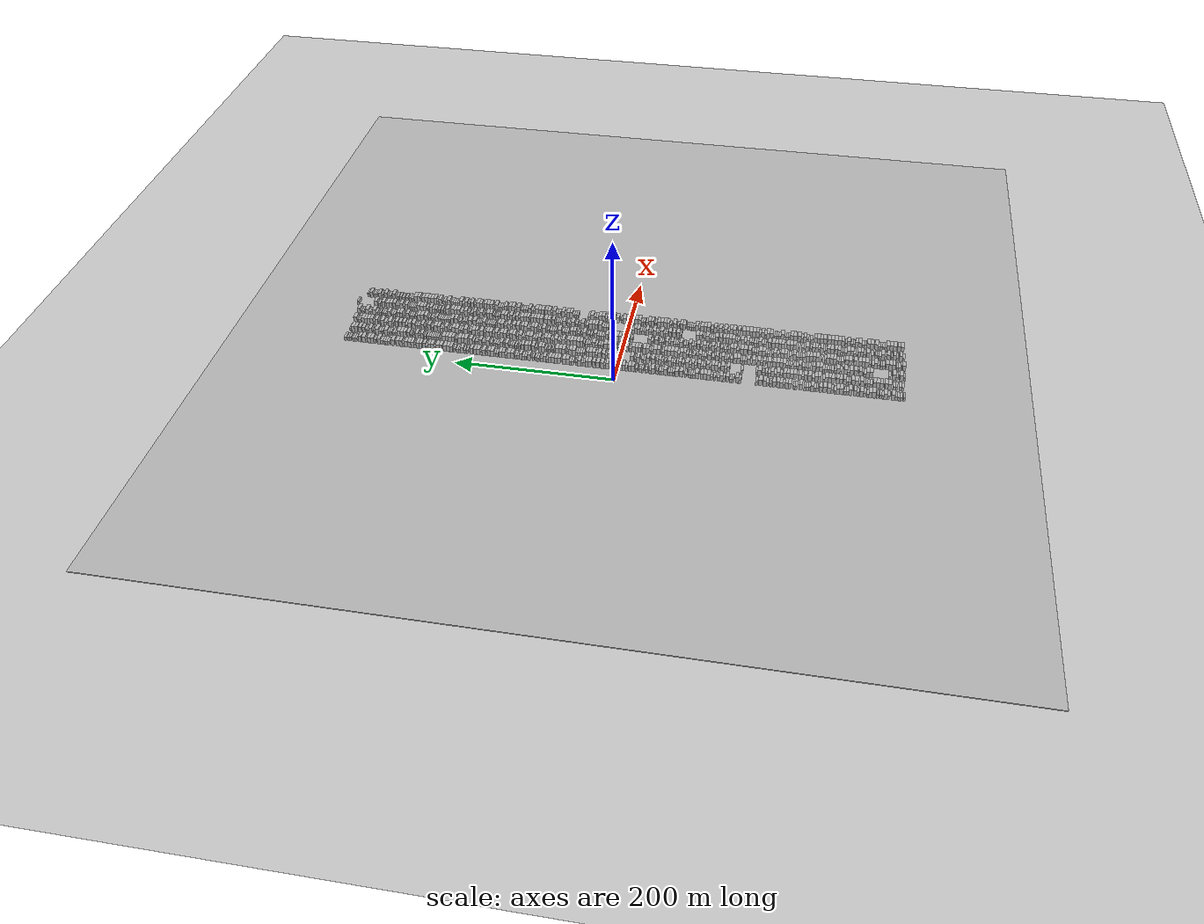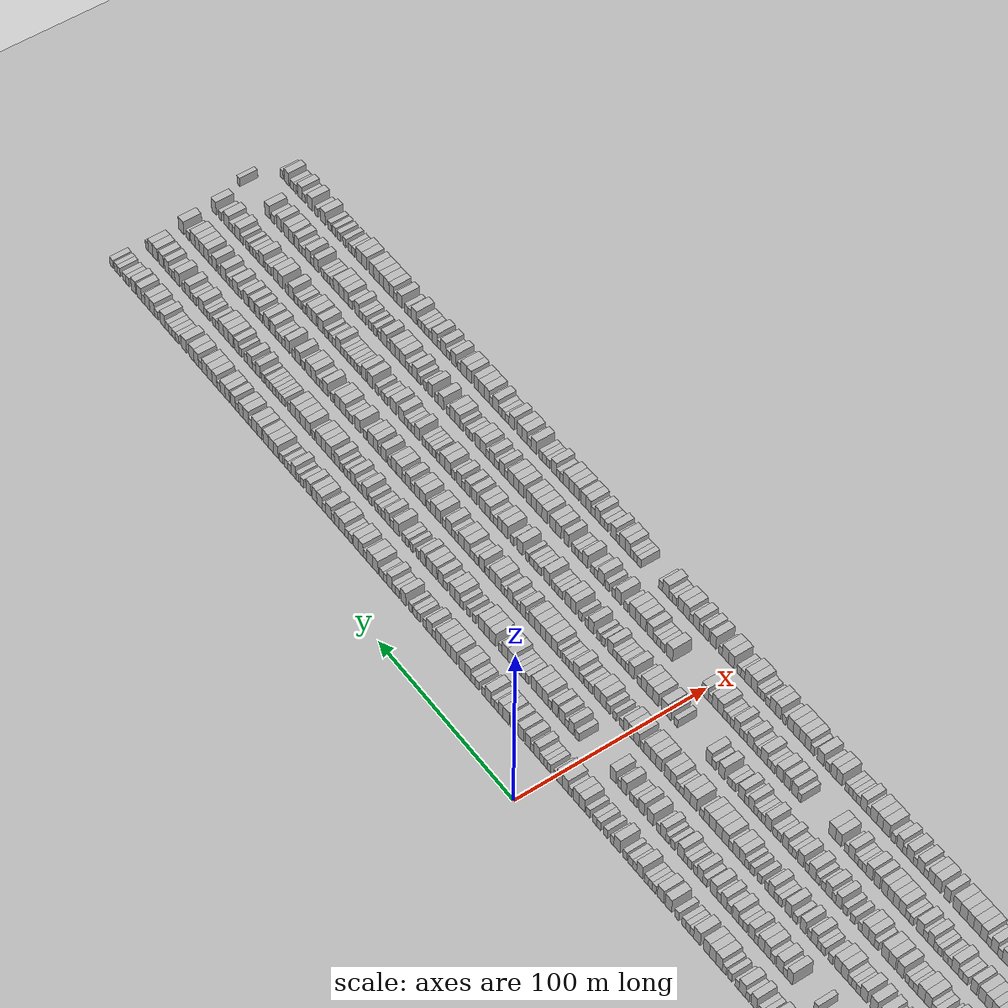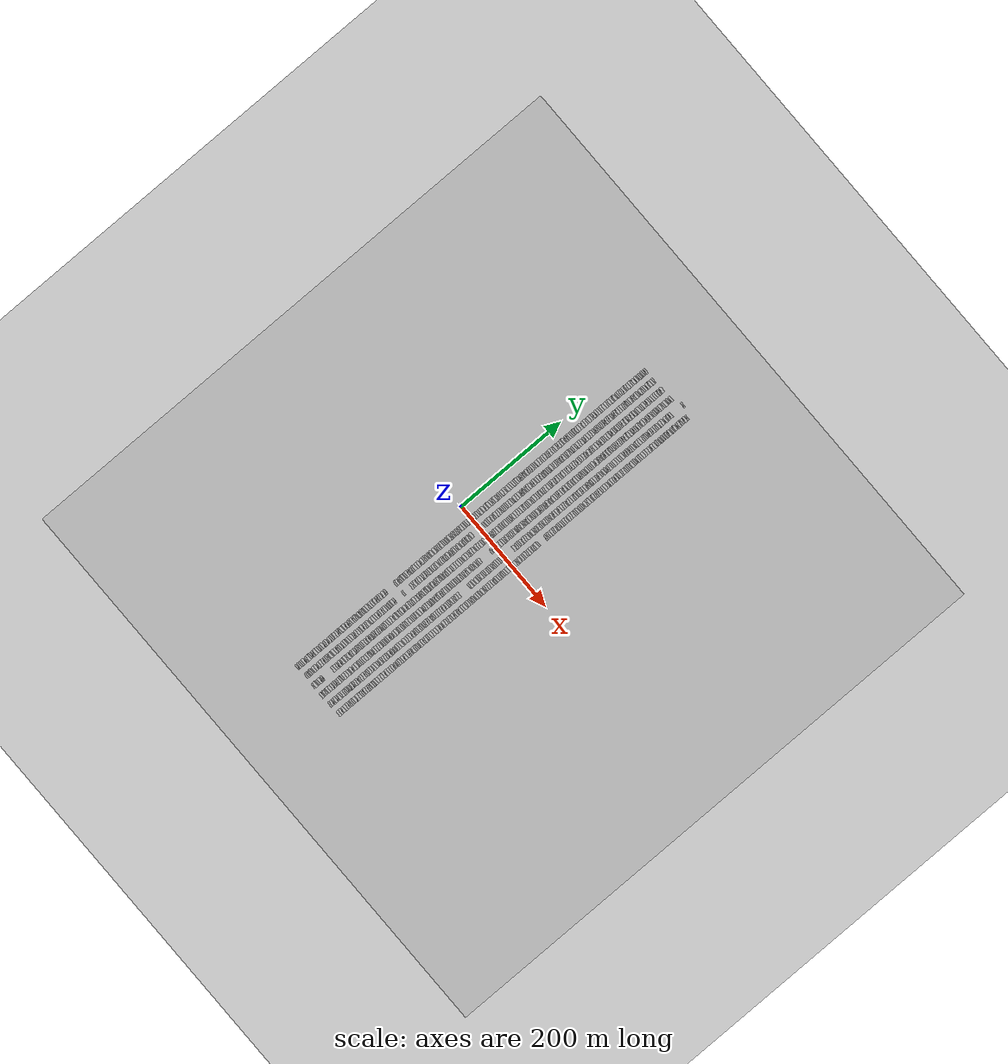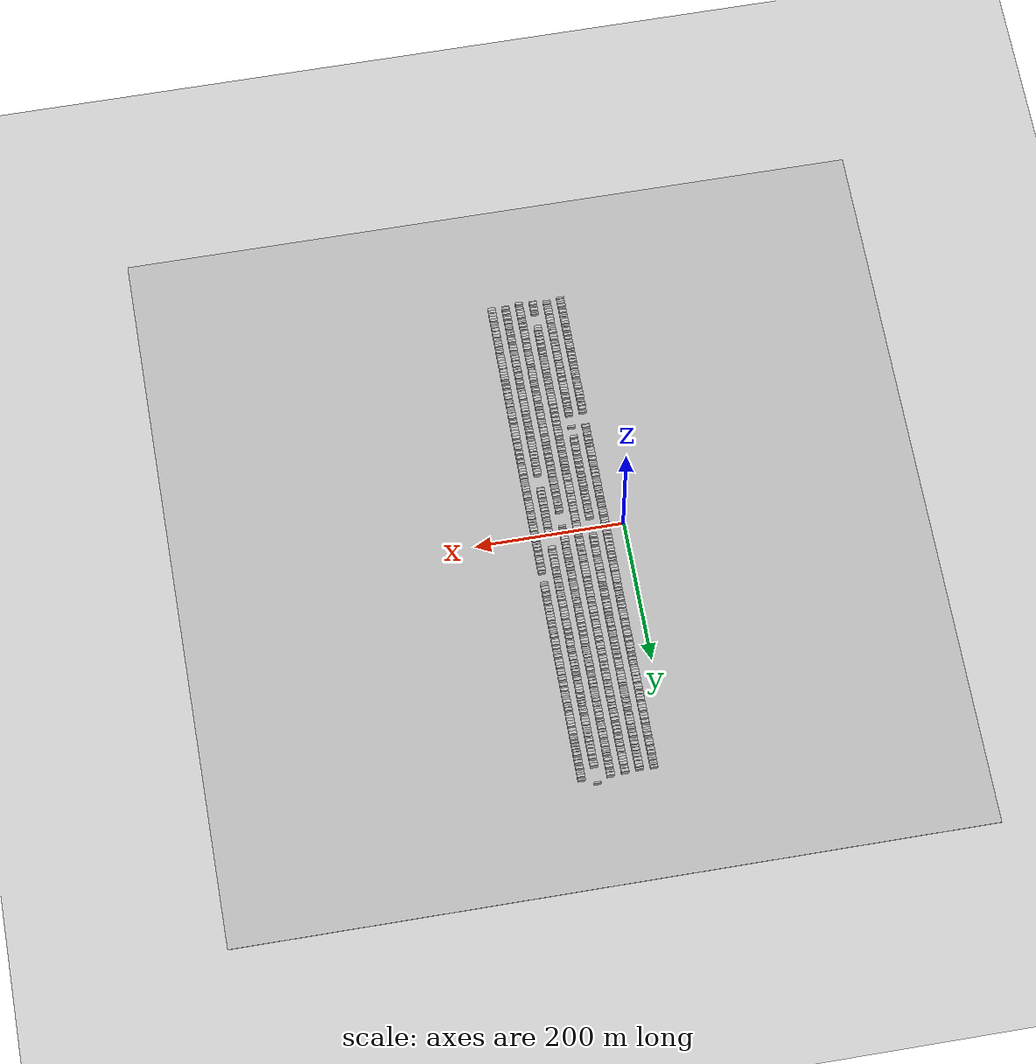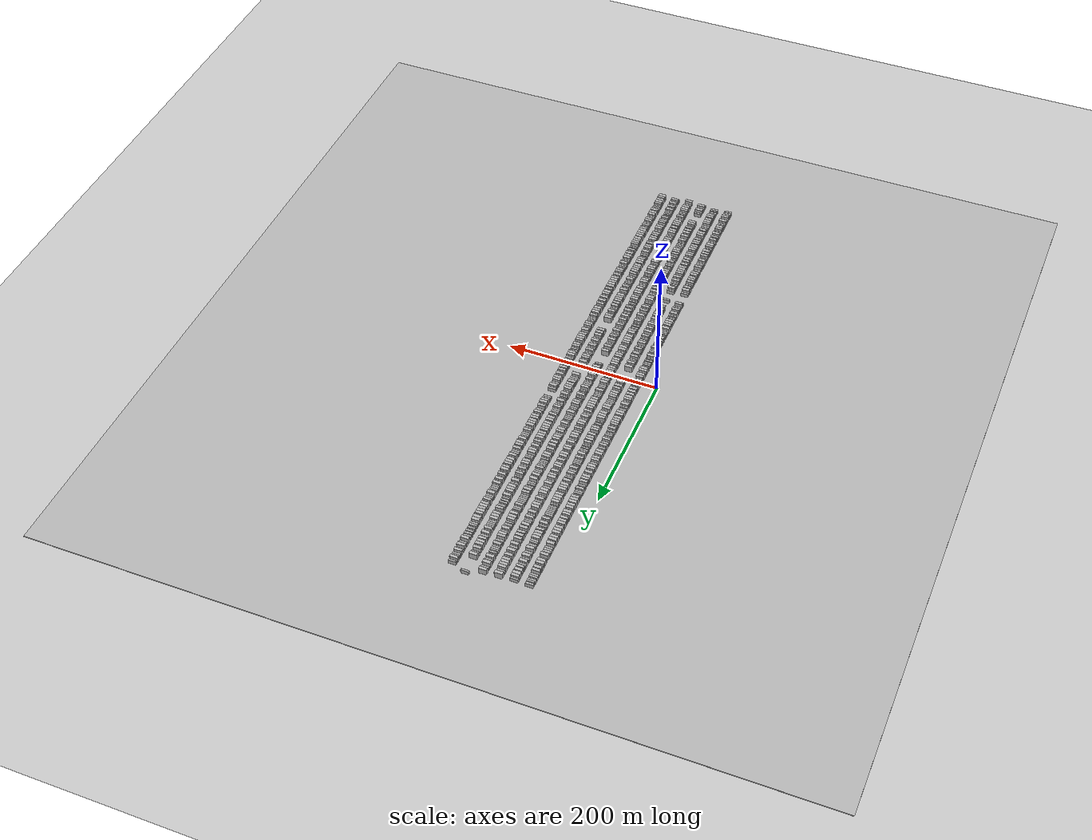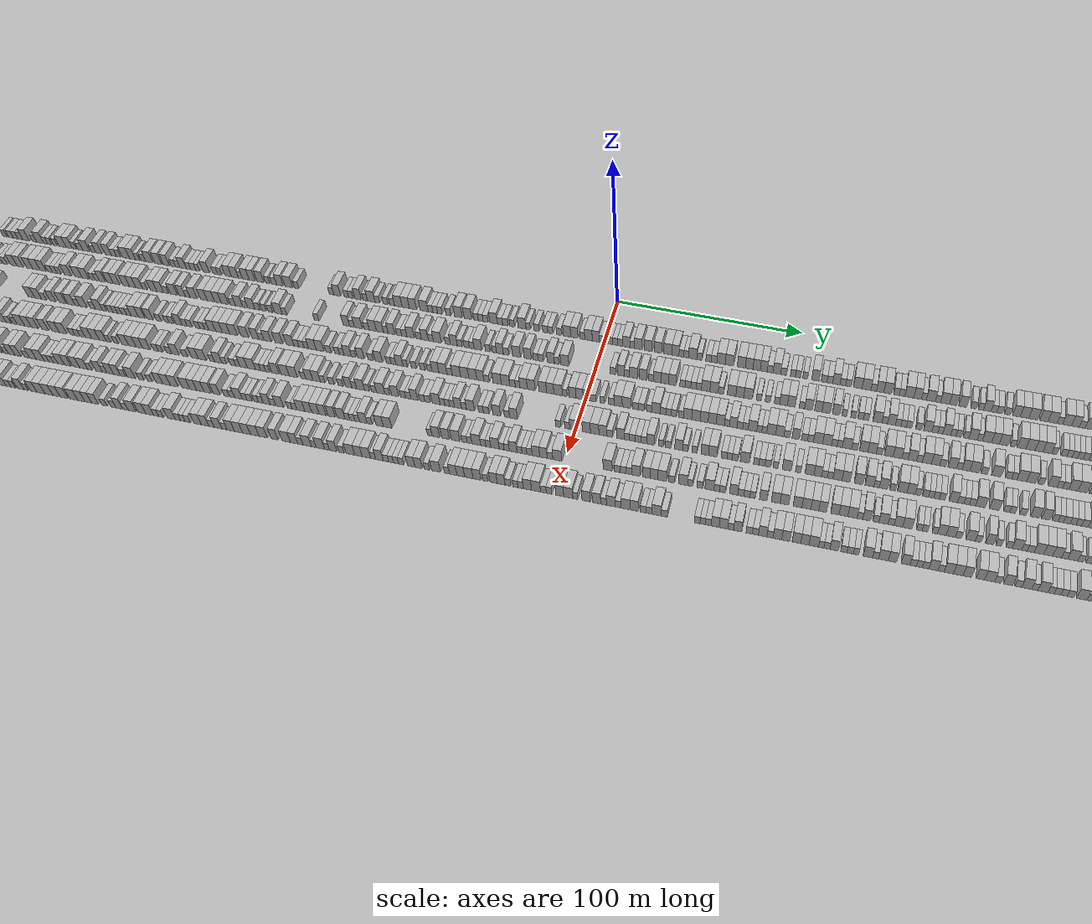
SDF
<?xml version="1.0" encoding="utf-8"?>

<sdf version="1.6">

   <world name="default">

      <gui fullscreen="0">

         <camera name="user_camera">

            <pose>-15 0 4.57585 0 0 0</pose>

            <view_controller>orbit</view_controller>

         </camera>

      </gui>

      <scene>

         <sky>

           <clouds>

             <speed>12</speed>

           </clouds>

         </sky>

         <ambient>0.4 0.4 0.4 1</ambient>

         <background>0.7 0.7 0.7 1</background>

         <shadows>1</shadows>

      </scene>

      <gravity>0 0 -9.8066</gravity>

      <magnetic_field>6e-06 2.3e-05 -4.2e-05</magnetic_field>

      <physics default="0" name="default_physics" type="ode">

         <ode>

            <solver>

               <type>quick</type>

               <iters>10</iters>

               <sor>1.0</sor>

               <use_dynamic_moi_rescaling>0</use_dynamic_moi_rescaling>

            </solver>

            <constraints>

               <cfm>0</cfm>

               <erp>0.2</erp>

               <contact_max_correcting_vel>100</contact_max_correcting_vel>

               <contact_surface_layer>0.001</contact_surface_layer>

            </constraints>

         </ode>

         <max_step_size>0.004</max_step_size>

         <real_time_factor>1</real_time_factor>

         <real_time_update_rate>250</real_time_update_rate>

      </physics>

      <light name="sun" type="directional">

         <cast_shadows>1</cast_shadows>

         <pose>0 0 10 0 0 0</pose>

         <diffuse>0.8 0.8 0.8 1</diffuse>

         <specular>0.2 0.2 0.2 1</specular>

         <attenuation>

            <range>1000</range>

            <constant>0.9</constant>

            <linear>0.01</linear>

            <quadratic>0.001</quadratic>

         </attenuation>

         <direction>-0.5 0.1 -0.9</direction>

      </light>

      <include>

         <name>ground_plane_1</name>

         <uri>model://HANNAS_ground_plane</uri>

         <pose>0 0 0  0 0 0</pose>

      </include>

      <include>

         <name>ground_plane_2</name>

         <uri>model://HANNAS_ground_plane</uri>

         <pose>100 0 0  0 0 0</pose>

      </include>

      <model name="building_1">

         <static>1</static>

         <pose frame="">25.0000 -348.7660 0 0.000000 0.000000 0.000000</pose>

         <link name="link">

            <pose frame="">0 0 3.00 0 0 0</pose>

            <collision name="collision">

               <geometry>

                  <box>

                     <size>10.0000 2.4679 6.0000</size>

                  </box>

               </geometry>

               <max_contacts>10</max_contacts>

               <surface>

                  <contact>

                     <ode/>

                  </contact>

                  <bounce/>

                  <friction>

                     <torsional>

                        <ode/>

                     </torsional>

                     <ode/>

                  </friction>

               </surface>

            </collision>

            <visual name="visual">

               <cast_shadows>0</cast_shadows>

               <geometry>

                  <box>

                     <size>10.0000 2.4679 6.0000</size>

                  </box>

               </geometry>

               <material>

                  <script>

                     <uri>model://HANNAS_wall/materials/scripts</uri>

                     <uri>model://HANNAS_wall/materials/textures</uri>

                     <name>vrc/HANNAS_wall</name>

                  </script>

               </material>

            </visual>

            <self_collide>0</self_collide>

            <enable_wind>0</enable_wind>

            <kinematic>0</kinematic>

         </link>

      </model>

      <model name="building_2">

         <static>1</static>

         <pose frame="">25.0000 -345.0527 0 0.000000 0.000000 0.000000</pose>

         <link name="link">

            <pose frame="">0 0 3.00 0 0 0</pose>

            <collision name="collision">

               <geometry>

                  <box>

                     <size>10.0000 2.9588 6.0000</size>

                  </box>

               </geometry>

               <max_contacts>10</max_contacts>

               <surface>

                  <contact>

                     <ode/>

                  </contact>

                  <bounce/>

                  <friction>

                     <torsional>

                        <ode/>

                     </torsional>

                     <ode/>

                  </friction>

               </surface>

            </collision>

            <visual name="visual">

               <cast_shadows>0</cast_shadows>

               <geometry>

                  <box>

                     <size>10.0000 2.9588 6.0000</size>

                  </box>

               </geometry>

               <material>

                  <script>

                     <uri>model://HANNAS_wall/materials/scripts</uri>

                     <uri>model://HANNAS_wall/materials/textures</uri>

                     <name>vrc/HANNAS_wall</name>

                  </script>

               </material>

            </visual>

            <self_collide>0</self_collide>

            <enable_wind>0</enable_wind>

            <kinematic>0</kinematic>

         </link>

      </model>

      <model name="building_3">

         <static>1</static>

         <pose frame="">25.0000 -342.0902 0 0.000000 0.000000 0.000000</pose>

         <link name="link">

            <pose frame="">0 0 3.00 0 0 0</pose>

            <collision name="collision">

               <geometry>

                  <box>

                     <size>10.0000 2.9660 6.0000</size>

                  </box>

               </geometry>

               <max_contacts>10</max_contacts>

               <surface>

                  <contact>

                     <ode/>

                  </contact>

                  <bounce/>

                  <friction>

                     <torsional>

                        <ode/>

                     </torsional>

                     <ode/>

                  </friction>

               </surface>

            </collision>

            <visual name="visual">

               <cast_shadows>0</cast_shadows>

               <geometry>

                  <box>

                     <size>10.0000 2.9660 6.0000</size>

                  </box>

               </geometry>

               <material>

                  <script>

                     <uri>model://HANNAS_wall/materials/scripts</uri>

                     <uri>model://HANNAS_wall/materials/textures</uri>

                     <name>vrc/HANNAS_wall</name>

                  </script>

               </material>

            </visual>

            <self_collide>0</self_collide>

            <enable_wind>0</enable_wind>

            <kinematic>0</kinematic>

         </link>

      </model>

      <model name="building_4">

         <static>1</static>

         <pose frame="">25.0000 -339.1338 0 0.000000 0.000000 0.000000</pose>

         <link name="link">

            <pose frame="">0 0 3.00 0 0 0</pose>

            <collision name="collision">

               <geometry>

                  <box>

                     <size>10.0000 2.9469 6.0000</size>

                  </box>

               </geometry>

               <max_contacts>10</max_contacts>

               <surface>

                  <contact>

                     <ode/>

                  </contact>

                  <bounce/>

                  <friction>

                     <torsional>

                        <ode/>

                     </torsional>

                     <ode/>

                  </friction>

               </surface>

            </collision>

            <visual name="visual">

               <cast_shadows>0</cast_shadows>

               <geometry>

                  <box>

                     <size>10.0000 2.9469 6.0000</size>

                  </box>

               </geometry>

               <material>

                  <script>

                     <uri>model://HANNAS_wall/materials/scripts</uri>

                     <uri>model://HANNAS_wall/materials/textures</uri>

                     <name>vrc/HANNAS_wall</name>

                  </script>

               </material>

            </visual>

            <self_collide>0</self_collide>

            <enable_wind>0</enable_wind>

            <kinematic>0</kinematic>

         </link>

      </model>

      <model name="building_5">

         <static>1</static>

         <pose frame="">25.0000 -335.5898 0 0.000000 0.000000 0.000000</pose>

         <link name="link">

            <pose frame="">0 0 4.50 0 0 0</pose>

            <collision name="collision">

               <geometry>

                  <box>

                     <size>10.0000 4.1409 9.0000</size>

                  </box>

               </geometry>

               <max_contacts>10</max_contacts>

               <surface>

                  <contact>

                     <ode/>

                  </contact>

                  <bounce/>

                  <friction>

                     <torsional>

                        <ode/>

                     </torsional>

                     <ode/>

                  </friction>

               </surface>

            </collision>

            <visual name="visual">

               <cast_shadows>0</cast_shadows>

               <geometry>

                  <box>

                     <size>10.0000 4.1409 9.0000</size>

                  </box>

               </geometry>

               <material>

                  <script>

                     <uri>model://HANNAS_wall/materials/scripts</uri>

                     <uri>model://HANNAS_wall/materials/textures</uri>

                     <name>vrc/HANNAS_wall</name>

                  </script>

               </material>

            </visual>

            <self_collide>0</self_collide>

            <enable_wind>0</enable_wind>

            <kinematic>0</kinematic>

         </link>

      </model>

      <model name="building_6">

         <static>1</static>

         <pose frame="">25.0000 -330.1965 0 0.000000 0.000000 0.000000</pose>

         <link name="link">

            <pose frame="">0 0 3.00 0 0 0</pose>

            <collision name="collision">

               <geometry>

                  <box>

                     <size>10.0000 2.6458 6.0000</size>

                  </box>

               </geometry>

               <max_contacts>10</max_contacts>

               <surface>

                  <contact>

                     <ode/>

                  </contact>

                  <bounce/>

                  <friction>

                     <torsional>

                        <ode/>

                     </torsional>

                     <ode/>

                  </friction>

               </surface>

            </collision>

            <visual name="visual">

               <cast_shadows>0</cast_shadows>

               <geometry>

                  <box>

                     <size>10.0000 2.6458 6.0000</size>

                  </box>

               </geometry>

               <material>

                  <script>

                     <uri>model://HANNAS_wall/materials/scripts</uri>

                     <uri>model://HANNAS_wall/materials/textures</uri>

                     <name>vrc/HANNAS_wall</name>

                  </script>

               </material>

            </visual>

            <self_collide>0</self_collide>

            <enable_wind>0</enable_wind>

            <kinematic>0</kinematic>

         </link>

      </model>

      <model name="building_7">

         <static>1</static>

         <pose frame="">25.0000 -326.7133 0 0.000000 0.000000 0.000000</pose>

         <link name="link">

            <pose frame="">0 0 4.50 0 0 0</pose>

            <collision name="collision">

               <geometry>

                  <box>

                     <size>10.0000 4.3205 9.0000</size>

                  </box>

               </geometry>

               <max_contacts>10</max_contacts>

               <surface>

                  <contact>

                     <ode/>

                  </contact>

                  <bounce/>

                  <friction>

                     <torsional>

                        <ode/>

                     </torsional>

                     <ode/>

                  </friction>

               </surface>

            </collision>

            <visual name="visual">

               <cast_shadows>0</cast_shadows>

               <geometry>

                  <box>

                     <size>10.0000 4.3205 9.0000</size>

                  </box>

               </geometry>

               <material>

                  <script>

                     <uri>model://HANNAS_wall/materials/scripts</uri>

                     <uri>model://HANNAS_wall/materials/textures</uri>

                     <name>vrc/HANNAS_wall</name>

                  </script>

               </material>

            </visual>

            <self_collide>0</self_collide>

            <enable_wind>0</enable_wind>

            <kinematic>0</kinematic>

         </link>

      </model>

      <model name="building_8">

         <static>1</static>

         <pose frame="">25.0000 -323.3036 0 0.000000 0.000000 0.000000</pose>

         <link name="link">

            <pose frame="">0 0 3.00 0 0 0</pose>

            <collision name="collision">

               <geometry>

                  <box>

                     <size>10.0000 2.4989 6.0000</size>

                  </box>

               </geometry>

               <max_contacts>10</max_contacts>

               <surface>

                  <contact>

                     <ode/>

                  </contact>

                  <bounce/>

                  <friction>

                     <torsional>

                        <ode/>

                     </torsional>

                     <ode/>

                  </friction>

               </surface>

            </collision>

            <visual name="visual">

               <cast_shadows>0</cast_shadows>

               <geometry>

                  <box>

                     <size>10.0000 2.4989 6.0000</size>

                  </box>

               </geometry>

               <material>

                  <script>

                     <uri>model://HANNAS_wall/materials/scripts</uri>

                     <uri>model://HANNAS_wall/materials/textures</uri>

                     <name>vrc/HANNAS_wall</name>

                  </script>

               </material>

            </visual>

            <self_collide>0</self_collide>

            <enable_wind>0</enable_wind>

            <kinematic>0</kinematic>

         </link>

      </model>

      <model name="building_9">

         <static>1</static>

         <pose frame="">25.0000 -320.7672 0 0.000000 0.000000 0.000000</pose>

         <link name="link">

            <pose frame="">0 0 3.00 0 0 0</pose>

            <collision name="collision">

               <geometry>

                  <box>

                     <size>10.0000 2.5739 6.0000</size>

                  </box>

               </geometry>

               <max_contacts>10</max_contacts>

               <surface>

                  <contact>

                     <ode/>

                  </contact>

                  <bounce/>

                  <friction>

                     <torsional>

                        <ode/>

                     </torsional>

                     <ode/>

                  </friction>

               </surface>

            </collision>

            <visual name="visual">

               <cast_shadows>0</cast_shadows>

               <geometry>

                  <box>

                     <size>10.0000 2.5739 6.0000</size>

                  </box>

               </geometry>

               <material>

                  <script>

                     <uri>model://HANNAS_wall/materials/scripts</uri>

                     <uri>model://HANNAS_wall/materials/textures</uri>

                     <name>vrc/HANNAS_wall</name>

                  </script>

               </material>

            </visual>

            <self_collide>0</self_collide>

            <enable_wind>0</enable_wind>

            <kinematic>0</kinematic>

         </link>

      </model>

      <model name="building_10">

         <static>1</static>

         <pose frame="">25.0000 -317.2470 0 0.000000 0.000000 0.000000</pose>

         <link name="link">

            <pose frame="">0 0 3.00 0 0 0</pose>

            <collision name="collision">

               <geometry>

                  <box>

                     <size>10.0000 2.4664 6.0000</size>

                  </box>

               </geometry>

               <max_contacts>10</max_contacts>

               <surface>

                  <contact>

                     <ode/>

                  </contact>

                  <bounce/>

                  <friction>

                     <torsional>

                        <ode/>

                     </torsional>

                     <ode/>

                  </friction>

               </surface>

            </collision>

            <visual name="visual">

               <cast_shadows>0</cast_shadows>

               <geometry>

                  <box>

                     <size>10.0000 2.4664 6.0000</size>

                  </box>

               </geometry>

               <material>

                  <script>

                     <uri>model://HANNAS_wall/materials/scripts</uri>

                     <uri>model://HANNAS_wall/materials/textures</uri>

                     <name>vrc/HANNAS_wall</name>

                  </script>

               </material>

            </visual>

            <self_collide>0</self_collide>

            <enable_wind>0</enable_wind>

            <kinematic>0</kinematic>

         </link>

      </model>

      <model name="building_11">

         <static>1</static>

         <pose frame="">25.0000 -312.7702 0 0.000000 0.000000 0.000000</pose>

         <link name="link">

            <pose frame="">0 0 4.50 0 0 0</pose>

            <collision name="collision">

               <geometry>

                  <box>

                     <size>10.0000 4.4872 9.0000</size>

                  </box>

               </geometry>

               <max_contacts>10</max_contacts>

               <surface>

                  <contact>

                     <ode/>

                  </contact>

                  <bounce/>

                  <friction>

                     <torsional>

                        <ode/>

                     </torsional>

                     <ode/>

                  </friction>

               </surface>

            </collision>

            <visual name="visual">

               <cast_shadows>0</cast_shadows>

               <geometry>

                  <box>

                     <size>10.0000 4.4872 9.0000</size>

                  </box>

               </geometry>

               <material>

                  <script>

                     <uri>model://HANNAS_wall/materials/scripts</uri>

                     <uri>model://HANNAS_wall/materials/textures</uri>

                     <name>vrc/HANNAS_wall</name>

                  </script>

               </material>

            </visual>

            <self_collide>0</self_collide>

            <enable_wind>0</enable_wind>

            <kinematic>0</kinematic>

         </link>

      </model>

      <model name="building_12">

         <static>1</static>

         <pose frame="">25.0000 -308.6517 0 0.000000 0.000000 0.000000</pose>

         <link name="link">

            <pose frame="">0 0 4.50 0 0 0</pose>

            <collision name="collision">

               <geometry>

                  <box>

                     <size>10.0000 3.7497 9.0000</size>

                  </box>

               </geometry>

               <max_contacts>10</max_contacts>

               <surface>

                  <contact>

                     <ode/>

                  </contact>

                  <bounce/>

                  <friction>

                     <torsional>

                        <ode/>

                     </torsional>

                     <ode/>

                  </friction>

               </surface>

            </collision>

            <visual name="visual">

               <cast_shadows>0</cast_shadows>

               <geometry>

                  <box>

                     <size>10.0000 3.7497 9.0000</size>

                  </box>

               </geometry>

               <material>

                  <script>

                     <uri>model://HANNAS_wall/materials/scripts</uri>

                     <uri>model://HANNAS_wall/materials/textures</uri>

                     <name>vrc/HANNAS_wall</name>

                  </script>

               </material>

            </visual>

            <self_collide>0</self_collide>

            <enable_wind>0</enable_wind>

            <kinematic>0</kinematic>

         </link>

      </model>

      <model name="building_13">

         <static>1</static>

         <pose frame="">25.0000 -305.5434 0 0.000000 0.000000 0.000000</pose>

         <link name="link">

            <pose frame="">0 0 3.00 0 0 0</pose>

            <collision name="collision">

               <geometry>

                  <box>

                     <size>10.0000 2.4669 6.0000</size>

                  </box>

               </geometry>

               <max_contacts>10</max_contacts>

               <surface>

                  <contact>

                     <ode/>

                  </contact>

                  <bounce/>

                  <friction>

                     <torsional>

                        <ode/>

                     </torsional>

                     <ode/>

                  </friction>

               </surface>

            </collision>

            <visual name="visual">

               <cast_shadows>0</cast_shadows>

               <geometry>

                  <box>

                     <size>10.0000 2.4669 6.0000</size>

                  </box>

               </geometry>

               <material>

                  <script>

                     <uri>model://HANNAS_wall/materials/scripts</uri>

                     <uri>model://HANNAS_wall/materials/textures</uri>

                     <name>vrc/HANNAS_wall</name>

                  </script>

               </material>

            </visual>

            <self_collide>0</self_collide>

            <enable_wind>0</enable_wind>

            <kinematic>0</kinematic>

         </link>

      </model>

      <model name="building_14">

         <static>1</static>

         <pose frame="">25.0000 -301.8110 0 0.000000 0.000000 0.000000</pose>

         <link name="link">

            <pose frame="">0 0 3.00 0 0 0</pose>

            <collision name="collision">

               <geometry>

                  <box>

                     <size>10.0000 2.9979 6.0000</size>

                  </box>

               </geometry>

               <max_contacts>10</max_contacts>

               <surface>

                  <contact>

                     <ode/>

                  </contact>

                  <bounce/>

                  <friction>

                     <torsional>

                        <ode/>

                     </torsional>

                     <ode/>

                  </friction>

               </surface>

            </collision>

            <visual name="visual">

               <cast_shadows>0</cast_shadows>

               <geometry>

                  <box>

                     <size>10.0000 2.9979 6.0000</size>

                  </box>

               </geometry>

               <material>

                  <script>

                     <uri>model://HANNAS_wall/materials/scripts</uri>

                     <uri>model://HANNAS_wall/materials/textures</uri>

                     <name>vrc/HANNAS_wall</name>

                  </script>

               </material>

            </visual>

            <self_collide>0</self_collide>

            <enable_wind>0</enable_wind>

            <kinematic>0</kinematic>

         </link>

      </model>

      <model name="building_15">

         <static>1</static>

         <pose frame="">25.0000 -298.1401 0 0.000000 0.000000 0.000000</pose>

         <link name="link">

            <pose frame="">0 0 4.50 0 0 0</pose>

            <collision name="collision">

               <geometry>

                  <box>

                     <size>10.0000 4.3440 9.0000</size>

                  </box>

               </geometry>

               <max_contacts>10</max_contacts>

               <surface>

                  <contact>

                     <ode/>

                  </contact>

                  <bounce/>

                  <friction>

                     <torsional>

                        <ode/>

                     </torsional>

                     <ode/>

                  </friction>

               </surface>

            </collision>

            <visual name="visual">

               <cast_shadows>0</cast_shadows>

               <geometry>

                  <box>

                     <size>10.0000 4.3440 9.0000</size>

                  </box>

               </geometry>

               <material>

                  <script>

                     <uri>model://HANNAS_wall/materials/scripts</uri>

                     <uri>model://HANNAS_wall/materials/textures</uri>

                     <name>vrc/HANNAS_wall</name>

                  </script>

               </material>

            </visual>

            <self_collide>0</self_collide>

            <enable_wind>0</enable_wind>

            <kinematic>0</kinematic>

         </link>

      </model>

      <model name="building_16">

         <static>1</static>

         <pose frame="">25.0000 -293.6096 0 0.000000 0.000000 0.000000</pose>

         <link name="link">

            <pose frame="">0 0 3.00 0 0 0</pose>

            <collision name="collision">

               <geometry>

                  <box>

                     <size>10.0000 2.7168 6.0000</size>

                  </box>

               </geometry>

               <max_contacts>10</max_contacts>

               <surface>

                  <contact>

                     <ode/>

                  </contact>

                  <bounce/>

                  <friction>

                     <torsional>

                        <ode/>

                     </torsional>

                     <ode/>

                  </friction>

               </surface>

            </collision>

            <visual name="visual">

               <cast_shadows>0</cast_shadows>

               <geometry>

                  <box>

                     <size>10.0000 2.7168 6.0000</size>

                  </box>

               </geometry>

               <material>

                  <script>

                     <uri>model://HANNAS_wall/materials/scripts</uri>

                     <uri>model://HANNAS_wall/materials/textures</uri>

                     <name>vrc/HANNAS_wall</name>

                  </script>

               </material>

            </visual>

            <self_collide>0</self_collide>

            <enable_wind>0</enable_wind>

            <kinematic>0</kinematic>

         </link>

      </model>

      <model name="building_17">

         <static>1</static>

         <pose frame="">25.0000 -290.3991 0 0.000000 0.000000 0.000000</pose>

         <link name="link">

            <pose frame="">0 0 4.50 0 0 0</pose>

            <collision name="collision">

               <geometry>

                  <box>

                     <size>10.0000 3.7041 9.0000</size>

                  </box>

               </geometry>

               <max_contacts>10</max_contacts>

               <surface>

                  <contact>

                     <ode/>

                  </contact>

                  <bounce/>

                  <friction>

                     <torsional>

                        <ode/>

                     </torsional>

                     <ode/>

                  </friction>

               </surface>

            </collision>

            <visual name="visual">

               <cast_shadows>0</cast_shadows>

               <geometry>

                  <box>

                     <size>10.0000 3.7041 9.0000</size>

                  </box>

               </geometry>

               <material>

                  <script>

                     <uri>model://HANNAS_wall/materials/scripts</uri>

                     <uri>model://HANNAS_wall/materials/textures</uri>

                     <name>vrc/HANNAS_wall</name>

                  </script>

               </material>

            </visual>

            <self_collide>0</self_collide>

            <enable_wind>0</enable_wind>

            <kinematic>0</kinematic>

         </link>

      </model>

      <model name="building_18">

         <static>1</static>

         <pose frame="">25.0000 -284.6384 0 0.000000 0.000000 0.000000</pose>

         <link name="link">

            <pose frame="">0 0 4.50 0 0 0</pose>

            <collision name="collision">

               <geometry>

                  <box>

                     <size>10.0000 3.8173 9.0000</size>

                  </box>

               </geometry>

               <max_contacts>10</max_contacts>

               <surface>

                  <contact>

                     <ode/>

                  </contact>

                  <bounce/>

                  <friction>

                     <torsional>

                        <ode/>

                     </torsional>

                     <ode/>

                  </friction>

               </surface>

            </collision>

            <visual name="visual">

               <cast_shadows>0</cast_shadows>

               <geometry>

                  <box>

                     <size>10.0000 3.8173 9.0000</size>

                  </box>

               </geometry>

               <material>

                  <script>

                     <uri>model://HANNAS_wall/materials/scripts</uri>

                     <uri>model://HANNAS_wall/materials/textures</uri>

                     <name>vrc/HANNAS_wall</name>

                  </script>

               </material>

            </visual>

            <self_collide>0</self_collide>

            <enable_wind>0</enable_wind>

            <kinematic>0</kinematic>

         </link>

      </model>

      <model name="building_19">

         <static>1</static>

         <pose frame="">25.0000 -281.2480 0 0.000000 0.000000 0.000000</pose>

         <link name="link">

            <pose frame="">0 0 3.00 0 0 0</pose>

            <collision name="collision">

               <geometry>

                  <box>

                     <size>10.0000 2.9634 6.0000</size>

                  </box>

               </geometry>

               <max_contacts>10</max_contacts>

               <surface>

                  <contact>

                     <ode/>

                  </contact>

                  <bounce/>

                  <friction>

                     <torsional>

                        <ode/>

                     </torsional>

                     <ode/>

                  </friction>

               </surface>

            </collision>

            <visual name="visual">

               <cast_shadows>0</cast_shadows>

               <geometry>

                  <box>

                     <size>10.0000 2.9634 6.0000</size>

                  </box>

               </geometry>

               <material>

                  <script>

                     <uri>model://HANNAS_wall/materials/scripts</uri>

                     <uri>model://HANNAS_wall/materials/textures</uri>

                     <name>vrc/HANNAS_wall</name>

                  </script>

               </material>

            </visual>

            <self_collide>0</self_collide>

            <enable_wind>0</enable_wind>

            <kinematic>0</kinematic>

         </link>

      </model>

      <model name="building_20">

         <static>1</static>

         <pose frame="">25.0000 -278.4587 0 0.000000 0.000000 0.000000</pose>

         <link name="link">

            <pose frame="">0 0 3.00 0 0 0</pose>

            <collision name="collision">

               <geometry>

                  <box>

                     <size>10.0000 2.6152 6.0000</size>

                  </box>

               </geometry>

               <max_contacts>10</max_contacts>

               <surface>

                  <contact>

                     <ode/>

                  </contact>

                  <bounce/>

                  <friction>

                     <torsional>

                        <ode/>

                     </torsional>

                     <ode/>

                  </friction>

               </surface>

            </collision>

            <visual name="visual">

               <cast_shadows>0</cast_shadows>

               <geometry>

                  <box>

                     <size>10.0000 2.6152 6.0000</size>

                  </box>

               </geometry>

               <material>

                  <script>

                     <uri>model://HANNAS_wall/materials/scripts</uri>

                     <uri>model://HANNAS_wall/materials/textures</uri>

                     <name>vrc/HANNAS_wall</name>

                  </script>

               </material>

            </visual>

            <self_collide>0</self_collide>

            <enable_wind>0</enable_wind>

            <kinematic>0</kinematic>

         </link>

      </model>

      <model name="building_21">

         <static>1</static>

         <pose frame="">25.0000 -273.9181 0 0.000000 0.000000 0.000000</pose>

         <link name="link">

            <pose frame="">0 0 4.50 0 0 0</pose>

            <collision name="collision">

               <geometry>

                  <box>

                     <size>10.0000 4.4660 9.0000</size>

                  </box>

               </geometry>

               <max_contacts>10</max_contacts>

               <surface>

                  <contact>

                     <ode/>

                  </contact>

                  <bounce/>

                  <friction>

                     <torsional>

                        <ode/>

                     </torsional>

                     <ode/>

                  </friction>

               </surface>

            </collision>

            <visual name="visual">

               <cast_shadows>0</cast_shadows>

               <geometry>

                  <box>

                     <size>10.0000 4.4660 9.0000</size>

                  </box>

               </geometry>

               <material>

                  <script>

                     <uri>model://HANNAS_wall/materials/scripts</uri>

                     <uri>model://HANNAS_wall/materials/textures</uri>

                     <name>vrc/HANNAS_wall</name>

                  </script>

               </material>

            </visual>

            <self_collide>0</self_collide>

            <enable_wind>0</enable_wind>

            <kinematic>0</kinematic>

         </link>

      </model>

      <model name="building_22">

         <static>1</static>

         <pose frame="">25.0000 -269.7842 0 0.000000 0.000000 0.000000</pose>

         <link name="link">

            <pose frame="">0 0 4.50 0 0 0</pose>

            <collision name="collision">

               <geometry>

                  <box>

                     <size>10.0000 3.8019 9.0000</size>

                  </box>

               </geometry>

               <max_contacts>10</max_contacts>

               <surface>

                  <contact>

                     <ode/>

                  </contact>

                  <bounce/>

                  <friction>

                     <torsional>

                        <ode/>

                     </torsional>

                     <ode/>

                  </friction>

               </surface>

            </collision>

            <visual name="visual">

               <cast_shadows>0</cast_shadows>

               <geometry>

                  <box>

                     <size>10.0000 3.8019 9.0000</size>

                  </box>

               </geometry>

               <material>

                  <script>

                     <uri>model://HANNAS_wall/materials/scripts</uri>

                     <uri>model://HANNAS_wall/materials/textures</uri>

                     <name>vrc/HANNAS_wall</name>

                  </script>

               </material>

            </visual>

            <self_collide>0</self_collide>

            <enable_wind>0</enable_wind>

            <kinematic>0</kinematic>

         </link>

      </model>

      <model name="building_23">

         <static>1</static>

         <pose frame="">25.0000 -266.6804 0 0.000000 0.000000 0.000000</pose>

         <link name="link">

            <pose frame="">0 0 3.00 0 0 0</pose>

            <collision name="collision">

               <geometry>

                  <box>

                     <size>10.0000 2.4058 6.0000</size>

                  </box>

               </geometry>

               <max_contacts>10</max_contacts>

               <surface>

                  <contact>

                     <ode/>

                  </contact>

                  <bounce/>

                  <friction>

                     <torsional>

                        <ode/>

                     </torsional>

                     <ode/>

                  </friction>

               </surface>

            </collision>

            <visual name="visual">

               <cast_shadows>0</cast_shadows>

               <geometry>

                  <box>

                     <size>10.0000 2.4058 6.0000</size>

                  </box>

               </geometry>

               <material>

                  <script>

                     <uri>model://HANNAS_wall/materials/scripts</uri>

                     <uri>model://HANNAS_wall/materials/textures</uri>

                     <name>vrc/HANNAS_wall</name>

                  </script>

               </material>

            </visual>

            <self_collide>0</self_collide>

            <enable_wind>0</enable_wind>

            <kinematic>0</kinematic>

         </link>

      </model>

      <model name="building_24">

         <static>1</static>

         <pose frame="">25.0000 -263.0894 0 0.000000 0.000000 0.000000</pose>

         <link name="link">

            <pose frame="">0 0 3.00 0 0 0</pose>

            <collision name="collision">

               <geometry>

                  <box>

                     <size>10.0000 2.7762 6.0000</size>

                  </box>

               </geometry>

               <max_contacts>10</max_contacts>

               <surface>

                  <contact>

                     <ode/>

                  </contact>

                  <bounce/>

                  <friction>

                     <torsional>

                        <ode/>

                     </torsional>

                     <ode/>

                  </friction>

               </surface>

            </collision>

            <visual name="visual">

               <cast_shadows>0</cast_shadows>

               <geometry>

                  <box>

                     <size>10.0000 2.7762 6.0000</size>

                  </box>

               </geometry>

               <material>

                  <script>

                     <uri>model://HANNAS_wall/materials/scripts</uri>

                     <uri>model://HANNAS_wall/materials/textures</uri>

                     <name>vrc/HANNAS_wall</name>

                  </script>

               </material>

            </visual>

            <self_collide>0</self_collide>

            <enable_wind>0</enable_wind>

            <kinematic>0</kinematic>

         </link>

      </model>

      <model name="building_25">

         <static>1</static>

         <pose frame="">25.0000 -259.5243 0 0.000000 0.000000 0.000000</pose>

         <link name="link">

            <pose frame="">0 0 4.50 0 0 0</pose>

            <collision name="collision">

               <geometry>

                  <box>

                     <size>10.0000 4.3541 9.0000</size>

                  </box>

               </geometry>

               <max_contacts>10</max_contacts>

               <surface>

                  <contact>

                     <ode/>

                  </contact>

                  <bounce/>

                  <friction>

                     <torsional>

                        <ode/>

                     </torsional>

                     <ode/>

                  </friction>

               </surface>

            </collision>

            <visual name="visual">

               <cast_shadows>0</cast_shadows>

               <geometry>

                  <box>

                     <size>10.0000 4.3541 9.0000</size>

                  </box>

               </geometry>

               <material>

                  <script>

                     <uri>model://HANNAS_wall/materials/scripts</uri>

                     <uri>model://HANNAS_wall/materials/textures</uri>

                     <name>vrc/HANNAS_wall</name>

                  </script>

               </material>

            </visual>

            <self_collide>0</self_collide>

            <enable_wind>0</enable_wind>

            <kinematic>0</kinematic>

         </link>

      </model>

      <model name="building_26">

         <static>1</static>

         <pose frame="">25.0000 -254.2442 0 0.000000 0.000000 0.000000</pose>

         <link name="link">

            <pose frame="">0 0 4.50 0 0 0</pose>

            <collision name="collision">

               <geometry>

                  <box>

                     <size>10.0000 4.2059 9.0000</size>

                  </box>

               </geometry>

               <max_contacts>10</max_contacts>

               <surface>

                  <contact>

                     <ode/>

                  </contact>

                  <bounce/>

                  <friction>

                     <torsional>

                        <ode/>

                     </torsional>

                     <ode/>

                  </friction>

               </surface>

            </collision>

            <visual name="visual">

               <cast_shadows>0</cast_shadows>

               <geometry>

                  <box>

                     <size>10.0000 4.2059 9.0000</size>

                  </box>

               </geometry>

               <material>

                  <script>

                     <uri>model://HANNAS_wall/materials/scripts</uri>

                     <uri>model://HANNAS_wall/materials/textures</uri>

                     <name>vrc/HANNAS_wall</name>

                  </script>

               </material>

            </visual>

            <self_collide>0</self_collide>

            <enable_wind>0</enable_wind>

            <kinematic>0</kinematic>

         </link>

      </model>

      <model name="building_27">

         <static>1</static>

         <pose frame="">25.0000 -249.2754 0 0.000000 0.000000 0.000000</pose>

         <link name="link">

            <pose frame="">0 0 4.50 0 0 0</pose>

            <collision name="collision">

               <geometry>

                  <box>

                     <size>10.0000 3.7317 9.0000</size>

                  </box>

               </geometry>

               <max_contacts>10</max_contacts>

               <surface>

                  <contact>

                     <ode/>

                  </contact>

                  <bounce/>

                  <friction>

                     <torsional>

                        <ode/>

                     </torsional>

                     <ode/>

                  </friction>

               </surface>

            </collision>

            <visual name="visual">

               <cast_shadows>0</cast_shadows>

               <geometry>

                  <box>

                     <size>10.0000 3.7317 9.0000</size>

                  </box>

               </geometry>

               <material>

                  <script>

                     <uri>model://HANNAS_wall/materials/scripts</uri>

                     <uri>model://HANNAS_wall/materials/textures</uri>

                     <name>vrc/HANNAS_wall</name>

                  </script>

               </material>

            </visual>

            <self_collide>0</self_collide>

            <enable_wind>0</enable_wind>

            <kinematic>0</kinematic>

         </link>

      </model>

      <model name="building_28">

         <static>1</static>

         <pose frame="">25.0000 -245.0887 0 0.000000 0.000000 0.000000</pose>

         <link name="link">

            <pose frame="">0 0 3.00 0 0 0</pose>

            <collision name="collision">

               <geometry>

                  <box>

                     <size>10.0000 2.6416 6.0000</size>

                  </box>

               </geometry>

               <max_contacts>10</max_contacts>

               <surface>

                  <contact>

                     <ode/>

                  </contact>

                  <bounce/>

                  <friction>

                     <torsional>

                        <ode/>

                     </torsional>

                     <ode/>

                  </friction>

               </surface>

            </collision>

            <visual name="visual">

               <cast_shadows>0</cast_shadows>

               <geometry>

                  <box>

                     <size>10.0000 2.6416 6.0000</size>

                  </box>

               </geometry>

               <material>

                  <script>

                     <uri>model://HANNAS_wall/materials/scripts</uri>

                     <uri>model://HANNAS_wall/materials/textures</uri>

                     <name>vrc/HANNAS_wall</name>

                  </script>

               </material>

            </visual>

            <self_collide>0</self_collide>

            <enable_wind>0</enable_wind>

            <kinematic>0</kinematic>

         </link>

      </model>

      <model name="building_29">

         <static>1</static>

         <pose frame="">25.0000 -242.4724 0 0.000000 0.000000 0.000000</pose>

         <link name="link">

            <pose frame="">0 0 3.00 0 0 0</pose>

            <collision name="collision">

               <geometry>

                  <box>

                     <size>10.0000 2.5910 6.0000</size>

                  </box>

               </geometry>

               <max_contacts>10</max_contacts>

               <surface>

                  <contact>

                     <ode/>

                  </contact>

                  <bounce/>

                  <friction>

                     <torsional>

                        <ode/>

                     </torsional>

                     <ode/>

                  </friction>

               </surface>

            </collision>

            <visual name="visual">

               <cast_shadows>0</cast_shadows>

               <geometry>

                  <box>

                     <size>10.0000 2.5910 6.0000</size>

                  </box>

               </geometry>

               <material>

                  <script>

                     <uri>model://HANNAS_wall/materials/scripts</uri>

                     <uri>model://HANNAS_wall/materials/textures</uri>

                     <name>vrc/HANNAS_wall</name>

                  </script>

               </material>

            </visual>

            <self_collide>0</self_collide>

            <enable_wind>0</enable_wind>

            <kinematic>0</kinematic>

         </link>

      </model>

      <model name="building_30">

         <static>1</static>

         <pose frame="">25.0000 -239.2148 0 0.000000 0.000000 0.000000</pose>

         <link name="link">

            <pose frame="">0 0 4.50 0 0 0</pose>

            <collision name="collision">

               <geometry>

                  <box>

                     <size>10.0000 3.9242 9.0000</size>

                  </box>

               </geometry>

               <max_contacts>10</max_contacts>

               <surface>

                  <contact>

                     <ode/>

                  </contact>

                  <bounce/>

                  <friction>

                     <torsional>

                        <ode/>

                     </torsional>

                     <ode/>

                  </friction>

               </surface>

            </collision>

            <visual name="visual">

               <cast_shadows>0</cast_shadows>

               <geometry>

                  <box>

                     <size>10.0000 3.9242 9.0000</size>

                  </box>

               </geometry>

               <material>

                  <script>

                     <uri>model://HANNAS_wall/materials/scripts</uri>

                     <uri>model://HANNAS_wall/materials/textures</uri>

                     <name>vrc/HANNAS_wall</name>

                  </script>

               </material>

            </visual>

            <self_collide>0</self_collide>

            <enable_wind>0</enable_wind>

            <kinematic>0</kinematic>

         </link>

      </model>

      <model name="building_31">

         <static>1</static>

         <pose frame="">25.0000 -235.9470 0 0.000000 0.000000 0.000000</pose>

         <link name="link">

            <pose frame="">0 0 3.00 0 0 0</pose>

            <collision name="collision">

               <geometry>

                  <box>

                     <size>10.0000 2.6115 6.0000</size>

                  </box>

               </geometry>

               <max_contacts>10</max_contacts>

               <surface>

                  <contact>

                     <ode/>

                  </contact>

                  <bounce/>

                  <friction>

                     <torsional>

                        <ode/>

                     </torsional>

                     <ode/>

                  </friction>

               </surface>

            </collision>

            <visual name="visual">

               <cast_shadows>0</cast_shadows>

               <geometry>

                  <box>

                     <size>10.0000 2.6115 6.0000</size>

                  </box>

               </geometry>

               <material>

                  <script>

                     <uri>model://HANNAS_wall/materials/scripts</uri>

                     <uri>model://HANNAS_wall/materials/textures</uri>

                     <name>vrc/HANNAS_wall</name>

                  </script>

               </material>

            </visual>

            <self_collide>0</self_collide>

            <enable_wind>0</enable_wind>

            <kinematic>0</kinematic>

         </link>

      </model>

      <model name="building_32">

         <static>1</static>

         <pose frame="">25.0000 -233.1449 0 0.000000 0.000000 0.000000</pose>

         <link name="link">

            <pose frame="">0 0 3.00 0 0 0</pose>

            <collision name="collision">

               <geometry>

                  <box>

                     <size>10.0000 2.9928 6.0000</size>

                  </box>

               </geometry>

               <max_contacts>10</max_contacts>

               <surface>

                  <contact>

                     <ode/>

                  </contact>

                  <bounce/>

                  <friction>

                     <torsional>

                        <ode/>

                     </torsional>

                     <ode/>

                  </friction>

               </surface>

            </collision>

            <visual name="visual">

               <cast_shadows>0</cast_shadows>

               <geometry>

                  <box>

                     <size>10.0000 2.9928 6.0000</size>

                  </box>

               </geometry>

               <material>

                  <script>

                     <uri>model://HANNAS_wall/materials/scripts</uri>

                     <uri>model://HANNAS_wall/materials/textures</uri>

                     <name>vrc/HANNAS_wall</name>

                  </script>

               </material>

            </visual>

            <self_collide>0</self_collide>

            <enable_wind>0</enable_wind>

            <kinematic>0</kinematic>

         </link>

      </model>

      <model name="building_33">

         <static>1</static>

         <pose frame="">25.0000 -230.4417 0 0.000000 0.000000 0.000000</pose>

         <link name="link">

            <pose frame="">0 0 3.00 0 0 0</pose>

            <collision name="collision">

               <geometry>

                  <box>

                     <size>10.0000 2.4134 6.0000</size>

                  </box>

               </geometry>

               <max_contacts>10</max_contacts>

               <surface>

                  <contact>

                     <ode/>

                  </contact>

                  <bounce/>

                  <friction>

                     <torsional>

                        <ode/>

                     </torsional>

                     <ode/>

                  </friction>

               </surface>

            </collision>

            <visual name="visual">

               <cast_shadows>0</cast_shadows>

               <geometry>

                  <box>

                     <size>10.0000 2.4134 6.0000</size>

                  </box>

               </geometry>

               <material>

                  <script>

                     <uri>model://HANNAS_wall/materials/scripts</uri>

                     <uri>model://HANNAS_wall/materials/textures</uri>

                     <name>vrc/HANNAS_wall</name>

                  </script>

               </material>

            </visual>

            <self_collide>0</self_collide>

            <enable_wind>0</enable_wind>

            <kinematic>0</kinematic>

         </link>

      </model>

      <model name="building_34">

         <static>1</static>

         <pose frame="">25.0000 -225.3167 0 0.000000 0.000000 0.000000</pose>

         <link name="link">

            <pose frame="">0 0 4.50 0 0 0</pose>

            <collision name="collision">

               <geometry>

                  <box>

                     <size>10.0000 3.8365 9.0000</size>

                  </box>

               </geometry>

               <max_contacts>10</max_contacts>

               <surface>

                  <contact>

                     <ode/>

                  </contact>

                  <bounce/>

                  <friction>

                     <torsional>

                        <ode/>

                     </torsional>

                     <ode/>

                  </friction>

               </surface>

            </collision>

            <visual name="visual">

               <cast_shadows>0</cast_shadows>

               <geometry>

                  <box>

                     <size>10.0000 3.8365 9.0000</size>

                  </box>

               </geometry>

               <material>

                  <script>

                     <uri>model://HANNAS_wall/materials/scripts</uri>

                     <uri>model://HANNAS_wall/materials/textures</uri>

                     <name>vrc/HANNAS_wall</name>

                  </script>

               </material>

            </visual>

            <self_collide>0</self_collide>

            <enable_wind>0</enable_wind>

            <kinematic>0</kinematic>

         </link>

      </model>

      <model name="building_35">

         <static>1</static>

         <pose frame="">25.0000 -219.9875 0 0.000000 0.000000 0.000000</pose>

         <link name="link">

            <pose frame="">0 0 3.00 0 0 0</pose>

            <collision name="collision">

               <geometry>

                  <box>

                     <size>10.0000 2.8219 6.0000</size>

                  </box>

               </geometry>

               <max_contacts>10</max_contacts>

               <surface>

                  <contact>

                     <ode/>

                  </contact>

                  <bounce/>

                  <friction>

                     <torsional>

                        <ode/>

                     </torsional>

                     <ode/>

                  </friction>

               </surface>

            </collision>

            <visual name="visual">

               <cast_shadows>0</cast_shadows>

               <geometry>

                  <box>

                     <size>10.0000 2.8219 6.0000</size>

                  </box>

               </geometry>

               <material>

                  <script>

                     <uri>model://HANNAS_wall/materials/scripts</uri>

                     <uri>model://HANNAS_wall/materials/textures</uri>

                     <name>vrc/HANNAS_wall</name>

                  </script>

               </material>

            </visual>

            <self_collide>0</self_collide>

            <enable_wind>0</enable_wind>

            <kinematic>0</kinematic>

         </link>

      </model>

      <model name="building_36">

         <static>1</static>

         <pose frame="">25.0000 -217.3249 0 0.000000 0.000000 0.000000</pose>

         <link name="link">

            <pose frame="">0 0 3.00 0 0 0</pose>

            <collision name="collision">

               <geometry>

                  <box>

                     <size>10.0000 2.5034 6.0000</size>

                  </box>

               </geometry>

               <max_contacts>10</max_contacts>

               <surface>

                  <contact>

                     <ode/>

                  </contact>

                  <bounce/>

                  <friction>

                     <torsional>

                        <ode/>

                     </torsional>

                     <ode/>

                  </friction>

               </surface>

            </collision>

            <visual name="visual">

               <cast_shadows>0</cast_shadows>

               <geometry>

                  <box>

                     <size>10.0000 2.5034 6.0000</size>

                  </box>

               </geometry>

               <material>

                  <script>

                     <uri>model://HANNAS_wall/materials/scripts</uri>

                     <uri>model://HANNAS_wall/materials/textures</uri>

                     <name>vrc/HANNAS_wall</name>

                  </script>

               </material>

            </visual>

            <self_collide>0</self_collide>

            <enable_wind>0</enable_wind>

            <kinematic>0</kinematic>

         </link>

      </model>

      <model name="building_37">

         <static>1</static>

         <pose frame="">25.0000 -212.2040 0 0.000000 0.000000 0.000000</pose>

         <link name="link">

            <pose frame="">0 0 4.50 0 0 0</pose>

            <collision name="collision">

               <geometry>

                  <box>

                     <size>10.0000 3.7382 9.0000</size>

                  </box>

               </geometry>

               <max_contacts>10</max_contacts>

               <surface>

                  <contact>

                     <ode/>

                  </contact>

                  <bounce/>

                  <friction>

                     <torsional>

                        <ode/>

                     </torsional>

                     <ode/>

                  </friction>

               </surface>

            </collision>

            <visual name="visual">

               <cast_shadows>0</cast_shadows>

               <geometry>

                  <box>

                     <size>10.0000 3.7382 9.0000</size>

                  </box>

               </geometry>

               <material>

                  <script>

                     <uri>model://HANNAS_wall/materials/scripts</uri>

                     <uri>model://HANNAS_wall/materials/textures</uri>

                     <name>vrc/HANNAS_wall</name>

                  </script>

               </material>

            </visual>

            <self_collide>0</self_collide>

            <enable_wind>0</enable_wind>

            <kinematic>0</kinematic>

         </link>

      </model>

      <model name="building_38">

         <static>1</static>

         <pose frame="">25.0000 -208.3201 0 0.000000 0.000000 0.000000</pose>

         <link name="link">

            <pose frame="">0 0 4.50 0 0 0</pose>

            <collision name="collision">

               <geometry>

                  <box>

                     <size>10.0000 4.0297 9.0000</size>

                  </box>

               </geometry>

               <max_contacts>10</max_contacts>

               <surface>

                  <contact>

                     <ode/>

                  </contact>

                  <bounce/>

                  <friction>

                     <torsional>

                        <ode/>

                     </torsional>

                     <ode/>

                  </friction>

               </surface>

            </collision>

            <visual name="visual">

               <cast_shadows>0</cast_shadows>

               <geometry>

                  <box>

                     <size>10.0000 4.0297 9.0000</size>

                  </box>

               </geometry>

               <material>

                  <script>

                     <uri>model://HANNAS_wall/materials/scripts</uri>

                     <uri>model://HANNAS_wall/materials/textures</uri>

                     <name>vrc/HANNAS_wall</name>

                  </script>

               </material>

            </visual>

            <self_collide>0</self_collide>

            <enable_wind>0</enable_wind>

            <kinematic>0</kinematic>

         </link>

      </model>

      <model name="building_39">

         <static>1</static>

         <pose frame="">25.0000 -205.0746 0 0.000000 0.000000 0.000000</pose>

         <link name="link">

            <pose frame="">0 0 3.00 0 0 0</pose>

            <collision name="collision">

               <geometry>

                  <box>

                     <size>10.0000 2.4613 6.0000</size>

                  </box>

               </geometry>

               <max_contacts>10</max_contacts>

               <surface>

                  <contact>

                     <ode/>

                  </contact>

                  <bounce/>

                  <friction>

                     <torsional>

                        <ode/>

                     </torsional>

                     <ode/>

                  </friction>

               </surface>

            </collision>

            <visual name="visual">

               <cast_shadows>0</cast_shadows>

               <geometry>

                  <box>

                     <size>10.0000 2.4613 6.0000</size>

                  </box>

               </geometry>

               <material>

                  <script>

                     <uri>model://HANNAS_wall/materials/scripts</uri>

                     <uri>model://HANNAS_wall/materials/textures</uri>

                     <name>vrc/HANNAS_wall</name>

                  </script>

               </material>

            </visual>

            <self_collide>0</self_collide>

            <enable_wind>0</enable_wind>

            <kinematic>0</kinematic>

         </link>

      </model>

      <model name="building_40">

         <static>1</static>

         <pose frame="">25.0000 -201.8766 0 0.000000 0.000000 0.000000</pose>

         <link name="link">

            <pose frame="">0 0 4.50 0 0 0</pose>

            <collision name="collision">

               <geometry>

                  <box>

                     <size>10.0000 3.9346 9.0000</size>

                  </box>

               </geometry>

               <max_contacts>10</max_contacts>

               <surface>

                  <contact>

                     <ode/>

                  </contact>

                  <bounce/>

                  <friction>

                     <torsional>

                        <ode/>

                     </torsional>

                     <ode/>

                  </friction>

               </surface>

            </collision>

            <visual name="visual">

               <cast_shadows>0</cast_shadows>

               <geometry>

                  <box>

                     <size>10.0000 3.9346 9.0000</size>

                  </box>

               </geometry>

               <material>

                  <script>

                     <uri>model://HANNAS_wall/materials/scripts</uri>

                     <uri>model://HANNAS_wall/materials/textures</uri>

                     <name>vrc/HANNAS_wall</name>

                  </script>

               </material>

            </visual>

            <self_collide>0</self_collide>

            <enable_wind>0</enable_wind>

            <kinematic>0</kinematic>

         </link>

      </model>

      <model name="building_41">

         <static>1</static>

         <pose frame="">25.0000 -198.0777 0 0.000000 0.000000 0.000000</pose>

         <link name="link">

            <pose frame="">0 0 4.50 0 0 0</pose>

            <collision name="collision">

               <geometry>

                  <box>

                     <size>10.0000 3.6633 9.0000</size>

                  </box>

               </geometry>

               <max_contacts>10</max_contacts>

               <surface>

                  <contact>

                     <ode/>

                  </contact>

                  <bounce/>

                  <friction>

                     <torsional>

                        <ode/>

                     </torsional>

                     <ode/>

                  </friction>

               </surface>

            </collision>

            <visual name="visual">

               <cast_shadows>0</cast_shadows>

               <geometry>

                  <box>

                     <size>10.0000 3.6633 9.0000</size>

                  </box>

               </geometry>

               <material>

                  <script>

                     <uri>model://HANNAS_wall/materials/scripts</uri>

                     <uri>model://HANNAS_wall/materials/textures</uri>

                     <name>vrc/HANNAS_wall</name>

                  </script>

               </material>

            </visual>

            <self_collide>0</self_collide>

            <enable_wind>0</enable_wind>

            <kinematic>0</kinematic>

         </link>

      </model>

      <model name="building_42">

         <static>1</static>

         <pose frame="">25.0000 -193.2453 0 0.000000 0.000000 0.000000</pose>

         <link name="link">

            <pose frame="">0 0 4.50 0 0 0</pose>

            <collision name="collision">

               <geometry>

                  <box>

                     <size>10.0000 4.0014 9.0000</size>

                  </box>

               </geometry>

               <max_contacts>10</max_contacts>

               <surface>

                  <contact>

                     <ode/>

                  </contact>

                  <bounce/>

                  <friction>

                     <torsional>

                        <ode/>

                     </torsional>

                     <ode/>

                  </friction>

               </surface>

            </collision>

            <visual name="visual">

               <cast_shadows>0</cast_shadows>

               <geometry>

                  <box>

                     <size>10.0000 4.0014 9.0000</size>

                  </box>

               </geometry>

               <material>

                  <script>

                     <uri>model://HANNAS_wall/materials/scripts</uri>

                     <uri>model://HANNAS_wall/materials/textures</uri>

                     <name>vrc/HANNAS_wall</name>

                  </script>

               </material>

            </visual>

            <self_collide>0</self_collide>

            <enable_wind>0</enable_wind>

            <kinematic>0</kinematic>

         </link>

      </model>

      <model name="building_43">

         <static>1</static>

         <pose frame="">25.0000 -188.9625 0 0.000000 0.000000 0.000000</pose>

         <link name="link">

            <pose frame="">0 0 3.00 0 0 0</pose>

            <collision name="collision">

               <geometry>

                  <box>

                     <size>10.0000 2.5642 6.0000</size>

                  </box>

               </geometry>

               <max_contacts>10</max_contacts>

               <surface>

                  <contact>

                     <ode/>

                  </contact>

                  <bounce/>

                  <friction>

                     <torsional>

                        <ode/>

                     </torsional>

                     <ode/>

                  </friction>

               </surface>

            </collision>

            <visual name="visual">

               <cast_shadows>0</cast_shadows>

               <geometry>

                  <box>

                     <size>10.0000 2.5642 6.0000</size>

                  </box>

               </geometry>

               <material>

                  <script>

                     <uri>model://HANNAS_wall/materials/scripts</uri>

                     <uri>model://HANNAS_wall/materials/textures</uri>

                     <name>vrc/HANNAS_wall</name>

                  </script>

               </material>

            </visual>

            <self_collide>0</self_collide>

            <enable_wind>0</enable_wind>

            <kinematic>0</kinematic>

         </link>

      </model>

      <model name="building_44">

         <static>1</static>

         <pose frame="">25.0000 -185.2157 0 0.000000 0.000000 0.000000</pose>

         <link name="link">

            <pose frame="">0 0 3.00 0 0 0</pose>

            <collision name="collision">

               <geometry>

                  <box>

                     <size>10.0000 2.9294 6.0000</size>

                  </box>

               </geometry>

               <max_contacts>10</max_contacts>

               <surface>

                  <contact>

                     <ode/>

                  </contact>

                  <bounce/>

                  <friction>

                     <torsional>

                        <ode/>

                     </torsional>

                     <ode/>

                  </friction>

               </surface>

            </collision>

            <visual name="visual">

               <cast_shadows>0</cast_shadows>

               <geometry>

                  <box>

                     <size>10.0000 2.9294 6.0000</size>

                  </box>

               </geometry>

               <material>

                  <script>

                     <uri>model://HANNAS_wall/materials/scripts</uri>

                     <uri>model://HANNAS_wall/materials/textures</uri>

                     <name>vrc/HANNAS_wall</name>

                  </script>

               </material>

            </visual>

            <self_collide>0</self_collide>

            <enable_wind>0</enable_wind>

            <kinematic>0</kinematic>

         </link>

      </model>

      <model name="building_45">

         <static>1</static>

         <pose frame="">25.0000 -181.8123 0 0.000000 0.000000 0.000000</pose>

         <link name="link">

            <pose frame="">0 0 4.50 0 0 0</pose>

            <collision name="collision">

               <geometry>

                  <box>

                     <size>10.0000 3.8773 9.0000</size>

                  </box>

               </geometry>

               <max_contacts>10</max_contacts>

               <surface>

                  <contact>

                     <ode/>

                  </contact>

                  <bounce/>

                  <friction>

                     <torsional>

                        <ode/>

                     </torsional>

                     <ode/>

                  </friction>

               </surface>

            </collision>

            <visual name="visual">

               <cast_shadows>0</cast_shadows>

               <geometry>

                  <box>

                     <size>10.0000 3.8773 9.0000</size>

                  </box>

               </geometry>

               <material>

                  <script>

                     <uri>model://HANNAS_wall/materials/scripts</uri>

                     <uri>model://HANNAS_wall/materials/textures</uri>

                     <name>vrc/HANNAS_wall</name>

                  </script>

               </material>

            </visual>

            <self_collide>0</self_collide>

            <enable_wind>0</enable_wind>

            <kinematic>0</kinematic>

         </link>

      </model>

      <model name="building_46">

         <static>1</static>

         <pose frame="">25.0000 -176.6313 0 0.000000 0.000000 0.000000</pose>

         <link name="link">

            <pose frame="">0 0 4.50 0 0 0</pose>

            <collision name="collision">

               <geometry>

                  <box>

                     <size>10.0000 4.4849 9.0000</size>

                  </box>

               </geometry>

               <max_contacts>10</max_contacts>

               <surface>

                  <contact>

                     <ode/>

                  </contact>

                  <bounce/>

                  <friction>

                     <torsional>

                        <ode/>

                     </torsional>

                     <ode/>

                  </friction>

               </surface>

            </collision>

            <visual name="visual">

               <cast_shadows>0</cast_shadows>

               <geometry>

                  <box>

                     <size>10.0000 4.4849 9.0000</size>

                  </box>

               </geometry>

               <material>

                  <script>

                     <uri>model://HANNAS_wall/materials/scripts</uri>

                     <uri>model://HANNAS_wall/materials/textures</uri>

                     <name>vrc/HANNAS_wall</name>

                  </script>

               </material>

            </visual>

            <self_collide>0</self_collide>

            <enable_wind>0</enable_wind>

            <kinematic>0</kinematic>

         </link>

      </model>

      <model name="building_47">

         <static>1</static>

         <pose frame="">25.0000 -172.0270 0 0.000000 0.000000 0.000000</pose>

         <link name="link">

            <pose frame="">0 0 3.00 0 0 0</pose>

            <collision name="collision">

               <geometry>

                  <box>

                     <size>10.0000 2.7236 6.0000</size>

                  </box>

               </geometry>

               <max_contacts>10</max_contacts>

               <surface>

                  <contact>

                     <ode/>

                  </contact>

                  <bounce/>

                  <friction>

                     <torsional>

                        <ode/>

                     </torsional>

                     <ode/>

                  </friction>

               </surface>

            </collision>

            <visual name="visual">

               <cast_shadows>0</cast_shadows>

               <geometry>

                  <box>

                     <size>10.0000 2.7236 6.0000</size>

                  </box>

               </geometry>

               <material>

                  <script>

                     <uri>model://HANNAS_wall/materials/scripts</uri>

                     <uri>model://HANNAS_wall/materials/textures</uri>

                     <name>vrc/HANNAS_wall</name>

                  </script>

               </material>

            </visual>

            <self_collide>0</self_collide>

            <enable_wind>0</enable_wind>

            <kinematic>0</kinematic>

         </link>

      </model>

      <model name="building_48">

         <static>1</static>

         <pose frame="">25.0000 -151.7010 0 0.000000 0.000000 0.000000</pose>

         <link name="link">

            <pose frame="">0 0 3.00 0 0 0</pose>

            <collision name="collision">

               <geometry>

                  <box>

                     <size>10.0000 2.6429 6.0000</size>

                  </box>

               </geometry>

               <max_contacts>10</max_contacts>

               <surface>

                  <contact>

                     <ode/>

                  </contact>

                  <bounce/>

                  <friction>

                     <torsional>

                        <ode/>

                     </torsional>

                     <ode/>

                  </friction>

               </surface>

            </collision>

            <visual name="visual">

               <cast_shadows>0</cast_shadows>

               <geometry>

                  <box>

                     <size>10.0000 2.6429 6.0000</size>

                  </box>

               </geometry>

               <material>

                  <script>

                     <uri>model://HANNAS_wall/materials/scripts</uri>

                     <uri>model://HANNAS_wall/materials/textures</uri>

                     <name>vrc/HANNAS_wall</name>

                  </script>

               </material>

            </visual>

            <self_collide>0</self_collide>

            <enable_wind>0</enable_wind>

            <kinematic>0</kinematic>

         </link>

      </model>

      <model name="building_49">

         <static>1</static>

         <pose frame="">25.0000 -148.4138 0 0.000000 0.000000 0.000000</pose>

         <link name="link">

            <pose frame="">0 0 4.50 0 0 0</pose>

            <collision name="collision">

               <geometry>

                  <box>

                     <size>10.0000 3.9313 9.0000</size>

                  </box>

               </geometry>

               <max_contacts>10</max_contacts>

               <surface>

                  <contact>

                     <ode/>

                  </contact>

                  <bounce/>

                  <friction>

                     <torsional>

                        <ode/>

                     </torsional>

                     <ode/>

                  </friction>

               </surface>

            </collision>

            <visual name="visual">

               <cast_shadows>0</cast_shadows>

               <geometry>

                  <box>

                     <size>10.0000 3.9313 9.0000</size>

                  </box>

               </geometry>

               <material>

                  <script>

                     <uri>model://HANNAS_wall/materials/scripts</uri>

                     <uri>model://HANNAS_wall/materials/textures</uri>

                     <name>vrc/HANNAS_wall</name>

                  </script>

               </material>

            </visual>

            <self_collide>0</self_collide>

            <enable_wind>0</enable_wind>

            <kinematic>0</kinematic>

         </link>

      </model>

      <model name="building_50">

         <static>1</static>

         <pose frame="">25.0000 -143.1870 0 0.000000 0.000000 0.000000</pose>

         <link name="link">

            <pose frame="">0 0 3.00 0 0 0</pose>

            <collision name="collision">

               <geometry>

                  <box>

                     <size>10.0000 2.5224 6.0000</size>

                  </box>

               </geometry>

               <max_contacts>10</max_contacts>

               <surface>

                  <contact>

                     <ode/>

                  </contact>

                  <bounce/>

                  <friction>

                     <torsional>

                        <ode/>

                     </torsional>

                     <ode/>

                  </friction>

               </surface>

            </collision>

            <visual name="visual">

               <cast_shadows>0</cast_shadows>

               <geometry>

                  <box>

                     <size>10.0000 2.5224 6.0000</size>

                  </box>

               </geometry>

               <material>

                  <script>

                     <uri>model://HANNAS_wall/materials/scripts</uri>

                     <uri>model://HANNAS_wall/materials/textures</uri>

                     <name>vrc/HANNAS_wall</name>

                  </script>

               </material>

            </visual>

            <self_collide>0</self_collide>

            <enable_wind>0</enable_wind>

            <kinematic>0</kinematic>

         </link>

      </model>

      <model name="building_51">

         <static>1</static>

         <pose frame="">25.0000 -140.6154 0 0.000000 0.000000 0.000000</pose>

         <link name="link">

            <pose frame="">0 0 3.00 0 0 0</pose>

            <collision name="collision">

               <geometry>

                  <box>

                     <size>10.0000 2.6207 6.0000</size>

                  </box>

               </geometry>

               <max_contacts>10</max_contacts>

               <surface>

                  <contact>

                     <ode/>

                  </contact>

                  <bounce/>

                  <friction>

                     <torsional>

                        <ode/>

                     </torsional>

                     <ode/>

                  </friction>

               </surface>

            </collision>

            <visual name="visual">

               <cast_shadows>0</cast_shadows>

               <geometry>

                  <box>

                     <size>10.0000 2.6207 6.0000</size>

                  </box>

               </geometry>

               <material>

                  <script>

                     <uri>model://HANNAS_wall/materials/scripts</uri>

                     <uri>model://HANNAS_wall/materials/textures</uri>

                     <name>vrc/HANNAS_wall</name>

                  </script>

               </material>

            </visual>

            <self_collide>0</self_collide>

            <enable_wind>0</enable_wind>

            <kinematic>0</kinematic>

         </link>

      </model>

      <model name="building_52">

         <static>1</static>

         <pose frame="">25.0000 -136.4687 0 0.000000 0.000000 0.000000</pose>

         <link name="link">

            <pose frame="">0 0 4.50 0 0 0</pose>

            <collision name="collision">

               <geometry>

                  <box>

                     <size>10.0000 3.6727 9.0000</size>

                  </box>

               </geometry>

               <max_contacts>10</max_contacts>

               <surface>

                  <contact>

                     <ode/>

                  </contact>

                  <bounce/>

                  <friction>

                     <torsional>

                        <ode/>

                     </torsional>

                     <ode/>

                  </friction>

               </surface>

            </collision>

            <visual name="visual">

               <cast_shadows>0</cast_shadows>

               <geometry>

                  <box>

                     <size>10.0000 3.6727 9.0000</size>

                  </box>

               </geometry>

               <material>

                  <script>

                     <uri>model://HANNAS_wall/materials/scripts</uri>

                     <uri>model://HANNAS_wall/materials/textures</uri>

                     <name>vrc/HANNAS_wall</name>

                  </script>

               </material>

            </visual>

            <self_collide>0</self_collide>

            <enable_wind>0</enable_wind>

            <kinematic>0</kinematic>

         </link>

      </model>

      <model name="building_53">

         <static>1</static>

         <pose frame="">25.0000 -132.3696 0 0.000000 0.000000 0.000000</pose>

         <link name="link">

            <pose frame="">0 0 3.00 0 0 0</pose>

            <collision name="collision">

               <geometry>

                  <box>

                     <size>10.0000 2.5254 6.0000</size>

                  </box>

               </geometry>

               <max_contacts>10</max_contacts>

               <surface>

                  <contact>

                     <ode/>

                  </contact>

                  <bounce/>

                  <friction>

                     <torsional>

                        <ode/>

                     </torsional>

                     <ode/>

                  </friction>

               </surface>

            </collision>

            <visual name="visual">

               <cast_shadows>0</cast_shadows>

               <geometry>

                  <box>

                     <size>10.0000 2.5254 6.0000</size>

                  </box>

               </geometry>

               <material>

                  <script>

                     <uri>model://HANNAS_wall/materials/scripts</uri>

                     <uri>model://HANNAS_wall/materials/textures</uri>

                     <name>vrc/HANNAS_wall</name>

                  </script>

               </material>

            </visual>

            <self_collide>0</self_collide>

            <enable_wind>0</enable_wind>

            <kinematic>0</kinematic>

         </link>

      </model>

      <model name="building_54">

         <static>1</static>

         <pose frame="">25.0000 -128.9481 0 0.000000 0.000000 0.000000</pose>

         <link name="link">

            <pose frame="">0 0 4.50 0 0 0</pose>

            <collision name="collision">

               <geometry>

                  <box>

                     <size>10.0000 4.3176 9.0000</size>

                  </box>

               </geometry>

               <max_contacts>10</max_contacts>

               <surface>

                  <contact>

                     <ode/>

                  </contact>

                  <bounce/>

                  <friction>

                     <torsional>

                        <ode/>

                     </torsional>

                     <ode/>

                  </friction>

               </surface>

            </collision>

            <visual name="visual">

               <cast_shadows>0</cast_shadows>

               <geometry>

                  <box>

                     <size>10.0000 4.3176 9.0000</size>

                  </box>

               </geometry>

               <material>

                  <script>

                     <uri>model://HANNAS_wall/materials/scripts</uri>

                     <uri>model://HANNAS_wall/materials/textures</uri>

                     <name>vrc/HANNAS_wall</name>

                  </script>

               </material>

            </visual>

            <self_collide>0</self_collide>

            <enable_wind>0</enable_wind>

            <kinematic>0</kinematic>

         </link>

      </model>

      <model name="building_55">

         <static>1</static>

         <pose frame="">25.0000 -125.4472 0 0.000000 0.000000 0.000000</pose>

         <link name="link">

            <pose frame="">0 0 3.00 0 0 0</pose>

            <collision name="collision">

               <geometry>

                  <box>

                     <size>10.0000 2.6842 6.0000</size>

                  </box>

               </geometry>

               <max_contacts>10</max_contacts>

               <surface>

                  <contact>

                     <ode/>

                  </contact>

                  <bounce/>

                  <friction>

                     <torsional>

                        <ode/>

                     </torsional>

                     <ode/>

                  </friction>

               </surface>

            </collision>

            <visual name="visual">

               <cast_shadows>0</cast_shadows>

               <geometry>

                  <box>

                     <size>10.0000 2.6842 6.0000</size>

                  </box>

               </geometry>

               <material>

                  <script>

                     <uri>model://HANNAS_wall/materials/scripts</uri>

                     <uri>model://HANNAS_wall/materials/textures</uri>

                     <name>vrc/HANNAS_wall</name>

                  </script>

               </material>

            </visual>

            <self_collide>0</self_collide>

            <enable_wind>0</enable_wind>

            <kinematic>0</kinematic>

         </link>

      </model>

      <model name="building_56">

         <static>1</static>

         <pose frame="">25.0000 -120.7396 0 0.000000 0.000000 0.000000</pose>

         <link name="link">

            <pose frame="">0 0 3.00 0 0 0</pose>

            <collision name="collision">

               <geometry>

                  <box>

                     <size>10.0000 2.7311 6.0000</size>

                  </box>

               </geometry>

               <max_contacts>10</max_contacts>

               <surface>

                  <contact>

                     <ode/>

                  </contact>

                  <bounce/>

                  <friction>

                     <torsional>

                        <ode/>

                     </torsional>

                     <ode/>

                  </friction>

               </surface>

            </collision>

            <visual name="visual">

               <cast_shadows>0</cast_shadows>

               <geometry>

                  <box>

                     <size>10.0000 2.7311 6.0000</size>

                  </box>

               </geometry>

               <material>

                  <script>

                     <uri>model://HANNAS_wall/materials/scripts</uri>

                     <uri>model://HANNAS_wall/materials/textures</uri>

                     <name>vrc/HANNAS_wall</name>

                  </script>

               </material>

            </visual>

            <self_collide>0</self_collide>

            <enable_wind>0</enable_wind>

            <kinematic>0</kinematic>

         </link>

      </model>

      <model name="building_57">

         <static>1</static>

         <pose frame="">25.0000 -117.0441 0 0.000000 0.000000 0.000000</pose>

         <link name="link">

            <pose frame="">0 0 3.00 0 0 0</pose>

            <collision name="collision">

               <geometry>

                  <box>

                     <size>10.0000 2.6599 6.0000</size>

                  </box>

               </geometry>

               <max_contacts>10</max_contacts>

               <surface>

                  <contact>

                     <ode/>

                  </contact>

                  <bounce/>

                  <friction>

                     <torsional>

                        <ode/>

                     </torsional>

                     <ode/>

                  </friction>

               </surface>

            </collision>

            <visual name="visual">

               <cast_shadows>0</cast_shadows>

               <geometry>

                  <box>

                     <size>10.0000 2.6599 6.0000</size>

                  </box>

               </geometry>

               <material>

                  <script>

                     <uri>model://HANNAS_wall/materials/scripts</uri>

                     <uri>model://HANNAS_wall/materials/textures</uri>

                     <name>vrc/HANNAS_wall</name>

                  </script>

               </material>

            </visual>

            <self_collide>0</self_collide>

            <enable_wind>0</enable_wind>

            <kinematic>0</kinematic>

         </link>

      </model>

      <model name="building_58">

         <static>1</static>

         <pose frame="">25.0000 -113.5493 0 0.000000 0.000000 0.000000</pose>

         <link name="link">

            <pose frame="">0 0 4.50 0 0 0</pose>

            <collision name="collision">

               <geometry>

                  <box>

                     <size>10.0000 4.3296 9.0000</size>

                  </box>

               </geometry>

               <max_contacts>10</max_contacts>

               <surface>

                  <contact>

                     <ode/>

                  </contact>

                  <bounce/>

                  <friction>

                     <torsional>

                        <ode/>

                     </torsional>

                     <ode/>

                  </friction>

               </surface>

            </collision>

            <visual name="visual">

               <cast_shadows>0</cast_shadows>

               <geometry>

                  <box>

                     <size>10.0000 4.3296 9.0000</size>

                  </box>

               </geometry>

               <material>

                  <script>

                     <uri>model://HANNAS_wall/materials/scripts</uri>

                     <uri>model://HANNAS_wall/materials/textures</uri>

                     <name>vrc/HANNAS_wall</name>

                  </script>

               </material>

            </visual>

            <self_collide>0</self_collide>

            <enable_wind>0</enable_wind>

            <kinematic>0</kinematic>

         </link>

      </model>

      <model name="building_59">

         <static>1</static>

         <pose frame="">25.0000 -109.3174 0 0.000000 0.000000 0.000000</pose>

         <link name="link">

            <pose frame="">0 0 4.50 0 0 0</pose>

            <collision name="collision">

               <geometry>

                  <box>

                     <size>10.0000 4.1342 9.0000</size>

                  </box>

               </geometry>

               <max_contacts>10</max_contacts>

               <surface>

                  <contact>

                     <ode/>

                  </contact>

                  <bounce/>

                  <friction>

                     <torsional>

                        <ode/>

                     </torsional>

                     <ode/>

                  </friction>

               </surface>

            </collision>

            <visual name="visual">

               <cast_shadows>0</cast_shadows>

               <geometry>

                  <box>

                     <size>10.0000 4.1342 9.0000</size>

                  </box>

               </geometry>

               <material>

                  <script>

                     <uri>model://HANNAS_wall/materials/scripts</uri>

                     <uri>model://HANNAS_wall/materials/textures</uri>

                     <name>vrc/HANNAS_wall</name>

                  </script>

               </material>

            </visual>

            <self_collide>0</self_collide>

            <enable_wind>0</enable_wind>

            <kinematic>0</kinematic>

         </link>

      </model>

      <model name="building_60">

         <static>1</static>

         <pose frame="">25.0000 -105.2141 0 0.000000 0.000000 0.000000</pose>

         <link name="link">

            <pose frame="">0 0 4.50 0 0 0</pose>

            <collision name="collision">

               <geometry>

                  <box>

                     <size>10.0000 4.0724 9.0000</size>

                  </box>

               </geometry>

               <max_contacts>10</max_contacts>

               <surface>

                  <contact>

                     <ode/>

                  </contact>

                  <bounce/>

                  <friction>

                     <torsional>

                        <ode/>

                     </torsional>

                     <ode/>

                  </friction>

               </surface>

            </collision>

            <visual name="visual">

               <cast_shadows>0</cast_shadows>

               <geometry>

                  <box>

                     <size>10.0000 4.0724 9.0000</size>

                  </box>

               </geometry>

               <material>

                  <script>

                     <uri>model://HANNAS_wall/materials/scripts</uri>

                     <uri>model://HANNAS_wall/materials/textures</uri>

                     <name>vrc/HANNAS_wall</name>

                  </script>

               </material>

            </visual>

            <self_collide>0</self_collide>

            <enable_wind>0</enable_wind>

            <kinematic>0</kinematic>

         </link>

      </model>

      <model name="building_61">

         <static>1</static>

         <pose frame="">25.0000 -98.9353 0 0.000000 0.000000 0.000000</pose>

         <link name="link">

            <pose frame="">0 0 4.50 0 0 0</pose>

            <collision name="collision">

               <geometry>

                  <box>

                     <size>10.0000 4.4851 9.0000</size>

                  </box>

               </geometry>

               <max_contacts>10</max_contacts>

               <surface>

                  <contact>

                     <ode/>

                  </contact>

                  <bounce/>

                  <friction>

                     <torsional>

                        <ode/>

                     </torsional>

                     <ode/>

                  </friction>

               </surface>

            </collision>

            <visual name="visual">

               <cast_shadows>0</cast_shadows>

               <geometry>

                  <box>

                     <size>10.0000 4.4851 9.0000</size>

                  </box>

               </geometry>

               <material>

                  <script>

                     <uri>model://HANNAS_wall/materials/scripts</uri>

                     <uri>model://HANNAS_wall/materials/textures</uri>

                     <name>vrc/HANNAS_wall</name>

                  </script>

               </material>

            </visual>

            <self_collide>0</self_collide>

            <enable_wind>0</enable_wind>

            <kinematic>0</kinematic>

         </link>

      </model>

      <model name="building_62">

         <static>1</static>

         <pose frame="">25.0000 -95.3557 0 0.000000 0.000000 0.000000</pose>

         <link name="link">

            <pose frame="">0 0 3.00 0 0 0</pose>

            <collision name="collision">

               <geometry>

                  <box>

                     <size>10.0000 2.6743 6.0000</size>

                  </box>

               </geometry>

               <max_contacts>10</max_contacts>

               <surface>

                  <contact>

                     <ode/>

                  </contact>

                  <bounce/>

                  <friction>

                     <torsional>

                        <ode/>

                     </torsional>

                     <ode/>

                  </friction>

               </surface>

            </collision>

            <visual name="visual">

               <cast_shadows>0</cast_shadows>

               <geometry>

                  <box>

                     <size>10.0000 2.6743 6.0000</size>

                  </box>

               </geometry>

               <material>

                  <script>

                     <uri>model://HANNAS_wall/materials/scripts</uri>

                     <uri>model://HANNAS_wall/materials/textures</uri>

                     <name>vrc/HANNAS_wall</name>

                  </script>

               </material>

            </visual>

            <self_collide>0</self_collide>

            <enable_wind>0</enable_wind>

            <kinematic>0</kinematic>

         </link>

      </model>

      <model name="building_63">

         <static>1</static>

         <pose frame="">25.0000 -92.7019 0 0.000000 0.000000 0.000000</pose>

         <link name="link">

            <pose frame="">0 0 3.00 0 0 0</pose>

            <collision name="collision">

               <geometry>

                  <box>

                     <size>10.0000 2.6333 6.0000</size>

                  </box>

               </geometry>

               <max_contacts>10</max_contacts>

               <surface>

                  <contact>

                     <ode/>

                  </contact>

                  <bounce/>

                  <friction>

                     <torsional>

                        <ode/>

                     </torsional>

                     <ode/>

                  </friction>

               </surface>

            </collision>

            <visual name="visual">

               <cast_shadows>0</cast_shadows>

               <geometry>

                  <box>

                     <size>10.0000 2.6333 6.0000</size>

                  </box>

               </geometry>

               <material>

                  <script>

                     <uri>model://HANNAS_wall/materials/scripts</uri>

                     <uri>model://HANNAS_wall/materials/textures</uri>

                     <name>vrc/HANNAS_wall</name>

                  </script>

               </material>

            </visual>

            <self_collide>0</self_collide>

            <enable_wind>0</enable_wind>

            <kinematic>0</kinematic>

         </link>

      </model>

      <model name="building_64">

         <static>1</static>

         <pose frame="">25.0000 -90.0661 0 0.000000 0.000000 0.000000</pose>

         <link name="link">

            <pose frame="">0 0 3.00 0 0 0</pose>

            <collision name="collision">

               <geometry>

                  <box>

                     <size>10.0000 2.6383 6.0000</size>

                  </box>

               </geometry>

               <max_contacts>10</max_contacts>

               <surface>

                  <contact>

                     <ode/>

                  </contact>

                  <bounce/>

                  <friction>

                     <torsional>

                        <ode/>

                     </torsional>

                     <ode/>

                  </friction>

               </surface>

            </collision>

            <visual name="visual">

               <cast_shadows>0</cast_shadows>

               <geometry>

                  <box>

                     <size>10.0000 2.6383 6.0000</size>

                  </box>

               </geometry>

               <material>

                  <script>

                     <uri>model://HANNAS_wall/materials/scripts</uri>

                     <uri>model://HANNAS_wall/materials/textures</uri>

                     <name>vrc/HANNAS_wall</name>

                  </script>

               </material>

            </visual>

            <self_collide>0</self_collide>

            <enable_wind>0</enable_wind>

            <kinematic>0</kinematic>

         </link>

      </model>

      <model name="building_65">

         <static>1</static>

         <pose frame="">25.0000 -85.3199 0 0.000000 0.000000 0.000000</pose>

         <link name="link">

            <pose frame="">0 0 3.00 0 0 0</pose>

            <collision name="collision">

               <geometry>

                  <box>

                     <size>10.0000 2.8541 6.0000</size>

                  </box>

               </geometry>

               <max_contacts>10</max_contacts>

               <surface>

                  <contact>

                     <ode/>

                  </contact>

                  <bounce/>

                  <friction>

                     <torsional>

                        <ode/>

                     </torsional>

                     <ode/>

                  </friction>

               </surface>

            </collision>

            <visual name="visual">

               <cast_shadows>0</cast_shadows>

               <geometry>

                  <box>

                     <size>10.0000 2.8541 6.0000</size>

                  </box>

               </geometry>

               <material>

                  <script>

                     <uri>model://HANNAS_wall/materials/scripts</uri>

                     <uri>model://HANNAS_wall/materials/textures</uri>

                     <name>vrc/HANNAS_wall</name>

                  </script>

               </material>

            </visual>

            <self_collide>0</self_collide>

            <enable_wind>0</enable_wind>

            <kinematic>0</kinematic>

         </link>

      </model>

      <model name="building_66">

         <static>1</static>

         <pose frame="">25.0000 -79.7140 0 0.000000 0.000000 0.000000</pose>

         <link name="link">

            <pose frame="">0 0 4.50 0 0 0</pose>

            <collision name="collision">

               <geometry>

                  <box>

                     <size>10.0000 4.3578 9.0000</size>

                  </box>

               </geometry>

               <max_contacts>10</max_contacts>

               <surface>

                  <contact>

                     <ode/>

                  </contact>

                  <bounce/>

                  <friction>

                     <torsional>

                        <ode/>

                     </torsional>

                     <ode/>

                  </friction>

               </surface>

            </collision>

            <visual name="visual">

               <cast_shadows>0</cast_shadows>

               <geometry>

                  <box>

                     <size>10.0000 4.3578 9.0000</size>

                  </box>

               </geometry>

               <material>

                  <script>

                     <uri>model://HANNAS_wall/materials/scripts</uri>

                     <uri>model://HANNAS_wall/materials/textures</uri>

                     <name>vrc/HANNAS_wall</name>

                  </script>

               </material>

            </visual>

            <self_collide>0</self_collide>

            <enable_wind>0</enable_wind>

            <kinematic>0</kinematic>

         </link>

      </model>

      <model name="building_67">

         <static>1</static>

         <pose frame="">25.0000 -74.3770 0 0.000000 0.000000 0.000000</pose>

         <link name="link">

            <pose frame="">0 0 4.50 0 0 0</pose>

            <collision name="collision">

               <geometry>

                  <box>

                     <size>10.0000 4.3161 9.0000</size>

                  </box>

               </geometry>

               <max_contacts>10</max_contacts>

               <surface>

                  <contact>

                     <ode/>

                  </contact>

                  <bounce/>

                  <friction>

                     <torsional>

                        <ode/>

                     </torsional>

                     <ode/>

                  </friction>

               </surface>

            </collision>

            <visual name="visual">

               <cast_shadows>0</cast_shadows>

               <geometry>

                  <box>

                     <size>10.0000 4.3161 9.0000</size>

                  </box>

               </geometry>

               <material>

                  <script>

                     <uri>model://HANNAS_wall/materials/scripts</uri>

                     <uri>model://HANNAS_wall/materials/textures</uri>

                     <name>vrc/HANNAS_wall</name>

                  </script>

               </material>

            </visual>

            <self_collide>0</self_collide>

            <enable_wind>0</enable_wind>

            <kinematic>0</kinematic>

         </link>

      </model>

      <model name="building_68">

         <static>1</static>

         <pose frame="">25.0000 -69.9639 0 0.000000 0.000000 0.000000</pose>

         <link name="link">

            <pose frame="">0 0 3.00 0 0 0</pose>

            <collision name="collision">

               <geometry>

                  <box>

                     <size>10.0000 2.5100 6.0000</size>

                  </box>

               </geometry>

               <max_contacts>10</max_contacts>

               <surface>

                  <contact>

                     <ode/>

                  </contact>

                  <bounce/>

                  <friction>

                     <torsional>

                        <ode/>

                     </torsional>

                     <ode/>

                  </friction>

               </surface>

            </collision>

            <visual name="visual">

               <cast_shadows>0</cast_shadows>

               <geometry>

                  <box>

                     <size>10.0000 2.5100 6.0000</size>

                  </box>

               </geometry>

               <material>

                  <script>

                     <uri>model://HANNAS_wall/materials/scripts</uri>

                     <uri>model://HANNAS_wall/materials/textures</uri>

                     <name>vrc/HANNAS_wall</name>

                  </script>

               </material>

            </visual>

            <self_collide>0</self_collide>

            <enable_wind>0</enable_wind>

            <kinematic>0</kinematic>

         </link>

      </model>

      <model name="building_69">

         <static>1</static>

         <pose frame="">25.0000 -67.3625 0 0.000000 0.000000 0.000000</pose>

         <link name="link">

            <pose frame="">0 0 3.00 0 0 0</pose>

            <collision name="collision">

               <geometry>

                  <box>

                     <size>10.0000 2.6928 6.0000</size>

                  </box>

               </geometry>

               <max_contacts>10</max_contacts>

               <surface>

                  <contact>

                     <ode/>

                  </contact>

                  <bounce/>

                  <friction>

                     <torsional>

                        <ode/>

                     </torsional>

                     <ode/>

                  </friction>

               </surface>

            </collision>

            <visual name="visual">

               <cast_shadows>0</cast_shadows>

               <geometry>

                  <box>

                     <size>10.0000 2.6928 6.0000</size>

                  </box>

               </geometry>

               <material>

                  <script>

                     <uri>model://HANNAS_wall/materials/scripts</uri>

                     <uri>model://HANNAS_wall/materials/textures</uri>

                     <name>vrc/HANNAS_wall</name>

                  </script>

               </material>

            </visual>

            <self_collide>0</self_collide>

            <enable_wind>0</enable_wind>

            <kinematic>0</kinematic>

         </link>

      </model>

      <model name="building_70">

         <static>1</static>

         <pose frame="">25.0000 -64.6298 0 0.000000 0.000000 0.000000</pose>

         <link name="link">

            <pose frame="">0 0 3.00 0 0 0</pose>

            <collision name="collision">

               <geometry>

                  <box>

                     <size>10.0000 2.7727 6.0000</size>

                  </box>

               </geometry>

               <max_contacts>10</max_contacts>

               <surface>

                  <contact>

                     <ode/>

                  </contact>

                  <bounce/>

                  <friction>

                     <torsional>

                        <ode/>

                     </torsional>

                     <ode/>

                  </friction>

               </surface>

            </collision>

            <visual name="visual">

               <cast_shadows>0</cast_shadows>

               <geometry>

                  <box>

                     <size>10.0000 2.7727 6.0000</size>

                  </box>

               </geometry>

               <material>

                  <script>

                     <uri>model://HANNAS_wall/materials/scripts</uri>

                     <uri>model://HANNAS_wall/materials/textures</uri>

                     <name>vrc/HANNAS_wall</name>

                  </script>

               </material>

            </visual>

            <self_collide>0</self_collide>

            <enable_wind>0</enable_wind>

            <kinematic>0</kinematic>

         </link>

      </model>

      <model name="building_71">

         <static>1</static>

         <pose frame="">25.0000 -60.1350 0 0.000000 0.000000 0.000000</pose>

         <link name="link">

            <pose frame="">0 0 4.50 0 0 0</pose>

            <collision name="collision">

               <geometry>

                  <box>

                     <size>10.0000 4.2170 9.0000</size>

                  </box>

               </geometry>

               <max_contacts>10</max_contacts>

               <surface>

                  <contact>

                     <ode/>

                  </contact>

                  <bounce/>

                  <friction>

                     <torsional>

                        <ode/>

                     </torsional>

                     <ode/>

                  </friction>

               </surface>

            </collision>

            <visual name="visual">

               <cast_shadows>0</cast_shadows>

               <geometry>

                  <box>

                     <size>10.0000 4.2170 9.0000</size>

                  </box>

               </geometry>

               <material>

                  <script>

                     <uri>model://HANNAS_wall/materials/scripts</uri>

                     <uri>model://HANNAS_wall/materials/textures</uri>

                     <name>vrc/HANNAS_wall</name>

                  </script>

               </material>

            </visual>

            <self_collide>0</self_collide>

            <enable_wind>0</enable_wind>

            <kinematic>0</kinematic>

         </link>

      </model>

      <model name="building_72">

         <static>1</static>

         <pose frame="">25.0000 -56.5960 0 0.000000 0.000000 0.000000</pose>

         <link name="link">

            <pose frame="">0 0 3.00 0 0 0</pose>

            <collision name="collision">

               <geometry>

                  <box>

                     <size>10.0000 2.8609 6.0000</size>

                  </box>

               </geometry>

               <max_contacts>10</max_contacts>

               <surface>

                  <contact>

                     <ode/>

                  </contact>

                  <bounce/>

                  <friction>

                     <torsional>

                        <ode/>

                     </torsional>

                     <ode/>

                  </friction>

               </surface>

            </collision>

            <visual name="visual">

               <cast_shadows>0</cast_shadows>

               <geometry>

                  <box>

                     <size>10.0000 2.8609 6.0000</size>

                  </box>

               </geometry>

               <material>

                  <script>

                     <uri>model://HANNAS_wall/materials/scripts</uri>

                     <uri>model://HANNAS_wall/materials/textures</uri>

                     <name>vrc/HANNAS_wall</name>

                  </script>

               </material>

            </visual>

            <self_collide>0</self_collide>

            <enable_wind>0</enable_wind>

            <kinematic>0</kinematic>

         </link>

      </model>

      <model name="building_73">

         <static>1</static>

         <pose frame="">25.0000 -53.6867 0 0.000000 0.000000 0.000000</pose>

         <link name="link">

            <pose frame="">0 0 3.00 0 0 0</pose>

            <collision name="collision">

               <geometry>

                  <box>

                     <size>10.0000 2.9577 6.0000</size>

                  </box>

               </geometry>

               <max_contacts>10</max_contacts>

               <surface>

                  <contact>

                     <ode/>

                  </contact>

                  <bounce/>

                  <friction>

                     <torsional>

                        <ode/>

                     </torsional>

                     <ode/>

                  </friction>

               </surface>

            </collision>

            <visual name="visual">

               <cast_shadows>0</cast_shadows>

               <geometry>

                  <box>

                     <size>10.0000 2.9577 6.0000</size>

                  </box>

               </geometry>

               <material>

                  <script>

                     <uri>model://HANNAS_wall/materials/scripts</uri>

                     <uri>model://HANNAS_wall/materials/textures</uri>

                     <name>vrc/HANNAS_wall</name>

                  </script>

               </material>

            </visual>

            <self_collide>0</self_collide>

            <enable_wind>0</enable_wind>

            <kinematic>0</kinematic>

         </link>

      </model>

      <model name="building_74">

         <static>1</static>

         <pose frame="">25.0000 -49.9229 0 0.000000 0.000000 0.000000</pose>

         <link name="link">

            <pose frame="">0 0 3.00 0 0 0</pose>

            <collision name="collision">

               <geometry>

                  <box>

                     <size>10.0000 2.5699 6.0000</size>

                  </box>

               </geometry>

               <max_contacts>10</max_contacts>

               <surface>

                  <contact>

                     <ode/>

                  </contact>

                  <bounce/>

                  <friction>

                     <torsional>

                        <ode/>

                     </torsional>

                     <ode/>

                  </friction>

               </surface>

            </collision>

            <visual name="visual">

               <cast_shadows>0</cast_shadows>

               <geometry>

                  <box>

                     <size>10.0000 2.5699 6.0000</size>

                  </box>

               </geometry>

               <material>

                  <script>

                     <uri>model://HANNAS_wall/materials/scripts</uri>

                     <uri>model://HANNAS_wall/materials/textures</uri>

                     <name>vrc/HANNAS_wall</name>

                  </script>

               </material>

            </visual>

            <self_collide>0</self_collide>

            <enable_wind>0</enable_wind>

            <kinematic>0</kinematic>

         </link>

      </model>

      <model name="building_75">

         <static>1</static>

         <pose frame="">25.0000 -44.4682 0 0.000000 0.000000 0.000000</pose>

         <link name="link">

            <pose frame="">0 0 4.50 0 0 0</pose>

            <collision name="collision">

               <geometry>

                  <box>

                     <size>10.0000 4.3394 9.0000</size>

                  </box>

               </geometry>

               <max_contacts>10</max_contacts>

               <surface>

                  <contact>

                     <ode/>

                  </contact>

                  <bounce/>

                  <friction>

                     <torsional>

                        <ode/>

                     </torsional>

                     <ode/>

                  </friction>

               </surface>

            </collision>

            <visual name="visual">

               <cast_shadows>0</cast_shadows>

               <geometry>

                  <box>

                     <size>10.0000 4.3394 9.0000</size>

                  </box>

               </geometry>

               <material>

                  <script>

                     <uri>model://HANNAS_wall/materials/scripts</uri>

                     <uri>model://HANNAS_wall/materials/textures</uri>

                     <name>vrc/HANNAS_wall</name>

                  </script>

               </material>

            </visual>

            <self_collide>0</self_collide>

            <enable_wind>0</enable_wind>

            <kinematic>0</kinematic>

         </link>

      </model>

      <model name="building_76">

         <static>1</static>

         <pose frame="">25.0000 -41.0983 0 0.000000 0.000000 0.000000</pose>

         <link name="link">

            <pose frame="">0 0 3.00 0 0 0</pose>

            <collision name="collision">

               <geometry>

                  <box>

                     <size>10.0000 2.4003 6.0000</size>

                  </box>

               </geometry>

               <max_contacts>10</max_contacts>

               <surface>

                  <contact>

                     <ode/>

                  </contact>

                  <bounce/>

                  <friction>

                     <torsional>

                        <ode/>

                     </torsional>

                     <ode/>

                  </friction>

               </surface>

            </collision>

            <visual name="visual">

               <cast_shadows>0</cast_shadows>

               <geometry>

                  <box>

                     <size>10.0000 2.4003 6.0000</size>

                  </box>

               </geometry>

               <material>

                  <script>

                     <uri>model://HANNAS_wall/materials/scripts</uri>

                     <uri>model://HANNAS_wall/materials/textures</uri>

                     <name>vrc/HANNAS_wall</name>

                  </script>

               </material>

            </visual>

            <self_collide>0</self_collide>

            <enable_wind>0</enable_wind>

            <kinematic>0</kinematic>

         </link>

      </model>

      <model name="building_77">

         <static>1</static>

         <pose frame="">25.0000 -36.5025 0 0.000000 0.000000 0.000000</pose>

         <link name="link">

            <pose frame="">0 0 3.00 0 0 0</pose>

            <collision name="collision">

               <geometry>

                  <box>

                     <size>10.0000 2.7914 6.0000</size>

                  </box>

               </geometry>

               <max_contacts>10</max_contacts>

               <surface>

                  <contact>

                     <ode/>

                  </contact>

                  <bounce/>

                  <friction>

                     <torsional>

                        <ode/>

                     </torsional>

                     <ode/>

                  </friction>

               </surface>

            </collision>

            <visual name="visual">

               <cast_shadows>0</cast_shadows>

               <geometry>

                  <box>

                     <size>10.0000 2.7914 6.0000</size>

                  </box>

               </geometry>

               <material>

                  <script>

                     <uri>model://HANNAS_wall/materials/scripts</uri>

                     <uri>model://HANNAS_wall/materials/textures</uri>

                     <name>vrc/HANNAS_wall</name>

                  </script>

               </material>

            </visual>

            <self_collide>0</self_collide>

            <enable_wind>0</enable_wind>

            <kinematic>0</kinematic>

         </link>

      </model>

      <model name="building_78">

         <static>1</static>

         <pose frame="">25.0000 -31.7241 0 0.000000 0.000000 0.000000</pose>

         <link name="link">

            <pose frame="">0 0 3.00 0 0 0</pose>

            <collision name="collision">

               <geometry>

                  <box>

                     <size>10.0000 2.7655 6.0000</size>

                  </box>

               </geometry>

               <max_contacts>10</max_contacts>

               <surface>

                  <contact>

                     <ode/>

                  </contact>

                  <bounce/>

                  <friction>

                     <torsional>

                        <ode/>

                     </torsional>

                     <ode/>

                  </friction>

               </surface>

            </collision>

            <visual name="visual">

               <cast_shadows>0</cast_shadows>

               <geometry>

                  <box>

                     <size>10.0000 2.7655 6.0000</size>

                  </box>

               </geometry>

               <material>

                  <script>

                     <uri>model://HANNAS_wall/materials/scripts</uri>

                     <uri>model://HANNAS_wall/materials/textures</uri>

                     <name>vrc/HANNAS_wall</name>

                  </script>

               </material>

            </visual>

            <self_collide>0</self_collide>

            <enable_wind>0</enable_wind>

            <kinematic>0</kinematic>

         </link>

      </model>

      <model name="building_79">

         <static>1</static>

         <pose frame="">25.0000 -28.9590 0 0.000000 0.000000 0.000000</pose>

         <link name="link">

            <pose frame="">0 0 3.00 0 0 0</pose>

            <collision name="collision">

               <geometry>

                  <box>

                     <size>10.0000 2.7646 6.0000</size>

                  </box>

               </geometry>

               <max_contacts>10</max_contacts>

               <surface>

                  <contact>

                     <ode/>

                  </contact>

                  <bounce/>

                  <friction>

                     <torsional>

                        <ode/>

                     </torsional>

                     <ode/>

                  </friction>

               </surface>

            </collision>

            <visual name="visual">

               <cast_shadows>0</cast_shadows>

               <geometry>

                  <box>

                     <size>10.0000 2.7646 6.0000</size>

                  </box>

               </geometry>

               <material>

                  <script>

                     <uri>model://HANNAS_wall/materials/scripts</uri>

                     <uri>model://HANNAS_wall/materials/textures</uri>

                     <name>vrc/HANNAS_wall</name>

                  </script>

               </material>

            </visual>

            <self_collide>0</self_collide>

            <enable_wind>0</enable_wind>

            <kinematic>0</kinematic>

         </link>

      </model>

      <model name="building_80">

         <static>1</static>

         <pose frame="">25.0000 -24.2439 0 0.000000 0.000000 0.000000</pose>

         <link name="link">

            <pose frame="">0 0 3.00 0 0 0</pose>

            <collision name="collision">

               <geometry>

                  <box>

                     <size>10.0000 2.6656 6.0000</size>

                  </box>

               </geometry>

               <max_contacts>10</max_contacts>

               <surface>

                  <contact>

                     <ode/>

                  </contact>

                  <bounce/>

                  <friction>

                     <torsional>

                        <ode/>

                     </torsional>

                     <ode/>

                  </friction>

               </surface>

            </collision>

            <visual name="visual">

               <cast_shadows>0</cast_shadows>

               <geometry>

                  <box>

                     <size>10.0000 2.6656 6.0000</size>

                  </box>

               </geometry>

               <material>

                  <script>

                     <uri>model://HANNAS_wall/materials/scripts</uri>

                     <uri>model://HANNAS_wall/materials/textures</uri>

                     <name>vrc/HANNAS_wall</name>

                  </script>

               </material>

            </visual>

            <self_collide>0</self_collide>

            <enable_wind>0</enable_wind>

            <kinematic>0</kinematic>

         </link>

      </model>

      <model name="building_81">

         <static>1</static>

         <pose frame="">25.0000 -19.8770 0 0.000000 0.000000 0.000000</pose>

         <link name="link">

            <pose frame="">0 0 4.50 0 0 0</pose>

            <collision name="collision">

               <geometry>

                  <box>

                     <size>10.0000 4.0682 9.0000</size>

                  </box>

               </geometry>

               <max_contacts>10</max_contacts>

               <surface>

                  <contact>

                     <ode/>

                  </contact>

                  <bounce/>

                  <friction>

                     <torsional>

                        <ode/>

                     </torsional>

                     <ode/>

                  </friction>

               </surface>

            </collision>

            <visual name="visual">

               <cast_shadows>0</cast_shadows>

               <geometry>

                  <box>

                     <size>10.0000 4.0682 9.0000</size>

                  </box>

               </geometry>

               <material>

                  <script>

                     <uri>model://HANNAS_wall/materials/scripts</uri>

                     <uri>model://HANNAS_wall/materials/textures</uri>

                     <name>vrc/HANNAS_wall</name>

                  </script>

               </material>

            </visual>

            <self_collide>0</self_collide>

            <enable_wind>0</enable_wind>

            <kinematic>0</kinematic>

         </link>

      </model>

      <model name="building_82">

         <static>1</static>

         <pose frame="">25.0000 -15.8844 0 0.000000 0.000000 0.000000</pose>

         <link name="link">

            <pose frame="">0 0 4.50 0 0 0</pose>

            <collision name="collision">

               <geometry>

                  <box>

                     <size>10.0000 3.9169 9.0000</size>

                  </box>

               </geometry>

               <max_contacts>10</max_contacts>

               <surface>

                  <contact>

                     <ode/>

                  </contact>

                  <bounce/>

                  <friction>

                     <torsional>

                        <ode/>

                     </torsional>

                     <ode/>

                  </friction>

               </surface>

            </collision>

            <visual name="visual">

               <cast_shadows>0</cast_shadows>

               <geometry>

                  <box>

                     <size>10.0000 3.9169 9.0000</size>

                  </box>

               </geometry>

               <material>

                  <script>

                     <uri>model://HANNAS_wall/materials/scripts</uri>

                     <uri>model://HANNAS_wall/materials/textures</uri>

                     <name>vrc/HANNAS_wall</name>

                  </script>

               </material>

            </visual>

            <self_collide>0</self_collide>

            <enable_wind>0</enable_wind>

            <kinematic>0</kinematic>

         </link>

      </model>

      <model name="building_83">

         <static>1</static>

         <pose frame="">25.0000 -11.6111 0 0.000000 0.000000 0.000000</pose>

         <link name="link">

            <pose frame="">0 0 3.00 0 0 0</pose>

            <collision name="collision">

               <geometry>

                  <box>

                     <size>10.0000 2.6296 6.0000</size>

                  </box>

               </geometry>

               <max_contacts>10</max_contacts>

               <surface>

                  <contact>

                     <ode/>

                  </contact>

                  <bounce/>

                  <friction>

                     <torsional>

                        <ode/>

                     </torsional>

                     <ode/>

                  </friction>

               </surface>

            </collision>

            <visual name="visual">

               <cast_shadows>0</cast_shadows>

               <geometry>

                  <box>

                     <size>10.0000 2.6296 6.0000</size>

                  </box>

               </geometry>

               <material>

                  <script>

                     <uri>model://HANNAS_wall/materials/scripts</uri>

                     <uri>model://HANNAS_wall/materials/textures</uri>

                     <name>vrc/HANNAS_wall</name>

                  </script>

               </material>

            </visual>

            <self_collide>0</self_collide>

            <enable_wind>0</enable_wind>

            <kinematic>0</kinematic>

         </link>

      </model>

      <model name="building_84">

         <static>1</static>

         <pose frame="">25.0000 -8.2443 0 0.000000 0.000000 0.000000</pose>

         <link name="link">

            <pose frame="">0 0 4.50 0 0 0</pose>

            <collision name="collision">

               <geometry>

                  <box>

                     <size>10.0000 4.1041 9.0000</size>

                  </box>

               </geometry>

               <max_contacts>10</max_contacts>

               <surface>

                  <contact>

                     <ode/>

                  </contact>

                  <bounce/>

                  <friction>

                     <torsional>

                        <ode/>

                     </torsional>

                     <ode/>

                  </friction>

               </surface>

            </collision>

            <visual name="visual">

               <cast_shadows>0</cast_shadows>

               <geometry>

                  <box>

                     <size>10.0000 4.1041 9.0000</size>

                  </box>

               </geometry>

               <material>

                  <script>

                     <uri>model://HANNAS_wall/materials/scripts</uri>

                     <uri>model://HANNAS_wall/materials/textures</uri>

                     <name>vrc/HANNAS_wall</name>

                  </script>

               </material>

            </visual>

            <self_collide>0</self_collide>

            <enable_wind>0</enable_wind>

            <kinematic>0</kinematic>

         </link>

      </model>

      <model name="building_85">

         <static>1</static>

         <pose frame="">25.0000 -4.3340 0 0.000000 0.000000 0.000000</pose>

         <link name="link">

            <pose frame="">0 0 4.50 0 0 0</pose>

            <collision name="collision">

               <geometry>

                  <box>

                     <size>10.0000 3.7165 9.0000</size>

                  </box>

               </geometry>

               <max_contacts>10</max_contacts>

               <surface>

                  <contact>

                     <ode/>

                  </contact>

                  <bounce/>

                  <friction>

                     <torsional>

                        <ode/>

                     </torsional>

                     <ode/>

                  </friction>

               </surface>

            </collision>

            <visual name="visual">

               <cast_shadows>0</cast_shadows>

               <geometry>

                  <box>

                     <size>10.0000 3.7165 9.0000</size>

                  </box>

               </geometry>

               <material>

                  <script>

                     <uri>model://HANNAS_wall/materials/scripts</uri>

                     <uri>model://HANNAS_wall/materials/textures</uri>

                     <name>vrc/HANNAS_wall</name>

                  </script>

               </material>

            </visual>

            <self_collide>0</self_collide>

            <enable_wind>0</enable_wind>

            <kinematic>0</kinematic>

         </link>

      </model>

      <model name="building_86">

         <static>1</static>

         <pose frame="">25.0000 -1.1992 0 0.000000 0.000000 0.000000</pose>

         <link name="link">

            <pose frame="">0 0 3.00 0 0 0</pose>

            <collision name="collision">

               <geometry>

                  <box>

                     <size>10.0000 2.5531 6.0000</size>

                  </box>

               </geometry>

               <max_contacts>10</max_contacts>

               <surface>

                  <contact>

                     <ode/>

                  </contact>

                  <bounce/>

                  <friction>

                     <torsional>

                        <ode/>

                     </torsional>

                     <ode/>

                  </friction>

               </surface>

            </collision>

            <visual name="visual">

               <cast_shadows>0</cast_shadows>

               <geometry>

                  <box>

                     <size>10.0000 2.5531 6.0000</size>

                  </box>

               </geometry>

               <material>

                  <script>

                     <uri>model://HANNAS_wall/materials/scripts</uri>

                     <uri>model://HANNAS_wall/materials/textures</uri>

                     <name>vrc/HANNAS_wall</name>

                  </script>

               </material>

            </visual>

            <self_collide>0</self_collide>

            <enable_wind>0</enable_wind>

            <kinematic>0</kinematic>

         </link>

      </model>

      <model name="building_87">

         <static>1</static>

         <pose frame="">25.0000 3.4221 0 0.000000 0.000000 0.000000</pose>

         <link name="link">

            <pose frame="">0 0 3.00 0 0 0</pose>

            <collision name="collision">

               <geometry>

                  <box>

                     <size>10.0000 2.6894 6.0000</size>

                  </box>

               </geometry>

               <max_contacts>10</max_contacts>

               <surface>

                  <contact>

                     <ode/>

                  </contact>

                  <bounce/>

                  <friction>

                     <torsional>

                        <ode/>

                     </torsional>

                     <ode/>

                  </friction>

               </surface>

            </collision>

            <visual name="visual">

               <cast_shadows>0</cast_shadows>

               <geometry>

                  <box>

                     <size>10.0000 2.6894 6.0000</size>

                  </box>

               </geometry>

               <material>

                  <script>

                     <uri>model://HANNAS_wall/materials/scripts</uri>

                     <uri>model://HANNAS_wall/materials/textures</uri>

                     <name>vrc/HANNAS_wall</name>

                  </script>

               </material>

            </visual>

            <self_collide>0</self_collide>

            <enable_wind>0</enable_wind>

            <kinematic>0</kinematic>

         </link>

      </model>

      <model name="building_88">

         <static>1</static>

         <pose frame="">25.0000 6.0088 0 0.000000 0.000000 0.000000</pose>

         <link name="link">

            <pose frame="">0 0 3.00 0 0 0</pose>

            <collision name="collision">

               <geometry>

                  <box>

                     <size>10.0000 2.4841 6.0000</size>

                  </box>

               </geometry>

               <max_contacts>10</max_contacts>

               <surface>

                  <contact>

                     <ode/>

                  </contact>

                  <bounce/>

                  <friction>

                     <torsional>

                        <ode/>

                     </torsional>

                     <ode/>

                  </friction>

               </surface>

            </collision>

            <visual name="visual">

               <cast_shadows>0</cast_shadows>

               <geometry>

                  <box>

                     <size>10.0000 2.4841 6.0000</size>

                  </box>

               </geometry>

               <material>

                  <script>

                     <uri>model://HANNAS_wall/materials/scripts</uri>

                     <uri>model://HANNAS_wall/materials/textures</uri>

                     <name>vrc/HANNAS_wall</name>

                  </script>

               </material>

            </visual>

            <self_collide>0</self_collide>

            <enable_wind>0</enable_wind>

            <kinematic>0</kinematic>

         </link>

      </model>

      <model name="building_89">

         <static>1</static>

         <pose frame="">25.0000 8.7211 0 0.000000 0.000000 0.000000</pose>

         <link name="link">

            <pose frame="">0 0 3.00 0 0 0</pose>

            <collision name="collision">

               <geometry>

                  <box>

                     <size>10.0000 2.9404 6.0000</size>

                  </box>

               </geometry>

               <max_contacts>10</max_contacts>

               <surface>

                  <contact>

                     <ode/>

                  </contact>

                  <bounce/>

                  <friction>

                     <torsional>

                        <ode/>

                     </torsional>

                     <ode/>

                  </friction>

               </surface>

            </collision>

            <visual name="visual">

               <cast_shadows>0</cast_shadows>

               <geometry>

                  <box>

                     <size>10.0000 2.9404 6.0000</size>

                  </box>

               </geometry>

               <material>

                  <script>

                     <uri>model://HANNAS_wall/materials/scripts</uri>

                     <uri>model://HANNAS_wall/materials/textures</uri>

                     <name>vrc/HANNAS_wall</name>

                  </script>

               </material>

            </visual>

            <self_collide>0</self_collide>

            <enable_wind>0</enable_wind>

            <kinematic>0</kinematic>

         </link>

      </model>

      <model name="building_90">

         <static>1</static>

         <pose frame="">25.0000 12.1221 0 0.000000 0.000000 0.000000</pose>

         <link name="link">

            <pose frame="">0 0 4.50 0 0 0</pose>

            <collision name="collision">

               <geometry>

                  <box>

                     <size>10.0000 3.8618 9.0000</size>

                  </box>

               </geometry>

               <max_contacts>10</max_contacts>

               <surface>

                  <contact>

                     <ode/>

                  </contact>

                  <bounce/>

                  <friction>

                     <torsional>

                        <ode/>

                     </torsional>

                     <ode/>

                  </friction>

               </surface>

            </collision>

            <visual name="visual">

               <cast_shadows>0</cast_shadows>

               <geometry>

                  <box>

                     <size>10.0000 3.8618 9.0000</size>

                  </box>

               </geometry>

               <material>

                  <script>

                     <uri>model://HANNAS_wall/materials/scripts</uri>

                     <uri>model://HANNAS_wall/materials/textures</uri>

                     <name>vrc/HANNAS_wall</name>

                  </script>

               </material>

            </visual>

            <self_collide>0</self_collide>

            <enable_wind>0</enable_wind>

            <kinematic>0</kinematic>

         </link>

      </model>

      <model name="building_91">

         <static>1</static>

         <pose frame="">25.0000 15.2575 0 0.000000 0.000000 0.000000</pose>

         <link name="link">

            <pose frame="">0 0 3.00 0 0 0</pose>

            <collision name="collision">

               <geometry>

                  <box>

                     <size>10.0000 2.4089 6.0000</size>

                  </box>

               </geometry>

               <max_contacts>10</max_contacts>

               <surface>

                  <contact>

                     <ode/>

                  </contact>

                  <bounce/>

                  <friction>

                     <torsional>

                        <ode/>

                     </torsional>

                     <ode/>

                  </friction>

               </surface>

            </collision>

            <visual name="visual">

               <cast_shadows>0</cast_shadows>

               <geometry>

                  <box>

                     <size>10.0000 2.4089 6.0000</size>

                  </box>

               </geometry>

               <material>

                  <script>

                     <uri>model://HANNAS_wall/materials/scripts</uri>

                     <uri>model://HANNAS_wall/materials/textures</uri>

                     <name>vrc/HANNAS_wall</name>

                  </script>

               </material>

            </visual>

            <self_collide>0</self_collide>

            <enable_wind>0</enable_wind>

            <kinematic>0</kinematic>

         </link>

      </model>

      <model name="building_92">

         <static>1</static>

         <pose frame="">25.0000 18.5162 0 0.000000 0.000000 0.000000</pose>

         <link name="link">

            <pose frame="">0 0 4.50 0 0 0</pose>

            <collision name="collision">

               <geometry>

                  <box>

                     <size>10.0000 4.1084 9.0000</size>

                  </box>

               </geometry>

               <max_contacts>10</max_contacts>

               <surface>

                  <contact>

                     <ode/>

                  </contact>

                  <bounce/>

                  <friction>

                     <torsional>

                        <ode/>

                     </torsional>

                     <ode/>

                  </friction>

               </surface>

            </collision>

            <visual name="visual">

               <cast_shadows>0</cast_shadows>

               <geometry>

                  <box>

                     <size>10.0000 4.1084 9.0000</size>

                  </box>

               </geometry>

               <material>

                  <script>

                     <uri>model://HANNAS_wall/materials/scripts</uri>

                     <uri>model://HANNAS_wall/materials/textures</uri>

                     <name>vrc/HANNAS_wall</name>

                  </script>

               </material>

            </visual>

            <self_collide>0</self_collide>

            <enable_wind>0</enable_wind>

            <kinematic>0</kinematic>

         </link>

      </model>

      <model name="building_93">

         <static>1</static>

         <pose frame="">25.0000 23.7335 0 0.000000 0.000000 0.000000</pose>

         <link name="link">

            <pose frame="">0 0 4.50 0 0 0</pose>

            <collision name="collision">

               <geometry>

                  <box>

                     <size>10.0000 4.3263 9.0000</size>

                  </box>

               </geometry>

               <max_contacts>10</max_contacts>

               <surface>

                  <contact>

                     <ode/>

                  </contact>

                  <bounce/>

                  <friction>

                     <torsional>

                        <ode/>

                     </torsional>

                     <ode/>

                  </friction>

               </surface>

            </collision>

            <visual name="visual">

               <cast_shadows>0</cast_shadows>

               <geometry>

                  <box>

                     <size>10.0000 4.3263 9.0000</size>

                  </box>

               </geometry>

               <material>

                  <script>

                     <uri>model://HANNAS_wall/materials/scripts</uri>

                     <uri>model://HANNAS_wall/materials/textures</uri>

                     <name>vrc/HANNAS_wall</name>

                  </script>

               </material>

            </visual>

            <self_collide>0</self_collide>

            <enable_wind>0</enable_wind>

            <kinematic>0</kinematic>

         </link>

      </model>

      <model name="building_94">

         <static>1</static>

         <pose frame="">25.0000 28.9676 0 0.000000 0.000000 0.000000</pose>

         <link name="link">

            <pose frame="">0 0 4.50 0 0 0</pose>

            <collision name="collision">

               <geometry>

                  <box>

                     <size>10.0000 4.1418 9.0000</size>

                  </box>

               </geometry>

               <max_contacts>10</max_contacts>

               <surface>

                  <contact>

                     <ode/>

                  </contact>

                  <bounce/>

                  <friction>

                     <torsional>

                        <ode/>

                     </torsional>

                     <ode/>

                  </friction>

               </surface>

            </collision>

            <visual name="visual">

               <cast_shadows>0</cast_shadows>

               <geometry>

                  <box>

                     <size>10.0000 4.1418 9.0000</size>

                  </box>

               </geometry>

               <material>

                  <script>

                     <uri>model://HANNAS_wall/materials/scripts</uri>

                     <uri>model://HANNAS_wall/materials/textures</uri>

                     <name>vrc/HANNAS_wall</name>

                  </script>

               </material>

            </visual>

            <self_collide>0</self_collide>

            <enable_wind>0</enable_wind>

            <kinematic>0</kinematic>

         </link>

      </model>

      <model name="building_95">

         <static>1</static>

         <pose frame="">25.0000 34.2432 0 0.000000 0.000000 0.000000</pose>

         <link name="link">

            <pose frame="">0 0 4.50 0 0 0</pose>

            <collision name="collision">

               <geometry>

                  <box>

                     <size>10.0000 4.4094 9.0000</size>

                  </box>

               </geometry>

               <max_contacts>10</max_contacts>

               <surface>

                  <contact>

                     <ode/>

                  </contact>

                  <bounce/>

                  <friction>

                     <torsional>

                        <ode/>

                     </torsional>

                     <ode/>

                  </friction>

               </surface>

            </collision>

            <visual name="visual">

               <cast_shadows>0</cast_shadows>

               <geometry>

                  <box>

                     <size>10.0000 4.4094 9.0000</size>

                  </box>

               </geometry>

               <material>

                  <script>

                     <uri>model://HANNAS_wall/materials/scripts</uri>

                     <uri>model://HANNAS_wall/materials/textures</uri>

                     <name>vrc/HANNAS_wall</name>

                  </script>

               </material>

            </visual>

            <self_collide>0</self_collide>

            <enable_wind>0</enable_wind>

            <kinematic>0</kinematic>

         </link>

      </model>

      <model name="building_96">

         <static>1</static>

         <pose frame="">25.0000 38.2541 0 0.000000 0.000000 0.000000</pose>

         <link name="link">

            <pose frame="">0 0 4.50 0 0 0</pose>

            <collision name="collision">

               <geometry>

                  <box>

                     <size>10.0000 3.6123 9.0000</size>

                  </box>

               </geometry>

               <max_contacts>10</max_contacts>

               <surface>

                  <contact>

                     <ode/>

                  </contact>

                  <bounce/>

                  <friction>

                     <torsional>

                        <ode/>

                     </torsional>

                     <ode/>

                  </friction>

               </surface>

            </collision>

            <visual name="visual">

               <cast_shadows>0</cast_shadows>

               <geometry>

                  <box>

                     <size>10.0000 3.6123 9.0000</size>

                  </box>

               </geometry>

               <material>

                  <script>

                     <uri>model://HANNAS_wall/materials/scripts</uri>

                     <uri>model://HANNAS_wall/materials/textures</uri>

                     <name>vrc/HANNAS_wall</name>

                  </script>

               </material>

            </visual>

            <self_collide>0</self_collide>

            <enable_wind>0</enable_wind>

            <kinematic>0</kinematic>

         </link>

      </model>

      <model name="building_97">

         <static>1</static>

         <pose frame="">25.0000 41.3366 0 0.000000 0.000000 0.000000</pose>

         <link name="link">

            <pose frame="">0 0 3.00 0 0 0</pose>

            <collision name="collision">

               <geometry>

                  <box>

                     <size>10.0000 2.5526 6.0000</size>

                  </box>

               </geometry>

               <max_contacts>10</max_contacts>

               <surface>

                  <contact>

                     <ode/>

                  </contact>

                  <bounce/>

                  <friction>

                     <torsional>

                        <ode/>

                     </torsional>

                     <ode/>

                  </friction>

               </surface>

            </collision>

            <visual name="visual">

               <cast_shadows>0</cast_shadows>

               <geometry>

                  <box>

                     <size>10.0000 2.5526 6.0000</size>

                  </box>

               </geometry>

               <material>

                  <script>

                     <uri>model://HANNAS_wall/materials/scripts</uri>

                     <uri>model://HANNAS_wall/materials/textures</uri>

                     <name>vrc/HANNAS_wall</name>

                  </script>

               </material>

            </visual>

            <self_collide>0</self_collide>

            <enable_wind>0</enable_wind>

            <kinematic>0</kinematic>

         </link>

      </model>

      <model name="building_98">

         <static>1</static>

         <pose frame="">25.0000 43.8496 0 0.000000 0.000000 0.000000</pose>

         <link name="link">

            <pose frame="">0 0 3.00 0 0 0</pose>

            <collision name="collision">

               <geometry>

                  <box>

                     <size>10.0000 2.4736 6.0000</size>

                  </box>

               </geometry>

               <max_contacts>10</max_contacts>

               <surface>

                  <contact>

                     <ode/>

                  </contact>

                  <bounce/>

                  <friction>

                     <torsional>

                        <ode/>

                     </torsional>

                     <ode/>

                  </friction>

               </surface>

            </collision>

            <visual name="visual">

               <cast_shadows>0</cast_shadows>

               <geometry>

                  <box>

                     <size>10.0000 2.4736 6.0000</size>

                  </box>

               </geometry>

               <material>

                  <script>

                     <uri>model://HANNAS_wall/materials/scripts</uri>

                     <uri>model://HANNAS_wall/materials/textures</uri>

                     <name>vrc/HANNAS_wall</name>

                  </script>

               </material>

            </visual>

            <self_collide>0</self_collide>

            <enable_wind>0</enable_wind>

            <kinematic>0</kinematic>

         </link>

      </model>

      <model name="building_99">

         <static>1</static>

         <pose frame="">25.0000 47.3249 0 0.000000 0.000000 0.000000</pose>

         <link name="link">

            <pose frame="">0 0 4.50 0 0 0</pose>

            <collision name="collision">

               <geometry>

                  <box>

                     <size>10.0000 4.4770 9.0000</size>

                  </box>

               </geometry>

               <max_contacts>10</max_contacts>

               <surface>

                  <contact>

                     <ode/>

                  </contact>

                  <bounce/>

                  <friction>

                     <torsional>

                        <ode/>

                     </torsional>

                     <ode/>

                  </friction>

               </surface>

            </collision>

            <visual name="visual">

               <cast_shadows>0</cast_shadows>

               <geometry>

                  <box>

                     <size>10.0000 4.4770 9.0000</size>

                  </box>

               </geometry>

               <material>

                  <script>

                     <uri>model://HANNAS_wall/materials/scripts</uri>

                     <uri>model://HANNAS_wall/materials/textures</uri>

                     <name>vrc/HANNAS_wall</name>

                  </script>

               </material>

            </visual>

            <self_collide>0</self_collide>

            <enable_wind>0</enable_wind>

            <kinematic>0</kinematic>

         </link>

      </model>

      <model name="building_100">

         <static>1</static>

         <pose frame="">25.0000 50.8622 0 0.000000 0.000000 0.000000</pose>

         <link name="link">

            <pose frame="">0 0 3.00 0 0 0</pose>

            <collision name="collision">

               <geometry>

                  <box>

                     <size>10.0000 2.5975 6.0000</size>

                  </box>

               </geometry>

               <max_contacts>10</max_contacts>

               <surface>

                  <contact>

                     <ode/>

                  </contact>

                  <bounce/>

                  <friction>

                     <torsional>

                        <ode/>

                     </torsional>

                     <ode/>

                  </friction>

               </surface>

            </collision>

            <visual name="visual">

               <cast_shadows>0</cast_shadows>

               <geometry>

                  <box>

                     <size>10.0000 2.5975 6.0000</size>

                  </box>

               </geometry>

               <material>

                  <script>

                     <uri>model://HANNAS_wall/materials/scripts</uri>

                     <uri>model://HANNAS_wall/materials/textures</uri>

                     <name>vrc/HANNAS_wall</name>

                  </script>

               </material>

            </visual>

            <self_collide>0</self_collide>

            <enable_wind>0</enable_wind>

            <kinematic>0</kinematic>

         </link>

      </model>

      <model name="building_101">

         <static>1</static>

         <pose frame="">25.0000 55.5926 0 0.000000 0.000000 0.000000</pose>

         <link name="link">

            <pose frame="">0 0 3.00 0 0 0</pose>

            <collision name="collision">

               <geometry>

                  <box>

                     <size>10.0000 2.8635 6.0000</size>

                  </box>

               </geometry>

               <max_contacts>10</max_contacts>

               <surface>

                  <contact>

                     <ode/>

                  </contact>

                  <bounce/>

                  <friction>

                     <torsional>

                        <ode/>

                     </torsional>

                     <ode/>

                  </friction>

               </surface>

            </collision>

            <visual name="visual">

               <cast_shadows>0</cast_shadows>

               <geometry>

                  <box>

                     <size>10.0000 2.8635 6.0000</size>

                  </box>

               </geometry>

               <material>

                  <script>

                     <uri>model://HANNAS_wall/materials/scripts</uri>

                     <uri>model://HANNAS_wall/materials/textures</uri>

                     <name>vrc/HANNAS_wall</name>

                  </script>

               </material>

            </visual>

            <self_collide>0</self_collide>

            <enable_wind>0</enable_wind>

            <kinematic>0</kinematic>

         </link>

      </model>

      <model name="building_102">

         <static>1</static>

         <pose frame="">25.0000 58.5027 0 0.000000 0.000000 0.000000</pose>

         <link name="link">

            <pose frame="">0 0 3.00 0 0 0</pose>

            <collision name="collision">

               <geometry>

                  <box>

                     <size>10.0000 2.9566 6.0000</size>

                  </box>

               </geometry>

               <max_contacts>10</max_contacts>

               <surface>

                  <contact>

                     <ode/>

                  </contact>

                  <bounce/>

                  <friction>

                     <torsional>

                        <ode/>

                     </torsional>

                     <ode/>

                  </friction>

               </surface>

            </collision>

            <visual name="visual">

               <cast_shadows>0</cast_shadows>

               <geometry>

                  <box>

                     <size>10.0000 2.9566 6.0000</size>

                  </box>

               </geometry>

               <material>

                  <script>

                     <uri>model://HANNAS_wall/materials/scripts</uri>

                     <uri>model://HANNAS_wall/materials/textures</uri>

                     <name>vrc/HANNAS_wall</name>

                  </script>

               </material>

            </visual>

            <self_collide>0</self_collide>

            <enable_wind>0</enable_wind>

            <kinematic>0</kinematic>

         </link>

      </model>

      <model name="building_103">

         <static>1</static>

         <pose frame="">25.0000 62.1673 0 0.000000 0.000000 0.000000</pose>

         <link name="link">

            <pose frame="">0 0 4.50 0 0 0</pose>

            <collision name="collision">

               <geometry>

                  <box>

                     <size>10.0000 4.3727 9.0000</size>

                  </box>

               </geometry>

               <max_contacts>10</max_contacts>

               <surface>

                  <contact>

                     <ode/>

                  </contact>

                  <bounce/>

                  <friction>

                     <torsional>

                        <ode/>

                     </torsional>

                     <ode/>

                  </friction>

               </surface>

            </collision>

            <visual name="visual">

               <cast_shadows>0</cast_shadows>

               <geometry>

                  <box>

                     <size>10.0000 4.3727 9.0000</size>

                  </box>

               </geometry>

               <material>

                  <script>

                     <uri>model://HANNAS_wall/materials/scripts</uri>

                     <uri>model://HANNAS_wall/materials/textures</uri>

                     <name>vrc/HANNAS_wall</name>

                  </script>

               </material>

            </visual>

            <self_collide>0</self_collide>

            <enable_wind>0</enable_wind>

            <kinematic>0</kinematic>

         </link>

      </model>

      <model name="building_104">

         <static>1</static>

         <pose frame="">25.0000 66.4941 0 0.000000 0.000000 0.000000</pose>

         <link name="link">

            <pose frame="">0 0 4.50 0 0 0</pose>

            <collision name="collision">

               <geometry>

                  <box>

                     <size>10.0000 4.2809 9.0000</size>

                  </box>

               </geometry>

               <max_contacts>10</max_contacts>

               <surface>

                  <contact>

                     <ode/>

                  </contact>

                  <bounce/>

                  <friction>

                     <torsional>

                        <ode/>

                     </torsional>

                     <ode/>

                  </friction>

               </surface>

            </collision>

            <visual name="visual">

               <cast_shadows>0</cast_shadows>

               <geometry>

                  <box>

                     <size>10.0000 4.2809 9.0000</size>

                  </box>

               </geometry>

               <material>

                  <script>

                     <uri>model://HANNAS_wall/materials/scripts</uri>

                     <uri>model://HANNAS_wall/materials/textures</uri>

                     <name>vrc/HANNAS_wall</name>

                  </script>

               </material>

            </visual>

            <self_collide>0</self_collide>

            <enable_wind>0</enable_wind>

            <kinematic>0</kinematic>

         </link>

      </model>

      <model name="building_105">

         <static>1</static>

         <pose frame="">25.0000 72.7339 0 0.000000 0.000000 0.000000</pose>

         <link name="link">

            <pose frame="">0 0 4.50 0 0 0</pose>

            <collision name="collision">

               <geometry>

                  <box>

                     <size>10.0000 4.1987 9.0000</size>

                  </box>

               </geometry>

               <max_contacts>10</max_contacts>

               <surface>

                  <contact>

                     <ode/>

                  </contact>

                  <bounce/>

                  <friction>

                     <torsional>

                        <ode/>

                     </torsional>

                     <ode/>

                  </friction>

               </surface>

            </collision>

            <visual name="visual">

               <cast_shadows>0</cast_shadows>

               <geometry>

                  <box>

                     <size>10.0000 4.1987 9.0000</size>

                  </box>

               </geometry>

               <material>

                  <script>

                     <uri>model://HANNAS_wall/materials/scripts</uri>

                     <uri>model://HANNAS_wall/materials/textures</uri>

                     <name>vrc/HANNAS_wall</name>

                  </script>

               </material>

            </visual>

            <self_collide>0</self_collide>

            <enable_wind>0</enable_wind>

            <kinematic>0</kinematic>

         </link>

      </model>

      <model name="building_106">

         <static>1</static>

         <pose frame="">25.0000 76.7936 0 0.000000 0.000000 0.000000</pose>

         <link name="link">

            <pose frame="">0 0 4.50 0 0 0</pose>

            <collision name="collision">

               <geometry>

                  <box>

                     <size>10.0000 3.9207 9.0000</size>

                  </box>

               </geometry>

               <max_contacts>10</max_contacts>

               <surface>

                  <contact>

                     <ode/>

                  </contact>

                  <bounce/>

                  <friction>

                     <torsional>

                        <ode/>

                     </torsional>

                     <ode/>

                  </friction>

               </surface>

            </collision>

            <visual name="visual">

               <cast_shadows>0</cast_shadows>

               <geometry>

                  <box>

                     <size>10.0000 3.9207 9.0000</size>

                  </box>

               </geometry>

               <material>

                  <script>

                     <uri>model://HANNAS_wall/materials/scripts</uri>

                     <uri>model://HANNAS_wall/materials/textures</uri>

                     <name>vrc/HANNAS_wall</name>

                  </script>

               </material>

            </visual>

            <self_collide>0</self_collide>

            <enable_wind>0</enable_wind>

            <kinematic>0</kinematic>

         </link>

      </model>

      <model name="building_107">

         <static>1</static>

         <pose frame="">25.0000 80.6412 0 0.000000 0.000000 0.000000</pose>

         <link name="link">

            <pose frame="">0 0 4.50 0 0 0</pose>

            <collision name="collision">

               <geometry>

                  <box>

                     <size>10.0000 3.7744 9.0000</size>

                  </box>

               </geometry>

               <max_contacts>10</max_contacts>

               <surface>

                  <contact>

                     <ode/>

                  </contact>

                  <bounce/>

                  <friction>

                     <torsional>

                        <ode/>

                     </torsional>

                     <ode/>

                  </friction>

               </surface>

            </collision>

            <visual name="visual">

               <cast_shadows>0</cast_shadows>

               <geometry>

                  <box>

                     <size>10.0000 3.7744 9.0000</size>

                  </box>

               </geometry>

               <material>

                  <script>

                     <uri>model://HANNAS_wall/materials/scripts</uri>

                     <uri>model://HANNAS_wall/materials/textures</uri>

                     <name>vrc/HANNAS_wall</name>

                  </script>

               </material>

            </visual>

            <self_collide>0</self_collide>

            <enable_wind>0</enable_wind>

            <kinematic>0</kinematic>

         </link>

      </model>

      <model name="building_108">

         <static>1</static>

         <pose frame="">25.0000 84.3327 0 0.000000 0.000000 0.000000</pose>

         <link name="link">

            <pose frame="">0 0 4.50 0 0 0</pose>

            <collision name="collision">

               <geometry>

                  <box>

                     <size>10.0000 3.6086 9.0000</size>

                  </box>

               </geometry>

               <max_contacts>10</max_contacts>

               <surface>

                  <contact>

                     <ode/>

                  </contact>

                  <bounce/>

                  <friction>

                     <torsional>

                        <ode/>

                     </torsional>

                     <ode/>

                  </friction>

               </surface>

            </collision>

            <visual name="visual">

               <cast_shadows>0</cast_shadows>

               <geometry>

                  <box>

                     <size>10.0000 3.6086 9.0000</size>

                  </box>

               </geometry>

               <material>

                  <script>

                     <uri>model://HANNAS_wall/materials/scripts</uri>

                     <uri>model://HANNAS_wall/materials/textures</uri>

                     <name>vrc/HANNAS_wall</name>

                  </script>

               </material>

            </visual>

            <self_collide>0</self_collide>

            <enable_wind>0</enable_wind>

            <kinematic>0</kinematic>

         </link>

      </model>

      <model name="building_109">

         <static>1</static>

         <pose frame="">25.0000 87.6232 0 0.000000 0.000000 0.000000</pose>

         <link name="link">

            <pose frame="">0 0 3.00 0 0 0</pose>

            <collision name="collision">

               <geometry>

                  <box>

                     <size>10.0000 2.9723 6.0000</size>

                  </box>

               </geometry>

               <max_contacts>10</max_contacts>

               <surface>

                  <contact>

                     <ode/>

                  </contact>

                  <bounce/>

                  <friction>

                     <torsional>

                        <ode/>

                     </torsional>

                     <ode/>

                  </friction>

               </surface>

            </collision>

            <visual name="visual">

               <cast_shadows>0</cast_shadows>

               <geometry>

                  <box>

                     <size>10.0000 2.9723 6.0000</size>

                  </box>

               </geometry>

               <material>

                  <script>

                     <uri>model://HANNAS_wall/materials/scripts</uri>

                     <uri>model://HANNAS_wall/materials/textures</uri>

                     <name>vrc/HANNAS_wall</name>

                  </script>

               </material>

            </visual>

            <self_collide>0</self_collide>

            <enable_wind>0</enable_wind>

            <kinematic>0</kinematic>

         </link>

      </model>

      <model name="building_110">

         <static>1</static>

         <pose frame="">25.0000 91.0939 0 0.000000 0.000000 0.000000</pose>

         <link name="link">

            <pose frame="">0 0 4.50 0 0 0</pose>

            <collision name="collision">

               <geometry>

                  <box>

                     <size>10.0000 3.9692 9.0000</size>

                  </box>

               </geometry>

               <max_contacts>10</max_contacts>

               <surface>

                  <contact>

                     <ode/>

                  </contact>

                  <bounce/>

                  <friction>

                     <torsional>

                        <ode/>

                     </torsional>

                     <ode/>

                  </friction>

               </surface>

            </collision>

            <visual name="visual">

               <cast_shadows>0</cast_shadows>

               <geometry>

                  <box>

                     <size>10.0000 3.9692 9.0000</size>

                  </box>

               </geometry>

               <material>

                  <script>

                     <uri>model://HANNAS_wall/materials/scripts</uri>

                     <uri>model://HANNAS_wall/materials/textures</uri>

                     <name>vrc/HANNAS_wall</name>

                  </script>

               </material>

            </visual>

            <self_collide>0</self_collide>

            <enable_wind>0</enable_wind>

            <kinematic>0</kinematic>

         </link>

      </model>

      <model name="building_111">

         <static>1</static>

         <pose frame="">25.0000 94.5590 0 0.000000 0.000000 0.000000</pose>

         <link name="link">

            <pose frame="">0 0 3.00 0 0 0</pose>

            <collision name="collision">

               <geometry>

                  <box>

                     <size>10.0000 2.9611 6.0000</size>

                  </box>

               </geometry>

               <max_contacts>10</max_contacts>

               <surface>

                  <contact>

                     <ode/>

                  </contact>

                  <bounce/>

                  <friction>

                     <torsional>

                        <ode/>

                     </torsional>

                     <ode/>

                  </friction>

               </surface>

            </collision>

            <visual name="visual">

               <cast_shadows>0</cast_shadows>

               <geometry>

                  <box>

                     <size>10.0000 2.9611 6.0000</size>

                  </box>

               </geometry>

               <material>

                  <script>

                     <uri>model://HANNAS_wall/materials/scripts</uri>

                     <uri>model://HANNAS_wall/materials/textures</uri>

                     <name>vrc/HANNAS_wall</name>

                  </script>

               </material>

            </visual>

            <self_collide>0</self_collide>

            <enable_wind>0</enable_wind>

            <kinematic>0</kinematic>

         </link>

      </model>

      <model name="building_112">

         <static>1</static>

         <pose frame="">25.0000 99.3228 0 0.000000 0.000000 0.000000</pose>

         <link name="link">

            <pose frame="">0 0 3.00 0 0 0</pose>

            <collision name="collision">

               <geometry>

                  <box>

                     <size>10.0000 2.5666 6.0000</size>

                  </box>

               </geometry>

               <max_contacts>10</max_contacts>

               <surface>

                  <contact>

                     <ode/>

                  </contact>

                  <bounce/>

                  <friction>

                     <torsional>

                        <ode/>

                     </torsional>

                     <ode/>

                  </friction>

               </surface>

            </collision>

            <visual name="visual">

               <cast_shadows>0</cast_shadows>

               <geometry>

                  <box>

                     <size>10.0000 2.5666 6.0000</size>

                  </box>

               </geometry>

               <material>

                  <script>

                     <uri>model://HANNAS_wall/materials/scripts</uri>

                     <uri>model://HANNAS_wall/materials/textures</uri>

                     <name>vrc/HANNAS_wall</name>

                  </script>

               </material>

            </visual>

            <self_collide>0</self_collide>

            <enable_wind>0</enable_wind>

            <kinematic>0</kinematic>

         </link>

      </model>

      <model name="building_113">

         <static>1</static>

         <pose frame="">25.0000 101.9807 0 0.000000 0.000000 0.000000</pose>

         <link name="link">

            <pose frame="">0 0 3.00 0 0 0</pose>

            <collision name="collision">

               <geometry>

                  <box>

                     <size>10.0000 2.7491 6.0000</size>

                  </box>

               </geometry>

               <max_contacts>10</max_contacts>

               <surface>

                  <contact>

                     <ode/>

                  </contact>

                  <bounce/>

                  <friction>

                     <torsional>

                        <ode/>

                     </torsional>

                     <ode/>

                  </friction>

               </surface>

            </collision>

            <visual name="visual">

               <cast_shadows>0</cast_shadows>

               <geometry>

                  <box>

                     <size>10.0000 2.7491 6.0000</size>

                  </box>

               </geometry>

               <material>

                  <script>

                     <uri>model://HANNAS_wall/materials/scripts</uri>

                     <uri>model://HANNAS_wall/materials/textures</uri>

                     <name>vrc/HANNAS_wall</name>

                  </script>

               </material>

            </visual>

            <self_collide>0</self_collide>

            <enable_wind>0</enable_wind>

            <kinematic>0</kinematic>

         </link>

      </model>

      <model name="building_114">

         <static>1</static>

         <pose frame="">25.0000 105.6142 0 0.000000 0.000000 0.000000</pose>

         <link name="link">

            <pose frame="">0 0 3.00 0 0 0</pose>

            <collision name="collision">

               <geometry>

                  <box>

                     <size>10.0000 2.5178 6.0000</size>

                  </box>

               </geometry>

               <max_contacts>10</max_contacts>

               <surface>

                  <contact>

                     <ode/>

                  </contact>

                  <bounce/>

                  <friction>

                     <torsional>

                        <ode/>

                     </torsional>

                     <ode/>

                  </friction>

               </surface>

            </collision>

            <visual name="visual">

               <cast_shadows>0</cast_shadows>

               <geometry>

                  <box>

                     <size>10.0000 2.5178 6.0000</size>

                  </box>

               </geometry>

               <material>

                  <script>

                     <uri>model://HANNAS_wall/materials/scripts</uri>

                     <uri>model://HANNAS_wall/materials/textures</uri>

                     <name>vrc/HANNAS_wall</name>

                  </script>

               </material>

            </visual>

            <self_collide>0</self_collide>

            <enable_wind>0</enable_wind>

            <kinematic>0</kinematic>

         </link>

      </model>

      <model name="building_115">

         <static>1</static>

         <pose frame="">25.0000 110.8154 0 0.000000 0.000000 0.000000</pose>

         <link name="link">

            <pose frame="">0 0 4.50 0 0 0</pose>

            <collision name="collision">

               <geometry>

                  <box>

                     <size>10.0000 3.8846 9.0000</size>

                  </box>

               </geometry>

               <max_contacts>10</max_contacts>

               <surface>

                  <contact>

                     <ode/>

                  </contact>

                  <bounce/>

                  <friction>

                     <torsional>

                        <ode/>

                     </torsional>

                     <ode/>

                  </friction>

               </surface>

            </collision>

            <visual name="visual">

               <cast_shadows>0</cast_shadows>

               <geometry>

                  <box>

                     <size>10.0000 3.8846 9.0000</size>

                  </box>

               </geometry>

               <material>

                  <script>

                     <uri>model://HANNAS_wall/materials/scripts</uri>

                     <uri>model://HANNAS_wall/materials/textures</uri>

                     <name>vrc/HANNAS_wall</name>

                  </script>

               </material>

            </visual>

            <self_collide>0</self_collide>

            <enable_wind>0</enable_wind>

            <kinematic>0</kinematic>

         </link>

      </model>

      <model name="building_116">

         <static>1</static>

         <pose frame="">25.0000 115.2469 0 0.000000 0.000000 0.000000</pose>

         <link name="link">

            <pose frame="">0 0 3.00 0 0 0</pose>

            <collision name="collision">

               <geometry>

                  <box>

                     <size>10.0000 2.9785 6.0000</size>

                  </box>

               </geometry>

               <max_contacts>10</max_contacts>

               <surface>

                  <contact>

                     <ode/>

                  </contact>

                  <bounce/>

                  <friction>

                     <torsional>

                        <ode/>

                     </torsional>

                     <ode/>

                  </friction>

               </surface>

            </collision>

            <visual name="visual">

               <cast_shadows>0</cast_shadows>

               <geometry>

                  <box>

                     <size>10.0000 2.9785 6.0000</size>

                  </box>

               </geometry>

               <material>

                  <script>

                     <uri>model://HANNAS_wall/materials/scripts</uri>

                     <uri>model://HANNAS_wall/materials/textures</uri>

                     <name>vrc/HANNAS_wall</name>

                  </script>

               </material>

            </visual>

            <self_collide>0</self_collide>

            <enable_wind>0</enable_wind>

            <kinematic>0</kinematic>

         </link>

      </model>

      <model name="building_117">

         <static>1</static>

         <pose frame="">25.0000 118.1664 0 0.000000 0.000000 0.000000</pose>

         <link name="link">

            <pose frame="">0 0 3.00 0 0 0</pose>

            <collision name="collision">

               <geometry>

                  <box>

                     <size>10.0000 2.8604 6.0000</size>

                  </box>

               </geometry>

               <max_contacts>10</max_contacts>

               <surface>

                  <contact>

                     <ode/>

                  </contact>

                  <bounce/>

                  <friction>

                     <torsional>

                        <ode/>

                     </torsional>

                     <ode/>

                  </friction>

               </surface>

            </collision>

            <visual name="visual">

               <cast_shadows>0</cast_shadows>

               <geometry>

                  <box>

                     <size>10.0000 2.8604 6.0000</size>

                  </box>

               </geometry>

               <material>

                  <script>

                     <uri>model://HANNAS_wall/materials/scripts</uri>

                     <uri>model://HANNAS_wall/materials/textures</uri>

                     <name>vrc/HANNAS_wall</name>

                  </script>

               </material>

            </visual>

            <self_collide>0</self_collide>

            <enable_wind>0</enable_wind>

            <kinematic>0</kinematic>

         </link>

      </model>

      <model name="building_118">

         <static>1</static>

         <pose frame="">25.0000 121.4761 0 0.000000 0.000000 0.000000</pose>

         <link name="link">

            <pose frame="">0 0 4.50 0 0 0</pose>

            <collision name="collision">

               <geometry>

                  <box>

                     <size>10.0000 3.7591 9.0000</size>

                  </box>

               </geometry>

               <max_contacts>10</max_contacts>

               <surface>

                  <contact>

                     <ode/>

                  </contact>

                  <bounce/>

                  <friction>

                     <torsional>

                        <ode/>

                     </torsional>

                     <ode/>

                  </friction>

               </surface>

            </collision>

            <visual name="visual">

               <cast_shadows>0</cast_shadows>

               <geometry>

                  <box>

                     <size>10.0000 3.7591 9.0000</size>

                  </box>

               </geometry>

               <material>

                  <script>

                     <uri>model://HANNAS_wall/materials/scripts</uri>

                     <uri>model://HANNAS_wall/materials/textures</uri>

                     <name>vrc/HANNAS_wall</name>

                  </script>

               </material>

            </visual>

            <self_collide>0</self_collide>

            <enable_wind>0</enable_wind>

            <kinematic>0</kinematic>

         </link>

      </model>

      <model name="building_119">

         <static>1</static>

         <pose frame="">25.0000 124.7653 0 0.000000 0.000000 0.000000</pose>

         <link name="link">

            <pose frame="">0 0 3.00 0 0 0</pose>

            <collision name="collision">

               <geometry>

                  <box>

                     <size>10.0000 2.8192 6.0000</size>

                  </box>

               </geometry>

               <max_contacts>10</max_contacts>

               <surface>

                  <contact>

                     <ode/>

                  </contact>

                  <bounce/>

                  <friction>

                     <torsional>

                        <ode/>

                     </torsional>

                     <ode/>

                  </friction>

               </surface>

            </collision>

            <visual name="visual">

               <cast_shadows>0</cast_shadows>

               <geometry>

                  <box>

                     <size>10.0000 2.8192 6.0000</size>

                  </box>

               </geometry>

               <material>

                  <script>

                     <uri>model://HANNAS_wall/materials/scripts</uri>

                     <uri>model://HANNAS_wall/materials/textures</uri>

                     <name>vrc/HANNAS_wall</name>

                  </script>

               </material>

            </visual>

            <self_collide>0</self_collide>

            <enable_wind>0</enable_wind>

            <kinematic>0</kinematic>

         </link>

      </model>

      <model name="building_120">

         <static>1</static>

         <pose frame="">25.0000 127.6579 0 0.000000 0.000000 0.000000</pose>

         <link name="link">

            <pose frame="">0 0 3.00 0 0 0</pose>

            <collision name="collision">

               <geometry>

                  <box>

                     <size>10.0000 2.9660 6.0000</size>

                  </box>

               </geometry>

               <max_contacts>10</max_contacts>

               <surface>

                  <contact>

                     <ode/>

                  </contact>

                  <bounce/>

                  <friction>

                     <torsional>

                        <ode/>

                     </torsional>

                     <ode/>

                  </friction>

               </surface>

            </collision>

            <visual name="visual">

               <cast_shadows>0</cast_shadows>

               <geometry>

                  <box>

                     <size>10.0000 2.9660 6.0000</size>

                  </box>

               </geometry>

               <material>

                  <script>

                     <uri>model://HANNAS_wall/materials/scripts</uri>

                     <uri>model://HANNAS_wall/materials/textures</uri>

                     <name>vrc/HANNAS_wall</name>

                  </script>

               </material>

            </visual>

            <self_collide>0</self_collide>

            <enable_wind>0</enable_wind>

            <kinematic>0</kinematic>

         </link>

      </model>

      <model name="building_121">

         <static>1</static>

         <pose frame="">25.0000 132.3076 0 0.000000 0.000000 0.000000</pose>

         <link name="link">

            <pose frame="">0 0 4.50 0 0 0</pose>

            <collision name="collision">

               <geometry>

                  <box>

                     <size>10.0000 4.3334 9.0000</size>

                  </box>

               </geometry>

               <max_contacts>10</max_contacts>

               <surface>

                  <contact>

                     <ode/>

                  </contact>

                  <bounce/>

                  <friction>

                     <torsional>

                        <ode/>

                     </torsional>

                     <ode/>

                  </friction>

               </surface>

            </collision>

            <visual name="visual">

               <cast_shadows>0</cast_shadows>

               <geometry>

                  <box>

                     <size>10.0000 4.3334 9.0000</size>

                  </box>

               </geometry>

               <material>

                  <script>

                     <uri>model://HANNAS_wall/materials/scripts</uri>

                     <uri>model://HANNAS_wall/materials/textures</uri>

                     <name>vrc/HANNAS_wall</name>

                  </script>

               </material>

            </visual>

            <self_collide>0</self_collide>

            <enable_wind>0</enable_wind>

            <kinematic>0</kinematic>

         </link>

      </model>

      <model name="building_122">

         <static>1</static>

         <pose frame="">25.0000 136.7099 0 0.000000 0.000000 0.000000</pose>

         <link name="link">

            <pose frame="">0 0 4.50 0 0 0</pose>

            <collision name="collision">

               <geometry>

                  <box>

                     <size>10.0000 4.4710 9.0000</size>

                  </box>

               </geometry>

               <max_contacts>10</max_contacts>

               <surface>

                  <contact>

                     <ode/>

                  </contact>

                  <bounce/>

                  <friction>

                     <torsional>

                        <ode/>

                     </torsional>

                     <ode/>

                  </friction>

               </surface>

            </collision>

            <visual name="visual">

               <cast_shadows>0</cast_shadows>

               <geometry>

                  <box>

                     <size>10.0000 4.4710 9.0000</size>

                  </box>

               </geometry>

               <material>

                  <script>

                     <uri>model://HANNAS_wall/materials/scripts</uri>

                     <uri>model://HANNAS_wall/materials/textures</uri>

                     <name>vrc/HANNAS_wall</name>

                  </script>

               </material>

            </visual>

            <self_collide>0</self_collide>

            <enable_wind>0</enable_wind>

            <kinematic>0</kinematic>

         </link>

      </model>

      <model name="building_123">

         <static>1</static>

         <pose frame="">25.0000 140.3420 0 0.000000 0.000000 0.000000</pose>

         <link name="link">

            <pose frame="">0 0 3.00 0 0 0</pose>

            <collision name="collision">

               <geometry>

                  <box>

                     <size>10.0000 2.7933 6.0000</size>

                  </box>

               </geometry>

               <max_contacts>10</max_contacts>

               <surface>

                  <contact>

                     <ode/>

                  </contact>

                  <bounce/>

                  <friction>

                     <torsional>

                        <ode/>

                     </torsional>

                     <ode/>

                  </friction>

               </surface>

            </collision>

            <visual name="visual">

               <cast_shadows>0</cast_shadows>

               <geometry>

                  <box>

                     <size>10.0000 2.7933 6.0000</size>

                  </box>

               </geometry>

               <material>

                  <script>

                     <uri>model://HANNAS_wall/materials/scripts</uri>

                     <uri>model://HANNAS_wall/materials/textures</uri>

                     <name>vrc/HANNAS_wall</name>

                  </script>

               </material>

            </visual>

            <self_collide>0</self_collide>

            <enable_wind>0</enable_wind>

            <kinematic>0</kinematic>

         </link>

      </model>

      <model name="building_124">

         <static>1</static>

         <pose frame="">25.0000 143.5504 0 0.000000 0.000000 0.000000</pose>

         <link name="link">

            <pose frame="">0 0 4.50 0 0 0</pose>

            <collision name="collision">

               <geometry>

                  <box>

                     <size>10.0000 3.6235 9.0000</size>

                  </box>

               </geometry>

               <max_contacts>10</max_contacts>

               <surface>

                  <contact>

                     <ode/>

                  </contact>

                  <bounce/>

                  <friction>

                     <torsional>

                        <ode/>

                     </torsional>

                     <ode/>

                  </friction>

               </surface>

            </collision>

            <visual name="visual">

               <cast_shadows>0</cast_shadows>

               <geometry>

                  <box>

                     <size>10.0000 3.6235 9.0000</size>

                  </box>

               </geometry>

               <material>

                  <script>

                     <uri>model://HANNAS_wall/materials/scripts</uri>

                     <uri>model://HANNAS_wall/materials/textures</uri>

                     <name>vrc/HANNAS_wall</name>

                  </script>

               </material>

            </visual>

            <self_collide>0</self_collide>

            <enable_wind>0</enable_wind>

            <kinematic>0</kinematic>

         </link>

      </model>

      <model name="building_125">

         <static>1</static>

         <pose frame="">25.0000 147.3735 0 0.000000 0.000000 0.000000</pose>

         <link name="link">

            <pose frame="">0 0 4.50 0 0 0</pose>

            <collision name="collision">

               <geometry>

                  <box>

                     <size>10.0000 4.0228 9.0000</size>

                  </box>

               </geometry>

               <max_contacts>10</max_contacts>

               <surface>

                  <contact>

                     <ode/>

                  </contact>

                  <bounce/>

                  <friction>

                     <torsional>

                        <ode/>

                     </torsional>

                     <ode/>

                  </friction>

               </surface>

            </collision>

            <visual name="visual">

               <cast_shadows>0</cast_shadows>

               <geometry>

                  <box>

                     <size>10.0000 4.0228 9.0000</size>

                  </box>

               </geometry>

               <material>

                  <script>

                     <uri>model://HANNAS_wall/materials/scripts</uri>

                     <uri>model://HANNAS_wall/materials/textures</uri>

                     <name>vrc/HANNAS_wall</name>

                  </script>

               </material>

            </visual>

            <self_collide>0</self_collide>

            <enable_wind>0</enable_wind>

            <kinematic>0</kinematic>

         </link>

      </model>

      <model name="building_126">

         <static>1</static>

         <pose frame="">25.0000 151.8061 0 0.000000 0.000000 0.000000</pose>

         <link name="link">

            <pose frame="">0 0 3.00 0 0 0</pose>

            <collision name="collision">

               <geometry>

                  <box>

                     <size>10.0000 2.8423 6.0000</size>

                  </box>

               </geometry>

               <max_contacts>10</max_contacts>

               <surface>

                  <contact>

                     <ode/>

                  </contact>

                  <bounce/>

                  <friction>

                     <torsional>

                        <ode/>

                     </torsional>

                     <ode/>

                  </friction>

               </surface>

            </collision>

            <visual name="visual">

               <cast_shadows>0</cast_shadows>

               <geometry>

                  <box>

                     <size>10.0000 2.8423 6.0000</size>

                  </box>

               </geometry>

               <material>

                  <script>

                     <uri>model://HANNAS_wall/materials/scripts</uri>

                     <uri>model://HANNAS_wall/materials/textures</uri>

                     <name>vrc/HANNAS_wall</name>

                  </script>

               </material>

            </visual>

            <self_collide>0</self_collide>

            <enable_wind>0</enable_wind>

            <kinematic>0</kinematic>

         </link>

      </model>

      <model name="building_127">

         <static>1</static>

         <pose frame="">25.0000 154.5812 0 0.000000 0.000000 0.000000</pose>

         <link name="link">

            <pose frame="">0 0 3.00 0 0 0</pose>

            <collision name="collision">

               <geometry>

                  <box>

                     <size>10.0000 2.7080 6.0000</size>

                  </box>

               </geometry>

               <max_contacts>10</max_contacts>

               <surface>

                  <contact>

                     <ode/>

                  </contact>

                  <bounce/>

                  <friction>

                     <torsional>

                        <ode/>

                     </torsional>

                     <ode/>

                  </friction>

               </surface>

            </collision>

            <visual name="visual">

               <cast_shadows>0</cast_shadows>

               <geometry>

                  <box>

                     <size>10.0000 2.7080 6.0000</size>

                  </box>

               </geometry>

               <material>

                  <script>

                     <uri>model://HANNAS_wall/materials/scripts</uri>

                     <uri>model://HANNAS_wall/materials/textures</uri>

                     <name>vrc/HANNAS_wall</name>

                  </script>

               </material>

            </visual>

            <self_collide>0</self_collide>

            <enable_wind>0</enable_wind>

            <kinematic>0</kinematic>

         </link>

      </model>

      <model name="building_128">

         <static>1</static>

         <pose frame="">25.0000 158.1772 0 0.000000 0.000000 0.000000</pose>

         <link name="link">

            <pose frame="">0 0 4.50 0 0 0</pose>

            <collision name="collision">

               <geometry>

                  <box>

                     <size>10.0000 4.4839 9.0000</size>

                  </box>

               </geometry>

               <max_contacts>10</max_contacts>

               <surface>

                  <contact>

                     <ode/>

                  </contact>

                  <bounce/>

                  <friction>

                     <torsional>

                        <ode/>

                     </torsional>

                     <ode/>

                  </friction>

               </surface>

            </collision>

            <visual name="visual">

               <cast_shadows>0</cast_shadows>

               <geometry>

                  <box>

                     <size>10.0000 4.4839 9.0000</size>

                  </box>

               </geometry>

               <material>

                  <script>

                     <uri>model://HANNAS_wall/materials/scripts</uri>

                     <uri>model://HANNAS_wall/materials/textures</uri>

                     <name>vrc/HANNAS_wall</name>

                  </script>

               </material>

            </visual>

            <self_collide>0</self_collide>

            <enable_wind>0</enable_wind>

            <kinematic>0</kinematic>

         </link>

      </model>

      <model name="building_129">

         <static>1</static>

         <pose frame="">25.0000 162.2864 0 0.000000 0.000000 0.000000</pose>

         <link name="link">

            <pose frame="">0 0 4.50 0 0 0</pose>

            <collision name="collision">

               <geometry>

                  <box>

                     <size>10.0000 3.7345 9.0000</size>

                  </box>

               </geometry>

               <max_contacts>10</max_contacts>

               <surface>

                  <contact>

                     <ode/>

                  </contact>

                  <bounce/>

                  <friction>

                     <torsional>

                        <ode/>

                     </torsional>

                     <ode/>

                  </friction>

               </surface>

            </collision>

            <visual name="visual">

               <cast_shadows>0</cast_shadows>

               <geometry>

                  <box>

                     <size>10.0000 3.7345 9.0000</size>

                  </box>

               </geometry>

               <material>

                  <script>

                     <uri>model://HANNAS_wall/materials/scripts</uri>

                     <uri>model://HANNAS_wall/materials/textures</uri>

                     <name>vrc/HANNAS_wall</name>

                  </script>

               </material>

            </visual>

            <self_collide>0</self_collide>

            <enable_wind>0</enable_wind>

            <kinematic>0</kinematic>

         </link>

      </model>

      <model name="building_130">

         <static>1</static>

         <pose frame="">25.0000 165.4136 0 0.000000 0.000000 0.000000</pose>

         <link name="link">

            <pose frame="">0 0 3.00 0 0 0</pose>

            <collision name="collision">

               <geometry>

                  <box>

                     <size>10.0000 2.5200 6.0000</size>

                  </box>

               </geometry>

               <max_contacts>10</max_contacts>

               <surface>

                  <contact>

                     <ode/>

                  </contact>

                  <bounce/>

                  <friction>

                     <torsional>

                        <ode/>

                     </torsional>

                     <ode/>

                  </friction>

               </surface>

            </collision>

            <visual name="visual">

               <cast_shadows>0</cast_shadows>

               <geometry>

                  <box>

                     <size>10.0000 2.5200 6.0000</size>

                  </box>

               </geometry>

               <material>

                  <script>

                     <uri>model://HANNAS_wall/materials/scripts</uri>

                     <uri>model://HANNAS_wall/materials/textures</uri>

                     <name>vrc/HANNAS_wall</name>

                  </script>

               </material>

            </visual>

            <self_collide>0</self_collide>

            <enable_wind>0</enable_wind>

            <kinematic>0</kinematic>

         </link>

      </model>

      <model name="building_131">

         <static>1</static>

         <pose frame="">25.0000 168.8662 0 0.000000 0.000000 0.000000</pose>

         <link name="link">

            <pose frame="">0 0 4.50 0 0 0</pose>

            <collision name="collision">

               <geometry>

                  <box>

                     <size>10.0000 4.3852 9.0000</size>

                  </box>

               </geometry>

               <max_contacts>10</max_contacts>

               <surface>

                  <contact>

                     <ode/>

                  </contact>

                  <bounce/>

                  <friction>

                     <torsional>

                        <ode/>

                     </torsional>

                     <ode/>

                  </friction>

               </surface>

            </collision>

            <visual name="visual">

               <cast_shadows>0</cast_shadows>

               <geometry>

                  <box>

                     <size>10.0000 4.3852 9.0000</size>

                  </box>

               </geometry>

               <material>

                  <script>

                     <uri>model://HANNAS_wall/materials/scripts</uri>

                     <uri>model://HANNAS_wall/materials/textures</uri>

                     <name>vrc/HANNAS_wall</name>

                  </script>

               </material>

            </visual>

            <self_collide>0</self_collide>

            <enable_wind>0</enable_wind>

            <kinematic>0</kinematic>

         </link>

      </model>

      <model name="building_132">

         <static>1</static>

         <pose frame="">25.0000 172.3889 0 0.000000 0.000000 0.000000</pose>

         <link name="link">

            <pose frame="">0 0 3.00 0 0 0</pose>

            <collision name="collision">

               <geometry>

                  <box>

                     <size>10.0000 2.6602 6.0000</size>

                  </box>

               </geometry>

               <max_contacts>10</max_contacts>

               <surface>

                  <contact>

                     <ode/>

                  </contact>

                  <bounce/>

                  <friction>

                     <torsional>

                        <ode/>

                     </torsional>

                     <ode/>

                  </friction>

               </surface>

            </collision>

            <visual name="visual">

               <cast_shadows>0</cast_shadows>

               <geometry>

                  <box>

                     <size>10.0000 2.6602 6.0000</size>

                  </box>

               </geometry>

               <material>

                  <script>

                     <uri>model://HANNAS_wall/materials/scripts</uri>

                     <uri>model://HANNAS_wall/materials/textures</uri>

                     <name>vrc/HANNAS_wall</name>

                  </script>

               </material>

            </visual>

            <self_collide>0</self_collide>

            <enable_wind>0</enable_wind>

            <kinematic>0</kinematic>

         </link>

      </model>

      <model name="building_133">

         <static>1</static>

         <pose frame="">25.0000 175.9090 0 0.000000 0.000000 0.000000</pose>

         <link name="link">

            <pose frame="">0 0 4.50 0 0 0</pose>

            <collision name="collision">

               <geometry>

                  <box>

                     <size>10.0000 4.3799 9.0000</size>

                  </box>

               </geometry>

               <max_contacts>10</max_contacts>

               <surface>

                  <contact>

                     <ode/>

                  </contact>

                  <bounce/>

                  <friction>

                     <torsional>

                        <ode/>

                     </torsional>

                     <ode/>

                  </friction>

               </surface>

            </collision>

            <visual name="visual">

               <cast_shadows>0</cast_shadows>

               <geometry>

                  <box>

                     <size>10.0000 4.3799 9.0000</size>

                  </box>

               </geometry>

               <material>

                  <script>

                     <uri>model://HANNAS_wall/materials/scripts</uri>

                     <uri>model://HANNAS_wall/materials/textures</uri>

                     <name>vrc/HANNAS_wall</name>

                  </script>

               </material>

            </visual>

            <self_collide>0</self_collide>

            <enable_wind>0</enable_wind>

            <kinematic>0</kinematic>

         </link>

      </model>

      <model name="building_134">

         <static>1</static>

         <pose frame="">25.0000 179.9458 0 0.000000 0.000000 0.000000</pose>

         <link name="link">

            <pose frame="">0 0 4.50 0 0 0</pose>

            <collision name="collision">

               <geometry>

                  <box>

                     <size>10.0000 3.6938 9.0000</size>

                  </box>

               </geometry>

               <max_contacts>10</max_contacts>

               <surface>

                  <contact>

                     <ode/>

                  </contact>

                  <bounce/>

                  <friction>

                     <torsional>

                        <ode/>

                     </torsional>

                     <ode/>

                  </friction>

               </surface>

            </collision>

            <visual name="visual">

               <cast_shadows>0</cast_shadows>

               <geometry>

                  <box>

                     <size>10.0000 3.6938 9.0000</size>

                  </box>

               </geometry>

               <material>

                  <script>

                     <uri>model://HANNAS_wall/materials/scripts</uri>

                     <uri>model://HANNAS_wall/materials/textures</uri>

                     <name>vrc/HANNAS_wall</name>

                  </script>

               </material>

            </visual>

            <self_collide>0</self_collide>

            <enable_wind>0</enable_wind>

            <kinematic>0</kinematic>

         </link>

      </model>

      <model name="building_135">

         <static>1</static>

         <pose frame="">25.0000 184.7124 0 0.000000 0.000000 0.000000</pose>

         <link name="link">

            <pose frame="">0 0 4.50 0 0 0</pose>

            <collision name="collision">

               <geometry>

                  <box>

                     <size>10.0000 3.8392 9.0000</size>

                  </box>

               </geometry>

               <max_contacts>10</max_contacts>

               <surface>

                  <contact>

                     <ode/>

                  </contact>

                  <bounce/>

                  <friction>

                     <torsional>

                        <ode/>

                     </torsional>

                     <ode/>

                  </friction>

               </surface>

            </collision>

            <visual name="visual">

               <cast_shadows>0</cast_shadows>

               <geometry>

                  <box>

                     <size>10.0000 3.8392 9.0000</size>

                  </box>

               </geometry>

               <material>

                  <script>

                     <uri>model://HANNAS_wall/materials/scripts</uri>

                     <uri>model://HANNAS_wall/materials/textures</uri>

                     <name>vrc/HANNAS_wall</name>

                  </script>

               </material>

            </visual>

            <self_collide>0</self_collide>

            <enable_wind>0</enable_wind>

            <kinematic>0</kinematic>

         </link>

      </model>

      <model name="building_136">

         <static>1</static>

         <pose frame="">25.0000 190.0033 0 0.000000 0.000000 0.000000</pose>

         <link name="link">

            <pose frame="">0 0 3.00 0 0 0</pose>

            <collision name="collision">

               <geometry>

                  <box>

                     <size>10.0000 2.7427 6.0000</size>

                  </box>

               </geometry>

               <max_contacts>10</max_contacts>

               <surface>

                  <contact>

                     <ode/>

                  </contact>

                  <bounce/>

                  <friction>

                     <torsional>

                        <ode/>

                     </torsional>

                     <ode/>

                  </friction>

               </surface>

            </collision>

            <visual name="visual">

               <cast_shadows>0</cast_shadows>

               <geometry>

                  <box>

                     <size>10.0000 2.7427 6.0000</size>

                  </box>

               </geometry>

               <material>

                  <script>

                     <uri>model://HANNAS_wall/materials/scripts</uri>

                     <uri>model://HANNAS_wall/materials/textures</uri>

                     <name>vrc/HANNAS_wall</name>

                  </script>

               </material>

            </visual>

            <self_collide>0</self_collide>

            <enable_wind>0</enable_wind>

            <kinematic>0</kinematic>

         </link>

      </model>

      <model name="building_137">

         <static>1</static>

         <pose frame="">25.0000 193.6274 0 0.000000 0.000000 0.000000</pose>

         <link name="link">

            <pose frame="">0 0 3.00 0 0 0</pose>

            <collision name="collision">

               <geometry>

                  <box>

                     <size>10.0000 2.5055 6.0000</size>

                  </box>

               </geometry>

               <max_contacts>10</max_contacts>

               <surface>

                  <contact>

                     <ode/>

                  </contact>

                  <bounce/>

                  <friction>

                     <torsional>

                        <ode/>

                     </torsional>

                     <ode/>

                  </friction>

               </surface>

            </collision>

            <visual name="visual">

               <cast_shadows>0</cast_shadows>

               <geometry>

                  <box>

                     <size>10.0000 2.5055 6.0000</size>

                  </box>

               </geometry>

               <material>

                  <script>

                     <uri>model://HANNAS_wall/materials/scripts</uri>

                     <uri>model://HANNAS_wall/materials/textures</uri>

                     <name>vrc/HANNAS_wall</name>

                  </script>

               </material>

            </visual>

            <self_collide>0</self_collide>

            <enable_wind>0</enable_wind>

            <kinematic>0</kinematic>

         </link>

      </model>

      <model name="building_138">

         <static>1</static>

         <pose frame="">25.0000 196.7386 0 0.000000 0.000000 0.000000</pose>

         <link name="link">

            <pose frame="">0 0 4.50 0 0 0</pose>

            <collision name="collision">

               <geometry>

                  <box>

                     <size>10.0000 3.7170 9.0000</size>

                  </box>

               </geometry>

               <max_contacts>10</max_contacts>

               <surface>

                  <contact>

                     <ode/>

                  </contact>

                  <bounce/>

                  <friction>

                     <torsional>

                        <ode/>

                     </torsional>

                     <ode/>

                  </friction>

               </surface>

            </collision>

            <visual name="visual">

               <cast_shadows>0</cast_shadows>

               <geometry>

                  <box>

                     <size>10.0000 3.7170 9.0000</size>

                  </box>

               </geometry>

               <material>

                  <script>

                     <uri>model://HANNAS_wall/materials/scripts</uri>

                     <uri>model://HANNAS_wall/materials/textures</uri>

                     <name>vrc/HANNAS_wall</name>

                  </script>

               </material>

            </visual>

            <self_collide>0</self_collide>

            <enable_wind>0</enable_wind>

            <kinematic>0</kinematic>

         </link>

      </model>

      <model name="building_139">

         <static>1</static>

         <pose frame="">25.0000 199.9825 0 0.000000 0.000000 0.000000</pose>

         <link name="link">

            <pose frame="">0 0 3.00 0 0 0</pose>

            <collision name="collision">

               <geometry>

                  <box>

                     <size>10.0000 2.7708 6.0000</size>

                  </box>

               </geometry>

               <max_contacts>10</max_contacts>

               <surface>

                  <contact>

                     <ode/>

                  </contact>

                  <bounce/>

                  <friction>

                     <torsional>

                        <ode/>

                     </torsional>

                     <ode/>

                  </friction>

               </surface>

            </collision>

            <visual name="visual">

               <cast_shadows>0</cast_shadows>

               <geometry>

                  <box>

                     <size>10.0000 2.7708 6.0000</size>

                  </box>

               </geometry>

               <material>

                  <script>

                     <uri>model://HANNAS_wall/materials/scripts</uri>

                     <uri>model://HANNAS_wall/materials/textures</uri>

                     <name>vrc/HANNAS_wall</name>

                  </script>

               </material>

            </visual>

            <self_collide>0</self_collide>

            <enable_wind>0</enable_wind>

            <kinematic>0</kinematic>

         </link>

      </model>

      <model name="building_140">

         <static>1</static>

         <pose frame="">25.0000 202.7918 0 0.000000 0.000000 0.000000</pose>

         <link name="link">

            <pose frame="">0 0 3.00 0 0 0</pose>

            <collision name="collision">

               <geometry>

                  <box>

                     <size>10.0000 2.8478 6.0000</size>

                  </box>

               </geometry>

               <max_contacts>10</max_contacts>

               <surface>

                  <contact>

                     <ode/>

                  </contact>

                  <bounce/>

                  <friction>

                     <torsional>

                        <ode/>

                     </torsional>

                     <ode/>

                  </friction>

               </surface>

            </collision>

            <visual name="visual">

               <cast_shadows>0</cast_shadows>

               <geometry>

                  <box>

                     <size>10.0000 2.8478 6.0000</size>

                  </box>

               </geometry>

               <material>

                  <script>

                     <uri>model://HANNAS_wall/materials/scripts</uri>

                     <uri>model://HANNAS_wall/materials/textures</uri>

                     <name>vrc/HANNAS_wall</name>

                  </script>

               </material>

            </visual>

            <self_collide>0</self_collide>

            <enable_wind>0</enable_wind>

            <kinematic>0</kinematic>

         </link>

      </model>

      <model name="building_141">

         <static>1</static>

         <pose frame="">25.0000 206.6423 0 0.000000 0.000000 0.000000</pose>

         <link name="link">

            <pose frame="">0 0 3.00 0 0 0</pose>

            <collision name="collision">

               <geometry>

                  <box>

                     <size>10.0000 2.8532 6.0000</size>

                  </box>

               </geometry>

               <max_contacts>10</max_contacts>

               <surface>

                  <contact>

                     <ode/>

                  </contact>

                  <bounce/>

                  <friction>

                     <torsional>

                        <ode/>

                     </torsional>

                     <ode/>

                  </friction>

               </surface>

            </collision>

            <visual name="visual">

               <cast_shadows>0</cast_shadows>

               <geometry>

                  <box>

                     <size>10.0000 2.8532 6.0000</size>

                  </box>

               </geometry>

               <material>

                  <script>

                     <uri>model://HANNAS_wall/materials/scripts</uri>

                     <uri>model://HANNAS_wall/materials/textures</uri>

                     <name>vrc/HANNAS_wall</name>

                  </script>

               </material>

            </visual>

            <self_collide>0</self_collide>

            <enable_wind>0</enable_wind>

            <kinematic>0</kinematic>

         </link>

      </model>

      <model name="building_142">

         <static>1</static>

         <pose frame="">25.0000 210.9130 0 0.000000 0.000000 0.000000</pose>

         <link name="link">

            <pose frame="">0 0 4.50 0 0 0</pose>

            <collision name="collision">

               <geometry>

                  <box>

                     <size>10.0000 3.6882 9.0000</size>

                  </box>

               </geometry>

               <max_contacts>10</max_contacts>

               <surface>

                  <contact>

                     <ode/>

                  </contact>

                  <bounce/>

                  <friction>

                     <torsional>

                        <ode/>

                     </torsional>

                     <ode/>

                  </friction>

               </surface>

            </collision>

            <visual name="visual">

               <cast_shadows>0</cast_shadows>

               <geometry>

                  <box>

                     <size>10.0000 3.6882 9.0000</size>

                  </box>

               </geometry>

               <material>

                  <script>

                     <uri>model://HANNAS_wall/materials/scripts</uri>

                     <uri>model://HANNAS_wall/materials/textures</uri>

                     <name>vrc/HANNAS_wall</name>

                  </script>

               </material>

            </visual>

            <self_collide>0</self_collide>

            <enable_wind>0</enable_wind>

            <kinematic>0</kinematic>

         </link>

      </model>

      <model name="building_143">

         <static>1</static>

         <pose frame="">25.0000 214.8537 0 0.000000 0.000000 0.000000</pose>

         <link name="link">

            <pose frame="">0 0 4.50 0 0 0</pose>

            <collision name="collision">

               <geometry>

                  <box>

                     <size>10.0000 4.1931 9.0000</size>

                  </box>

               </geometry>

               <max_contacts>10</max_contacts>

               <surface>

                  <contact>

                     <ode/>

                  </contact>

                  <bounce/>

                  <friction>

                     <torsional>

                        <ode/>

                     </torsional>

                     <ode/>

                  </friction>

               </surface>

            </collision>

            <visual name="visual">

               <cast_shadows>0</cast_shadows>

               <geometry>

                  <box>

                     <size>10.0000 4.1931 9.0000</size>

                  </box>

               </geometry>

               <material>

                  <script>

                     <uri>model://HANNAS_wall/materials/scripts</uri>

                     <uri>model://HANNAS_wall/materials/textures</uri>

                     <name>vrc/HANNAS_wall</name>

                  </script>

               </material>

            </visual>

            <self_collide>0</self_collide>

            <enable_wind>0</enable_wind>

            <kinematic>0</kinematic>

         </link>

      </model>

      <model name="building_144">

         <static>1</static>

         <pose frame="">25.0000 219.1016 0 0.000000 0.000000 0.000000</pose>

         <link name="link">

            <pose frame="">0 0 4.50 0 0 0</pose>

            <collision name="collision">

               <geometry>

                  <box>

                     <size>10.0000 4.3026 9.0000</size>

                  </box>

               </geometry>

               <max_contacts>10</max_contacts>

               <surface>

                  <contact>

                     <ode/>

                  </contact>

                  <bounce/>

                  <friction>

                     <torsional>

                        <ode/>

                     </torsional>

                     <ode/>

                  </friction>

               </surface>

            </collision>

            <visual name="visual">

               <cast_shadows>0</cast_shadows>

               <geometry>

                  <box>

                     <size>10.0000 4.3026 9.0000</size>

                  </box>

               </geometry>

               <material>

                  <script>

                     <uri>model://HANNAS_wall/materials/scripts</uri>

                     <uri>model://HANNAS_wall/materials/textures</uri>

                     <name>vrc/HANNAS_wall</name>

                  </script>

               </material>

            </visual>

            <self_collide>0</self_collide>

            <enable_wind>0</enable_wind>

            <kinematic>0</kinematic>

         </link>

      </model>

      <model name="building_145">

         <static>1</static>

         <pose frame="">25.0000 224.2383 0 0.000000 0.000000 0.000000</pose>

         <link name="link">

            <pose frame="">0 0 4.50 0 0 0</pose>

            <collision name="collision">

               <geometry>

                  <box>

                     <size>10.0000 3.9708 9.0000</size>

                  </box>

               </geometry>

               <max_contacts>10</max_contacts>

               <surface>

                  <contact>

                     <ode/>

                  </contact>

                  <bounce/>

                  <friction>

                     <torsional>

                        <ode/>

                     </torsional>

                     <ode/>

                  </friction>

               </surface>

            </collision>

            <visual name="visual">

               <cast_shadows>0</cast_shadows>

               <geometry>

                  <box>

                     <size>10.0000 3.9708 9.0000</size>

                  </box>

               </geometry>

               <material>

                  <script>

                     <uri>model://HANNAS_wall/materials/scripts</uri>

                     <uri>model://HANNAS_wall/materials/textures</uri>

                     <name>vrc/HANNAS_wall</name>

                  </script>

               </material>

            </visual>

            <self_collide>0</self_collide>

            <enable_wind>0</enable_wind>

            <kinematic>0</kinematic>

         </link>

      </model>

      <model name="building_146">

         <static>1</static>

         <pose frame="">25.0000 228.3854 0 0.000000 0.000000 0.000000</pose>

         <link name="link">

            <pose frame="">0 0 4.50 0 0 0</pose>

            <collision name="collision">

               <geometry>

                  <box>

                     <size>10.0000 4.3234 9.0000</size>

                  </box>

               </geometry>

               <max_contacts>10</max_contacts>

               <surface>

                  <contact>

                     <ode/>

                  </contact>

                  <bounce/>

                  <friction>

                     <torsional>

                        <ode/>

                     </torsional>

                     <ode/>

                  </friction>

               </surface>

            </collision>

            <visual name="visual">

               <cast_shadows>0</cast_shadows>

               <geometry>

                  <box>

                     <size>10.0000 4.3234 9.0000</size>

                  </box>

               </geometry>

               <material>

                  <script>

                     <uri>model://HANNAS_wall/materials/scripts</uri>

                     <uri>model://HANNAS_wall/materials/textures</uri>

                     <name>vrc/HANNAS_wall</name>

                  </script>

               </material>

            </visual>

            <self_collide>0</self_collide>

            <enable_wind>0</enable_wind>

            <kinematic>0</kinematic>

         </link>

      </model>

      <model name="building_147">

         <static>1</static>

         <pose frame="">25.0000 231.8959 0 0.000000 0.000000 0.000000</pose>

         <link name="link">

            <pose frame="">0 0 3.00 0 0 0</pose>

            <collision name="collision">

               <geometry>

                  <box>

                     <size>10.0000 2.6977 6.0000</size>

                  </box>

               </geometry>

               <max_contacts>10</max_contacts>

               <surface>

                  <contact>

                     <ode/>

                  </contact>

                  <bounce/>

                  <friction>

                     <torsional>

                        <ode/>

                     </torsional>

                     <ode/>

                  </friction>

               </surface>

            </collision>

            <visual name="visual">

               <cast_shadows>0</cast_shadows>

               <geometry>

                  <box>

                     <size>10.0000 2.6977 6.0000</size>

                  </box>

               </geometry>

               <material>

                  <script>

                     <uri>model://HANNAS_wall/materials/scripts</uri>

                     <uri>model://HANNAS_wall/materials/textures</uri>

                     <name>vrc/HANNAS_wall</name>

                  </script>

               </material>

            </visual>

            <self_collide>0</self_collide>

            <enable_wind>0</enable_wind>

            <kinematic>0</kinematic>

         </link>

      </model>

      <model name="building_148">

         <static>1</static>

         <pose frame="">25.0000 235.4217 0 0.000000 0.000000 0.000000</pose>

         <link name="link">

            <pose frame="">0 0 4.50 0 0 0</pose>

            <collision name="collision">

               <geometry>

                  <box>

                     <size>10.0000 4.3541 9.0000</size>

                  </box>

               </geometry>

               <max_contacts>10</max_contacts>

               <surface>

                  <contact>

                     <ode/>

                  </contact>

                  <bounce/>

                  <friction>

                     <torsional>

                        <ode/>

                     </torsional>

                     <ode/>

                  </friction>

               </surface>

            </collision>

            <visual name="visual">

               <cast_shadows>0</cast_shadows>

               <geometry>

                  <box>

                     <size>10.0000 4.3541 9.0000</size>

                  </box>

               </geometry>

               <material>

                  <script>

                     <uri>model://HANNAS_wall/materials/scripts</uri>

                     <uri>model://HANNAS_wall/materials/textures</uri>

                     <name>vrc/HANNAS_wall</name>

                  </script>

               </material>

            </visual>

            <self_collide>0</self_collide>

            <enable_wind>0</enable_wind>

            <kinematic>0</kinematic>

         </link>

      </model>

      <model name="building_149">

         <static>1</static>

         <pose frame="">25.0000 239.4622 0 0.000000 0.000000 0.000000</pose>

         <link name="link">

            <pose frame="">0 0 4.50 0 0 0</pose>

            <collision name="collision">

               <geometry>

                  <box>

                     <size>10.0000 3.7268 9.0000</size>

                  </box>

               </geometry>

               <max_contacts>10</max_contacts>

               <surface>

                  <contact>

                     <ode/>

                  </contact>

                  <bounce/>

                  <friction>

                     <torsional>

                        <ode/>

                     </torsional>

                     <ode/>

                  </friction>

               </surface>

            </collision>

            <visual name="visual">

               <cast_shadows>0</cast_shadows>

               <geometry>

                  <box>

                     <size>10.0000 3.7268 9.0000</size>

                  </box>

               </geometry>

               <material>

                  <script>

                     <uri>model://HANNAS_wall/materials/scripts</uri>

                     <uri>model://HANNAS_wall/materials/textures</uri>

                     <name>vrc/HANNAS_wall</name>

                  </script>

               </material>

            </visual>

            <self_collide>0</self_collide>

            <enable_wind>0</enable_wind>

            <kinematic>0</kinematic>

         </link>

      </model>

      <model name="building_150">

         <static>1</static>

         <pose frame="">25.0000 242.6299 0 0.000000 0.000000 0.000000</pose>

         <link name="link">

            <pose frame="">0 0 3.00 0 0 0</pose>

            <collision name="collision">

               <geometry>

                  <box>

                     <size>10.0000 2.6086 6.0000</size>

                  </box>

               </geometry>

               <max_contacts>10</max_contacts>

               <surface>

                  <contact>

                     <ode/>

                  </contact>

                  <bounce/>

                  <friction>

                     <torsional>

                        <ode/>

                     </torsional>

                     <ode/>

                  </friction>

               </surface>

            </collision>

            <visual name="visual">

               <cast_shadows>0</cast_shadows>

               <geometry>

                  <box>

                     <size>10.0000 2.6086 6.0000</size>

                  </box>

               </geometry>

               <material>

                  <script>

                     <uri>model://HANNAS_wall/materials/scripts</uri>

                     <uri>model://HANNAS_wall/materials/textures</uri>

                     <name>vrc/HANNAS_wall</name>

                  </script>

               </material>

            </visual>

            <self_collide>0</self_collide>

            <enable_wind>0</enable_wind>

            <kinematic>0</kinematic>

         </link>

      </model>

      <model name="building_151">

         <static>1</static>

         <pose frame="">25.0000 245.8676 0 0.000000 0.000000 0.000000</pose>

         <link name="link">

            <pose frame="">0 0 4.50 0 0 0</pose>

            <collision name="collision">

               <geometry>

                  <box>

                     <size>10.0000 3.8668 9.0000</size>

                  </box>

               </geometry>

               <max_contacts>10</max_contacts>

               <surface>

                  <contact>

                     <ode/>

                  </contact>

                  <bounce/>

                  <friction>

                     <torsional>

                        <ode/>

                     </torsional>

                     <ode/>

                  </friction>

               </surface>

            </collision>

            <visual name="visual">

               <cast_shadows>0</cast_shadows>

               <geometry>

                  <box>

                     <size>10.0000 3.8668 9.0000</size>

                  </box>

               </geometry>

               <material>

                  <script>

                     <uri>model://HANNAS_wall/materials/scripts</uri>

                     <uri>model://HANNAS_wall/materials/textures</uri>

                     <name>vrc/HANNAS_wall</name>

                  </script>

               </material>

            </visual>

            <self_collide>0</self_collide>

            <enable_wind>0</enable_wind>

            <kinematic>0</kinematic>

         </link>

      </model>

      <model name="building_152">

         <static>1</static>

         <pose frame="">25.0000 250.6155 0 0.000000 0.000000 0.000000</pose>

         <link name="link">

            <pose frame="">0 0 4.50 0 0 0</pose>

            <collision name="collision">

               <geometry>

                  <box>

                     <size>10.0000 3.6291 9.0000</size>

                  </box>

               </geometry>

               <max_contacts>10</max_contacts>

               <surface>

                  <contact>

                     <ode/>

                  </contact>

                  <bounce/>

                  <friction>

                     <torsional>

                        <ode/>

                     </torsional>

                     <ode/>

                  </friction>

               </surface>

            </collision>

            <visual name="visual">

               <cast_shadows>0</cast_shadows>

               <geometry>

                  <box>

                     <size>10.0000 3.6291 9.0000</size>

                  </box>

               </geometry>

               <material>

                  <script>

                     <uri>model://HANNAS_wall/materials/scripts</uri>

                     <uri>model://HANNAS_wall/materials/textures</uri>

                     <name>vrc/HANNAS_wall</name>

                  </script>

               </material>

            </visual>

            <self_collide>0</self_collide>

            <enable_wind>0</enable_wind>

            <kinematic>0</kinematic>

         </link>

      </model>

      <model name="building_153">

         <static>1</static>

         <pose frame="">25.0000 254.4689 0 0.000000 0.000000 0.000000</pose>

         <link name="link">

            <pose frame="">0 0 4.50 0 0 0</pose>

            <collision name="collision">

               <geometry>

                  <box>

                     <size>10.0000 4.0778 9.0000</size>

                  </box>

               </geometry>

               <max_contacts>10</max_contacts>

               <surface>

                  <contact>

                     <ode/>

                  </contact>

                  <bounce/>

                  <friction>

                     <torsional>

                        <ode/>

                     </torsional>

                     <ode/>

                  </friction>

               </surface>

            </collision>

            <visual name="visual">

               <cast_shadows>0</cast_shadows>

               <geometry>

                  <box>

                     <size>10.0000 4.0778 9.0000</size>

                  </box>

               </geometry>

               <material>

                  <script>

                     <uri>model://HANNAS_wall/materials/scripts</uri>

                     <uri>model://HANNAS_wall/materials/textures</uri>

                     <name>vrc/HANNAS_wall</name>

                  </script>

               </material>

            </visual>

            <self_collide>0</self_collide>

            <enable_wind>0</enable_wind>

            <kinematic>0</kinematic>

         </link>

      </model>

      <model name="building_154">

         <static>1</static>

         <pose frame="">25.0000 257.9187 0 0.000000 0.000000 0.000000</pose>

         <link name="link">

            <pose frame="">0 0 3.00 0 0 0</pose>

            <collision name="collision">

               <geometry>

                  <box>

                     <size>10.0000 2.8217 6.0000</size>

                  </box>

               </geometry>

               <max_contacts>10</max_contacts>

               <surface>

                  <contact>

                     <ode/>

                  </contact>

                  <bounce/>

                  <friction>

                     <torsional>

                        <ode/>

                     </torsional>

                     <ode/>

                  </friction>

               </surface>

            </collision>

            <visual name="visual">

               <cast_shadows>0</cast_shadows>

               <geometry>

                  <box>

                     <size>10.0000 2.8217 6.0000</size>

                  </box>

               </geometry>

               <material>

                  <script>

                     <uri>model://HANNAS_wall/materials/scripts</uri>

                     <uri>model://HANNAS_wall/materials/textures</uri>

                     <name>vrc/HANNAS_wall</name>

                  </script>

               </material>

            </visual>

            <self_collide>0</self_collide>

            <enable_wind>0</enable_wind>

            <kinematic>0</kinematic>

         </link>

      </model>

      <model name="building_155">

         <static>1</static>

         <pose frame="">25.0000 261.3201 0 0.000000 0.000000 0.000000</pose>

         <link name="link">

            <pose frame="">0 0 4.50 0 0 0</pose>

            <collision name="collision">

               <geometry>

                  <box>

                     <size>10.0000 3.9810 9.0000</size>

                  </box>

               </geometry>

               <max_contacts>10</max_contacts>

               <surface>

                  <contact>

                     <ode/>

                  </contact>

                  <bounce/>

                  <friction>

                     <torsional>

                        <ode/>

                     </torsional>

                     <ode/>

                  </friction>

               </surface>

            </collision>

            <visual name="visual">

               <cast_shadows>0</cast_shadows>

               <geometry>

                  <box>

                     <size>10.0000 3.9810 9.0000</size>

                  </box>

               </geometry>

               <material>

                  <script>

                     <uri>model://HANNAS_wall/materials/scripts</uri>

                     <uri>model://HANNAS_wall/materials/textures</uri>

                     <name>vrc/HANNAS_wall</name>

                  </script>

               </material>

            </visual>

            <self_collide>0</self_collide>

            <enable_wind>0</enable_wind>

            <kinematic>0</kinematic>

         </link>

      </model>

      <model name="building_156">

         <static>1</static>

         <pose frame="">25.0000 265.4725 0 0.000000 0.000000 0.000000</pose>

         <link name="link">

            <pose frame="">0 0 4.50 0 0 0</pose>

            <collision name="collision">

               <geometry>

                  <box>

                     <size>10.0000 4.3239 9.0000</size>

                  </box>

               </geometry>

               <max_contacts>10</max_contacts>

               <surface>

                  <contact>

                     <ode/>

                  </contact>

                  <bounce/>

                  <friction>

                     <torsional>

                        <ode/>

                     </torsional>

                     <ode/>

                  </friction>

               </surface>

            </collision>

            <visual name="visual">

               <cast_shadows>0</cast_shadows>

               <geometry>

                  <box>

                     <size>10.0000 4.3239 9.0000</size>

                  </box>

               </geometry>

               <material>

                  <script>

                     <uri>model://HANNAS_wall/materials/scripts</uri>

                     <uri>model://HANNAS_wall/materials/textures</uri>

                     <name>vrc/HANNAS_wall</name>

                  </script>

               </material>

            </visual>

            <self_collide>0</self_collide>

            <enable_wind>0</enable_wind>

            <kinematic>0</kinematic>

         </link>

      </model>

      <model name="building_157">

         <static>1</static>

         <pose frame="">25.0000 269.7164 0 0.000000 0.000000 0.000000</pose>

         <link name="link">

            <pose frame="">0 0 4.50 0 0 0</pose>

            <collision name="collision">

               <geometry>

                  <box>

                     <size>10.0000 4.1637 9.0000</size>

                  </box>

               </geometry>

               <max_contacts>10</max_contacts>

               <surface>

                  <contact>

                     <ode/>

                  </contact>

                  <bounce/>

                  <friction>

                     <torsional>

                        <ode/>

                     </torsional>

                     <ode/>

                  </friction>

               </surface>

            </collision>

            <visual name="visual">

               <cast_shadows>0</cast_shadows>

               <geometry>

                  <box>

                     <size>10.0000 4.1637 9.0000</size>

                  </box>

               </geometry>

               <material>

                  <script>

                     <uri>model://HANNAS_wall/materials/scripts</uri>

                     <uri>model://HANNAS_wall/materials/textures</uri>

                     <name>vrc/HANNAS_wall</name>

                  </script>

               </material>

            </visual>

            <self_collide>0</self_collide>

            <enable_wind>0</enable_wind>

            <kinematic>0</kinematic>

         </link>

      </model>

      <model name="building_158">

         <static>1</static>

         <pose frame="">25.0000 273.2153 0 0.000000 0.000000 0.000000</pose>

         <link name="link">

            <pose frame="">0 0 3.00 0 0 0</pose>

            <collision name="collision">

               <geometry>

                  <box>

                     <size>10.0000 2.8342 6.0000</size>

                  </box>

               </geometry>

               <max_contacts>10</max_contacts>

               <surface>

                  <contact>

                     <ode/>

                  </contact>

                  <bounce/>

                  <friction>

                     <torsional>

                        <ode/>

                     </torsional>

                     <ode/>

                  </friction>

               </surface>

            </collision>

            <visual name="visual">

               <cast_shadows>0</cast_shadows>

               <geometry>

                  <box>

                     <size>10.0000 2.8342 6.0000</size>

                  </box>

               </geometry>

               <material>

                  <script>

                     <uri>model://HANNAS_wall/materials/scripts</uri>

                     <uri>model://HANNAS_wall/materials/textures</uri>

                     <name>vrc/HANNAS_wall</name>

                  </script>

               </material>

            </visual>

            <self_collide>0</self_collide>

            <enable_wind>0</enable_wind>

            <kinematic>0</kinematic>

         </link>

      </model>

      <model name="building_159">

         <static>1</static>

         <pose frame="">25.0000 276.5913 0 0.000000 0.000000 0.000000</pose>

         <link name="link">

            <pose frame="">0 0 4.50 0 0 0</pose>

            <collision name="collision">

               <geometry>

                  <box>

                     <size>10.0000 3.9178 9.0000</size>

                  </box>

               </geometry>

               <max_contacts>10</max_contacts>

               <surface>

                  <contact>

                     <ode/>

                  </contact>

                  <bounce/>

                  <friction>

                     <torsional>

                        <ode/>

                     </torsional>

                     <ode/>

                  </friction>

               </surface>

            </collision>

            <visual name="visual">

               <cast_shadows>0</cast_shadows>

               <geometry>

                  <box>

                     <size>10.0000 3.9178 9.0000</size>

                  </box>

               </geometry>

               <material>

                  <script>

                     <uri>model://HANNAS_wall/materials/scripts</uri>

                     <uri>model://HANNAS_wall/materials/textures</uri>

                     <name>vrc/HANNAS_wall</name>

                  </script>

               </material>

            </visual>

            <self_collide>0</self_collide>

            <enable_wind>0</enable_wind>

            <kinematic>0</kinematic>

         </link>

      </model>

      <model name="building_160">

         <static>1</static>

         <pose frame="">25.0000 280.6914 0 0.000000 0.000000 0.000000</pose>

         <link name="link">

            <pose frame="">0 0 4.50 0 0 0</pose>

            <collision name="collision">

               <geometry>

                  <box>

                     <size>10.0000 4.2824 9.0000</size>

                  </box>

               </geometry>

               <max_contacts>10</max_contacts>

               <surface>

                  <contact>

                     <ode/>

                  </contact>

                  <bounce/>

                  <friction>

                     <torsional>

                        <ode/>

                     </torsional>

                     <ode/>

                  </friction>

               </surface>

            </collision>

            <visual name="visual">

               <cast_shadows>0</cast_shadows>

               <geometry>

                  <box>

                     <size>10.0000 4.2824 9.0000</size>

                  </box>

               </geometry>

               <material>

                  <script>

                     <uri>model://HANNAS_wall/materials/scripts</uri>

                     <uri>model://HANNAS_wall/materials/textures</uri>

                     <name>vrc/HANNAS_wall</name>

                  </script>

               </material>

            </visual>

            <self_collide>0</self_collide>

            <enable_wind>0</enable_wind>

            <kinematic>0</kinematic>

         </link>

      </model>

      <model name="building_161">

         <static>1</static>

         <pose frame="">25.0000 287.0463 0 0.000000 0.000000 0.000000</pose>

         <link name="link">

            <pose frame="">0 0 4.50 0 0 0</pose>

            <collision name="collision">

               <geometry>

                  <box>

                     <size>10.0000 4.4274 9.0000</size>

                  </box>

               </geometry>

               <max_contacts>10</max_contacts>

               <surface>

                  <contact>

                     <ode/>

                  </contact>

                  <bounce/>

                  <friction>

                     <torsional>

                        <ode/>

                     </torsional>

                     <ode/>

                  </friction>

               </surface>

            </collision>

            <visual name="visual">

               <cast_shadows>0</cast_shadows>

               <geometry>

                  <box>

                     <size>10.0000 4.4274 9.0000</size>

                  </box>

               </geometry>

               <material>

                  <script>

                     <uri>model://HANNAS_wall/materials/scripts</uri>

                     <uri>model://HANNAS_wall/materials/textures</uri>

                     <name>vrc/HANNAS_wall</name>

                  </script>

               </material>

            </visual>

            <self_collide>0</self_collide>

            <enable_wind>0</enable_wind>

            <kinematic>0</kinematic>

         </link>

      </model>

      <model name="building_162">

         <static>1</static>

         <pose frame="">25.0000 292.7095 0 0.000000 0.000000 0.000000</pose>

         <link name="link">

            <pose frame="">0 0 3.00 0 0 0</pose>

            <collision name="collision">

               <geometry>

                  <box>

                     <size>10.0000 2.8991 6.0000</size>

                  </box>

               </geometry>

               <max_contacts>10</max_contacts>

               <surface>

                  <contact>

                     <ode/>

                  </contact>

                  <bounce/>

                  <friction>

                     <torsional>

                        <ode/>

                     </torsional>

                     <ode/>

                  </friction>

               </surface>

            </collision>

            <visual name="visual">

               <cast_shadows>0</cast_shadows>

               <geometry>

                  <box>

                     <size>10.0000 2.8991 6.0000</size>

                  </box>

               </geometry>

               <material>

                  <script>

                     <uri>model://HANNAS_wall/materials/scripts</uri>

                     <uri>model://HANNAS_wall/materials/textures</uri>

                     <name>vrc/HANNAS_wall</name>

                  </script>

               </material>

            </visual>

            <self_collide>0</self_collide>

            <enable_wind>0</enable_wind>

            <kinematic>0</kinematic>

         </link>

      </model>

      <model name="building_163">

         <static>1</static>

         <pose frame="">25.0000 295.6560 0 0.000000 0.000000 0.000000</pose>

         <link name="link">

            <pose frame="">0 0 3.00 0 0 0</pose>

            <collision name="collision">

               <geometry>

                  <box>

                     <size>10.0000 2.9939 6.0000</size>

                  </box>

               </geometry>

               <max_contacts>10</max_contacts>

               <surface>

                  <contact>

                     <ode/>

                  </contact>

                  <bounce/>

                  <friction>

                     <torsional>

                        <ode/>

                     </torsional>

                     <ode/>

                  </friction>

               </surface>

            </collision>

            <visual name="visual">

               <cast_shadows>0</cast_shadows>

               <geometry>

                  <box>

                     <size>10.0000 2.9939 6.0000</size>

                  </box>

               </geometry>

               <material>

                  <script>

                     <uri>model://HANNAS_wall/materials/scripts</uri>

                     <uri>model://HANNAS_wall/materials/textures</uri>

                     <name>vrc/HANNAS_wall</name>

                  </script>

               </material>

            </visual>

            <self_collide>0</self_collide>

            <enable_wind>0</enable_wind>

            <kinematic>0</kinematic>

         </link>

      </model>

      <model name="building_164">

         <static>1</static>

         <pose frame="">25.0000 298.6412 0 0.000000 0.000000 0.000000</pose>

         <link name="link">

            <pose frame="">0 0 3.00 0 0 0</pose>

            <collision name="collision">

               <geometry>

                  <box>

                     <size>10.0000 2.9764 6.0000</size>

                  </box>

               </geometry>

               <max_contacts>10</max_contacts>

               <surface>

                  <contact>

                     <ode/>

                  </contact>

                  <bounce/>

                  <friction>

                     <torsional>

                        <ode/>

                     </torsional>

                     <ode/>

                  </friction>

               </surface>

            </collision>

            <visual name="visual">

               <cast_shadows>0</cast_shadows>

               <geometry>

                  <box>

                     <size>10.0000 2.9764 6.0000</size>

                  </box>

               </geometry>

               <material>

                  <script>

                     <uri>model://HANNAS_wall/materials/scripts</uri>

                     <uri>model://HANNAS_wall/materials/textures</uri>

                     <name>vrc/HANNAS_wall</name>

                  </script>

               </material>

            </visual>

            <self_collide>0</self_collide>

            <enable_wind>0</enable_wind>

            <kinematic>0</kinematic>

         </link>

      </model>

      <model name="building_165">

         <static>1</static>

         <pose frame="">25.0000 301.5888 0 0.000000 0.000000 0.000000</pose>

         <link name="link">

            <pose frame="">0 0 3.00 0 0 0</pose>

            <collision name="collision">

               <geometry>

                  <box>

                     <size>10.0000 2.9189 6.0000</size>

                  </box>

               </geometry>

               <max_contacts>10</max_contacts>

               <surface>

                  <contact>

                     <ode/>

                  </contact>

                  <bounce/>

                  <friction>

                     <torsional>

                        <ode/>

                     </torsional>

                     <ode/>

                  </friction>

               </surface>

            </collision>

            <visual name="visual">

               <cast_shadows>0</cast_shadows>

               <geometry>

                  <box>

                     <size>10.0000 2.9189 6.0000</size>

                  </box>

               </geometry>

               <material>

                  <script>

                     <uri>model://HANNAS_wall/materials/scripts</uri>

                     <uri>model://HANNAS_wall/materials/textures</uri>

                     <name>vrc/HANNAS_wall</name>

                  </script>

               </material>

            </visual>

            <self_collide>0</self_collide>

            <enable_wind>0</enable_wind>

            <kinematic>0</kinematic>

         </link>

      </model>

      <model name="building_166">

         <static>1</static>

         <pose frame="">25.0000 305.1051 0 0.000000 0.000000 0.000000</pose>

         <link name="link">

            <pose frame="">0 0 4.50 0 0 0</pose>

            <collision name="collision">

               <geometry>

                  <box>

                     <size>10.0000 4.1137 9.0000</size>

                  </box>

               </geometry>

               <max_contacts>10</max_contacts>

               <surface>

                  <contact>

                     <ode/>

                  </contact>

                  <bounce/>

                  <friction>

                     <torsional>

                        <ode/>

                     </torsional>

                     <ode/>

                  </friction>

               </surface>

            </collision>

            <visual name="visual">

               <cast_shadows>0</cast_shadows>

               <geometry>

                  <box>

                     <size>10.0000 4.1137 9.0000</size>

                  </box>

               </geometry>

               <material>

                  <script>

                     <uri>model://HANNAS_wall/materials/scripts</uri>

                     <uri>model://HANNAS_wall/materials/textures</uri>

                     <name>vrc/HANNAS_wall</name>

                  </script>

               </material>

            </visual>

            <self_collide>0</self_collide>

            <enable_wind>0</enable_wind>

            <kinematic>0</kinematic>

         </link>

      </model>

      <model name="building_167">

         <static>1</static>

         <pose frame="">25.0000 310.6389 0 0.000000 0.000000 0.000000</pose>

         <link name="link">

            <pose frame="">0 0 3.00 0 0 0</pose>

            <collision name="collision">

               <geometry>

                  <box>

                     <size>10.0000 2.9540 6.0000</size>

                  </box>

               </geometry>

               <max_contacts>10</max_contacts>

               <surface>

                  <contact>

                     <ode/>

                  </contact>

                  <bounce/>

                  <friction>

                     <torsional>

                        <ode/>

                     </torsional>

                     <ode/>

                  </friction>

               </surface>

            </collision>

            <visual name="visual">

               <cast_shadows>0</cast_shadows>

               <geometry>

                  <box>

                     <size>10.0000 2.9540 6.0000</size>

                  </box>

               </geometry>

               <material>

                  <script>

                     <uri>model://HANNAS_wall/materials/scripts</uri>

                     <uri>model://HANNAS_wall/materials/textures</uri>

                     <name>vrc/HANNAS_wall</name>

                  </script>

               </material>

            </visual>

            <self_collide>0</self_collide>

            <enable_wind>0</enable_wind>

            <kinematic>0</kinematic>

         </link>

      </model>

      <model name="building_168">

         <static>1</static>

         <pose frame="">25.0000 314.1917 0 0.000000 0.000000 0.000000</pose>

         <link name="link">

            <pose frame="">0 0 4.50 0 0 0</pose>

            <collision name="collision">

               <geometry>

                  <box>

                     <size>10.0000 4.1515 9.0000</size>

                  </box>

               </geometry>

               <max_contacts>10</max_contacts>

               <surface>

                  <contact>

                     <ode/>

                  </contact>

                  <bounce/>

                  <friction>

                     <torsional>

                        <ode/>

                     </torsional>

                     <ode/>

                  </friction>

               </surface>

            </collision>

            <visual name="visual">

               <cast_shadows>0</cast_shadows>

               <geometry>

                  <box>

                     <size>10.0000 4.1515 9.0000</size>

                  </box>

               </geometry>

               <material>

                  <script>

                     <uri>model://HANNAS_wall/materials/scripts</uri>

                     <uri>model://HANNAS_wall/materials/textures</uri>

                     <name>vrc/HANNAS_wall</name>

                  </script>

               </material>

            </visual>

            <self_collide>0</self_collide>

            <enable_wind>0</enable_wind>

            <kinematic>0</kinematic>

         </link>

      </model>

      <model name="building_169">

         <static>1</static>

         <pose frame="">25.0000 318.2860 0 0.000000 0.000000 0.000000</pose>

         <link name="link">

            <pose frame="">0 0 4.50 0 0 0</pose>

            <collision name="collision">

               <geometry>

                  <box>

                     <size>10.0000 4.0372 9.0000</size>

                  </box>

               </geometry>

               <max_contacts>10</max_contacts>

               <surface>

                  <contact>

                     <ode/>

                  </contact>

                  <bounce/>

                  <friction>

                     <torsional>

                        <ode/>

                     </torsional>

                     <ode/>

                  </friction>

               </surface>

            </collision>

            <visual name="visual">

               <cast_shadows>0</cast_shadows>

               <geometry>

                  <box>

                     <size>10.0000 4.0372 9.0000</size>

                  </box>

               </geometry>

               <material>

                  <script>

                     <uri>model://HANNAS_wall/materials/scripts</uri>

                     <uri>model://HANNAS_wall/materials/textures</uri>

                     <name>vrc/HANNAS_wall</name>

                  </script>

               </material>

            </visual>

            <self_collide>0</self_collide>

            <enable_wind>0</enable_wind>

            <kinematic>0</kinematic>

         </link>

      </model>

      <model name="building_170">

         <static>1</static>

         <pose frame="">25.0000 321.7532 0 0.000000 0.000000 0.000000</pose>

         <link name="link">

            <pose frame="">0 0 3.00 0 0 0</pose>

            <collision name="collision">

               <geometry>

                  <box>

                     <size>10.0000 2.8972 6.0000</size>

                  </box>

               </geometry>

               <max_contacts>10</max_contacts>

               <surface>

                  <contact>

                     <ode/>

                  </contact>

                  <bounce/>

                  <friction>

                     <torsional>

                        <ode/>

                     </torsional>

                     <ode/>

                  </friction>

               </surface>

            </collision>

            <visual name="visual">

               <cast_shadows>0</cast_shadows>

               <geometry>

                  <box>

                     <size>10.0000 2.8972 6.0000</size>

                  </box>

               </geometry>

               <material>

                  <script>

                     <uri>model://HANNAS_wall/materials/scripts</uri>

                     <uri>model://HANNAS_wall/materials/textures</uri>

                     <name>vrc/HANNAS_wall</name>

                  </script>

               </material>

            </visual>

            <self_collide>0</self_collide>

            <enable_wind>0</enable_wind>

            <kinematic>0</kinematic>

         </link>

      </model>

      <model name="building_171">

         <static>1</static>

         <pose frame="">25.0000 325.2684 0 0.000000 0.000000 0.000000</pose>

         <link name="link">

            <pose frame="">0 0 4.50 0 0 0</pose>

            <collision name="collision">

               <geometry>

                  <box>

                     <size>10.0000 4.1330 9.0000</size>

                  </box>

               </geometry>

               <max_contacts>10</max_contacts>

               <surface>

                  <contact>

                     <ode/>

                  </contact>

                  <bounce/>

                  <friction>

                     <torsional>

                        <ode/>

                     </torsional>

                     <ode/>

                  </friction>

               </surface>

            </collision>

            <visual name="visual">

               <cast_shadows>0</cast_shadows>

               <geometry>

                  <box>

                     <size>10.0000 4.1330 9.0000</size>

                  </box>

               </geometry>

               <material>

                  <script>

                     <uri>model://HANNAS_wall/materials/scripts</uri>

                     <uri>model://HANNAS_wall/materials/textures</uri>

                     <name>vrc/HANNAS_wall</name>

                  </script>

               </material>

            </visual>

            <self_collide>0</self_collide>

            <enable_wind>0</enable_wind>

            <kinematic>0</kinematic>

         </link>

      </model>

      <model name="building_172">

         <static>1</static>

         <pose frame="">25.0000 330.2317 0 0.000000 0.000000 0.000000</pose>

         <link name="link">

            <pose frame="">0 0 4.50 0 0 0</pose>

            <collision name="collision">

               <geometry>

                  <box>

                     <size>10.0000 3.7937 9.0000</size>

                  </box>

               </geometry>

               <max_contacts>10</max_contacts>

               <surface>

                  <contact>

                     <ode/>

                  </contact>

                  <bounce/>

                  <friction>

                     <torsional>

                        <ode/>

                     </torsional>

                     <ode/>

                  </friction>

               </surface>

            </collision>

            <visual name="visual">

               <cast_shadows>0</cast_shadows>

               <geometry>

                  <box>

                     <size>10.0000 3.7937 9.0000</size>

                  </box>

               </geometry>

               <material>

                  <script>

                     <uri>model://HANNAS_wall/materials/scripts</uri>

                     <uri>model://HANNAS_wall/materials/textures</uri>

                     <name>vrc/HANNAS_wall</name>

                  </script>

               </material>

            </visual>

            <self_collide>0</self_collide>

            <enable_wind>0</enable_wind>

            <kinematic>0</kinematic>

         </link>

      </model>

      <model name="building_173">

         <static>1</static>

         <pose frame="">25.0000 335.5223 0 0.000000 0.000000 0.000000</pose>

         <link name="link">

            <pose frame="">0 0 3.00 0 0 0</pose>

            <collision name="collision">

               <geometry>

                  <box>

                     <size>10.0000 2.7874 6.0000</size>

                  </box>

               </geometry>

               <max_contacts>10</max_contacts>

               <surface>

                  <contact>

                     <ode/>

                  </contact>

                  <bounce/>

                  <friction>

                     <torsional>

                        <ode/>

                     </torsional>

                     <ode/>

                  </friction>

               </surface>

            </collision>

            <visual name="visual">

               <cast_shadows>0</cast_shadows>

               <geometry>

                  <box>

                     <size>10.0000 2.7874 6.0000</size>

                  </box>

               </geometry>

               <material>

                  <script>

                     <uri>model://HANNAS_wall/materials/scripts</uri>

                     <uri>model://HANNAS_wall/materials/textures</uri>

                     <name>vrc/HANNAS_wall</name>

                  </script>

               </material>

            </visual>

            <self_collide>0</self_collide>

            <enable_wind>0</enable_wind>

            <kinematic>0</kinematic>

         </link>

      </model>

      <model name="building_174">

         <static>1</static>

         <pose frame="">25.0000 338.3214 0 0.000000 0.000000 0.000000</pose>

         <link name="link">

            <pose frame="">0 0 3.00 0 0 0</pose>

            <collision name="collision">

               <geometry>

                  <box>

                     <size>10.0000 2.8108 6.0000</size>

                  </box>

               </geometry>

               <max_contacts>10</max_contacts>

               <surface>

                  <contact>

                     <ode/>

                  </contact>

                  <bounce/>

                  <friction>

                     <torsional>

                        <ode/>

                     </torsional>

                     <ode/>

                  </friction>

               </surface>

            </collision>

            <visual name="visual">

               <cast_shadows>0</cast_shadows>

               <geometry>

                  <box>

                     <size>10.0000 2.8108 6.0000</size>

                  </box>

               </geometry>

               <material>

                  <script>

                     <uri>model://HANNAS_wall/materials/scripts</uri>

                     <uri>model://HANNAS_wall/materials/textures</uri>

                     <name>vrc/HANNAS_wall</name>

                  </script>

               </material>

            </visual>

            <self_collide>0</self_collide>

            <enable_wind>0</enable_wind>

            <kinematic>0</kinematic>

         </link>

      </model>

      <model name="building_175">

         <static>1</static>

         <pose frame="">25.0000 343.1128 0 0.000000 0.000000 0.000000</pose>

         <link name="link">

            <pose frame="">0 0 3.00 0 0 0</pose>

            <collision name="collision">

               <geometry>

                  <box>

                     <size>10.0000 2.7720 6.0000</size>

                  </box>

               </geometry>

               <max_contacts>10</max_contacts>

               <surface>

                  <contact>

                     <ode/>

                  </contact>

                  <bounce/>

                  <friction>

                     <torsional>

                        <ode/>

                     </torsional>

                     <ode/>

                  </friction>

               </surface>

            </collision>

            <visual name="visual">

               <cast_shadows>0</cast_shadows>

               <geometry>

                  <box>

                     <size>10.0000 2.7720 6.0000</size>

                  </box>

               </geometry>

               <material>

                  <script>

                     <uri>model://HANNAS_wall/materials/scripts</uri>

                     <uri>model://HANNAS_wall/materials/textures</uri>

                     <name>vrc/HANNAS_wall</name>

                  </script>

               </material>

            </visual>

            <self_collide>0</self_collide>

            <enable_wind>0</enable_wind>

            <kinematic>0</kinematic>

         </link>

      </model>

      <model name="building_176">

         <static>1</static>

         <pose frame="">25.0000 345.7003 0 0.000000 0.000000 0.000000</pose>

         <link name="link">

            <pose frame="">0 0 3.00 0 0 0</pose>

            <collision name="collision">

               <geometry>

                  <box>

                     <size>10.0000 2.4030 6.0000</size>

                  </box>

               </geometry>

               <max_contacts>10</max_contacts>

               <surface>

                  <contact>

                     <ode/>

                  </contact>

                  <bounce/>

                  <friction>

                     <torsional>

                        <ode/>

                     </torsional>

                     <ode/>

                  </friction>

               </surface>

            </collision>

            <visual name="visual">

               <cast_shadows>0</cast_shadows>

               <geometry>

                  <box>

                     <size>10.0000 2.4030 6.0000</size>

                  </box>

               </geometry>

               <material>

                  <script>

                     <uri>model://HANNAS_wall/materials/scripts</uri>

                     <uri>model://HANNAS_wall/materials/textures</uri>

                     <name>vrc/HANNAS_wall</name>

                  </script>

               </material>

            </visual>

            <self_collide>0</self_collide>

            <enable_wind>0</enable_wind>

            <kinematic>0</kinematic>

         </link>

      </model>

      <model name="building_177">

         <static>1</static>

         <pose frame="">25.0000 349.3713 0 0.000000 0.000000 0.000000</pose>

         <link name="link">

            <pose frame="">0 0 3.00 0 0 0</pose>

            <collision name="collision">

               <geometry>

                  <box>

                     <size>10.0000 2.9388 6.0000</size>

                  </box>

               </geometry>

               <max_contacts>10</max_contacts>

               <surface>

                  <contact>

                     <ode/>

                  </contact>

                  <bounce/>

                  <friction>

                     <torsional>

                        <ode/>

                     </torsional>

                     <ode/>

                  </friction>

               </surface>

            </collision>

            <visual name="visual">

               <cast_shadows>0</cast_shadows>

               <geometry>

                  <box>

                     <size>10.0000 2.9388 6.0000</size>

                  </box>

               </geometry>

               <material>

                  <script>

                     <uri>model://HANNAS_wall/materials/scripts</uri>

                     <uri>model://HANNAS_wall/materials/textures</uri>

                     <name>vrc/HANNAS_wall</name>

                  </script>

               </material>

            </visual>

            <self_collide>0</self_collide>

            <enable_wind>0</enable_wind>

            <kinematic>0</kinematic>

         </link>

      </model>

      <model name="building_178">

         <static>1</static>

         <pose frame="">44.0000 -346.6772 0 0.000000 0.000000 0.000000</pose>

         <link name="link">

            <pose frame="">0 0 3.00 0 0 0</pose>

            <collision name="collision">

               <geometry>

                  <box>

                     <size>10.0000 2.6455 6.0000</size>

                  </box>

               </geometry>

               <max_contacts>10</max_contacts>

               <surface>

                  <contact>

                     <ode/>

                  </contact>

                  <bounce/>

                  <friction>

                     <torsional>

                        <ode/>

                     </torsional>

                     <ode/>

                  </friction>

               </surface>

            </collision>

            <visual name="visual">

               <cast_shadows>0</cast_shadows>

               <geometry>

                  <box>

                     <size>10.0000 2.6455 6.0000</size>

                  </box>

               </geometry>

               <material>

                  <script>

                     <uri>model://HANNAS_wall/materials/scripts</uri>

                     <uri>model://HANNAS_wall/materials/textures</uri>

                     <name>vrc/HANNAS_wall</name>

                  </script>

               </material>

            </visual>

            <self_collide>0</self_collide>

            <enable_wind>0</enable_wind>

            <kinematic>0</kinematic>

         </link>

      </model>

      <model name="building_179">

         <static>1</static>

         <pose frame="">44.0000 -343.9953 0 0.000000 0.000000 0.000000</pose>

         <link name="link">

            <pose frame="">0 0 3.00 0 0 0</pose>

            <collision name="collision">

               <geometry>

                  <box>

                     <size>10.0000 2.7182 6.0000</size>

                  </box>

               </geometry>

               <max_contacts>10</max_contacts>

               <surface>

                  <contact>

                     <ode/>

                  </contact>

                  <bounce/>

                  <friction>

                     <torsional>

                        <ode/>

                     </torsional>

                     <ode/>

                  </friction>

               </surface>

            </collision>

            <visual name="visual">

               <cast_shadows>0</cast_shadows>

               <geometry>

                  <box>

                     <size>10.0000 2.7182 6.0000</size>

                  </box>

               </geometry>

               <material>

                  <script>

                     <uri>model://HANNAS_wall/materials/scripts</uri>

                     <uri>model://HANNAS_wall/materials/textures</uri>

                     <name>vrc/HANNAS_wall</name>

                  </script>

               </material>

            </visual>

            <self_collide>0</self_collide>

            <enable_wind>0</enable_wind>

            <kinematic>0</kinematic>

         </link>

      </model>

      <model name="building_180">

         <static>1</static>

         <pose frame="">44.0000 -339.3690 0 0.000000 0.000000 0.000000</pose>

         <link name="link">

            <pose frame="">0 0 3.00 0 0 0</pose>

            <collision name="collision">

               <geometry>

                  <box>

                     <size>10.0000 2.5345 6.0000</size>

                  </box>

               </geometry>

               <max_contacts>10</max_contacts>

               <surface>

                  <contact>

                     <ode/>

                  </contact>

                  <bounce/>

                  <friction>

                     <torsional>

                        <ode/>

                     </torsional>

                     <ode/>

                  </friction>

               </surface>

            </collision>

            <visual name="visual">

               <cast_shadows>0</cast_shadows>

               <geometry>

                  <box>

                     <size>10.0000 2.5345 6.0000</size>

                  </box>

               </geometry>

               <material>

                  <script>

                     <uri>model://HANNAS_wall/materials/scripts</uri>

                     <uri>model://HANNAS_wall/materials/textures</uri>

                     <name>vrc/HANNAS_wall</name>

                  </script>

               </material>

            </visual>

            <self_collide>0</self_collide>

            <enable_wind>0</enable_wind>

            <kinematic>0</kinematic>

         </link>

      </model>

      <model name="building_181">

         <static>1</static>

         <pose frame="">44.0000 -336.6489 0 0.000000 0.000000 0.000000</pose>

         <link name="link">

            <pose frame="">0 0 3.00 0 0 0</pose>

            <collision name="collision">

               <geometry>

                  <box>

                     <size>10.0000 2.9058 6.0000</size>

                  </box>

               </geometry>

               <max_contacts>10</max_contacts>

               <surface>

                  <contact>

                     <ode/>

                  </contact>

                  <bounce/>

                  <friction>

                     <torsional>

                        <ode/>

                     </torsional>

                     <ode/>

                  </friction>

               </surface>

            </collision>

            <visual name="visual">

               <cast_shadows>0</cast_shadows>

               <geometry>

                  <box>

                     <size>10.0000 2.9058 6.0000</size>

                  </box>

               </geometry>

               <material>

                  <script>

                     <uri>model://HANNAS_wall/materials/scripts</uri>

                     <uri>model://HANNAS_wall/materials/textures</uri>

                     <name>vrc/HANNAS_wall</name>

                  </script>

               </material>

            </visual>

            <self_collide>0</self_collide>

            <enable_wind>0</enable_wind>

            <kinematic>0</kinematic>

         </link>

      </model>

      <model name="building_182">

         <static>1</static>

         <pose frame="">44.0000 -331.2538 0 0.000000 0.000000 0.000000</pose>

         <link name="link">

            <pose frame="">0 0 4.50 0 0 0</pose>

            <collision name="collision">

               <geometry>

                  <box>

                     <size>10.0000 3.8844 9.0000</size>

                  </box>

               </geometry>

               <max_contacts>10</max_contacts>

               <surface>

                  <contact>

                     <ode/>

                  </contact>

                  <bounce/>

                  <friction>

                     <torsional>

                        <ode/>

                     </torsional>

                     <ode/>

                  </friction>

               </surface>

            </collision>

            <visual name="visual">

               <cast_shadows>0</cast_shadows>

               <geometry>

                  <box>

                     <size>10.0000 3.8844 9.0000</size>

                  </box>

               </geometry>

               <material>

                  <script>

                     <uri>model://HANNAS_wall/materials/scripts</uri>

                     <uri>model://HANNAS_wall/materials/textures</uri>

                     <name>vrc/HANNAS_wall</name>

                  </script>

               </material>

            </visual>

            <self_collide>0</self_collide>

            <enable_wind>0</enable_wind>

            <kinematic>0</kinematic>

         </link>

      </model>

      <model name="building_183">

         <static>1</static>

         <pose frame="">44.0000 -327.3284 0 0.000000 0.000000 0.000000</pose>

         <link name="link">

            <pose frame="">0 0 4.50 0 0 0</pose>

            <collision name="collision">

               <geometry>

                  <box>

                     <size>10.0000 3.9663 9.0000</size>

                  </box>

               </geometry>

               <max_contacts>10</max_contacts>

               <surface>

                  <contact>

                     <ode/>

                  </contact>

                  <bounce/>

                  <friction>

                     <torsional>

                        <ode/>

                     </torsional>

                     <ode/>

                  </friction>

               </surface>

            </collision>

            <visual name="visual">

               <cast_shadows>0</cast_shadows>

               <geometry>

                  <box>

                     <size>10.0000 3.9663 9.0000</size>

                  </box>

               </geometry>

               <material>

                  <script>

                     <uri>model://HANNAS_wall/materials/scripts</uri>

                     <uri>model://HANNAS_wall/materials/textures</uri>

                     <name>vrc/HANNAS_wall</name>

                  </script>

               </material>

            </visual>

            <self_collide>0</self_collide>

            <enable_wind>0</enable_wind>

            <kinematic>0</kinematic>

         </link>

      </model>

      <model name="building_184">

         <static>1</static>

         <pose frame="">44.0000 -321.4629 0 0.000000 0.000000 0.000000</pose>

         <link name="link">

            <pose frame="">0 0 4.50 0 0 0</pose>

            <collision name="collision">

               <geometry>

                  <box>

                     <size>10.0000 3.7648 9.0000</size>

                  </box>

               </geometry>

               <max_contacts>10</max_contacts>

               <surface>

                  <contact>

                     <ode/>

                  </contact>

                  <bounce/>

                  <friction>

                     <torsional>

                        <ode/>

                     </torsional>

                     <ode/>

                  </friction>

               </surface>

            </collision>

            <visual name="visual">

               <cast_shadows>0</cast_shadows>

               <geometry>

                  <box>

                     <size>10.0000 3.7648 9.0000</size>

                  </box>

               </geometry>

               <material>

                  <script>

                     <uri>model://HANNAS_wall/materials/scripts</uri>

                     <uri>model://HANNAS_wall/materials/textures</uri>

                     <name>vrc/HANNAS_wall</name>

                  </script>

               </material>

            </visual>

            <self_collide>0</self_collide>

            <enable_wind>0</enable_wind>

            <kinematic>0</kinematic>

         </link>

      </model>

      <model name="building_185">

         <static>1</static>

         <pose frame="">44.0000 -317.3448 0 0.000000 0.000000 0.000000</pose>

         <link name="link">

            <pose frame="">0 0 4.50 0 0 0</pose>

            <collision name="collision">

               <geometry>

                  <box>

                     <size>10.0000 4.4713 9.0000</size>

                  </box>

               </geometry>

               <max_contacts>10</max_contacts>

               <surface>

                  <contact>

                     <ode/>

                  </contact>

                  <bounce/>

                  <friction>

                     <torsional>

                        <ode/>

                     </torsional>

                     <ode/>

                  </friction>

               </surface>

            </collision>

            <visual name="visual">

               <cast_shadows>0</cast_shadows>

               <geometry>

                  <box>

                     <size>10.0000 4.4713 9.0000</size>

                  </box>

               </geometry>

               <material>

                  <script>

                     <uri>model://HANNAS_wall/materials/scripts</uri>

                     <uri>model://HANNAS_wall/materials/textures</uri>

                     <name>vrc/HANNAS_wall</name>

                  </script>

               </material>

            </visual>

            <self_collide>0</self_collide>

            <enable_wind>0</enable_wind>

            <kinematic>0</kinematic>

         </link>

      </model>

      <model name="building_186">

         <static>1</static>

         <pose frame="">44.0000 -313.2630 0 0.000000 0.000000 0.000000</pose>

         <link name="link">

            <pose frame="">0 0 4.50 0 0 0</pose>

            <collision name="collision">

               <geometry>

                  <box>

                     <size>10.0000 3.6924 9.0000</size>

                  </box>

               </geometry>

               <max_contacts>10</max_contacts>

               <surface>

                  <contact>

                     <ode/>

                  </contact>

                  <bounce/>

                  <friction>

                     <torsional>

                        <ode/>

                     </torsional>

                     <ode/>

                  </friction>

               </surface>

            </collision>

            <visual name="visual">

               <cast_shadows>0</cast_shadows>

               <geometry>

                  <box>

                     <size>10.0000 3.6924 9.0000</size>

                  </box>

               </geometry>

               <material>

                  <script>

                     <uri>model://HANNAS_wall/materials/scripts</uri>

                     <uri>model://HANNAS_wall/materials/textures</uri>

                     <name>vrc/HANNAS_wall</name>

                  </script>

               </material>

            </visual>

            <self_collide>0</self_collide>

            <enable_wind>0</enable_wind>

            <kinematic>0</kinematic>

         </link>

      </model>

      <model name="building_187">

         <static>1</static>

         <pose frame="">44.0000 -308.9660 0 0.000000 0.000000 0.000000</pose>

         <link name="link">

            <pose frame="">0 0 3.00 0 0 0</pose>

            <collision name="collision">

               <geometry>

                  <box>

                     <size>10.0000 2.9017 6.0000</size>

                  </box>

               </geometry>

               <max_contacts>10</max_contacts>

               <surface>

                  <contact>

                     <ode/>

                  </contact>

                  <bounce/>

                  <friction>

                     <torsional>

                        <ode/>

                     </torsional>

                     <ode/>

                  </friction>

               </surface>

            </collision>

            <visual name="visual">

               <cast_shadows>0</cast_shadows>

               <geometry>

                  <box>

                     <size>10.0000 2.9017 6.0000</size>

                  </box>

               </geometry>

               <material>

                  <script>

                     <uri>model://HANNAS_wall/materials/scripts</uri>

                     <uri>model://HANNAS_wall/materials/textures</uri>

                     <name>vrc/HANNAS_wall</name>

                  </script>

               </material>

            </visual>

            <self_collide>0</self_collide>

            <enable_wind>0</enable_wind>

            <kinematic>0</kinematic>

         </link>

      </model>

      <model name="building_188">

         <static>1</static>

         <pose frame="">44.0000 -306.1753 0 0.000000 0.000000 0.000000</pose>

         <link name="link">

            <pose frame="">0 0 3.00 0 0 0</pose>

            <collision name="collision">

               <geometry>

                  <box>

                     <size>10.0000 2.6796 6.0000</size>

                  </box>

               </geometry>

               <max_contacts>10</max_contacts>

               <surface>

                  <contact>

                     <ode/>

                  </contact>

                  <bounce/>

                  <friction>

                     <torsional>

                        <ode/>

                     </torsional>

                     <ode/>

                  </friction>

               </surface>

            </collision>

            <visual name="visual">

               <cast_shadows>0</cast_shadows>

               <geometry>

                  <box>

                     <size>10.0000 2.6796 6.0000</size>

                  </box>

               </geometry>

               <material>

                  <script>

                     <uri>model://HANNAS_wall/materials/scripts</uri>

                     <uri>model://HANNAS_wall/materials/textures</uri>

                     <name>vrc/HANNAS_wall</name>

                  </script>

               </material>

            </visual>

            <self_collide>0</self_collide>

            <enable_wind>0</enable_wind>

            <kinematic>0</kinematic>

         </link>

      </model>

      <model name="building_189">

         <static>1</static>

         <pose frame="">44.0000 -303.5595 0 0.000000 0.000000 0.000000</pose>

         <link name="link">

            <pose frame="">0 0 3.00 0 0 0</pose>

            <collision name="collision">

               <geometry>

                  <box>

                     <size>10.0000 2.5520 6.0000</size>

                  </box>

               </geometry>

               <max_contacts>10</max_contacts>

               <surface>

                  <contact>

                     <ode/>

                  </contact>

                  <bounce/>

                  <friction>

                     <torsional>

                        <ode/>

                     </torsional>

                     <ode/>

                  </friction>

               </surface>

            </collision>

            <visual name="visual">

               <cast_shadows>0</cast_shadows>

               <geometry>

                  <box>

                     <size>10.0000 2.5520 6.0000</size>

                  </box>

               </geometry>

               <material>

                  <script>

                     <uri>model://HANNAS_wall/materials/scripts</uri>

                     <uri>model://HANNAS_wall/materials/textures</uri>

                     <name>vrc/HANNAS_wall</name>

                  </script>

               </material>

            </visual>

            <self_collide>0</self_collide>

            <enable_wind>0</enable_wind>

            <kinematic>0</kinematic>

         </link>

      </model>

      <model name="building_190">

         <static>1</static>

         <pose frame="">44.0000 -298.1394 0 0.000000 0.000000 0.000000</pose>

         <link name="link">

            <pose frame="">0 0 4.50 0 0 0</pose>

            <collision name="collision">

               <geometry>

                  <box>

                     <size>10.0000 4.2883 9.0000</size>

                  </box>

               </geometry>

               <max_contacts>10</max_contacts>

               <surface>

                  <contact>

                     <ode/>

                  </contact>

                  <bounce/>

                  <friction>

                     <torsional>

                        <ode/>

                     </torsional>

                     <ode/>

                  </friction>

               </surface>

            </collision>

            <visual name="visual">

               <cast_shadows>0</cast_shadows>

               <geometry>

                  <box>

                     <size>10.0000 4.2883 9.0000</size>

                  </box>

               </geometry>

               <material>

                  <script>

                     <uri>model://HANNAS_wall/materials/scripts</uri>

                     <uri>model://HANNAS_wall/materials/textures</uri>

                     <name>vrc/HANNAS_wall</name>

                  </script>

               </material>

            </visual>

            <self_collide>0</self_collide>

            <enable_wind>0</enable_wind>

            <kinematic>0</kinematic>

         </link>

      </model>

      <model name="building_191">

         <static>1</static>

         <pose frame="">44.0000 -291.7878 0 0.000000 0.000000 0.000000</pose>

         <link name="link">

            <pose frame="">0 0 4.50 0 0 0</pose>

            <collision name="collision">

               <geometry>

                  <box>

                     <size>10.0000 4.4149 9.0000</size>

                  </box>

               </geometry>

               <max_contacts>10</max_contacts>

               <surface>

                  <contact>

                     <ode/>

                  </contact>

                  <bounce/>

                  <friction>

                     <torsional>

                        <ode/>

                     </torsional>

                     <ode/>

                  </friction>

               </surface>

            </collision>

            <visual name="visual">

               <cast_shadows>0</cast_shadows>

               <geometry>

                  <box>

                     <size>10.0000 4.4149 9.0000</size>

                  </box>

               </geometry>

               <material>

                  <script>

                     <uri>model://HANNAS_wall/materials/scripts</uri>

                     <uri>model://HANNAS_wall/materials/textures</uri>

                     <name>vrc/HANNAS_wall</name>

                  </script>

               </material>

            </visual>

            <self_collide>0</self_collide>

            <enable_wind>0</enable_wind>

            <kinematic>0</kinematic>

         </link>

      </model>

      <model name="building_192">

         <static>1</static>

         <pose frame="">44.0000 -287.4938 0 0.000000 0.000000 0.000000</pose>

         <link name="link">

            <pose frame="">0 0 4.50 0 0 0</pose>

            <collision name="collision">

               <geometry>

                  <box>

                     <size>10.0000 4.1731 9.0000</size>

                  </box>

               </geometry>

               <max_contacts>10</max_contacts>

               <surface>

                  <contact>

                     <ode/>

                  </contact>

                  <bounce/>

                  <friction>

                     <torsional>

                        <ode/>

                     </torsional>

                     <ode/>

                  </friction>

               </surface>

            </collision>

            <visual name="visual">

               <cast_shadows>0</cast_shadows>

               <geometry>

                  <box>

                     <size>10.0000 4.1731 9.0000</size>

                  </box>

               </geometry>

               <material>

                  <script>

                     <uri>model://HANNAS_wall/materials/scripts</uri>

                     <uri>model://HANNAS_wall/materials/textures</uri>

                     <name>vrc/HANNAS_wall</name>

                  </script>

               </material>

            </visual>

            <self_collide>0</self_collide>

            <enable_wind>0</enable_wind>

            <kinematic>0</kinematic>

         </link>

      </model>

      <model name="building_193">

         <static>1</static>

         <pose frame="">44.0000 -283.0943 0 0.000000 0.000000 0.000000</pose>

         <link name="link">

            <pose frame="">0 0 3.00 0 0 0</pose>

            <collision name="collision">

               <geometry>

                  <box>

                     <size>10.0000 2.6259 6.0000</size>

                  </box>

               </geometry>

               <max_contacts>10</max_contacts>

               <surface>

                  <contact>

                     <ode/>

                  </contact>

                  <bounce/>

                  <friction>

                     <torsional>

                        <ode/>

                     </torsional>

                     <ode/>

                  </friction>

               </surface>

            </collision>

            <visual name="visual">

               <cast_shadows>0</cast_shadows>

               <geometry>

                  <box>

                     <size>10.0000 2.6259 6.0000</size>

                  </box>

               </geometry>

               <material>

                  <script>

                     <uri>model://HANNAS_wall/materials/scripts</uri>

                     <uri>model://HANNAS_wall/materials/textures</uri>

                     <name>vrc/HANNAS_wall</name>

                  </script>

               </material>

            </visual>

            <self_collide>0</self_collide>

            <enable_wind>0</enable_wind>

            <kinematic>0</kinematic>

         </link>

      </model>

      <model name="building_194">

         <static>1</static>

         <pose frame="">44.0000 -280.4970 0 0.000000 0.000000 0.000000</pose>

         <link name="link">

            <pose frame="">0 0 3.00 0 0 0</pose>

            <collision name="collision">

               <geometry>

                  <box>

                     <size>10.0000 2.5688 6.0000</size>

                  </box>

               </geometry>

               <max_contacts>10</max_contacts>

               <surface>

                  <contact>

                     <ode/>

                  </contact>

                  <bounce/>

                  <friction>

                     <torsional>

                        <ode/>

                     </torsional>

                     <ode/>

                  </friction>

               </surface>

            </collision>

            <visual name="visual">

               <cast_shadows>0</cast_shadows>

               <geometry>

                  <box>

                     <size>10.0000 2.5688 6.0000</size>

                  </box>

               </geometry>

               <material>

                  <script>

                     <uri>model://HANNAS_wall/materials/scripts</uri>

                     <uri>model://HANNAS_wall/materials/textures</uri>

                     <name>vrc/HANNAS_wall</name>

                  </script>

               </material>

            </visual>

            <self_collide>0</self_collide>

            <enable_wind>0</enable_wind>

            <kinematic>0</kinematic>

         </link>

      </model>

      <model name="building_195">

         <static>1</static>

         <pose frame="">44.0000 -277.3910 0 0.000000 0.000000 0.000000</pose>

         <link name="link">

            <pose frame="">0 0 4.50 0 0 0</pose>

            <collision name="collision">

               <geometry>

                  <box>

                     <size>10.0000 3.6431 9.0000</size>

                  </box>

               </geometry>

               <max_contacts>10</max_contacts>

               <surface>

                  <contact>

                     <ode/>

                  </contact>

                  <bounce/>

                  <friction>

                     <torsional>

                        <ode/>

                     </torsional>

                     <ode/>

                  </friction>

               </surface>

            </collision>

            <visual name="visual">

               <cast_shadows>0</cast_shadows>

               <geometry>

                  <box>

                     <size>10.0000 3.6431 9.0000</size>

                  </box>

               </geometry>

               <material>

                  <script>

                     <uri>model://HANNAS_wall/materials/scripts</uri>

                     <uri>model://HANNAS_wall/materials/textures</uri>

                     <name>vrc/HANNAS_wall</name>

                  </script>

               </material>

            </visual>

            <self_collide>0</self_collide>

            <enable_wind>0</enable_wind>

            <kinematic>0</kinematic>

         </link>

      </model>

      <model name="building_196">

         <static>1</static>

         <pose frame="">44.0000 -272.7161 0 0.000000 0.000000 0.000000</pose>

         <link name="link">

            <pose frame="">0 0 4.50 0 0 0</pose>

            <collision name="collision">

               <geometry>

                  <box>

                     <size>10.0000 3.7069 9.0000</size>

                  </box>

               </geometry>

               <max_contacts>10</max_contacts>

               <surface>

                  <contact>

                     <ode/>

                  </contact>

                  <bounce/>

                  <friction>

                     <torsional>

                        <ode/>

                     </torsional>

                     <ode/>

                  </friction>

               </surface>

            </collision>

            <visual name="visual">

               <cast_shadows>0</cast_shadows>

               <geometry>

                  <box>

                     <size>10.0000 3.7069 9.0000</size>

                  </box>

               </geometry>

               <material>

                  <script>

                     <uri>model://HANNAS_wall/materials/scripts</uri>

                     <uri>model://HANNAS_wall/materials/textures</uri>

                     <name>vrc/HANNAS_wall</name>

                  </script>

               </material>

            </visual>

            <self_collide>0</self_collide>

            <enable_wind>0</enable_wind>

            <kinematic>0</kinematic>

         </link>

      </model>

      <model name="building_197">

         <static>1</static>

         <pose frame="">44.0000 -268.9239 0 0.000000 0.000000 0.000000</pose>

         <link name="link">

            <pose frame="">0 0 4.50 0 0 0</pose>

            <collision name="collision">

               <geometry>

                  <box>

                     <size>10.0000 3.8774 9.0000</size>

                  </box>

               </geometry>

               <max_contacts>10</max_contacts>

               <surface>

                  <contact>

                     <ode/>

                  </contact>

                  <bounce/>

                  <friction>

                     <torsional>

                        <ode/>

                     </torsional>

                     <ode/>

                  </friction>

               </surface>

            </collision>

            <visual name="visual">

               <cast_shadows>0</cast_shadows>

               <geometry>

                  <box>

                     <size>10.0000 3.8774 9.0000</size>

                  </box>

               </geometry>

               <material>

                  <script>

                     <uri>model://HANNAS_wall/materials/scripts</uri>

                     <uri>model://HANNAS_wall/materials/textures</uri>

                     <name>vrc/HANNAS_wall</name>

                  </script>

               </material>

            </visual>

            <self_collide>0</self_collide>

            <enable_wind>0</enable_wind>

            <kinematic>0</kinematic>

         </link>

      </model>

      <model name="building_198">

         <static>1</static>

         <pose frame="">44.0000 -263.1220 0 0.000000 0.000000 0.000000</pose>

         <link name="link">

            <pose frame="">0 0 4.50 0 0 0</pose>

            <collision name="collision">

               <geometry>

                  <box>

                     <size>10.0000 3.7264 9.0000</size>

                  </box>

               </geometry>

               <max_contacts>10</max_contacts>

               <surface>

                  <contact>

                     <ode/>

                  </contact>

                  <bounce/>

                  <friction>

                     <torsional>

                        <ode/>

                     </torsional>

                     <ode/>

                  </friction>

               </surface>

            </collision>

            <visual name="visual">

               <cast_shadows>0</cast_shadows>

               <geometry>

                  <box>

                     <size>10.0000 3.7264 9.0000</size>

                  </box>

               </geometry>

               <material>

                  <script>

                     <uri>model://HANNAS_wall/materials/scripts</uri>

                     <uri>model://HANNAS_wall/materials/textures</uri>

                     <name>vrc/HANNAS_wall</name>

                  </script>

               </material>

            </visual>

            <self_collide>0</self_collide>

            <enable_wind>0</enable_wind>

            <kinematic>0</kinematic>

         </link>

      </model>

      <model name="building_199">

         <static>1</static>

         <pose frame="">44.0000 -259.3826 0 0.000000 0.000000 0.000000</pose>

         <link name="link">

            <pose frame="">0 0 4.50 0 0 0</pose>

            <collision name="collision">

               <geometry>

                  <box>

                     <size>10.0000 3.7524 9.0000</size>

                  </box>

               </geometry>

               <max_contacts>10</max_contacts>

               <surface>

                  <contact>

                     <ode/>

                  </contact>

                  <bounce/>

                  <friction>

                     <torsional>

                        <ode/>

                     </torsional>

                     <ode/>

                  </friction>

               </surface>

            </collision>

            <visual name="visual">

               <cast_shadows>0</cast_shadows>

               <geometry>

                  <box>

                     <size>10.0000 3.7524 9.0000</size>

                  </box>

               </geometry>

               <material>

                  <script>

                     <uri>model://HANNAS_wall/materials/scripts</uri>

                     <uri>model://HANNAS_wall/materials/textures</uri>

                     <name>vrc/HANNAS_wall</name>

                  </script>

               </material>

            </visual>

            <self_collide>0</self_collide>

            <enable_wind>0</enable_wind>

            <kinematic>0</kinematic>

         </link>

      </model>

      <model name="building_200">

         <static>1</static>

         <pose frame="">44.0000 -255.3811 0 0.000000 0.000000 0.000000</pose>

         <link name="link">

            <pose frame="">0 0 4.50 0 0 0</pose>

            <collision name="collision">

               <geometry>

                  <box>

                     <size>10.0000 4.2505 9.0000</size>

                  </box>

               </geometry>

               <max_contacts>10</max_contacts>

               <surface>

                  <contact>

                     <ode/>

                  </contact>

                  <bounce/>

                  <friction>

                     <torsional>

                        <ode/>

                     </torsional>

                     <ode/>

                  </friction>

               </surface>

            </collision>

            <visual name="visual">

               <cast_shadows>0</cast_shadows>

               <geometry>

                  <box>

                     <size>10.0000 4.2505 9.0000</size>

                  </box>

               </geometry>

               <material>

                  <script>

                     <uri>model://HANNAS_wall/materials/scripts</uri>

                     <uri>model://HANNAS_wall/materials/textures</uri>

                     <name>vrc/HANNAS_wall</name>

                  </script>

               </material>

            </visual>

            <self_collide>0</self_collide>

            <enable_wind>0</enable_wind>

            <kinematic>0</kinematic>

         </link>

      </model>

      <model name="building_201">

         <static>1</static>

         <pose frame="">44.0000 -251.9393 0 0.000000 0.000000 0.000000</pose>

         <link name="link">

            <pose frame="">0 0 3.00 0 0 0</pose>

            <collision name="collision">

               <geometry>

                  <box>

                     <size>10.0000 2.6332 6.0000</size>

                  </box>

               </geometry>

               <max_contacts>10</max_contacts>

               <surface>

                  <contact>

                     <ode/>

                  </contact>

                  <bounce/>

                  <friction>

                     <torsional>

                        <ode/>

                     </torsional>

                     <ode/>

                  </friction>

               </surface>

            </collision>

            <visual name="visual">

               <cast_shadows>0</cast_shadows>

               <geometry>

                  <box>

                     <size>10.0000 2.6332 6.0000</size>

                  </box>

               </geometry>

               <material>

                  <script>

                     <uri>model://HANNAS_wall/materials/scripts</uri>

                     <uri>model://HANNAS_wall/materials/textures</uri>

                     <name>vrc/HANNAS_wall</name>

                  </script>

               </material>

            </visual>

            <self_collide>0</self_collide>

            <enable_wind>0</enable_wind>

            <kinematic>0</kinematic>

         </link>

      </model>

      <model name="building_202">

         <static>1</static>

         <pose frame="">44.0000 -246.7965 0 0.000000 0.000000 0.000000</pose>

         <link name="link">

            <pose frame="">0 0 4.50 0 0 0</pose>

            <collision name="collision">

               <geometry>

                  <box>

                     <size>10.0000 3.6522 9.0000</size>

                  </box>

               </geometry>

               <max_contacts>10</max_contacts>

               <surface>

                  <contact>

                     <ode/>

                  </contact>

                  <bounce/>

                  <friction>

                     <torsional>

                        <ode/>

                     </torsional>

                     <ode/>

                  </friction>

               </surface>

            </collision>

            <visual name="visual">

               <cast_shadows>0</cast_shadows>

               <geometry>

                  <box>

                     <size>10.0000 3.6522 9.0000</size>

                  </box>

               </geometry>

               <material>

                  <script>

                     <uri>model://HANNAS_wall/materials/scripts</uri>

                     <uri>model://HANNAS_wall/materials/textures</uri>

                     <name>vrc/HANNAS_wall</name>

                  </script>

               </material>

            </visual>

            <self_collide>0</self_collide>

            <enable_wind>0</enable_wind>

            <kinematic>0</kinematic>

         </link>

      </model>

      <model name="building_203">

         <static>1</static>

         <pose frame="">44.0000 -242.9457 0 0.000000 0.000000 0.000000</pose>

         <link name="link">

            <pose frame="">0 0 4.50 0 0 0</pose>

            <collision name="collision">

               <geometry>

                  <box>

                     <size>10.0000 4.0494 9.0000</size>

                  </box>

               </geometry>

               <max_contacts>10</max_contacts>

               <surface>

                  <contact>

                     <ode/>

                  </contact>

                  <bounce/>

                  <friction>

                     <torsional>

                        <ode/>

                     </torsional>

                     <ode/>

                  </friction>

               </surface>

            </collision>

            <visual name="visual">

               <cast_shadows>0</cast_shadows>

               <geometry>

                  <box>

                     <size>10.0000 4.0494 9.0000</size>

                  </box>

               </geometry>

               <material>

                  <script>

                     <uri>model://HANNAS_wall/materials/scripts</uri>

                     <uri>model://HANNAS_wall/materials/textures</uri>

                     <name>vrc/HANNAS_wall</name>

                  </script>

               </material>

            </visual>

            <self_collide>0</self_collide>

            <enable_wind>0</enable_wind>

            <kinematic>0</kinematic>

         </link>

      </model>

      <model name="building_204">

         <static>1</static>

         <pose frame="">44.0000 -239.4371 0 0.000000 0.000000 0.000000</pose>

         <link name="link">

            <pose frame="">0 0 3.00 0 0 0</pose>

            <collision name="collision">

               <geometry>

                  <box>

                     <size>10.0000 2.9678 6.0000</size>

                  </box>

               </geometry>

               <max_contacts>10</max_contacts>

               <surface>

                  <contact>

                     <ode/>

                  </contact>

                  <bounce/>

                  <friction>

                     <torsional>

                        <ode/>

                     </torsional>

                     <ode/>

                  </friction>

               </surface>

            </collision>

            <visual name="visual">

               <cast_shadows>0</cast_shadows>

               <geometry>

                  <box>

                     <size>10.0000 2.9678 6.0000</size>

                  </box>

               </geometry>

               <material>

                  <script>

                     <uri>model://HANNAS_wall/materials/scripts</uri>

                     <uri>model://HANNAS_wall/materials/textures</uri>

                     <name>vrc/HANNAS_wall</name>

                  </script>

               </material>

            </visual>

            <self_collide>0</self_collide>

            <enable_wind>0</enable_wind>

            <kinematic>0</kinematic>

         </link>

      </model>

      <model name="building_205">

         <static>1</static>

         <pose frame="">44.0000 -234.8391 0 0.000000 0.000000 0.000000</pose>

         <link name="link">

            <pose frame="">0 0 4.50 0 0 0</pose>

            <collision name="collision">

               <geometry>

                  <box>

                     <size>10.0000 4.2283 9.0000</size>

                  </box>

               </geometry>

               <max_contacts>10</max_contacts>

               <surface>

                  <contact>

                     <ode/>

                  </contact>

                  <bounce/>

                  <friction>

                     <torsional>

                        <ode/>

                     </torsional>

                     <ode/>

                  </friction>

               </surface>

            </collision>

            <visual name="visual">

               <cast_shadows>0</cast_shadows>

               <geometry>

                  <box>

                     <size>10.0000 4.2283 9.0000</size>

                  </box>

               </geometry>

               <material>

                  <script>

                     <uri>model://HANNAS_wall/materials/scripts</uri>

                     <uri>model://HANNAS_wall/materials/textures</uri>

                     <name>vrc/HANNAS_wall</name>

                  </script>

               </material>

            </visual>

            <self_collide>0</self_collide>

            <enable_wind>0</enable_wind>

            <kinematic>0</kinematic>

         </link>

      </model>

      <model name="building_206">

         <static>1</static>

         <pose frame="">44.0000 -229.9045 0 0.000000 0.000000 0.000000</pose>

         <link name="link">

            <pose frame="">0 0 4.50 0 0 0</pose>

            <collision name="collision">

               <geometry>

                  <box>

                     <size>10.0000 3.6408 9.0000</size>

                  </box>

               </geometry>

               <max_contacts>10</max_contacts>

               <surface>

                  <contact>

                     <ode/>

                  </contact>

                  <bounce/>

                  <friction>

                     <torsional>

                        <ode/>

                     </torsional>

                     <ode/>

                  </friction>

               </surface>

            </collision>

            <visual name="visual">

               <cast_shadows>0</cast_shadows>

               <geometry>

                  <box>

                     <size>10.0000 3.6408 9.0000</size>

                  </box>

               </geometry>

               <material>

                  <script>

                     <uri>model://HANNAS_wall/materials/scripts</uri>

                     <uri>model://HANNAS_wall/materials/textures</uri>

                     <name>vrc/HANNAS_wall</name>

                  </script>

               </material>

            </visual>

            <self_collide>0</self_collide>

            <enable_wind>0</enable_wind>

            <kinematic>0</kinematic>

         </link>

      </model>

      <model name="building_207">

         <static>1</static>

         <pose frame="">44.0000 -226.7147 0 0.000000 0.000000 0.000000</pose>

         <link name="link">

            <pose frame="">0 0 3.00 0 0 0</pose>

            <collision name="collision">

               <geometry>

                  <box>

                     <size>10.0000 2.7388 6.0000</size>

                  </box>

               </geometry>

               <max_contacts>10</max_contacts>

               <surface>

                  <contact>

                     <ode/>

                  </contact>

                  <bounce/>

                  <friction>

                     <torsional>

                        <ode/>

                     </torsional>

                     <ode/>

                  </friction>

               </surface>

            </collision>

            <visual name="visual">

               <cast_shadows>0</cast_shadows>

               <geometry>

                  <box>

                     <size>10.0000 2.7388 6.0000</size>

                  </box>

               </geometry>

               <material>

                  <script>

                     <uri>model://HANNAS_wall/materials/scripts</uri>

                     <uri>model://HANNAS_wall/materials/textures</uri>

                     <name>vrc/HANNAS_wall</name>

                  </script>

               </material>

            </visual>

            <self_collide>0</self_collide>

            <enable_wind>0</enable_wind>

            <kinematic>0</kinematic>

         </link>

      </model>

      <model name="building_208">

         <static>1</static>

         <pose frame="">44.0000 -223.2158 0 0.000000 0.000000 0.000000</pose>

         <link name="link">

            <pose frame="">0 0 4.50 0 0 0</pose>

            <collision name="collision">

               <geometry>

                  <box>

                     <size>10.0000 4.2590 9.0000</size>

                  </box>

               </geometry>

               <max_contacts>10</max_contacts>

               <surface>

                  <contact>

                     <ode/>

                  </contact>

                  <bounce/>

                  <friction>

                     <torsional>

                        <ode/>

                     </torsional>

                     <ode/>

                  </friction>

               </surface>

            </collision>

            <visual name="visual">

               <cast_shadows>0</cast_shadows>

               <geometry>

                  <box>

                     <size>10.0000 4.2590 9.0000</size>

                  </box>

               </geometry>

               <material>

                  <script>

                     <uri>model://HANNAS_wall/materials/scripts</uri>

                     <uri>model://HANNAS_wall/materials/textures</uri>

                     <name>vrc/HANNAS_wall</name>

                  </script>

               </material>

            </visual>

            <self_collide>0</self_collide>

            <enable_wind>0</enable_wind>

            <kinematic>0</kinematic>

         </link>

      </model>

      <model name="building_209">

         <static>1</static>

         <pose frame="">44.0000 -217.1549 0 0.000000 0.000000 0.000000</pose>

         <link name="link">

            <pose frame="">0 0 4.50 0 0 0</pose>

            <collision name="collision">

               <geometry>

                  <box>

                     <size>10.0000 3.8627 9.0000</size>

                  </box>

               </geometry>

               <max_contacts>10</max_contacts>

               <surface>

                  <contact>

                     <ode/>

                  </contact>

                  <bounce/>

                  <friction>

                     <torsional>

                        <ode/>

                     </torsional>

                     <ode/>

                  </friction>

               </surface>

            </collision>

            <visual name="visual">

               <cast_shadows>0</cast_shadows>

               <geometry>

                  <box>

                     <size>10.0000 3.8627 9.0000</size>

                  </box>

               </geometry>

               <material>

                  <script>

                     <uri>model://HANNAS_wall/materials/scripts</uri>

                     <uri>model://HANNAS_wall/materials/textures</uri>

                     <name>vrc/HANNAS_wall</name>

                  </script>

               </material>

            </visual>

            <self_collide>0</self_collide>

            <enable_wind>0</enable_wind>

            <kinematic>0</kinematic>

         </link>

      </model>

      <model name="building_210">

         <static>1</static>

         <pose frame="">44.0000 -213.0387 0 0.000000 0.000000 0.000000</pose>

         <link name="link">

            <pose frame="">0 0 4.50 0 0 0</pose>

            <collision name="collision">

               <geometry>

                  <box>

                     <size>10.0000 4.3696 9.0000</size>

                  </box>

               </geometry>

               <max_contacts>10</max_contacts>

               <surface>

                  <contact>

                     <ode/>

                  </contact>

                  <bounce/>

                  <friction>

                     <torsional>

                        <ode/>

                     </torsional>

                     <ode/>

                  </friction>

               </surface>

            </collision>

            <visual name="visual">

               <cast_shadows>0</cast_shadows>

               <geometry>

                  <box>

                     <size>10.0000 4.3696 9.0000</size>

                  </box>

               </geometry>

               <material>

                  <script>

                     <uri>model://HANNAS_wall/materials/scripts</uri>

                     <uri>model://HANNAS_wall/materials/textures</uri>

                     <name>vrc/HANNAS_wall</name>

                  </script>

               </material>

            </visual>

            <self_collide>0</self_collide>

            <enable_wind>0</enable_wind>

            <kinematic>0</kinematic>

         </link>

      </model>

      <model name="building_211">

         <static>1</static>

         <pose frame="">44.0000 -208.9217 0 0.000000 0.000000 0.000000</pose>

         <link name="link">

            <pose frame="">0 0 4.50 0 0 0</pose>

            <collision name="collision">

               <geometry>

                  <box>

                     <size>10.0000 3.8645 9.0000</size>

                  </box>

               </geometry>

               <max_contacts>10</max_contacts>

               <surface>

                  <contact>

                     <ode/>

                  </contact>

                  <bounce/>

                  <friction>

                     <torsional>

                        <ode/>

                     </torsional>

                     <ode/>

                  </friction>

               </surface>

            </collision>

            <visual name="visual">

               <cast_shadows>0</cast_shadows>

               <geometry>

                  <box>

                     <size>10.0000 3.8645 9.0000</size>

                  </box>

               </geometry>

               <material>

                  <script>

                     <uri>model://HANNAS_wall/materials/scripts</uri>

                     <uri>model://HANNAS_wall/materials/textures</uri>

                     <name>vrc/HANNAS_wall</name>

                  </script>

               </material>

            </visual>

            <self_collide>0</self_collide>

            <enable_wind>0</enable_wind>

            <kinematic>0</kinematic>

         </link>

      </model>

      <model name="building_212">

         <static>1</static>

         <pose frame="">44.0000 -204.8992 0 0.000000 0.000000 0.000000</pose>

         <link name="link">

            <pose frame="">0 0 4.50 0 0 0</pose>

            <collision name="collision">

               <geometry>

                  <box>

                     <size>10.0000 4.1804 9.0000</size>

                  </box>

               </geometry>

               <max_contacts>10</max_contacts>

               <surface>

                  <contact>

                     <ode/>

                  </contact>

                  <bounce/>

                  <friction>

                     <torsional>

                        <ode/>

                     </torsional>

                     <ode/>

                  </friction>

               </surface>

            </collision>

            <visual name="visual">

               <cast_shadows>0</cast_shadows>

               <geometry>

                  <box>

                     <size>10.0000 4.1804 9.0000</size>

                  </box>

               </geometry>

               <material>

                  <script>

                     <uri>model://HANNAS_wall/materials/scripts</uri>

                     <uri>model://HANNAS_wall/materials/textures</uri>

                     <name>vrc/HANNAS_wall</name>

                  </script>

               </material>

            </visual>

            <self_collide>0</self_collide>

            <enable_wind>0</enable_wind>

            <kinematic>0</kinematic>

         </link>

      </model>

      <model name="building_213">

         <static>1</static>

         <pose frame="">44.0000 -200.3142 0 0.000000 0.000000 0.000000</pose>

         <link name="link">

            <pose frame="">0 0 3.00 0 0 0</pose>

            <collision name="collision">

               <geometry>

                  <box>

                     <size>10.0000 2.9898 6.0000</size>

                  </box>

               </geometry>

               <max_contacts>10</max_contacts>

               <surface>

                  <contact>

                     <ode/>

                  </contact>

                  <bounce/>

                  <friction>

                     <torsional>

                        <ode/>

                     </torsional>

                     <ode/>

                  </friction>

               </surface>

            </collision>

            <visual name="visual">

               <cast_shadows>0</cast_shadows>

               <geometry>

                  <box>

                     <size>10.0000 2.9898 6.0000</size>

                  </box>

               </geometry>

               <material>

                  <script>

                     <uri>model://HANNAS_wall/materials/scripts</uri>

                     <uri>model://HANNAS_wall/materials/textures</uri>

                     <name>vrc/HANNAS_wall</name>

                  </script>

               </material>

            </visual>

            <self_collide>0</self_collide>

            <enable_wind>0</enable_wind>

            <kinematic>0</kinematic>

         </link>

      </model>

      <model name="building_214">

         <static>1</static>

         <pose frame="">44.0000 -196.6801 0 0.000000 0.000000 0.000000</pose>

         <link name="link">

            <pose frame="">0 0 4.50 0 0 0</pose>

            <collision name="collision">

               <geometry>

                  <box>

                     <size>10.0000 4.2783 9.0000</size>

                  </box>

               </geometry>

               <max_contacts>10</max_contacts>

               <surface>

                  <contact>

                     <ode/>

                  </contact>

                  <bounce/>

                  <friction>

                     <torsional>

                        <ode/>

                     </torsional>

                     <ode/>

                  </friction>

               </surface>

            </collision>

            <visual name="visual">

               <cast_shadows>0</cast_shadows>

               <geometry>

                  <box>

                     <size>10.0000 4.2783 9.0000</size>

                  </box>

               </geometry>

               <material>

                  <script>

                     <uri>model://HANNAS_wall/materials/scripts</uri>

                     <uri>model://HANNAS_wall/materials/textures</uri>

                     <name>vrc/HANNAS_wall</name>

                  </script>

               </material>

            </visual>

            <self_collide>0</self_collide>

            <enable_wind>0</enable_wind>

            <kinematic>0</kinematic>

         </link>

      </model>

      <model name="building_215">

         <static>1</static>

         <pose frame="">44.0000 -193.1243 0 0.000000 0.000000 0.000000</pose>

         <link name="link">

            <pose frame="">0 0 3.00 0 0 0</pose>

            <collision name="collision">

               <geometry>

                  <box>

                     <size>10.0000 2.8333 6.0000</size>

                  </box>

               </geometry>

               <max_contacts>10</max_contacts>

               <surface>

                  <contact>

                     <ode/>

                  </contact>

                  <bounce/>

                  <friction>

                     <torsional>

                        <ode/>

                     </torsional>

                     <ode/>

                  </friction>

               </surface>

            </collision>

            <visual name="visual">

               <cast_shadows>0</cast_shadows>

               <geometry>

                  <box>

                     <size>10.0000 2.8333 6.0000</size>

                  </box>

               </geometry>

               <material>

                  <script>

                     <uri>model://HANNAS_wall/materials/scripts</uri>

                     <uri>model://HANNAS_wall/materials/textures</uri>

                     <name>vrc/HANNAS_wall</name>

                  </script>

               </material>

            </visual>

            <self_collide>0</self_collide>

            <enable_wind>0</enable_wind>

            <kinematic>0</kinematic>

         </link>

      </model>

      <model name="building_216">

         <static>1</static>

         <pose frame="">44.0000 -189.6043 0 0.000000 0.000000 0.000000</pose>

         <link name="link">

            <pose frame="">0 0 4.50 0 0 0</pose>

            <collision name="collision">

               <geometry>

                  <box>

                     <size>10.0000 4.2068 9.0000</size>

                  </box>

               </geometry>

               <max_contacts>10</max_contacts>

               <surface>

                  <contact>

                     <ode/>

                  </contact>

                  <bounce/>

                  <friction>

                     <torsional>

                        <ode/>

                     </torsional>

                     <ode/>

                  </friction>

               </surface>

            </collision>

            <visual name="visual">

               <cast_shadows>0</cast_shadows>

               <geometry>

                  <box>

                     <size>10.0000 4.2068 9.0000</size>

                  </box>

               </geometry>

               <material>

                  <script>

                     <uri>model://HANNAS_wall/materials/scripts</uri>

                     <uri>model://HANNAS_wall/materials/textures</uri>

                     <name>vrc/HANNAS_wall</name>

                  </script>

               </material>

            </visual>

            <self_collide>0</self_collide>

            <enable_wind>0</enable_wind>

            <kinematic>0</kinematic>

         </link>

      </model>

      <model name="building_217">

         <static>1</static>

         <pose frame="">44.0000 -186.0282 0 0.000000 0.000000 0.000000</pose>

         <link name="link">

            <pose frame="">0 0 3.00 0 0 0</pose>

            <collision name="collision">

               <geometry>

                  <box>

                     <size>10.0000 2.9455 6.0000</size>

                  </box>

               </geometry>

               <max_contacts>10</max_contacts>

               <surface>

                  <contact>

                     <ode/>

                  </contact>

                  <bounce/>

                  <friction>

                     <torsional>

                        <ode/>

                     </torsional>

                     <ode/>

                  </friction>

               </surface>

            </collision>

            <visual name="visual">

               <cast_shadows>0</cast_shadows>

               <geometry>

                  <box>

                     <size>10.0000 2.9455 6.0000</size>

                  </box>

               </geometry>

               <material>

                  <script>

                     <uri>model://HANNAS_wall/materials/scripts</uri>

                     <uri>model://HANNAS_wall/materials/textures</uri>

                     <name>vrc/HANNAS_wall</name>

                  </script>

               </material>

            </visual>

            <self_collide>0</self_collide>

            <enable_wind>0</enable_wind>

            <kinematic>0</kinematic>

         </link>

      </model>

      <model name="building_218">

         <static>1</static>

         <pose frame="">44.0000 -182.2545 0 0.000000 0.000000 0.000000</pose>

         <link name="link">

            <pose frame="">0 0 3.00 0 0 0</pose>

            <collision name="collision">

               <geometry>

                  <box>

                     <size>10.0000 2.6018 6.0000</size>

                  </box>

               </geometry>

               <max_contacts>10</max_contacts>

               <surface>

                  <contact>

                     <ode/>

                  </contact>

                  <bounce/>

                  <friction>

                     <torsional>

                        <ode/>

                     </torsional>

                     <ode/>

                  </friction>

               </surface>

            </collision>

            <visual name="visual">

               <cast_shadows>0</cast_shadows>

               <geometry>

                  <box>

                     <size>10.0000 2.6018 6.0000</size>

                  </box>

               </geometry>

               <material>

                  <script>

                     <uri>model://HANNAS_wall/materials/scripts</uri>

                     <uri>model://HANNAS_wall/materials/textures</uri>

                     <name>vrc/HANNAS_wall</name>

                  </script>

               </material>

            </visual>

            <self_collide>0</self_collide>

            <enable_wind>0</enable_wind>

            <kinematic>0</kinematic>

         </link>

      </model>

      <model name="building_219">

         <static>1</static>

         <pose frame="">44.0000 -178.5654 0 0.000000 0.000000 0.000000</pose>

         <link name="link">

            <pose frame="">0 0 3.00 0 0 0</pose>

            <collision name="collision">

               <geometry>

                  <box>

                     <size>10.0000 2.7763 6.0000</size>

                  </box>

               </geometry>

               <max_contacts>10</max_contacts>

               <surface>

                  <contact>

                     <ode/>

                  </contact>

                  <bounce/>

                  <friction>

                     <torsional>

                        <ode/>

                     </torsional>

                     <ode/>

                  </friction>

               </surface>

            </collision>

            <visual name="visual">

               <cast_shadows>0</cast_shadows>

               <geometry>

                  <box>

                     <size>10.0000 2.7763 6.0000</size>

                  </box>

               </geometry>

               <material>

                  <script>

                     <uri>model://HANNAS_wall/materials/scripts</uri>

                     <uri>model://HANNAS_wall/materials/textures</uri>

                     <name>vrc/HANNAS_wall</name>

                  </script>

               </material>

            </visual>

            <self_collide>0</self_collide>

            <enable_wind>0</enable_wind>

            <kinematic>0</kinematic>

         </link>

      </model>

      <model name="building_220">

         <static>1</static>

         <pose frame="">44.0000 -173.9797 0 0.000000 0.000000 0.000000</pose>

         <link name="link">

            <pose frame="">0 0 4.50 0 0 0</pose>

            <collision name="collision">

               <geometry>

                  <box>

                     <size>10.0000 4.3951 9.0000</size>

                  </box>

               </geometry>

               <max_contacts>10</max_contacts>

               <surface>

                  <contact>

                     <ode/>

                  </contact>

                  <bounce/>

                  <friction>

                     <torsional>

                        <ode/>

                     </torsional>

                     <ode/>

                  </friction>

               </surface>

            </collision>

            <visual name="visual">

               <cast_shadows>0</cast_shadows>

               <geometry>

                  <box>

                     <size>10.0000 4.3951 9.0000</size>

                  </box>

               </geometry>

               <material>

                  <script>

                     <uri>model://HANNAS_wall/materials/scripts</uri>

                     <uri>model://HANNAS_wall/materials/textures</uri>

                     <name>vrc/HANNAS_wall</name>

                  </script>

               </material>

            </visual>

            <self_collide>0</self_collide>

            <enable_wind>0</enable_wind>

            <kinematic>0</kinematic>

         </link>

      </model>

      <model name="building_221">

         <static>1</static>

         <pose frame="">44.0000 -170.4778 0 0.000000 0.000000 0.000000</pose>

         <link name="link">

            <pose frame="">0 0 3.00 0 0 0</pose>

            <collision name="collision">

               <geometry>

                  <box>

                     <size>10.0000 2.6087 6.0000</size>

                  </box>

               </geometry>

               <max_contacts>10</max_contacts>

               <surface>

                  <contact>

                     <ode/>

                  </contact>

                  <bounce/>

                  <friction>

                     <torsional>

                        <ode/>

                     </torsional>

                     <ode/>

                  </friction>

               </surface>

            </collision>

            <visual name="visual">

               <cast_shadows>0</cast_shadows>

               <geometry>

                  <box>

                     <size>10.0000 2.6087 6.0000</size>

                  </box>

               </geometry>

               <material>

                  <script>

                     <uri>model://HANNAS_wall/materials/scripts</uri>

                     <uri>model://HANNAS_wall/materials/textures</uri>

                     <name>vrc/HANNAS_wall</name>

                  </script>

               </material>

            </visual>

            <self_collide>0</self_collide>

            <enable_wind>0</enable_wind>

            <kinematic>0</kinematic>

         </link>

      </model>

      <model name="building_222">

         <static>1</static>

         <pose frame="">44.0000 -152.1304 0 0.000000 0.000000 0.000000</pose>

         <link name="link">

            <pose frame="">0 0 3.00 0 0 0</pose>

            <collision name="collision">

               <geometry>

                  <box>

                     <size>10.0000 2.6954 6.0000</size>

                  </box>

               </geometry>

               <max_contacts>10</max_contacts>

               <surface>

                  <contact>

                     <ode/>

                  </contact>

                  <bounce/>

                  <friction>

                     <torsional>

                        <ode/>

                     </torsional>

                     <ode/>

                  </friction>

               </surface>

            </collision>

            <visual name="visual">

               <cast_shadows>0</cast_shadows>

               <geometry>

                  <box>

                     <size>10.0000 2.6954 6.0000</size>

                  </box>

               </geometry>

               <material>

                  <script>

                     <uri>model://HANNAS_wall/materials/scripts</uri>

                     <uri>model://HANNAS_wall/materials/textures</uri>

                     <name>vrc/HANNAS_wall</name>

                  </script>

               </material>

            </visual>

            <self_collide>0</self_collide>

            <enable_wind>0</enable_wind>

            <kinematic>0</kinematic>

         </link>

      </model>

      <model name="building_223">

         <static>1</static>

         <pose frame="">44.0000 -135.3508 0 0.000000 0.000000 0.000000</pose>

         <link name="link">

            <pose frame="">0 0 4.50 0 0 0</pose>

            <collision name="collision">

               <geometry>

                  <box>

                     <size>10.0000 3.6212 9.0000</size>

                  </box>

               </geometry>

               <max_contacts>10</max_contacts>

               <surface>

                  <contact>

                     <ode/>

                  </contact>

                  <bounce/>

                  <friction>

                     <torsional>

                        <ode/>

                     </torsional>

                     <ode/>

                  </friction>

               </surface>

            </collision>

            <visual name="visual">

               <cast_shadows>0</cast_shadows>

               <geometry>

                  <box>

                     <size>10.0000 3.6212 9.0000</size>

                  </box>

               </geometry>

               <material>

                  <script>

                     <uri>model://HANNAS_wall/materials/scripts</uri>

                     <uri>model://HANNAS_wall/materials/textures</uri>

                     <name>vrc/HANNAS_wall</name>

                  </script>

               </material>

            </visual>

            <self_collide>0</self_collide>

            <enable_wind>0</enable_wind>

            <kinematic>0</kinematic>

         </link>

      </model>

      <model name="building_224">

         <static>1</static>

         <pose frame="">44.0000 -132.1997 0 0.000000 0.000000 0.000000</pose>

         <link name="link">

            <pose frame="">0 0 3.00 0 0 0</pose>

            <collision name="collision">

               <geometry>

                  <box>

                     <size>10.0000 2.6811 6.0000</size>

                  </box>

               </geometry>

               <max_contacts>10</max_contacts>

               <surface>

                  <contact>

                     <ode/>

                  </contact>

                  <bounce/>

                  <friction>

                     <torsional>

                        <ode/>

                     </torsional>

                     <ode/>

                  </friction>

               </surface>

            </collision>

            <visual name="visual">

               <cast_shadows>0</cast_shadows>

               <geometry>

                  <box>

                     <size>10.0000 2.6811 6.0000</size>

                  </box>

               </geometry>

               <material>

                  <script>

                     <uri>model://HANNAS_wall/materials/scripts</uri>

                     <uri>model://HANNAS_wall/materials/textures</uri>

                     <name>vrc/HANNAS_wall</name>

                  </script>

               </material>

            </visual>

            <self_collide>0</self_collide>

            <enable_wind>0</enable_wind>

            <kinematic>0</kinematic>

         </link>

      </model>

      <model name="building_225">

         <static>1</static>

         <pose frame="">44.0000 -128.6214 0 0.000000 0.000000 0.000000</pose>

         <link name="link">

            <pose frame="">0 0 4.50 0 0 0</pose>

            <collision name="collision">

               <geometry>

                  <box>

                     <size>10.0000 4.4756 9.0000</size>

                  </box>

               </geometry>

               <max_contacts>10</max_contacts>

               <surface>

                  <contact>

                     <ode/>

                  </contact>

                  <bounce/>

                  <friction>

                     <torsional>

                        <ode/>

                     </torsional>

                     <ode/>

                  </friction>

               </surface>

            </collision>

            <visual name="visual">

               <cast_shadows>0</cast_shadows>

               <geometry>

                  <box>

                     <size>10.0000 4.4756 9.0000</size>

                  </box>

               </geometry>

               <material>

                  <script>

                     <uri>model://HANNAS_wall/materials/scripts</uri>

                     <uri>model://HANNAS_wall/materials/textures</uri>

                     <name>vrc/HANNAS_wall</name>

                  </script>

               </material>

            </visual>

            <self_collide>0</self_collide>

            <enable_wind>0</enable_wind>

            <kinematic>0</kinematic>

         </link>

      </model>

      <model name="building_226">

         <static>1</static>

         <pose frame="">44.0000 -123.9453 0 0.000000 0.000000 0.000000</pose>

         <link name="link">

            <pose frame="">0 0 3.00 0 0 0</pose>

            <collision name="collision">

               <geometry>

                  <box>

                     <size>10.0000 2.8765 6.0000</size>

                  </box>

               </geometry>

               <max_contacts>10</max_contacts>

               <surface>

                  <contact>

                     <ode/>

                  </contact>

                  <bounce/>

                  <friction>

                     <torsional>

                        <ode/>

                     </torsional>

                     <ode/>

                  </friction>

               </surface>

            </collision>

            <visual name="visual">

               <cast_shadows>0</cast_shadows>

               <geometry>

                  <box>

                     <size>10.0000 2.8765 6.0000</size>

                  </box>

               </geometry>

               <material>

                  <script>

                     <uri>model://HANNAS_wall/materials/scripts</uri>

                     <uri>model://HANNAS_wall/materials/textures</uri>

                     <name>vrc/HANNAS_wall</name>

                  </script>

               </material>

            </visual>

            <self_collide>0</self_collide>

            <enable_wind>0</enable_wind>

            <kinematic>0</kinematic>

         </link>

      </model>

      <model name="building_227">

         <static>1</static>

         <pose frame="">44.0000 -120.5067 0 0.000000 0.000000 0.000000</pose>

         <link name="link">

            <pose frame="">0 0 4.50 0 0 0</pose>

            <collision name="collision">

               <geometry>

                  <box>

                     <size>10.0000 4.0007 9.0000</size>

                  </box>

               </geometry>

               <max_contacts>10</max_contacts>

               <surface>

                  <contact>

                     <ode/>

                  </contact>

                  <bounce/>

                  <friction>

                     <torsional>

                        <ode/>

                     </torsional>

                     <ode/>

                  </friction>

               </surface>

            </collision>

            <visual name="visual">

               <cast_shadows>0</cast_shadows>

               <geometry>

                  <box>

                     <size>10.0000 4.0007 9.0000</size>

                  </box>

               </geometry>

               <material>

                  <script>

                     <uri>model://HANNAS_wall/materials/scripts</uri>

                     <uri>model://HANNAS_wall/materials/textures</uri>

                     <name>vrc/HANNAS_wall</name>

                  </script>

               </material>

            </visual>

            <self_collide>0</self_collide>

            <enable_wind>0</enable_wind>

            <kinematic>0</kinematic>

         </link>

      </model>

      <model name="building_228">

         <static>1</static>

         <pose frame="">44.0000 -116.5102 0 0.000000 0.000000 0.000000</pose>

         <link name="link">

            <pose frame="">0 0 4.50 0 0 0</pose>

            <collision name="collision">

               <geometry>

                  <box>

                     <size>10.0000 3.9921 9.0000</size>

                  </box>

               </geometry>

               <max_contacts>10</max_contacts>

               <surface>

                  <contact>

                     <ode/>

                  </contact>

                  <bounce/>

                  <friction>

                     <torsional>

                        <ode/>

                     </torsional>

                     <ode/>

                  </friction>

               </surface>

            </collision>

            <visual name="visual">

               <cast_shadows>0</cast_shadows>

               <geometry>

                  <box>

                     <size>10.0000 3.9921 9.0000</size>

                  </box>

               </geometry>

               <material>

                  <script>

                     <uri>model://HANNAS_wall/materials/scripts</uri>

                     <uri>model://HANNAS_wall/materials/textures</uri>

                     <name>vrc/HANNAS_wall</name>

                  </script>

               </material>

            </visual>

            <self_collide>0</self_collide>

            <enable_wind>0</enable_wind>

            <kinematic>0</kinematic>

         </link>

      </model>

      <model name="building_229">

         <static>1</static>

         <pose frame="">44.0000 -113.2569 0 0.000000 0.000000 0.000000</pose>

         <link name="link">

            <pose frame="">0 0 3.00 0 0 0</pose>

            <collision name="collision">

               <geometry>

                  <box>

                     <size>10.0000 2.5146 6.0000</size>

                  </box>

               </geometry>

               <max_contacts>10</max_contacts>

               <surface>

                  <contact>

                     <ode/>

                  </contact>

                  <bounce/>

                  <friction>

                     <torsional>

                        <ode/>

                     </torsional>

                     <ode/>

                  </friction>

               </surface>

            </collision>

            <visual name="visual">

               <cast_shadows>0</cast_shadows>

               <geometry>

                  <box>

                     <size>10.0000 2.5146 6.0000</size>

                  </box>

               </geometry>

               <material>

                  <script>

                     <uri>model://HANNAS_wall/materials/scripts</uri>

                     <uri>model://HANNAS_wall/materials/textures</uri>

                     <name>vrc/HANNAS_wall</name>

                  </script>

               </material>

            </visual>

            <self_collide>0</self_collide>

            <enable_wind>0</enable_wind>

            <kinematic>0</kinematic>

         </link>

      </model>

      <model name="building_230">

         <static>1</static>

         <pose frame="">44.0000 -110.0744 0 0.000000 0.000000 0.000000</pose>

         <link name="link">

            <pose frame="">0 0 4.50 0 0 0</pose>

            <collision name="collision">

               <geometry>

                  <box>

                     <size>10.0000 3.8503 9.0000</size>

                  </box>

               </geometry>

               <max_contacts>10</max_contacts>

               <surface>

                  <contact>

                     <ode/>

                  </contact>

                  <bounce/>

                  <friction>

                     <torsional>

                        <ode/>

                     </torsional>

                     <ode/>

                  </friction>

               </surface>

            </collision>

            <visual name="visual">

               <cast_shadows>0</cast_shadows>

               <geometry>

                  <box>

                     <size>10.0000 3.8503 9.0000</size>

                  </box>

               </geometry>

               <material>

                  <script>

                     <uri>model://HANNAS_wall/materials/scripts</uri>

                     <uri>model://HANNAS_wall/materials/textures</uri>

                     <name>vrc/HANNAS_wall</name>

                  </script>

               </material>

            </visual>

            <self_collide>0</self_collide>

            <enable_wind>0</enable_wind>

            <kinematic>0</kinematic>

         </link>

      </model>

      <model name="building_231">

         <static>1</static>

         <pose frame="">44.0000 -105.8061 0 0.000000 0.000000 0.000000</pose>

         <link name="link">

            <pose frame="">0 0 3.00 0 0 0</pose>

            <collision name="collision">

               <geometry>

                  <box>

                     <size>10.0000 2.6864 6.0000</size>

                  </box>

               </geometry>

               <max_contacts>10</max_contacts>

               <surface>

                  <contact>

                     <ode/>

                  </contact>

                  <bounce/>

                  <friction>

                     <torsional>

                        <ode/>

                     </torsional>

                     <ode/>

                  </friction>

               </surface>

            </collision>

            <visual name="visual">

               <cast_shadows>0</cast_shadows>

               <geometry>

                  <box>

                     <size>10.0000 2.6864 6.0000</size>

                  </box>

               </geometry>

               <material>

                  <script>

                     <uri>model://HANNAS_wall/materials/scripts</uri>

                     <uri>model://HANNAS_wall/materials/textures</uri>

                     <name>vrc/HANNAS_wall</name>

                  </script>

               </material>

            </visual>

            <self_collide>0</self_collide>

            <enable_wind>0</enable_wind>

            <kinematic>0</kinematic>

         </link>

      </model>

      <model name="building_232">

         <static>1</static>

         <pose frame="">44.0000 -103.0163 0 0.000000 0.000000 0.000000</pose>

         <link name="link">

            <pose frame="">0 0 3.00 0 0 0</pose>

            <collision name="collision">

               <geometry>

                  <box>

                     <size>10.0000 2.8933 6.0000</size>

                  </box>

               </geometry>

               <max_contacts>10</max_contacts>

               <surface>

                  <contact>

                     <ode/>

                  </contact>

                  <bounce/>

                  <friction>

                     <torsional>

                        <ode/>

                     </torsional>

                     <ode/>

                  </friction>

               </surface>

            </collision>

            <visual name="visual">

               <cast_shadows>0</cast_shadows>

               <geometry>

                  <box>

                     <size>10.0000 2.8933 6.0000</size>

                  </box>

               </geometry>

               <material>

                  <script>

                     <uri>model://HANNAS_wall/materials/scripts</uri>

                     <uri>model://HANNAS_wall/materials/textures</uri>

                     <name>vrc/HANNAS_wall</name>

                  </script>

               </material>

            </visual>

            <self_collide>0</self_collide>

            <enable_wind>0</enable_wind>

            <kinematic>0</kinematic>

         </link>

      </model>

      <model name="building_233">

         <static>1</static>

         <pose frame="">44.0000 -99.4954 0 0.000000 0.000000 0.000000</pose>

         <link name="link">

            <pose frame="">0 0 4.50 0 0 0</pose>

            <collision name="collision">

               <geometry>

                  <box>

                     <size>10.0000 4.1485 9.0000</size>

                  </box>

               </geometry>

               <max_contacts>10</max_contacts>

               <surface>

                  <contact>

                     <ode/>

                  </contact>

                  <bounce/>

                  <friction>

                     <torsional>

                        <ode/>

                     </torsional>

                     <ode/>

                  </friction>

               </surface>

            </collision>

            <visual name="visual">

               <cast_shadows>0</cast_shadows>

               <geometry>

                  <box>

                     <size>10.0000 4.1485 9.0000</size>

                  </box>

               </geometry>

               <material>

                  <script>

                     <uri>model://HANNAS_wall/materials/scripts</uri>

                     <uri>model://HANNAS_wall/materials/textures</uri>

                     <name>vrc/HANNAS_wall</name>

                  </script>

               </material>

            </visual>

            <self_collide>0</self_collide>

            <enable_wind>0</enable_wind>

            <kinematic>0</kinematic>

         </link>

      </model>

      <model name="building_234">

         <static>1</static>

         <pose frame="">44.0000 -94.9678 0 0.000000 0.000000 0.000000</pose>

         <link name="link">

            <pose frame="">0 0 3.00 0 0 0</pose>

            <collision name="collision">

               <geometry>

                  <box>

                     <size>10.0000 2.9065 6.0000</size>

                  </box>

               </geometry>

               <max_contacts>10</max_contacts>

               <surface>

                  <contact>

                     <ode/>

                  </contact>

                  <bounce/>

                  <friction>

                     <torsional>

                        <ode/>

                     </torsional>

                     <ode/>

                  </friction>

               </surface>

            </collision>

            <visual name="visual">

               <cast_shadows>0</cast_shadows>

               <geometry>

                  <box>

                     <size>10.0000 2.9065 6.0000</size>

                  </box>

               </geometry>

               <material>

                  <script>

                     <uri>model://HANNAS_wall/materials/scripts</uri>

                     <uri>model://HANNAS_wall/materials/textures</uri>

                     <name>vrc/HANNAS_wall</name>

                  </script>

               </material>

            </visual>

            <self_collide>0</self_collide>

            <enable_wind>0</enable_wind>

            <kinematic>0</kinematic>

         </link>

      </model>

      <model name="building_235">

         <static>1</static>

         <pose frame="">44.0000 -91.6244 0 0.000000 0.000000 0.000000</pose>

         <link name="link">

            <pose frame="">0 0 4.50 0 0 0</pose>

            <collision name="collision">

               <geometry>

                  <box>

                     <size>10.0000 3.7804 9.0000</size>

                  </box>

               </geometry>

               <max_contacts>10</max_contacts>

               <surface>

                  <contact>

                     <ode/>

                  </contact>

                  <bounce/>

                  <friction>

                     <torsional>

                        <ode/>

                     </torsional>

                     <ode/>

                  </friction>

               </surface>

            </collision>

            <visual name="visual">

               <cast_shadows>0</cast_shadows>

               <geometry>

                  <box>

                     <size>10.0000 3.7804 9.0000</size>

                  </box>

               </geometry>

               <material>

                  <script>

                     <uri>model://HANNAS_wall/materials/scripts</uri>

                     <uri>model://HANNAS_wall/materials/textures</uri>

                     <name>vrc/HANNAS_wall</name>

                  </script>

               </material>

            </visual>

            <self_collide>0</self_collide>

            <enable_wind>0</enable_wind>

            <kinematic>0</kinematic>

         </link>

      </model>

      <model name="building_236">

         <static>1</static>

         <pose frame="">44.0000 -88.3433 0 0.000000 0.000000 0.000000</pose>

         <link name="link">

            <pose frame="">0 0 3.00 0 0 0</pose>

            <collision name="collision">

               <geometry>

                  <box>

                     <size>10.0000 2.7818 6.0000</size>

                  </box>

               </geometry>

               <max_contacts>10</max_contacts>

               <surface>

                  <contact>

                     <ode/>

                  </contact>

                  <bounce/>

                  <friction>

                     <torsional>

                        <ode/>

                     </torsional>

                     <ode/>

                  </friction>

               </surface>

            </collision>

            <visual name="visual">

               <cast_shadows>0</cast_shadows>

               <geometry>

                  <box>

                     <size>10.0000 2.7818 6.0000</size>

                  </box>

               </geometry>

               <material>

                  <script>

                     <uri>model://HANNAS_wall/materials/scripts</uri>

                     <uri>model://HANNAS_wall/materials/textures</uri>

                     <name>vrc/HANNAS_wall</name>

                  </script>

               </material>

            </visual>

            <self_collide>0</self_collide>

            <enable_wind>0</enable_wind>

            <kinematic>0</kinematic>

         </link>

      </model>

      <model name="building_237">

         <static>1</static>

         <pose frame="">44.0000 -84.7190 0 0.000000 0.000000 0.000000</pose>

         <link name="link">

            <pose frame="">0 0 4.50 0 0 0</pose>

            <collision name="collision">

               <geometry>

                  <box>

                     <size>10.0000 4.4667 9.0000</size>

                  </box>

               </geometry>

               <max_contacts>10</max_contacts>

               <surface>

                  <contact>

                     <ode/>

                  </contact>

                  <bounce/>

                  <friction>

                     <torsional>

                        <ode/>

                     </torsional>

                     <ode/>

                  </friction>

               </surface>

            </collision>

            <visual name="visual">

               <cast_shadows>0</cast_shadows>

               <geometry>

                  <box>

                     <size>10.0000 4.4667 9.0000</size>

                  </box>

               </geometry>

               <material>

                  <script>

                     <uri>model://HANNAS_wall/materials/scripts</uri>

                     <uri>model://HANNAS_wall/materials/textures</uri>

                     <name>vrc/HANNAS_wall</name>

                  </script>

               </material>

            </visual>

            <self_collide>0</self_collide>

            <enable_wind>0</enable_wind>

            <kinematic>0</kinematic>

         </link>

      </model>

      <model name="building_238">

         <static>1</static>

         <pose frame="">44.0000 -79.0216 0 0.000000 0.000000 0.000000</pose>

         <link name="link">

            <pose frame="">0 0 3.00 0 0 0</pose>

            <collision name="collision">

               <geometry>

                  <box>

                     <size>10.0000 2.9279 6.0000</size>

                  </box>

               </geometry>

               <max_contacts>10</max_contacts>

               <surface>

                  <contact>

                     <ode/>

                  </contact>

                  <bounce/>

                  <friction>

                     <torsional>

                        <ode/>

                     </torsional>

                     <ode/>

                  </friction>

               </surface>

            </collision>

            <visual name="visual">

               <cast_shadows>0</cast_shadows>

               <geometry>

                  <box>

                     <size>10.0000 2.9279 6.0000</size>

                  </box>

               </geometry>

               <material>

                  <script>

                     <uri>model://HANNAS_wall/materials/scripts</uri>

                     <uri>model://HANNAS_wall/materials/textures</uri>

                     <name>vrc/HANNAS_wall</name>

                  </script>

               </material>

            </visual>

            <self_collide>0</self_collide>

            <enable_wind>0</enable_wind>

            <kinematic>0</kinematic>

         </link>

      </model>

      <model name="building_239">

         <static>1</static>

         <pose frame="">44.0000 -75.6880 0 0.000000 0.000000 0.000000</pose>

         <link name="link">

            <pose frame="">0 0 4.50 0 0 0</pose>

            <collision name="collision">

               <geometry>

                  <box>

                     <size>10.0000 3.7394 9.0000</size>

                  </box>

               </geometry>

               <max_contacts>10</max_contacts>

               <surface>

                  <contact>

                     <ode/>

                  </contact>

                  <bounce/>

                  <friction>

                     <torsional>

                        <ode/>

                     </torsional>

                     <ode/>

                  </friction>

               </surface>

            </collision>

            <visual name="visual">

               <cast_shadows>0</cast_shadows>

               <geometry>

                  <box>

                     <size>10.0000 3.7394 9.0000</size>

                  </box>

               </geometry>

               <material>

                  <script>

                     <uri>model://HANNAS_wall/materials/scripts</uri>

                     <uri>model://HANNAS_wall/materials/textures</uri>

                     <name>vrc/HANNAS_wall</name>

                  </script>

               </material>

            </visual>

            <self_collide>0</self_collide>

            <enable_wind>0</enable_wind>

            <kinematic>0</kinematic>

         </link>

      </model>

      <model name="building_240">

         <static>1</static>

         <pose frame="">44.0000 -72.4473 0 0.000000 0.000000 0.000000</pose>

         <link name="link">

            <pose frame="">0 0 3.00 0 0 0</pose>

            <collision name="collision">

               <geometry>

                  <box>

                     <size>10.0000 2.7419 6.0000</size>

                  </box>

               </geometry>

               <max_contacts>10</max_contacts>

               <surface>

                  <contact>

                     <ode/>

                  </contact>

                  <bounce/>

                  <friction>

                     <torsional>

                        <ode/>

                     </torsional>

                     <ode/>

                  </friction>

               </surface>

            </collision>

            <visual name="visual">

               <cast_shadows>0</cast_shadows>

               <geometry>

                  <box>

                     <size>10.0000 2.7419 6.0000</size>

                  </box>

               </geometry>

               <material>

                  <script>

                     <uri>model://HANNAS_wall/materials/scripts</uri>

                     <uri>model://HANNAS_wall/materials/textures</uri>

                     <name>vrc/HANNAS_wall</name>

                  </script>

               </material>

            </visual>

            <self_collide>0</self_collide>

            <enable_wind>0</enable_wind>

            <kinematic>0</kinematic>

         </link>

      </model>

      <model name="building_241">

         <static>1</static>

         <pose frame="">44.0000 -68.6821 0 0.000000 0.000000 0.000000</pose>

         <link name="link">

            <pose frame="">0 0 3.00 0 0 0</pose>

            <collision name="collision">

               <geometry>

                  <box>

                     <size>10.0000 2.7885 6.0000</size>

                  </box>

               </geometry>

               <max_contacts>10</max_contacts>

               <surface>

                  <contact>

                     <ode/>

                  </contact>

                  <bounce/>

                  <friction>

                     <torsional>

                        <ode/>

                     </torsional>

                     <ode/>

                  </friction>

               </surface>

            </collision>

            <visual name="visual">

               <cast_shadows>0</cast_shadows>

               <geometry>

                  <box>

                     <size>10.0000 2.7885 6.0000</size>

                  </box>

               </geometry>

               <material>

                  <script>

                     <uri>model://HANNAS_wall/materials/scripts</uri>

                     <uri>model://HANNAS_wall/materials/textures</uri>

                     <name>vrc/HANNAS_wall</name>

                  </script>

               </material>

            </visual>

            <self_collide>0</self_collide>

            <enable_wind>0</enable_wind>

            <kinematic>0</kinematic>

         </link>

      </model>

      <model name="building_242">

         <static>1</static>

         <pose frame="">44.0000 -65.9531 0 0.000000 0.000000 0.000000</pose>

         <link name="link">

            <pose frame="">0 0 3.00 0 0 0</pose>

            <collision name="collision">

               <geometry>

                  <box>

                     <size>10.0000 2.6696 6.0000</size>

                  </box>

               </geometry>

               <max_contacts>10</max_contacts>

               <surface>

                  <contact>

                     <ode/>

                  </contact>

                  <bounce/>

                  <friction>

                     <torsional>

                        <ode/>

                     </torsional>

                     <ode/>

                  </friction>

               </surface>

            </collision>

            <visual name="visual">

               <cast_shadows>0</cast_shadows>

               <geometry>

                  <box>

                     <size>10.0000 2.6696 6.0000</size>

                  </box>

               </geometry>

               <material>

                  <script>

                     <uri>model://HANNAS_wall/materials/scripts</uri>

                     <uri>model://HANNAS_wall/materials/textures</uri>

                     <name>vrc/HANNAS_wall</name>

                  </script>

               </material>

            </visual>

            <self_collide>0</self_collide>

            <enable_wind>0</enable_wind>

            <kinematic>0</kinematic>

         </link>

      </model>

      <model name="building_243">

         <static>1</static>

         <pose frame="">44.0000 -62.5324 0 0.000000 0.000000 0.000000</pose>

         <link name="link">

            <pose frame="">0 0 4.50 0 0 0</pose>

            <collision name="collision">

               <geometry>

                  <box>

                     <size>10.0000 4.1717 9.0000</size>

                  </box>

               </geometry>

               <max_contacts>10</max_contacts>

               <surface>

                  <contact>

                     <ode/>

                  </contact>

                  <bounce/>

                  <friction>

                     <torsional>

                        <ode/>

                     </torsional>

                     <ode/>

                  </friction>

               </surface>

            </collision>

            <visual name="visual">

               <cast_shadows>0</cast_shadows>

               <geometry>

                  <box>

                     <size>10.0000 4.1717 9.0000</size>

                  </box>

               </geometry>

               <material>

                  <script>

                     <uri>model://HANNAS_wall/materials/scripts</uri>

                     <uri>model://HANNAS_wall/materials/textures</uri>

                     <name>vrc/HANNAS_wall</name>

                  </script>

               </material>

            </visual>

            <self_collide>0</self_collide>

            <enable_wind>0</enable_wind>

            <kinematic>0</kinematic>

         </link>

      </model>

      <model name="building_244">

         <static>1</static>

         <pose frame="">44.0000 -57.1507 0 0.000000 0.000000 0.000000</pose>

         <link name="link">

            <pose frame="">0 0 3.00 0 0 0</pose>

            <collision name="collision">

               <geometry>

                  <box>

                     <size>10.0000 2.5918 6.0000</size>

                  </box>

               </geometry>

               <max_contacts>10</max_contacts>

               <surface>

                  <contact>

                     <ode/>

                  </contact>

                  <bounce/>

                  <friction>

                     <torsional>

                        <ode/>

                     </torsional>

                     <ode/>

                  </friction>

               </surface>

            </collision>

            <visual name="visual">

               <cast_shadows>0</cast_shadows>

               <geometry>

                  <box>

                     <size>10.0000 2.5918 6.0000</size>

                  </box>

               </geometry>

               <material>

                  <script>

                     <uri>model://HANNAS_wall/materials/scripts</uri>

                     <uri>model://HANNAS_wall/materials/textures</uri>

                     <name>vrc/HANNAS_wall</name>

                  </script>

               </material>

            </visual>

            <self_collide>0</self_collide>

            <enable_wind>0</enable_wind>

            <kinematic>0</kinematic>

         </link>

      </model>

      <model name="building_245">

         <static>1</static>

         <pose frame="">44.0000 -53.6444 0 0.000000 0.000000 0.000000</pose>

         <link name="link">

            <pose frame="">0 0 3.00 0 0 0</pose>

            <collision name="collision">

               <geometry>

                  <box>

                     <size>10.0000 2.4206 6.0000</size>

                  </box>

               </geometry>

               <max_contacts>10</max_contacts>

               <surface>

                  <contact>

                     <ode/>

                  </contact>

                  <bounce/>

                  <friction>

                     <torsional>

                        <ode/>

                     </torsional>

                     <ode/>

                  </friction>

               </surface>

            </collision>

            <visual name="visual">

               <cast_shadows>0</cast_shadows>

               <geometry>

                  <box>

                     <size>10.0000 2.4206 6.0000</size>

                  </box>

               </geometry>

               <material>

                  <script>

                     <uri>model://HANNAS_wall/materials/scripts</uri>

                     <uri>model://HANNAS_wall/materials/textures</uri>

                     <name>vrc/HANNAS_wall</name>

                  </script>

               </material>

            </visual>

            <self_collide>0</self_collide>

            <enable_wind>0</enable_wind>

            <kinematic>0</kinematic>

         </link>

      </model>

      <model name="building_246">

         <static>1</static>

         <pose frame="">44.0000 -50.5993 0 0.000000 0.000000 0.000000</pose>

         <link name="link">

            <pose frame="">0 0 4.50 0 0 0</pose>

            <collision name="collision">

               <geometry>

                  <box>

                     <size>10.0000 3.6698 9.0000</size>

                  </box>

               </geometry>

               <max_contacts>10</max_contacts>

               <surface>

                  <contact>

                     <ode/>

                  </contact>

                  <bounce/>

                  <friction>

                     <torsional>

                        <ode/>

                     </torsional>

                     <ode/>

                  </friction>

               </surface>

            </collision>

            <visual name="visual">

               <cast_shadows>0</cast_shadows>

               <geometry>

                  <box>

                     <size>10.0000 3.6698 9.0000</size>

                  </box>

               </geometry>

               <material>

                  <script>

                     <uri>model://HANNAS_wall/materials/scripts</uri>

                     <uri>model://HANNAS_wall/materials/textures</uri>

                     <name>vrc/HANNAS_wall</name>

                  </script>

               </material>

            </visual>

            <self_collide>0</self_collide>

            <enable_wind>0</enable_wind>

            <kinematic>0</kinematic>

         </link>

      </model>

      <model name="building_247">

         <static>1</static>

         <pose frame="">44.0000 -47.2707 0 0.000000 0.000000 0.000000</pose>

         <link name="link">

            <pose frame="">0 0 3.00 0 0 0</pose>

            <collision name="collision">

               <geometry>

                  <box>

                     <size>10.0000 2.9873 6.0000</size>

                  </box>

               </geometry>

               <max_contacts>10</max_contacts>

               <surface>

                  <contact>

                     <ode/>

                  </contact>

                  <bounce/>

                  <friction>

                     <torsional>

                        <ode/>

                     </torsional>

                     <ode/>

                  </friction>

               </surface>

            </collision>

            <visual name="visual">

               <cast_shadows>0</cast_shadows>

               <geometry>

                  <box>

                     <size>10.0000 2.9873 6.0000</size>

                  </box>

               </geometry>

               <material>

                  <script>

                     <uri>model://HANNAS_wall/materials/scripts</uri>

                     <uri>model://HANNAS_wall/materials/textures</uri>

                     <name>vrc/HANNAS_wall</name>

                  </script>

               </material>

            </visual>

            <self_collide>0</self_collide>

            <enable_wind>0</enable_wind>

            <kinematic>0</kinematic>

         </link>

      </model>

      <model name="building_248">

         <static>1</static>

         <pose frame="">44.0000 -41.6367 0 0.000000 0.000000 0.000000</pose>

         <link name="link">

            <pose frame="">0 0 4.50 0 0 0</pose>

            <collision name="collision">

               <geometry>

                  <box>

                     <size>10.0000 4.2806 9.0000</size>

                  </box>

               </geometry>

               <max_contacts>10</max_contacts>

               <surface>

                  <contact>

                     <ode/>

                  </contact>

                  <bounce/>

                  <friction>

                     <torsional>

                        <ode/>

                     </torsional>

                     <ode/>

                  </friction>

               </surface>

            </collision>

            <visual name="visual">

               <cast_shadows>0</cast_shadows>

               <geometry>

                  <box>

                     <size>10.0000 4.2806 9.0000</size>

                  </box>

               </geometry>

               <material>

                  <script>

                     <uri>model://HANNAS_wall/materials/scripts</uri>

                     <uri>model://HANNAS_wall/materials/textures</uri>

                     <name>vrc/HANNAS_wall</name>

                  </script>

               </material>

            </visual>

            <self_collide>0</self_collide>

            <enable_wind>0</enable_wind>

            <kinematic>0</kinematic>

         </link>

      </model>

      <model name="building_249">

         <static>1</static>

         <pose frame="">44.0000 -35.5731 0 0.000000 0.000000 0.000000</pose>

         <link name="link">

            <pose frame="">0 0 4.50 0 0 0</pose>

            <collision name="collision">

               <geometry>

                  <box>

                     <size>10.0000 3.8466 9.0000</size>

                  </box>

               </geometry>

               <max_contacts>10</max_contacts>

               <surface>

                  <contact>

                     <ode/>

                  </contact>

                  <bounce/>

                  <friction>

                     <torsional>

                        <ode/>

                     </torsional>

                     <ode/>

                  </friction>

               </surface>

            </collision>

            <visual name="visual">

               <cast_shadows>0</cast_shadows>

               <geometry>

                  <box>

                     <size>10.0000 3.8466 9.0000</size>

                  </box>

               </geometry>

               <material>

                  <script>

                     <uri>model://HANNAS_wall/materials/scripts</uri>

                     <uri>model://HANNAS_wall/materials/textures</uri>

                     <name>vrc/HANNAS_wall</name>

                  </script>

               </material>

            </visual>

            <self_collide>0</self_collide>

            <enable_wind>0</enable_wind>

            <kinematic>0</kinematic>

         </link>

      </model>

      <model name="building_250">

         <static>1</static>

         <pose frame="">44.0000 -31.3659 0 0.000000 0.000000 0.000000</pose>

         <link name="link">

            <pose frame="">0 0 3.00 0 0 0</pose>

            <collision name="collision">

               <geometry>

                  <box>

                     <size>10.0000 2.5678 6.0000</size>

                  </box>

               </geometry>

               <max_contacts>10</max_contacts>

               <surface>

                  <contact>

                     <ode/>

                  </contact>

                  <bounce/>

                  <friction>

                     <torsional>

                        <ode/>

                     </torsional>

                     <ode/>

                  </friction>

               </surface>

            </collision>

            <visual name="visual">

               <cast_shadows>0</cast_shadows>

               <geometry>

                  <box>

                     <size>10.0000 2.5678 6.0000</size>

                  </box>

               </geometry>

               <material>

                  <script>

                     <uri>model://HANNAS_wall/materials/scripts</uri>

                     <uri>model://HANNAS_wall/materials/textures</uri>

                     <name>vrc/HANNAS_wall</name>

                  </script>

               </material>

            </visual>

            <self_collide>0</self_collide>

            <enable_wind>0</enable_wind>

            <kinematic>0</kinematic>

         </link>

      </model>

      <model name="building_251">

         <static>1</static>

         <pose frame="">44.0000 -28.6112 0 0.000000 0.000000 0.000000</pose>

         <link name="link">

            <pose frame="">0 0 3.00 0 0 0</pose>

            <collision name="collision">

               <geometry>

                  <box>

                     <size>10.0000 2.9415 6.0000</size>

                  </box>

               </geometry>

               <max_contacts>10</max_contacts>

               <surface>

                  <contact>

                     <ode/>

                  </contact>

                  <bounce/>

                  <friction>

                     <torsional>

                        <ode/>

                     </torsional>

                     <ode/>

                  </friction>

               </surface>

            </collision>

            <visual name="visual">

               <cast_shadows>0</cast_shadows>

               <geometry>

                  <box>

                     <size>10.0000 2.9415 6.0000</size>

                  </box>

               </geometry>

               <material>

                  <script>

                     <uri>model://HANNAS_wall/materials/scripts</uri>

                     <uri>model://HANNAS_wall/materials/textures</uri>

                     <name>vrc/HANNAS_wall</name>

                  </script>

               </material>

            </visual>

            <self_collide>0</self_collide>

            <enable_wind>0</enable_wind>

            <kinematic>0</kinematic>

         </link>

      </model>

      <model name="building_252">

         <static>1</static>

         <pose frame="">44.0000 -23.2487 0 0.000000 0.000000 0.000000</pose>

         <link name="link">

            <pose frame="">0 0 4.50 0 0 0</pose>

            <collision name="collision">

               <geometry>

                  <box>

                     <size>10.0000 3.7835 9.0000</size>

                  </box>

               </geometry>

               <max_contacts>10</max_contacts>

               <surface>

                  <contact>

                     <ode/>

                  </contact>

                  <bounce/>

                  <friction>

                     <torsional>

                        <ode/>

                     </torsional>

                     <ode/>

                  </friction>

               </surface>

            </collision>

            <visual name="visual">

               <cast_shadows>0</cast_shadows>

               <geometry>

                  <box>

                     <size>10.0000 3.7835 9.0000</size>

                  </box>

               </geometry>

               <material>

                  <script>

                     <uri>model://HANNAS_wall/materials/scripts</uri>

                     <uri>model://HANNAS_wall/materials/textures</uri>

                     <name>vrc/HANNAS_wall</name>

                  </script>

               </material>

            </visual>

            <self_collide>0</self_collide>

            <enable_wind>0</enable_wind>

            <kinematic>0</kinematic>

         </link>

      </model>

      <model name="building_253">

         <static>1</static>

         <pose frame="">44.0000 -20.1363 0 0.000000 0.000000 0.000000</pose>

         <link name="link">

            <pose frame="">0 0 3.00 0 0 0</pose>

            <collision name="collision">

               <geometry>

                  <box>

                     <size>10.0000 2.4414 6.0000</size>

                  </box>

               </geometry>

               <max_contacts>10</max_contacts>

               <surface>

                  <contact>

                     <ode/>

                  </contact>

                  <bounce/>

                  <friction>

                     <torsional>

                        <ode/>

                     </torsional>

                     <ode/>

                  </friction>

               </surface>

            </collision>

            <visual name="visual">

               <cast_shadows>0</cast_shadows>

               <geometry>

                  <box>

                     <size>10.0000 2.4414 6.0000</size>

                  </box>

               </geometry>

               <material>

                  <script>

                     <uri>model://HANNAS_wall/materials/scripts</uri>

                     <uri>model://HANNAS_wall/materials/textures</uri>

                     <name>vrc/HANNAS_wall</name>

                  </script>

               </material>

            </visual>

            <self_collide>0</self_collide>

            <enable_wind>0</enable_wind>

            <kinematic>0</kinematic>

         </link>

      </model>

      <model name="building_254">

         <static>1</static>

         <pose frame="">44.0000 -15.7629 0 0.000000 0.000000 0.000000</pose>

         <link name="link">

            <pose frame="">0 0 4.50 0 0 0</pose>

            <collision name="collision">

               <geometry>

                  <box>

                     <size>10.0000 4.3054 9.0000</size>

                  </box>

               </geometry>

               <max_contacts>10</max_contacts>

               <surface>

                  <contact>

                     <ode/>

                  </contact>

                  <bounce/>

                  <friction>

                     <torsional>

                        <ode/>

                     </torsional>

                     <ode/>

                  </friction>

               </surface>

            </collision>

            <visual name="visual">

               <cast_shadows>0</cast_shadows>

               <geometry>

                  <box>

                     <size>10.0000 4.3054 9.0000</size>

                  </box>

               </geometry>

               <material>

                  <script>

                     <uri>model://HANNAS_wall/materials/scripts</uri>

                     <uri>model://HANNAS_wall/materials/textures</uri>

                     <name>vrc/HANNAS_wall</name>

                  </script>

               </material>

            </visual>

            <self_collide>0</self_collide>

            <enable_wind>0</enable_wind>

            <kinematic>0</kinematic>

         </link>

      </model>

      <model name="building_255">

         <static>1</static>

         <pose frame="">44.0000 9.6743 0 0.000000 0.000000 0.000000</pose>

         <link name="link">

            <pose frame="">0 0 3.00 0 0 0</pose>

            <collision name="collision">

               <geometry>

                  <box>

                     <size>10.0000 2.8563 6.0000</size>

                  </box>

               </geometry>

               <max_contacts>10</max_contacts>

               <surface>

                  <contact>

                     <ode/>

                  </contact>

                  <bounce/>

                  <friction>

                     <torsional>

                        <ode/>

                     </torsional>

                     <ode/>

                  </friction>

               </surface>

            </collision>

            <visual name="visual">

               <cast_shadows>0</cast_shadows>

               <geometry>

                  <box>

                     <size>10.0000 2.8563 6.0000</size>

                  </box>

               </geometry>

               <material>

                  <script>

                     <uri>model://HANNAS_wall/materials/scripts</uri>

                     <uri>model://HANNAS_wall/materials/textures</uri>

                     <name>vrc/HANNAS_wall</name>

                  </script>

               </material>

            </visual>

            <self_collide>0</self_collide>

            <enable_wind>0</enable_wind>

            <kinematic>0</kinematic>

         </link>

      </model>

      <model name="building_256">

         <static>1</static>

         <pose frame="">44.0000 13.9220 0 0.000000 0.000000 0.000000</pose>

         <link name="link">

            <pose frame="">0 0 4.50 0 0 0</pose>

            <collision name="collision">

               <geometry>

                  <box>

                     <size>10.0000 3.6392 9.0000</size>

                  </box>

               </geometry>

               <max_contacts>10</max_contacts>

               <surface>

                  <contact>

                     <ode/>

                  </contact>

                  <bounce/>

                  <friction>

                     <torsional>

                        <ode/>

                     </torsional>

                     <ode/>

                  </friction>

               </surface>

            </collision>

            <visual name="visual">

               <cast_shadows>0</cast_shadows>

               <geometry>

                  <box>

                     <size>10.0000 3.6392 9.0000</size>

                  </box>

               </geometry>

               <material>

                  <script>

                     <uri>model://HANNAS_wall/materials/scripts</uri>

                     <uri>model://HANNAS_wall/materials/textures</uri>

                     <name>vrc/HANNAS_wall</name>

                  </script>

               </material>

            </visual>

            <self_collide>0</self_collide>

            <enable_wind>0</enable_wind>

            <kinematic>0</kinematic>

         </link>

      </model>

      <model name="building_257">

         <static>1</static>

         <pose frame="">44.0000 17.0309 0 0.000000 0.000000 0.000000</pose>

         <link name="link">

            <pose frame="">0 0 3.00 0 0 0</pose>

            <collision name="collision">

               <geometry>

                  <box>

                     <size>10.0000 2.5785 6.0000</size>

                  </box>

               </geometry>

               <max_contacts>10</max_contacts>

               <surface>

                  <contact>

                     <ode/>

                  </contact>

                  <bounce/>

                  <friction>

                     <torsional>

                        <ode/>

                     </torsional>

                     <ode/>

                  </friction>

               </surface>

            </collision>

            <visual name="visual">

               <cast_shadows>0</cast_shadows>

               <geometry>

                  <box>

                     <size>10.0000 2.5785 6.0000</size>

                  </box>

               </geometry>

               <material>

                  <script>

                     <uri>model://HANNAS_wall/materials/scripts</uri>

                     <uri>model://HANNAS_wall/materials/textures</uri>

                     <name>vrc/HANNAS_wall</name>

                  </script>

               </material>

            </visual>

            <self_collide>0</self_collide>

            <enable_wind>0</enable_wind>

            <kinematic>0</kinematic>

         </link>

      </model>

      <model name="building_258">

         <static>1</static>

         <pose frame="">44.0000 20.4449 0 0.000000 0.000000 0.000000</pose>

         <link name="link">

            <pose frame="">0 0 4.50 0 0 0</pose>

            <collision name="collision">

               <geometry>

                  <box>

                     <size>10.0000 4.2494 9.0000</size>

                  </box>

               </geometry>

               <max_contacts>10</max_contacts>

               <surface>

                  <contact>

                     <ode/>

                  </contact>

                  <bounce/>

                  <friction>

                     <torsional>

                        <ode/>

                     </torsional>

                     <ode/>

                  </friction>

               </surface>

            </collision>

            <visual name="visual">

               <cast_shadows>0</cast_shadows>

               <geometry>

                  <box>

                     <size>10.0000 4.2494 9.0000</size>

                  </box>

               </geometry>

               <material>

                  <script>

                     <uri>model://HANNAS_wall/materials/scripts</uri>

                     <uri>model://HANNAS_wall/materials/textures</uri>

                     <name>vrc/HANNAS_wall</name>

                  </script>

               </material>

            </visual>

            <self_collide>0</self_collide>

            <enable_wind>0</enable_wind>

            <kinematic>0</kinematic>

         </link>

      </model>

      <model name="building_259">

         <static>1</static>

         <pose frame="">44.0000 25.4684 0 0.000000 0.000000 0.000000</pose>

         <link name="link">

            <pose frame="">0 0 4.50 0 0 0</pose>

            <collision name="collision">

               <geometry>

                  <box>

                     <size>10.0000 3.7976 9.0000</size>

                  </box>

               </geometry>

               <max_contacts>10</max_contacts>

               <surface>

                  <contact>

                     <ode/>

                  </contact>

                  <bounce/>

                  <friction>

                     <torsional>

                        <ode/>

                     </torsional>

                     <ode/>

                  </friction>

               </surface>

            </collision>

            <visual name="visual">

               <cast_shadows>0</cast_shadows>

               <geometry>

                  <box>

                     <size>10.0000 3.7976 9.0000</size>

                  </box>

               </geometry>

               <material>

                  <script>

                     <uri>model://HANNAS_wall/materials/scripts</uri>

                     <uri>model://HANNAS_wall/materials/textures</uri>

                     <name>vrc/HANNAS_wall</name>

                  </script>

               </material>

            </visual>

            <self_collide>0</self_collide>

            <enable_wind>0</enable_wind>

            <kinematic>0</kinematic>

         </link>

      </model>

      <model name="building_260">

         <static>1</static>

         <pose frame="">44.0000 29.5765 0 0.000000 0.000000 0.000000</pose>

         <link name="link">

            <pose frame="">0 0 3.00 0 0 0</pose>

            <collision name="collision">

               <geometry>

                  <box>

                     <size>10.0000 2.4185 6.0000</size>

                  </box>

               </geometry>

               <max_contacts>10</max_contacts>

               <surface>

                  <contact>

                     <ode/>

                  </contact>

                  <bounce/>

                  <friction>

                     <torsional>

                        <ode/>

                     </torsional>

                     <ode/>

                  </friction>

               </surface>

            </collision>

            <visual name="visual">

               <cast_shadows>0</cast_shadows>

               <geometry>

                  <box>

                     <size>10.0000 2.4185 6.0000</size>

                  </box>

               </geometry>

               <material>

                  <script>

                     <uri>model://HANNAS_wall/materials/scripts</uri>

                     <uri>model://HANNAS_wall/materials/textures</uri>

                     <name>vrc/HANNAS_wall</name>

                  </script>

               </material>

            </visual>

            <self_collide>0</self_collide>

            <enable_wind>0</enable_wind>

            <kinematic>0</kinematic>

         </link>

      </model>

      <model name="building_261">

         <static>1</static>

         <pose frame="">44.0000 32.8462 0 0.000000 0.000000 0.000000</pose>

         <link name="link">

            <pose frame="">0 0 4.50 0 0 0</pose>

            <collision name="collision">

               <geometry>

                  <box>

                     <size>10.0000 4.1210 9.0000</size>

                  </box>

               </geometry>

               <max_contacts>10</max_contacts>

               <surface>

                  <contact>

                     <ode/>

                  </contact>

                  <bounce/>

                  <friction>

                     <torsional>

                        <ode/>

                     </torsional>

                     <ode/>

                  </friction>

               </surface>

            </collision>

            <visual name="visual">

               <cast_shadows>0</cast_shadows>

               <geometry>

                  <box>

                     <size>10.0000 4.1210 9.0000</size>

                  </box>

               </geometry>

               <material>

                  <script>

                     <uri>model://HANNAS_wall/materials/scripts</uri>

                     <uri>model://HANNAS_wall/materials/textures</uri>

                     <name>vrc/HANNAS_wall</name>

                  </script>

               </material>

            </visual>

            <self_collide>0</self_collide>

            <enable_wind>0</enable_wind>

            <kinematic>0</kinematic>

         </link>

      </model>

      <model name="building_262">

         <static>1</static>

         <pose frame="">44.0000 36.8691 0 0.000000 0.000000 0.000000</pose>

         <link name="link">

            <pose frame="">0 0 4.50 0 0 0</pose>

            <collision name="collision">

               <geometry>

                  <box>

                     <size>10.0000 3.9248 9.0000</size>

                  </box>

               </geometry>

               <max_contacts>10</max_contacts>

               <surface>

                  <contact>

                     <ode/>

                  </contact>

                  <bounce/>

                  <friction>

                     <torsional>

                        <ode/>

                     </torsional>

                     <ode/>

                  </friction>

               </surface>

            </collision>

            <visual name="visual">

               <cast_shadows>0</cast_shadows>

               <geometry>

                  <box>

                     <size>10.0000 3.9248 9.0000</size>

                  </box>

               </geometry>

               <material>

                  <script>

                     <uri>model://HANNAS_wall/materials/scripts</uri>

                     <uri>model://HANNAS_wall/materials/textures</uri>

                     <name>vrc/HANNAS_wall</name>

                  </script>

               </material>

            </visual>

            <self_collide>0</self_collide>

            <enable_wind>0</enable_wind>

            <kinematic>0</kinematic>

         </link>

      </model>

      <model name="building_263">

         <static>1</static>

         <pose frame="">44.0000 40.6826 0 0.000000 0.000000 0.000000</pose>

         <link name="link">

            <pose frame="">0 0 4.50 0 0 0</pose>

            <collision name="collision">

               <geometry>

                  <box>

                     <size>10.0000 3.7023 9.0000</size>

                  </box>

               </geometry>

               <max_contacts>10</max_contacts>

               <surface>

                  <contact>

                     <ode/>

                  </contact>

                  <bounce/>

                  <friction>

                     <torsional>

                        <ode/>

                     </torsional>

                     <ode/>

                  </friction>

               </surface>

            </collision>

            <visual name="visual">

               <cast_shadows>0</cast_shadows>

               <geometry>

                  <box>

                     <size>10.0000 3.7023 9.0000</size>

                  </box>

               </geometry>

               <material>

                  <script>

                     <uri>model://HANNAS_wall/materials/scripts</uri>

                     <uri>model://HANNAS_wall/materials/textures</uri>

                     <name>vrc/HANNAS_wall</name>

                  </script>

               </material>

            </visual>

            <self_collide>0</self_collide>

            <enable_wind>0</enable_wind>

            <kinematic>0</kinematic>

         </link>

      </model>

      <model name="building_264">

         <static>1</static>

         <pose frame="">44.0000 45.8591 0 0.000000 0.000000 0.000000</pose>

         <link name="link">

            <pose frame="">0 0 3.00 0 0 0</pose>

            <collision name="collision">

               <geometry>

                  <box>

                     <size>10.0000 2.6507 6.0000</size>

                  </box>

               </geometry>

               <max_contacts>10</max_contacts>

               <surface>

                  <contact>

                     <ode/>

                  </contact>

                  <bounce/>

                  <friction>

                     <torsional>

                        <ode/>

                     </torsional>

                     <ode/>

                  </friction>

               </surface>

            </collision>

            <visual name="visual">

               <cast_shadows>0</cast_shadows>

               <geometry>

                  <box>

                     <size>10.0000 2.6507 6.0000</size>

                  </box>

               </geometry>

               <material>

                  <script>

                     <uri>model://HANNAS_wall/materials/scripts</uri>

                     <uri>model://HANNAS_wall/materials/textures</uri>

                     <name>vrc/HANNAS_wall</name>

                  </script>

               </material>

            </visual>

            <self_collide>0</self_collide>

            <enable_wind>0</enable_wind>

            <kinematic>0</kinematic>

         </link>

      </model>

      <model name="building_265">

         <static>1</static>

         <pose frame="">44.0000 48.6683 0 0.000000 0.000000 0.000000</pose>

         <link name="link">

            <pose frame="">0 0 3.00 0 0 0</pose>

            <collision name="collision">

               <geometry>

                  <box>

                     <size>10.0000 2.9677 6.0000</size>

                  </box>

               </geometry>

               <max_contacts>10</max_contacts>

               <surface>

                  <contact>

                     <ode/>

                  </contact>

                  <bounce/>

                  <friction>

                     <torsional>

                        <ode/>

                     </torsional>

                     <ode/>

                  </friction>

               </surface>

            </collision>

            <visual name="visual">

               <cast_shadows>0</cast_shadows>

               <geometry>

                  <box>

                     <size>10.0000 2.9677 6.0000</size>

                  </box>

               </geometry>

               <material>

                  <script>

                     <uri>model://HANNAS_wall/materials/scripts</uri>

                     <uri>model://HANNAS_wall/materials/textures</uri>

                     <name>vrc/HANNAS_wall</name>

                  </script>

               </material>

            </visual>

            <self_collide>0</self_collide>

            <enable_wind>0</enable_wind>

            <kinematic>0</kinematic>

         </link>

      </model>

      <model name="building_266">

         <static>1</static>

         <pose frame="">44.0000 51.5805 0 0.000000 0.000000 0.000000</pose>

         <link name="link">

            <pose frame="">0 0 3.00 0 0 0</pose>

            <collision name="collision">

               <geometry>

                  <box>

                     <size>10.0000 2.8566 6.0000</size>

                  </box>

               </geometry>

               <max_contacts>10</max_contacts>

               <surface>

                  <contact>

                     <ode/>

                  </contact>

                  <bounce/>

                  <friction>

                     <torsional>

                        <ode/>

                     </torsional>

                     <ode/>

                  </friction>

               </surface>

            </collision>

            <visual name="visual">

               <cast_shadows>0</cast_shadows>

               <geometry>

                  <box>

                     <size>10.0000 2.8566 6.0000</size>

                  </box>

               </geometry>

               <material>

                  <script>

                     <uri>model://HANNAS_wall/materials/scripts</uri>

                     <uri>model://HANNAS_wall/materials/textures</uri>

                     <name>vrc/HANNAS_wall</name>

                  </script>

               </material>

            </visual>

            <self_collide>0</self_collide>

            <enable_wind>0</enable_wind>

            <kinematic>0</kinematic>

         </link>

      </model>

      <model name="building_267">

         <static>1</static>

         <pose frame="">44.0000 54.3404 0 0.000000 0.000000 0.000000</pose>

         <link name="link">

            <pose frame="">0 0 3.00 0 0 0</pose>

            <collision name="collision">

               <geometry>

                  <box>

                     <size>10.0000 2.6632 6.0000</size>

                  </box>

               </geometry>

               <max_contacts>10</max_contacts>

               <surface>

                  <contact>

                     <ode/>

                  </contact>

                  <bounce/>

                  <friction>

                     <torsional>

                        <ode/>

                     </torsional>

                     <ode/>

                  </friction>

               </surface>

            </collision>

            <visual name="visual">

               <cast_shadows>0</cast_shadows>

               <geometry>

                  <box>

                     <size>10.0000 2.6632 6.0000</size>

                  </box>

               </geometry>

               <material>

                  <script>

                     <uri>model://HANNAS_wall/materials/scripts</uri>

                     <uri>model://HANNAS_wall/materials/textures</uri>

                     <name>vrc/HANNAS_wall</name>

                  </script>

               </material>

            </visual>

            <self_collide>0</self_collide>

            <enable_wind>0</enable_wind>

            <kinematic>0</kinematic>

         </link>

      </model>

      <model name="building_268">

         <static>1</static>

         <pose frame="">44.0000 57.8378 0 0.000000 0.000000 0.000000</pose>

         <link name="link">

            <pose frame="">0 0 4.50 0 0 0</pose>

            <collision name="collision">

               <geometry>

                  <box>

                     <size>10.0000 4.3316 9.0000</size>

                  </box>

               </geometry>

               <max_contacts>10</max_contacts>

               <surface>

                  <contact>

                     <ode/>

                  </contact>

                  <bounce/>

                  <friction>

                     <torsional>

                        <ode/>

                     </torsional>

                     <ode/>

                  </friction>

               </surface>

            </collision>

            <visual name="visual">

               <cast_shadows>0</cast_shadows>

               <geometry>

                  <box>

                     <size>10.0000 4.3316 9.0000</size>

                  </box>

               </geometry>

               <material>

                  <script>

                     <uri>model://HANNAS_wall/materials/scripts</uri>

                     <uri>model://HANNAS_wall/materials/textures</uri>

                     <name>vrc/HANNAS_wall</name>

                  </script>

               </material>

            </visual>

            <self_collide>0</self_collide>

            <enable_wind>0</enable_wind>

            <kinematic>0</kinematic>

         </link>

      </model>

      <model name="building_269">

         <static>1</static>

         <pose frame="">44.0000 62.1444 0 0.000000 0.000000 0.000000</pose>

         <link name="link">

            <pose frame="">0 0 4.50 0 0 0</pose>

            <collision name="collision">

               <geometry>

                  <box>

                     <size>10.0000 4.2817 9.0000</size>

                  </box>

               </geometry>

               <max_contacts>10</max_contacts>

               <surface>

                  <contact>

                     <ode/>

                  </contact>

                  <bounce/>

                  <friction>

                     <torsional>

                        <ode/>

                     </torsional>

                     <ode/>

                  </friction>

               </surface>

            </collision>

            <visual name="visual">

               <cast_shadows>0</cast_shadows>

               <geometry>

                  <box>

                     <size>10.0000 4.2817 9.0000</size>

                  </box>

               </geometry>

               <material>

                  <script>

                     <uri>model://HANNAS_wall/materials/scripts</uri>

                     <uri>model://HANNAS_wall/materials/textures</uri>

                     <name>vrc/HANNAS_wall</name>

                  </script>

               </material>

            </visual>

            <self_collide>0</self_collide>

            <enable_wind>0</enable_wind>

            <kinematic>0</kinematic>

         </link>

      </model>

      <model name="building_270">

         <static>1</static>

         <pose frame="">44.0000 65.6032 0 0.000000 0.000000 0.000000</pose>

         <link name="link">

            <pose frame="">0 0 3.00 0 0 0</pose>

            <collision name="collision">

               <geometry>

                  <box>

                     <size>10.0000 2.6360 6.0000</size>

                  </box>

               </geometry>

               <max_contacts>10</max_contacts>

               <surface>

                  <contact>

                     <ode/>

                  </contact>

                  <bounce/>

                  <friction>

                     <torsional>

                        <ode/>

                     </torsional>

                     <ode/>

                  </friction>

               </surface>

            </collision>

            <visual name="visual">

               <cast_shadows>0</cast_shadows>

               <geometry>

                  <box>

                     <size>10.0000 2.6360 6.0000</size>

                  </box>

               </geometry>

               <material>

                  <script>

                     <uri>model://HANNAS_wall/materials/scripts</uri>

                     <uri>model://HANNAS_wall/materials/textures</uri>

                     <name>vrc/HANNAS_wall</name>

                  </script>

               </material>

            </visual>

            <self_collide>0</self_collide>

            <enable_wind>0</enable_wind>

            <kinematic>0</kinematic>

         </link>

      </model>

      <model name="building_271">

         <static>1</static>

         <pose frame="">44.0000 71.0985 0 0.000000 0.000000 0.000000</pose>

         <link name="link">

            <pose frame="">0 0 4.50 0 0 0</pose>

            <collision name="collision">

               <geometry>

                  <box>

                     <size>10.0000 4.3546 9.0000</size>

                  </box>

               </geometry>

               <max_contacts>10</max_contacts>

               <surface>

                  <contact>

                     <ode/>

                  </contact>

                  <bounce/>

                  <friction>

                     <torsional>

                        <ode/>

                     </torsional>

                     <ode/>

                  </friction>

               </surface>

            </collision>

            <visual name="visual">

               <cast_shadows>0</cast_shadows>

               <geometry>

                  <box>

                     <size>10.0000 4.3546 9.0000</size>

                  </box>

               </geometry>

               <material>

                  <script>

                     <uri>model://HANNAS_wall/materials/scripts</uri>

                     <uri>model://HANNAS_wall/materials/textures</uri>

                     <name>vrc/HANNAS_wall</name>

                  </script>

               </material>

            </visual>

            <self_collide>0</self_collide>

            <enable_wind>0</enable_wind>

            <kinematic>0</kinematic>

         </link>

      </model>

      <model name="building_272">

         <static>1</static>

         <pose frame="">44.0000 75.3268 0 0.000000 0.000000 0.000000</pose>

         <link name="link">

            <pose frame="">0 0 4.50 0 0 0</pose>

            <collision name="collision">

               <geometry>

                  <box>

                     <size>10.0000 4.1020 9.0000</size>

                  </box>

               </geometry>

               <max_contacts>10</max_contacts>

               <surface>

                  <contact>

                     <ode/>

                  </contact>

                  <bounce/>

                  <friction>

                     <torsional>

                        <ode/>

                     </torsional>

                     <ode/>

                  </friction>

               </surface>

            </collision>

            <visual name="visual">

               <cast_shadows>0</cast_shadows>

               <geometry>

                  <box>

                     <size>10.0000 4.1020 9.0000</size>

                  </box>

               </geometry>

               <material>

                  <script>

                     <uri>model://HANNAS_wall/materials/scripts</uri>

                     <uri>model://HANNAS_wall/materials/textures</uri>

                     <name>vrc/HANNAS_wall</name>

                  </script>

               </material>

            </visual>

            <self_collide>0</self_collide>

            <enable_wind>0</enable_wind>

            <kinematic>0</kinematic>

         </link>

      </model>

      <model name="building_273">

         <static>1</static>

         <pose frame="">44.0000 79.5381 0 0.000000 0.000000 0.000000</pose>

         <link name="link">

            <pose frame="">0 0 4.50 0 0 0</pose>

            <collision name="collision">

               <geometry>

                  <box>

                     <size>10.0000 4.3207 9.0000</size>

                  </box>

               </geometry>

               <max_contacts>10</max_contacts>

               <surface>

                  <contact>

                     <ode/>

                  </contact>

                  <bounce/>

                  <friction>

                     <torsional>

                        <ode/>

                     </torsional>

                     <ode/>

                  </friction>

               </surface>

            </collision>

            <visual name="visual">

               <cast_shadows>0</cast_shadows>

               <geometry>

                  <box>

                     <size>10.0000 4.3207 9.0000</size>

                  </box>

               </geometry>

               <material>

                  <script>

                     <uri>model://HANNAS_wall/materials/scripts</uri>

                     <uri>model://HANNAS_wall/materials/textures</uri>

                     <name>vrc/HANNAS_wall</name>

                  </script>

               </material>

            </visual>

            <self_collide>0</self_collide>

            <enable_wind>0</enable_wind>

            <kinematic>0</kinematic>

         </link>

      </model>

      <model name="building_274">

         <static>1</static>

         <pose frame="">44.0000 84.9060 0 0.000000 0.000000 0.000000</pose>

         <link name="link">

            <pose frame="">0 0 3.00 0 0 0</pose>

            <collision name="collision">

               <geometry>

                  <box>

                     <size>10.0000 2.4150 6.0000</size>

                  </box>

               </geometry>

               <max_contacts>10</max_contacts>

               <surface>

                  <contact>

                     <ode/>

                  </contact>

                  <bounce/>

                  <friction>

                     <torsional>

                        <ode/>

                     </torsional>

                     <ode/>

                  </friction>

               </surface>

            </collision>

            <visual name="visual">

               <cast_shadows>0</cast_shadows>

               <geometry>

                  <box>

                     <size>10.0000 2.4150 6.0000</size>

                  </box>

               </geometry>

               <material>

                  <script>

                     <uri>model://HANNAS_wall/materials/scripts</uri>

                     <uri>model://HANNAS_wall/materials/textures</uri>

                     <name>vrc/HANNAS_wall</name>

                  </script>

               </material>

            </visual>

            <self_collide>0</self_collide>

            <enable_wind>0</enable_wind>

            <kinematic>0</kinematic>

         </link>

      </model>

      <model name="building_275">

         <static>1</static>

         <pose frame="">44.0000 89.4211 0 0.000000 0.000000 0.000000</pose>

         <link name="link">

            <pose frame="">0 0 3.00 0 0 0</pose>

            <collision name="collision">

               <geometry>

                  <box>

                     <size>10.0000 2.6153 6.0000</size>

                  </box>

               </geometry>

               <max_contacts>10</max_contacts>

               <surface>

                  <contact>

                     <ode/>

                  </contact>

                  <bounce/>

                  <friction>

                     <torsional>

                        <ode/>

                     </torsional>

                     <ode/>

                  </friction>

               </surface>

            </collision>

            <visual name="visual">

               <cast_shadows>0</cast_shadows>

               <geometry>

                  <box>

                     <size>10.0000 2.6153 6.0000</size>

                  </box>

               </geometry>

               <material>

                  <script>

                     <uri>model://HANNAS_wall/materials/scripts</uri>

                     <uri>model://HANNAS_wall/materials/textures</uri>

                     <name>vrc/HANNAS_wall</name>

                  </script>

               </material>

            </visual>

            <self_collide>0</self_collide>

            <enable_wind>0</enable_wind>

            <kinematic>0</kinematic>

         </link>

      </model>

      <model name="building_276">

         <static>1</static>

         <pose frame="">44.0000 94.1112 0 0.000000 0.000000 0.000000</pose>

         <link name="link">

            <pose frame="">0 0 3.00 0 0 0</pose>

            <collision name="collision">

               <geometry>

                  <box>

                     <size>10.0000 2.7648 6.0000</size>

                  </box>

               </geometry>

               <max_contacts>10</max_contacts>

               <surface>

                  <contact>

                     <ode/>

                  </contact>

                  <bounce/>

                  <friction>

                     <torsional>

                        <ode/>

                     </torsional>

                     <ode/>

                  </friction>

               </surface>

            </collision>

            <visual name="visual">

               <cast_shadows>0</cast_shadows>

               <geometry>

                  <box>

                     <size>10.0000 2.7648 6.0000</size>

                  </box>

               </geometry>

               <material>

                  <script>

                     <uri>model://HANNAS_wall/materials/scripts</uri>

                     <uri>model://HANNAS_wall/materials/textures</uri>

                     <name>vrc/HANNAS_wall</name>

                  </script>

               </material>

            </visual>

            <self_collide>0</self_collide>

            <enable_wind>0</enable_wind>

            <kinematic>0</kinematic>

         </link>

      </model>

      <model name="building_277">

         <static>1</static>

         <pose frame="">44.0000 97.4187 0 0.000000 0.000000 0.000000</pose>

         <link name="link">

            <pose frame="">0 0 4.50 0 0 0</pose>

            <collision name="collision">

               <geometry>

                  <box>

                     <size>10.0000 3.8502 9.0000</size>

                  </box>

               </geometry>

               <max_contacts>10</max_contacts>

               <surface>

                  <contact>

                     <ode/>

                  </contact>

                  <bounce/>

                  <friction>

                     <torsional>

                        <ode/>

                     </torsional>

                     <ode/>

                  </friction>

               </surface>

            </collision>

            <visual name="visual">

               <cast_shadows>0</cast_shadows>

               <geometry>

                  <box>

                     <size>10.0000 3.8502 9.0000</size>

                  </box>

               </geometry>

               <material>

                  <script>

                     <uri>model://HANNAS_wall/materials/scripts</uri>

                     <uri>model://HANNAS_wall/materials/textures</uri>

                     <name>vrc/HANNAS_wall</name>

                  </script>

               </material>

            </visual>

            <self_collide>0</self_collide>

            <enable_wind>0</enable_wind>

            <kinematic>0</kinematic>

         </link>

      </model>

      <model name="building_278">

         <static>1</static>

         <pose frame="">44.0000 101.3003 0 0.000000 0.000000 0.000000</pose>

         <link name="link">

            <pose frame="">0 0 4.50 0 0 0</pose>

            <collision name="collision">

               <geometry>

                  <box>

                     <size>10.0000 3.9130 9.0000</size>

                  </box>

               </geometry>

               <max_contacts>10</max_contacts>

               <surface>

                  <contact>

                     <ode/>

                  </contact>

                  <bounce/>

                  <friction>

                     <torsional>

                        <ode/>

                     </torsional>

                     <ode/>

                  </friction>

               </surface>

            </collision>

            <visual name="visual">

               <cast_shadows>0</cast_shadows>

               <geometry>

                  <box>

                     <size>10.0000 3.9130 9.0000</size>

                  </box>

               </geometry>

               <material>

                  <script>

                     <uri>model://HANNAS_wall/materials/scripts</uri>

                     <uri>model://HANNAS_wall/materials/textures</uri>

                     <name>vrc/HANNAS_wall</name>

                  </script>

               </material>

            </visual>

            <self_collide>0</self_collide>

            <enable_wind>0</enable_wind>

            <kinematic>0</kinematic>

         </link>

      </model>

      <model name="building_279">

         <static>1</static>

         <pose frame="">44.0000 106.6169 0 0.000000 0.000000 0.000000</pose>

         <link name="link">

            <pose frame="">0 0 3.00 0 0 0</pose>

            <collision name="collision">

               <geometry>

                  <box>

                     <size>10.0000 2.7202 6.0000</size>

                  </box>

               </geometry>

               <max_contacts>10</max_contacts>

               <surface>

                  <contact>

                     <ode/>

                  </contact>

                  <bounce/>

                  <friction>

                     <torsional>

                        <ode/>

                     </torsional>

                     <ode/>

                  </friction>

               </surface>

            </collision>

            <visual name="visual">

               <cast_shadows>0</cast_shadows>

               <geometry>

                  <box>

                     <size>10.0000 2.7202 6.0000</size>

                  </box>

               </geometry>

               <material>

                  <script>

                     <uri>model://HANNAS_wall/materials/scripts</uri>

                     <uri>model://HANNAS_wall/materials/textures</uri>

                     <name>vrc/HANNAS_wall</name>

                  </script>

               </material>

            </visual>

            <self_collide>0</self_collide>

            <enable_wind>0</enable_wind>

            <kinematic>0</kinematic>

         </link>

      </model>

      <model name="building_280">

         <static>1</static>

         <pose frame="">44.0000 109.9729 0 0.000000 0.000000 0.000000</pose>

         <link name="link">

            <pose frame="">0 0 4.50 0 0 0</pose>

            <collision name="collision">

               <geometry>

                  <box>

                     <size>10.0000 3.9918 9.0000</size>

                  </box>

               </geometry>

               <max_contacts>10</max_contacts>

               <surface>

                  <contact>

                     <ode/>

                  </contact>

                  <bounce/>

                  <friction>

                     <torsional>

                        <ode/>

                     </torsional>

                     <ode/>

                  </friction>

               </surface>

            </collision>

            <visual name="visual">

               <cast_shadows>0</cast_shadows>

               <geometry>

                  <box>

                     <size>10.0000 3.9918 9.0000</size>

                  </box>

               </geometry>

               <material>

                  <script>

                     <uri>model://HANNAS_wall/materials/scripts</uri>

                     <uri>model://HANNAS_wall/materials/textures</uri>

                     <name>vrc/HANNAS_wall</name>

                  </script>

               </material>

            </visual>

            <self_collide>0</self_collide>

            <enable_wind>0</enable_wind>

            <kinematic>0</kinematic>

         </link>

      </model>

      <model name="building_281">

         <static>1</static>

         <pose frame="">44.0000 114.8215 0 0.000000 0.000000 0.000000</pose>

         <link name="link">

            <pose frame="">0 0 4.50 0 0 0</pose>

            <collision name="collision">

               <geometry>

                  <box>

                     <size>10.0000 3.7053 9.0000</size>

                  </box>

               </geometry>

               <max_contacts>10</max_contacts>

               <surface>

                  <contact>

                     <ode/>

                  </contact>

                  <bounce/>

                  <friction>

                     <torsional>

                        <ode/>

                     </torsional>

                     <ode/>

                  </friction>

               </surface>

            </collision>

            <visual name="visual">

               <cast_shadows>0</cast_shadows>

               <geometry>

                  <box>

                     <size>10.0000 3.7053 9.0000</size>

                  </box>

               </geometry>

               <material>

                  <script>

                     <uri>model://HANNAS_wall/materials/scripts</uri>

                     <uri>model://HANNAS_wall/materials/textures</uri>

                     <name>vrc/HANNAS_wall</name>

                  </script>

               </material>

            </visual>

            <self_collide>0</self_collide>

            <enable_wind>0</enable_wind>

            <kinematic>0</kinematic>

         </link>

      </model>

      <model name="building_282">

         <static>1</static>

         <pose frame="">44.0000 118.7850 0 0.000000 0.000000 0.000000</pose>

         <link name="link">

            <pose frame="">0 0 4.50 0 0 0</pose>

            <collision name="collision">

               <geometry>

                  <box>

                     <size>10.0000 4.2218 9.0000</size>

                  </box>

               </geometry>

               <max_contacts>10</max_contacts>

               <surface>

                  <contact>

                     <ode/>

                  </contact>

                  <bounce/>

                  <friction>

                     <torsional>

                        <ode/>

                     </torsional>

                     <ode/>

                  </friction>

               </surface>

            </collision>

            <visual name="visual">

               <cast_shadows>0</cast_shadows>

               <geometry>

                  <box>

                     <size>10.0000 4.2218 9.0000</size>

                  </box>

               </geometry>

               <material>

                  <script>

                     <uri>model://HANNAS_wall/materials/scripts</uri>

                     <uri>model://HANNAS_wall/materials/textures</uri>

                     <name>vrc/HANNAS_wall</name>

                  </script>

               </material>

            </visual>

            <self_collide>0</self_collide>

            <enable_wind>0</enable_wind>

            <kinematic>0</kinematic>

         </link>

      </model>

      <model name="building_283">

         <static>1</static>

         <pose frame="">44.0000 123.7349 0 0.000000 0.000000 0.000000</pose>

         <link name="link">

            <pose frame="">0 0 4.50 0 0 0</pose>

            <collision name="collision">

               <geometry>

                  <box>

                     <size>10.0000 3.6779 9.0000</size>

                  </box>

               </geometry>

               <max_contacts>10</max_contacts>

               <surface>

                  <contact>

                     <ode/>

                  </contact>

                  <bounce/>

                  <friction>

                     <torsional>

                        <ode/>

                     </torsional>

                     <ode/>

                  </friction>

               </surface>

            </collision>

            <visual name="visual">

               <cast_shadows>0</cast_shadows>

               <geometry>

                  <box>

                     <size>10.0000 3.6779 9.0000</size>

                  </box>

               </geometry>

               <material>

                  <script>

                     <uri>model://HANNAS_wall/materials/scripts</uri>

                     <uri>model://HANNAS_wall/materials/textures</uri>

                     <name>vrc/HANNAS_wall</name>

                  </script>

               </material>

            </visual>

            <self_collide>0</self_collide>

            <enable_wind>0</enable_wind>

            <kinematic>0</kinematic>

         </link>

      </model>

      <model name="building_284">

         <static>1</static>

         <pose frame="">44.0000 127.7904 0 0.000000 0.000000 0.000000</pose>

         <link name="link">

            <pose frame="">0 0 3.00 0 0 0</pose>

            <collision name="collision">

               <geometry>

                  <box>

                     <size>10.0000 2.4332 6.0000</size>

                  </box>

               </geometry>

               <max_contacts>10</max_contacts>

               <surface>

                  <contact>

                     <ode/>

                  </contact>

                  <bounce/>

                  <friction>

                     <torsional>

                        <ode/>

                     </torsional>

                     <ode/>

                  </friction>

               </surface>

            </collision>

            <visual name="visual">

               <cast_shadows>0</cast_shadows>

               <geometry>

                  <box>

                     <size>10.0000 2.4332 6.0000</size>

                  </box>

               </geometry>

               <material>

                  <script>

                     <uri>model://HANNAS_wall/materials/scripts</uri>

                     <uri>model://HANNAS_wall/materials/textures</uri>

                     <name>vrc/HANNAS_wall</name>

                  </script>

               </material>

            </visual>

            <self_collide>0</self_collide>

            <enable_wind>0</enable_wind>

            <kinematic>0</kinematic>

         </link>

      </model>

      <model name="building_285">

         <static>1</static>

         <pose frame="">44.0000 132.2761 0 0.000000 0.000000 0.000000</pose>

         <link name="link">

            <pose frame="">0 0 3.00 0 0 0</pose>

            <collision name="collision">

               <geometry>

                  <box>

                     <size>10.0000 2.5382 6.0000</size>

                  </box>

               </geometry>

               <max_contacts>10</max_contacts>

               <surface>

                  <contact>

                     <ode/>

                  </contact>

                  <bounce/>

                  <friction>

                     <torsional>

                        <ode/>

                     </torsional>

                     <ode/>

                  </friction>

               </surface>

            </collision>

            <visual name="visual">

               <cast_shadows>0</cast_shadows>

               <geometry>

                  <box>

                     <size>10.0000 2.5382 6.0000</size>

                  </box>

               </geometry>

               <material>

                  <script>

                     <uri>model://HANNAS_wall/materials/scripts</uri>

                     <uri>model://HANNAS_wall/materials/textures</uri>

                     <name>vrc/HANNAS_wall</name>

                  </script>

               </material>

            </visual>

            <self_collide>0</self_collide>

            <enable_wind>0</enable_wind>

            <kinematic>0</kinematic>

         </link>

      </model>

      <model name="building_286">

         <static>1</static>

         <pose frame="">44.0000 135.8929 0 0.000000 0.000000 0.000000</pose>

         <link name="link">

            <pose frame="">0 0 3.00 0 0 0</pose>

            <collision name="collision">

               <geometry>

                  <box>

                     <size>10.0000 2.6954 6.0000</size>

                  </box>

               </geometry>

               <max_contacts>10</max_contacts>

               <surface>

                  <contact>

                     <ode/>

                  </contact>

                  <bounce/>

                  <friction>

                     <torsional>

                        <ode/>

                     </torsional>

                     <ode/>

                  </friction>

               </surface>

            </collision>

            <visual name="visual">

               <cast_shadows>0</cast_shadows>

               <geometry>

                  <box>

                     <size>10.0000 2.6954 6.0000</size>

                  </box>

               </geometry>

               <material>

                  <script>

                     <uri>model://HANNAS_wall/materials/scripts</uri>

                     <uri>model://HANNAS_wall/materials/textures</uri>

                     <name>vrc/HANNAS_wall</name>

                  </script>

               </material>

            </visual>

            <self_collide>0</self_collide>

            <enable_wind>0</enable_wind>

            <kinematic>0</kinematic>

         </link>

      </model>

      <model name="building_287">

         <static>1</static>

         <pose frame="">44.0000 138.5909 0 0.000000 0.000000 0.000000</pose>

         <link name="link">

            <pose frame="">0 0 3.00 0 0 0</pose>

            <collision name="collision">

               <geometry>

                  <box>

                     <size>10.0000 2.7006 6.0000</size>

                  </box>

               </geometry>

               <max_contacts>10</max_contacts>

               <surface>

                  <contact>

                     <ode/>

                  </contact>

                  <bounce/>

                  <friction>

                     <torsional>

                        <ode/>

                     </torsional>

                     <ode/>

                  </friction>

               </surface>

            </collision>

            <visual name="visual">

               <cast_shadows>0</cast_shadows>

               <geometry>

                  <box>

                     <size>10.0000 2.7006 6.0000</size>

                  </box>

               </geometry>

               <material>

                  <script>

                     <uri>model://HANNAS_wall/materials/scripts</uri>

                     <uri>model://HANNAS_wall/materials/textures</uri>

                     <name>vrc/HANNAS_wall</name>

                  </script>

               </material>

            </visual>

            <self_collide>0</self_collide>

            <enable_wind>0</enable_wind>

            <kinematic>0</kinematic>

         </link>

      </model>

      <model name="building_288">

         <static>1</static>

         <pose frame="">44.0000 144.1435 0 0.000000 0.000000 0.000000</pose>

         <link name="link">

            <pose frame="">0 0 4.50 0 0 0</pose>

            <collision name="collision">

               <geometry>

                  <box>

                     <size>10.0000 4.4048 9.0000</size>

                  </box>

               </geometry>

               <max_contacts>10</max_contacts>

               <surface>

                  <contact>

                     <ode/>

                  </contact>

                  <bounce/>

                  <friction>

                     <torsional>

                        <ode/>

                     </torsional>

                     <ode/>

                  </friction>

               </surface>

            </collision>

            <visual name="visual">

               <cast_shadows>0</cast_shadows>

               <geometry>

                  <box>

                     <size>10.0000 4.4048 9.0000</size>

                  </box>

               </geometry>

               <material>

                  <script>

                     <uri>model://HANNAS_wall/materials/scripts</uri>

                     <uri>model://HANNAS_wall/materials/textures</uri>

                     <name>vrc/HANNAS_wall</name>

                  </script>

               </material>

            </visual>

            <self_collide>0</self_collide>

            <enable_wind>0</enable_wind>

            <kinematic>0</kinematic>

         </link>

      </model>

      <model name="building_289">

         <static>1</static>

         <pose frame="">44.0000 147.7178 0 0.000000 0.000000 0.000000</pose>

         <link name="link">

            <pose frame="">0 0 3.00 0 0 0</pose>

            <collision name="collision">

               <geometry>

                  <box>

                     <size>10.0000 2.7438 6.0000</size>

                  </box>

               </geometry>

               <max_contacts>10</max_contacts>

               <surface>

                  <contact>

                     <ode/>

                  </contact>

                  <bounce/>

                  <friction>

                     <torsional>

                        <ode/>

                     </torsional>

                     <ode/>

                  </friction>

               </surface>

            </collision>

            <visual name="visual">

               <cast_shadows>0</cast_shadows>

               <geometry>

                  <box>

                     <size>10.0000 2.7438 6.0000</size>

                  </box>

               </geometry>

               <material>

                  <script>

                     <uri>model://HANNAS_wall/materials/scripts</uri>

                     <uri>model://HANNAS_wall/materials/textures</uri>

                     <name>vrc/HANNAS_wall</name>

                  </script>

               </material>

            </visual>

            <self_collide>0</self_collide>

            <enable_wind>0</enable_wind>

            <kinematic>0</kinematic>

         </link>

      </model>

      <model name="building_290">

         <static>1</static>

         <pose frame="">44.0000 151.0217 0 0.000000 0.000000 0.000000</pose>

         <link name="link">

            <pose frame="">0 0 4.50 0 0 0</pose>

            <collision name="collision">

               <geometry>

                  <box>

                     <size>10.0000 3.8639 9.0000</size>

                  </box>

               </geometry>

               <max_contacts>10</max_contacts>

               <surface>

                  <contact>

                     <ode/>

                  </contact>

                  <bounce/>

                  <friction>

                     <torsional>

                        <ode/>

                     </torsional>

                     <ode/>

                  </friction>

               </surface>

            </collision>

            <visual name="visual">

               <cast_shadows>0</cast_shadows>

               <geometry>

                  <box>

                     <size>10.0000 3.8639 9.0000</size>

                  </box>

               </geometry>

               <material>

                  <script>

                     <uri>model://HANNAS_wall/materials/scripts</uri>

                     <uri>model://HANNAS_wall/materials/textures</uri>

                     <name>vrc/HANNAS_wall</name>

                  </script>

               </material>

            </visual>

            <self_collide>0</self_collide>

            <enable_wind>0</enable_wind>

            <kinematic>0</kinematic>

         </link>

      </model>

      <model name="building_291">

         <static>1</static>

         <pose frame="">44.0000 154.3227 0 0.000000 0.000000 0.000000</pose>

         <link name="link">

            <pose frame="">0 0 3.00 0 0 0</pose>

            <collision name="collision">

               <geometry>

                  <box>

                     <size>10.0000 2.7380 6.0000</size>

                  </box>

               </geometry>

               <max_contacts>10</max_contacts>

               <surface>

                  <contact>

                     <ode/>

                  </contact>

                  <bounce/>

                  <friction>

                     <torsional>

                        <ode/>

                     </torsional>

                     <ode/>

                  </friction>

               </surface>

            </collision>

            <visual name="visual">

               <cast_shadows>0</cast_shadows>

               <geometry>

                  <box>

                     <size>10.0000 2.7380 6.0000</size>

                  </box>

               </geometry>

               <material>

                  <script>

                     <uri>model://HANNAS_wall/materials/scripts</uri>

                     <uri>model://HANNAS_wall/materials/textures</uri>

                     <name>vrc/HANNAS_wall</name>

                  </script>

               </material>

            </visual>

            <self_collide>0</self_collide>

            <enable_wind>0</enable_wind>

            <kinematic>0</kinematic>

         </link>

      </model>

      <model name="building_292">

         <static>1</static>

         <pose frame="">44.0000 157.0008 0 0.000000 0.000000 0.000000</pose>

         <link name="link">

            <pose frame="">0 0 3.00 0 0 0</pose>

            <collision name="collision">

               <geometry>

                  <box>

                     <size>10.0000 2.6182 6.0000</size>

                  </box>

               </geometry>

               <max_contacts>10</max_contacts>

               <surface>

                  <contact>

                     <ode/>

                  </contact>

                  <bounce/>

                  <friction>

                     <torsional>

                        <ode/>

                     </torsional>

                     <ode/>

                  </friction>

               </surface>

            </collision>

            <visual name="visual">

               <cast_shadows>0</cast_shadows>

               <geometry>

                  <box>

                     <size>10.0000 2.6182 6.0000</size>

                  </box>

               </geometry>

               <material>

                  <script>

                     <uri>model://HANNAS_wall/materials/scripts</uri>

                     <uri>model://HANNAS_wall/materials/textures</uri>

                     <name>vrc/HANNAS_wall</name>

                  </script>

               </material>

            </visual>

            <self_collide>0</self_collide>

            <enable_wind>0</enable_wind>

            <kinematic>0</kinematic>

         </link>

      </model>

      <model name="building_293">

         <static>1</static>

         <pose frame="">44.0000 159.6439 0 0.000000 0.000000 0.000000</pose>

         <link name="link">

            <pose frame="">0 0 3.00 0 0 0</pose>

            <collision name="collision">

               <geometry>

                  <box>

                     <size>10.0000 2.6679 6.0000</size>

                  </box>

               </geometry>

               <max_contacts>10</max_contacts>

               <surface>

                  <contact>

                     <ode/>

                  </contact>

                  <bounce/>

                  <friction>

                     <torsional>

                        <ode/>

                     </torsional>

                     <ode/>

                  </friction>

               </surface>

            </collision>

            <visual name="visual">

               <cast_shadows>0</cast_shadows>

               <geometry>

                  <box>

                     <size>10.0000 2.6679 6.0000</size>

                  </box>

               </geometry>

               <material>

                  <script>

                     <uri>model://HANNAS_wall/materials/scripts</uri>

                     <uri>model://HANNAS_wall/materials/textures</uri>

                     <name>vrc/HANNAS_wall</name>

                  </script>

               </material>

            </visual>

            <self_collide>0</self_collide>

            <enable_wind>0</enable_wind>

            <kinematic>0</kinematic>

         </link>

      </model>

      <model name="building_294">

         <static>1</static>

         <pose frame="">44.0000 164.4047 0 0.000000 0.000000 0.000000</pose>

         <link name="link">

            <pose frame="">0 0 3.00 0 0 0</pose>

            <collision name="collision">

               <geometry>

                  <box>

                     <size>10.0000 2.8537 6.0000</size>

                  </box>

               </geometry>

               <max_contacts>10</max_contacts>

               <surface>

                  <contact>

                     <ode/>

                  </contact>

                  <bounce/>

                  <friction>

                     <torsional>

                        <ode/>

                     </torsional>

                     <ode/>

                  </friction>

               </surface>

            </collision>

            <visual name="visual">

               <cast_shadows>0</cast_shadows>

               <geometry>

                  <box>

                     <size>10.0000 2.8537 6.0000</size>

                  </box>

               </geometry>

               <material>

                  <script>

                     <uri>model://HANNAS_wall/materials/scripts</uri>

                     <uri>model://HANNAS_wall/materials/textures</uri>

                     <name>vrc/HANNAS_wall</name>

                  </script>

               </material>

            </visual>

            <self_collide>0</self_collide>

            <enable_wind>0</enable_wind>

            <kinematic>0</kinematic>

         </link>

      </model>

      <model name="building_295">

         <static>1</static>

         <pose frame="">44.0000 168.8029 0 0.000000 0.000000 0.000000</pose>

         <link name="link">

            <pose frame="">0 0 4.50 0 0 0</pose>

            <collision name="collision">

               <geometry>

                  <box>

                     <size>10.0000 3.9427 9.0000</size>

                  </box>

               </geometry>

               <max_contacts>10</max_contacts>

               <surface>

                  <contact>

                     <ode/>

                  </contact>

                  <bounce/>

                  <friction>

                     <torsional>

                        <ode/>

                     </torsional>

                     <ode/>

                  </friction>

               </surface>

            </collision>

            <visual name="visual">

               <cast_shadows>0</cast_shadows>

               <geometry>

                  <box>

                     <size>10.0000 3.9427 9.0000</size>

                  </box>

               </geometry>

               <material>

                  <script>

                     <uri>model://HANNAS_wall/materials/scripts</uri>

                     <uri>model://HANNAS_wall/materials/textures</uri>

                     <name>vrc/HANNAS_wall</name>

                  </script>

               </material>

            </visual>

            <self_collide>0</self_collide>

            <enable_wind>0</enable_wind>

            <kinematic>0</kinematic>

         </link>

      </model>

      <model name="building_296">

         <static>1</static>

         <pose frame="">44.0000 172.2439 0 0.000000 0.000000 0.000000</pose>

         <link name="link">

            <pose frame="">0 0 3.00 0 0 0</pose>

            <collision name="collision">

               <geometry>

                  <box>

                     <size>10.0000 2.9393 6.0000</size>

                  </box>

               </geometry>

               <max_contacts>10</max_contacts>

               <surface>

                  <contact>

                     <ode/>

                  </contact>

                  <bounce/>

                  <friction>

                     <torsional>

                        <ode/>

                     </torsional>

                     <ode/>

                  </friction>

               </surface>

            </collision>

            <visual name="visual">

               <cast_shadows>0</cast_shadows>

               <geometry>

                  <box>

                     <size>10.0000 2.9393 6.0000</size>

                  </box>

               </geometry>

               <material>

                  <script>

                     <uri>model://HANNAS_wall/materials/scripts</uri>

                     <uri>model://HANNAS_wall/materials/textures</uri>

                     <name>vrc/HANNAS_wall</name>

                  </script>

               </material>

            </visual>

            <self_collide>0</self_collide>

            <enable_wind>0</enable_wind>

            <kinematic>0</kinematic>

         </link>

      </model>

      <model name="building_297">

         <static>1</static>

         <pose frame="">44.0000 174.9356 0 0.000000 0.000000 0.000000</pose>

         <link name="link">

            <pose frame="">0 0 3.00 0 0 0</pose>

            <collision name="collision">

               <geometry>

                  <box>

                     <size>10.0000 2.4442 6.0000</size>

                  </box>

               </geometry>

               <max_contacts>10</max_contacts>

               <surface>

                  <contact>

                     <ode/>

                  </contact>

                  <bounce/>

                  <friction>

                     <torsional>

                        <ode/>

                     </torsional>

                     <ode/>

                  </friction>

               </surface>

            </collision>

            <visual name="visual">

               <cast_shadows>0</cast_shadows>

               <geometry>

                  <box>

                     <size>10.0000 2.4442 6.0000</size>

                  </box>

               </geometry>

               <material>

                  <script>

                     <uri>model://HANNAS_wall/materials/scripts</uri>

                     <uri>model://HANNAS_wall/materials/textures</uri>

                     <name>vrc/HANNAS_wall</name>

                  </script>

               </material>

            </visual>

            <self_collide>0</self_collide>

            <enable_wind>0</enable_wind>

            <kinematic>0</kinematic>

         </link>

      </model>

      <model name="building_298">

         <static>1</static>

         <pose frame="">44.0000 178.0419 0 0.000000 0.000000 0.000000</pose>

         <link name="link">

            <pose frame="">0 0 4.50 0 0 0</pose>

            <collision name="collision">

               <geometry>

                  <box>

                     <size>10.0000 3.7684 9.0000</size>

                  </box>

               </geometry>

               <max_contacts>10</max_contacts>

               <surface>

                  <contact>

                     <ode/>

                  </contact>

                  <bounce/>

                  <friction>

                     <torsional>

                        <ode/>

                     </torsional>

                     <ode/>

                  </friction>

               </surface>

            </collision>

            <visual name="visual">

               <cast_shadows>0</cast_shadows>

               <geometry>

                  <box>

                     <size>10.0000 3.7684 9.0000</size>

                  </box>

               </geometry>

               <material>

                  <script>

                     <uri>model://HANNAS_wall/materials/scripts</uri>

                     <uri>model://HANNAS_wall/materials/textures</uri>

                     <name>vrc/HANNAS_wall</name>

                  </script>

               </material>

            </visual>

            <self_collide>0</self_collide>

            <enable_wind>0</enable_wind>

            <kinematic>0</kinematic>

         </link>

      </model>

      <model name="building_299">

         <static>1</static>

         <pose frame="">44.0000 181.2138 0 0.000000 0.000000 0.000000</pose>

         <link name="link">

            <pose frame="">0 0 3.00 0 0 0</pose>

            <collision name="collision">

               <geometry>

                  <box>

                     <size>10.0000 2.5755 6.0000</size>

                  </box>

               </geometry>

               <max_contacts>10</max_contacts>

               <surface>

                  <contact>

                     <ode/>

                  </contact>

                  <bounce/>

                  <friction>

                     <torsional>

                        <ode/>

                     </torsional>

                     <ode/>

                  </friction>

               </surface>

            </collision>

            <visual name="visual">

               <cast_shadows>0</cast_shadows>

               <geometry>

                  <box>

                     <size>10.0000 2.5755 6.0000</size>

                  </box>

               </geometry>

               <material>

                  <script>

                     <uri>model://HANNAS_wall/materials/scripts</uri>

                     <uri>model://HANNAS_wall/materials/textures</uri>

                     <name>vrc/HANNAS_wall</name>

                  </script>

               </material>

            </visual>

            <self_collide>0</self_collide>

            <enable_wind>0</enable_wind>

            <kinematic>0</kinematic>

         </link>

      </model>

      <model name="building_300">

         <static>1</static>

         <pose frame="">44.0000 183.7836 0 0.000000 0.000000 0.000000</pose>

         <link name="link">

            <pose frame="">0 0 3.00 0 0 0</pose>

            <collision name="collision">

               <geometry>

                  <box>

                     <size>10.0000 2.5640 6.0000</size>

                  </box>

               </geometry>

               <max_contacts>10</max_contacts>

               <surface>

                  <contact>

                     <ode/>

                  </contact>

                  <bounce/>

                  <friction>

                     <torsional>

                        <ode/>

                     </torsional>

                     <ode/>

                  </friction>

               </surface>

            </collision>

            <visual name="visual">

               <cast_shadows>0</cast_shadows>

               <geometry>

                  <box>

                     <size>10.0000 2.5640 6.0000</size>

                  </box>

               </geometry>

               <material>

                  <script>

                     <uri>model://HANNAS_wall/materials/scripts</uri>

                     <uri>model://HANNAS_wall/materials/textures</uri>

                     <name>vrc/HANNAS_wall</name>

                  </script>

               </material>

            </visual>

            <self_collide>0</self_collide>

            <enable_wind>0</enable_wind>

            <kinematic>0</kinematic>

         </link>

      </model>

      <model name="building_301">

         <static>1</static>

         <pose frame="">44.0000 187.3251 0 0.000000 0.000000 0.000000</pose>

         <link name="link">

            <pose frame="">0 0 3.00 0 0 0</pose>

            <collision name="collision">

               <geometry>

                  <box>

                     <size>10.0000 2.5191 6.0000</size>

                  </box>

               </geometry>

               <max_contacts>10</max_contacts>

               <surface>

                  <contact>

                     <ode/>

                  </contact>

                  <bounce/>

                  <friction>

                     <torsional>

                        <ode/>

                     </torsional>

                     <ode/>

                  </friction>

               </surface>

            </collision>

            <visual name="visual">

               <cast_shadows>0</cast_shadows>

               <geometry>

                  <box>

                     <size>10.0000 2.5191 6.0000</size>

                  </box>

               </geometry>

               <material>

                  <script>

                     <uri>model://HANNAS_wall/materials/scripts</uri>

                     <uri>model://HANNAS_wall/materials/textures</uri>

                     <name>vrc/HANNAS_wall</name>

                  </script>

               </material>

            </visual>

            <self_collide>0</self_collide>

            <enable_wind>0</enable_wind>

            <kinematic>0</kinematic>

         </link>

      </model>

      <model name="building_302">

         <static>1</static>

         <pose frame="">44.0000 190.6198 0 0.000000 0.000000 0.000000</pose>

         <link name="link">

            <pose frame="">0 0 4.50 0 0 0</pose>

            <collision name="collision">

               <geometry>

                  <box>

                     <size>10.0000 4.0704 9.0000</size>

                  </box>

               </geometry>

               <max_contacts>10</max_contacts>

               <surface>

                  <contact>

                     <ode/>

                  </contact>

                  <bounce/>

                  <friction>

                     <torsional>

                        <ode/>

                     </torsional>

                     <ode/>

                  </friction>

               </surface>

            </collision>

            <visual name="visual">

               <cast_shadows>0</cast_shadows>

               <geometry>

                  <box>

                     <size>10.0000 4.0704 9.0000</size>

                  </box>

               </geometry>

               <material>

                  <script>

                     <uri>model://HANNAS_wall/materials/scripts</uri>

                     <uri>model://HANNAS_wall/materials/textures</uri>

                     <name>vrc/HANNAS_wall</name>

                  </script>

               </material>

            </visual>

            <self_collide>0</self_collide>

            <enable_wind>0</enable_wind>

            <kinematic>0</kinematic>

         </link>

      </model>

      <model name="building_303">

         <static>1</static>

         <pose frame="">44.0000 193.8757 0 0.000000 0.000000 0.000000</pose>

         <link name="link">

            <pose frame="">0 0 3.00 0 0 0</pose>

            <collision name="collision">

               <geometry>

                  <box>

                     <size>10.0000 2.4413 6.0000</size>

                  </box>

               </geometry>

               <max_contacts>10</max_contacts>

               <surface>

                  <contact>

                     <ode/>

                  </contact>

                  <bounce/>

                  <friction>

                     <torsional>

                        <ode/>

                     </torsional>

                     <ode/>

                  </friction>

               </surface>

            </collision>

            <visual name="visual">

               <cast_shadows>0</cast_shadows>

               <geometry>

                  <box>

                     <size>10.0000 2.4413 6.0000</size>

                  </box>

               </geometry>

               <material>

                  <script>

                     <uri>model://HANNAS_wall/materials/scripts</uri>

                     <uri>model://HANNAS_wall/materials/textures</uri>

                     <name>vrc/HANNAS_wall</name>

                  </script>

               </material>

            </visual>

            <self_collide>0</self_collide>

            <enable_wind>0</enable_wind>

            <kinematic>0</kinematic>

         </link>

      </model>

      <model name="building_304">

         <static>1</static>

         <pose frame="">44.0000 197.3410 0 0.000000 0.000000 0.000000</pose>

         <link name="link">

            <pose frame="">0 0 4.50 0 0 0</pose>

            <collision name="collision">

               <geometry>

                  <box>

                     <size>10.0000 4.4893 9.0000</size>

                  </box>

               </geometry>

               <max_contacts>10</max_contacts>

               <surface>

                  <contact>

                     <ode/>

                  </contact>

                  <bounce/>

                  <friction>

                     <torsional>

                        <ode/>

                     </torsional>

                     <ode/>

                  </friction>

               </surface>

            </collision>

            <visual name="visual">

               <cast_shadows>0</cast_shadows>

               <geometry>

                  <box>

                     <size>10.0000 4.4893 9.0000</size>

                  </box>

               </geometry>

               <material>

                  <script>

                     <uri>model://HANNAS_wall/materials/scripts</uri>

                     <uri>model://HANNAS_wall/materials/textures</uri>

                     <name>vrc/HANNAS_wall</name>

                  </script>

               </material>

            </visual>

            <self_collide>0</self_collide>

            <enable_wind>0</enable_wind>

            <kinematic>0</kinematic>

         </link>

      </model>

      <model name="building_305">

         <static>1</static>

         <pose frame="">44.0000 201.3980 0 0.000000 0.000000 0.000000</pose>

         <link name="link">

            <pose frame="">0 0 4.50 0 0 0</pose>

            <collision name="collision">

               <geometry>

                  <box>

                     <size>10.0000 3.6245 9.0000</size>

                  </box>

               </geometry>

               <max_contacts>10</max_contacts>

               <surface>

                  <contact>

                     <ode/>

                  </contact>

                  <bounce/>

                  <friction>

                     <torsional>

                        <ode/>

                     </torsional>

                     <ode/>

                  </friction>

               </surface>

            </collision>

            <visual name="visual">

               <cast_shadows>0</cast_shadows>

               <geometry>

                  <box>

                     <size>10.0000 3.6245 9.0000</size>

                  </box>

               </geometry>

               <material>

                  <script>

                     <uri>model://HANNAS_wall/materials/scripts</uri>

                     <uri>model://HANNAS_wall/materials/textures</uri>

                     <name>vrc/HANNAS_wall</name>

                  </script>

               </material>

            </visual>

            <self_collide>0</self_collide>

            <enable_wind>0</enable_wind>

            <kinematic>0</kinematic>

         </link>

      </model>

      <model name="building_306">

         <static>1</static>

         <pose frame="">44.0000 205.3498 0 0.000000 0.000000 0.000000</pose>

         <link name="link">

            <pose frame="">0 0 4.50 0 0 0</pose>

            <collision name="collision">

               <geometry>

                  <box>

                     <size>10.0000 4.2791 9.0000</size>

                  </box>

               </geometry>

               <max_contacts>10</max_contacts>

               <surface>

                  <contact>

                     <ode/>

                  </contact>

                  <bounce/>

                  <friction>

                     <torsional>

                        <ode/>

                     </torsional>

                     <ode/>

                  </friction>

               </surface>

            </collision>

            <visual name="visual">

               <cast_shadows>0</cast_shadows>

               <geometry>

                  <box>

                     <size>10.0000 4.2791 9.0000</size>

                  </box>

               </geometry>

               <material>

                  <script>

                     <uri>model://HANNAS_wall/materials/scripts</uri>

                     <uri>model://HANNAS_wall/materials/textures</uri>

                     <name>vrc/HANNAS_wall</name>

                  </script>

               </material>

            </visual>

            <self_collide>0</self_collide>

            <enable_wind>0</enable_wind>

            <kinematic>0</kinematic>

         </link>

      </model>

      <model name="building_307">

         <static>1</static>

         <pose frame="">44.0000 209.6932 0 0.000000 0.000000 0.000000</pose>

         <link name="link">

            <pose frame="">0 0 3.00 0 0 0</pose>

            <collision name="collision">

               <geometry>

                  <box>

                     <size>10.0000 2.4078 6.0000</size>

                  </box>

               </geometry>

               <max_contacts>10</max_contacts>

               <surface>

                  <contact>

                     <ode/>

                  </contact>

                  <bounce/>

                  <friction>

                     <torsional>

                        <ode/>

                     </torsional>

                     <ode/>

                  </friction>

               </surface>

            </collision>

            <visual name="visual">

               <cast_shadows>0</cast_shadows>

               <geometry>

                  <box>

                     <size>10.0000 2.4078 6.0000</size>

                  </box>

               </geometry>

               <material>

                  <script>

                     <uri>model://HANNAS_wall/materials/scripts</uri>

                     <uri>model://HANNAS_wall/materials/textures</uri>

                     <name>vrc/HANNAS_wall</name>

                  </script>

               </material>

            </visual>

            <self_collide>0</self_collide>

            <enable_wind>0</enable_wind>

            <kinematic>0</kinematic>

         </link>

      </model>

      <model name="building_308">

         <static>1</static>

         <pose frame="">44.0000 213.8956 0 0.000000 0.000000 0.000000</pose>

         <link name="link">

            <pose frame="">0 0 4.50 0 0 0</pose>

            <collision name="collision">

               <geometry>

                  <box>

                     <size>10.0000 3.9969 9.0000</size>

                  </box>

               </geometry>

               <max_contacts>10</max_contacts>

               <surface>

                  <contact>

                     <ode/>

                  </contact>

                  <bounce/>

                  <friction>

                     <torsional>

                        <ode/>

                     </torsional>

                     <ode/>

                  </friction>

               </surface>

            </collision>

            <visual name="visual">

               <cast_shadows>0</cast_shadows>

               <geometry>

                  <box>

                     <size>10.0000 3.9969 9.0000</size>

                  </box>

               </geometry>

               <material>

                  <script>

                     <uri>model://HANNAS_wall/materials/scripts</uri>

                     <uri>model://HANNAS_wall/materials/textures</uri>

                     <name>vrc/HANNAS_wall</name>

                  </script>

               </material>

            </visual>

            <self_collide>0</self_collide>

            <enable_wind>0</enable_wind>

            <kinematic>0</kinematic>

         </link>

      </model>

      <model name="building_309">

         <static>1</static>

         <pose frame="">44.0000 218.1007 0 0.000000 0.000000 0.000000</pose>

         <link name="link">

            <pose frame="">0 0 4.50 0 0 0</pose>

            <collision name="collision">

               <geometry>

                  <box>

                     <size>10.0000 4.4133 9.0000</size>

                  </box>

               </geometry>

               <max_contacts>10</max_contacts>

               <surface>

                  <contact>

                     <ode/>

                  </contact>

                  <bounce/>

                  <friction>

                     <torsional>

                        <ode/>

                     </torsional>

                     <ode/>

                  </friction>

               </surface>

            </collision>

            <visual name="visual">

               <cast_shadows>0</cast_shadows>

               <geometry>

                  <box>

                     <size>10.0000 4.4133 9.0000</size>

                  </box>

               </geometry>

               <material>

                  <script>

                     <uri>model://HANNAS_wall/materials/scripts</uri>

                     <uri>model://HANNAS_wall/materials/textures</uri>

                     <name>vrc/HANNAS_wall</name>

                  </script>

               </material>

            </visual>

            <self_collide>0</self_collide>

            <enable_wind>0</enable_wind>

            <kinematic>0</kinematic>

         </link>

      </model>

      <model name="building_310">

         <static>1</static>

         <pose frame="">44.0000 222.1472 0 0.000000 0.000000 0.000000</pose>

         <link name="link">

            <pose frame="">0 0 4.50 0 0 0</pose>

            <collision name="collision">

               <geometry>

                  <box>

                     <size>10.0000 3.6796 9.0000</size>

                  </box>

               </geometry>

               <max_contacts>10</max_contacts>

               <surface>

                  <contact>

                     <ode/>

                  </contact>

                  <bounce/>

                  <friction>

                     <torsional>

                        <ode/>

                     </torsional>

                     <ode/>

                  </friction>

               </surface>

            </collision>

            <visual name="visual">

               <cast_shadows>0</cast_shadows>

               <geometry>

                  <box>

                     <size>10.0000 3.6796 9.0000</size>

                  </box>

               </geometry>

               <material>

                  <script>

                     <uri>model://HANNAS_wall/materials/scripts</uri>

                     <uri>model://HANNAS_wall/materials/textures</uri>

                     <name>vrc/HANNAS_wall</name>

                  </script>

               </material>

            </visual>

            <self_collide>0</self_collide>

            <enable_wind>0</enable_wind>

            <kinematic>0</kinematic>

         </link>

      </model>

      <model name="building_311">

         <static>1</static>

         <pose frame="">44.0000 226.0698 0 0.000000 0.000000 0.000000</pose>

         <link name="link">

            <pose frame="">0 0 4.50 0 0 0</pose>

            <collision name="collision">

               <geometry>

                  <box>

                     <size>10.0000 4.1657 9.0000</size>

                  </box>

               </geometry>

               <max_contacts>10</max_contacts>

               <surface>

                  <contact>

                     <ode/>

                  </contact>

                  <bounce/>

                  <friction>

                     <torsional>

                        <ode/>

                     </torsional>

                     <ode/>

                  </friction>

               </surface>

            </collision>

            <visual name="visual">

               <cast_shadows>0</cast_shadows>

               <geometry>

                  <box>

                     <size>10.0000 4.1657 9.0000</size>

                  </box>

               </geometry>

               <material>

                  <script>

                     <uri>model://HANNAS_wall/materials/scripts</uri>

                     <uri>model://HANNAS_wall/materials/textures</uri>

                     <name>vrc/HANNAS_wall</name>

                  </script>

               </material>

            </visual>

            <self_collide>0</self_collide>

            <enable_wind>0</enable_wind>

            <kinematic>0</kinematic>

         </link>

      </model>

      <model name="building_312">

         <static>1</static>

         <pose frame="">44.0000 229.3638 0 0.000000 0.000000 0.000000</pose>

         <link name="link">

            <pose frame="">0 0 3.00 0 0 0</pose>

            <collision name="collision">

               <geometry>

                  <box>

                     <size>10.0000 2.4222 6.0000</size>

                  </box>

               </geometry>

               <max_contacts>10</max_contacts>

               <surface>

                  <contact>

                     <ode/>

                  </contact>

                  <bounce/>

                  <friction>

                     <torsional>

                        <ode/>

                     </torsional>

                     <ode/>

                  </friction>

               </surface>

            </collision>

            <visual name="visual">

               <cast_shadows>0</cast_shadows>

               <geometry>

                  <box>

                     <size>10.0000 2.4222 6.0000</size>

                  </box>

               </geometry>

               <material>

                  <script>

                     <uri>model://HANNAS_wall/materials/scripts</uri>

                     <uri>model://HANNAS_wall/materials/textures</uri>

                     <name>vrc/HANNAS_wall</name>

                  </script>

               </material>

            </visual>

            <self_collide>0</self_collide>

            <enable_wind>0</enable_wind>

            <kinematic>0</kinematic>

         </link>

      </model>

      <model name="building_313">

         <static>1</static>

         <pose frame="">44.0000 233.9124 0 0.000000 0.000000 0.000000</pose>

         <link name="link">

            <pose frame="">0 0 3.00 0 0 0</pose>

            <collision name="collision">

               <geometry>

                  <box>

                     <size>10.0000 2.6751 6.0000</size>

                  </box>

               </geometry>

               <max_contacts>10</max_contacts>

               <surface>

                  <contact>

                     <ode/>

                  </contact>

                  <bounce/>

                  <friction>

                     <torsional>

                        <ode/>

                     </torsional>

                     <ode/>

                  </friction>

               </surface>

            </collision>

            <visual name="visual">

               <cast_shadows>0</cast_shadows>

               <geometry>

                  <box>

                     <size>10.0000 2.6751 6.0000</size>

                  </box>

               </geometry>

               <material>

                  <script>

                     <uri>model://HANNAS_wall/materials/scripts</uri>

                     <uri>model://HANNAS_wall/materials/textures</uri>

                     <name>vrc/HANNAS_wall</name>

                  </script>

               </material>

            </visual>

            <self_collide>0</self_collide>

            <enable_wind>0</enable_wind>

            <kinematic>0</kinematic>

         </link>

      </model>

      <model name="building_314">

         <static>1</static>

         <pose frame="">44.0000 236.4684 0 0.000000 0.000000 0.000000</pose>

         <link name="link">

            <pose frame="">0 0 3.00 0 0 0</pose>

            <collision name="collision">

               <geometry>

                  <box>

                     <size>10.0000 2.4369 6.0000</size>

                  </box>

               </geometry>

               <max_contacts>10</max_contacts>

               <surface>

                  <contact>

                     <ode/>

                  </contact>

                  <bounce/>

                  <friction>

                     <torsional>

                        <ode/>

                     </torsional>

                     <ode/>

                  </friction>

               </surface>

            </collision>

            <visual name="visual">

               <cast_shadows>0</cast_shadows>

               <geometry>

                  <box>

                     <size>10.0000 2.4369 6.0000</size>

                  </box>

               </geometry>

               <material>

                  <script>

                     <uri>model://HANNAS_wall/materials/scripts</uri>

                     <uri>model://HANNAS_wall/materials/textures</uri>

                     <name>vrc/HANNAS_wall</name>

                  </script>

               </material>

            </visual>

            <self_collide>0</self_collide>

            <enable_wind>0</enable_wind>

            <kinematic>0</kinematic>

         </link>

      </model>

      <model name="building_315">

         <static>1</static>

         <pose frame="">44.0000 238.9477 0 0.000000 0.000000 0.000000</pose>

         <link name="link">

            <pose frame="">0 0 3.00 0 0 0</pose>

            <collision name="collision">

               <geometry>

                  <box>

                     <size>10.0000 2.5216 6.0000</size>

                  </box>

               </geometry>

               <max_contacts>10</max_contacts>

               <surface>

                  <contact>

                     <ode/>

                  </contact>

                  <bounce/>

                  <friction>

                     <torsional>

                        <ode/>

                     </torsional>

                     <ode/>

                  </friction>

               </surface>

            </collision>

            <visual name="visual">

               <cast_shadows>0</cast_shadows>

               <geometry>

                  <box>

                     <size>10.0000 2.5216 6.0000</size>

                  </box>

               </geometry>

               <material>

                  <script>

                     <uri>model://HANNAS_wall/materials/scripts</uri>

                     <uri>model://HANNAS_wall/materials/textures</uri>

                     <name>vrc/HANNAS_wall</name>

                  </script>

               </material>

            </visual>

            <self_collide>0</self_collide>

            <enable_wind>0</enable_wind>

            <kinematic>0</kinematic>

         </link>

      </model>

      <model name="building_316">

         <static>1</static>

         <pose frame="">44.0000 241.4748 0 0.000000 0.000000 0.000000</pose>

         <link name="link">

            <pose frame="">0 0 3.00 0 0 0</pose>

            <collision name="collision">

               <geometry>

                  <box>

                     <size>10.0000 2.5327 6.0000</size>

                  </box>

               </geometry>

               <max_contacts>10</max_contacts>

               <surface>

                  <contact>

                     <ode/>

                  </contact>

                  <bounce/>

                  <friction>

                     <torsional>

                        <ode/>

                     </torsional>

                     <ode/>

                  </friction>

               </surface>

            </collision>

            <visual name="visual">

               <cast_shadows>0</cast_shadows>

               <geometry>

                  <box>

                     <size>10.0000 2.5327 6.0000</size>

                  </box>

               </geometry>

               <material>

                  <script>

                     <uri>model://HANNAS_wall/materials/scripts</uri>

                     <uri>model://HANNAS_wall/materials/textures</uri>

                     <name>vrc/HANNAS_wall</name>

                  </script>

               </material>

            </visual>

            <self_collide>0</self_collide>

            <enable_wind>0</enable_wind>

            <kinematic>0</kinematic>

         </link>

      </model>

      <model name="building_317">

         <static>1</static>

         <pose frame="">44.0000 244.1294 0 0.000000 0.000000 0.000000</pose>

         <link name="link">

            <pose frame="">0 0 3.00 0 0 0</pose>

            <collision name="collision">

               <geometry>

                  <box>

                     <size>10.0000 2.7765 6.0000</size>

                  </box>

               </geometry>

               <max_contacts>10</max_contacts>

               <surface>

                  <contact>

                     <ode/>

                  </contact>

                  <bounce/>

                  <friction>

                     <torsional>

                        <ode/>

                     </torsional>

                     <ode/>

                  </friction>

               </surface>

            </collision>

            <visual name="visual">

               <cast_shadows>0</cast_shadows>

               <geometry>

                  <box>

                     <size>10.0000 2.7765 6.0000</size>

                  </box>

               </geometry>

               <material>

                  <script>

                     <uri>model://HANNAS_wall/materials/scripts</uri>

                     <uri>model://HANNAS_wall/materials/textures</uri>

                     <name>vrc/HANNAS_wall</name>

                  </script>

               </material>

            </visual>

            <self_collide>0</self_collide>

            <enable_wind>0</enable_wind>

            <kinematic>0</kinematic>

         </link>

      </model>

      <model name="building_318">

         <static>1</static>

         <pose frame="">44.0000 246.9705 0 0.000000 0.000000 0.000000</pose>

         <link name="link">

            <pose frame="">0 0 3.00 0 0 0</pose>

            <collision name="collision">

               <geometry>

                  <box>

                     <size>10.0000 2.9056 6.0000</size>

                  </box>

               </geometry>

               <max_contacts>10</max_contacts>

               <surface>

                  <contact>

                     <ode/>

                  </contact>

                  <bounce/>

                  <friction>

                     <torsional>

                        <ode/>

                     </torsional>

                     <ode/>

                  </friction>

               </surface>

            </collision>

            <visual name="visual">

               <cast_shadows>0</cast_shadows>

               <geometry>

                  <box>

                     <size>10.0000 2.9056 6.0000</size>

                  </box>

               </geometry>

               <material>

                  <script>

                     <uri>model://HANNAS_wall/materials/scripts</uri>

                     <uri>model://HANNAS_wall/materials/textures</uri>

                     <name>vrc/HANNAS_wall</name>

                  </script>

               </material>

            </visual>

            <self_collide>0</self_collide>

            <enable_wind>0</enable_wind>

            <kinematic>0</kinematic>

         </link>

      </model>

      <model name="building_319">

         <static>1</static>

         <pose frame="">44.0000 250.6443 0 0.000000 0.000000 0.000000</pose>

         <link name="link">

            <pose frame="">0 0 3.00 0 0 0</pose>

            <collision name="collision">

               <geometry>

                  <box>

                     <size>10.0000 2.4419 6.0000</size>

                  </box>

               </geometry>

               <max_contacts>10</max_contacts>

               <surface>

                  <contact>

                     <ode/>

                  </contact>

                  <bounce/>

                  <friction>

                     <torsional>

                        <ode/>

                     </torsional>

                     <ode/>

                  </friction>

               </surface>

            </collision>

            <visual name="visual">

               <cast_shadows>0</cast_shadows>

               <geometry>

                  <box>

                     <size>10.0000 2.4419 6.0000</size>

                  </box>

               </geometry>

               <material>

                  <script>

                     <uri>model://HANNAS_wall/materials/scripts</uri>

                     <uri>model://HANNAS_wall/materials/textures</uri>

                     <name>vrc/HANNAS_wall</name>

                  </script>

               </material>

            </visual>

            <self_collide>0</self_collide>

            <enable_wind>0</enable_wind>

            <kinematic>0</kinematic>

         </link>

      </model>

      <model name="building_320">

         <static>1</static>

         <pose frame="">44.0000 254.7056 0 0.000000 0.000000 0.000000</pose>

         <link name="link">

            <pose frame="">0 0 4.50 0 0 0</pose>

            <collision name="collision">

               <geometry>

                  <box>

                     <size>10.0000 3.6808 9.0000</size>

                  </box>

               </geometry>

               <max_contacts>10</max_contacts>

               <surface>

                  <contact>

                     <ode/>

                  </contact>

                  <bounce/>

                  <friction>

                     <torsional>

                        <ode/>

                     </torsional>

                     <ode/>

                  </friction>

               </surface>

            </collision>

            <visual name="visual">

               <cast_shadows>0</cast_shadows>

               <geometry>

                  <box>

                     <size>10.0000 3.6808 9.0000</size>

                  </box>

               </geometry>

               <material>

                  <script>

                     <uri>model://HANNAS_wall/materials/scripts</uri>

                     <uri>model://HANNAS_wall/materials/textures</uri>

                     <name>vrc/HANNAS_wall</name>

                  </script>

               </material>

            </visual>

            <self_collide>0</self_collide>

            <enable_wind>0</enable_wind>

            <kinematic>0</kinematic>

         </link>

      </model>

      <model name="building_321">

         <static>1</static>

         <pose frame="">44.0000 258.0361 0 0.000000 0.000000 0.000000</pose>

         <link name="link">

            <pose frame="">0 0 3.00 0 0 0</pose>

            <collision name="collision">

               <geometry>

                  <box>

                     <size>10.0000 2.9803 6.0000</size>

                  </box>

               </geometry>

               <max_contacts>10</max_contacts>

               <surface>

                  <contact>

                     <ode/>

                  </contact>

                  <bounce/>

                  <friction>

                     <torsional>

                        <ode/>

                     </torsional>

                     <ode/>

                  </friction>

               </surface>

            </collision>

            <visual name="visual">

               <cast_shadows>0</cast_shadows>

               <geometry>

                  <box>

                     <size>10.0000 2.9803 6.0000</size>

                  </box>

               </geometry>

               <material>

                  <script>

                     <uri>model://HANNAS_wall/materials/scripts</uri>

                     <uri>model://HANNAS_wall/materials/textures</uri>

                     <name>vrc/HANNAS_wall</name>

                  </script>

               </material>

            </visual>

            <self_collide>0</self_collide>

            <enable_wind>0</enable_wind>

            <kinematic>0</kinematic>

         </link>

      </model>

      <model name="building_322">

         <static>1</static>

         <pose frame="">44.0000 261.5831 0 0.000000 0.000000 0.000000</pose>

         <link name="link">

            <pose frame="">0 0 4.50 0 0 0</pose>

            <collision name="collision">

               <geometry>

                  <box>

                     <size>10.0000 4.1137 9.0000</size>

                  </box>

               </geometry>

               <max_contacts>10</max_contacts>

               <surface>

                  <contact>

                     <ode/>

                  </contact>

                  <bounce/>

                  <friction>

                     <torsional>

                        <ode/>

                     </torsional>

                     <ode/>

                  </friction>

               </surface>

            </collision>

            <visual name="visual">

               <cast_shadows>0</cast_shadows>

               <geometry>

                  <box>

                     <size>10.0000 4.1137 9.0000</size>

                  </box>

               </geometry>

               <material>

                  <script>

                     <uri>model://HANNAS_wall/materials/scripts</uri>

                     <uri>model://HANNAS_wall/materials/textures</uri>

                     <name>vrc/HANNAS_wall</name>

                  </script>

               </material>

            </visual>

            <self_collide>0</self_collide>

            <enable_wind>0</enable_wind>

            <kinematic>0</kinematic>

         </link>

      </model>

      <model name="building_323">

         <static>1</static>

         <pose frame="">44.0000 264.9212 0 0.000000 0.000000 0.000000</pose>

         <link name="link">

            <pose frame="">0 0 3.00 0 0 0</pose>

            <collision name="collision">

               <geometry>

                  <box>

                     <size>10.0000 2.5624 6.0000</size>

                  </box>

               </geometry>

               <max_contacts>10</max_contacts>

               <surface>

                  <contact>

                     <ode/>

                  </contact>

                  <bounce/>

                  <friction>

                     <torsional>

                        <ode/>

                     </torsional>

                     <ode/>

                  </friction>

               </surface>

            </collision>

            <visual name="visual">

               <cast_shadows>0</cast_shadows>

               <geometry>

                  <box>

                     <size>10.0000 2.5624 6.0000</size>

                  </box>

               </geometry>

               <material>

                  <script>

                     <uri>model://HANNAS_wall/materials/scripts</uri>

                     <uri>model://HANNAS_wall/materials/textures</uri>

                     <name>vrc/HANNAS_wall</name>

                  </script>

               </material>

            </visual>

            <self_collide>0</self_collide>

            <enable_wind>0</enable_wind>

            <kinematic>0</kinematic>

         </link>

      </model>

      <model name="building_324">

         <static>1</static>

         <pose frame="">44.0000 269.4164 0 0.000000 0.000000 0.000000</pose>

         <link name="link">

            <pose frame="">0 0 3.00 0 0 0</pose>

            <collision name="collision">

               <geometry>

                  <box>

                     <size>10.0000 2.4282 6.0000</size>

                  </box>

               </geometry>

               <max_contacts>10</max_contacts>

               <surface>

                  <contact>

                     <ode/>

                  </contact>

                  <bounce/>

                  <friction>

                     <torsional>

                        <ode/>

                     </torsional>

                     <ode/>

                  </friction>

               </surface>

            </collision>

            <visual name="visual">

               <cast_shadows>0</cast_shadows>

               <geometry>

                  <box>

                     <size>10.0000 2.4282 6.0000</size>

                  </box>

               </geometry>

               <material>

                  <script>

                     <uri>model://HANNAS_wall/materials/scripts</uri>

                     <uri>model://HANNAS_wall/materials/textures</uri>

                     <name>vrc/HANNAS_wall</name>

                  </script>

               </material>

            </visual>

            <self_collide>0</self_collide>

            <enable_wind>0</enable_wind>

            <kinematic>0</kinematic>

         </link>

      </model>

      <model name="building_325">

         <static>1</static>

         <pose frame="">44.0000 272.4348 0 0.000000 0.000000 0.000000</pose>

         <link name="link">

            <pose frame="">0 0 4.50 0 0 0</pose>

            <collision name="collision">

               <geometry>

                  <box>

                     <size>10.0000 3.6086 9.0000</size>

                  </box>

               </geometry>

               <max_contacts>10</max_contacts>

               <surface>

                  <contact>

                     <ode/>

                  </contact>

                  <bounce/>

                  <friction>

                     <torsional>

                        <ode/>

                     </torsional>

                     <ode/>

                  </friction>

               </surface>

            </collision>

            <visual name="visual">

               <cast_shadows>0</cast_shadows>

               <geometry>

                  <box>

                     <size>10.0000 3.6086 9.0000</size>

                  </box>

               </geometry>

               <material>

                  <script>

                     <uri>model://HANNAS_wall/materials/scripts</uri>

                     <uri>model://HANNAS_wall/materials/textures</uri>

                     <name>vrc/HANNAS_wall</name>

                  </script>

               </material>

            </visual>

            <self_collide>0</self_collide>

            <enable_wind>0</enable_wind>

            <kinematic>0</kinematic>

         </link>

      </model>

      <model name="building_326">

         <static>1</static>

         <pose frame="">44.0000 277.2609 0 0.000000 0.000000 0.000000</pose>

         <link name="link">

            <pose frame="">0 0 4.50 0 0 0</pose>

            <collision name="collision">

               <geometry>

                  <box>

                     <size>10.0000 4.0436 9.0000</size>

                  </box>

               </geometry>

               <max_contacts>10</max_contacts>

               <surface>

                  <contact>

                     <ode/>

                  </contact>

                  <bounce/>

                  <friction>

                     <torsional>

                        <ode/>

                     </torsional>

                     <ode/>

                  </friction>

               </surface>

            </collision>

            <visual name="visual">

               <cast_shadows>0</cast_shadows>

               <geometry>

                  <box>

                     <size>10.0000 4.0436 9.0000</size>

                  </box>

               </geometry>

               <material>

                  <script>

                     <uri>model://HANNAS_wall/materials/scripts</uri>

                     <uri>model://HANNAS_wall/materials/textures</uri>

                     <name>vrc/HANNAS_wall</name>

                  </script>

               </material>

            </visual>

            <self_collide>0</self_collide>

            <enable_wind>0</enable_wind>

            <kinematic>0</kinematic>

         </link>

      </model>

      <model name="building_327">

         <static>1</static>

         <pose frame="">44.0000 281.3010 0 0.000000 0.000000 0.000000</pose>

         <link name="link">

            <pose frame="">0 0 4.50 0 0 0</pose>

            <collision name="collision">

               <geometry>

                  <box>

                     <size>10.0000 4.0364 9.0000</size>

                  </box>

               </geometry>

               <max_contacts>10</max_contacts>

               <surface>

                  <contact>

                     <ode/>

                  </contact>

                  <bounce/>

                  <friction>

                     <torsional>

                        <ode/>

                     </torsional>

                     <ode/>

                  </friction>

               </surface>

            </collision>

            <visual name="visual">

               <cast_shadows>0</cast_shadows>

               <geometry>

                  <box>

                     <size>10.0000 4.0364 9.0000</size>

                  </box>

               </geometry>

               <material>

                  <script>

                     <uri>model://HANNAS_wall/materials/scripts</uri>

                     <uri>model://HANNAS_wall/materials/textures</uri>

                     <name>vrc/HANNAS_wall</name>

                  </script>

               </material>

            </visual>

            <self_collide>0</self_collide>

            <enable_wind>0</enable_wind>

            <kinematic>0</kinematic>

         </link>

      </model>

      <model name="building_328">

         <static>1</static>

         <pose frame="">44.0000 285.3831 0 0.000000 0.000000 0.000000</pose>

         <link name="link">

            <pose frame="">0 0 4.50 0 0 0</pose>

            <collision name="collision">

               <geometry>

                  <box>

                     <size>10.0000 4.1279 9.0000</size>

                  </box>

               </geometry>

               <max_contacts>10</max_contacts>

               <surface>

                  <contact>

                     <ode/>

                  </contact>

                  <bounce/>

                  <friction>

                     <torsional>

                        <ode/>

                     </torsional>

                     <ode/>

                  </friction>

               </surface>

            </collision>

            <visual name="visual">

               <cast_shadows>0</cast_shadows>

               <geometry>

                  <box>

                     <size>10.0000 4.1279 9.0000</size>

                  </box>

               </geometry>

               <material>

                  <script>

                     <uri>model://HANNAS_wall/materials/scripts</uri>

                     <uri>model://HANNAS_wall/materials/textures</uri>

                     <name>vrc/HANNAS_wall</name>

                  </script>

               </material>

            </visual>

            <self_collide>0</self_collide>

            <enable_wind>0</enable_wind>

            <kinematic>0</kinematic>

         </link>

      </model>

      <model name="building_329">

         <static>1</static>

         <pose frame="">44.0000 288.8710 0 0.000000 0.000000 0.000000</pose>

         <link name="link">

            <pose frame="">0 0 3.00 0 0 0</pose>

            <collision name="collision">

               <geometry>

                  <box>

                     <size>10.0000 2.8478 6.0000</size>

                  </box>

               </geometry>

               <max_contacts>10</max_contacts>

               <surface>

                  <contact>

                     <ode/>

                  </contact>

                  <bounce/>

                  <friction>

                     <torsional>

                        <ode/>

                     </torsional>

                     <ode/>

                  </friction>

               </surface>

            </collision>

            <visual name="visual">

               <cast_shadows>0</cast_shadows>

               <geometry>

                  <box>

                     <size>10.0000 2.8478 6.0000</size>

                  </box>

               </geometry>

               <material>

                  <script>

                     <uri>model://HANNAS_wall/materials/scripts</uri>

                     <uri>model://HANNAS_wall/materials/textures</uri>

                     <name>vrc/HANNAS_wall</name>

                  </script>

               </material>

            </visual>

            <self_collide>0</self_collide>

            <enable_wind>0</enable_wind>

            <kinematic>0</kinematic>

         </link>

      </model>

      <model name="building_330">

         <static>1</static>

         <pose frame="">44.0000 291.5858 0 0.000000 0.000000 0.000000</pose>

         <link name="link">

            <pose frame="">0 0 3.00 0 0 0</pose>

            <collision name="collision">

               <geometry>

                  <box>

                     <size>10.0000 2.5817 6.0000</size>

                  </box>

               </geometry>

               <max_contacts>10</max_contacts>

               <surface>

                  <contact>

                     <ode/>

                  </contact>

                  <bounce/>

                  <friction>

                     <torsional>

                        <ode/>

                     </torsional>

                     <ode/>

                  </friction>

               </surface>

            </collision>

            <visual name="visual">

               <cast_shadows>0</cast_shadows>

               <geometry>

                  <box>

                     <size>10.0000 2.5817 6.0000</size>

                  </box>

               </geometry>

               <material>

                  <script>

                     <uri>model://HANNAS_wall/materials/scripts</uri>

                     <uri>model://HANNAS_wall/materials/textures</uri>

                     <name>vrc/HANNAS_wall</name>

                  </script>

               </material>

            </visual>

            <self_collide>0</self_collide>

            <enable_wind>0</enable_wind>

            <kinematic>0</kinematic>

         </link>

      </model>

      <model name="building_331">

         <static>1</static>

         <pose frame="">44.0000 296.2044 0 0.000000 0.000000 0.000000</pose>

         <link name="link">

            <pose frame="">0 0 3.00 0 0 0</pose>

            <collision name="collision">

               <geometry>

                  <box>

                     <size>10.0000 2.6555 6.0000</size>

                  </box>

               </geometry>

               <max_contacts>10</max_contacts>

               <surface>

                  <contact>

                     <ode/>

                  </contact>

                  <bounce/>

                  <friction>

                     <torsional>

                        <ode/>

                     </torsional>

                     <ode/>

                  </friction>

               </surface>

            </collision>

            <visual name="visual">

               <cast_shadows>0</cast_shadows>

               <geometry>

                  <box>

                     <size>10.0000 2.6555 6.0000</size>

                  </box>

               </geometry>

               <material>

                  <script>

                     <uri>model://HANNAS_wall/materials/scripts</uri>

                     <uri>model://HANNAS_wall/materials/textures</uri>

                     <name>vrc/HANNAS_wall</name>

                  </script>

               </material>

            </visual>

            <self_collide>0</self_collide>

            <enable_wind>0</enable_wind>

            <kinematic>0</kinematic>

         </link>

      </model>

      <model name="building_332">

         <static>1</static>

         <pose frame="">44.0000 298.8072 0 0.000000 0.000000 0.000000</pose>

         <link name="link">

            <pose frame="">0 0 3.00 0 0 0</pose>

            <collision name="collision">

               <geometry>

                  <box>

                     <size>10.0000 2.5501 6.0000</size>

                  </box>

               </geometry>

               <max_contacts>10</max_contacts>

               <surface>

                  <contact>

                     <ode/>

                  </contact>

                  <bounce/>

                  <friction>

                     <torsional>

                        <ode/>

                     </torsional>

                     <ode/>

                  </friction>

               </surface>

            </collision>

            <visual name="visual">

               <cast_shadows>0</cast_shadows>

               <geometry>

                  <box>

                     <size>10.0000 2.5501 6.0000</size>

                  </box>

               </geometry>

               <material>

                  <script>

                     <uri>model://HANNAS_wall/materials/scripts</uri>

                     <uri>model://HANNAS_wall/materials/textures</uri>

                     <name>vrc/HANNAS_wall</name>

                  </script>

               </material>

            </visual>

            <self_collide>0</self_collide>

            <enable_wind>0</enable_wind>

            <kinematic>0</kinematic>

         </link>

      </model>

      <model name="building_333">

         <static>1</static>

         <pose frame="">44.0000 302.2389 0 0.000000 0.000000 0.000000</pose>

         <link name="link">

            <pose frame="">0 0 4.50 0 0 0</pose>

            <collision name="collision">

               <geometry>

                  <box>

                     <size>10.0000 4.3135 9.0000</size>

                  </box>

               </geometry>

               <max_contacts>10</max_contacts>

               <surface>

                  <contact>

                     <ode/>

                  </contact>

                  <bounce/>

                  <friction>

                     <torsional>

                        <ode/>

                     </torsional>

                     <ode/>

                  </friction>

               </surface>

            </collision>

            <visual name="visual">

               <cast_shadows>0</cast_shadows>

               <geometry>

                  <box>

                     <size>10.0000 4.3135 9.0000</size>

                  </box>

               </geometry>

               <material>

                  <script>

                     <uri>model://HANNAS_wall/materials/scripts</uri>

                     <uri>model://HANNAS_wall/materials/textures</uri>

                     <name>vrc/HANNAS_wall</name>

                  </script>

               </material>

            </visual>

            <self_collide>0</self_collide>

            <enable_wind>0</enable_wind>

            <kinematic>0</kinematic>

         </link>

      </model>

      <model name="building_334">

         <static>1</static>

         <pose frame="">44.0000 307.7300 0 0.000000 0.000000 0.000000</pose>

         <link name="link">

            <pose frame="">0 0 3.00 0 0 0</pose>

            <collision name="collision">

               <geometry>

                  <box>

                     <size>10.0000 2.6686 6.0000</size>

                  </box>

               </geometry>

               <max_contacts>10</max_contacts>

               <surface>

                  <contact>

                     <ode/>

                  </contact>

                  <bounce/>

                  <friction>

                     <torsional>

                        <ode/>

                     </torsional>

                     <ode/>

                  </friction>

               </surface>

            </collision>

            <visual name="visual">

               <cast_shadows>0</cast_shadows>

               <geometry>

                  <box>

                     <size>10.0000 2.6686 6.0000</size>

                  </box>

               </geometry>

               <material>

                  <script>

                     <uri>model://HANNAS_wall/materials/scripts</uri>

                     <uri>model://HANNAS_wall/materials/textures</uri>

                     <name>vrc/HANNAS_wall</name>

                  </script>

               </material>

            </visual>

            <self_collide>0</self_collide>

            <enable_wind>0</enable_wind>

            <kinematic>0</kinematic>

         </link>

      </model>

      <model name="building_335">

         <static>1</static>

         <pose frame="">44.0000 310.4001 0 0.000000 0.000000 0.000000</pose>

         <link name="link">

            <pose frame="">0 0 3.00 0 0 0</pose>

            <collision name="collision">

               <geometry>

                  <box>

                     <size>10.0000 2.6716 6.0000</size>

                  </box>

               </geometry>

               <max_contacts>10</max_contacts>

               <surface>

                  <contact>

                     <ode/>

                  </contact>

                  <bounce/>

                  <friction>

                     <torsional>

                        <ode/>

                     </torsional>

                     <ode/>

                  </friction>

               </surface>

            </collision>

            <visual name="visual">

               <cast_shadows>0</cast_shadows>

               <geometry>

                  <box>

                     <size>10.0000 2.6716 6.0000</size>

                  </box>

               </geometry>

               <material>

                  <script>

                     <uri>model://HANNAS_wall/materials/scripts</uri>

                     <uri>model://HANNAS_wall/materials/textures</uri>

                     <name>vrc/HANNAS_wall</name>

                  </script>

               </material>

            </visual>

            <self_collide>0</self_collide>

            <enable_wind>0</enable_wind>

            <kinematic>0</kinematic>

         </link>

      </model>

      <model name="building_336">

         <static>1</static>

         <pose frame="">44.0000 313.9701 0 0.000000 0.000000 0.000000</pose>

         <link name="link">

            <pose frame="">0 0 4.50 0 0 0</pose>

            <collision name="collision">

               <geometry>

                  <box>

                     <size>10.0000 4.4685 9.0000</size>

                  </box>

               </geometry>

               <max_contacts>10</max_contacts>

               <surface>

                  <contact>

                     <ode/>

                  </contact>

                  <bounce/>

                  <friction>

                     <torsional>

                        <ode/>

                     </torsional>

                     <ode/>

                  </friction>

               </surface>

            </collision>

            <visual name="visual">

               <cast_shadows>0</cast_shadows>

               <geometry>

                  <box>

                     <size>10.0000 4.4685 9.0000</size>

                  </box>

               </geometry>

               <material>

                  <script>

                     <uri>model://HANNAS_wall/materials/scripts</uri>

                     <uri>model://HANNAS_wall/materials/textures</uri>

                     <name>vrc/HANNAS_wall</name>

                  </script>

               </material>

            </visual>

            <self_collide>0</self_collide>

            <enable_wind>0</enable_wind>

            <kinematic>0</kinematic>

         </link>

      </model>

      <model name="building_337">

         <static>1</static>

         <pose frame="">44.0000 317.4843 0 0.000000 0.000000 0.000000</pose>

         <link name="link">

            <pose frame="">0 0 3.00 0 0 0</pose>

            <collision name="collision">

               <geometry>

                  <box>

                     <size>10.0000 2.5599 6.0000</size>

                  </box>

               </geometry>

               <max_contacts>10</max_contacts>

               <surface>

                  <contact>

                     <ode/>

                  </contact>

                  <bounce/>

                  <friction>

                     <torsional>

                        <ode/>

                     </torsional>

                     <ode/>

                  </friction>

               </surface>

            </collision>

            <visual name="visual">

               <cast_shadows>0</cast_shadows>

               <geometry>

                  <box>

                     <size>10.0000 2.5599 6.0000</size>

                  </box>

               </geometry>

               <material>

                  <script>

                     <uri>model://HANNAS_wall/materials/scripts</uri>

                     <uri>model://HANNAS_wall/materials/textures</uri>

                     <name>vrc/HANNAS_wall</name>

                  </script>

               </material>

            </visual>

            <self_collide>0</self_collide>

            <enable_wind>0</enable_wind>

            <kinematic>0</kinematic>

         </link>

      </model>

      <model name="building_338">

         <static>1</static>

         <pose frame="">44.0000 322.8418 0 0.000000 0.000000 0.000000</pose>

         <link name="link">

            <pose frame="">0 0 4.50 0 0 0</pose>

            <collision name="collision">

               <geometry>

                  <box>

                     <size>10.0000 4.1550 9.0000</size>

                  </box>

               </geometry>

               <max_contacts>10</max_contacts>

               <surface>

                  <contact>

                     <ode/>

                  </contact>

                  <bounce/>

                  <friction>

                     <torsional>

                        <ode/>

                     </torsional>

                     <ode/>

                  </friction>

               </surface>

            </collision>

            <visual name="visual">

               <cast_shadows>0</cast_shadows>

               <geometry>

                  <box>

                     <size>10.0000 4.1550 9.0000</size>

                  </box>

               </geometry>

               <material>

                  <script>

                     <uri>model://HANNAS_wall/materials/scripts</uri>

                     <uri>model://HANNAS_wall/materials/textures</uri>

                     <name>vrc/HANNAS_wall</name>

                  </script>

               </material>

            </visual>

            <self_collide>0</self_collide>

            <enable_wind>0</enable_wind>

            <kinematic>0</kinematic>

         </link>

      </model>

      <model name="building_339">

         <static>1</static>

         <pose frame="">44.0000 326.1313 0 0.000000 0.000000 0.000000</pose>

         <link name="link">

            <pose frame="">0 0 3.00 0 0 0</pose>

            <collision name="collision">

               <geometry>

                  <box>

                     <size>10.0000 2.4240 6.0000</size>

                  </box>

               </geometry>

               <max_contacts>10</max_contacts>

               <surface>

                  <contact>

                     <ode/>

                  </contact>

                  <bounce/>

                  <friction>

                     <torsional>

                        <ode/>

                     </torsional>

                     <ode/>

                  </friction>

               </surface>

            </collision>

            <visual name="visual">

               <cast_shadows>0</cast_shadows>

               <geometry>

                  <box>

                     <size>10.0000 2.4240 6.0000</size>

                  </box>

               </geometry>

               <material>

                  <script>

                     <uri>model://HANNAS_wall/materials/scripts</uri>

                     <uri>model://HANNAS_wall/materials/textures</uri>

                     <name>vrc/HANNAS_wall</name>

                  </script>

               </material>

            </visual>

            <self_collide>0</self_collide>

            <enable_wind>0</enable_wind>

            <kinematic>0</kinematic>

         </link>

      </model>

      <model name="building_340">

         <static>1</static>

         <pose frame="">44.0000 328.6502 0 0.000000 0.000000 0.000000</pose>

         <link name="link">

            <pose frame="">0 0 3.00 0 0 0</pose>

            <collision name="collision">

               <geometry>

                  <box>

                     <size>10.0000 2.6138 6.0000</size>

                  </box>

               </geometry>

               <max_contacts>10</max_contacts>

               <surface>

                  <contact>

                     <ode/>

                  </contact>

                  <bounce/>

                  <friction>

                     <torsional>

                        <ode/>

                     </torsional>

                     <ode/>

                  </friction>

               </surface>

            </collision>

            <visual name="visual">

               <cast_shadows>0</cast_shadows>

               <geometry>

                  <box>

                     <size>10.0000 2.6138 6.0000</size>

                  </box>

               </geometry>

               <material>

                  <script>

                     <uri>model://HANNAS_wall/materials/scripts</uri>

                     <uri>model://HANNAS_wall/materials/textures</uri>

                     <name>vrc/HANNAS_wall</name>

                  </script>

               </material>

            </visual>

            <self_collide>0</self_collide>

            <enable_wind>0</enable_wind>

            <kinematic>0</kinematic>

         </link>

      </model>

      <model name="building_341">

         <static>1</static>

         <pose frame="">44.0000 331.7780 0 0.000000 0.000000 0.000000</pose>

         <link name="link">

            <pose frame="">0 0 4.50 0 0 0</pose>

            <collision name="collision">

               <geometry>

                  <box>

                     <size>10.0000 3.6419 9.0000</size>

                  </box>

               </geometry>

               <max_contacts>10</max_contacts>

               <surface>

                  <contact>

                     <ode/>

                  </contact>

                  <bounce/>

                  <friction>

                     <torsional>

                        <ode/>

                     </torsional>

                     <ode/>

                  </friction>

               </surface>

            </collision>

            <visual name="visual">

               <cast_shadows>0</cast_shadows>

               <geometry>

                  <box>

                     <size>10.0000 3.6419 9.0000</size>

                  </box>

               </geometry>

               <material>

                  <script>

                     <uri>model://HANNAS_wall/materials/scripts</uri>

                     <uri>model://HANNAS_wall/materials/textures</uri>

                     <name>vrc/HANNAS_wall</name>

                  </script>

               </material>

            </visual>

            <self_collide>0</self_collide>

            <enable_wind>0</enable_wind>

            <kinematic>0</kinematic>

         </link>

      </model>

      <model name="building_342">

         <static>1</static>

         <pose frame="">44.0000 336.6580 0 0.000000 0.000000 0.000000</pose>

         <link name="link">

            <pose frame="">0 0 4.50 0 0 0</pose>

            <collision name="collision">

               <geometry>

                  <box>

                     <size>10.0000 4.1180 9.0000</size>

                  </box>

               </geometry>

               <max_contacts>10</max_contacts>

               <surface>

                  <contact>

                     <ode/>

                  </contact>

                  <bounce/>

                  <friction>

                     <torsional>

                        <ode/>

                     </torsional>

                     <ode/>

                  </friction>

               </surface>

            </collision>

            <visual name="visual">

               <cast_shadows>0</cast_shadows>

               <geometry>

                  <box>

                     <size>10.0000 4.1180 9.0000</size>

                  </box>

               </geometry>

               <material>

                  <script>

                     <uri>model://HANNAS_wall/materials/scripts</uri>

                     <uri>model://HANNAS_wall/materials/textures</uri>

                     <name>vrc/HANNAS_wall</name>

                  </script>

               </material>

            </visual>

            <self_collide>0</self_collide>

            <enable_wind>0</enable_wind>

            <kinematic>0</kinematic>

         </link>

      </model>

      <model name="building_343">

         <static>1</static>

         <pose frame="">44.0000 341.8525 0 0.000000 0.000000 0.000000</pose>

         <link name="link">

            <pose frame="">0 0 4.50 0 0 0</pose>

            <collision name="collision">

               <geometry>

                  <box>

                     <size>10.0000 4.2711 9.0000</size>

                  </box>

               </geometry>

               <max_contacts>10</max_contacts>

               <surface>

                  <contact>

                     <ode/>

                  </contact>

                  <bounce/>

                  <friction>

                     <torsional>

                        <ode/>

                     </torsional>

                     <ode/>

                  </friction>

               </surface>

            </collision>

            <visual name="visual">

               <cast_shadows>0</cast_shadows>

               <geometry>

                  <box>

                     <size>10.0000 4.2711 9.0000</size>

                  </box>

               </geometry>

               <material>

                  <script>

                     <uri>model://HANNAS_wall/materials/scripts</uri>

                     <uri>model://HANNAS_wall/materials/textures</uri>

                     <name>vrc/HANNAS_wall</name>

                  </script>

               </material>

            </visual>

            <self_collide>0</self_collide>

            <enable_wind>0</enable_wind>

            <kinematic>0</kinematic>

         </link>

      </model>

      <model name="building_344">

         <static>1</static>

         <pose frame="">44.0000 345.9261 0 0.000000 0.000000 0.000000</pose>

         <link name="link">

            <pose frame="">0 0 4.50 0 0 0</pose>

            <collision name="collision">

               <geometry>

                  <box>

                     <size>10.0000 3.8761 9.0000</size>

                  </box>

               </geometry>

               <max_contacts>10</max_contacts>

               <surface>

                  <contact>

                     <ode/>

                  </contact>

                  <bounce/>

                  <friction>

                     <torsional>

                        <ode/>

                     </torsional>

                     <ode/>

                  </friction>

               </surface>

            </collision>

            <visual name="visual">

               <cast_shadows>0</cast_shadows>

               <geometry>

                  <box>

                     <size>10.0000 3.8761 9.0000</size>

                  </box>

               </geometry>

               <material>

                  <script>

                     <uri>model://HANNAS_wall/materials/scripts</uri>

                     <uri>model://HANNAS_wall/materials/textures</uri>

                     <name>vrc/HANNAS_wall</name>

                  </script>

               </material>

            </visual>

            <self_collide>0</self_collide>

            <enable_wind>0</enable_wind>

            <kinematic>0</kinematic>

         </link>

      </model>

      <model name="building_345">

         <static>1</static>

         <pose frame="">44.0000 349.1014 0 0.000000 0.000000 0.000000</pose>

         <link name="link">

            <pose frame="">0 0 3.00 0 0 0</pose>

            <collision name="collision">

               <geometry>

                  <box>

                     <size>10.0000 2.4744 6.0000</size>

                  </box>

               </geometry>

               <max_contacts>10</max_contacts>

               <surface>

                  <contact>

                     <ode/>

                  </contact>

                  <bounce/>

                  <friction>

                     <torsional>

                        <ode/>

                     </torsional>

                     <ode/>

                  </friction>

               </surface>

            </collision>

            <visual name="visual">

               <cast_shadows>0</cast_shadows>

               <geometry>

                  <box>

                     <size>10.0000 2.4744 6.0000</size>

                  </box>

               </geometry>

               <material>

                  <script>

                     <uri>model://HANNAS_wall/materials/scripts</uri>

                     <uri>model://HANNAS_wall/materials/textures</uri>

                     <name>vrc/HANNAS_wall</name>

                  </script>

               </material>

            </visual>

            <self_collide>0</self_collide>

            <enable_wind>0</enable_wind>

            <kinematic>0</kinematic>

         </link>

      </model>

      <model name="building_346">

         <static>1</static>

         <pose frame="">63.0000 -348.7153 0 0.000000 0.000000 0.000000</pose>

         <link name="link">

            <pose frame="">0 0 3.00 0 0 0</pose>

            <collision name="collision">

               <geometry>

                  <box>

                     <size>10.0000 2.5694 6.0000</size>

                  </box>

               </geometry>

               <max_contacts>10</max_contacts>

               <surface>

                  <contact>

                     <ode/>

                  </contact>

                  <bounce/>

                  <friction>

                     <torsional>

                        <ode/>

                     </torsional>

                     <ode/>

                  </friction>

               </surface>

            </collision>

            <visual name="visual">

               <cast_shadows>0</cast_shadows>

               <geometry>

                  <box>

                     <size>10.0000 2.5694 6.0000</size>

                  </box>

               </geometry>

               <material>

                  <script>

                     <uri>model://HANNAS_wall/materials/scripts</uri>

                     <uri>model://HANNAS_wall/materials/textures</uri>

                     <name>vrc/HANNAS_wall</name>

                  </script>

               </material>

            </visual>

            <self_collide>0</self_collide>

            <enable_wind>0</enable_wind>

            <kinematic>0</kinematic>

         </link>

      </model>

      <model name="building_347">

         <static>1</static>

         <pose frame="">63.0000 -345.2853 0 0.000000 0.000000 0.000000</pose>

         <link name="link">

            <pose frame="">0 0 4.50 0 0 0</pose>

            <collision name="collision">

               <geometry>

                  <box>

                     <size>10.0000 4.2904 9.0000</size>

                  </box>

               </geometry>

               <max_contacts>10</max_contacts>

               <surface>

                  <contact>

                     <ode/>

                  </contact>

                  <bounce/>

                  <friction>

                     <torsional>

                        <ode/>

                     </torsional>

                     <ode/>

                  </friction>

               </surface>

            </collision>

            <visual name="visual">

               <cast_shadows>0</cast_shadows>

               <geometry>

                  <box>

                     <size>10.0000 4.2904 9.0000</size>

                  </box>

               </geometry>

               <material>

                  <script>

                     <uri>model://HANNAS_wall/materials/scripts</uri>

                     <uri>model://HANNAS_wall/materials/textures</uri>

                     <name>vrc/HANNAS_wall</name>

                  </script>

               </material>

            </visual>

            <self_collide>0</self_collide>

            <enable_wind>0</enable_wind>

            <kinematic>0</kinematic>

         </link>

      </model>

      <model name="building_348">

         <static>1</static>

         <pose frame="">63.0000 -339.7916 0 0.000000 0.000000 0.000000</pose>

         <link name="link">

            <pose frame="">0 0 3.00 0 0 0</pose>

            <collision name="collision">

               <geometry>

                  <box>

                     <size>10.0000 2.6970 6.0000</size>

                  </box>

               </geometry>

               <max_contacts>10</max_contacts>

               <surface>

                  <contact>

                     <ode/>

                  </contact>

                  <bounce/>

                  <friction>

                     <torsional>

                        <ode/>

                     </torsional>

                     <ode/>

                  </friction>

               </surface>

            </collision>

            <visual name="visual">

               <cast_shadows>0</cast_shadows>

               <geometry>

                  <box>

                     <size>10.0000 2.6970 6.0000</size>

                  </box>

               </geometry>

               <material>

                  <script>

                     <uri>model://HANNAS_wall/materials/scripts</uri>

                     <uri>model://HANNAS_wall/materials/textures</uri>

                     <name>vrc/HANNAS_wall</name>

                  </script>

               </material>

            </visual>

            <self_collide>0</self_collide>

            <enable_wind>0</enable_wind>

            <kinematic>0</kinematic>

         </link>

      </model>

      <model name="building_349">

         <static>1</static>

         <pose frame="">63.0000 -336.2821 0 0.000000 0.000000 0.000000</pose>

         <link name="link">

            <pose frame="">0 0 4.50 0 0 0</pose>

            <collision name="collision">

               <geometry>

                  <box>

                     <size>10.0000 4.3220 9.0000</size>

                  </box>

               </geometry>

               <max_contacts>10</max_contacts>

               <surface>

                  <contact>

                     <ode/>

                  </contact>

                  <bounce/>

                  <friction>

                     <torsional>

                        <ode/>

                     </torsional>

                     <ode/>

                  </friction>

               </surface>

            </collision>

            <visual name="visual">

               <cast_shadows>0</cast_shadows>

               <geometry>

                  <box>

                     <size>10.0000 4.3220 9.0000</size>

                  </box>

               </geometry>

               <material>

                  <script>

                     <uri>model://HANNAS_wall/materials/scripts</uri>

                     <uri>model://HANNAS_wall/materials/textures</uri>

                     <name>vrc/HANNAS_wall</name>

                  </script>

               </material>

            </visual>

            <self_collide>0</self_collide>

            <enable_wind>0</enable_wind>

            <kinematic>0</kinematic>

         </link>

      </model>

      <model name="building_350">

         <static>1</static>

         <pose frame="">63.0000 -330.8788 0 0.000000 0.000000 0.000000</pose>

         <link name="link">

            <pose frame="">0 0 3.00 0 0 0</pose>

            <collision name="collision">

               <geometry>

                  <box>

                     <size>10.0000 2.4847 6.0000</size>

                  </box>

               </geometry>

               <max_contacts>10</max_contacts>

               <surface>

                  <contact>

                     <ode/>

                  </contact>

                  <bounce/>

                  <friction>

                     <torsional>

                        <ode/>

                     </torsional>

                     <ode/>

                  </friction>

               </surface>

            </collision>

            <visual name="visual">

               <cast_shadows>0</cast_shadows>

               <geometry>

                  <box>

                     <size>10.0000 2.4847 6.0000</size>

                  </box>

               </geometry>

               <material>

                  <script>

                     <uri>model://HANNAS_wall/materials/scripts</uri>

                     <uri>model://HANNAS_wall/materials/textures</uri>

                     <name>vrc/HANNAS_wall</name>

                  </script>

               </material>

            </visual>

            <self_collide>0</self_collide>

            <enable_wind>0</enable_wind>

            <kinematic>0</kinematic>

         </link>

      </model>

      <model name="building_351">

         <static>1</static>

         <pose frame="">63.0000 -308.5785 0 0.000000 0.000000 0.000000</pose>

         <link name="link">

            <pose frame="">0 0 4.50 0 0 0</pose>

            <collision name="collision">

               <geometry>

                  <box>

                     <size>10.0000 4.0386 9.0000</size>

                  </box>

               </geometry>

               <max_contacts>10</max_contacts>

               <surface>

                  <contact>

                     <ode/>

                  </contact>

                  <bounce/>

                  <friction>

                     <torsional>

                        <ode/>

                     </torsional>

                     <ode/>

                  </friction>

               </surface>

            </collision>

            <visual name="visual">

               <cast_shadows>0</cast_shadows>

               <geometry>

                  <box>

                     <size>10.0000 4.0386 9.0000</size>

                  </box>

               </geometry>

               <material>

                  <script>

                     <uri>model://HANNAS_wall/materials/scripts</uri>

                     <uri>model://HANNAS_wall/materials/textures</uri>

                     <name>vrc/HANNAS_wall</name>

                  </script>

               </material>

            </visual>

            <self_collide>0</self_collide>

            <enable_wind>0</enable_wind>

            <kinematic>0</kinematic>

         </link>

      </model>

      <model name="building_352">

         <static>1</static>

         <pose frame="">63.0000 -304.5586 0 0.000000 0.000000 0.000000</pose>

         <link name="link">

            <pose frame="">0 0 4.50 0 0 0</pose>

            <collision name="collision">

               <geometry>

                  <box>

                     <size>10.0000 4.0012 9.0000</size>

                  </box>

               </geometry>

               <max_contacts>10</max_contacts>

               <surface>

                  <contact>

                     <ode/>

                  </contact>

                  <bounce/>

                  <friction>

                     <torsional>

                        <ode/>

                     </torsional>

                     <ode/>

                  </friction>

               </surface>

            </collision>

            <visual name="visual">

               <cast_shadows>0</cast_shadows>

               <geometry>

                  <box>

                     <size>10.0000 4.0012 9.0000</size>

                  </box>

               </geometry>

               <material>

                  <script>

                     <uri>model://HANNAS_wall/materials/scripts</uri>

                     <uri>model://HANNAS_wall/materials/textures</uri>

                     <name>vrc/HANNAS_wall</name>

                  </script>

               </material>

            </visual>

            <self_collide>0</self_collide>

            <enable_wind>0</enable_wind>

            <kinematic>0</kinematic>

         </link>

      </model>

      <model name="building_353">

         <static>1</static>

         <pose frame="">63.0000 -301.0593 0 0.000000 0.000000 0.000000</pose>

         <link name="link">

            <pose frame="">0 0 3.00 0 0 0</pose>

            <collision name="collision">

               <geometry>

                  <box>

                     <size>10.0000 2.9973 6.0000</size>

                  </box>

               </geometry>

               <max_contacts>10</max_contacts>

               <surface>

                  <contact>

                     <ode/>

                  </contact>

                  <bounce/>

                  <friction>

                     <torsional>

                        <ode/>

                     </torsional>

                     <ode/>

                  </friction>

               </surface>

            </collision>

            <visual name="visual">

               <cast_shadows>0</cast_shadows>

               <geometry>

                  <box>

                     <size>10.0000 2.9973 6.0000</size>

                  </box>

               </geometry>

               <material>

                  <script>

                     <uri>model://HANNAS_wall/materials/scripts</uri>

                     <uri>model://HANNAS_wall/materials/textures</uri>

                     <name>vrc/HANNAS_wall</name>

                  </script>

               </material>

            </visual>

            <self_collide>0</self_collide>

            <enable_wind>0</enable_wind>

            <kinematic>0</kinematic>

         </link>

      </model>

      <model name="building_354">

         <static>1</static>

         <pose frame="">63.0000 -295.7522 0 0.000000 0.000000 0.000000</pose>

         <link name="link">

            <pose frame="">0 0 4.50 0 0 0</pose>

            <collision name="collision">

               <geometry>

                  <box>

                     <size>10.0000 3.6168 9.0000</size>

                  </box>

               </geometry>

               <max_contacts>10</max_contacts>

               <surface>

                  <contact>

                     <ode/>

                  </contact>

                  <bounce/>

                  <friction>

                     <torsional>

                        <ode/>

                     </torsional>

                     <ode/>

                  </friction>

               </surface>

            </collision>

            <visual name="visual">

               <cast_shadows>0</cast_shadows>

               <geometry>

                  <box>

                     <size>10.0000 3.6168 9.0000</size>

                  </box>

               </geometry>

               <material>

                  <script>

                     <uri>model://HANNAS_wall/materials/scripts</uri>

                     <uri>model://HANNAS_wall/materials/textures</uri>

                     <name>vrc/HANNAS_wall</name>

                  </script>

               </material>

            </visual>

            <self_collide>0</self_collide>

            <enable_wind>0</enable_wind>

            <kinematic>0</kinematic>

         </link>

      </model>

      <model name="building_355">

         <static>1</static>

         <pose frame="">63.0000 -289.9338 0 0.000000 0.000000 0.000000</pose>

         <link name="link">

            <pose frame="">0 0 4.50 0 0 0</pose>

            <collision name="collision">

               <geometry>

                  <box>

                     <size>10.0000 4.0200 9.0000</size>

                  </box>

               </geometry>

               <max_contacts>10</max_contacts>

               <surface>

                  <contact>

                     <ode/>

                  </contact>

                  <bounce/>

                  <friction>

                     <torsional>

                        <ode/>

                     </torsional>

                     <ode/>

                  </friction>

               </surface>

            </collision>

            <visual name="visual">

               <cast_shadows>0</cast_shadows>

               <geometry>

                  <box>

                     <size>10.0000 4.0200 9.0000</size>

                  </box>

               </geometry>

               <material>

                  <script>

                     <uri>model://HANNAS_wall/materials/scripts</uri>

                     <uri>model://HANNAS_wall/materials/textures</uri>

                     <name>vrc/HANNAS_wall</name>

                  </script>

               </material>

            </visual>

            <self_collide>0</self_collide>

            <enable_wind>0</enable_wind>

            <kinematic>0</kinematic>

         </link>

      </model>

      <model name="building_356">

         <static>1</static>

         <pose frame="">63.0000 -284.7885 0 0.000000 0.000000 0.000000</pose>

         <link name="link">

            <pose frame="">0 0 4.50 0 0 0</pose>

            <collision name="collision">

               <geometry>

                  <box>

                     <size>10.0000 4.2707 9.0000</size>

                  </box>

               </geometry>

               <max_contacts>10</max_contacts>

               <surface>

                  <contact>

                     <ode/>

                  </contact>

                  <bounce/>

                  <friction>

                     <torsional>

                        <ode/>

                     </torsional>

                     <ode/>

                  </friction>

               </surface>

            </collision>

            <visual name="visual">

               <cast_shadows>0</cast_shadows>

               <geometry>

                  <box>

                     <size>10.0000 4.2707 9.0000</size>

                  </box>

               </geometry>

               <material>

                  <script>

                     <uri>model://HANNAS_wall/materials/scripts</uri>

                     <uri>model://HANNAS_wall/materials/textures</uri>

                     <name>vrc/HANNAS_wall</name>

                  </script>

               </material>

            </visual>

            <self_collide>0</self_collide>

            <enable_wind>0</enable_wind>

            <kinematic>0</kinematic>

         </link>

      </model>

      <model name="building_357">

         <static>1</static>

         <pose frame="">63.0000 -281.3165 0 0.000000 0.000000 0.000000</pose>

         <link name="link">

            <pose frame="">0 0 3.00 0 0 0</pose>

            <collision name="collision">

               <geometry>

                  <box>

                     <size>10.0000 2.6732 6.0000</size>

                  </box>

               </geometry>

               <max_contacts>10</max_contacts>

               <surface>

                  <contact>

                     <ode/>

                  </contact>

                  <bounce/>

                  <friction>

                     <torsional>

                        <ode/>

                     </torsional>

                     <ode/>

                  </friction>

               </surface>

            </collision>

            <visual name="visual">

               <cast_shadows>0</cast_shadows>

               <geometry>

                  <box>

                     <size>10.0000 2.6732 6.0000</size>

                  </box>

               </geometry>

               <material>

                  <script>

                     <uri>model://HANNAS_wall/materials/scripts</uri>

                     <uri>model://HANNAS_wall/materials/textures</uri>

                     <name>vrc/HANNAS_wall</name>

                  </script>

               </material>

            </visual>

            <self_collide>0</self_collide>

            <enable_wind>0</enable_wind>

            <kinematic>0</kinematic>

         </link>

      </model>

      <model name="building_358">

         <static>1</static>

         <pose frame="">63.0000 -277.7444 0 0.000000 0.000000 0.000000</pose>

         <link name="link">

            <pose frame="">0 0 4.50 0 0 0</pose>

            <collision name="collision">

               <geometry>

                  <box>

                     <size>10.0000 4.4710 9.0000</size>

                  </box>

               </geometry>

               <max_contacts>10</max_contacts>

               <surface>

                  <contact>

                     <ode/>

                  </contact>

                  <bounce/>

                  <friction>

                     <torsional>

                        <ode/>

                     </torsional>

                     <ode/>

                  </friction>

               </surface>

            </collision>

            <visual name="visual">

               <cast_shadows>0</cast_shadows>

               <geometry>

                  <box>

                     <size>10.0000 4.4710 9.0000</size>

                  </box>

               </geometry>

               <material>

                  <script>

                     <uri>model://HANNAS_wall/materials/scripts</uri>

                     <uri>model://HANNAS_wall/materials/textures</uri>

                     <name>vrc/HANNAS_wall</name>

                  </script>

               </material>

            </visual>

            <self_collide>0</self_collide>

            <enable_wind>0</enable_wind>

            <kinematic>0</kinematic>

         </link>

      </model>

      <model name="building_359">

         <static>1</static>

         <pose frame="">63.0000 -272.0506 0 0.000000 0.000000 0.000000</pose>

         <link name="link">

            <pose frame="">0 0 3.00 0 0 0</pose>

            <collision name="collision">

               <geometry>

                  <box>

                     <size>10.0000 2.9165 6.0000</size>

                  </box>

               </geometry>

               <max_contacts>10</max_contacts>

               <surface>

                  <contact>

                     <ode/>

                  </contact>

                  <bounce/>

                  <friction>

                     <torsional>

                        <ode/>

                     </torsional>

                     <ode/>

                  </friction>

               </surface>

            </collision>

            <visual name="visual">

               <cast_shadows>0</cast_shadows>

               <geometry>

                  <box>

                     <size>10.0000 2.9165 6.0000</size>

                  </box>

               </geometry>

               <material>

                  <script>

                     <uri>model://HANNAS_wall/materials/scripts</uri>

                     <uri>model://HANNAS_wall/materials/textures</uri>

                     <name>vrc/HANNAS_wall</name>

                  </script>

               </material>

            </visual>

            <self_collide>0</self_collide>

            <enable_wind>0</enable_wind>

            <kinematic>0</kinematic>

         </link>

      </model>

      <model name="building_360">

         <static>1</static>

         <pose frame="">63.0000 -268.5083 0 0.000000 0.000000 0.000000</pose>

         <link name="link">

            <pose frame="">0 0 4.50 0 0 0</pose>

            <collision name="collision">

               <geometry>

                  <box>

                     <size>10.0000 4.1682 9.0000</size>

                  </box>

               </geometry>

               <max_contacts>10</max_contacts>

               <surface>

                  <contact>

                     <ode/>

                  </contact>

                  <bounce/>

                  <friction>

                     <torsional>

                        <ode/>

                     </torsional>

                     <ode/>

                  </friction>

               </surface>

            </collision>

            <visual name="visual">

               <cast_shadows>0</cast_shadows>

               <geometry>

                  <box>

                     <size>10.0000 4.1682 9.0000</size>

                  </box>

               </geometry>

               <material>

                  <script>

                     <uri>model://HANNAS_wall/materials/scripts</uri>

                     <uri>model://HANNAS_wall/materials/textures</uri>

                     <name>vrc/HANNAS_wall</name>

                  </script>

               </material>

            </visual>

            <self_collide>0</self_collide>

            <enable_wind>0</enable_wind>

            <kinematic>0</kinematic>

         </link>

      </model>

      <model name="building_361">

         <static>1</static>

         <pose frame="">63.0000 -265.2146 0 0.000000 0.000000 0.000000</pose>

         <link name="link">

            <pose frame="">0 0 3.00 0 0 0</pose>

            <collision name="collision">

               <geometry>

                  <box>

                     <size>10.0000 2.4190 6.0000</size>

                  </box>

               </geometry>

               <max_contacts>10</max_contacts>

               <surface>

                  <contact>

                     <ode/>

                  </contact>

                  <bounce/>

                  <friction>

                     <torsional>

                        <ode/>

                     </torsional>

                     <ode/>

                  </friction>

               </surface>

            </collision>

            <visual name="visual">

               <cast_shadows>0</cast_shadows>

               <geometry>

                  <box>

                     <size>10.0000 2.4190 6.0000</size>

                  </box>

               </geometry>

               <material>

                  <script>

                     <uri>model://HANNAS_wall/materials/scripts</uri>

                     <uri>model://HANNAS_wall/materials/textures</uri>

                     <name>vrc/HANNAS_wall</name>

                  </script>

               </material>

            </visual>

            <self_collide>0</self_collide>

            <enable_wind>0</enable_wind>

            <kinematic>0</kinematic>

         </link>

      </model>

      <model name="building_362">

         <static>1</static>

         <pose frame="">63.0000 -261.5964 0 0.000000 0.000000 0.000000</pose>

         <link name="link">

            <pose frame="">0 0 3.00 0 0 0</pose>

            <collision name="collision">

               <geometry>

                  <box>

                     <size>10.0000 2.8175 6.0000</size>

                  </box>

               </geometry>

               <max_contacts>10</max_contacts>

               <surface>

                  <contact>

                     <ode/>

                  </contact>

                  <bounce/>

                  <friction>

                     <torsional>

                        <ode/>

                     </torsional>

                     <ode/>

                  </friction>

               </surface>

            </collision>

            <visual name="visual">

               <cast_shadows>0</cast_shadows>

               <geometry>

                  <box>

                     <size>10.0000 2.8175 6.0000</size>

                  </box>

               </geometry>

               <material>

                  <script>

                     <uri>model://HANNAS_wall/materials/scripts</uri>

                     <uri>model://HANNAS_wall/materials/textures</uri>

                     <name>vrc/HANNAS_wall</name>

                  </script>

               </material>

            </visual>

            <self_collide>0</self_collide>

            <enable_wind>0</enable_wind>

            <kinematic>0</kinematic>

         </link>

      </model>

      <model name="building_363">

         <static>1</static>

         <pose frame="">63.0000 -258.9158 0 0.000000 0.000000 0.000000</pose>

         <link name="link">

            <pose frame="">0 0 3.00 0 0 0</pose>

            <collision name="collision">

               <geometry>

                  <box>

                     <size>10.0000 2.5437 6.0000</size>

                  </box>

               </geometry>

               <max_contacts>10</max_contacts>

               <surface>

                  <contact>

                     <ode/>

                  </contact>

                  <bounce/>

                  <friction>

                     <torsional>

                        <ode/>

                     </torsional>

                     <ode/>

                  </friction>

               </surface>

            </collision>

            <visual name="visual">

               <cast_shadows>0</cast_shadows>

               <geometry>

                  <box>

                     <size>10.0000 2.5437 6.0000</size>

                  </box>

               </geometry>

               <material>

                  <script>

                     <uri>model://HANNAS_wall/materials/scripts</uri>

                     <uri>model://HANNAS_wall/materials/textures</uri>

                     <name>vrc/HANNAS_wall</name>

                  </script>

               </material>

            </visual>

            <self_collide>0</self_collide>

            <enable_wind>0</enable_wind>

            <kinematic>0</kinematic>

         </link>

      </model>

      <model name="building_364">

         <static>1</static>

         <pose frame="">63.0000 -256.4359 0 0.000000 0.000000 0.000000</pose>

         <link name="link">

            <pose frame="">0 0 3.00 0 0 0</pose>

            <collision name="collision">

               <geometry>

                  <box>

                     <size>10.0000 2.4161 6.0000</size>

                  </box>

               </geometry>

               <max_contacts>10</max_contacts>

               <surface>

                  <contact>

                     <ode/>

                  </contact>

                  <bounce/>

                  <friction>

                     <torsional>

                        <ode/>

                     </torsional>

                     <ode/>

                  </friction>

               </surface>

            </collision>

            <visual name="visual">

               <cast_shadows>0</cast_shadows>

               <geometry>

                  <box>

                     <size>10.0000 2.4161 6.0000</size>

                  </box>

               </geometry>

               <material>

                  <script>

                     <uri>model://HANNAS_wall/materials/scripts</uri>

                     <uri>model://HANNAS_wall/materials/textures</uri>

                     <name>vrc/HANNAS_wall</name>

                  </script>

               </material>

            </visual>

            <self_collide>0</self_collide>

            <enable_wind>0</enable_wind>

            <kinematic>0</kinematic>

         </link>

      </model>

      <model name="building_365">

         <static>1</static>

         <pose frame="">63.0000 -253.7393 0 0.000000 0.000000 0.000000</pose>

         <link name="link">

            <pose frame="">0 0 3.00 0 0 0</pose>

            <collision name="collision">

               <geometry>

                  <box>

                     <size>10.0000 2.9772 6.0000</size>

                  </box>

               </geometry>

               <max_contacts>10</max_contacts>

               <surface>

                  <contact>

                     <ode/>

                  </contact>

                  <bounce/>

                  <friction>

                     <torsional>

                        <ode/>

                     </torsional>

                     <ode/>

                  </friction>

               </surface>

            </collision>

            <visual name="visual">

               <cast_shadows>0</cast_shadows>

               <geometry>

                  <box>

                     <size>10.0000 2.9772 6.0000</size>

                  </box>

               </geometry>

               <material>

                  <script>

                     <uri>model://HANNAS_wall/materials/scripts</uri>

                     <uri>model://HANNAS_wall/materials/textures</uri>

                     <name>vrc/HANNAS_wall</name>

                  </script>

               </material>

            </visual>

            <self_collide>0</self_collide>

            <enable_wind>0</enable_wind>

            <kinematic>0</kinematic>

         </link>

      </model>

      <model name="building_366">

         <static>1</static>

         <pose frame="">63.0000 -250.9938 0 0.000000 0.000000 0.000000</pose>

         <link name="link">

            <pose frame="">0 0 3.00 0 0 0</pose>

            <collision name="collision">

               <geometry>

                  <box>

                     <size>10.0000 2.5140 6.0000</size>

                  </box>

               </geometry>

               <max_contacts>10</max_contacts>

               <surface>

                  <contact>

                     <ode/>

                  </contact>

                  <bounce/>

                  <friction>

                     <torsional>

                        <ode/>

                     </torsional>

                     <ode/>

                  </friction>

               </surface>

            </collision>

            <visual name="visual">

               <cast_shadows>0</cast_shadows>

               <geometry>

                  <box>

                     <size>10.0000 2.5140 6.0000</size>

                  </box>

               </geometry>

               <material>

                  <script>

                     <uri>model://HANNAS_wall/materials/scripts</uri>

                     <uri>model://HANNAS_wall/materials/textures</uri>

                     <name>vrc/HANNAS_wall</name>

                  </script>

               </material>

            </visual>

            <self_collide>0</self_collide>

            <enable_wind>0</enable_wind>

            <kinematic>0</kinematic>

         </link>

      </model>

      <model name="building_367">

         <static>1</static>

         <pose frame="">63.0000 -247.5992 0 0.000000 0.000000 0.000000</pose>

         <link name="link">

            <pose frame="">0 0 4.50 0 0 0</pose>

            <collision name="collision">

               <geometry>

                  <box>

                     <size>10.0000 4.2752 9.0000</size>

                  </box>

               </geometry>

               <max_contacts>10</max_contacts>

               <surface>

                  <contact>

                     <ode/>

                  </contact>

                  <bounce/>

                  <friction>

                     <torsional>

                        <ode/>

                     </torsional>

                     <ode/>

                  </friction>

               </surface>

            </collision>

            <visual name="visual">

               <cast_shadows>0</cast_shadows>

               <geometry>

                  <box>

                     <size>10.0000 4.2752 9.0000</size>

                  </box>

               </geometry>

               <material>

                  <script>

                     <uri>model://HANNAS_wall/materials/scripts</uri>

                     <uri>model://HANNAS_wall/materials/textures</uri>

                     <name>vrc/HANNAS_wall</name>

                  </script>

               </material>

            </visual>

            <self_collide>0</self_collide>

            <enable_wind>0</enable_wind>

            <kinematic>0</kinematic>

         </link>

      </model>

      <model name="building_368">

         <static>1</static>

         <pose frame="">63.0000 -243.5945 0 0.000000 0.000000 0.000000</pose>

         <link name="link">

            <pose frame="">0 0 4.50 0 0 0</pose>

            <collision name="collision">

               <geometry>

                  <box>

                     <size>10.0000 3.7342 9.0000</size>

                  </box>

               </geometry>

               <max_contacts>10</max_contacts>

               <surface>

                  <contact>

                     <ode/>

                  </contact>

                  <bounce/>

                  <friction>

                     <torsional>

                        <ode/>

                     </torsional>

                     <ode/>

                  </friction>

               </surface>

            </collision>

            <visual name="visual">

               <cast_shadows>0</cast_shadows>

               <geometry>

                  <box>

                     <size>10.0000 3.7342 9.0000</size>

                  </box>

               </geometry>

               <material>

                  <script>

                     <uri>model://HANNAS_wall/materials/scripts</uri>

                     <uri>model://HANNAS_wall/materials/textures</uri>

                     <name>vrc/HANNAS_wall</name>

                  </script>

               </material>

            </visual>

            <self_collide>0</self_collide>

            <enable_wind>0</enable_wind>

            <kinematic>0</kinematic>

         </link>

      </model>

      <model name="building_369">

         <static>1</static>

         <pose frame="">63.0000 -238.8226 0 0.000000 0.000000 0.000000</pose>

         <link name="link">

            <pose frame="">0 0 4.50 0 0 0</pose>

            <collision name="collision">

               <geometry>

                  <box>

                     <size>10.0000 3.8095 9.0000</size>

                  </box>

               </geometry>

               <max_contacts>10</max_contacts>

               <surface>

                  <contact>

                     <ode/>

                  </contact>

                  <bounce/>

                  <friction>

                     <torsional>

                        <ode/>

                     </torsional>

                     <ode/>

                  </friction>

               </surface>

            </collision>

            <visual name="visual">

               <cast_shadows>0</cast_shadows>

               <geometry>

                  <box>

                     <size>10.0000 3.8095 9.0000</size>

                  </box>

               </geometry>

               <material>

                  <script>

                     <uri>model://HANNAS_wall/materials/scripts</uri>

                     <uri>model://HANNAS_wall/materials/textures</uri>

                     <name>vrc/HANNAS_wall</name>

                  </script>

               </material>

            </visual>

            <self_collide>0</self_collide>

            <enable_wind>0</enable_wind>

            <kinematic>0</kinematic>

         </link>

      </model>

      <model name="building_370">

         <static>1</static>

         <pose frame="">63.0000 -233.4251 0 0.000000 0.000000 0.000000</pose>

         <link name="link">

            <pose frame="">0 0 3.00 0 0 0</pose>

            <collision name="collision">

               <geometry>

                  <box>

                     <size>10.0000 2.9855 6.0000</size>

                  </box>

               </geometry>

               <max_contacts>10</max_contacts>

               <surface>

                  <contact>

                     <ode/>

                  </contact>

                  <bounce/>

                  <friction>

                     <torsional>

                        <ode/>

                     </torsional>

                     <ode/>

                  </friction>

               </surface>

            </collision>

            <visual name="visual">

               <cast_shadows>0</cast_shadows>

               <geometry>

                  <box>

                     <size>10.0000 2.9855 6.0000</size>

                  </box>

               </geometry>

               <material>

                  <script>

                     <uri>model://HANNAS_wall/materials/scripts</uri>

                     <uri>model://HANNAS_wall/materials/textures</uri>

                     <name>vrc/HANNAS_wall</name>

                  </script>

               </material>

            </visual>

            <self_collide>0</self_collide>

            <enable_wind>0</enable_wind>

            <kinematic>0</kinematic>

         </link>

      </model>

      <model name="building_371">

         <static>1</static>

         <pose frame="">63.0000 -228.7287 0 0.000000 0.000000 0.000000</pose>

         <link name="link">

            <pose frame="">0 0 3.00 0 0 0</pose>

            <collision name="collision">

               <geometry>

                  <box>

                     <size>10.0000 2.4073 6.0000</size>

                  </box>

               </geometry>

               <max_contacts>10</max_contacts>

               <surface>

                  <contact>

                     <ode/>

                  </contact>

                  <bounce/>

                  <friction>

                     <torsional>

                        <ode/>

                     </torsional>

                     <ode/>

                  </friction>

               </surface>

            </collision>

            <visual name="visual">

               <cast_shadows>0</cast_shadows>

               <geometry>

                  <box>

                     <size>10.0000 2.4073 6.0000</size>

                  </box>

               </geometry>

               <material>

                  <script>

                     <uri>model://HANNAS_wall/materials/scripts</uri>

                     <uri>model://HANNAS_wall/materials/textures</uri>

                     <name>vrc/HANNAS_wall</name>

                  </script>

               </material>

            </visual>

            <self_collide>0</self_collide>

            <enable_wind>0</enable_wind>

            <kinematic>0</kinematic>

         </link>

      </model>

      <model name="building_372">

         <static>1</static>

         <pose frame="">63.0000 -226.1645 0 0.000000 0.000000 0.000000</pose>

         <link name="link">

            <pose frame="">0 0 3.00 0 0 0</pose>

            <collision name="collision">

               <geometry>

                  <box>

                     <size>10.0000 2.7211 6.0000</size>

                  </box>

               </geometry>

               <max_contacts>10</max_contacts>

               <surface>

                  <contact>

                     <ode/>

                  </contact>

                  <bounce/>

                  <friction>

                     <torsional>

                        <ode/>

                     </torsional>

                     <ode/>

                  </friction>

               </surface>

            </collision>

            <visual name="visual">

               <cast_shadows>0</cast_shadows>

               <geometry>

                  <box>

                     <size>10.0000 2.7211 6.0000</size>

                  </box>

               </geometry>

               <material>

                  <script>

                     <uri>model://HANNAS_wall/materials/scripts</uri>

                     <uri>model://HANNAS_wall/materials/textures</uri>

                     <name>vrc/HANNAS_wall</name>

                  </script>

               </material>

            </visual>

            <self_collide>0</self_collide>

            <enable_wind>0</enable_wind>

            <kinematic>0</kinematic>

         </link>

      </model>

      <model name="building_373">

         <static>1</static>

         <pose frame="">63.0000 -221.9766 0 0.000000 0.000000 0.000000</pose>

         <link name="link">

            <pose frame="">0 0 4.50 0 0 0</pose>

            <collision name="collision">

               <geometry>

                  <box>

                     <size>10.0000 3.6547 9.0000</size>

                  </box>

               </geometry>

               <max_contacts>10</max_contacts>

               <surface>

                  <contact>

                     <ode/>

                  </contact>

                  <bounce/>

                  <friction>

                     <torsional>

                        <ode/>

                     </torsional>

                     <ode/>

                  </friction>

               </surface>

            </collision>

            <visual name="visual">

               <cast_shadows>0</cast_shadows>

               <geometry>

                  <box>

                     <size>10.0000 3.6547 9.0000</size>

                  </box>

               </geometry>

               <material>

                  <script>

                     <uri>model://HANNAS_wall/materials/scripts</uri>

                     <uri>model://HANNAS_wall/materials/textures</uri>

                     <name>vrc/HANNAS_wall</name>

                  </script>

               </material>

            </visual>

            <self_collide>0</self_collide>

            <enable_wind>0</enable_wind>

            <kinematic>0</kinematic>

         </link>

      </model>

      <model name="building_374">

         <static>1</static>

         <pose frame="">63.0000 -218.7250 0 0.000000 0.000000 0.000000</pose>

         <link name="link">

            <pose frame="">0 0 3.00 0 0 0</pose>

            <collision name="collision">

               <geometry>

                  <box>

                     <size>10.0000 2.8484 6.0000</size>

                  </box>

               </geometry>

               <max_contacts>10</max_contacts>

               <surface>

                  <contact>

                     <ode/>

                  </contact>

                  <bounce/>

                  <friction>

                     <torsional>

                        <ode/>

                     </torsional>

                     <ode/>

                  </friction>

               </surface>

            </collision>

            <visual name="visual">

               <cast_shadows>0</cast_shadows>

               <geometry>

                  <box>

                     <size>10.0000 2.8484 6.0000</size>

                  </box>

               </geometry>

               <material>

                  <script>

                     <uri>model://HANNAS_wall/materials/scripts</uri>

                     <uri>model://HANNAS_wall/materials/textures</uri>

                     <name>vrc/HANNAS_wall</name>

                  </script>

               </material>

            </visual>

            <self_collide>0</self_collide>

            <enable_wind>0</enable_wind>

            <kinematic>0</kinematic>

         </link>

      </model>

      <model name="building_375">

         <static>1</static>

         <pose frame="">63.0000 -215.8067 0 0.000000 0.000000 0.000000</pose>

         <link name="link">

            <pose frame="">0 0 3.00 0 0 0</pose>

            <collision name="collision">

               <geometry>

                  <box>

                     <size>10.0000 2.9884 6.0000</size>

                  </box>

               </geometry>

               <max_contacts>10</max_contacts>

               <surface>

                  <contact>

                     <ode/>

                  </contact>

                  <bounce/>

                  <friction>

                     <torsional>

                        <ode/>

                     </torsional>

                     <ode/>

                  </friction>

               </surface>

            </collision>

            <visual name="visual">

               <cast_shadows>0</cast_shadows>

               <geometry>

                  <box>

                     <size>10.0000 2.9884 6.0000</size>

                  </box>

               </geometry>

               <material>

                  <script>

                     <uri>model://HANNAS_wall/materials/scripts</uri>

                     <uri>model://HANNAS_wall/materials/textures</uri>

                     <name>vrc/HANNAS_wall</name>

                  </script>

               </material>

            </visual>

            <self_collide>0</self_collide>

            <enable_wind>0</enable_wind>

            <kinematic>0</kinematic>

         </link>

      </model>

      <model name="building_376">

         <static>1</static>

         <pose frame="">63.0000 -211.0759 0 0.000000 0.000000 0.000000</pose>

         <link name="link">

            <pose frame="">0 0 3.00 0 0 0</pose>

            <collision name="collision">

               <geometry>

                  <box>

                     <size>10.0000 2.4731 6.0000</size>

                  </box>

               </geometry>

               <max_contacts>10</max_contacts>

               <surface>

                  <contact>

                     <ode/>

                  </contact>

                  <bounce/>

                  <friction>

                     <torsional>

                        <ode/>

                     </torsional>

                     <ode/>

                  </friction>

               </surface>

            </collision>

            <visual name="visual">

               <cast_shadows>0</cast_shadows>

               <geometry>

                  <box>

                     <size>10.0000 2.4731 6.0000</size>

                  </box>

               </geometry>

               <material>

                  <script>

                     <uri>model://HANNAS_wall/materials/scripts</uri>

                     <uri>model://HANNAS_wall/materials/textures</uri>

                     <name>vrc/HANNAS_wall</name>

                  </script>

               </material>

            </visual>

            <self_collide>0</self_collide>

            <enable_wind>0</enable_wind>

            <kinematic>0</kinematic>

         </link>

      </model>

      <model name="building_377">

         <static>1</static>

         <pose frame="">63.0000 -208.5263 0 0.000000 0.000000 0.000000</pose>

         <link name="link">

            <pose frame="">0 0 3.00 0 0 0</pose>

            <collision name="collision">

               <geometry>

                  <box>

                     <size>10.0000 2.6262 6.0000</size>

                  </box>

               </geometry>

               <max_contacts>10</max_contacts>

               <surface>

                  <contact>

                     <ode/>

                  </contact>

                  <bounce/>

                  <friction>

                     <torsional>

                        <ode/>

                     </torsional>

                     <ode/>

                  </friction>

               </surface>

            </collision>

            <visual name="visual">

               <cast_shadows>0</cast_shadows>

               <geometry>

                  <box>

                     <size>10.0000 2.6262 6.0000</size>

                  </box>

               </geometry>

               <material>

                  <script>

                     <uri>model://HANNAS_wall/materials/scripts</uri>

                     <uri>model://HANNAS_wall/materials/textures</uri>

                     <name>vrc/HANNAS_wall</name>

                  </script>

               </material>

            </visual>

            <self_collide>0</self_collide>

            <enable_wind>0</enable_wind>

            <kinematic>0</kinematic>

         </link>

      </model>

      <model name="building_378">

         <static>1</static>

         <pose frame="">63.0000 -205.9750 0 0.000000 0.000000 0.000000</pose>

         <link name="link">

            <pose frame="">0 0 3.00 0 0 0</pose>

            <collision name="collision">

               <geometry>

                  <box>

                     <size>10.0000 2.4762 6.0000</size>

                  </box>

               </geometry>

               <max_contacts>10</max_contacts>

               <surface>

                  <contact>

                     <ode/>

                  </contact>

                  <bounce/>

                  <friction>

                     <torsional>

                        <ode/>

                     </torsional>

                     <ode/>

                  </friction>

               </surface>

            </collision>

            <visual name="visual">

               <cast_shadows>0</cast_shadows>

               <geometry>

                  <box>

                     <size>10.0000 2.4762 6.0000</size>

                  </box>

               </geometry>

               <material>

                  <script>

                     <uri>model://HANNAS_wall/materials/scripts</uri>

                     <uri>model://HANNAS_wall/materials/textures</uri>

                     <name>vrc/HANNAS_wall</name>

                  </script>

               </material>

            </visual>

            <self_collide>0</self_collide>

            <enable_wind>0</enable_wind>

            <kinematic>0</kinematic>

         </link>

      </model>

      <model name="building_379">

         <static>1</static>

         <pose frame="">63.0000 -202.8135 0 0.000000 0.000000 0.000000</pose>

         <link name="link">

            <pose frame="">0 0 4.50 0 0 0</pose>

            <collision name="collision">

               <geometry>

                  <box>

                     <size>10.0000 3.8467 9.0000</size>

                  </box>

               </geometry>

               <max_contacts>10</max_contacts>

               <surface>

                  <contact>

                     <ode/>

                  </contact>

                  <bounce/>

                  <friction>

                     <torsional>

                        <ode/>

                     </torsional>

                     <ode/>

                  </friction>

               </surface>

            </collision>

            <visual name="visual">

               <cast_shadows>0</cast_shadows>

               <geometry>

                  <box>

                     <size>10.0000 3.8467 9.0000</size>

                  </box>

               </geometry>

               <material>

                  <script>

                     <uri>model://HANNAS_wall/materials/scripts</uri>

                     <uri>model://HANNAS_wall/materials/textures</uri>

                     <name>vrc/HANNAS_wall</name>

                  </script>

               </material>

            </visual>

            <self_collide>0</self_collide>

            <enable_wind>0</enable_wind>

            <kinematic>0</kinematic>

         </link>

      </model>

      <model name="building_380">

         <static>1</static>

         <pose frame="">63.0000 -198.9438 0 0.000000 0.000000 0.000000</pose>

         <link name="link">

            <pose frame="">0 0 4.50 0 0 0</pose>

            <collision name="collision">

               <geometry>

                  <box>

                     <size>10.0000 3.8928 9.0000</size>

                  </box>

               </geometry>

               <max_contacts>10</max_contacts>

               <surface>

                  <contact>

                     <ode/>

                  </contact>

                  <bounce/>

                  <friction>

                     <torsional>

                        <ode/>

                     </torsional>

                     <ode/>

                  </friction>

               </surface>

            </collision>

            <visual name="visual">

               <cast_shadows>0</cast_shadows>

               <geometry>

                  <box>

                     <size>10.0000 3.8928 9.0000</size>

                  </box>

               </geometry>

               <material>

                  <script>

                     <uri>model://HANNAS_wall/materials/scripts</uri>

                     <uri>model://HANNAS_wall/materials/textures</uri>

                     <name>vrc/HANNAS_wall</name>

                  </script>

               </material>

            </visual>

            <self_collide>0</self_collide>

            <enable_wind>0</enable_wind>

            <kinematic>0</kinematic>

         </link>

      </model>

      <model name="building_381">

         <static>1</static>

         <pose frame="">63.0000 -194.9071 0 0.000000 0.000000 0.000000</pose>

         <link name="link">

            <pose frame="">0 0 4.50 0 0 0</pose>

            <collision name="collision">

               <geometry>

                  <box>

                     <size>10.0000 4.1806 9.0000</size>

                  </box>

               </geometry>

               <max_contacts>10</max_contacts>

               <surface>

                  <contact>

                     <ode/>

                  </contact>

                  <bounce/>

                  <friction>

                     <torsional>

                        <ode/>

                     </torsional>

                     <ode/>

                  </friction>

               </surface>

            </collision>

            <visual name="visual">

               <cast_shadows>0</cast_shadows>

               <geometry>

                  <box>

                     <size>10.0000 4.1806 9.0000</size>

                  </box>

               </geometry>

               <material>

                  <script>

                     <uri>model://HANNAS_wall/materials/scripts</uri>

                     <uri>model://HANNAS_wall/materials/textures</uri>

                     <name>vrc/HANNAS_wall</name>

                  </script>

               </material>

            </visual>

            <self_collide>0</self_collide>

            <enable_wind>0</enable_wind>

            <kinematic>0</kinematic>

         </link>

      </model>

      <model name="building_382">

         <static>1</static>

         <pose frame="">63.0000 -190.5995 0 0.000000 0.000000 0.000000</pose>

         <link name="link">

            <pose frame="">0 0 4.50 0 0 0</pose>

            <collision name="collision">

               <geometry>

                  <box>

                     <size>10.0000 4.4347 9.0000</size>

                  </box>

               </geometry>

               <max_contacts>10</max_contacts>

               <surface>

                  <contact>

                     <ode/>

                  </contact>

                  <bounce/>

                  <friction>

                     <torsional>

                        <ode/>

                     </torsional>

                     <ode/>

                  </friction>

               </surface>

            </collision>

            <visual name="visual">

               <cast_shadows>0</cast_shadows>

               <geometry>

                  <box>

                     <size>10.0000 4.4347 9.0000</size>

                  </box>

               </geometry>

               <material>

                  <script>

                     <uri>model://HANNAS_wall/materials/scripts</uri>

                     <uri>model://HANNAS_wall/materials/textures</uri>

                     <name>vrc/HANNAS_wall</name>

                  </script>

               </material>

            </visual>

            <self_collide>0</self_collide>

            <enable_wind>0</enable_wind>

            <kinematic>0</kinematic>

         </link>

      </model>

      <model name="building_383">

         <static>1</static>

         <pose frame="">63.0000 -184.2100 0 0.000000 0.000000 0.000000</pose>

         <link name="link">

            <pose frame="">0 0 4.50 0 0 0</pose>

            <collision name="collision">

               <geometry>

                  <box>

                     <size>10.0000 4.3443 9.0000</size>

                  </box>

               </geometry>

               <max_contacts>10</max_contacts>

               <surface>

                  <contact>

                     <ode/>

                  </contact>

                  <bounce/>

                  <friction>

                     <torsional>

                        <ode/>

                     </torsional>

                     <ode/>

                  </friction>

               </surface>

            </collision>

            <visual name="visual">

               <cast_shadows>0</cast_shadows>

               <geometry>

                  <box>

                     <size>10.0000 4.3443 9.0000</size>

                  </box>

               </geometry>

               <material>

                  <script>

                     <uri>model://HANNAS_wall/materials/scripts</uri>

                     <uri>model://HANNAS_wall/materials/textures</uri>

                     <name>vrc/HANNAS_wall</name>

                  </script>

               </material>

            </visual>

            <self_collide>0</self_collide>

            <enable_wind>0</enable_wind>

            <kinematic>0</kinematic>

         </link>

      </model>

      <model name="building_384">

         <static>1</static>

         <pose frame="">63.0000 -178.1616 0 0.000000 0.000000 0.000000</pose>

         <link name="link">

            <pose frame="">0 0 4.50 0 0 0</pose>

            <collision name="collision">

               <geometry>

                  <box>

                     <size>10.0000 3.7525 9.0000</size>

                  </box>

               </geometry>

               <max_contacts>10</max_contacts>

               <surface>

                  <contact>

                     <ode/>

                  </contact>

                  <bounce/>

                  <friction>

                     <torsional>

                        <ode/>

                     </torsional>

                     <ode/>

                  </friction>

               </surface>

            </collision>

            <visual name="visual">

               <cast_shadows>0</cast_shadows>

               <geometry>

                  <box>

                     <size>10.0000 3.7525 9.0000</size>

                  </box>

               </geometry>

               <material>

                  <script>

                     <uri>model://HANNAS_wall/materials/scripts</uri>

                     <uri>model://HANNAS_wall/materials/textures</uri>

                     <name>vrc/HANNAS_wall</name>

                  </script>

               </material>

            </visual>

            <self_collide>0</self_collide>

            <enable_wind>0</enable_wind>

            <kinematic>0</kinematic>

         </link>

      </model>

      <model name="building_385">

         <static>1</static>

         <pose frame="">63.0000 -174.8430 0 0.000000 0.000000 0.000000</pose>

         <link name="link">

            <pose frame="">0 0 3.00 0 0 0</pose>

            <collision name="collision">

               <geometry>

                  <box>

                     <size>10.0000 2.8848 6.0000</size>

                  </box>

               </geometry>

               <max_contacts>10</max_contacts>

               <surface>

                  <contact>

                     <ode/>

                  </contact>

                  <bounce/>

                  <friction>

                     <torsional>

                        <ode/>

                     </torsional>

                     <ode/>

                  </friction>

               </surface>

            </collision>

            <visual name="visual">

               <cast_shadows>0</cast_shadows>

               <geometry>

                  <box>

                     <size>10.0000 2.8848 6.0000</size>

                  </box>

               </geometry>

               <material>

                  <script>

                     <uri>model://HANNAS_wall/materials/scripts</uri>

                     <uri>model://HANNAS_wall/materials/textures</uri>

                     <name>vrc/HANNAS_wall</name>

                  </script>

               </material>

            </visual>

            <self_collide>0</self_collide>

            <enable_wind>0</enable_wind>

            <kinematic>0</kinematic>

         </link>

      </model>

      <model name="building_386">

         <static>1</static>

         <pose frame="">63.0000 -171.3132 0 0.000000 0.000000 0.000000</pose>

         <link name="link">

            <pose frame="">0 0 4.50 0 0 0</pose>

            <collision name="collision">

               <geometry>

                  <box>

                     <size>10.0000 4.1748 9.0000</size>

                  </box>

               </geometry>

               <max_contacts>10</max_contacts>

               <surface>

                  <contact>

                     <ode/>

                  </contact>

                  <bounce/>

                  <friction>

                     <torsional>

                        <ode/>

                     </torsional>

                     <ode/>

                  </friction>

               </surface>

            </collision>

            <visual name="visual">

               <cast_shadows>0</cast_shadows>

               <geometry>

                  <box>

                     <size>10.0000 4.1748 9.0000</size>

                  </box>

               </geometry>

               <material>

                  <script>

                     <uri>model://HANNAS_wall/materials/scripts</uri>

                     <uri>model://HANNAS_wall/materials/textures</uri>

                     <name>vrc/HANNAS_wall</name>

                  </script>

               </material>

            </visual>

            <self_collide>0</self_collide>

            <enable_wind>0</enable_wind>

            <kinematic>0</kinematic>

         </link>

      </model>

      <model name="building_387">

         <static>1</static>

         <pose frame="">63.0000 -165.0476 0 0.000000 0.000000 0.000000</pose>

         <link name="link">

            <pose frame="">0 0 4.50 0 0 0</pose>

            <collision name="collision">

               <geometry>

                  <box>

                     <size>10.0000 4.3565 9.0000</size>

                  </box>

               </geometry>

               <max_contacts>10</max_contacts>

               <surface>

                  <contact>

                     <ode/>

                  </contact>

                  <bounce/>

                  <friction>

                     <torsional>

                        <ode/>

                     </torsional>

                     <ode/>

                  </friction>

               </surface>

            </collision>

            <visual name="visual">

               <cast_shadows>0</cast_shadows>

               <geometry>

                  <box>

                     <size>10.0000 4.3565 9.0000</size>

                  </box>

               </geometry>

               <material>

                  <script>

                     <uri>model://HANNAS_wall/materials/scripts</uri>

                     <uri>model://HANNAS_wall/materials/textures</uri>

                     <name>vrc/HANNAS_wall</name>

                  </script>

               </material>

            </visual>

            <self_collide>0</self_collide>

            <enable_wind>0</enable_wind>

            <kinematic>0</kinematic>

         </link>

      </model>

      <model name="building_388">

         <static>1</static>

         <pose frame="">63.0000 -158.7256 0 0.000000 0.000000 0.000000</pose>

         <link name="link">

            <pose frame="">0 0 4.50 0 0 0</pose>

            <collision name="collision">

               <geometry>

                  <box>

                     <size>10.0000 4.2874 9.0000</size>

                  </box>

               </geometry>

               <max_contacts>10</max_contacts>

               <surface>

                  <contact>

                     <ode/>

                  </contact>

                  <bounce/>

                  <friction>

                     <torsional>

                        <ode/>

                     </torsional>

                     <ode/>

                  </friction>

               </surface>

            </collision>

            <visual name="visual">

               <cast_shadows>0</cast_shadows>

               <geometry>

                  <box>

                     <size>10.0000 4.2874 9.0000</size>

                  </box>

               </geometry>

               <material>

                  <script>

                     <uri>model://HANNAS_wall/materials/scripts</uri>

                     <uri>model://HANNAS_wall/materials/textures</uri>

                     <name>vrc/HANNAS_wall</name>

                  </script>

               </material>

            </visual>

            <self_collide>0</self_collide>

            <enable_wind>0</enable_wind>

            <kinematic>0</kinematic>

         </link>

      </model>

      <model name="building_389">

         <static>1</static>

         <pose frame="">63.0000 -155.2063 0 0.000000 0.000000 0.000000</pose>

         <link name="link">

            <pose frame="">0 0 3.00 0 0 0</pose>

            <collision name="collision">

               <geometry>

                  <box>

                     <size>10.0000 2.7513 6.0000</size>

                  </box>

               </geometry>

               <max_contacts>10</max_contacts>

               <surface>

                  <contact>

                     <ode/>

                  </contact>

                  <bounce/>

                  <friction>

                     <torsional>

                        <ode/>

                     </torsional>

                     <ode/>

                  </friction>

               </surface>

            </collision>

            <visual name="visual">

               <cast_shadows>0</cast_shadows>

               <geometry>

                  <box>

                     <size>10.0000 2.7513 6.0000</size>

                  </box>

               </geometry>

               <material>

                  <script>

                     <uri>model://HANNAS_wall/materials/scripts</uri>

                     <uri>model://HANNAS_wall/materials/textures</uri>

                     <name>vrc/HANNAS_wall</name>

                  </script>

               </material>

            </visual>

            <self_collide>0</self_collide>

            <enable_wind>0</enable_wind>

            <kinematic>0</kinematic>

         </link>

      </model>

      <model name="building_390">

         <static>1</static>

         <pose frame="">63.0000 -152.3910 0 0.000000 0.000000 0.000000</pose>

         <link name="link">

            <pose frame="">0 0 3.00 0 0 0</pose>

            <collision name="collision">

               <geometry>

                  <box>

                     <size>10.0000 2.8793 6.0000</size>

                  </box>

               </geometry>

               <max_contacts>10</max_contacts>

               <surface>

                  <contact>

                     <ode/>

                  </contact>

                  <bounce/>

                  <friction>

                     <torsional>

                        <ode/>

                     </torsional>

                     <ode/>

                  </friction>

               </surface>

            </collision>

            <visual name="visual">

               <cast_shadows>0</cast_shadows>

               <geometry>

                  <box>

                     <size>10.0000 2.8793 6.0000</size>

                  </box>

               </geometry>

               <material>

                  <script>

                     <uri>model://HANNAS_wall/materials/scripts</uri>

                     <uri>model://HANNAS_wall/materials/textures</uri>

                     <name>vrc/HANNAS_wall</name>

                  </script>

               </material>

            </visual>

            <self_collide>0</self_collide>

            <enable_wind>0</enable_wind>

            <kinematic>0</kinematic>

         </link>

      </model>

      <model name="building_391">

         <static>1</static>

         <pose frame="">63.0000 -149.7263 0 0.000000 0.000000 0.000000</pose>

         <link name="link">

            <pose frame="">0 0 3.00 0 0 0</pose>

            <collision name="collision">

               <geometry>

                  <box>

                     <size>10.0000 2.4500 6.0000</size>

                  </box>

               </geometry>

               <max_contacts>10</max_contacts>

               <surface>

                  <contact>

                     <ode/>

                  </contact>

                  <bounce/>

                  <friction>

                     <torsional>

                        <ode/>

                     </torsional>

                     <ode/>

                  </friction>

               </surface>

            </collision>

            <visual name="visual">

               <cast_shadows>0</cast_shadows>

               <geometry>

                  <box>

                     <size>10.0000 2.4500 6.0000</size>

                  </box>

               </geometry>

               <material>

                  <script>

                     <uri>model://HANNAS_wall/materials/scripts</uri>

                     <uri>model://HANNAS_wall/materials/textures</uri>

                     <name>vrc/HANNAS_wall</name>

                  </script>

               </material>

            </visual>

            <self_collide>0</self_collide>

            <enable_wind>0</enable_wind>

            <kinematic>0</kinematic>

         </link>

      </model>

      <model name="building_392">

         <static>1</static>

         <pose frame="">63.0000 -146.3352 0 0.000000 0.000000 0.000000</pose>

         <link name="link">

            <pose frame="">0 0 4.50 0 0 0</pose>

            <collision name="collision">

               <geometry>

                  <box>

                     <size>10.0000 4.3322 9.0000</size>

                  </box>

               </geometry>

               <max_contacts>10</max_contacts>

               <surface>

                  <contact>

                     <ode/>

                  </contact>

                  <bounce/>

                  <friction>

                     <torsional>

                        <ode/>

                     </torsional>

                     <ode/>

                  </friction>

               </surface>

            </collision>

            <visual name="visual">

               <cast_shadows>0</cast_shadows>

               <geometry>

                  <box>

                     <size>10.0000 4.3322 9.0000</size>

                  </box>

               </geometry>

               <material>

                  <script>

                     <uri>model://HANNAS_wall/materials/scripts</uri>

                     <uri>model://HANNAS_wall/materials/textures</uri>

                     <name>vrc/HANNAS_wall</name>

                  </script>

               </material>

            </visual>

            <self_collide>0</self_collide>

            <enable_wind>0</enable_wind>

            <kinematic>0</kinematic>

         </link>

      </model>

      <model name="building_393">

         <static>1</static>

         <pose frame="">63.0000 -142.0065 0 0.000000 0.000000 0.000000</pose>

         <link name="link">

            <pose frame="">0 0 4.50 0 0 0</pose>

            <collision name="collision">

               <geometry>

                  <box>

                     <size>10.0000 4.3251 9.0000</size>

                  </box>

               </geometry>

               <max_contacts>10</max_contacts>

               <surface>

                  <contact>

                     <ode/>

                  </contact>

                  <bounce/>

                  <friction>

                     <torsional>

                        <ode/>

                     </torsional>

                     <ode/>

                  </friction>

               </surface>

            </collision>

            <visual name="visual">

               <cast_shadows>0</cast_shadows>

               <geometry>

                  <box>

                     <size>10.0000 4.3251 9.0000</size>

                  </box>

               </geometry>

               <material>

                  <script>

                     <uri>model://HANNAS_wall/materials/scripts</uri>

                     <uri>model://HANNAS_wall/materials/textures</uri>

                     <name>vrc/HANNAS_wall</name>

                  </script>

               </material>

            </visual>

            <self_collide>0</self_collide>

            <enable_wind>0</enable_wind>

            <kinematic>0</kinematic>

         </link>

      </model>

      <model name="building_394">

         <static>1</static>

         <pose frame="">63.0000 -137.3670 0 0.000000 0.000000 0.000000</pose>

         <link name="link">

            <pose frame="">0 0 3.00 0 0 0</pose>

            <collision name="collision">

               <geometry>

                  <box>

                     <size>10.0000 2.9540 6.0000</size>

                  </box>

               </geometry>

               <max_contacts>10</max_contacts>

               <surface>

                  <contact>

                     <ode/>

                  </contact>

                  <bounce/>

                  <friction>

                     <torsional>

                        <ode/>

                     </torsional>

                     <ode/>

                  </friction>

               </surface>

            </collision>

            <visual name="visual">

               <cast_shadows>0</cast_shadows>

               <geometry>

                  <box>

                     <size>10.0000 2.9540 6.0000</size>

                  </box>

               </geometry>

               <material>

                  <script>

                     <uri>model://HANNAS_wall/materials/scripts</uri>

                     <uri>model://HANNAS_wall/materials/textures</uri>

                     <name>vrc/HANNAS_wall</name>

                  </script>

               </material>

            </visual>

            <self_collide>0</self_collide>

            <enable_wind>0</enable_wind>

            <kinematic>0</kinematic>

         </link>

      </model>

      <model name="building_395">

         <static>1</static>

         <pose frame="">63.0000 -132.5584 0 0.000000 0.000000 0.000000</pose>

         <link name="link">

            <pose frame="">0 0 3.00 0 0 0</pose>

            <collision name="collision">

               <geometry>

                  <box>

                     <size>10.0000 2.6632 6.0000</size>

                  </box>

               </geometry>

               <max_contacts>10</max_contacts>

               <surface>

                  <contact>

                     <ode/>

                  </contact>

                  <bounce/>

                  <friction>

                     <torsional>

                        <ode/>

                     </torsional>

                     <ode/>

                  </friction>

               </surface>

            </collision>

            <visual name="visual">

               <cast_shadows>0</cast_shadows>

               <geometry>

                  <box>

                     <size>10.0000 2.6632 6.0000</size>

                  </box>

               </geometry>

               <material>

                  <script>

                     <uri>model://HANNAS_wall/materials/scripts</uri>

                     <uri>model://HANNAS_wall/materials/textures</uri>

                     <name>vrc/HANNAS_wall</name>

                  </script>

               </material>

            </visual>

            <self_collide>0</self_collide>

            <enable_wind>0</enable_wind>

            <kinematic>0</kinematic>

         </link>

      </model>

      <model name="building_396">

         <static>1</static>

         <pose frame="">63.0000 -129.9865 0 0.000000 0.000000 0.000000</pose>

         <link name="link">

            <pose frame="">0 0 3.00 0 0 0</pose>

            <collision name="collision">

               <geometry>

                  <box>

                     <size>10.0000 2.4807 6.0000</size>

                  </box>

               </geometry>

               <max_contacts>10</max_contacts>

               <surface>

                  <contact>

                     <ode/>

                  </contact>

                  <bounce/>

                  <friction>

                     <torsional>

                        <ode/>

                     </torsional>

                     <ode/>

                  </friction>

               </surface>

            </collision>

            <visual name="visual">

               <cast_shadows>0</cast_shadows>

               <geometry>

                  <box>

                     <size>10.0000 2.4807 6.0000</size>

                  </box>

               </geometry>

               <material>

                  <script>

                     <uri>model://HANNAS_wall/materials/scripts</uri>

                     <uri>model://HANNAS_wall/materials/textures</uri>

                     <name>vrc/HANNAS_wall</name>

                  </script>

               </material>

            </visual>

            <self_collide>0</self_collide>

            <enable_wind>0</enable_wind>

            <kinematic>0</kinematic>

         </link>

      </model>

      <model name="building_397">

         <static>1</static>

         <pose frame="">63.0000 -126.7613 0 0.000000 0.000000 0.000000</pose>

         <link name="link">

            <pose frame="">0 0 4.50 0 0 0</pose>

            <collision name="collision">

               <geometry>

                  <box>

                     <size>10.0000 3.9696 9.0000</size>

                  </box>

               </geometry>

               <max_contacts>10</max_contacts>

               <surface>

                  <contact>

                     <ode/>

                  </contact>

                  <bounce/>

                  <friction>

                     <torsional>

                        <ode/>

                     </torsional>

                     <ode/>

                  </friction>

               </surface>

            </collision>

            <visual name="visual">

               <cast_shadows>0</cast_shadows>

               <geometry>

                  <box>

                     <size>10.0000 3.9696 9.0000</size>

                  </box>

               </geometry>

               <material>

                  <script>

                     <uri>model://HANNAS_wall/materials/scripts</uri>

                     <uri>model://HANNAS_wall/materials/textures</uri>

                     <name>vrc/HANNAS_wall</name>

                  </script>

               </material>

            </visual>

            <self_collide>0</self_collide>

            <enable_wind>0</enable_wind>

            <kinematic>0</kinematic>

         </link>

      </model>

      <model name="building_398">

         <static>1</static>

         <pose frame="">63.0000 -123.5335 0 0.000000 0.000000 0.000000</pose>

         <link name="link">

            <pose frame="">0 0 3.00 0 0 0</pose>

            <collision name="collision">

               <geometry>

                  <box>

                     <size>10.0000 2.4860 6.0000</size>

                  </box>

               </geometry>

               <max_contacts>10</max_contacts>

               <surface>

                  <contact>

                     <ode/>

                  </contact>

                  <bounce/>

                  <friction>

                     <torsional>

                        <ode/>

                     </torsional>

                     <ode/>

                  </friction>

               </surface>

            </collision>

            <visual name="visual">

               <cast_shadows>0</cast_shadows>

               <geometry>

                  <box>

                     <size>10.0000 2.4860 6.0000</size>

                  </box>

               </geometry>

               <material>

                  <script>

                     <uri>model://HANNAS_wall/materials/scripts</uri>

                     <uri>model://HANNAS_wall/materials/textures</uri>

                     <name>vrc/HANNAS_wall</name>

                  </script>

               </material>

            </visual>

            <self_collide>0</self_collide>

            <enable_wind>0</enable_wind>

            <kinematic>0</kinematic>

         </link>

      </model>

      <model name="building_399">

         <static>1</static>

         <pose frame="">63.0000 -119.4586 0 0.000000 0.000000 0.000000</pose>

         <link name="link">

            <pose frame="">0 0 4.50 0 0 0</pose>

            <collision name="collision">

               <geometry>

                  <box>

                     <size>10.0000 3.6638 9.0000</size>

                  </box>

               </geometry>

               <max_contacts>10</max_contacts>

               <surface>

                  <contact>

                     <ode/>

                  </contact>

                  <bounce/>

                  <friction>

                     <torsional>

                        <ode/>

                     </torsional>

                     <ode/>

                  </friction>

               </surface>

            </collision>

            <visual name="visual">

               <cast_shadows>0</cast_shadows>

               <geometry>

                  <box>

                     <size>10.0000 3.6638 9.0000</size>

                  </box>

               </geometry>

               <material>

                  <script>

                     <uri>model://HANNAS_wall/materials/scripts</uri>

                     <uri>model://HANNAS_wall/materials/textures</uri>

                     <name>vrc/HANNAS_wall</name>

                  </script>

               </material>

            </visual>

            <self_collide>0</self_collide>

            <enable_wind>0</enable_wind>

            <kinematic>0</kinematic>

         </link>

      </model>

      <model name="building_400">

         <static>1</static>

         <pose frame="">63.0000 -114.1559 0 0.000000 0.000000 0.000000</pose>

         <link name="link">

            <pose frame="">0 0 3.00 0 0 0</pose>

            <collision name="collision">

               <geometry>

                  <box>

                     <size>10.0000 2.9416 6.0000</size>

                  </box>

               </geometry>

               <max_contacts>10</max_contacts>

               <surface>

                  <contact>

                     <ode/>

                  </contact>

                  <bounce/>

                  <friction>

                     <torsional>

                        <ode/>

                     </torsional>

                     <ode/>

                  </friction>

               </surface>

            </collision>

            <visual name="visual">

               <cast_shadows>0</cast_shadows>

               <geometry>

                  <box>

                     <size>10.0000 2.9416 6.0000</size>

                  </box>

               </geometry>

               <material>

                  <script>

                     <uri>model://HANNAS_wall/materials/scripts</uri>

                     <uri>model://HANNAS_wall/materials/textures</uri>

                     <name>vrc/HANNAS_wall</name>

                  </script>

               </material>

            </visual>

            <self_collide>0</self_collide>

            <enable_wind>0</enable_wind>

            <kinematic>0</kinematic>

         </link>

      </model>

      <model name="building_401">

         <static>1</static>

         <pose frame="">63.0000 -109.6640 0 0.000000 0.000000 0.000000</pose>

         <link name="link">

            <pose frame="">0 0 4.50 0 0 0</pose>

            <collision name="collision">

               <geometry>

                  <box>

                     <size>10.0000 4.0421 9.0000</size>

                  </box>

               </geometry>

               <max_contacts>10</max_contacts>

               <surface>

                  <contact>

                     <ode/>

                  </contact>

                  <bounce/>

                  <friction>

                     <torsional>

                        <ode/>

                     </torsional>

                     <ode/>

                  </friction>

               </surface>

            </collision>

            <visual name="visual">

               <cast_shadows>0</cast_shadows>

               <geometry>

                  <box>

                     <size>10.0000 4.0421 9.0000</size>

                  </box>

               </geometry>

               <material>

                  <script>

                     <uri>model://HANNAS_wall/materials/scripts</uri>

                     <uri>model://HANNAS_wall/materials/textures</uri>

                     <name>vrc/HANNAS_wall</name>

                  </script>

               </material>

            </visual>

            <self_collide>0</self_collide>

            <enable_wind>0</enable_wind>

            <kinematic>0</kinematic>

         </link>

      </model>

      <model name="building_402">

         <static>1</static>

         <pose frame="">63.0000 -104.3299 0 0.000000 0.000000 0.000000</pose>

         <link name="link">

            <pose frame="">0 0 3.00 0 0 0</pose>

            <collision name="collision">

               <geometry>

                  <box>

                     <size>10.0000 2.6261 6.0000</size>

                  </box>

               </geometry>

               <max_contacts>10</max_contacts>

               <surface>

                  <contact>

                     <ode/>

                  </contact>

                  <bounce/>

                  <friction>

                     <torsional>

                        <ode/>

                     </torsional>

                     <ode/>

                  </friction>

               </surface>

            </collision>

            <visual name="visual">

               <cast_shadows>0</cast_shadows>

               <geometry>

                  <box>

                     <size>10.0000 2.6261 6.0000</size>

                  </box>

               </geometry>

               <material>

                  <script>

                     <uri>model://HANNAS_wall/materials/scripts</uri>

                     <uri>model://HANNAS_wall/materials/textures</uri>

                     <name>vrc/HANNAS_wall</name>

                  </script>

               </material>

            </visual>

            <self_collide>0</self_collide>

            <enable_wind>0</enable_wind>

            <kinematic>0</kinematic>

         </link>

      </model>

      <model name="building_403">

         <static>1</static>

         <pose frame="">63.0000 -101.6660 0 0.000000 0.000000 0.000000</pose>

         <link name="link">

            <pose frame="">0 0 3.00 0 0 0</pose>

            <collision name="collision">

               <geometry>

                  <box>

                     <size>10.0000 2.7016 6.0000</size>

                  </box>

               </geometry>

               <max_contacts>10</max_contacts>

               <surface>

                  <contact>

                     <ode/>

                  </contact>

                  <bounce/>

                  <friction>

                     <torsional>

                        <ode/>

                     </torsional>

                     <ode/>

                  </friction>

               </surface>

            </collision>

            <visual name="visual">

               <cast_shadows>0</cast_shadows>

               <geometry>

                  <box>

                     <size>10.0000 2.7016 6.0000</size>

                  </box>

               </geometry>

               <material>

                  <script>

                     <uri>model://HANNAS_wall/materials/scripts</uri>

                     <uri>model://HANNAS_wall/materials/textures</uri>

                     <name>vrc/HANNAS_wall</name>

                  </script>

               </material>

            </visual>

            <self_collide>0</self_collide>

            <enable_wind>0</enable_wind>

            <kinematic>0</kinematic>

         </link>

      </model>

      <model name="building_404">

         <static>1</static>

         <pose frame="">63.0000 -98.4084 0 0.000000 0.000000 0.000000</pose>

         <link name="link">

            <pose frame="">0 0 4.50 0 0 0</pose>

            <collision name="collision">

               <geometry>

                  <box>

                     <size>10.0000 3.8136 9.0000</size>

                  </box>

               </geometry>

               <max_contacts>10</max_contacts>

               <surface>

                  <contact>

                     <ode/>

                  </contact>

                  <bounce/>

                  <friction>

                     <torsional>

                        <ode/>

                     </torsional>

                     <ode/>

                  </friction>

               </surface>

            </collision>

            <visual name="visual">

               <cast_shadows>0</cast_shadows>

               <geometry>

                  <box>

                     <size>10.0000 3.8136 9.0000</size>

                  </box>

               </geometry>

               <material>

                  <script>

                     <uri>model://HANNAS_wall/materials/scripts</uri>

                     <uri>model://HANNAS_wall/materials/textures</uri>

                     <name>vrc/HANNAS_wall</name>

                  </script>

               </material>

            </visual>

            <self_collide>0</self_collide>

            <enable_wind>0</enable_wind>

            <kinematic>0</kinematic>

         </link>

      </model>

      <model name="building_405">

         <static>1</static>

         <pose frame="">63.0000 -95.2938 0 0.000000 0.000000 0.000000</pose>

         <link name="link">

            <pose frame="">0 0 3.00 0 0 0</pose>

            <collision name="collision">

               <geometry>

                  <box>

                     <size>10.0000 2.4156 6.0000</size>

                  </box>

               </geometry>

               <max_contacts>10</max_contacts>

               <surface>

                  <contact>

                     <ode/>

                  </contact>

                  <bounce/>

                  <friction>

                     <torsional>

                        <ode/>

                     </torsional>

                     <ode/>

                  </friction>

               </surface>

            </collision>

            <visual name="visual">

               <cast_shadows>0</cast_shadows>

               <geometry>

                  <box>

                     <size>10.0000 2.4156 6.0000</size>

                  </box>

               </geometry>

               <material>

                  <script>

                     <uri>model://HANNAS_wall/materials/scripts</uri>

                     <uri>model://HANNAS_wall/materials/textures</uri>

                     <name>vrc/HANNAS_wall</name>

                  </script>

               </material>

            </visual>

            <self_collide>0</self_collide>

            <enable_wind>0</enable_wind>

            <kinematic>0</kinematic>

         </link>

      </model>

      <model name="building_406">

         <static>1</static>

         <pose frame="">63.0000 -90.6383 0 0.000000 0.000000 0.000000</pose>

         <link name="link">

            <pose frame="">0 0 3.00 0 0 0</pose>

            <collision name="collision">

               <geometry>

                  <box>

                     <size>10.0000 2.8955 6.0000</size>

                  </box>

               </geometry>

               <max_contacts>10</max_contacts>

               <surface>

                  <contact>

                     <ode/>

                  </contact>

                  <bounce/>

                  <friction>

                     <torsional>

                        <ode/>

                     </torsional>

                     <ode/>

                  </friction>

               </surface>

            </collision>

            <visual name="visual">

               <cast_shadows>0</cast_shadows>

               <geometry>

                  <box>

                     <size>10.0000 2.8955 6.0000</size>

                  </box>

               </geometry>

               <material>

                  <script>

                     <uri>model://HANNAS_wall/materials/scripts</uri>

                     <uri>model://HANNAS_wall/materials/textures</uri>

                     <name>vrc/HANNAS_wall</name>

                  </script>

               </material>

            </visual>

            <self_collide>0</self_collide>

            <enable_wind>0</enable_wind>

            <kinematic>0</kinematic>

         </link>

      </model>

      <model name="building_407">

         <static>1</static>

         <pose frame="">63.0000 -85.8061 0 0.000000 0.000000 0.000000</pose>

         <link name="link">

            <pose frame="">0 0 3.00 0 0 0</pose>

            <collision name="collision">

               <geometry>

                  <box>

                     <size>10.0000 2.7689 6.0000</size>

                  </box>

               </geometry>

               <max_contacts>10</max_contacts>

               <surface>

                  <contact>

                     <ode/>

                  </contact>

                  <bounce/>

                  <friction>

                     <torsional>

                        <ode/>

                     </torsional>

                     <ode/>

                  </friction>

               </surface>

            </collision>

            <visual name="visual">

               <cast_shadows>0</cast_shadows>

               <geometry>

                  <box>

                     <size>10.0000 2.7689 6.0000</size>

                  </box>

               </geometry>

               <material>

                  <script>

                     <uri>model://HANNAS_wall/materials/scripts</uri>

                     <uri>model://HANNAS_wall/materials/textures</uri>

                     <name>vrc/HANNAS_wall</name>

                  </script>

               </material>

            </visual>

            <self_collide>0</self_collide>

            <enable_wind>0</enable_wind>

            <kinematic>0</kinematic>

         </link>

      </model>

      <model name="building_408">

         <static>1</static>

         <pose frame="">63.0000 -82.1418 0 0.000000 0.000000 0.000000</pose>

         <link name="link">

            <pose frame="">0 0 3.00 0 0 0</pose>

            <collision name="collision">

               <geometry>

                  <box>

                     <size>10.0000 2.5599 6.0000</size>

                  </box>

               </geometry>

               <max_contacts>10</max_contacts>

               <surface>

                  <contact>

                     <ode/>

                  </contact>

                  <bounce/>

                  <friction>

                     <torsional>

                        <ode/>

                     </torsional>

                     <ode/>

                  </friction>

               </surface>

            </collision>

            <visual name="visual">

               <cast_shadows>0</cast_shadows>

               <geometry>

                  <box>

                     <size>10.0000 2.5599 6.0000</size>

                  </box>

               </geometry>

               <material>

                  <script>

                     <uri>model://HANNAS_wall/materials/scripts</uri>

                     <uri>model://HANNAS_wall/materials/textures</uri>

                     <name>vrc/HANNAS_wall</name>

                  </script>

               </material>

            </visual>

            <self_collide>0</self_collide>

            <enable_wind>0</enable_wind>

            <kinematic>0</kinematic>

         </link>

      </model>

      <model name="building_409">

         <static>1</static>

         <pose frame="">63.0000 -78.9904 0 0.000000 0.000000 0.000000</pose>

         <link name="link">

            <pose frame="">0 0 4.50 0 0 0</pose>

            <collision name="collision">

               <geometry>

                  <box>

                     <size>10.0000 3.7428 9.0000</size>

                  </box>

               </geometry>

               <max_contacts>10</max_contacts>

               <surface>

                  <contact>

                     <ode/>

                  </contact>

                  <bounce/>

                  <friction>

                     <torsional>

                        <ode/>

                     </torsional>

                     <ode/>

                  </friction>

               </surface>

            </collision>

            <visual name="visual">

               <cast_shadows>0</cast_shadows>

               <geometry>

                  <box>

                     <size>10.0000 3.7428 9.0000</size>

                  </box>

               </geometry>

               <material>

                  <script>

                     <uri>model://HANNAS_wall/materials/scripts</uri>

                     <uri>model://HANNAS_wall/materials/textures</uri>

                     <name>vrc/HANNAS_wall</name>

                  </script>

               </material>

            </visual>

            <self_collide>0</self_collide>

            <enable_wind>0</enable_wind>

            <kinematic>0</kinematic>

         </link>

      </model>

      <model name="building_410">

         <static>1</static>

         <pose frame="">63.0000 -74.9562 0 0.000000 0.000000 0.000000</pose>

         <link name="link">

            <pose frame="">0 0 4.50 0 0 0</pose>

            <collision name="collision">

               <geometry>

                  <box>

                     <size>10.0000 4.3256 9.0000</size>

                  </box>

               </geometry>

               <max_contacts>10</max_contacts>

               <surface>

                  <contact>

                     <ode/>

                  </contact>

                  <bounce/>

                  <friction>

                     <torsional>

                        <ode/>

                     </torsional>

                     <ode/>

                  </friction>

               </surface>

            </collision>

            <visual name="visual">

               <cast_shadows>0</cast_shadows>

               <geometry>

                  <box>

                     <size>10.0000 4.3256 9.0000</size>

                  </box>

               </geometry>

               <material>

                  <script>

                     <uri>model://HANNAS_wall/materials/scripts</uri>

                     <uri>model://HANNAS_wall/materials/textures</uri>

                     <name>vrc/HANNAS_wall</name>

                  </script>

               </material>

            </visual>

            <self_collide>0</self_collide>

            <enable_wind>0</enable_wind>

            <kinematic>0</kinematic>

         </link>

      </model>

      <model name="building_411">

         <static>1</static>

         <pose frame="">63.0000 -71.3717 0 0.000000 0.000000 0.000000</pose>

         <link name="link">

            <pose frame="">0 0 3.00 0 0 0</pose>

            <collision name="collision">

               <geometry>

                  <box>

                     <size>10.0000 2.8434 6.0000</size>

                  </box>

               </geometry>

               <max_contacts>10</max_contacts>

               <surface>

                  <contact>

                     <ode/>

                  </contact>

                  <bounce/>

                  <friction>

                     <torsional>

                        <ode/>

                     </torsional>

                     <ode/>

                  </friction>

               </surface>

            </collision>

            <visual name="visual">

               <cast_shadows>0</cast_shadows>

               <geometry>

                  <box>

                     <size>10.0000 2.8434 6.0000</size>

                  </box>

               </geometry>

               <material>

                  <script>

                     <uri>model://HANNAS_wall/materials/scripts</uri>

                     <uri>model://HANNAS_wall/materials/textures</uri>

                     <name>vrc/HANNAS_wall</name>

                  </script>

               </material>

            </visual>

            <self_collide>0</self_collide>

            <enable_wind>0</enable_wind>

            <kinematic>0</kinematic>

         </link>

      </model>

      <model name="building_412">

         <static>1</static>

         <pose frame="">63.0000 -67.7100 0 0.000000 0.000000 0.000000</pose>

         <link name="link">

            <pose frame="">0 0 4.50 0 0 0</pose>

            <collision name="collision">

               <geometry>

                  <box>

                     <size>10.0000 4.4800 9.0000</size>

                  </box>

               </geometry>

               <max_contacts>10</max_contacts>

               <surface>

                  <contact>

                     <ode/>

                  </contact>

                  <bounce/>

                  <friction>

                     <torsional>

                        <ode/>

                     </torsional>

                     <ode/>

                  </friction>

               </surface>

            </collision>

            <visual name="visual">

               <cast_shadows>0</cast_shadows>

               <geometry>

                  <box>

                     <size>10.0000 4.4800 9.0000</size>

                  </box>

               </geometry>

               <material>

                  <script>

                     <uri>model://HANNAS_wall/materials/scripts</uri>

                     <uri>model://HANNAS_wall/materials/textures</uri>

                     <name>vrc/HANNAS_wall</name>

                  </script>

               </material>

            </visual>

            <self_collide>0</self_collide>

            <enable_wind>0</enable_wind>

            <kinematic>0</kinematic>

         </link>

      </model>

      <model name="building_413">

         <static>1</static>

         <pose frame="">63.0000 -63.2791 0 0.000000 0.000000 0.000000</pose>

         <link name="link">

            <pose frame="">0 0 4.50 0 0 0</pose>

            <collision name="collision">

               <geometry>

                  <box>

                     <size>10.0000 4.3820 9.0000</size>

                  </box>

               </geometry>

               <max_contacts>10</max_contacts>

               <surface>

                  <contact>

                     <ode/>

                  </contact>

                  <bounce/>

                  <friction>

                     <torsional>

                        <ode/>

                     </torsional>

                     <ode/>

                  </friction>

               </surface>

            </collision>

            <visual name="visual">

               <cast_shadows>0</cast_shadows>

               <geometry>

                  <box>

                     <size>10.0000 4.3820 9.0000</size>

                  </box>

               </geometry>

               <material>

                  <script>

                     <uri>model://HANNAS_wall/materials/scripts</uri>

                     <uri>model://HANNAS_wall/materials/textures</uri>

                     <name>vrc/HANNAS_wall</name>

                  </script>

               </material>

            </visual>

            <self_collide>0</self_collide>

            <enable_wind>0</enable_wind>

            <kinematic>0</kinematic>

         </link>

      </model>

      <model name="building_414">

         <static>1</static>

         <pose frame="">63.0000 -58.9188 0 0.000000 0.000000 0.000000</pose>

         <link name="link">

            <pose frame="">0 0 4.50 0 0 0</pose>

            <collision name="collision">

               <geometry>

                  <box>

                     <size>10.0000 4.3386 9.0000</size>

                  </box>

               </geometry>

               <max_contacts>10</max_contacts>

               <surface>

                  <contact>

                     <ode/>

                  </contact>

                  <bounce/>

                  <friction>

                     <torsional>

                        <ode/>

                     </torsional>

                     <ode/>

                  </friction>

               </surface>

            </collision>

            <visual name="visual">

               <cast_shadows>0</cast_shadows>

               <geometry>

                  <box>

                     <size>10.0000 4.3386 9.0000</size>

                  </box>

               </geometry>

               <material>

                  <script>

                     <uri>model://HANNAS_wall/materials/scripts</uri>

                     <uri>model://HANNAS_wall/materials/textures</uri>

                     <name>vrc/HANNAS_wall</name>

                  </script>

               </material>

            </visual>

            <self_collide>0</self_collide>

            <enable_wind>0</enable_wind>

            <kinematic>0</kinematic>

         </link>

      </model>

      <model name="building_415">

         <static>1</static>

         <pose frame="">63.0000 -54.9156 0 0.000000 0.000000 0.000000</pose>

         <link name="link">

            <pose frame="">0 0 4.50 0 0 0</pose>

            <collision name="collision">

               <geometry>

                  <box>

                     <size>10.0000 3.6679 9.0000</size>

                  </box>

               </geometry>

               <max_contacts>10</max_contacts>

               <surface>

                  <contact>

                     <ode/>

                  </contact>

                  <bounce/>

                  <friction>

                     <torsional>

                        <ode/>

                     </torsional>

                     <ode/>

                  </friction>

               </surface>

            </collision>

            <visual name="visual">

               <cast_shadows>0</cast_shadows>

               <geometry>

                  <box>

                     <size>10.0000 3.6679 9.0000</size>

                  </box>

               </geometry>

               <material>

                  <script>

                     <uri>model://HANNAS_wall/materials/scripts</uri>

                     <uri>model://HANNAS_wall/materials/textures</uri>

                     <name>vrc/HANNAS_wall</name>

                  </script>

               </material>

            </visual>

            <self_collide>0</self_collide>

            <enable_wind>0</enable_wind>

            <kinematic>0</kinematic>

         </link>

      </model>

      <model name="building_416">

         <static>1</static>

         <pose frame="">63.0000 -51.6492 0 0.000000 0.000000 0.000000</pose>

         <link name="link">

            <pose frame="">0 0 3.00 0 0 0</pose>

            <collision name="collision">

               <geometry>

                  <box>

                     <size>10.0000 2.8648 6.0000</size>

                  </box>

               </geometry>

               <max_contacts>10</max_contacts>

               <surface>

                  <contact>

                     <ode/>

                  </contact>

                  <bounce/>

                  <friction>

                     <torsional>

                        <ode/>

                     </torsional>

                     <ode/>

                  </friction>

               </surface>

            </collision>

            <visual name="visual">

               <cast_shadows>0</cast_shadows>

               <geometry>

                  <box>

                     <size>10.0000 2.8648 6.0000</size>

                  </box>

               </geometry>

               <material>

                  <script>

                     <uri>model://HANNAS_wall/materials/scripts</uri>

                     <uri>model://HANNAS_wall/materials/textures</uri>

                     <name>vrc/HANNAS_wall</name>

                  </script>

               </material>

            </visual>

            <self_collide>0</self_collide>

            <enable_wind>0</enable_wind>

            <kinematic>0</kinematic>

         </link>

      </model>

      <model name="building_417">

         <static>1</static>

         <pose frame="">63.0000 -45.9979 0 0.000000 0.000000 0.000000</pose>

         <link name="link">

            <pose frame="">0 0 4.50 0 0 0</pose>

            <collision name="collision">

               <geometry>

                  <box>

                     <size>10.0000 4.4377 9.0000</size>

                  </box>

               </geometry>

               <max_contacts>10</max_contacts>

               <surface>

                  <contact>

                     <ode/>

                  </contact>

                  <bounce/>

                  <friction>

                     <torsional>

                        <ode/>

                     </torsional>

                     <ode/>

                  </friction>

               </surface>

            </collision>

            <visual name="visual">

               <cast_shadows>0</cast_shadows>

               <geometry>

                  <box>

                     <size>10.0000 4.4377 9.0000</size>

                  </box>

               </geometry>

               <material>

                  <script>

                     <uri>model://HANNAS_wall/materials/scripts</uri>

                     <uri>model://HANNAS_wall/materials/textures</uri>

                     <name>vrc/HANNAS_wall</name>

                  </script>

               </material>

            </visual>

            <self_collide>0</self_collide>

            <enable_wind>0</enable_wind>

            <kinematic>0</kinematic>

         </link>

      </model>

      <model name="building_418">

         <static>1</static>

         <pose frame="">63.0000 -41.5515 0 0.000000 0.000000 0.000000</pose>

         <link name="link">

            <pose frame="">0 0 4.50 0 0 0</pose>

            <collision name="collision">

               <geometry>

                  <box>

                     <size>10.0000 4.4552 9.0000</size>

                  </box>

               </geometry>

               <max_contacts>10</max_contacts>

               <surface>

                  <contact>

                     <ode/>

                  </contact>

                  <bounce/>

                  <friction>

                     <torsional>

                        <ode/>

                     </torsional>

                     <ode/>

                  </friction>

               </surface>

            </collision>

            <visual name="visual">

               <cast_shadows>0</cast_shadows>

               <geometry>

                  <box>

                     <size>10.0000 4.4552 9.0000</size>

                  </box>

               </geometry>

               <material>

                  <script>

                     <uri>model://HANNAS_wall/materials/scripts</uri>

                     <uri>model://HANNAS_wall/materials/textures</uri>

                     <name>vrc/HANNAS_wall</name>

                  </script>

               </material>

            </visual>

            <self_collide>0</self_collide>

            <enable_wind>0</enable_wind>

            <kinematic>0</kinematic>

         </link>

      </model>

      <model name="building_419">

         <static>1</static>

         <pose frame="">63.0000 -37.8592 0 0.000000 0.000000 0.000000</pose>

         <link name="link">

            <pose frame="">0 0 3.00 0 0 0</pose>

            <collision name="collision">

               <geometry>

                  <box>

                     <size>10.0000 2.9294 6.0000</size>

                  </box>

               </geometry>

               <max_contacts>10</max_contacts>

               <surface>

                  <contact>

                     <ode/>

                  </contact>

                  <bounce/>

                  <friction>

                     <torsional>

                        <ode/>

                     </torsional>

                     <ode/>

                  </friction>

               </surface>

            </collision>

            <visual name="visual">

               <cast_shadows>0</cast_shadows>

               <geometry>

                  <box>

                     <size>10.0000 2.9294 6.0000</size>

                  </box>

               </geometry>

               <material>

                  <script>

                     <uri>model://HANNAS_wall/materials/scripts</uri>

                     <uri>model://HANNAS_wall/materials/textures</uri>

                     <name>vrc/HANNAS_wall</name>

                  </script>

               </material>

            </visual>

            <self_collide>0</self_collide>

            <enable_wind>0</enable_wind>

            <kinematic>0</kinematic>

         </link>

      </model>

      <model name="building_420">

         <static>1</static>

         <pose frame="">63.0000 -35.1920 0 0.000000 0.000000 0.000000</pose>

         <link name="link">

            <pose frame="">0 0 3.00 0 0 0</pose>

            <collision name="collision">

               <geometry>

                  <box>

                     <size>10.0000 2.4049 6.0000</size>

                  </box>

               </geometry>

               <max_contacts>10</max_contacts>

               <surface>

                  <contact>

                     <ode/>

                  </contact>

                  <bounce/>

                  <friction>

                     <torsional>

                        <ode/>

                     </torsional>

                     <ode/>

                  </friction>

               </surface>

            </collision>

            <visual name="visual">

               <cast_shadows>0</cast_shadows>

               <geometry>

                  <box>

                     <size>10.0000 2.4049 6.0000</size>

                  </box>

               </geometry>

               <material>

                  <script>

                     <uri>model://HANNAS_wall/materials/scripts</uri>

                     <uri>model://HANNAS_wall/materials/textures</uri>

                     <name>vrc/HANNAS_wall</name>

                  </script>

               </material>

            </visual>

            <self_collide>0</self_collide>

            <enable_wind>0</enable_wind>

            <kinematic>0</kinematic>

         </link>

      </model>

      <model name="building_421">

         <static>1</static>

         <pose frame="">63.0000 -32.0356 0 0.000000 0.000000 0.000000</pose>

         <link name="link">

            <pose frame="">0 0 4.50 0 0 0</pose>

            <collision name="collision">

               <geometry>

                  <box>

                     <size>10.0000 3.9080 9.0000</size>

                  </box>

               </geometry>

               <max_contacts>10</max_contacts>

               <surface>

                  <contact>

                     <ode/>

                  </contact>

                  <bounce/>

                  <friction>

                     <torsional>

                        <ode/>

                     </torsional>

                     <ode/>

                  </friction>

               </surface>

            </collision>

            <visual name="visual">

               <cast_shadows>0</cast_shadows>

               <geometry>

                  <box>

                     <size>10.0000 3.9080 9.0000</size>

                  </box>

               </geometry>

               <material>

                  <script>

                     <uri>model://HANNAS_wall/materials/scripts</uri>

                     <uri>model://HANNAS_wall/materials/textures</uri>

                     <name>vrc/HANNAS_wall</name>

                  </script>

               </material>

            </visual>

            <self_collide>0</self_collide>

            <enable_wind>0</enable_wind>

            <kinematic>0</kinematic>

         </link>

      </model>

      <model name="building_422">

         <static>1</static>

         <pose frame="">63.0000 -28.0102 0 0.000000 0.000000 0.000000</pose>

         <link name="link">

            <pose frame="">0 0 4.50 0 0 0</pose>

            <collision name="collision">

               <geometry>

                  <box>

                     <size>10.0000 4.1428 9.0000</size>

                  </box>

               </geometry>

               <max_contacts>10</max_contacts>

               <surface>

                  <contact>

                     <ode/>

                  </contact>

                  <bounce/>

                  <friction>

                     <torsional>

                        <ode/>

                     </torsional>

                     <ode/>

                  </friction>

               </surface>

            </collision>

            <visual name="visual">

               <cast_shadows>0</cast_shadows>

               <geometry>

                  <box>

                     <size>10.0000 4.1428 9.0000</size>

                  </box>

               </geometry>

               <material>

                  <script>

                     <uri>model://HANNAS_wall/materials/scripts</uri>

                     <uri>model://HANNAS_wall/materials/textures</uri>

                     <name>vrc/HANNAS_wall</name>

                  </script>

               </material>

            </visual>

            <self_collide>0</self_collide>

            <enable_wind>0</enable_wind>

            <kinematic>0</kinematic>

         </link>

      </model>

      <model name="building_423">

         <static>1</static>

         <pose frame="">63.0000 -21.9392 0 0.000000 0.000000 0.000000</pose>

         <link name="link">

            <pose frame="">0 0 4.50 0 0 0</pose>

            <collision name="collision">

               <geometry>

                  <box>

                     <size>10.0000 3.9992 9.0000</size>

                  </box>

               </geometry>

               <max_contacts>10</max_contacts>

               <surface>

                  <contact>

                     <ode/>

                  </contact>

                  <bounce/>

                  <friction>

                     <torsional>

                        <ode/>

                     </torsional>

                     <ode/>

                  </friction>

               </surface>

            </collision>

            <visual name="visual">

               <cast_shadows>0</cast_shadows>

               <geometry>

                  <box>

                     <size>10.0000 3.9992 9.0000</size>

                  </box>

               </geometry>

               <material>

                  <script>

                     <uri>model://HANNAS_wall/materials/scripts</uri>

                     <uri>model://HANNAS_wall/materials/textures</uri>

                     <name>vrc/HANNAS_wall</name>

                  </script>

               </material>

            </visual>

            <self_collide>0</self_collide>

            <enable_wind>0</enable_wind>

            <kinematic>0</kinematic>

         </link>

      </model>

      <model name="building_424">

         <static>1</static>

         <pose frame="">63.0000 -18.0505 0 0.000000 0.000000 0.000000</pose>

         <link name="link">

            <pose frame="">0 0 4.50 0 0 0</pose>

            <collision name="collision">

               <geometry>

                  <box>

                     <size>10.0000 3.7780 9.0000</size>

                  </box>

               </geometry>

               <max_contacts>10</max_contacts>

               <surface>

                  <contact>

                     <ode/>

                  </contact>

                  <bounce/>

                  <friction>

                     <torsional>

                        <ode/>

                     </torsional>

                     <ode/>

                  </friction>

               </surface>

            </collision>

            <visual name="visual">

               <cast_shadows>0</cast_shadows>

               <geometry>

                  <box>

                     <size>10.0000 3.7780 9.0000</size>

                  </box>

               </geometry>

               <material>

                  <script>

                     <uri>model://HANNAS_wall/materials/scripts</uri>

                     <uri>model://HANNAS_wall/materials/textures</uri>

                     <name>vrc/HANNAS_wall</name>

                  </script>

               </material>

            </visual>

            <self_collide>0</self_collide>

            <enable_wind>0</enable_wind>

            <kinematic>0</kinematic>

         </link>

      </model>

      <model name="building_425">

         <static>1</static>

         <pose frame="">63.0000 -13.9244 0 0.000000 0.000000 0.000000</pose>

         <link name="link">

            <pose frame="">0 0 4.50 0 0 0</pose>

            <collision name="collision">

               <geometry>

                  <box>

                     <size>10.0000 4.4743 9.0000</size>

                  </box>

               </geometry>

               <max_contacts>10</max_contacts>

               <surface>

                  <contact>

                     <ode/>

                  </contact>

                  <bounce/>

                  <friction>

                     <torsional>

                        <ode/>

                     </torsional>

                     <ode/>

                  </friction>

               </surface>

            </collision>

            <visual name="visual">

               <cast_shadows>0</cast_shadows>

               <geometry>

                  <box>

                     <size>10.0000 4.4743 9.0000</size>

                  </box>

               </geometry>

               <material>

                  <script>

                     <uri>model://HANNAS_wall/materials/scripts</uri>

                     <uri>model://HANNAS_wall/materials/textures</uri>

                     <name>vrc/HANNAS_wall</name>

                  </script>

               </material>

            </visual>

            <self_collide>0</self_collide>

            <enable_wind>0</enable_wind>

            <kinematic>0</kinematic>

         </link>

      </model>

      <model name="building_426">

         <static>1</static>

         <pose frame="">63.0000 -10.4637 0 0.000000 0.000000 0.000000</pose>

         <link name="link">

            <pose frame="">0 0 3.00 0 0 0</pose>

            <collision name="collision">

               <geometry>

                  <box>

                     <size>10.0000 2.4470 6.0000</size>

                  </box>

               </geometry>

               <max_contacts>10</max_contacts>

               <surface>

                  <contact>

                     <ode/>

                  </contact>

                  <bounce/>

                  <friction>

                     <torsional>

                        <ode/>

                     </torsional>

                     <ode/>

                  </friction>

               </surface>

            </collision>

            <visual name="visual">

               <cast_shadows>0</cast_shadows>

               <geometry>

                  <box>

                     <size>10.0000 2.4470 6.0000</size>

                  </box>

               </geometry>

               <material>

                  <script>

                     <uri>model://HANNAS_wall/materials/scripts</uri>

                     <uri>model://HANNAS_wall/materials/textures</uri>

                     <name>vrc/HANNAS_wall</name>

                  </script>

               </material>

            </visual>

            <self_collide>0</self_collide>

            <enable_wind>0</enable_wind>

            <kinematic>0</kinematic>

         </link>

      </model>

      <model name="building_427">

         <static>1</static>

         <pose frame="">63.0000 -6.4299 0 0.000000 0.000000 0.000000</pose>

         <link name="link">

            <pose frame="">0 0 4.50 0 0 0</pose>

            <collision name="collision">

               <geometry>

                  <box>

                     <size>10.0000 3.6206 9.0000</size>

                  </box>

               </geometry>

               <max_contacts>10</max_contacts>

               <surface>

                  <contact>

                     <ode/>

                  </contact>

                  <bounce/>

                  <friction>

                     <torsional>

                        <ode/>

                     </torsional>

                     <ode/>

                  </friction>

               </surface>

            </collision>

            <visual name="visual">

               <cast_shadows>0</cast_shadows>

               <geometry>

                  <box>

                     <size>10.0000 3.6206 9.0000</size>

                  </box>

               </geometry>

               <material>

                  <script>

                     <uri>model://HANNAS_wall/materials/scripts</uri>

                     <uri>model://HANNAS_wall/materials/textures</uri>

                     <name>vrc/HANNAS_wall</name>

                  </script>

               </material>

            </visual>

            <self_collide>0</self_collide>

            <enable_wind>0</enable_wind>

            <kinematic>0</kinematic>

         </link>

      </model>

      <model name="building_428">

         <static>1</static>

         <pose frame="">63.0000 -2.7612 0 0.000000 0.000000 0.000000</pose>

         <link name="link">

            <pose frame="">0 0 4.50 0 0 0</pose>

            <collision name="collision">

               <geometry>

                  <box>

                     <size>10.0000 3.7168 9.0000</size>

                  </box>

               </geometry>

               <max_contacts>10</max_contacts>

               <surface>

                  <contact>

                     <ode/>

                  </contact>

                  <bounce/>

                  <friction>

                     <torsional>

                        <ode/>

                     </torsional>

                     <ode/>

                  </friction>

               </surface>

            </collision>

            <visual name="visual">

               <cast_shadows>0</cast_shadows>

               <geometry>

                  <box>

                     <size>10.0000 3.7168 9.0000</size>

                  </box>

               </geometry>

               <material>

                  <script>

                     <uri>model://HANNAS_wall/materials/scripts</uri>

                     <uri>model://HANNAS_wall/materials/textures</uri>

                     <name>vrc/HANNAS_wall</name>

                  </script>

               </material>

            </visual>

            <self_collide>0</self_collide>

            <enable_wind>0</enable_wind>

            <kinematic>0</kinematic>

         </link>

      </model>

      <model name="building_429">

         <static>1</static>

         <pose frame="">63.0000 0.9177 0 0.000000 0.000000 0.000000</pose>

         <link name="link">

            <pose frame="">0 0 4.50 0 0 0</pose>

            <collision name="collision">

               <geometry>

                  <box>

                     <size>10.0000 3.6410 9.0000</size>

                  </box>

               </geometry>

               <max_contacts>10</max_contacts>

               <surface>

                  <contact>

                     <ode/>

                  </contact>

                  <bounce/>

                  <friction>

                     <torsional>

                        <ode/>

                     </torsional>

                     <ode/>

                  </friction>

               </surface>

            </collision>

            <visual name="visual">

               <cast_shadows>0</cast_shadows>

               <geometry>

                  <box>

                     <size>10.0000 3.6410 9.0000</size>

                  </box>

               </geometry>

               <material>

                  <script>

                     <uri>model://HANNAS_wall/materials/scripts</uri>

                     <uri>model://HANNAS_wall/materials/textures</uri>

                     <name>vrc/HANNAS_wall</name>

                  </script>

               </material>

            </visual>

            <self_collide>0</self_collide>

            <enable_wind>0</enable_wind>

            <kinematic>0</kinematic>

         </link>

      </model>

      <model name="building_430">

         <static>1</static>

         <pose frame="">63.0000 4.2230 0 0.000000 0.000000 0.000000</pose>

         <link name="link">

            <pose frame="">0 0 3.00 0 0 0</pose>

            <collision name="collision">

               <geometry>

                  <box>

                     <size>10.0000 2.9698 6.0000</size>

                  </box>

               </geometry>

               <max_contacts>10</max_contacts>

               <surface>

                  <contact>

                     <ode/>

                  </contact>

                  <bounce/>

                  <friction>

                     <torsional>

                        <ode/>

                     </torsional>

                     <ode/>

                  </friction>

               </surface>

            </collision>

            <visual name="visual">

               <cast_shadows>0</cast_shadows>

               <geometry>

                  <box>

                     <size>10.0000 2.9698 6.0000</size>

                  </box>

               </geometry>

               <material>

                  <script>

                     <uri>model://HANNAS_wall/materials/scripts</uri>

                     <uri>model://HANNAS_wall/materials/textures</uri>

                     <name>vrc/HANNAS_wall</name>

                  </script>

               </material>

            </visual>

            <self_collide>0</self_collide>

            <enable_wind>0</enable_wind>

            <kinematic>0</kinematic>

         </link>

      </model>

      <model name="building_431">

         <static>1</static>

         <pose frame="">63.0000 8.9356 0 0.000000 0.000000 0.000000</pose>

         <link name="link">

            <pose frame="">0 0 3.00 0 0 0</pose>

            <collision name="collision">

               <geometry>

                  <box>

                     <size>10.0000 2.4553 6.0000</size>

                  </box>

               </geometry>

               <max_contacts>10</max_contacts>

               <surface>

                  <contact>

                     <ode/>

                  </contact>

                  <bounce/>

                  <friction>

                     <torsional>

                        <ode/>

                     </torsional>

                     <ode/>

                  </friction>

               </surface>

            </collision>

            <visual name="visual">

               <cast_shadows>0</cast_shadows>

               <geometry>

                  <box>

                     <size>10.0000 2.4553 6.0000</size>

                  </box>

               </geometry>

               <material>

                  <script>

                     <uri>model://HANNAS_wall/materials/scripts</uri>

                     <uri>model://HANNAS_wall/materials/textures</uri>

                     <name>vrc/HANNAS_wall</name>

                  </script>

               </material>

            </visual>

            <self_collide>0</self_collide>

            <enable_wind>0</enable_wind>

            <kinematic>0</kinematic>

         </link>

      </model>

      <model name="building_432">

         <static>1</static>

         <pose frame="">63.0000 13.5928 0 0.000000 0.000000 0.000000</pose>

         <link name="link">

            <pose frame="">0 0 3.00 0 0 0</pose>

            <collision name="collision">

               <geometry>

                  <box>

                     <size>10.0000 2.8592 6.0000</size>

                  </box>

               </geometry>

               <max_contacts>10</max_contacts>

               <surface>

                  <contact>

                     <ode/>

                  </contact>

                  <bounce/>

                  <friction>

                     <torsional>

                        <ode/>

                     </torsional>

                     <ode/>

                  </friction>

               </surface>

            </collision>

            <visual name="visual">

               <cast_shadows>0</cast_shadows>

               <geometry>

                  <box>

                     <size>10.0000 2.8592 6.0000</size>

                  </box>

               </geometry>

               <material>

                  <script>

                     <uri>model://HANNAS_wall/materials/scripts</uri>

                     <uri>model://HANNAS_wall/materials/textures</uri>

                     <name>vrc/HANNAS_wall</name>

                  </script>

               </material>

            </visual>

            <self_collide>0</self_collide>

            <enable_wind>0</enable_wind>

            <kinematic>0</kinematic>

         </link>

      </model>

      <model name="building_433">

         <static>1</static>

         <pose frame="">63.0000 17.1117 0 0.000000 0.000000 0.000000</pose>

         <link name="link">

            <pose frame="">0 0 4.50 0 0 0</pose>

            <collision name="collision">

               <geometry>

                  <box>

                     <size>10.0000 4.1786 9.0000</size>

                  </box>

               </geometry>

               <max_contacts>10</max_contacts>

               <surface>

                  <contact>

                     <ode/>

                  </contact>

                  <bounce/>

                  <friction>

                     <torsional>

                        <ode/>

                     </torsional>

                     <ode/>

                  </friction>

               </surface>

            </collision>

            <visual name="visual">

               <cast_shadows>0</cast_shadows>

               <geometry>

                  <box>

                     <size>10.0000 4.1786 9.0000</size>

                  </box>

               </geometry>

               <material>

                  <script>

                     <uri>model://HANNAS_wall/materials/scripts</uri>

                     <uri>model://HANNAS_wall/materials/textures</uri>

                     <name>vrc/HANNAS_wall</name>

                  </script>

               </material>

            </visual>

            <self_collide>0</self_collide>

            <enable_wind>0</enable_wind>

            <kinematic>0</kinematic>

         </link>

      </model>

      <model name="building_434">

         <static>1</static>

         <pose frame="">63.0000 21.4201 0 0.000000 0.000000 0.000000</pose>

         <link name="link">

            <pose frame="">0 0 4.50 0 0 0</pose>

            <collision name="collision">

               <geometry>

                  <box>

                     <size>10.0000 4.4380 9.0000</size>

                  </box>

               </geometry>

               <max_contacts>10</max_contacts>

               <surface>

                  <contact>

                     <ode/>

                  </contact>

                  <bounce/>

                  <friction>

                     <torsional>

                        <ode/>

                     </torsional>

                     <ode/>

                  </friction>

               </surface>

            </collision>

            <visual name="visual">

               <cast_shadows>0</cast_shadows>

               <geometry>

                  <box>

                     <size>10.0000 4.4380 9.0000</size>

                  </box>

               </geometry>

               <material>

                  <script>

                     <uri>model://HANNAS_wall/materials/scripts</uri>

                     <uri>model://HANNAS_wall/materials/textures</uri>

                     <name>vrc/HANNAS_wall</name>

                  </script>

               </material>

            </visual>

            <self_collide>0</self_collide>

            <enable_wind>0</enable_wind>

            <kinematic>0</kinematic>

         </link>

      </model>

      <model name="building_435">

         <static>1</static>

         <pose frame="">63.0000 26.1129 0 0.000000 0.000000 0.000000</pose>

         <link name="link">

            <pose frame="">0 0 3.00 0 0 0</pose>

            <collision name="collision">

               <geometry>

                  <box>

                     <size>10.0000 2.9476 6.0000</size>

                  </box>

               </geometry>

               <max_contacts>10</max_contacts>

               <surface>

                  <contact>

                     <ode/>

                  </contact>

                  <bounce/>

                  <friction>

                     <torsional>

                        <ode/>

                     </torsional>

                     <ode/>

                  </friction>

               </surface>

            </collision>

            <visual name="visual">

               <cast_shadows>0</cast_shadows>

               <geometry>

                  <box>

                     <size>10.0000 2.9476 6.0000</size>

                  </box>

               </geometry>

               <material>

                  <script>

                     <uri>model://HANNAS_wall/materials/scripts</uri>

                     <uri>model://HANNAS_wall/materials/textures</uri>

                     <name>vrc/HANNAS_wall</name>

                  </script>

               </material>

            </visual>

            <self_collide>0</self_collide>

            <enable_wind>0</enable_wind>

            <kinematic>0</kinematic>

         </link>

      </model>

      <model name="building_436">

         <static>1</static>

         <pose frame="">63.0000 29.0862 0 0.000000 0.000000 0.000000</pose>

         <link name="link">

            <pose frame="">0 0 3.00 0 0 0</pose>

            <collision name="collision">

               <geometry>

                  <box>

                     <size>10.0000 2.9990 6.0000</size>

                  </box>

               </geometry>

               <max_contacts>10</max_contacts>

               <surface>

                  <contact>

                     <ode/>

                  </contact>

                  <bounce/>

                  <friction>

                     <torsional>

                        <ode/>

                     </torsional>

                     <ode/>

                  </friction>

               </surface>

            </collision>

            <visual name="visual">

               <cast_shadows>0</cast_shadows>

               <geometry>

                  <box>

                     <size>10.0000 2.9990 6.0000</size>

                  </box>

               </geometry>

               <material>

                  <script>

                     <uri>model://HANNAS_wall/materials/scripts</uri>

                     <uri>model://HANNAS_wall/materials/textures</uri>

                     <name>vrc/HANNAS_wall</name>

                  </script>

               </material>

            </visual>

            <self_collide>0</self_collide>

            <enable_wind>0</enable_wind>

            <kinematic>0</kinematic>

         </link>

      </model>

      <model name="building_437">

         <static>1</static>

         <pose frame="">63.0000 33.0215 0 0.000000 0.000000 0.000000</pose>

         <link name="link">

            <pose frame="">0 0 3.00 0 0 0</pose>

            <collision name="collision">

               <geometry>

                  <box>

                     <size>10.0000 2.8717 6.0000</size>

                  </box>

               </geometry>

               <max_contacts>10</max_contacts>

               <surface>

                  <contact>

                     <ode/>

                  </contact>

                  <bounce/>

                  <friction>

                     <torsional>

                        <ode/>

                     </torsional>

                     <ode/>

                  </friction>

               </surface>

            </collision>

            <visual name="visual">

               <cast_shadows>0</cast_shadows>

               <geometry>

                  <box>

                     <size>10.0000 2.8717 6.0000</size>

                  </box>

               </geometry>

               <material>

                  <script>

                     <uri>model://HANNAS_wall/materials/scripts</uri>

                     <uri>model://HANNAS_wall/materials/textures</uri>

                     <name>vrc/HANNAS_wall</name>

                  </script>

               </material>

            </visual>

            <self_collide>0</self_collide>

            <enable_wind>0</enable_wind>

            <kinematic>0</kinematic>

         </link>

      </model>

      <model name="building_438">

         <static>1</static>

         <pose frame="">63.0000 36.6079 0 0.000000 0.000000 0.000000</pose>

         <link name="link">

            <pose frame="">0 0 4.50 0 0 0</pose>

            <collision name="collision">

               <geometry>

                  <box>

                     <size>10.0000 4.3013 9.0000</size>

                  </box>

               </geometry>

               <max_contacts>10</max_contacts>

               <surface>

                  <contact>

                     <ode/>

                  </contact>

                  <bounce/>

                  <friction>

                     <torsional>

                        <ode/>

                     </torsional>

                     <ode/>

                  </friction>

               </surface>

            </collision>

            <visual name="visual">

               <cast_shadows>0</cast_shadows>

               <geometry>

                  <box>

                     <size>10.0000 4.3013 9.0000</size>

                  </box>

               </geometry>

               <material>

                  <script>

                     <uri>model://HANNAS_wall/materials/scripts</uri>

                     <uri>model://HANNAS_wall/materials/textures</uri>

                     <name>vrc/HANNAS_wall</name>

                  </script>

               </material>

            </visual>

            <self_collide>0</self_collide>

            <enable_wind>0</enable_wind>

            <kinematic>0</kinematic>

         </link>

      </model>

      <model name="building_439">

         <static>1</static>

         <pose frame="">63.0000 40.1319 0 0.000000 0.000000 0.000000</pose>

         <link name="link">

            <pose frame="">0 0 3.00 0 0 0</pose>

            <collision name="collision">

               <geometry>

                  <box>

                     <size>10.0000 2.7467 6.0000</size>

                  </box>

               </geometry>

               <max_contacts>10</max_contacts>

               <surface>

                  <contact>

                     <ode/>

                  </contact>

                  <bounce/>

                  <friction>

                     <torsional>

                        <ode/>

                     </torsional>

                     <ode/>

                  </friction>

               </surface>

            </collision>

            <visual name="visual">

               <cast_shadows>0</cast_shadows>

               <geometry>

                  <box>

                     <size>10.0000 2.7467 6.0000</size>

                  </box>

               </geometry>

               <material>

                  <script>

                     <uri>model://HANNAS_wall/materials/scripts</uri>

                     <uri>model://HANNAS_wall/materials/textures</uri>

                     <name>vrc/HANNAS_wall</name>

                  </script>

               </material>

            </visual>

            <self_collide>0</self_collide>

            <enable_wind>0</enable_wind>

            <kinematic>0</kinematic>

         </link>

      </model>

      <model name="building_440">

         <static>1</static>

         <pose frame="">63.0000 42.8915 0 0.000000 0.000000 0.000000</pose>

         <link name="link">

            <pose frame="">0 0 3.00 0 0 0</pose>

            <collision name="collision">

               <geometry>

                  <box>

                     <size>10.0000 2.7725 6.0000</size>

                  </box>

               </geometry>

               <max_contacts>10</max_contacts>

               <surface>

                  <contact>

                     <ode/>

                  </contact>

                  <bounce/>

                  <friction>

                     <torsional>

                        <ode/>

                     </torsional>

                     <ode/>

                  </friction>

               </surface>

            </collision>

            <visual name="visual">

               <cast_shadows>0</cast_shadows>

               <geometry>

                  <box>

                     <size>10.0000 2.7725 6.0000</size>

                  </box>

               </geometry>

               <material>

                  <script>

                     <uri>model://HANNAS_wall/materials/scripts</uri>

                     <uri>model://HANNAS_wall/materials/textures</uri>

                     <name>vrc/HANNAS_wall</name>

                  </script>

               </material>

            </visual>

            <self_collide>0</self_collide>

            <enable_wind>0</enable_wind>

            <kinematic>0</kinematic>

         </link>

      </model>

      <model name="building_441">

         <static>1</static>

         <pose frame="">63.0000 45.5735 0 0.000000 0.000000 0.000000</pose>

         <link name="link">

            <pose frame="">0 0 3.00 0 0 0</pose>

            <collision name="collision">

               <geometry>

                  <box>

                     <size>10.0000 2.5914 6.0000</size>

                  </box>

               </geometry>

               <max_contacts>10</max_contacts>

               <surface>

                  <contact>

                     <ode/>

                  </contact>

                  <bounce/>

                  <friction>

                     <torsional>

                        <ode/>

                     </torsional>

                     <ode/>

                  </friction>

               </surface>

            </collision>

            <visual name="visual">

               <cast_shadows>0</cast_shadows>

               <geometry>

                  <box>

                     <size>10.0000 2.5914 6.0000</size>

                  </box>

               </geometry>

               <material>

                  <script>

                     <uri>model://HANNAS_wall/materials/scripts</uri>

                     <uri>model://HANNAS_wall/materials/textures</uri>

                     <name>vrc/HANNAS_wall</name>

                  </script>

               </material>

            </visual>

            <self_collide>0</self_collide>

            <enable_wind>0</enable_wind>

            <kinematic>0</kinematic>

         </link>

      </model>

      <model name="building_442">

         <static>1</static>

         <pose frame="">63.0000 49.0884 0 0.000000 0.000000 0.000000</pose>

         <link name="link">

            <pose frame="">0 0 3.00 0 0 0</pose>

            <collision name="collision">

               <geometry>

                  <box>

                     <size>10.0000 2.4385 6.0000</size>

                  </box>

               </geometry>

               <max_contacts>10</max_contacts>

               <surface>

                  <contact>

                     <ode/>

                  </contact>

                  <bounce/>

                  <friction>

                     <torsional>

                        <ode/>

                     </torsional>

                     <ode/>

                  </friction>

               </surface>

            </collision>

            <visual name="visual">

               <cast_shadows>0</cast_shadows>

               <geometry>

                  <box>

                     <size>10.0000 2.4385 6.0000</size>

                  </box>

               </geometry>

               <material>

                  <script>

                     <uri>model://HANNAS_wall/materials/scripts</uri>

                     <uri>model://HANNAS_wall/materials/textures</uri>

                     <name>vrc/HANNAS_wall</name>

                  </script>

               </material>

            </visual>

            <self_collide>0</self_collide>

            <enable_wind>0</enable_wind>

            <kinematic>0</kinematic>

         </link>

      </model>

      <model name="building_443">

         <static>1</static>

         <pose frame="">63.0000 52.4089 0 0.000000 0.000000 0.000000</pose>

         <link name="link">

            <pose frame="">0 0 4.50 0 0 0</pose>

            <collision name="collision">

               <geometry>

                  <box>

                     <size>10.0000 4.2025 9.0000</size>

                  </box>

               </geometry>

               <max_contacts>10</max_contacts>

               <surface>

                  <contact>

                     <ode/>

                  </contact>

                  <bounce/>

                  <friction>

                     <torsional>

                        <ode/>

                     </torsional>

                     <ode/>

                  </friction>

               </surface>

            </collision>

            <visual name="visual">

               <cast_shadows>0</cast_shadows>

               <geometry>

                  <box>

                     <size>10.0000 4.2025 9.0000</size>

                  </box>

               </geometry>

               <material>

                  <script>

                     <uri>model://HANNAS_wall/materials/scripts</uri>

                     <uri>model://HANNAS_wall/materials/textures</uri>

                     <name>vrc/HANNAS_wall</name>

                  </script>

               </material>

            </visual>

            <self_collide>0</self_collide>

            <enable_wind>0</enable_wind>

            <kinematic>0</kinematic>

         </link>

      </model>

      <model name="building_444">

         <static>1</static>

         <pose frame="">63.0000 56.6744 0 0.000000 0.000000 0.000000</pose>

         <link name="link">

            <pose frame="">0 0 4.50 0 0 0</pose>

            <collision name="collision">

               <geometry>

                  <box>

                     <size>10.0000 4.3285 9.0000</size>

                  </box>

               </geometry>

               <max_contacts>10</max_contacts>

               <surface>

                  <contact>

                     <ode/>

                  </contact>

                  <bounce/>

                  <friction>

                     <torsional>

                        <ode/>

                     </torsional>

                     <ode/>

                  </friction>

               </surface>

            </collision>

            <visual name="visual">

               <cast_shadows>0</cast_shadows>

               <geometry>

                  <box>

                     <size>10.0000 4.3285 9.0000</size>

                  </box>

               </geometry>

               <material>

                  <script>

                     <uri>model://HANNAS_wall/materials/scripts</uri>

                     <uri>model://HANNAS_wall/materials/textures</uri>

                     <name>vrc/HANNAS_wall</name>

                  </script>

               </material>

            </visual>

            <self_collide>0</self_collide>

            <enable_wind>0</enable_wind>

            <kinematic>0</kinematic>

         </link>

      </model>

      <model name="building_445">

         <static>1</static>

         <pose frame="">63.0000 60.8330 0 0.000000 0.000000 0.000000</pose>

         <link name="link">

            <pose frame="">0 0 4.50 0 0 0</pose>

            <collision name="collision">

               <geometry>

                  <box>

                     <size>10.0000 3.9887 9.0000</size>

                  </box>

               </geometry>

               <max_contacts>10</max_contacts>

               <surface>

                  <contact>

                     <ode/>

                  </contact>

                  <bounce/>

                  <friction>

                     <torsional>

                        <ode/>

                     </torsional>

                     <ode/>

                  </friction>

               </surface>

            </collision>

            <visual name="visual">

               <cast_shadows>0</cast_shadows>

               <geometry>

                  <box>

                     <size>10.0000 3.9887 9.0000</size>

                  </box>

               </geometry>

               <material>

                  <script>

                     <uri>model://HANNAS_wall/materials/scripts</uri>

                     <uri>model://HANNAS_wall/materials/textures</uri>

                     <name>vrc/HANNAS_wall</name>

                  </script>

               </material>

            </visual>

            <self_collide>0</self_collide>

            <enable_wind>0</enable_wind>

            <kinematic>0</kinematic>

         </link>

      </model>

      <model name="building_446">

         <static>1</static>

         <pose frame="">63.0000 64.8793 0 0.000000 0.000000 0.000000</pose>

         <link name="link">

            <pose frame="">0 0 4.50 0 0 0</pose>

            <collision name="collision">

               <geometry>

                  <box>

                     <size>10.0000 4.1039 9.0000</size>

                  </box>

               </geometry>

               <max_contacts>10</max_contacts>

               <surface>

                  <contact>

                     <ode/>

                  </contact>

                  <bounce/>

                  <friction>

                     <torsional>

                        <ode/>

                     </torsional>

                     <ode/>

                  </friction>

               </surface>

            </collision>

            <visual name="visual">

               <cast_shadows>0</cast_shadows>

               <geometry>

                  <box>

                     <size>10.0000 4.1039 9.0000</size>

                  </box>

               </geometry>

               <material>

                  <script>

                     <uri>model://HANNAS_wall/materials/scripts</uri>

                     <uri>model://HANNAS_wall/materials/textures</uri>

                     <name>vrc/HANNAS_wall</name>

                  </script>

               </material>

            </visual>

            <self_collide>0</self_collide>

            <enable_wind>0</enable_wind>

            <kinematic>0</kinematic>

         </link>

      </model>

      <model name="building_447">

         <static>1</static>

         <pose frame="">63.0000 68.9979 0 0.000000 0.000000 0.000000</pose>

         <link name="link">

            <pose frame="">0 0 4.50 0 0 0</pose>

            <collision name="collision">

               <geometry>

                  <box>

                     <size>10.0000 4.1334 9.0000</size>

                  </box>

               </geometry>

               <max_contacts>10</max_contacts>

               <surface>

                  <contact>

                     <ode/>

                  </contact>

                  <bounce/>

                  <friction>

                     <torsional>

                        <ode/>

                     </torsional>

                     <ode/>

                  </friction>

               </surface>

            </collision>

            <visual name="visual">

               <cast_shadows>0</cast_shadows>

               <geometry>

                  <box>

                     <size>10.0000 4.1334 9.0000</size>

                  </box>

               </geometry>

               <material>

                  <script>

                     <uri>model://HANNAS_wall/materials/scripts</uri>

                     <uri>model://HANNAS_wall/materials/textures</uri>

                     <name>vrc/HANNAS_wall</name>

                  </script>

               </material>

            </visual>

            <self_collide>0</self_collide>

            <enable_wind>0</enable_wind>

            <kinematic>0</kinematic>

         </link>

      </model>

      <model name="building_448">

         <static>1</static>

         <pose frame="">63.0000 72.3037 0 0.000000 0.000000 0.000000</pose>

         <link name="link">

            <pose frame="">0 0 3.00 0 0 0</pose>

            <collision name="collision">

               <geometry>

                  <box>

                     <size>10.0000 2.4780 6.0000</size>

                  </box>

               </geometry>

               <max_contacts>10</max_contacts>

               <surface>

                  <contact>

                     <ode/>

                  </contact>

                  <bounce/>

                  <friction>

                     <torsional>

                        <ode/>

                     </torsional>

                     <ode/>

                  </friction>

               </surface>

            </collision>

            <visual name="visual">

               <cast_shadows>0</cast_shadows>

               <geometry>

                  <box>

                     <size>10.0000 2.4780 6.0000</size>

                  </box>

               </geometry>

               <material>

                  <script>

                     <uri>model://HANNAS_wall/materials/scripts</uri>

                     <uri>model://HANNAS_wall/materials/textures</uri>

                     <name>vrc/HANNAS_wall</name>

                  </script>

               </material>

            </visual>

            <self_collide>0</self_collide>

            <enable_wind>0</enable_wind>

            <kinematic>0</kinematic>

         </link>

      </model>

      <model name="building_449">

         <static>1</static>

         <pose frame="">63.0000 75.4395 0 0.000000 0.000000 0.000000</pose>

         <link name="link">

            <pose frame="">0 0 4.50 0 0 0</pose>

            <collision name="collision">

               <geometry>

                  <box>

                     <size>10.0000 3.7937 9.0000</size>

                  </box>

               </geometry>

               <max_contacts>10</max_contacts>

               <surface>

                  <contact>

                     <ode/>

                  </contact>

                  <bounce/>

                  <friction>

                     <torsional>

                        <ode/>

                     </torsional>

                     <ode/>

                  </friction>

               </surface>

            </collision>

            <visual name="visual">

               <cast_shadows>0</cast_shadows>

               <geometry>

                  <box>

                     <size>10.0000 3.7937 9.0000</size>

                  </box>

               </geometry>

               <material>

                  <script>

                     <uri>model://HANNAS_wall/materials/scripts</uri>

                     <uri>model://HANNAS_wall/materials/textures</uri>

                     <name>vrc/HANNAS_wall</name>

                  </script>

               </material>

            </visual>

            <self_collide>0</self_collide>

            <enable_wind>0</enable_wind>

            <kinematic>0</kinematic>

         </link>

      </model>

      <model name="building_450">

         <static>1</static>

         <pose frame="">63.0000 78.7199 0 0.000000 0.000000 0.000000</pose>

         <link name="link">

            <pose frame="">0 0 3.00 0 0 0</pose>

            <collision name="collision">

               <geometry>

                  <box>

                     <size>10.0000 2.7670 6.0000</size>

                  </box>

               </geometry>

               <max_contacts>10</max_contacts>

               <surface>

                  <contact>

                     <ode/>

                  </contact>

                  <bounce/>

                  <friction>

                     <torsional>

                        <ode/>

                     </torsional>

                     <ode/>

                  </friction>

               </surface>

            </collision>

            <visual name="visual">

               <cast_shadows>0</cast_shadows>

               <geometry>

                  <box>

                     <size>10.0000 2.7670 6.0000</size>

                  </box>

               </geometry>

               <material>

                  <script>

                     <uri>model://HANNAS_wall/materials/scripts</uri>

                     <uri>model://HANNAS_wall/materials/textures</uri>

                     <name>vrc/HANNAS_wall</name>

                  </script>

               </material>

            </visual>

            <self_collide>0</self_collide>

            <enable_wind>0</enable_wind>

            <kinematic>0</kinematic>

         </link>

      </model>

      <model name="building_451">

         <static>1</static>

         <pose frame="">63.0000 81.4618 0 0.000000 0.000000 0.000000</pose>

         <link name="link">

            <pose frame="">0 0 3.00 0 0 0</pose>

            <collision name="collision">

               <geometry>

                  <box>

                     <size>10.0000 2.7170 6.0000</size>

                  </box>

               </geometry>

               <max_contacts>10</max_contacts>

               <surface>

                  <contact>

                     <ode/>

                  </contact>

                  <bounce/>

                  <friction>

                     <torsional>

                        <ode/>

                     </torsional>

                     <ode/>

                  </friction>

               </surface>

            </collision>

            <visual name="visual">

               <cast_shadows>0</cast_shadows>

               <geometry>

                  <box>

                     <size>10.0000 2.7170 6.0000</size>

                  </box>

               </geometry>

               <material>

                  <script>

                     <uri>model://HANNAS_wall/materials/scripts</uri>

                     <uri>model://HANNAS_wall/materials/textures</uri>

                     <name>vrc/HANNAS_wall</name>

                  </script>

               </material>

            </visual>

            <self_collide>0</self_collide>

            <enable_wind>0</enable_wind>

            <kinematic>0</kinematic>

         </link>

      </model>

      <model name="building_452">

         <static>1</static>

         <pose frame="">63.0000 84.9643 0 0.000000 0.000000 0.000000</pose>

         <link name="link">

            <pose frame="">0 0 4.50 0 0 0</pose>

            <collision name="collision">

               <geometry>

                  <box>

                     <size>10.0000 4.2878 9.0000</size>

                  </box>

               </geometry>

               <max_contacts>10</max_contacts>

               <surface>

                  <contact>

                     <ode/>

                  </contact>

                  <bounce/>

                  <friction>

                     <torsional>

                        <ode/>

                     </torsional>

                     <ode/>

                  </friction>

               </surface>

            </collision>

            <visual name="visual">

               <cast_shadows>0</cast_shadows>

               <geometry>

                  <box>

                     <size>10.0000 4.2878 9.0000</size>

                  </box>

               </geometry>

               <material>

                  <script>

                     <uri>model://HANNAS_wall/materials/scripts</uri>

                     <uri>model://HANNAS_wall/materials/textures</uri>

                     <name>vrc/HANNAS_wall</name>

                  </script>

               </material>

            </visual>

            <self_collide>0</self_collide>

            <enable_wind>0</enable_wind>

            <kinematic>0</kinematic>

         </link>

      </model>

      <model name="building_453">

         <static>1</static>

         <pose frame="">63.0000 88.3450 0 0.000000 0.000000 0.000000</pose>

         <link name="link">

            <pose frame="">0 0 3.00 0 0 0</pose>

            <collision name="collision">

               <geometry>

                  <box>

                     <size>10.0000 2.4737 6.0000</size>

                  </box>

               </geometry>

               <max_contacts>10</max_contacts>

               <surface>

                  <contact>

                     <ode/>

                  </contact>

                  <bounce/>

                  <friction>

                     <torsional>

                        <ode/>

                     </torsional>

                     <ode/>

                  </friction>

               </surface>

            </collision>

            <visual name="visual">

               <cast_shadows>0</cast_shadows>

               <geometry>

                  <box>

                     <size>10.0000 2.4737 6.0000</size>

                  </box>

               </geometry>

               <material>

                  <script>

                     <uri>model://HANNAS_wall/materials/scripts</uri>

                     <uri>model://HANNAS_wall/materials/textures</uri>

                     <name>vrc/HANNAS_wall</name>

                  </script>

               </material>

            </visual>

            <self_collide>0</self_collide>

            <enable_wind>0</enable_wind>

            <kinematic>0</kinematic>

         </link>

      </model>

      <model name="building_454">

         <static>1</static>

         <pose frame="">63.0000 90.8206 0 0.000000 0.000000 0.000000</pose>

         <link name="link">

            <pose frame="">0 0 3.00 0 0 0</pose>

            <collision name="collision">

               <geometry>

                  <box>

                     <size>10.0000 2.4775 6.0000</size>

                  </box>

               </geometry>

               <max_contacts>10</max_contacts>

               <surface>

                  <contact>

                     <ode/>

                  </contact>

                  <bounce/>

                  <friction>

                     <torsional>

                        <ode/>

                     </torsional>

                     <ode/>

                  </friction>

               </surface>

            </collision>

            <visual name="visual">

               <cast_shadows>0</cast_shadows>

               <geometry>

                  <box>

                     <size>10.0000 2.4775 6.0000</size>

                  </box>

               </geometry>

               <material>

                  <script>

                     <uri>model://HANNAS_wall/materials/scripts</uri>

                     <uri>model://HANNAS_wall/materials/textures</uri>

                     <name>vrc/HANNAS_wall</name>

                  </script>

               </material>

            </visual>

            <self_collide>0</self_collide>

            <enable_wind>0</enable_wind>

            <kinematic>0</kinematic>

         </link>

      </model>

      <model name="building_455">

         <static>1</static>

         <pose frame="">63.0000 94.2594 0 0.000000 0.000000 0.000000</pose>

         <link name="link">

            <pose frame="">0 0 4.50 0 0 0</pose>

            <collision name="collision">

               <geometry>

                  <box>

                     <size>10.0000 4.4001 9.0000</size>

                  </box>

               </geometry>

               <max_contacts>10</max_contacts>

               <surface>

                  <contact>

                     <ode/>

                  </contact>

                  <bounce/>

                  <friction>

                     <torsional>

                        <ode/>

                     </torsional>

                     <ode/>

                  </friction>

               </surface>

            </collision>

            <visual name="visual">

               <cast_shadows>0</cast_shadows>

               <geometry>

                  <box>

                     <size>10.0000 4.4001 9.0000</size>

                  </box>

               </geometry>

               <material>

                  <script>

                     <uri>model://HANNAS_wall/materials/scripts</uri>

                     <uri>model://HANNAS_wall/materials/textures</uri>

                     <name>vrc/HANNAS_wall</name>

                  </script>

               </material>

            </visual>

            <self_collide>0</self_collide>

            <enable_wind>0</enable_wind>

            <kinematic>0</kinematic>

         </link>

      </model>

      <model name="building_456">

         <static>1</static>

         <pose frame="">63.0000 98.4944 0 0.000000 0.000000 0.000000</pose>

         <link name="link">

            <pose frame="">0 0 4.50 0 0 0</pose>

            <collision name="collision">

               <geometry>

                  <box>

                     <size>10.0000 4.0699 9.0000</size>

                  </box>

               </geometry>

               <max_contacts>10</max_contacts>

               <surface>

                  <contact>

                     <ode/>

                  </contact>

                  <bounce/>

                  <friction>

                     <torsional>

                        <ode/>

                     </torsional>

                     <ode/>

                  </friction>

               </surface>

            </collision>

            <visual name="visual">

               <cast_shadows>0</cast_shadows>

               <geometry>

                  <box>

                     <size>10.0000 4.0699 9.0000</size>

                  </box>

               </geometry>

               <material>

                  <script>

                     <uri>model://HANNAS_wall/materials/scripts</uri>

                     <uri>model://HANNAS_wall/materials/textures</uri>

                     <name>vrc/HANNAS_wall</name>

                  </script>

               </material>

            </visual>

            <self_collide>0</self_collide>

            <enable_wind>0</enable_wind>

            <kinematic>0</kinematic>

         </link>

      </model>

      <model name="building_457">

         <static>1</static>

         <pose frame="">63.0000 102.0103 0 0.000000 0.000000 0.000000</pose>

         <link name="link">

            <pose frame="">0 0 3.00 0 0 0</pose>

            <collision name="collision">

               <geometry>

                  <box>

                     <size>10.0000 2.9620 6.0000</size>

                  </box>

               </geometry>

               <max_contacts>10</max_contacts>

               <surface>

                  <contact>

                     <ode/>

                  </contact>

                  <bounce/>

                  <friction>

                     <torsional>

                        <ode/>

                     </torsional>

                     <ode/>

                  </friction>

               </surface>

            </collision>

            <visual name="visual">

               <cast_shadows>0</cast_shadows>

               <geometry>

                  <box>

                     <size>10.0000 2.9620 6.0000</size>

                  </box>

               </geometry>

               <material>

                  <script>

                     <uri>model://HANNAS_wall/materials/scripts</uri>

                     <uri>model://HANNAS_wall/materials/textures</uri>

                     <name>vrc/HANNAS_wall</name>

                  </script>

               </material>

            </visual>

            <self_collide>0</self_collide>

            <enable_wind>0</enable_wind>

            <kinematic>0</kinematic>

         </link>

      </model>

      <model name="building_458">

         <static>1</static>

         <pose frame="">63.0000 106.3024 0 0.000000 0.000000 0.000000</pose>

         <link name="link">

            <pose frame="">0 0 4.50 0 0 0</pose>

            <collision name="collision">

               <geometry>

                  <box>

                     <size>10.0000 3.6221 9.0000</size>

                  </box>

               </geometry>

               <max_contacts>10</max_contacts>

               <surface>

                  <contact>

                     <ode/>

                  </contact>

                  <bounce/>

                  <friction>

                     <torsional>

                        <ode/>

                     </torsional>

                     <ode/>

                  </friction>

               </surface>

            </collision>

            <visual name="visual">

               <cast_shadows>0</cast_shadows>

               <geometry>

                  <box>

                     <size>10.0000 3.6221 9.0000</size>

                  </box>

               </geometry>

               <material>

                  <script>

                     <uri>model://HANNAS_wall/materials/scripts</uri>

                     <uri>model://HANNAS_wall/materials/textures</uri>

                     <name>vrc/HANNAS_wall</name>

                  </script>

               </material>

            </visual>

            <self_collide>0</self_collide>

            <enable_wind>0</enable_wind>

            <kinematic>0</kinematic>

         </link>

      </model>

      <model name="building_459">

         <static>1</static>

         <pose frame="">63.0000 110.5969 0 0.000000 0.000000 0.000000</pose>

         <link name="link">

            <pose frame="">0 0 3.00 0 0 0</pose>

            <collision name="collision">

               <geometry>

                  <box>

                     <size>10.0000 2.9669 6.0000</size>

                  </box>

               </geometry>

               <max_contacts>10</max_contacts>

               <surface>

                  <contact>

                     <ode/>

                  </contact>

                  <bounce/>

                  <friction>

                     <torsional>

                        <ode/>

                     </torsional>

                     <ode/>

                  </friction>

               </surface>

            </collision>

            <visual name="visual">

               <cast_shadows>0</cast_shadows>

               <geometry>

                  <box>

                     <size>10.0000 2.9669 6.0000</size>

                  </box>

               </geometry>

               <material>

                  <script>

                     <uri>model://HANNAS_wall/materials/scripts</uri>

                     <uri>model://HANNAS_wall/materials/textures</uri>

                     <name>vrc/HANNAS_wall</name>

                  </script>

               </material>

            </visual>

            <self_collide>0</self_collide>

            <enable_wind>0</enable_wind>

            <kinematic>0</kinematic>

         </link>

      </model>

      <model name="building_460">

         <static>1</static>

         <pose frame="">63.0000 113.5476 0 0.000000 0.000000 0.000000</pose>

         <link name="link">

            <pose frame="">0 0 3.00 0 0 0</pose>

            <collision name="collision">

               <geometry>

                  <box>

                     <size>10.0000 2.9346 6.0000</size>

                  </box>

               </geometry>

               <max_contacts>10</max_contacts>

               <surface>

                  <contact>

                     <ode/>

                  </contact>

                  <bounce/>

                  <friction>

                     <torsional>

                        <ode/>

                     </torsional>

                     <ode/>

                  </friction>

               </surface>

            </collision>

            <visual name="visual">

               <cast_shadows>0</cast_shadows>

               <geometry>

                  <box>

                     <size>10.0000 2.9346 6.0000</size>

                  </box>

               </geometry>

               <material>

                  <script>

                     <uri>model://HANNAS_wall/materials/scripts</uri>

                     <uri>model://HANNAS_wall/materials/textures</uri>

                     <name>vrc/HANNAS_wall</name>

                  </script>

               </material>

            </visual>

            <self_collide>0</self_collide>

            <enable_wind>0</enable_wind>

            <kinematic>0</kinematic>

         </link>

      </model>

      <model name="building_461">

         <static>1</static>

         <pose frame="">63.0000 117.2497 0 0.000000 0.000000 0.000000</pose>

         <link name="link">

            <pose frame="">0 0 4.50 0 0 0</pose>

            <collision name="collision">

               <geometry>

                  <box>

                     <size>10.0000 4.4695 9.0000</size>

                  </box>

               </geometry>

               <max_contacts>10</max_contacts>

               <surface>

                  <contact>

                     <ode/>

                  </contact>

                  <bounce/>

                  <friction>

                     <torsional>

                        <ode/>

                     </torsional>

                     <ode/>

                  </friction>

               </surface>

            </collision>

            <visual name="visual">

               <cast_shadows>0</cast_shadows>

               <geometry>

                  <box>

                     <size>10.0000 4.4695 9.0000</size>

                  </box>

               </geometry>

               <material>

                  <script>

                     <uri>model://HANNAS_wall/materials/scripts</uri>

                     <uri>model://HANNAS_wall/materials/textures</uri>

                     <name>vrc/HANNAS_wall</name>

                  </script>

               </material>

            </visual>

            <self_collide>0</self_collide>

            <enable_wind>0</enable_wind>

            <kinematic>0</kinematic>

         </link>

      </model>

      <model name="building_462">

         <static>1</static>

         <pose frame="">63.0000 121.6622 0 0.000000 0.000000 0.000000</pose>

         <link name="link">

            <pose frame="">0 0 4.50 0 0 0</pose>

            <collision name="collision">

               <geometry>

                  <box>

                     <size>10.0000 4.3555 9.0000</size>

                  </box>

               </geometry>

               <max_contacts>10</max_contacts>

               <surface>

                  <contact>

                     <ode/>

                  </contact>

                  <bounce/>

                  <friction>

                     <torsional>

                        <ode/>

                     </torsional>

                     <ode/>

                  </friction>

               </surface>

            </collision>

            <visual name="visual">

               <cast_shadows>0</cast_shadows>

               <geometry>

                  <box>

                     <size>10.0000 4.3555 9.0000</size>

                  </box>

               </geometry>

               <material>

                  <script>

                     <uri>model://HANNAS_wall/materials/scripts</uri>

                     <uri>model://HANNAS_wall/materials/textures</uri>

                     <name>vrc/HANNAS_wall</name>

                  </script>

               </material>

            </visual>

            <self_collide>0</self_collide>

            <enable_wind>0</enable_wind>

            <kinematic>0</kinematic>

         </link>

      </model>

      <model name="building_463">

         <static>1</static>

         <pose frame="">63.0000 125.2236 0 0.000000 0.000000 0.000000</pose>

         <link name="link">

            <pose frame="">0 0 3.00 0 0 0</pose>

            <collision name="collision">

               <geometry>

                  <box>

                     <size>10.0000 2.7673 6.0000</size>

                  </box>

               </geometry>

               <max_contacts>10</max_contacts>

               <surface>

                  <contact>

                     <ode/>

                  </contact>

                  <bounce/>

                  <friction>

                     <torsional>

                        <ode/>

                     </torsional>

                     <ode/>

                  </friction>

               </surface>

            </collision>

            <visual name="visual">

               <cast_shadows>0</cast_shadows>

               <geometry>

                  <box>

                     <size>10.0000 2.7673 6.0000</size>

                  </box>

               </geometry>

               <material>

                  <script>

                     <uri>model://HANNAS_wall/materials/scripts</uri>

                     <uri>model://HANNAS_wall/materials/textures</uri>

                     <name>vrc/HANNAS_wall</name>

                  </script>

               </material>

            </visual>

            <self_collide>0</self_collide>

            <enable_wind>0</enable_wind>

            <kinematic>0</kinematic>

         </link>

      </model>

      <model name="building_464">

         <static>1</static>

         <pose frame="">63.0000 127.8483 0 0.000000 0.000000 0.000000</pose>

         <link name="link">

            <pose frame="">0 0 3.00 0 0 0</pose>

            <collision name="collision">

               <geometry>

                  <box>

                     <size>10.0000 2.4822 6.0000</size>

                  </box>

               </geometry>

               <max_contacts>10</max_contacts>

               <surface>

                  <contact>

                     <ode/>

                  </contact>

                  <bounce/>

                  <friction>

                     <torsional>

                        <ode/>

                     </torsional>

                     <ode/>

                  </friction>

               </surface>

            </collision>

            <visual name="visual">

               <cast_shadows>0</cast_shadows>

               <geometry>

                  <box>

                     <size>10.0000 2.4822 6.0000</size>

                  </box>

               </geometry>

               <material>

                  <script>

                     <uri>model://HANNAS_wall/materials/scripts</uri>

                     <uri>model://HANNAS_wall/materials/textures</uri>

                     <name>vrc/HANNAS_wall</name>

                  </script>

               </material>

            </visual>

            <self_collide>0</self_collide>

            <enable_wind>0</enable_wind>

            <kinematic>0</kinematic>

         </link>

      </model>

      <model name="building_465">

         <static>1</static>

         <pose frame="">63.0000 131.3277 0 0.000000 0.000000 0.000000</pose>

         <link name="link">

            <pose frame="">0 0 4.50 0 0 0</pose>

            <collision name="collision">

               <geometry>

                  <box>

                     <size>10.0000 4.4767 9.0000</size>

                  </box>

               </geometry>

               <max_contacts>10</max_contacts>

               <surface>

                  <contact>

                     <ode/>

                  </contact>

                  <bounce/>

                  <friction>

                     <torsional>

                        <ode/>

                     </torsional>

                     <ode/>

                  </friction>

               </surface>

            </collision>

            <visual name="visual">

               <cast_shadows>0</cast_shadows>

               <geometry>

                  <box>

                     <size>10.0000 4.4767 9.0000</size>

                  </box>

               </geometry>

               <material>

                  <script>

                     <uri>model://HANNAS_wall/materials/scripts</uri>

                     <uri>model://HANNAS_wall/materials/textures</uri>

                     <name>vrc/HANNAS_wall</name>

                  </script>

               </material>

            </visual>

            <self_collide>0</self_collide>

            <enable_wind>0</enable_wind>

            <kinematic>0</kinematic>

         </link>

      </model>

      <model name="building_466">

         <static>1</static>

         <pose frame="">63.0000 135.0017 0 0.000000 0.000000 0.000000</pose>

         <link name="link">

            <pose frame="">0 0 3.00 0 0 0</pose>

            <collision name="collision">

               <geometry>

                  <box>

                     <size>10.0000 2.8712 6.0000</size>

                  </box>

               </geometry>

               <max_contacts>10</max_contacts>

               <surface>

                  <contact>

                     <ode/>

                  </contact>

                  <bounce/>

                  <friction>

                     <torsional>

                        <ode/>

                     </torsional>

                     <ode/>

                  </friction>

               </surface>

            </collision>

            <visual name="visual">

               <cast_shadows>0</cast_shadows>

               <geometry>

                  <box>

                     <size>10.0000 2.8712 6.0000</size>

                  </box>

               </geometry>

               <material>

                  <script>

                     <uri>model://HANNAS_wall/materials/scripts</uri>

                     <uri>model://HANNAS_wall/materials/textures</uri>

                     <name>vrc/HANNAS_wall</name>

                  </script>

               </material>

            </visual>

            <self_collide>0</self_collide>

            <enable_wind>0</enable_wind>

            <kinematic>0</kinematic>

         </link>

      </model>

      <model name="building_467">

         <static>1</static>

         <pose frame="">63.0000 139.4402 0 0.000000 0.000000 0.000000</pose>

         <link name="link">

            <pose frame="">0 0 4.50 0 0 0</pose>

            <collision name="collision">

               <geometry>

                  <box>

                     <size>10.0000 4.0059 9.0000</size>

                  </box>

               </geometry>

               <max_contacts>10</max_contacts>

               <surface>

                  <contact>

                     <ode/>

                  </contact>

                  <bounce/>

                  <friction>

                     <torsional>

                        <ode/>

                     </torsional>

                     <ode/>

                  </friction>

               </surface>

            </collision>

            <visual name="visual">

               <cast_shadows>0</cast_shadows>

               <geometry>

                  <box>

                     <size>10.0000 4.0059 9.0000</size>

                  </box>

               </geometry>

               <material>

                  <script>

                     <uri>model://HANNAS_wall/materials/scripts</uri>

                     <uri>model://HANNAS_wall/materials/textures</uri>

                     <name>vrc/HANNAS_wall</name>

                  </script>

               </material>

            </visual>

            <self_collide>0</self_collide>

            <enable_wind>0</enable_wind>

            <kinematic>0</kinematic>

         </link>

      </model>

      <model name="building_468">

         <static>1</static>

         <pose frame="">63.0000 143.4552 0 0.000000 0.000000 0.000000</pose>

         <link name="link">

            <pose frame="">0 0 4.50 0 0 0</pose>

            <collision name="collision">

               <geometry>

                  <box>

                     <size>10.0000 4.0240 9.0000</size>

                  </box>

               </geometry>

               <max_contacts>10</max_contacts>

               <surface>

                  <contact>

                     <ode/>

                  </contact>

                  <bounce/>

                  <friction>

                     <torsional>

                        <ode/>

                     </torsional>

                     <ode/>

                  </friction>

               </surface>

            </collision>

            <visual name="visual">

               <cast_shadows>0</cast_shadows>

               <geometry>

                  <box>

                     <size>10.0000 4.0240 9.0000</size>

                  </box>

               </geometry>

               <material>

                  <script>

                     <uri>model://HANNAS_wall/materials/scripts</uri>

                     <uri>model://HANNAS_wall/materials/textures</uri>

                     <name>vrc/HANNAS_wall</name>

                  </script>

               </material>

            </visual>

            <self_collide>0</self_collide>

            <enable_wind>0</enable_wind>

            <kinematic>0</kinematic>

         </link>

      </model>

      <model name="building_469">

         <static>1</static>

         <pose frame="">63.0000 146.9129 0 0.000000 0.000000 0.000000</pose>

         <link name="link">

            <pose frame="">0 0 3.00 0 0 0</pose>

            <collision name="collision">

               <geometry>

                  <box>

                     <size>10.0000 2.8915 6.0000</size>

                  </box>

               </geometry>

               <max_contacts>10</max_contacts>

               <surface>

                  <contact>

                     <ode/>

                  </contact>

                  <bounce/>

                  <friction>

                     <torsional>

                        <ode/>

                     </torsional>

                     <ode/>

                  </friction>

               </surface>

            </collision>

            <visual name="visual">

               <cast_shadows>0</cast_shadows>

               <geometry>

                  <box>

                     <size>10.0000 2.8915 6.0000</size>

                  </box>

               </geometry>

               <material>

                  <script>

                     <uri>model://HANNAS_wall/materials/scripts</uri>

                     <uri>model://HANNAS_wall/materials/textures</uri>

                     <name>vrc/HANNAS_wall</name>

                  </script>

               </material>

            </visual>

            <self_collide>0</self_collide>

            <enable_wind>0</enable_wind>

            <kinematic>0</kinematic>

         </link>

      </model>

      <model name="building_470">

         <static>1</static>

         <pose frame="">63.0000 151.4804 0 0.000000 0.000000 0.000000</pose>

         <link name="link">

            <pose frame="">0 0 4.50 0 0 0</pose>

            <collision name="collision">

               <geometry>

                  <box>

                     <size>10.0000 4.2435 9.0000</size>

                  </box>

               </geometry>

               <max_contacts>10</max_contacts>

               <surface>

                  <contact>

                     <ode/>

                  </contact>

                  <bounce/>

                  <friction>

                     <torsional>

                        <ode/>

                     </torsional>

                     <ode/>

                  </friction>

               </surface>

            </collision>

            <visual name="visual">

               <cast_shadows>0</cast_shadows>

               <geometry>

                  <box>

                     <size>10.0000 4.2435 9.0000</size>

                  </box>

               </geometry>

               <material>

                  <script>

                     <uri>model://HANNAS_wall/materials/scripts</uri>

                     <uri>model://HANNAS_wall/materials/textures</uri>

                     <name>vrc/HANNAS_wall</name>

                  </script>

               </material>

            </visual>

            <self_collide>0</self_collide>

            <enable_wind>0</enable_wind>

            <kinematic>0</kinematic>

         </link>

      </model>

      <model name="building_471">

         <static>1</static>

         <pose frame="">63.0000 155.6951 0 0.000000 0.000000 0.000000</pose>

         <link name="link">

            <pose frame="">0 0 4.50 0 0 0</pose>

            <collision name="collision">

               <geometry>

                  <box>

                     <size>10.0000 4.1859 9.0000</size>

                  </box>

               </geometry>

               <max_contacts>10</max_contacts>

               <surface>

                  <contact>

                     <ode/>

                  </contact>

                  <bounce/>

                  <friction>

                     <torsional>

                        <ode/>

                     </torsional>

                     <ode/>

                  </friction>

               </surface>

            </collision>

            <visual name="visual">

               <cast_shadows>0</cast_shadows>

               <geometry>

                  <box>

                     <size>10.0000 4.1859 9.0000</size>

                  </box>

               </geometry>

               <material>

                  <script>

                     <uri>model://HANNAS_wall/materials/scripts</uri>

                     <uri>model://HANNAS_wall/materials/textures</uri>

                     <name>vrc/HANNAS_wall</name>

                  </script>

               </material>

            </visual>

            <self_collide>0</self_collide>

            <enable_wind>0</enable_wind>

            <kinematic>0</kinematic>

         </link>

      </model>

      <model name="building_472">

         <static>1</static>

         <pose frame="">63.0000 159.2291 0 0.000000 0.000000 0.000000</pose>

         <link name="link">

            <pose frame="">0 0 3.00 0 0 0</pose>

            <collision name="collision">

               <geometry>

                  <box>

                     <size>10.0000 2.8820 6.0000</size>

                  </box>

               </geometry>

               <max_contacts>10</max_contacts>

               <surface>

                  <contact>

                     <ode/>

                  </contact>

                  <bounce/>

                  <friction>

                     <torsional>

                        <ode/>

                     </torsional>

                     <ode/>

                  </friction>

               </surface>

            </collision>

            <visual name="visual">

               <cast_shadows>0</cast_shadows>

               <geometry>

                  <box>

                     <size>10.0000 2.8820 6.0000</size>

                  </box>

               </geometry>

               <material>

                  <script>

                     <uri>model://HANNAS_wall/materials/scripts</uri>

                     <uri>model://HANNAS_wall/materials/textures</uri>

                     <name>vrc/HANNAS_wall</name>

                  </script>

               </material>

            </visual>

            <self_collide>0</self_collide>

            <enable_wind>0</enable_wind>

            <kinematic>0</kinematic>

         </link>

      </model>

      <model name="building_473">

         <static>1</static>

         <pose frame="">63.0000 162.7259 0 0.000000 0.000000 0.000000</pose>

         <link name="link">

            <pose frame="">0 0 4.50 0 0 0</pose>

            <collision name="collision">

               <geometry>

                  <box>

                     <size>10.0000 4.1115 9.0000</size>

                  </box>

               </geometry>

               <max_contacts>10</max_contacts>

               <surface>

                  <contact>

                     <ode/>

                  </contact>

                  <bounce/>

                  <friction>

                     <torsional>

                        <ode/>

                     </torsional>

                     <ode/>

                  </friction>

               </surface>

            </collision>

            <visual name="visual">

               <cast_shadows>0</cast_shadows>

               <geometry>

                  <box>

                     <size>10.0000 4.1115 9.0000</size>

                  </box>

               </geometry>

               <material>

                  <script>

                     <uri>model://HANNAS_wall/materials/scripts</uri>

                     <uri>model://HANNAS_wall/materials/textures</uri>

                     <name>vrc/HANNAS_wall</name>

                  </script>

               </material>

            </visual>

            <self_collide>0</self_collide>

            <enable_wind>0</enable_wind>

            <kinematic>0</kinematic>

         </link>

      </model>

      <model name="building_474">

         <static>1</static>

         <pose frame="">63.0000 166.1795 0 0.000000 0.000000 0.000000</pose>

         <link name="link">

            <pose frame="">0 0 3.00 0 0 0</pose>

            <collision name="collision">

               <geometry>

                  <box>

                     <size>10.0000 2.7958 6.0000</size>

                  </box>

               </geometry>

               <max_contacts>10</max_contacts>

               <surface>

                  <contact>

                     <ode/>

                  </contact>

                  <bounce/>

                  <friction>

                     <torsional>

                        <ode/>

                     </torsional>

                     <ode/>

                  </friction>

               </surface>

            </collision>

            <visual name="visual">

               <cast_shadows>0</cast_shadows>

               <geometry>

                  <box>

                     <size>10.0000 2.7958 6.0000</size>

                  </box>

               </geometry>

               <material>

                  <script>

                     <uri>model://HANNAS_wall/materials/scripts</uri>

                     <uri>model://HANNAS_wall/materials/textures</uri>

                     <name>vrc/HANNAS_wall</name>

                  </script>

               </material>

            </visual>

            <self_collide>0</self_collide>

            <enable_wind>0</enable_wind>

            <kinematic>0</kinematic>

         </link>

      </model>

      <model name="building_475">

         <static>1</static>

         <pose frame="">63.0000 169.7271 0 0.000000 0.000000 0.000000</pose>

         <link name="link">

            <pose frame="">0 0 4.50 0 0 0</pose>

            <collision name="collision">

               <geometry>

                  <box>

                     <size>10.0000 4.2994 9.0000</size>

                  </box>

               </geometry>

               <max_contacts>10</max_contacts>

               <surface>

                  <contact>

                     <ode/>

                  </contact>

                  <bounce/>

                  <friction>

                     <torsional>

                        <ode/>

                     </torsional>

                     <ode/>

                  </friction>

               </surface>

            </collision>

            <visual name="visual">

               <cast_shadows>0</cast_shadows>

               <geometry>

                  <box>

                     <size>10.0000 4.2994 9.0000</size>

                  </box>

               </geometry>

               <material>

                  <script>

                     <uri>model://HANNAS_wall/materials/scripts</uri>

                     <uri>model://HANNAS_wall/materials/textures</uri>

                     <name>vrc/HANNAS_wall</name>

                  </script>

               </material>

            </visual>

            <self_collide>0</self_collide>

            <enable_wind>0</enable_wind>

            <kinematic>0</kinematic>

         </link>

      </model>

      <model name="building_476">

         <static>1</static>

         <pose frame="">63.0000 173.8465 0 0.000000 0.000000 0.000000</pose>

         <link name="link">

            <pose frame="">0 0 4.50 0 0 0</pose>

            <collision name="collision">

               <geometry>

                  <box>

                     <size>10.0000 3.9394 9.0000</size>

                  </box>

               </geometry>

               <max_contacts>10</max_contacts>

               <surface>

                  <contact>

                     <ode/>

                  </contact>

                  <bounce/>

                  <friction>

                     <torsional>

                        <ode/>

                     </torsional>

                     <ode/>

                  </friction>

               </surface>

            </collision>

            <visual name="visual">

               <cast_shadows>0</cast_shadows>

               <geometry>

                  <box>

                     <size>10.0000 3.9394 9.0000</size>

                  </box>

               </geometry>

               <material>

                  <script>

                     <uri>model://HANNAS_wall/materials/scripts</uri>

                     <uri>model://HANNAS_wall/materials/textures</uri>

                     <name>vrc/HANNAS_wall</name>

                  </script>

               </material>

            </visual>

            <self_collide>0</self_collide>

            <enable_wind>0</enable_wind>

            <kinematic>0</kinematic>

         </link>

      </model>

      <model name="building_477">

         <static>1</static>

         <pose frame="">63.0000 177.2989 0 0.000000 0.000000 0.000000</pose>

         <link name="link">

            <pose frame="">0 0 3.00 0 0 0</pose>

            <collision name="collision">

               <geometry>

                  <box>

                     <size>10.0000 2.9654 6.0000</size>

                  </box>

               </geometry>

               <max_contacts>10</max_contacts>

               <surface>

                  <contact>

                     <ode/>

                  </contact>

                  <bounce/>

                  <friction>

                     <torsional>

                        <ode/>

                     </torsional>

                     <ode/>

                  </friction>

               </surface>

            </collision>

            <visual name="visual">

               <cast_shadows>0</cast_shadows>

               <geometry>

                  <box>

                     <size>10.0000 2.9654 6.0000</size>

                  </box>

               </geometry>

               <material>

                  <script>

                     <uri>model://HANNAS_wall/materials/scripts</uri>

                     <uri>model://HANNAS_wall/materials/textures</uri>

                     <name>vrc/HANNAS_wall</name>

                  </script>

               </material>

            </visual>

            <self_collide>0</self_collide>

            <enable_wind>0</enable_wind>

            <kinematic>0</kinematic>

         </link>

      </model>

      <model name="building_478">

         <static>1</static>

         <pose frame="">63.0000 181.8159 0 0.000000 0.000000 0.000000</pose>

         <link name="link">

            <pose frame="">0 0 4.50 0 0 0</pose>

            <collision name="collision">

               <geometry>

                  <box>

                     <size>10.0000 4.0686 9.0000</size>

                  </box>

               </geometry>

               <max_contacts>10</max_contacts>

               <surface>

                  <contact>

                     <ode/>

                  </contact>

                  <bounce/>

                  <friction>

                     <torsional>

                        <ode/>

                     </torsional>

                     <ode/>

                  </friction>

               </surface>

            </collision>

            <visual name="visual">

               <cast_shadows>0</cast_shadows>

               <geometry>

                  <box>

                     <size>10.0000 4.0686 9.0000</size>

                  </box>

               </geometry>

               <material>

                  <script>

                     <uri>model://HANNAS_wall/materials/scripts</uri>

                     <uri>model://HANNAS_wall/materials/textures</uri>

                     <name>vrc/HANNAS_wall</name>

                  </script>

               </material>

            </visual>

            <self_collide>0</self_collide>

            <enable_wind>0</enable_wind>

            <kinematic>0</kinematic>

         </link>

      </model>

      <model name="building_479">

         <static>1</static>

         <pose frame="">63.0000 185.1160 0 0.000000 0.000000 0.000000</pose>

         <link name="link">

            <pose frame="">0 0 3.00 0 0 0</pose>

            <collision name="collision">

               <geometry>

                  <box>

                     <size>10.0000 2.5316 6.0000</size>

                  </box>

               </geometry>

               <max_contacts>10</max_contacts>

               <surface>

                  <contact>

                     <ode/>

                  </contact>

                  <bounce/>

                  <friction>

                     <torsional>

                        <ode/>

                     </torsional>

                     <ode/>

                  </friction>

               </surface>

            </collision>

            <visual name="visual">

               <cast_shadows>0</cast_shadows>

               <geometry>

                  <box>

                     <size>10.0000 2.5316 6.0000</size>

                  </box>

               </geometry>

               <material>

                  <script>

                     <uri>model://HANNAS_wall/materials/scripts</uri>

                     <uri>model://HANNAS_wall/materials/textures</uri>

                     <name>vrc/HANNAS_wall</name>

                  </script>

               </material>

            </visual>

            <self_collide>0</self_collide>

            <enable_wind>0</enable_wind>

            <kinematic>0</kinematic>

         </link>

      </model>

      <model name="building_480">

         <static>1</static>

         <pose frame="">63.0000 188.2129 0 0.000000 0.000000 0.000000</pose>

         <link name="link">

            <pose frame="">0 0 4.50 0 0 0</pose>

            <collision name="collision">

               <geometry>

                  <box>

                     <size>10.0000 3.6622 9.0000</size>

                  </box>

               </geometry>

               <max_contacts>10</max_contacts>

               <surface>

                  <contact>

                     <ode/>

                  </contact>

                  <bounce/>

                  <friction>

                     <torsional>

                        <ode/>

                     </torsional>

                     <ode/>

                  </friction>

               </surface>

            </collision>

            <visual name="visual">

               <cast_shadows>0</cast_shadows>

               <geometry>

                  <box>

                     <size>10.0000 3.6622 9.0000</size>

                  </box>

               </geometry>

               <material>

                  <script>

                     <uri>model://HANNAS_wall/materials/scripts</uri>

                     <uri>model://HANNAS_wall/materials/textures</uri>

                     <name>vrc/HANNAS_wall</name>

                  </script>

               </material>

            </visual>

            <self_collide>0</self_collide>

            <enable_wind>0</enable_wind>

            <kinematic>0</kinematic>

         </link>

      </model>

      <model name="building_481">

         <static>1</static>

         <pose frame="">63.0000 192.2374 0 0.000000 0.000000 0.000000</pose>

         <link name="link">

            <pose frame="">0 0 4.50 0 0 0</pose>

            <collision name="collision">

               <geometry>

                  <box>

                     <size>10.0000 4.3869 9.0000</size>

                  </box>

               </geometry>

               <max_contacts>10</max_contacts>

               <surface>

                  <contact>

                     <ode/>

                  </contact>

                  <bounce/>

                  <friction>

                     <torsional>

                        <ode/>

                     </torsional>

                     <ode/>

                  </friction>

               </surface>

            </collision>

            <visual name="visual">

               <cast_shadows>0</cast_shadows>

               <geometry>

                  <box>

                     <size>10.0000 4.3869 9.0000</size>

                  </box>

               </geometry>

               <material>

                  <script>

                     <uri>model://HANNAS_wall/materials/scripts</uri>

                     <uri>model://HANNAS_wall/materials/textures</uri>

                     <name>vrc/HANNAS_wall</name>

                  </script>

               </material>

            </visual>

            <self_collide>0</self_collide>

            <enable_wind>0</enable_wind>

            <kinematic>0</kinematic>

         </link>

      </model>

      <model name="building_482">

         <static>1</static>

         <pose frame="">63.0000 196.8642 0 0.000000 0.000000 0.000000</pose>

         <link name="link">

            <pose frame="">0 0 3.00 0 0 0</pose>

            <collision name="collision">

               <geometry>

                  <box>

                     <size>10.0000 2.8668 6.0000</size>

                  </box>

               </geometry>

               <max_contacts>10</max_contacts>

               <surface>

                  <contact>

                     <ode/>

                  </contact>

                  <bounce/>

                  <friction>

                     <torsional>

                        <ode/>

                     </torsional>

                     <ode/>

                  </friction>

               </surface>

            </collision>

            <visual name="visual">

               <cast_shadows>0</cast_shadows>

               <geometry>

                  <box>

                     <size>10.0000 2.8668 6.0000</size>

                  </box>

               </geometry>

               <material>

                  <script>

                     <uri>model://HANNAS_wall/materials/scripts</uri>

                     <uri>model://HANNAS_wall/materials/textures</uri>

                     <name>vrc/HANNAS_wall</name>

                  </script>

               </material>

            </visual>

            <self_collide>0</self_collide>

            <enable_wind>0</enable_wind>

            <kinematic>0</kinematic>

         </link>

      </model>

      <model name="building_483">

         <static>1</static>

         <pose frame="">63.0000 202.5247 0 0.000000 0.000000 0.000000</pose>

         <link name="link">

            <pose frame="">0 0 4.50 0 0 0</pose>

            <collision name="collision">

               <geometry>

                  <box>

                     <size>10.0000 4.4542 9.0000</size>

                  </box>

               </geometry>

               <max_contacts>10</max_contacts>

               <surface>

                  <contact>

                     <ode/>

                  </contact>

                  <bounce/>

                  <friction>

                     <torsional>

                        <ode/>

                     </torsional>

                     <ode/>

                  </friction>

               </surface>

            </collision>

            <visual name="visual">

               <cast_shadows>0</cast_shadows>

               <geometry>

                  <box>

                     <size>10.0000 4.4542 9.0000</size>

                  </box>

               </geometry>

               <material>

                  <script>

                     <uri>model://HANNAS_wall/materials/scripts</uri>

                     <uri>model://HANNAS_wall/materials/textures</uri>

                     <name>vrc/HANNAS_wall</name>

                  </script>

               </material>

            </visual>

            <self_collide>0</self_collide>

            <enable_wind>0</enable_wind>

            <kinematic>0</kinematic>

         </link>

      </model>

      <model name="building_484">

         <static>1</static>

         <pose frame="">63.0000 208.2084 0 0.000000 0.000000 0.000000</pose>

         <link name="link">

            <pose frame="">0 0 3.00 0 0 0</pose>

            <collision name="collision">

               <geometry>

                  <box>

                     <size>10.0000 2.9132 6.0000</size>

                  </box>

               </geometry>

               <max_contacts>10</max_contacts>

               <surface>

                  <contact>

                     <ode/>

                  </contact>

                  <bounce/>

                  <friction>

                     <torsional>

                        <ode/>

                     </torsional>

                     <ode/>

                  </friction>

               </surface>

            </collision>

            <visual name="visual">

               <cast_shadows>0</cast_shadows>

               <geometry>

                  <box>

                     <size>10.0000 2.9132 6.0000</size>

                  </box>

               </geometry>

               <material>

                  <script>

                     <uri>model://HANNAS_wall/materials/scripts</uri>

                     <uri>model://HANNAS_wall/materials/textures</uri>

                     <name>vrc/HANNAS_wall</name>

                  </script>

               </material>

            </visual>

            <self_collide>0</self_collide>

            <enable_wind>0</enable_wind>

            <kinematic>0</kinematic>

         </link>

      </model>

      <model name="building_485">

         <static>1</static>

         <pose frame="">63.0000 210.9046 0 0.000000 0.000000 0.000000</pose>

         <link name="link">

            <pose frame="">0 0 3.00 0 0 0</pose>

            <collision name="collision">

               <geometry>

                  <box>

                     <size>10.0000 2.4792 6.0000</size>

                  </box>

               </geometry>

               <max_contacts>10</max_contacts>

               <surface>

                  <contact>

                     <ode/>

                  </contact>

                  <bounce/>

                  <friction>

                     <torsional>

                        <ode/>

                     </torsional>

                     <ode/>

                  </friction>

               </surface>

            </collision>

            <visual name="visual">

               <cast_shadows>0</cast_shadows>

               <geometry>

                  <box>

                     <size>10.0000 2.4792 6.0000</size>

                  </box>

               </geometry>

               <material>

                  <script>

                     <uri>model://HANNAS_wall/materials/scripts</uri>

                     <uri>model://HANNAS_wall/materials/textures</uri>

                     <name>vrc/HANNAS_wall</name>

                  </script>

               </material>

            </visual>

            <self_collide>0</self_collide>

            <enable_wind>0</enable_wind>

            <kinematic>0</kinematic>

         </link>

      </model>

      <model name="building_486">

         <static>1</static>

         <pose frame="">63.0000 214.3839 0 0.000000 0.000000 0.000000</pose>

         <link name="link">

            <pose frame="">0 0 4.50 0 0 0</pose>

            <collision name="collision">

               <geometry>

                  <box>

                     <size>10.0000 4.4794 9.0000</size>

                  </box>

               </geometry>

               <max_contacts>10</max_contacts>

               <surface>

                  <contact>

                     <ode/>

                  </contact>

                  <bounce/>

                  <friction>

                     <torsional>

                        <ode/>

                     </torsional>

                     <ode/>

                  </friction>

               </surface>

            </collision>

            <visual name="visual">

               <cast_shadows>0</cast_shadows>

               <geometry>

                  <box>

                     <size>10.0000 4.4794 9.0000</size>

                  </box>

               </geometry>

               <material>

                  <script>

                     <uri>model://HANNAS_wall/materials/scripts</uri>

                     <uri>model://HANNAS_wall/materials/textures</uri>

                     <name>vrc/HANNAS_wall</name>

                  </script>

               </material>

            </visual>

            <self_collide>0</self_collide>

            <enable_wind>0</enable_wind>

            <kinematic>0</kinematic>

         </link>

      </model>

      <model name="building_487">

         <static>1</static>

         <pose frame="">63.0000 218.7900 0 0.000000 0.000000 0.000000</pose>

         <link name="link">

            <pose frame="">0 0 4.50 0 0 0</pose>

            <collision name="collision">

               <geometry>

                  <box>

                     <size>10.0000 4.3327 9.0000</size>

                  </box>

               </geometry>

               <max_contacts>10</max_contacts>

               <surface>

                  <contact>

                     <ode/>

                  </contact>

                  <bounce/>

                  <friction>

                     <torsional>

                        <ode/>

                     </torsional>

                     <ode/>

                  </friction>

               </surface>

            </collision>

            <visual name="visual">

               <cast_shadows>0</cast_shadows>

               <geometry>

                  <box>

                     <size>10.0000 4.3327 9.0000</size>

                  </box>

               </geometry>

               <material>

                  <script>

                     <uri>model://HANNAS_wall/materials/scripts</uri>

                     <uri>model://HANNAS_wall/materials/textures</uri>

                     <name>vrc/HANNAS_wall</name>

                  </script>

               </material>

            </visual>

            <self_collide>0</self_collide>

            <enable_wind>0</enable_wind>

            <kinematic>0</kinematic>

         </link>

      </model>

      <model name="building_488">

         <static>1</static>

         <pose frame="">63.0000 223.2648 0 0.000000 0.000000 0.000000</pose>

         <link name="link">

            <pose frame="">0 0 3.00 0 0 0</pose>

            <collision name="collision">

               <geometry>

                  <box>

                     <size>10.0000 2.6169 6.0000</size>

                  </box>

               </geometry>

               <max_contacts>10</max_contacts>

               <surface>

                  <contact>

                     <ode/>

                  </contact>

                  <bounce/>

                  <friction>

                     <torsional>

                        <ode/>

                     </torsional>

                     <ode/>

                  </friction>

               </surface>

            </collision>

            <visual name="visual">

               <cast_shadows>0</cast_shadows>

               <geometry>

                  <box>

                     <size>10.0000 2.6169 6.0000</size>

                  </box>

               </geometry>

               <material>

                  <script>

                     <uri>model://HANNAS_wall/materials/scripts</uri>

                     <uri>model://HANNAS_wall/materials/textures</uri>

                     <name>vrc/HANNAS_wall</name>

                  </script>

               </material>

            </visual>

            <self_collide>0</self_collide>

            <enable_wind>0</enable_wind>

            <kinematic>0</kinematic>

         </link>

      </model>

      <model name="building_489">

         <static>1</static>

         <pose frame="">63.0000 228.6006 0 0.000000 0.000000 0.000000</pose>

         <link name="link">

            <pose frame="">0 0 4.50 0 0 0</pose>

            <collision name="collision">

               <geometry>

                  <box>

                     <size>10.0000 4.0546 9.0000</size>

                  </box>

               </geometry>

               <max_contacts>10</max_contacts>

               <surface>

                  <contact>

                     <ode/>

                  </contact>

                  <bounce/>

                  <friction>

                     <torsional>

                        <ode/>

                     </torsional>

                     <ode/>

                  </friction>

               </surface>

            </collision>

            <visual name="visual">

               <cast_shadows>0</cast_shadows>

               <geometry>

                  <box>

                     <size>10.0000 4.0546 9.0000</size>

                  </box>

               </geometry>

               <material>

                  <script>

                     <uri>model://HANNAS_wall/materials/scripts</uri>

                     <uri>model://HANNAS_wall/materials/textures</uri>

                     <name>vrc/HANNAS_wall</name>

                  </script>

               </material>

            </visual>

            <self_collide>0</self_collide>

            <enable_wind>0</enable_wind>

            <kinematic>0</kinematic>

         </link>

      </model>

      <model name="building_490">

         <static>1</static>

         <pose frame="">63.0000 231.9087 0 0.000000 0.000000 0.000000</pose>

         <link name="link">

            <pose frame="">0 0 3.00 0 0 0</pose>

            <collision name="collision">

               <geometry>

                  <box>

                     <size>10.0000 2.5616 6.0000</size>

                  </box>

               </geometry>

               <max_contacts>10</max_contacts>

               <surface>

                  <contact>

                     <ode/>

                  </contact>

                  <bounce/>

                  <friction>

                     <torsional>

                        <ode/>

                     </torsional>

                     <ode/>

                  </friction>

               </surface>

            </collision>

            <visual name="visual">

               <cast_shadows>0</cast_shadows>

               <geometry>

                  <box>

                     <size>10.0000 2.5616 6.0000</size>

                  </box>

               </geometry>

               <material>

                  <script>

                     <uri>model://HANNAS_wall/materials/scripts</uri>

                     <uri>model://HANNAS_wall/materials/textures</uri>

                     <name>vrc/HANNAS_wall</name>

                  </script>

               </material>

            </visual>

            <self_collide>0</self_collide>

            <enable_wind>0</enable_wind>

            <kinematic>0</kinematic>

         </link>

      </model>

      <model name="building_491">

         <static>1</static>

         <pose frame="">63.0000 234.6367 0 0.000000 0.000000 0.000000</pose>

         <link name="link">

            <pose frame="">0 0 3.00 0 0 0</pose>

            <collision name="collision">

               <geometry>

                  <box>

                     <size>10.0000 2.8945 6.0000</size>

                  </box>

               </geometry>

               <max_contacts>10</max_contacts>

               <surface>

                  <contact>

                     <ode/>

                  </contact>

                  <bounce/>

                  <friction>

                     <torsional>

                        <ode/>

                     </torsional>

                     <ode/>

                  </friction>

               </surface>

            </collision>

            <visual name="visual">

               <cast_shadows>0</cast_shadows>

               <geometry>

                  <box>

                     <size>10.0000 2.8945 6.0000</size>

                  </box>

               </geometry>

               <material>

                  <script>

                     <uri>model://HANNAS_wall/materials/scripts</uri>

                     <uri>model://HANNAS_wall/materials/textures</uri>

                     <name>vrc/HANNAS_wall</name>

                  </script>

               </material>

            </visual>

            <self_collide>0</self_collide>

            <enable_wind>0</enable_wind>

            <kinematic>0</kinematic>

         </link>

      </model>

      <model name="building_492">

         <static>1</static>

         <pose frame="">63.0000 238.1534 0 0.000000 0.000000 0.000000</pose>

         <link name="link">

            <pose frame="">0 0 4.50 0 0 0</pose>

            <collision name="collision">

               <geometry>

                  <box>

                     <size>10.0000 4.1388 9.0000</size>

                  </box>

               </geometry>

               <max_contacts>10</max_contacts>

               <surface>

                  <contact>

                     <ode/>

                  </contact>

                  <bounce/>

                  <friction>

                     <torsional>

                        <ode/>

                     </torsional>

                     <ode/>

                  </friction>

               </surface>

            </collision>

            <visual name="visual">

               <cast_shadows>0</cast_shadows>

               <geometry>

                  <box>

                     <size>10.0000 4.1388 9.0000</size>

                  </box>

               </geometry>

               <material>

                  <script>

                     <uri>model://HANNAS_wall/materials/scripts</uri>

                     <uri>model://HANNAS_wall/materials/textures</uri>

                     <name>vrc/HANNAS_wall</name>

                  </script>

               </material>

            </visual>

            <self_collide>0</self_collide>

            <enable_wind>0</enable_wind>

            <kinematic>0</kinematic>

         </link>

      </model>

      <model name="building_493">

         <static>1</static>

         <pose frame="">63.0000 242.3756 0 0.000000 0.000000 0.000000</pose>

         <link name="link">

            <pose frame="">0 0 4.50 0 0 0</pose>

            <collision name="collision">

               <geometry>

                  <box>

                     <size>10.0000 4.3057 9.0000</size>

                  </box>

               </geometry>

               <max_contacts>10</max_contacts>

               <surface>

                  <contact>

                     <ode/>

                  </contact>

                  <bounce/>

                  <friction>

                     <torsional>

                        <ode/>

                     </torsional>

                     <ode/>

                  </friction>

               </surface>

            </collision>

            <visual name="visual">

               <cast_shadows>0</cast_shadows>

               <geometry>

                  <box>

                     <size>10.0000 4.3057 9.0000</size>

                  </box>

               </geometry>

               <material>

                  <script>

                     <uri>model://HANNAS_wall/materials/scripts</uri>

                     <uri>model://HANNAS_wall/materials/textures</uri>

                     <name>vrc/HANNAS_wall</name>

                  </script>

               </material>

            </visual>

            <self_collide>0</self_collide>

            <enable_wind>0</enable_wind>

            <kinematic>0</kinematic>

         </link>

      </model>

      <model name="building_494">

         <static>1</static>

         <pose frame="">63.0000 246.7604 0 0.000000 0.000000 0.000000</pose>

         <link name="link">

            <pose frame="">0 0 3.00 0 0 0</pose>

            <collision name="collision">

               <geometry>

                  <box>

                     <size>10.0000 2.4637 6.0000</size>

                  </box>

               </geometry>

               <max_contacts>10</max_contacts>

               <surface>

                  <contact>

                     <ode/>

                  </contact>

                  <bounce/>

                  <friction>

                     <torsional>

                        <ode/>

                     </torsional>

                     <ode/>

                  </friction>

               </surface>

            </collision>

            <visual name="visual">

               <cast_shadows>0</cast_shadows>

               <geometry>

                  <box>

                     <size>10.0000 2.4637 6.0000</size>

                  </box>

               </geometry>

               <material>

                  <script>

                     <uri>model://HANNAS_wall/materials/scripts</uri>

                     <uri>model://HANNAS_wall/materials/textures</uri>

                     <name>vrc/HANNAS_wall</name>

                  </script>

               </material>

            </visual>

            <self_collide>0</self_collide>

            <enable_wind>0</enable_wind>

            <kinematic>0</kinematic>

         </link>

      </model>

      <model name="building_495">

         <static>1</static>

         <pose frame="">63.0000 251.0751 0 0.000000 0.000000 0.000000</pose>

         <link name="link">

            <pose frame="">0 0 4.50 0 0 0</pose>

            <collision name="collision">

               <geometry>

                  <box>

                     <size>10.0000 4.1657 9.0000</size>

                  </box>

               </geometry>

               <max_contacts>10</max_contacts>

               <surface>

                  <contact>

                     <ode/>

                  </contact>

                  <bounce/>

                  <friction>

                     <torsional>

                        <ode/>

                     </torsional>

                     <ode/>

                  </friction>

               </surface>

            </collision>

            <visual name="visual">

               <cast_shadows>0</cast_shadows>

               <geometry>

                  <box>

                     <size>10.0000 4.1657 9.0000</size>

                  </box>

               </geometry>

               <material>

                  <script>

                     <uri>model://HANNAS_wall/materials/scripts</uri>

                     <uri>model://HANNAS_wall/materials/textures</uri>

                     <name>vrc/HANNAS_wall</name>

                  </script>

               </material>

            </visual>

            <self_collide>0</self_collide>

            <enable_wind>0</enable_wind>

            <kinematic>0</kinematic>

         </link>

      </model>

      <model name="building_496">

         <static>1</static>

         <pose frame="">63.0000 254.4241 0 0.000000 0.000000 0.000000</pose>

         <link name="link">

            <pose frame="">0 0 3.00 0 0 0</pose>

            <collision name="collision">

               <geometry>

                  <box>

                     <size>10.0000 2.5324 6.0000</size>

                  </box>

               </geometry>

               <max_contacts>10</max_contacts>

               <surface>

                  <contact>

                     <ode/>

                  </contact>

                  <bounce/>

                  <friction>

                     <torsional>

                        <ode/>

                     </torsional>

                     <ode/>

                  </friction>

               </surface>

            </collision>

            <visual name="visual">

               <cast_shadows>0</cast_shadows>

               <geometry>

                  <box>

                     <size>10.0000 2.5324 6.0000</size>

                  </box>

               </geometry>

               <material>

                  <script>

                     <uri>model://HANNAS_wall/materials/scripts</uri>

                     <uri>model://HANNAS_wall/materials/textures</uri>

                     <name>vrc/HANNAS_wall</name>

                  </script>

               </material>

            </visual>

            <self_collide>0</self_collide>

            <enable_wind>0</enable_wind>

            <kinematic>0</kinematic>

         </link>

      </model>

      <model name="building_497">

         <static>1</static>

         <pose frame="">63.0000 259.6049 0 0.000000 0.000000 0.000000</pose>

         <link name="link">

            <pose frame="">0 0 4.50 0 0 0</pose>

            <collision name="collision">

               <geometry>

                  <box>

                     <size>10.0000 3.8292 9.0000</size>

                  </box>

               </geometry>

               <max_contacts>10</max_contacts>

               <surface>

                  <contact>

                     <ode/>

                  </contact>

                  <bounce/>

                  <friction>

                     <torsional>

                        <ode/>

                     </torsional>

                     <ode/>

                  </friction>

               </surface>

            </collision>

            <visual name="visual">

               <cast_shadows>0</cast_shadows>

               <geometry>

                  <box>

                     <size>10.0000 3.8292 9.0000</size>

                  </box>

               </geometry>

               <material>

                  <script>

                     <uri>model://HANNAS_wall/materials/scripts</uri>

                     <uri>model://HANNAS_wall/materials/textures</uri>

                     <name>vrc/HANNAS_wall</name>

                  </script>

               </material>

            </visual>

            <self_collide>0</self_collide>

            <enable_wind>0</enable_wind>

            <kinematic>0</kinematic>

         </link>

      </model>

      <model name="building_498">

         <static>1</static>

         <pose frame="">63.0000 262.7938 0 0.000000 0.000000 0.000000</pose>

         <link name="link">

            <pose frame="">0 0 3.00 0 0 0</pose>

            <collision name="collision">

               <geometry>

                  <box>

                     <size>10.0000 2.5487 6.0000</size>

                  </box>

               </geometry>

               <max_contacts>10</max_contacts>

               <surface>

                  <contact>

                     <ode/>

                  </contact>

                  <bounce/>

                  <friction>

                     <torsional>

                        <ode/>

                     </torsional>

                     <ode/>

                  </friction>

               </surface>

            </collision>

            <visual name="visual">

               <cast_shadows>0</cast_shadows>

               <geometry>

                  <box>

                     <size>10.0000 2.5487 6.0000</size>

                  </box>

               </geometry>

               <material>

                  <script>

                     <uri>model://HANNAS_wall/materials/scripts</uri>

                     <uri>model://HANNAS_wall/materials/textures</uri>

                     <name>vrc/HANNAS_wall</name>

                  </script>

               </material>

            </visual>

            <self_collide>0</self_collide>

            <enable_wind>0</enable_wind>

            <kinematic>0</kinematic>

         </link>

      </model>

      <model name="building_499">

         <static>1</static>

         <pose frame="">63.0000 265.4704 0 0.000000 0.000000 0.000000</pose>

         <link name="link">

            <pose frame="">0 0 3.00 0 0 0</pose>

            <collision name="collision">

               <geometry>

                  <box>

                     <size>10.0000 2.8044 6.0000</size>

                  </box>

               </geometry>

               <max_contacts>10</max_contacts>

               <surface>

                  <contact>

                     <ode/>

                  </contact>

                  <bounce/>

                  <friction>

                     <torsional>

                        <ode/>

                     </torsional>

                     <ode/>

                  </friction>

               </surface>

            </collision>

            <visual name="visual">

               <cast_shadows>0</cast_shadows>

               <geometry>

                  <box>

                     <size>10.0000 2.8044 6.0000</size>

                  </box>

               </geometry>

               <material>

                  <script>

                     <uri>model://HANNAS_wall/materials/scripts</uri>

                     <uri>model://HANNAS_wall/materials/textures</uri>

                     <name>vrc/HANNAS_wall</name>

                  </script>

               </material>

            </visual>

            <self_collide>0</self_collide>

            <enable_wind>0</enable_wind>

            <kinematic>0</kinematic>

         </link>

      </model>

      <model name="building_500">

         <static>1</static>

         <pose frame="">63.0000 268.1704 0 0.000000 0.000000 0.000000</pose>

         <link name="link">

            <pose frame="">0 0 3.00 0 0 0</pose>

            <collision name="collision">

               <geometry>

                  <box>

                     <size>10.0000 2.5957 6.0000</size>

                  </box>

               </geometry>

               <max_contacts>10</max_contacts>

               <surface>

                  <contact>

                     <ode/>

                  </contact>

                  <bounce/>

                  <friction>

                     <torsional>

                        <ode/>

                     </torsional>

                     <ode/>

                  </friction>

               </surface>

            </collision>

            <visual name="visual">

               <cast_shadows>0</cast_shadows>

               <geometry>

                  <box>

                     <size>10.0000 2.5957 6.0000</size>

                  </box>

               </geometry>

               <material>

                  <script>

                     <uri>model://HANNAS_wall/materials/scripts</uri>

                     <uri>model://HANNAS_wall/materials/textures</uri>

                     <name>vrc/HANNAS_wall</name>

                  </script>

               </material>

            </visual>

            <self_collide>0</self_collide>

            <enable_wind>0</enable_wind>

            <kinematic>0</kinematic>

         </link>

      </model>

      <model name="building_501">

         <static>1</static>

         <pose frame="">63.0000 271.6797 0 0.000000 0.000000 0.000000</pose>

         <link name="link">

            <pose frame="">0 0 4.50 0 0 0</pose>

            <collision name="collision">

               <geometry>

                  <box>

                     <size>10.0000 4.4229 9.0000</size>

                  </box>

               </geometry>

               <max_contacts>10</max_contacts>

               <surface>

                  <contact>

                     <ode/>

                  </contact>

                  <bounce/>

                  <friction>

                     <torsional>

                        <ode/>

                     </torsional>

                     <ode/>

                  </friction>

               </surface>

            </collision>

            <visual name="visual">

               <cast_shadows>0</cast_shadows>

               <geometry>

                  <box>

                     <size>10.0000 4.4229 9.0000</size>

                  </box>

               </geometry>

               <material>

                  <script>

                     <uri>model://HANNAS_wall/materials/scripts</uri>

                     <uri>model://HANNAS_wall/materials/textures</uri>

                     <name>vrc/HANNAS_wall</name>

                  </script>

               </material>

            </visual>

            <self_collide>0</self_collide>

            <enable_wind>0</enable_wind>

            <kinematic>0</kinematic>

         </link>

      </model>

      <model name="building_502">

         <static>1</static>

         <pose frame="">63.0000 276.9984 0 0.000000 0.000000 0.000000</pose>

         <link name="link">

            <pose frame="">0 0 4.50 0 0 0</pose>

            <collision name="collision">

               <geometry>

                  <box>

                     <size>10.0000 4.2145 9.0000</size>

                  </box>

               </geometry>

               <max_contacts>10</max_contacts>

               <surface>

                  <contact>

                     <ode/>

                  </contact>

                  <bounce/>

                  <friction>

                     <torsional>

                        <ode/>

                     </torsional>

                     <ode/>

                  </friction>

               </surface>

            </collision>

            <visual name="visual">

               <cast_shadows>0</cast_shadows>

               <geometry>

                  <box>

                     <size>10.0000 4.2145 9.0000</size>

                  </box>

               </geometry>

               <material>

                  <script>

                     <uri>model://HANNAS_wall/materials/scripts</uri>

                     <uri>model://HANNAS_wall/materials/textures</uri>

                     <name>vrc/HANNAS_wall</name>

                  </script>

               </material>

            </visual>

            <self_collide>0</self_collide>

            <enable_wind>0</enable_wind>

            <kinematic>0</kinematic>

         </link>

      </model>

      <model name="building_503">

         <static>1</static>

         <pose frame="">63.0000 281.3273 0 0.000000 0.000000 0.000000</pose>

         <link name="link">

            <pose frame="">0 0 3.00 0 0 0</pose>

            <collision name="collision">

               <geometry>

                  <box>

                     <size>10.0000 2.4432 6.0000</size>

                  </box>

               </geometry>

               <max_contacts>10</max_contacts>

               <surface>

                  <contact>

                     <ode/>

                  </contact>

                  <bounce/>

                  <friction>

                     <torsional>

                        <ode/>

                     </torsional>

                     <ode/>

                  </friction>

               </surface>

            </collision>

            <visual name="visual">

               <cast_shadows>0</cast_shadows>

               <geometry>

                  <box>

                     <size>10.0000 2.4432 6.0000</size>

                  </box>

               </geometry>

               <material>

                  <script>

                     <uri>model://HANNAS_wall/materials/scripts</uri>

                     <uri>model://HANNAS_wall/materials/textures</uri>

                     <name>vrc/HANNAS_wall</name>

                  </script>

               </material>

            </visual>

            <self_collide>0</self_collide>

            <enable_wind>0</enable_wind>

            <kinematic>0</kinematic>

         </link>

      </model>

      <model name="building_504">

         <static>1</static>

         <pose frame="">63.0000 284.3616 0 0.000000 0.000000 0.000000</pose>

         <link name="link">

            <pose frame="">0 0 4.50 0 0 0</pose>

            <collision name="collision">

               <geometry>

                  <box>

                     <size>10.0000 3.6255 9.0000</size>

                  </box>

               </geometry>

               <max_contacts>10</max_contacts>

               <surface>

                  <contact>

                     <ode/>

                  </contact>

                  <bounce/>

                  <friction>

                     <torsional>

                        <ode/>

                     </torsional>

                     <ode/>

                  </friction>

               </surface>

            </collision>

            <visual name="visual">

               <cast_shadows>0</cast_shadows>

               <geometry>

                  <box>

                     <size>10.0000 3.6255 9.0000</size>

                  </box>

               </geometry>

               <material>

                  <script>

                     <uri>model://HANNAS_wall/materials/scripts</uri>

                     <uri>model://HANNAS_wall/materials/textures</uri>

                     <name>vrc/HANNAS_wall</name>

                  </script>

               </material>

            </visual>

            <self_collide>0</self_collide>

            <enable_wind>0</enable_wind>

            <kinematic>0</kinematic>

         </link>

      </model>

      <model name="building_505">

         <static>1</static>

         <pose frame="">63.0000 289.1882 0 0.000000 0.000000 0.000000</pose>

         <link name="link">

            <pose frame="">0 0 4.50 0 0 0</pose>

            <collision name="collision">

               <geometry>

                  <box>

                     <size>10.0000 4.0276 9.0000</size>

                  </box>

               </geometry>

               <max_contacts>10</max_contacts>

               <surface>

                  <contact>

                     <ode/>

                  </contact>

                  <bounce/>

                  <friction>

                     <torsional>

                        <ode/>

                     </torsional>

                     <ode/>

                  </friction>

               </surface>

            </collision>

            <visual name="visual">

               <cast_shadows>0</cast_shadows>

               <geometry>

                  <box>

                     <size>10.0000 4.0276 9.0000</size>

                  </box>

               </geometry>

               <material>

                  <script>

                     <uri>model://HANNAS_wall/materials/scripts</uri>

                     <uri>model://HANNAS_wall/materials/textures</uri>

                     <name>vrc/HANNAS_wall</name>

                  </script>

               </material>

            </visual>

            <self_collide>0</self_collide>

            <enable_wind>0</enable_wind>

            <kinematic>0</kinematic>

         </link>

      </model>

      <model name="building_506">

         <static>1</static>

         <pose frame="">63.0000 294.1654 0 0.000000 0.000000 0.000000</pose>

         <link name="link">

            <pose frame="">0 0 4.50 0 0 0</pose>

            <collision name="collision">

               <geometry>

                  <box>

                     <size>10.0000 3.9268 9.0000</size>

                  </box>

               </geometry>

               <max_contacts>10</max_contacts>

               <surface>

                  <contact>

                     <ode/>

                  </contact>

                  <bounce/>

                  <friction>

                     <torsional>

                        <ode/>

                     </torsional>

                     <ode/>

                  </friction>

               </surface>

            </collision>

            <visual name="visual">

               <cast_shadows>0</cast_shadows>

               <geometry>

                  <box>

                     <size>10.0000 3.9268 9.0000</size>

                  </box>

               </geometry>

               <material>

                  <script>

                     <uri>model://HANNAS_wall/materials/scripts</uri>

                     <uri>model://HANNAS_wall/materials/textures</uri>

                     <name>vrc/HANNAS_wall</name>

                  </script>

               </material>

            </visual>

            <self_collide>0</self_collide>

            <enable_wind>0</enable_wind>

            <kinematic>0</kinematic>

         </link>

      </model>

      <model name="building_507">

         <static>1</static>

         <pose frame="">63.0000 299.4735 0 0.000000 0.000000 0.000000</pose>

         <link name="link">

            <pose frame="">0 0 3.00 0 0 0</pose>

            <collision name="collision">

               <geometry>

                  <box>

                     <size>10.0000 2.6894 6.0000</size>

                  </box>

               </geometry>

               <max_contacts>10</max_contacts>

               <surface>

                  <contact>

                     <ode/>

                  </contact>

                  <bounce/>

                  <friction>

                     <torsional>

                        <ode/>

                     </torsional>

                     <ode/>

                  </friction>

               </surface>

            </collision>

            <visual name="visual">

               <cast_shadows>0</cast_shadows>

               <geometry>

                  <box>

                     <size>10.0000 2.6894 6.0000</size>

                  </box>

               </geometry>

               <material>

                  <script>

                     <uri>model://HANNAS_wall/materials/scripts</uri>

                     <uri>model://HANNAS_wall/materials/textures</uri>

                     <name>vrc/HANNAS_wall</name>

                  </script>

               </material>

            </visual>

            <self_collide>0</self_collide>

            <enable_wind>0</enable_wind>

            <kinematic>0</kinematic>

         </link>

      </model>

      <model name="building_508">

         <static>1</static>

         <pose frame="">63.0000 303.0617 0 0.000000 0.000000 0.000000</pose>

         <link name="link">

            <pose frame="">0 0 4.50 0 0 0</pose>

            <collision name="collision">

               <geometry>

                  <box>

                     <size>10.0000 4.4870 9.0000</size>

                  </box>

               </geometry>

               <max_contacts>10</max_contacts>

               <surface>

                  <contact>

                     <ode/>

                  </contact>

                  <bounce/>

                  <friction>

                     <torsional>

                        <ode/>

                     </torsional>

                     <ode/>

                  </friction>

               </surface>

            </collision>

            <visual name="visual">

               <cast_shadows>0</cast_shadows>

               <geometry>

                  <box>

                     <size>10.0000 4.4870 9.0000</size>

                  </box>

               </geometry>

               <material>

                  <script>

                     <uri>model://HANNAS_wall/materials/scripts</uri>

                     <uri>model://HANNAS_wall/materials/textures</uri>

                     <name>vrc/HANNAS_wall</name>

                  </script>

               </material>

            </visual>

            <self_collide>0</self_collide>

            <enable_wind>0</enable_wind>

            <kinematic>0</kinematic>

         </link>

      </model>

      <model name="building_509">

         <static>1</static>

         <pose frame="">63.0000 306.6799 0 0.000000 0.000000 0.000000</pose>

         <link name="link">

            <pose frame="">0 0 3.00 0 0 0</pose>

            <collision name="collision">

               <geometry>

                  <box>

                     <size>10.0000 2.7496 6.0000</size>

                  </box>

               </geometry>

               <max_contacts>10</max_contacts>

               <surface>

                  <contact>

                     <ode/>

                  </contact>

                  <bounce/>

                  <friction>

                     <torsional>

                        <ode/>

                     </torsional>

                     <ode/>

                  </friction>

               </surface>

            </collision>

            <visual name="visual">

               <cast_shadows>0</cast_shadows>

               <geometry>

                  <box>

                     <size>10.0000 2.7496 6.0000</size>

                  </box>

               </geometry>

               <material>

                  <script>

                     <uri>model://HANNAS_wall/materials/scripts</uri>

                     <uri>model://HANNAS_wall/materials/textures</uri>

                     <name>vrc/HANNAS_wall</name>

                  </script>

               </material>

            </visual>

            <self_collide>0</self_collide>

            <enable_wind>0</enable_wind>

            <kinematic>0</kinematic>

         </link>

      </model>

      <model name="building_510">

         <static>1</static>

         <pose frame="">63.0000 309.4983 0 0.000000 0.000000 0.000000</pose>

         <link name="link">

            <pose frame="">0 0 3.00 0 0 0</pose>

            <collision name="collision">

               <geometry>

                  <box>

                     <size>10.0000 2.8872 6.0000</size>

                  </box>

               </geometry>

               <max_contacts>10</max_contacts>

               <surface>

                  <contact>

                     <ode/>

                  </contact>

                  <bounce/>

                  <friction>

                     <torsional>

                        <ode/>

                     </torsional>

                     <ode/>

                  </friction>

               </surface>

            </collision>

            <visual name="visual">

               <cast_shadows>0</cast_shadows>

               <geometry>

                  <box>

                     <size>10.0000 2.8872 6.0000</size>

                  </box>

               </geometry>

               <material>

                  <script>

                     <uri>model://HANNAS_wall/materials/scripts</uri>

                     <uri>model://HANNAS_wall/materials/textures</uri>

                     <name>vrc/HANNAS_wall</name>

                  </script>

               </material>

            </visual>

            <self_collide>0</self_collide>

            <enable_wind>0</enable_wind>

            <kinematic>0</kinematic>

         </link>

      </model>

      <model name="building_511">

         <static>1</static>

         <pose frame="">63.0000 313.1857 0 0.000000 0.000000 0.000000</pose>

         <link name="link">

            <pose frame="">0 0 4.50 0 0 0</pose>

            <collision name="collision">

               <geometry>

                  <box>

                     <size>10.0000 4.4875 9.0000</size>

                  </box>

               </geometry>

               <max_contacts>10</max_contacts>

               <surface>

                  <contact>

                     <ode/>

                  </contact>

                  <bounce/>

                  <friction>

                     <torsional>

                        <ode/>

                     </torsional>

                     <ode/>

                  </friction>

               </surface>

            </collision>

            <visual name="visual">

               <cast_shadows>0</cast_shadows>

               <geometry>

                  <box>

                     <size>10.0000 4.4875 9.0000</size>

                  </box>

               </geometry>

               <material>

                  <script>

                     <uri>model://HANNAS_wall/materials/scripts</uri>

                     <uri>model://HANNAS_wall/materials/textures</uri>

                     <name>vrc/HANNAS_wall</name>

                  </script>

               </material>

            </visual>

            <self_collide>0</self_collide>

            <enable_wind>0</enable_wind>

            <kinematic>0</kinematic>

         </link>

      </model>

      <model name="building_512">

         <static>1</static>

         <pose frame="">63.0000 316.7316 0 0.000000 0.000000 0.000000</pose>

         <link name="link">

            <pose frame="">0 0 3.00 0 0 0</pose>

            <collision name="collision">

               <geometry>

                  <box>

                     <size>10.0000 2.6043 6.0000</size>

                  </box>

               </geometry>

               <max_contacts>10</max_contacts>

               <surface>

                  <contact>

                     <ode/>

                  </contact>

                  <bounce/>

                  <friction>

                     <torsional>

                        <ode/>

                     </torsional>

                     <ode/>

                  </friction>

               </surface>

            </collision>

            <visual name="visual">

               <cast_shadows>0</cast_shadows>

               <geometry>

                  <box>

                     <size>10.0000 2.6043 6.0000</size>

                  </box>

               </geometry>

               <material>

                  <script>

                     <uri>model://HANNAS_wall/materials/scripts</uri>

                     <uri>model://HANNAS_wall/materials/textures</uri>

                     <name>vrc/HANNAS_wall</name>

                  </script>

               </material>

            </visual>

            <self_collide>0</self_collide>

            <enable_wind>0</enable_wind>

            <kinematic>0</kinematic>

         </link>

      </model>

      <model name="building_513">

         <static>1</static>

         <pose frame="">63.0000 320.9885 0 0.000000 0.000000 0.000000</pose>

         <link name="link">

            <pose frame="">0 0 4.50 0 0 0</pose>

            <collision name="collision">

               <geometry>

                  <box>

                     <size>10.0000 3.9094 9.0000</size>

                  </box>

               </geometry>

               <max_contacts>10</max_contacts>

               <surface>

                  <contact>

                     <ode/>

                  </contact>

                  <bounce/>

                  <friction>

                     <torsional>

                        <ode/>

                     </torsional>

                     <ode/>

                  </friction>

               </surface>

            </collision>

            <visual name="visual">

               <cast_shadows>0</cast_shadows>

               <geometry>

                  <box>

                     <size>10.0000 3.9094 9.0000</size>

                  </box>

               </geometry>

               <material>

                  <script>

                     <uri>model://HANNAS_wall/materials/scripts</uri>

                     <uri>model://HANNAS_wall/materials/textures</uri>

                     <name>vrc/HANNAS_wall</name>

                  </script>

               </material>

            </visual>

            <self_collide>0</self_collide>

            <enable_wind>0</enable_wind>

            <kinematic>0</kinematic>

         </link>

      </model>

      <model name="building_514">

         <static>1</static>

         <pose frame="">63.0000 324.3630 0 0.000000 0.000000 0.000000</pose>

         <link name="link">

            <pose frame="">0 0 3.00 0 0 0</pose>

            <collision name="collision">

               <geometry>

                  <box>

                     <size>10.0000 2.8396 6.0000</size>

                  </box>

               </geometry>

               <max_contacts>10</max_contacts>

               <surface>

                  <contact>

                     <ode/>

                  </contact>

                  <bounce/>

                  <friction>

                     <torsional>

                        <ode/>

                     </torsional>

                     <ode/>

                  </friction>

               </surface>

            </collision>

            <visual name="visual">

               <cast_shadows>0</cast_shadows>

               <geometry>

                  <box>

                     <size>10.0000 2.8396 6.0000</size>

                  </box>

               </geometry>

               <material>

                  <script>

                     <uri>model://HANNAS_wall/materials/scripts</uri>

                     <uri>model://HANNAS_wall/materials/textures</uri>

                     <name>vrc/HANNAS_wall</name>

                  </script>

               </material>

            </visual>

            <self_collide>0</self_collide>

            <enable_wind>0</enable_wind>

            <kinematic>0</kinematic>

         </link>

      </model>

      <model name="building_515">

         <static>1</static>

         <pose frame="">63.0000 327.7666 0 0.000000 0.000000 0.000000</pose>

         <link name="link">

            <pose frame="">0 0 4.50 0 0 0</pose>

            <collision name="collision">

               <geometry>

                  <box>

                     <size>10.0000 3.9677 9.0000</size>

                  </box>

               </geometry>

               <max_contacts>10</max_contacts>

               <surface>

                  <contact>

                     <ode/>

                  </contact>

                  <bounce/>

                  <friction>

                     <torsional>

                        <ode/>

                     </torsional>

                     <ode/>

                  </friction>

               </surface>

            </collision>

            <visual name="visual">

               <cast_shadows>0</cast_shadows>

               <geometry>

                  <box>

                     <size>10.0000 3.9677 9.0000</size>

                  </box>

               </geometry>

               <material>

                  <script>

                     <uri>model://HANNAS_wall/materials/scripts</uri>

                     <uri>model://HANNAS_wall/materials/textures</uri>

                     <name>vrc/HANNAS_wall</name>

                  </script>

               </material>

            </visual>

            <self_collide>0</self_collide>

            <enable_wind>0</enable_wind>

            <kinematic>0</kinematic>

         </link>

      </model>

      <model name="building_516">

         <static>1</static>

         <pose frame="">63.0000 331.7200 0 0.000000 0.000000 0.000000</pose>

         <link name="link">

            <pose frame="">0 0 4.50 0 0 0</pose>

            <collision name="collision">

               <geometry>

                  <box>

                     <size>10.0000 3.9392 9.0000</size>

                  </box>

               </geometry>

               <max_contacts>10</max_contacts>

               <surface>

                  <contact>

                     <ode/>

                  </contact>

                  <bounce/>

                  <friction>

                     <torsional>

                        <ode/>

                     </torsional>

                     <ode/>

                  </friction>

               </surface>

            </collision>

            <visual name="visual">

               <cast_shadows>0</cast_shadows>

               <geometry>

                  <box>

                     <size>10.0000 3.9392 9.0000</size>

                  </box>

               </geometry>

               <material>

                  <script>

                     <uri>model://HANNAS_wall/materials/scripts</uri>

                     <uri>model://HANNAS_wall/materials/textures</uri>

                     <name>vrc/HANNAS_wall</name>

                  </script>

               </material>

            </visual>

            <self_collide>0</self_collide>

            <enable_wind>0</enable_wind>

            <kinematic>0</kinematic>

         </link>

      </model>

      <model name="building_517">

         <static>1</static>

         <pose frame="">63.0000 335.5295 0 0.000000 0.000000 0.000000</pose>

         <link name="link">

            <pose frame="">0 0 4.50 0 0 0</pose>

            <collision name="collision">

               <geometry>

                  <box>

                     <size>10.0000 3.6798 9.0000</size>

                  </box>

               </geometry>

               <max_contacts>10</max_contacts>

               <surface>

                  <contact>

                     <ode/>

                  </contact>

                  <bounce/>

                  <friction>

                     <torsional>

                        <ode/>

                     </torsional>

                     <ode/>

                  </friction>

               </surface>

            </collision>

            <visual name="visual">

               <cast_shadows>0</cast_shadows>

               <geometry>

                  <box>

                     <size>10.0000 3.6798 9.0000</size>

                  </box>

               </geometry>

               <material>

                  <script>

                     <uri>model://HANNAS_wall/materials/scripts</uri>

                     <uri>model://HANNAS_wall/materials/textures</uri>

                     <name>vrc/HANNAS_wall</name>

                  </script>

               </material>

            </visual>

            <self_collide>0</self_collide>

            <enable_wind>0</enable_wind>

            <kinematic>0</kinematic>

         </link>

      </model>

      <model name="building_518">

         <static>1</static>

         <pose frame="">63.0000 339.3479 0 0.000000 0.000000 0.000000</pose>

         <link name="link">

            <pose frame="">0 0 4.50 0 0 0</pose>

            <collision name="collision">

               <geometry>

                  <box>

                     <size>10.0000 3.9569 9.0000</size>

                  </box>

               </geometry>

               <max_contacts>10</max_contacts>

               <surface>

                  <contact>

                     <ode/>

                  </contact>

                  <bounce/>

                  <friction>

                     <torsional>

                        <ode/>

                     </torsional>

                     <ode/>

                  </friction>

               </surface>

            </collision>

            <visual name="visual">

               <cast_shadows>0</cast_shadows>

               <geometry>

                  <box>

                     <size>10.0000 3.9569 9.0000</size>

                  </box>

               </geometry>

               <material>

                  <script>

                     <uri>model://HANNAS_wall/materials/scripts</uri>

                     <uri>model://HANNAS_wall/materials/textures</uri>

                     <name>vrc/HANNAS_wall</name>

                  </script>

               </material>

            </visual>

            <self_collide>0</self_collide>

            <enable_wind>0</enable_wind>

            <kinematic>0</kinematic>

         </link>

      </model>

      <model name="building_519">

         <static>1</static>

         <pose frame="">63.0000 343.7659 0 0.000000 0.000000 0.000000</pose>

         <link name="link">

            <pose frame="">0 0 3.00 0 0 0</pose>

            <collision name="collision">

               <geometry>

                  <box>

                     <size>10.0000 2.8791 6.0000</size>

                  </box>

               </geometry>

               <max_contacts>10</max_contacts>

               <surface>

                  <contact>

                     <ode/>

                  </contact>

                  <bounce/>

                  <friction>

                     <torsional>

                        <ode/>

                     </torsional>

                     <ode/>

                  </friction>

               </surface>

            </collision>

            <visual name="visual">

               <cast_shadows>0</cast_shadows>

               <geometry>

                  <box>

                     <size>10.0000 2.8791 6.0000</size>

                  </box>

               </geometry>

               <material>

                  <script>

                     <uri>model://HANNAS_wall/materials/scripts</uri>

                     <uri>model://HANNAS_wall/materials/textures</uri>

                     <name>vrc/HANNAS_wall</name>

                  </script>

               </material>

            </visual>

            <self_collide>0</self_collide>

            <enable_wind>0</enable_wind>

            <kinematic>0</kinematic>

         </link>

      </model>

      <model name="building_520">

         <static>1</static>

         <pose frame="">63.0000 349.4359 0 0.000000 0.000000 0.000000</pose>

         <link name="link">

            <pose frame="">0 0 4.50 0 0 0</pose>

            <collision name="collision">

               <geometry>

                  <box>

                     <size>10.0000 4.4609 9.0000</size>

                  </box>

               </geometry>

               <max_contacts>10</max_contacts>

               <surface>

                  <contact>

                     <ode/>

                  </contact>

                  <bounce/>

                  <friction>

                     <torsional>

                        <ode/>

                     </torsional>

                     <ode/>

                  </friction>

               </surface>

            </collision>

            <visual name="visual">

               <cast_shadows>0</cast_shadows>

               <geometry>

                  <box>

                     <size>10.0000 4.4609 9.0000</size>

                  </box>

               </geometry>

               <material>

                  <script>

                     <uri>model://HANNAS_wall/materials/scripts</uri>

                     <uri>model://HANNAS_wall/materials/textures</uri>

                     <name>vrc/HANNAS_wall</name>

                  </script>

               </material>

            </visual>

            <self_collide>0</self_collide>

            <enable_wind>0</enable_wind>

            <kinematic>0</kinematic>

         </link>

      </model>

      <model name="building_521">

         <static>1</static>

         <pose frame="">82.0000 -348.0784 0 0.000000 0.000000 0.000000</pose>

         <link name="link">

            <pose frame="">0 0 4.50 0 0 0</pose>

            <collision name="collision">

               <geometry>

                  <box>

                     <size>10.0000 3.8432 9.0000</size>

                  </box>

               </geometry>

               <max_contacts>10</max_contacts>

               <surface>

                  <contact>

                     <ode/>

                  </contact>

                  <bounce/>

                  <friction>

                     <torsional>

                        <ode/>

                     </torsional>

                     <ode/>

                  </friction>

               </surface>

            </collision>

            <visual name="visual">

               <cast_shadows>0</cast_shadows>

               <geometry>

                  <box>

                     <size>10.0000 3.8432 9.0000</size>

                  </box>

               </geometry>

               <material>

                  <script>

                     <uri>model://HANNAS_wall/materials/scripts</uri>

                     <uri>model://HANNAS_wall/materials/textures</uri>

                     <name>vrc/HANNAS_wall</name>

                  </script>

               </material>

            </visual>

            <self_collide>0</self_collide>

            <enable_wind>0</enable_wind>

            <kinematic>0</kinematic>

         </link>

      </model>

      <model name="building_522">

         <static>1</static>

         <pose frame="">82.0000 -342.6615 0 0.000000 0.000000 0.000000</pose>

         <link name="link">

            <pose frame="">0 0 3.00 0 0 0</pose>

            <collision name="collision">

               <geometry>

                  <box>

                     <size>10.0000 2.9906 6.0000</size>

                  </box>

               </geometry>

               <max_contacts>10</max_contacts>

               <surface>

                  <contact>

                     <ode/>

                  </contact>

                  <bounce/>

                  <friction>

                     <torsional>

                        <ode/>

                     </torsional>

                     <ode/>

                  </friction>

               </surface>

            </collision>

            <visual name="visual">

               <cast_shadows>0</cast_shadows>

               <geometry>

                  <box>

                     <size>10.0000 2.9906 6.0000</size>

                  </box>

               </geometry>

               <material>

                  <script>

                     <uri>model://HANNAS_wall/materials/scripts</uri>

                     <uri>model://HANNAS_wall/materials/textures</uri>

                     <name>vrc/HANNAS_wall</name>

                  </script>

               </material>

            </visual>

            <self_collide>0</self_collide>

            <enable_wind>0</enable_wind>

            <kinematic>0</kinematic>

         </link>

      </model>

      <model name="building_523">

         <static>1</static>

         <pose frame="">82.0000 -339.9555 0 0.000000 0.000000 0.000000</pose>

         <link name="link">

            <pose frame="">0 0 3.00 0 0 0</pose>

            <collision name="collision">

               <geometry>

                  <box>

                     <size>10.0000 2.4214 6.0000</size>

                  </box>

               </geometry>

               <max_contacts>10</max_contacts>

               <surface>

                  <contact>

                     <ode/>

                  </contact>

                  <bounce/>

                  <friction>

                     <torsional>

                        <ode/>

                     </torsional>

                     <ode/>

                  </friction>

               </surface>

            </collision>

            <visual name="visual">

               <cast_shadows>0</cast_shadows>

               <geometry>

                  <box>

                     <size>10.0000 2.4214 6.0000</size>

                  </box>

               </geometry>

               <material>

                  <script>

                     <uri>model://HANNAS_wall/materials/scripts</uri>

                     <uri>model://HANNAS_wall/materials/textures</uri>

                     <name>vrc/HANNAS_wall</name>

                  </script>

               </material>

            </visual>

            <self_collide>0</self_collide>

            <enable_wind>0</enable_wind>

            <kinematic>0</kinematic>

         </link>

      </model>

      <model name="building_524">

         <static>1</static>

         <pose frame="">82.0000 -335.7631 0 0.000000 0.000000 0.000000</pose>

         <link name="link">

            <pose frame="">0 0 4.50 0 0 0</pose>

            <collision name="collision">

               <geometry>

                  <box>

                     <size>10.0000 3.9634 9.0000</size>

                  </box>

               </geometry>

               <max_contacts>10</max_contacts>

               <surface>

                  <contact>

                     <ode/>

                  </contact>

                  <bounce/>

                  <friction>

                     <torsional>

                        <ode/>

                     </torsional>

                     <ode/>

                  </friction>

               </surface>

            </collision>

            <visual name="visual">

               <cast_shadows>0</cast_shadows>

               <geometry>

                  <box>

                     <size>10.0000 3.9634 9.0000</size>

                  </box>

               </geometry>

               <material>

                  <script>

                     <uri>model://HANNAS_wall/materials/scripts</uri>

                     <uri>model://HANNAS_wall/materials/textures</uri>

                     <name>vrc/HANNAS_wall</name>

                  </script>

               </material>

            </visual>

            <self_collide>0</self_collide>

            <enable_wind>0</enable_wind>

            <kinematic>0</kinematic>

         </link>

      </model>

      <model name="building_525">

         <static>1</static>

         <pose frame="">82.0000 -331.6801 0 0.000000 0.000000 0.000000</pose>

         <link name="link">

            <pose frame="">0 0 4.50 0 0 0</pose>

            <collision name="collision">

               <geometry>

                  <box>

                     <size>10.0000 4.2025 9.0000</size>

                  </box>

               </geometry>

               <max_contacts>10</max_contacts>

               <surface>

                  <contact>

                     <ode/>

                  </contact>

                  <bounce/>

                  <friction>

                     <torsional>

                        <ode/>

                     </torsional>

                     <ode/>

                  </friction>

               </surface>

            </collision>

            <visual name="visual">

               <cast_shadows>0</cast_shadows>

               <geometry>

                  <box>

                     <size>10.0000 4.2025 9.0000</size>

                  </box>

               </geometry>

               <material>

                  <script>

                     <uri>model://HANNAS_wall/materials/scripts</uri>

                     <uri>model://HANNAS_wall/materials/textures</uri>

                     <name>vrc/HANNAS_wall</name>

                  </script>

               </material>

            </visual>

            <self_collide>0</self_collide>

            <enable_wind>0</enable_wind>

            <kinematic>0</kinematic>

         </link>

      </model>

      <model name="building_526">

         <static>1</static>

         <pose frame="">82.0000 -327.7458 0 0.000000 0.000000 0.000000</pose>

         <link name="link">

            <pose frame="">0 0 4.50 0 0 0</pose>

            <collision name="collision">

               <geometry>

                  <box>

                     <size>10.0000 3.6663 9.0000</size>

                  </box>

               </geometry>

               <max_contacts>10</max_contacts>

               <surface>

                  <contact>

                     <ode/>

                  </contact>

                  <bounce/>

                  <friction>

                     <torsional>

                        <ode/>

                     </torsional>

                     <ode/>

                  </friction>

               </surface>

            </collision>

            <visual name="visual">

               <cast_shadows>0</cast_shadows>

               <geometry>

                  <box>

                     <size>10.0000 3.6663 9.0000</size>

                  </box>

               </geometry>

               <material>

                  <script>

                     <uri>model://HANNAS_wall/materials/scripts</uri>

                     <uri>model://HANNAS_wall/materials/textures</uri>

                     <name>vrc/HANNAS_wall</name>

                  </script>

               </material>

            </visual>

            <self_collide>0</self_collide>

            <enable_wind>0</enable_wind>

            <kinematic>0</kinematic>

         </link>

      </model>

      <model name="building_527">

         <static>1</static>

         <pose frame="">82.0000 -323.4887 0 0.000000 0.000000 0.000000</pose>

         <link name="link">

            <pose frame="">0 0 3.00 0 0 0</pose>

            <collision name="collision">

               <geometry>

                  <box>

                     <size>10.0000 2.8479 6.0000</size>

                  </box>

               </geometry>

               <max_contacts>10</max_contacts>

               <surface>

                  <contact>

                     <ode/>

                  </contact>

                  <bounce/>

                  <friction>

                     <torsional>

                        <ode/>

                     </torsional>

                     <ode/>

                  </friction>

               </surface>

            </collision>

            <visual name="visual">

               <cast_shadows>0</cast_shadows>

               <geometry>

                  <box>

                     <size>10.0000 2.8479 6.0000</size>

                  </box>

               </geometry>

               <material>

                  <script>

                     <uri>model://HANNAS_wall/materials/scripts</uri>

                     <uri>model://HANNAS_wall/materials/textures</uri>

                     <name>vrc/HANNAS_wall</name>

                  </script>

               </material>

            </visual>

            <self_collide>0</self_collide>

            <enable_wind>0</enable_wind>

            <kinematic>0</kinematic>

         </link>

      </model>

      <model name="building_528">

         <static>1</static>

         <pose frame="">82.0000 -320.7982 0 0.000000 0.000000 0.000000</pose>

         <link name="link">

            <pose frame="">0 0 3.00 0 0 0</pose>

            <collision name="collision">

               <geometry>

                  <box>

                     <size>10.0000 2.5330 6.0000</size>

                  </box>

               </geometry>

               <max_contacts>10</max_contacts>

               <surface>

                  <contact>

                     <ode/>

                  </contact>

                  <bounce/>

                  <friction>

                     <torsional>

                        <ode/>

                     </torsional>

                     <ode/>

                  </friction>

               </surface>

            </collision>

            <visual name="visual">

               <cast_shadows>0</cast_shadows>

               <geometry>

                  <box>

                     <size>10.0000 2.5330 6.0000</size>

                  </box>

               </geometry>

               <material>

                  <script>

                     <uri>model://HANNAS_wall/materials/scripts</uri>

                     <uri>model://HANNAS_wall/materials/textures</uri>

                     <name>vrc/HANNAS_wall</name>

                  </script>

               </material>

            </visual>

            <self_collide>0</self_collide>

            <enable_wind>0</enable_wind>

            <kinematic>0</kinematic>

         </link>

      </model>

      <model name="building_529">

         <static>1</static>

         <pose frame="">82.0000 -317.1169 0 0.000000 0.000000 0.000000</pose>

         <link name="link">

            <pose frame="">0 0 3.00 0 0 0</pose>

            <collision name="collision">

               <geometry>

                  <box>

                     <size>10.0000 2.8295 6.0000</size>

                  </box>

               </geometry>

               <max_contacts>10</max_contacts>

               <surface>

                  <contact>

                     <ode/>

                  </contact>

                  <bounce/>

                  <friction>

                     <torsional>

                        <ode/>

                     </torsional>

                     <ode/>

                  </friction>

               </surface>

            </collision>

            <visual name="visual">

               <cast_shadows>0</cast_shadows>

               <geometry>

                  <box>

                     <size>10.0000 2.8295 6.0000</size>

                  </box>

               </geometry>

               <material>

                  <script>

                     <uri>model://HANNAS_wall/materials/scripts</uri>

                     <uri>model://HANNAS_wall/materials/textures</uri>

                     <name>vrc/HANNAS_wall</name>

                  </script>

               </material>

            </visual>

            <self_collide>0</self_collide>

            <enable_wind>0</enable_wind>

            <kinematic>0</kinematic>

         </link>

      </model>

      <model name="building_530">

         <static>1</static>

         <pose frame="">82.0000 -313.7220 0 0.000000 0.000000 0.000000</pose>

         <link name="link">

            <pose frame="">0 0 4.50 0 0 0</pose>

            <collision name="collision">

               <geometry>

                  <box>

                     <size>10.0000 3.9603 9.0000</size>

                  </box>

               </geometry>

               <max_contacts>10</max_contacts>

               <surface>

                  <contact>

                     <ode/>

                  </contact>

                  <bounce/>

                  <friction>

                     <torsional>

                        <ode/>

                     </torsional>

                     <ode/>

                  </friction>

               </surface>

            </collision>

            <visual name="visual">

               <cast_shadows>0</cast_shadows>

               <geometry>

                  <box>

                     <size>10.0000 3.9603 9.0000</size>

                  </box>

               </geometry>

               <material>

                  <script>

                     <uri>model://HANNAS_wall/materials/scripts</uri>

                     <uri>model://HANNAS_wall/materials/textures</uri>

                     <name>vrc/HANNAS_wall</name>

                  </script>

               </material>

            </visual>

            <self_collide>0</self_collide>

            <enable_wind>0</enable_wind>

            <kinematic>0</kinematic>

         </link>

      </model>

      <model name="building_531">

         <static>1</static>

         <pose frame="">82.0000 -310.2654 0 0.000000 0.000000 0.000000</pose>

         <link name="link">

            <pose frame="">0 0 3.00 0 0 0</pose>

            <collision name="collision">

               <geometry>

                  <box>

                     <size>10.0000 2.9529 6.0000</size>

                  </box>

               </geometry>

               <max_contacts>10</max_contacts>

               <surface>

                  <contact>

                     <ode/>

                  </contact>

                  <bounce/>

                  <friction>

                     <torsional>

                        <ode/>

                     </torsional>

                     <ode/>

                  </friction>

               </surface>

            </collision>

            <visual name="visual">

               <cast_shadows>0</cast_shadows>

               <geometry>

                  <box>

                     <size>10.0000 2.9529 6.0000</size>

                  </box>

               </geometry>

               <material>

                  <script>

                     <uri>model://HANNAS_wall/materials/scripts</uri>

                     <uri>model://HANNAS_wall/materials/textures</uri>

                     <name>vrc/HANNAS_wall</name>

                  </script>

               </material>

            </visual>

            <self_collide>0</self_collide>

            <enable_wind>0</enable_wind>

            <kinematic>0</kinematic>

         </link>

      </model>

      <model name="building_532">

         <static>1</static>

         <pose frame="">82.0000 -306.5099 0 0.000000 0.000000 0.000000</pose>

         <link name="link">

            <pose frame="">0 0 3.00 0 0 0</pose>

            <collision name="collision">

               <geometry>

                  <box>

                     <size>10.0000 2.5581 6.0000</size>

                  </box>

               </geometry>

               <max_contacts>10</max_contacts>

               <surface>

                  <contact>

                     <ode/>

                  </contact>

                  <bounce/>

                  <friction>

                     <torsional>

                        <ode/>

                     </torsional>

                     <ode/>

                  </friction>

               </surface>

            </collision>

            <visual name="visual">

               <cast_shadows>0</cast_shadows>

               <geometry>

                  <box>

                     <size>10.0000 2.5581 6.0000</size>

                  </box>

               </geometry>

               <material>

                  <script>

                     <uri>model://HANNAS_wall/materials/scripts</uri>

                     <uri>model://HANNAS_wall/materials/textures</uri>

                     <name>vrc/HANNAS_wall</name>

                  </script>

               </material>

            </visual>

            <self_collide>0</self_collide>

            <enable_wind>0</enable_wind>

            <kinematic>0</kinematic>

         </link>

      </model>

      <model name="building_533">

         <static>1</static>

         <pose frame="">82.0000 -303.0000 0 0.000000 0.000000 0.000000</pose>

         <link name="link">

            <pose frame="">0 0 4.50 0 0 0</pose>

            <collision name="collision">

               <geometry>

                  <box>

                     <size>10.0000 4.4616 9.0000</size>

                  </box>

               </geometry>

               <max_contacts>10</max_contacts>

               <surface>

                  <contact>

                     <ode/>

                  </contact>

                  <bounce/>

                  <friction>

                     <torsional>

                        <ode/>

                     </torsional>

                     <ode/>

                  </friction>

               </surface>

            </collision>

            <visual name="visual">

               <cast_shadows>0</cast_shadows>

               <geometry>

                  <box>

                     <size>10.0000 4.4616 9.0000</size>

                  </box>

               </geometry>

               <material>

                  <script>

                     <uri>model://HANNAS_wall/materials/scripts</uri>

                     <uri>model://HANNAS_wall/materials/textures</uri>

                     <name>vrc/HANNAS_wall</name>

                  </script>

               </material>

            </visual>

            <self_collide>0</self_collide>

            <enable_wind>0</enable_wind>

            <kinematic>0</kinematic>

         </link>

      </model>

      <model name="building_534">

         <static>1</static>

         <pose frame="">82.0000 -298.8170 0 0.000000 0.000000 0.000000</pose>

         <link name="link">

            <pose frame="">0 0 4.50 0 0 0</pose>

            <collision name="collision">

               <geometry>

                  <box>

                     <size>10.0000 3.9043 9.0000</size>

                  </box>

               </geometry>

               <max_contacts>10</max_contacts>

               <surface>

                  <contact>

                     <ode/>

                  </contact>

                  <bounce/>

                  <friction>

                     <torsional>

                        <ode/>

                     </torsional>

                     <ode/>

                  </friction>

               </surface>

            </collision>

            <visual name="visual">

               <cast_shadows>0</cast_shadows>

               <geometry>

                  <box>

                     <size>10.0000 3.9043 9.0000</size>

                  </box>

               </geometry>

               <material>

                  <script>

                     <uri>model://HANNAS_wall/materials/scripts</uri>

                     <uri>model://HANNAS_wall/materials/textures</uri>

                     <name>vrc/HANNAS_wall</name>

                  </script>

               </material>

            </visual>

            <self_collide>0</self_collide>

            <enable_wind>0</enable_wind>

            <kinematic>0</kinematic>

         </link>

      </model>

      <model name="building_535">

         <static>1</static>

         <pose frame="">82.0000 -294.8560 0 0.000000 0.000000 0.000000</pose>

         <link name="link">

            <pose frame="">0 0 4.50 0 0 0</pose>

            <collision name="collision">

               <geometry>

                  <box>

                     <size>10.0000 4.0177 9.0000</size>

                  </box>

               </geometry>

               <max_contacts>10</max_contacts>

               <surface>

                  <contact>

                     <ode/>

                  </contact>

                  <bounce/>

                  <friction>

                     <torsional>

                        <ode/>

                     </torsional>

                     <ode/>

                  </friction>

               </surface>

            </collision>

            <visual name="visual">

               <cast_shadows>0</cast_shadows>

               <geometry>

                  <box>

                     <size>10.0000 4.0177 9.0000</size>

                  </box>

               </geometry>

               <material>

                  <script>

                     <uri>model://HANNAS_wall/materials/scripts</uri>

                     <uri>model://HANNAS_wall/materials/textures</uri>

                     <name>vrc/HANNAS_wall</name>

                  </script>

               </material>

            </visual>

            <self_collide>0</self_collide>

            <enable_wind>0</enable_wind>

            <kinematic>0</kinematic>

         </link>

      </model>

      <model name="building_536">

         <static>1</static>

         <pose frame="">82.0000 -288.8284 0 0.000000 0.000000 0.000000</pose>

         <link name="link">

            <pose frame="">0 0 4.50 0 0 0</pose>

            <collision name="collision">

               <geometry>

                  <box>

                     <size>10.0000 4.0375 9.0000</size>

                  </box>

               </geometry>

               <max_contacts>10</max_contacts>

               <surface>

                  <contact>

                     <ode/>

                  </contact>

                  <bounce/>

                  <friction>

                     <torsional>

                        <ode/>

                     </torsional>

                     <ode/>

                  </friction>

               </surface>

            </collision>

            <visual name="visual">

               <cast_shadows>0</cast_shadows>

               <geometry>

                  <box>

                     <size>10.0000 4.0375 9.0000</size>

                  </box>

               </geometry>

               <material>

                  <script>

                     <uri>model://HANNAS_wall/materials/scripts</uri>

                     <uri>model://HANNAS_wall/materials/textures</uri>

                     <name>vrc/HANNAS_wall</name>

                  </script>

               </material>

            </visual>

            <self_collide>0</self_collide>

            <enable_wind>0</enable_wind>

            <kinematic>0</kinematic>

         </link>

      </model>

      <model name="building_537">

         <static>1</static>

         <pose frame="">82.0000 -282.7177 0 0.000000 0.000000 0.000000</pose>

         <link name="link">

            <pose frame="">0 0 4.50 0 0 0</pose>

            <collision name="collision">

               <geometry>

                  <box>

                     <size>10.0000 4.1839 9.0000</size>

                  </box>

               </geometry>

               <max_contacts>10</max_contacts>

               <surface>

                  <contact>

                     <ode/>

                  </contact>

                  <bounce/>

                  <friction>

                     <torsional>

                        <ode/>

                     </torsional>

                     <ode/>

                  </friction>

               </surface>

            </collision>

            <visual name="visual">

               <cast_shadows>0</cast_shadows>

               <geometry>

                  <box>

                     <size>10.0000 4.1839 9.0000</size>

                  </box>

               </geometry>

               <material>

                  <script>

                     <uri>model://HANNAS_wall/materials/scripts</uri>

                     <uri>model://HANNAS_wall/materials/textures</uri>

                     <name>vrc/HANNAS_wall</name>

                  </script>

               </material>

            </visual>

            <self_collide>0</self_collide>

            <enable_wind>0</enable_wind>

            <kinematic>0</kinematic>

         </link>

      </model>

      <model name="building_538">

         <static>1</static>

         <pose frame="">82.0000 -278.4100 0 0.000000 0.000000 0.000000</pose>

         <link name="link">

            <pose frame="">0 0 4.50 0 0 0</pose>

            <collision name="collision">

               <geometry>

                  <box>

                     <size>10.0000 4.4315 9.0000</size>

                  </box>

               </geometry>

               <max_contacts>10</max_contacts>

               <surface>

                  <contact>

                     <ode/>

                  </contact>

                  <bounce/>

                  <friction>

                     <torsional>

                        <ode/>

                     </torsional>

                     <ode/>

                  </friction>

               </surface>

            </collision>

            <visual name="visual">

               <cast_shadows>0</cast_shadows>

               <geometry>

                  <box>

                     <size>10.0000 4.4315 9.0000</size>

                  </box>

               </geometry>

               <material>

                  <script>

                     <uri>model://HANNAS_wall/materials/scripts</uri>

                     <uri>model://HANNAS_wall/materials/textures</uri>

                     <name>vrc/HANNAS_wall</name>

                  </script>

               </material>

            </visual>

            <self_collide>0</self_collide>

            <enable_wind>0</enable_wind>

            <kinematic>0</kinematic>

         </link>

      </model>

      <model name="building_539">

         <static>1</static>

         <pose frame="">82.0000 -272.8156 0 0.000000 0.000000 0.000000</pose>

         <link name="link">

            <pose frame="">0 0 3.00 0 0 0</pose>

            <collision name="collision">

               <geometry>

                  <box>

                     <size>10.0000 2.7572 6.0000</size>

                  </box>

               </geometry>

               <max_contacts>10</max_contacts>

               <surface>

                  <contact>

                     <ode/>

                  </contact>

                  <bounce/>

                  <friction>

                     <torsional>

                        <ode/>

                     </torsional>

                     <ode/>

                  </friction>

               </surface>

            </collision>

            <visual name="visual">

               <cast_shadows>0</cast_shadows>

               <geometry>

                  <box>

                     <size>10.0000 2.7572 6.0000</size>

                  </box>

               </geometry>

               <material>

                  <script>

                     <uri>model://HANNAS_wall/materials/scripts</uri>

                     <uri>model://HANNAS_wall/materials/textures</uri>

                     <name>vrc/HANNAS_wall</name>

                  </script>

               </material>

            </visual>

            <self_collide>0</self_collide>

            <enable_wind>0</enable_wind>

            <kinematic>0</kinematic>

         </link>

      </model>

      <model name="building_540">

         <static>1</static>

         <pose frame="">82.0000 -269.9819 0 0.000000 0.000000 0.000000</pose>

         <link name="link">

            <pose frame="">0 0 3.00 0 0 0</pose>

            <collision name="collision">

               <geometry>

                  <box>

                     <size>10.0000 2.9101 6.0000</size>

                  </box>

               </geometry>

               <max_contacts>10</max_contacts>

               <surface>

                  <contact>

                     <ode/>

                  </contact>

                  <bounce/>

                  <friction>

                     <torsional>

                        <ode/>

                     </torsional>

                     <ode/>

                  </friction>

               </surface>

            </collision>

            <visual name="visual">

               <cast_shadows>0</cast_shadows>

               <geometry>

                  <box>

                     <size>10.0000 2.9101 6.0000</size>

                  </box>

               </geometry>

               <material>

                  <script>

                     <uri>model://HANNAS_wall/materials/scripts</uri>

                     <uri>model://HANNAS_wall/materials/textures</uri>

                     <name>vrc/HANNAS_wall</name>

                  </script>

               </material>

            </visual>

            <self_collide>0</self_collide>

            <enable_wind>0</enable_wind>

            <kinematic>0</kinematic>

         </link>

      </model>

      <model name="building_541">

         <static>1</static>

         <pose frame="">82.0000 -267.0392 0 0.000000 0.000000 0.000000</pose>

         <link name="link">

            <pose frame="">0 0 3.00 0 0 0</pose>

            <collision name="collision">

               <geometry>

                  <box>

                     <size>10.0000 2.9753 6.0000</size>

                  </box>

               </geometry>

               <max_contacts>10</max_contacts>

               <surface>

                  <contact>

                     <ode/>

                  </contact>

                  <bounce/>

                  <friction>

                     <torsional>

                        <ode/>

                     </torsional>

                     <ode/>

                  </friction>

               </surface>

            </collision>

            <visual name="visual">

               <cast_shadows>0</cast_shadows>

               <geometry>

                  <box>

                     <size>10.0000 2.9753 6.0000</size>

                  </box>

               </geometry>

               <material>

                  <script>

                     <uri>model://HANNAS_wall/materials/scripts</uri>

                     <uri>model://HANNAS_wall/materials/textures</uri>

                     <name>vrc/HANNAS_wall</name>

                  </script>

               </material>

            </visual>

            <self_collide>0</self_collide>

            <enable_wind>0</enable_wind>

            <kinematic>0</kinematic>

         </link>

      </model>

      <model name="building_542">

         <static>1</static>

         <pose frame="">82.0000 -263.6142 0 0.000000 0.000000 0.000000</pose>

         <link name="link">

            <pose frame="">0 0 4.50 0 0 0</pose>

            <collision name="collision">

               <geometry>

                  <box>

                     <size>10.0000 3.8747 9.0000</size>

                  </box>

               </geometry>

               <max_contacts>10</max_contacts>

               <surface>

                  <contact>

                     <ode/>

                  </contact>

                  <bounce/>

                  <friction>

                     <torsional>

                        <ode/>

                     </torsional>

                     <ode/>

                  </friction>

               </surface>

            </collision>

            <visual name="visual">

               <cast_shadows>0</cast_shadows>

               <geometry>

                  <box>

                     <size>10.0000 3.8747 9.0000</size>

                  </box>

               </geometry>

               <material>

                  <script>

                     <uri>model://HANNAS_wall/materials/scripts</uri>

                     <uri>model://HANNAS_wall/materials/textures</uri>

                     <name>vrc/HANNAS_wall</name>

                  </script>

               </material>

            </visual>

            <self_collide>0</self_collide>

            <enable_wind>0</enable_wind>

            <kinematic>0</kinematic>

         </link>

      </model>

      <model name="building_543">

         <static>1</static>

         <pose frame="">82.0000 -259.5524 0 0.000000 0.000000 0.000000</pose>

         <link name="link">

            <pose frame="">0 0 4.50 0 0 0</pose>

            <collision name="collision">

               <geometry>

                  <box>

                     <size>10.0000 4.2488 9.0000</size>

                  </box>

               </geometry>

               <max_contacts>10</max_contacts>

               <surface>

                  <contact>

                     <ode/>

                  </contact>

                  <bounce/>

                  <friction>

                     <torsional>

                        <ode/>

                     </torsional>

                     <ode/>

                  </friction>

               </surface>

            </collision>

            <visual name="visual">

               <cast_shadows>0</cast_shadows>

               <geometry>

                  <box>

                     <size>10.0000 4.2488 9.0000</size>

                  </box>

               </geometry>

               <material>

                  <script>

                     <uri>model://HANNAS_wall/materials/scripts</uri>

                     <uri>model://HANNAS_wall/materials/textures</uri>

                     <name>vrc/HANNAS_wall</name>

                  </script>

               </material>

            </visual>

            <self_collide>0</self_collide>

            <enable_wind>0</enable_wind>

            <kinematic>0</kinematic>

         </link>

      </model>

      <model name="building_544">

         <static>1</static>

         <pose frame="">82.0000 -255.3749 0 0.000000 0.000000 0.000000</pose>

         <link name="link">

            <pose frame="">0 0 4.50 0 0 0</pose>

            <collision name="collision">

               <geometry>

                  <box>

                     <size>10.0000 4.1064 9.0000</size>

                  </box>

               </geometry>

               <max_contacts>10</max_contacts>

               <surface>

                  <contact>

                     <ode/>

                  </contact>

                  <bounce/>

                  <friction>

                     <torsional>

                        <ode/>

                     </torsional>

                     <ode/>

                  </friction>

               </surface>

            </collision>

            <visual name="visual">

               <cast_shadows>0</cast_shadows>

               <geometry>

                  <box>

                     <size>10.0000 4.1064 9.0000</size>

                  </box>

               </geometry>

               <material>

                  <script>

                     <uri>model://HANNAS_wall/materials/scripts</uri>

                     <uri>model://HANNAS_wall/materials/textures</uri>

                     <name>vrc/HANNAS_wall</name>

                  </script>

               </material>

            </visual>

            <self_collide>0</self_collide>

            <enable_wind>0</enable_wind>

            <kinematic>0</kinematic>

         </link>

      </model>

      <model name="building_545">

         <static>1</static>

         <pose frame="">82.0000 -252.1016 0 0.000000 0.000000 0.000000</pose>

         <link name="link">

            <pose frame="">0 0 3.00 0 0 0</pose>

            <collision name="collision">

               <geometry>

                  <box>

                     <size>10.0000 2.4400 6.0000</size>

                  </box>

               </geometry>

               <max_contacts>10</max_contacts>

               <surface>

                  <contact>

                     <ode/>

                  </contact>

                  <bounce/>

                  <friction>

                     <torsional>

                        <ode/>

                     </torsional>

                     <ode/>

                  </friction>

               </surface>

            </collision>

            <visual name="visual">

               <cast_shadows>0</cast_shadows>

               <geometry>

                  <box>

                     <size>10.0000 2.4400 6.0000</size>

                  </box>

               </geometry>

               <material>

                  <script>

                     <uri>model://HANNAS_wall/materials/scripts</uri>

                     <uri>model://HANNAS_wall/materials/textures</uri>

                     <name>vrc/HANNAS_wall</name>

                  </script>

               </material>

            </visual>

            <self_collide>0</self_collide>

            <enable_wind>0</enable_wind>

            <kinematic>0</kinematic>

         </link>

      </model>

      <model name="building_546">

         <static>1</static>

         <pose frame="">82.0000 -247.6705 0 0.000000 0.000000 0.000000</pose>

         <link name="link">

            <pose frame="">0 0 3.00 0 0 0</pose>

            <collision name="collision">

               <geometry>

                  <box>

                     <size>10.0000 2.4222 6.0000</size>

                  </box>

               </geometry>

               <max_contacts>10</max_contacts>

               <surface>

                  <contact>

                     <ode/>

                  </contact>

                  <bounce/>

                  <friction>

                     <torsional>

                        <ode/>

                     </torsional>

                     <ode/>

                  </friction>

               </surface>

            </collision>

            <visual name="visual">

               <cast_shadows>0</cast_shadows>

               <geometry>

                  <box>

                     <size>10.0000 2.4222 6.0000</size>

                  </box>

               </geometry>

               <material>

                  <script>

                     <uri>model://HANNAS_wall/materials/scripts</uri>

                     <uri>model://HANNAS_wall/materials/textures</uri>

                     <name>vrc/HANNAS_wall</name>

                  </script>

               </material>

            </visual>

            <self_collide>0</self_collide>

            <enable_wind>0</enable_wind>

            <kinematic>0</kinematic>

         </link>

      </model>

      <model name="building_547">

         <static>1</static>

         <pose frame="">82.0000 -242.4932 0 0.000000 0.000000 0.000000</pose>

         <link name="link">

            <pose frame="">0 0 4.50 0 0 0</pose>

            <collision name="collision">

               <geometry>

                  <box>

                     <size>10.0000 3.9324 9.0000</size>

                  </box>

               </geometry>

               <max_contacts>10</max_contacts>

               <surface>

                  <contact>

                     <ode/>

                  </contact>

                  <bounce/>

                  <friction>

                     <torsional>

                        <ode/>

                     </torsional>

                     <ode/>

                  </friction>

               </surface>

            </collision>

            <visual name="visual">

               <cast_shadows>0</cast_shadows>

               <geometry>

                  <box>

                     <size>10.0000 3.9324 9.0000</size>

                  </box>

               </geometry>

               <material>

                  <script>

                     <uri>model://HANNAS_wall/materials/scripts</uri>

                     <uri>model://HANNAS_wall/materials/textures</uri>

                     <name>vrc/HANNAS_wall</name>

                  </script>

               </material>

            </visual>

            <self_collide>0</self_collide>

            <enable_wind>0</enable_wind>

            <kinematic>0</kinematic>

         </link>

      </model>

      <model name="building_548">

         <static>1</static>

         <pose frame="">82.0000 -238.4257 0 0.000000 0.000000 0.000000</pose>

         <link name="link">

            <pose frame="">0 0 4.50 0 0 0</pose>

            <collision name="collision">

               <geometry>

                  <box>

                     <size>10.0000 4.2026 9.0000</size>

                  </box>

               </geometry>

               <max_contacts>10</max_contacts>

               <surface>

                  <contact>

                     <ode/>

                  </contact>

                  <bounce/>

                  <friction>

                     <torsional>

                        <ode/>

                     </torsional>

                     <ode/>

                  </friction>

               </surface>

            </collision>

            <visual name="visual">

               <cast_shadows>0</cast_shadows>

               <geometry>

                  <box>

                     <size>10.0000 4.2026 9.0000</size>

                  </box>

               </geometry>

               <material>

                  <script>

                     <uri>model://HANNAS_wall/materials/scripts</uri>

                     <uri>model://HANNAS_wall/materials/textures</uri>

                     <name>vrc/HANNAS_wall</name>

                  </script>

               </material>

            </visual>

            <self_collide>0</self_collide>

            <enable_wind>0</enable_wind>

            <kinematic>0</kinematic>

         </link>

      </model>

      <model name="building_549">

         <static>1</static>

         <pose frame="">82.0000 -234.3999 0 0.000000 0.000000 0.000000</pose>

         <link name="link">

            <pose frame="">0 0 4.50 0 0 0</pose>

            <collision name="collision">

               <geometry>

                  <box>

                     <size>10.0000 3.8489 9.0000</size>

                  </box>

               </geometry>

               <max_contacts>10</max_contacts>

               <surface>

                  <contact>

                     <ode/>

                  </contact>

                  <bounce/>

                  <friction>

                     <torsional>

                        <ode/>

                     </torsional>

                     <ode/>

                  </friction>

               </surface>

            </collision>

            <visual name="visual">

               <cast_shadows>0</cast_shadows>

               <geometry>

                  <box>

                     <size>10.0000 3.8489 9.0000</size>

                  </box>

               </geometry>

               <material>

                  <script>

                     <uri>model://HANNAS_wall/materials/scripts</uri>

                     <uri>model://HANNAS_wall/materials/textures</uri>

                     <name>vrc/HANNAS_wall</name>

                  </script>

               </material>

            </visual>

            <self_collide>0</self_collide>

            <enable_wind>0</enable_wind>

            <kinematic>0</kinematic>

         </link>

      </model>

      <model name="building_550">

         <static>1</static>

         <pose frame="">82.0000 -230.4365 0 0.000000 0.000000 0.000000</pose>

         <link name="link">

            <pose frame="">0 0 4.50 0 0 0</pose>

            <collision name="collision">

               <geometry>

                  <box>

                     <size>10.0000 4.0778 9.0000</size>

                  </box>

               </geometry>

               <max_contacts>10</max_contacts>

               <surface>

                  <contact>

                     <ode/>

                  </contact>

                  <bounce/>

                  <friction>

                     <torsional>

                        <ode/>

                     </torsional>

                     <ode/>

                  </friction>

               </surface>

            </collision>

            <visual name="visual">

               <cast_shadows>0</cast_shadows>

               <geometry>

                  <box>

                     <size>10.0000 4.0778 9.0000</size>

                  </box>

               </geometry>

               <material>

                  <script>

                     <uri>model://HANNAS_wall/materials/scripts</uri>

                     <uri>model://HANNAS_wall/materials/textures</uri>

                     <name>vrc/HANNAS_wall</name>

                  </script>

               </material>

            </visual>

            <self_collide>0</self_collide>

            <enable_wind>0</enable_wind>

            <kinematic>0</kinematic>

         </link>

      </model>

      <model name="building_551">

         <static>1</static>

         <pose frame="">82.0000 -225.0351 0 0.000000 0.000000 0.000000</pose>

         <link name="link">

            <pose frame="">0 0 3.00 0 0 0</pose>

            <collision name="collision">

               <geometry>

                  <box>

                     <size>10.0000 2.7250 6.0000</size>

                  </box>

               </geometry>

               <max_contacts>10</max_contacts>

               <surface>

                  <contact>

                     <ode/>

                  </contact>

                  <bounce/>

                  <friction>

                     <torsional>

                        <ode/>

                     </torsional>

                     <ode/>

                  </friction>

               </surface>

            </collision>

            <visual name="visual">

               <cast_shadows>0</cast_shadows>

               <geometry>

                  <box>

                     <size>10.0000 2.7250 6.0000</size>

                  </box>

               </geometry>

               <material>

                  <script>

                     <uri>model://HANNAS_wall/materials/scripts</uri>

                     <uri>model://HANNAS_wall/materials/textures</uri>

                     <name>vrc/HANNAS_wall</name>

                  </script>

               </material>

            </visual>

            <self_collide>0</self_collide>

            <enable_wind>0</enable_wind>

            <kinematic>0</kinematic>

         </link>

      </model>

      <model name="building_552">

         <static>1</static>

         <pose frame="">82.0000 -222.3273 0 0.000000 0.000000 0.000000</pose>

         <link name="link">

            <pose frame="">0 0 3.00 0 0 0</pose>

            <collision name="collision">

               <geometry>

                  <box>

                     <size>10.0000 2.6908 6.0000</size>

                  </box>

               </geometry>

               <max_contacts>10</max_contacts>

               <surface>

                  <contact>

                     <ode/>

                  </contact>

                  <bounce/>

                  <friction>

                     <torsional>

                        <ode/>

                     </torsional>

                     <ode/>

                  </friction>

               </surface>

            </collision>

            <visual name="visual">

               <cast_shadows>0</cast_shadows>

               <geometry>

                  <box>

                     <size>10.0000 2.6908 6.0000</size>

                  </box>

               </geometry>

               <material>

                  <script>

                     <uri>model://HANNAS_wall/materials/scripts</uri>

                     <uri>model://HANNAS_wall/materials/textures</uri>

                     <name>vrc/HANNAS_wall</name>

                  </script>

               </material>

            </visual>

            <self_collide>0</self_collide>

            <enable_wind>0</enable_wind>

            <kinematic>0</kinematic>

         </link>

      </model>

      <model name="building_553">

         <static>1</static>

         <pose frame="">82.0000 -217.5042 0 0.000000 0.000000 0.000000</pose>

         <link name="link">

            <pose frame="">0 0 3.00 0 0 0</pose>

            <collision name="collision">

               <geometry>

                  <box>

                     <size>10.0000 2.9554 6.0000</size>

                  </box>

               </geometry>

               <max_contacts>10</max_contacts>

               <surface>

                  <contact>

                     <ode/>

                  </contact>

                  <bounce/>

                  <friction>

                     <torsional>

                        <ode/>

                     </torsional>

                     <ode/>

                  </friction>

               </surface>

            </collision>

            <visual name="visual">

               <cast_shadows>0</cast_shadows>

               <geometry>

                  <box>

                     <size>10.0000 2.9554 6.0000</size>

                  </box>

               </geometry>

               <material>

                  <script>

                     <uri>model://HANNAS_wall/materials/scripts</uri>

                     <uri>model://HANNAS_wall/materials/textures</uri>

                     <name>vrc/HANNAS_wall</name>

                  </script>

               </material>

            </visual>

            <self_collide>0</self_collide>

            <enable_wind>0</enable_wind>

            <kinematic>0</kinematic>

         </link>

      </model>

      <model name="building_554">

         <static>1</static>

         <pose frame="">82.0000 -214.0004 0 0.000000 0.000000 0.000000</pose>

         <link name="link">

            <pose frame="">0 0 4.50 0 0 0</pose>

            <collision name="collision">

               <geometry>

                  <box>

                     <size>10.0000 4.0522 9.0000</size>

                  </box>

               </geometry>

               <max_contacts>10</max_contacts>

               <surface>

                  <contact>

                     <ode/>

                  </contact>

                  <bounce/>

                  <friction>

                     <torsional>

                        <ode/>

                     </torsional>

                     <ode/>

                  </friction>

               </surface>

            </collision>

            <visual name="visual">

               <cast_shadows>0</cast_shadows>

               <geometry>

                  <box>

                     <size>10.0000 4.0522 9.0000</size>

                  </box>

               </geometry>

               <material>

                  <script>

                     <uri>model://HANNAS_wall/materials/scripts</uri>

                     <uri>model://HANNAS_wall/materials/textures</uri>

                     <name>vrc/HANNAS_wall</name>

                  </script>

               </material>

            </visual>

            <self_collide>0</self_collide>

            <enable_wind>0</enable_wind>

            <kinematic>0</kinematic>

         </link>

      </model>

      <model name="building_555">

         <static>1</static>

         <pose frame="">82.0000 -208.5017 0 0.000000 0.000000 0.000000</pose>

         <link name="link">

            <pose frame="">0 0 3.00 0 0 0</pose>

            <collision name="collision">

               <geometry>

                  <box>

                     <size>10.0000 2.9451 6.0000</size>

                  </box>

               </geometry>

               <max_contacts>10</max_contacts>

               <surface>

                  <contact>

                     <ode/>

                  </contact>

                  <bounce/>

                  <friction>

                     <torsional>

                        <ode/>

                     </torsional>

                     <ode/>

                  </friction>

               </surface>

            </collision>

            <visual name="visual">

               <cast_shadows>0</cast_shadows>

               <geometry>

                  <box>

                     <size>10.0000 2.9451 6.0000</size>

                  </box>

               </geometry>

               <material>

                  <script>

                     <uri>model://HANNAS_wall/materials/scripts</uri>

                     <uri>model://HANNAS_wall/materials/textures</uri>

                     <name>vrc/HANNAS_wall</name>

                  </script>

               </material>

            </visual>

            <self_collide>0</self_collide>

            <enable_wind>0</enable_wind>

            <kinematic>0</kinematic>

         </link>

      </model>

      <model name="building_556">

         <static>1</static>

         <pose frame="">82.0000 -202.9977 0 0.000000 0.000000 0.000000</pose>

         <link name="link">

            <pose frame="">0 0 4.50 0 0 0</pose>

            <collision name="collision">

               <geometry>

                  <box>

                     <size>10.0000 4.0630 9.0000</size>

                  </box>

               </geometry>

               <max_contacts>10</max_contacts>

               <surface>

                  <contact>

                     <ode/>

                  </contact>

                  <bounce/>

                  <friction>

                     <torsional>

                        <ode/>

                     </torsional>

                     <ode/>

                  </friction>

               </surface>

            </collision>

            <visual name="visual">

               <cast_shadows>0</cast_shadows>

               <geometry>

                  <box>

                     <size>10.0000 4.0630 9.0000</size>

                  </box>

               </geometry>

               <material>

                  <script>

                     <uri>model://HANNAS_wall/materials/scripts</uri>

                     <uri>model://HANNAS_wall/materials/textures</uri>

                     <name>vrc/HANNAS_wall</name>

                  </script>

               </material>

            </visual>

            <self_collide>0</self_collide>

            <enable_wind>0</enable_wind>

            <kinematic>0</kinematic>

         </link>

      </model>

      <model name="building_557">

         <static>1</static>

         <pose frame="">82.0000 -198.7889 0 0.000000 0.000000 0.000000</pose>

         <link name="link">

            <pose frame="">0 0 4.50 0 0 0</pose>

            <collision name="collision">

               <geometry>

                  <box>

                     <size>10.0000 4.3546 9.0000</size>

                  </box>

               </geometry>

               <max_contacts>10</max_contacts>

               <surface>

                  <contact>

                     <ode/>

                  </contact>

                  <bounce/>

                  <friction>

                     <torsional>

                        <ode/>

                     </torsional>

                     <ode/>

                  </friction>

               </surface>

            </collision>

            <visual name="visual">

               <cast_shadows>0</cast_shadows>

               <geometry>

                  <box>

                     <size>10.0000 4.3546 9.0000</size>

                  </box>

               </geometry>

               <material>

                  <script>

                     <uri>model://HANNAS_wall/materials/scripts</uri>

                     <uri>model://HANNAS_wall/materials/textures</uri>

                     <name>vrc/HANNAS_wall</name>

                  </script>

               </material>

            </visual>

            <self_collide>0</self_collide>

            <enable_wind>0</enable_wind>

            <kinematic>0</kinematic>

         </link>

      </model>

      <model name="building_558">

         <static>1</static>

         <pose frame="">82.0000 -193.2946 0 0.000000 0.000000 0.000000</pose>

         <link name="link">

            <pose frame="">0 0 3.00 0 0 0</pose>

            <collision name="collision">

               <geometry>

                  <box>

                     <size>10.0000 2.6342 6.0000</size>

                  </box>

               </geometry>

               <max_contacts>10</max_contacts>

               <surface>

                  <contact>

                     <ode/>

                  </contact>

                  <bounce/>

                  <friction>

                     <torsional>

                        <ode/>

                     </torsional>

                     <ode/>

                  </friction>

               </surface>

            </collision>

            <visual name="visual">

               <cast_shadows>0</cast_shadows>

               <geometry>

                  <box>

                     <size>10.0000 2.6342 6.0000</size>

                  </box>

               </geometry>

               <material>

                  <script>

                     <uri>model://HANNAS_wall/materials/scripts</uri>

                     <uri>model://HANNAS_wall/materials/textures</uri>

                     <name>vrc/HANNAS_wall</name>

                  </script>

               </material>

            </visual>

            <self_collide>0</self_collide>

            <enable_wind>0</enable_wind>

            <kinematic>0</kinematic>

         </link>

      </model>

      <model name="building_559">

         <static>1</static>

         <pose frame="">82.0000 -189.9007 0 0.000000 0.000000 0.000000</pose>

         <link name="link">

            <pose frame="">0 0 4.50 0 0 0</pose>

            <collision name="collision">

               <geometry>

                  <box>

                     <size>10.0000 4.1535 9.0000</size>

                  </box>

               </geometry>

               <max_contacts>10</max_contacts>

               <surface>

                  <contact>

                     <ode/>

                  </contact>

                  <bounce/>

                  <friction>

                     <torsional>

                        <ode/>

                     </torsional>

                     <ode/>

                  </friction>

               </surface>

            </collision>

            <visual name="visual">

               <cast_shadows>0</cast_shadows>

               <geometry>

                  <box>

                     <size>10.0000 4.1535 9.0000</size>

                  </box>

               </geometry>

               <material>

                  <script>

                     <uri>model://HANNAS_wall/materials/scripts</uri>

                     <uri>model://HANNAS_wall/materials/textures</uri>

                     <name>vrc/HANNAS_wall</name>

                  </script>

               </material>

            </visual>

            <self_collide>0</self_collide>

            <enable_wind>0</enable_wind>

            <kinematic>0</kinematic>

         </link>

      </model>

      <model name="building_560">

         <static>1</static>

         <pose frame="">82.0000 -186.5278 0 0.000000 0.000000 0.000000</pose>

         <link name="link">

            <pose frame="">0 0 3.00 0 0 0</pose>

            <collision name="collision">

               <geometry>

                  <box>

                     <size>10.0000 2.5923 6.0000</size>

                  </box>

               </geometry>

               <max_contacts>10</max_contacts>

               <surface>

                  <contact>

                     <ode/>

                  </contact>

                  <bounce/>

                  <friction>

                     <torsional>

                        <ode/>

                     </torsional>

                     <ode/>

                  </friction>

               </surface>

            </collision>

            <visual name="visual">

               <cast_shadows>0</cast_shadows>

               <geometry>

                  <box>

                     <size>10.0000 2.5923 6.0000</size>

                  </box>

               </geometry>

               <material>

                  <script>

                     <uri>model://HANNAS_wall/materials/scripts</uri>

                     <uri>model://HANNAS_wall/materials/textures</uri>

                     <name>vrc/HANNAS_wall</name>

                  </script>

               </material>

            </visual>

            <self_collide>0</self_collide>

            <enable_wind>0</enable_wind>

            <kinematic>0</kinematic>

         </link>

      </model>

      <model name="building_561">

         <static>1</static>

         <pose frame="">82.0000 -181.7649 0 0.000000 0.000000 0.000000</pose>

         <link name="link">

            <pose frame="">0 0 3.00 0 0 0</pose>

            <collision name="collision">

               <geometry>

                  <box>

                     <size>10.0000 2.9334 6.0000</size>

                  </box>

               </geometry>

               <max_contacts>10</max_contacts>

               <surface>

                  <contact>

                     <ode/>

                  </contact>

                  <bounce/>

                  <friction>

                     <torsional>

                        <ode/>

                     </torsional>

                     <ode/>

                  </friction>

               </surface>

            </collision>

            <visual name="visual">

               <cast_shadows>0</cast_shadows>

               <geometry>

                  <box>

                     <size>10.0000 2.9334 6.0000</size>

                  </box>

               </geometry>

               <material>

                  <script>

                     <uri>model://HANNAS_wall/materials/scripts</uri>

                     <uri>model://HANNAS_wall/materials/textures</uri>

                     <name>vrc/HANNAS_wall</name>

                  </script>

               </material>

            </visual>

            <self_collide>0</self_collide>

            <enable_wind>0</enable_wind>

            <kinematic>0</kinematic>

         </link>

      </model>

      <model name="building_562">

         <static>1</static>

         <pose frame="">82.0000 -179.0963 0 0.000000 0.000000 0.000000</pose>

         <link name="link">

            <pose frame="">0 0 3.00 0 0 0</pose>

            <collision name="collision">

               <geometry>

                  <box>

                     <size>10.0000 2.4038 6.0000</size>

                  </box>

               </geometry>

               <max_contacts>10</max_contacts>

               <surface>

                  <contact>

                     <ode/>

                  </contact>

                  <bounce/>

                  <friction>

                     <torsional>

                        <ode/>

                     </torsional>

                     <ode/>

                  </friction>

               </surface>

            </collision>

            <visual name="visual">

               <cast_shadows>0</cast_shadows>

               <geometry>

                  <box>

                     <size>10.0000 2.4038 6.0000</size>

                  </box>

               </geometry>

               <material>

                  <script>

                     <uri>model://HANNAS_wall/materials/scripts</uri>

                     <uri>model://HANNAS_wall/materials/textures</uri>

                     <name>vrc/HANNAS_wall</name>

                  </script>

               </material>

            </visual>

            <self_collide>0</self_collide>

            <enable_wind>0</enable_wind>

            <kinematic>0</kinematic>

         </link>

      </model>

      <model name="building_563">

         <static>1</static>

         <pose frame="">82.0000 -175.7986 0 0.000000 0.000000 0.000000</pose>

         <link name="link">

            <pose frame="">0 0 4.50 0 0 0</pose>

            <collision name="collision">

               <geometry>

                  <box>

                     <size>10.0000 4.1916 9.0000</size>

                  </box>

               </geometry>

               <max_contacts>10</max_contacts>

               <surface>

                  <contact>

                     <ode/>

                  </contact>

                  <bounce/>

                  <friction>

                     <torsional>

                        <ode/>

                     </torsional>

                     <ode/>

                  </friction>

               </surface>

            </collision>

            <visual name="visual">

               <cast_shadows>0</cast_shadows>

               <geometry>

                  <box>

                     <size>10.0000 4.1916 9.0000</size>

                  </box>

               </geometry>

               <material>

                  <script>

                     <uri>model://HANNAS_wall/materials/scripts</uri>

                     <uri>model://HANNAS_wall/materials/textures</uri>

                     <name>vrc/HANNAS_wall</name>

                  </script>

               </material>

            </visual>

            <self_collide>0</self_collide>

            <enable_wind>0</enable_wind>

            <kinematic>0</kinematic>

         </link>

      </model>

      <model name="building_564">

         <static>1</static>

         <pose frame="">82.0000 -171.4952 0 0.000000 0.000000 0.000000</pose>

         <link name="link">

            <pose frame="">0 0 4.50 0 0 0</pose>

            <collision name="collision">

               <geometry>

                  <box>

                     <size>10.0000 4.4152 9.0000</size>

                  </box>

               </geometry>

               <max_contacts>10</max_contacts>

               <surface>

                  <contact>

                     <ode/>

                  </contact>

                  <bounce/>

                  <friction>

                     <torsional>

                        <ode/>

                     </torsional>

                     <ode/>

                  </friction>

               </surface>

            </collision>

            <visual name="visual">

               <cast_shadows>0</cast_shadows>

               <geometry>

                  <box>

                     <size>10.0000 4.4152 9.0000</size>

                  </box>

               </geometry>

               <material>

                  <script>

                     <uri>model://HANNAS_wall/materials/scripts</uri>

                     <uri>model://HANNAS_wall/materials/textures</uri>

                     <name>vrc/HANNAS_wall</name>

                  </script>

               </material>

            </visual>

            <self_collide>0</self_collide>

            <enable_wind>0</enable_wind>

            <kinematic>0</kinematic>

         </link>

      </model>

      <model name="building_565">

         <static>1</static>

         <pose frame="">82.0000 -167.8827 0 0.000000 0.000000 0.000000</pose>

         <link name="link">

            <pose frame="">0 0 3.00 0 0 0</pose>

            <collision name="collision">

               <geometry>

                  <box>

                     <size>10.0000 2.8099 6.0000</size>

                  </box>

               </geometry>

               <max_contacts>10</max_contacts>

               <surface>

                  <contact>

                     <ode/>

                  </contact>

                  <bounce/>

                  <friction>

                     <torsional>

                        <ode/>

                     </torsional>

                     <ode/>

                  </friction>

               </surface>

            </collision>

            <visual name="visual">

               <cast_shadows>0</cast_shadows>

               <geometry>

                  <box>

                     <size>10.0000 2.8099 6.0000</size>

                  </box>

               </geometry>

               <material>

                  <script>

                     <uri>model://HANNAS_wall/materials/scripts</uri>

                     <uri>model://HANNAS_wall/materials/textures</uri>

                     <name>vrc/HANNAS_wall</name>

                  </script>

               </material>

            </visual>

            <self_collide>0</self_collide>

            <enable_wind>0</enable_wind>

            <kinematic>0</kinematic>

         </link>

      </model>

      <model name="building_566">

         <static>1</static>

         <pose frame="">82.0000 -165.0918 0 0.000000 0.000000 0.000000</pose>

         <link name="link">

            <pose frame="">0 0 3.00 0 0 0</pose>

            <collision name="collision">

               <geometry>

                  <box>

                     <size>10.0000 2.7718 6.0000</size>

                  </box>

               </geometry>

               <max_contacts>10</max_contacts>

               <surface>

                  <contact>

                     <ode/>

                  </contact>

                  <bounce/>

                  <friction>

                     <torsional>

                        <ode/>

                     </torsional>

                     <ode/>

                  </friction>

               </surface>

            </collision>

            <visual name="visual">

               <cast_shadows>0</cast_shadows>

               <geometry>

                  <box>

                     <size>10.0000 2.7718 6.0000</size>

                  </box>

               </geometry>

               <material>

                  <script>

                     <uri>model://HANNAS_wall/materials/scripts</uri>

                     <uri>model://HANNAS_wall/materials/textures</uri>

                     <name>vrc/HANNAS_wall</name>

                  </script>

               </material>

            </visual>

            <self_collide>0</self_collide>

            <enable_wind>0</enable_wind>

            <kinematic>0</kinematic>

         </link>

      </model>

      <model name="building_567">

         <static>1</static>

         <pose frame="">82.0000 -162.4982 0 0.000000 0.000000 0.000000</pose>

         <link name="link">

            <pose frame="">0 0 3.00 0 0 0</pose>

            <collision name="collision">

               <geometry>

                  <box>

                     <size>10.0000 2.4152 6.0000</size>

                  </box>

               </geometry>

               <max_contacts>10</max_contacts>

               <surface>

                  <contact>

                     <ode/>

                  </contact>

                  <bounce/>

                  <friction>

                     <torsional>

                        <ode/>

                     </torsional>

                     <ode/>

                  </friction>

               </surface>

            </collision>

            <visual name="visual">

               <cast_shadows>0</cast_shadows>

               <geometry>

                  <box>

                     <size>10.0000 2.4152 6.0000</size>

                  </box>

               </geometry>

               <material>

                  <script>

                     <uri>model://HANNAS_wall/materials/scripts</uri>

                     <uri>model://HANNAS_wall/materials/textures</uri>

                     <name>vrc/HANNAS_wall</name>

                  </script>

               </material>

            </visual>

            <self_collide>0</self_collide>

            <enable_wind>0</enable_wind>

            <kinematic>0</kinematic>

         </link>

      </model>

      <model name="building_568">

         <static>1</static>

         <pose frame="">82.0000 -158.2404 0 0.000000 0.000000 0.000000</pose>

         <link name="link">

            <pose frame="">0 0 4.50 0 0 0</pose>

            <collision name="collision">

               <geometry>

                  <box>

                     <size>10.0000 4.1005 9.0000</size>

                  </box>

               </geometry>

               <max_contacts>10</max_contacts>

               <surface>

                  <contact>

                     <ode/>

                  </contact>

                  <bounce/>

                  <friction>

                     <torsional>

                        <ode/>

                     </torsional>

                     <ode/>

                  </friction>

               </surface>

            </collision>

            <visual name="visual">

               <cast_shadows>0</cast_shadows>

               <geometry>

                  <box>

                     <size>10.0000 4.1005 9.0000</size>

                  </box>

               </geometry>

               <material>

                  <script>

                     <uri>model://HANNAS_wall/materials/scripts</uri>

                     <uri>model://HANNAS_wall/materials/textures</uri>

                     <name>vrc/HANNAS_wall</name>

                  </script>

               </material>

            </visual>

            <self_collide>0</self_collide>

            <enable_wind>0</enable_wind>

            <kinematic>0</kinematic>

         </link>

      </model>

      <model name="building_569">

         <static>1</static>

         <pose frame="">82.0000 -152.9478 0 0.000000 0.000000 0.000000</pose>

         <link name="link">

            <pose frame="">0 0 4.50 0 0 0</pose>

            <collision name="collision">

               <geometry>

                  <box>

                     <size>10.0000 4.4846 9.0000</size>

                  </box>

               </geometry>

               <max_contacts>10</max_contacts>

               <surface>

                  <contact>

                     <ode/>

                  </contact>

                  <bounce/>

                  <friction>

                     <torsional>

                        <ode/>

                     </torsional>

                     <ode/>

                  </friction>

               </surface>

            </collision>

            <visual name="visual">

               <cast_shadows>0</cast_shadows>

               <geometry>

                  <box>

                     <size>10.0000 4.4846 9.0000</size>

                  </box>

               </geometry>

               <material>

                  <script>

                     <uri>model://HANNAS_wall/materials/scripts</uri>

                     <uri>model://HANNAS_wall/materials/textures</uri>

                     <name>vrc/HANNAS_wall</name>

                  </script>

               </material>

            </visual>

            <self_collide>0</self_collide>

            <enable_wind>0</enable_wind>

            <kinematic>0</kinematic>

         </link>

      </model>

      <model name="building_570">

         <static>1</static>

         <pose frame="">82.0000 -148.4733 0 0.000000 0.000000 0.000000</pose>

         <link name="link">

            <pose frame="">0 0 4.50 0 0 0</pose>

            <collision name="collision">

               <geometry>

                  <box>

                     <size>10.0000 4.4645 9.0000</size>

                  </box>

               </geometry>

               <max_contacts>10</max_contacts>

               <surface>

                  <contact>

                     <ode/>

                  </contact>

                  <bounce/>

                  <friction>

                     <torsional>

                        <ode/>

                     </torsional>

                     <ode/>

                  </friction>

               </surface>

            </collision>

            <visual name="visual">

               <cast_shadows>0</cast_shadows>

               <geometry>

                  <box>

                     <size>10.0000 4.4645 9.0000</size>

                  </box>

               </geometry>

               <material>

                  <script>

                     <uri>model://HANNAS_wall/materials/scripts</uri>

                     <uri>model://HANNAS_wall/materials/textures</uri>

                     <name>vrc/HANNAS_wall</name>

                  </script>

               </material>

            </visual>

            <self_collide>0</self_collide>

            <enable_wind>0</enable_wind>

            <kinematic>0</kinematic>

         </link>

      </model>

      <model name="building_571">

         <static>1</static>

         <pose frame="">82.0000 -142.9501 0 0.000000 0.000000 0.000000</pose>

         <link name="link">

            <pose frame="">0 0 3.00 0 0 0</pose>

            <collision name="collision">

               <geometry>

                  <box>

                     <size>10.0000 2.5818 6.0000</size>

                  </box>

               </geometry>

               <max_contacts>10</max_contacts>

               <surface>

                  <contact>

                     <ode/>

                  </contact>

                  <bounce/>

                  <friction>

                     <torsional>

                        <ode/>

                     </torsional>

                     <ode/>

                  </friction>

               </surface>

            </collision>

            <visual name="visual">

               <cast_shadows>0</cast_shadows>

               <geometry>

                  <box>

                     <size>10.0000 2.5818 6.0000</size>

                  </box>

               </geometry>

               <material>

                  <script>

                     <uri>model://HANNAS_wall/materials/scripts</uri>

                     <uri>model://HANNAS_wall/materials/textures</uri>

                     <name>vrc/HANNAS_wall</name>

                  </script>

               </material>

            </visual>

            <self_collide>0</self_collide>

            <enable_wind>0</enable_wind>

            <kinematic>0</kinematic>

         </link>

      </model>

      <model name="building_572">

         <static>1</static>

         <pose frame="">82.0000 -139.7376 0 0.000000 0.000000 0.000000</pose>

         <link name="link">

            <pose frame="">0 0 4.50 0 0 0</pose>

            <collision name="collision">

               <geometry>

                  <box>

                     <size>10.0000 3.8432 9.0000</size>

                  </box>

               </geometry>

               <max_contacts>10</max_contacts>

               <surface>

                  <contact>

                     <ode/>

                  </contact>

                  <bounce/>

                  <friction>

                     <torsional>

                        <ode/>

                     </torsional>

                     <ode/>

                  </friction>

               </surface>

            </collision>

            <visual name="visual">

               <cast_shadows>0</cast_shadows>

               <geometry>

                  <box>

                     <size>10.0000 3.8432 9.0000</size>

                  </box>

               </geometry>

               <material>

                  <script>

                     <uri>model://HANNAS_wall/materials/scripts</uri>

                     <uri>model://HANNAS_wall/materials/textures</uri>

                     <name>vrc/HANNAS_wall</name>

                  </script>

               </material>

            </visual>

            <self_collide>0</self_collide>

            <enable_wind>0</enable_wind>

            <kinematic>0</kinematic>

         </link>

      </model>

      <model name="building_573">

         <static>1</static>

         <pose frame="">82.0000 -135.7377 0 0.000000 0.000000 0.000000</pose>

         <link name="link">

            <pose frame="">0 0 4.50 0 0 0</pose>

            <collision name="collision">

               <geometry>

                  <box>

                     <size>10.0000 4.1565 9.0000</size>

                  </box>

               </geometry>

               <max_contacts>10</max_contacts>

               <surface>

                  <contact>

                     <ode/>

                  </contact>

                  <bounce/>

                  <friction>

                     <torsional>

                        <ode/>

                     </torsional>

                     <ode/>

                  </friction>

               </surface>

            </collision>

            <visual name="visual">

               <cast_shadows>0</cast_shadows>

               <geometry>

                  <box>

                     <size>10.0000 4.1565 9.0000</size>

                  </box>

               </geometry>

               <material>

                  <script>

                     <uri>model://HANNAS_wall/materials/scripts</uri>

                     <uri>model://HANNAS_wall/materials/textures</uri>

                     <name>vrc/HANNAS_wall</name>

                  </script>

               </material>

            </visual>

            <self_collide>0</self_collide>

            <enable_wind>0</enable_wind>

            <kinematic>0</kinematic>

         </link>

      </model>

      <model name="building_574">

         <static>1</static>

         <pose frame="">82.0000 -132.3970 0 0.000000 0.000000 0.000000</pose>

         <link name="link">

            <pose frame="">0 0 3.00 0 0 0</pose>

            <collision name="collision">

               <geometry>

                  <box>

                     <size>10.0000 2.5249 6.0000</size>

                  </box>

               </geometry>

               <max_contacts>10</max_contacts>

               <surface>

                  <contact>

                     <ode/>

                  </contact>

                  <bounce/>

                  <friction>

                     <torsional>

                        <ode/>

                     </torsional>

                     <ode/>

                  </friction>

               </surface>

            </collision>

            <visual name="visual">

               <cast_shadows>0</cast_shadows>

               <geometry>

                  <box>

                     <size>10.0000 2.5249 6.0000</size>

                  </box>

               </geometry>

               <material>

                  <script>

                     <uri>model://HANNAS_wall/materials/scripts</uri>

                     <uri>model://HANNAS_wall/materials/textures</uri>

                     <name>vrc/HANNAS_wall</name>

                  </script>

               </material>

            </visual>

            <self_collide>0</self_collide>

            <enable_wind>0</enable_wind>

            <kinematic>0</kinematic>

         </link>

      </model>

      <model name="building_575">

         <static>1</static>

         <pose frame="">82.0000 -127.6400 0 0.000000 0.000000 0.000000</pose>

         <link name="link">

            <pose frame="">0 0 3.00 0 0 0</pose>

            <collision name="collision">

               <geometry>

                  <box>

                     <size>10.0000 2.9891 6.0000</size>

                  </box>

               </geometry>

               <max_contacts>10</max_contacts>

               <surface>

                  <contact>

                     <ode/>

                  </contact>

                  <bounce/>

                  <friction>

                     <torsional>

                        <ode/>

                     </torsional>

                     <ode/>

                  </friction>

               </surface>

            </collision>

            <visual name="visual">

               <cast_shadows>0</cast_shadows>

               <geometry>

                  <box>

                     <size>10.0000 2.9891 6.0000</size>

                  </box>

               </geometry>

               <material>

                  <script>

                     <uri>model://HANNAS_wall/materials/scripts</uri>

                     <uri>model://HANNAS_wall/materials/textures</uri>

                     <name>vrc/HANNAS_wall</name>

                  </script>

               </material>

            </visual>

            <self_collide>0</self_collide>

            <enable_wind>0</enable_wind>

            <kinematic>0</kinematic>

         </link>

      </model>

      <model name="building_576">

         <static>1</static>

         <pose frame="">82.0000 -122.7217 0 0.000000 0.000000 0.000000</pose>

         <link name="link">

            <pose frame="">0 0 3.00 0 0 0</pose>

            <collision name="collision">

               <geometry>

                  <box>

                     <size>10.0000 2.8474 6.0000</size>

                  </box>

               </geometry>

               <max_contacts>10</max_contacts>

               <surface>

                  <contact>

                     <ode/>

                  </contact>

                  <bounce/>

                  <friction>

                     <torsional>

                        <ode/>

                     </torsional>

                     <ode/>

                  </friction>

               </surface>

            </collision>

            <visual name="visual">

               <cast_shadows>0</cast_shadows>

               <geometry>

                  <box>

                     <size>10.0000 2.8474 6.0000</size>

                  </box>

               </geometry>

               <material>

                  <script>

                     <uri>model://HANNAS_wall/materials/scripts</uri>

                     <uri>model://HANNAS_wall/materials/textures</uri>

                     <name>vrc/HANNAS_wall</name>

                  </script>

               </material>

            </visual>

            <self_collide>0</self_collide>

            <enable_wind>0</enable_wind>

            <kinematic>0</kinematic>

         </link>

      </model>

      <model name="building_577">

         <static>1</static>

         <pose frame="">82.0000 -118.4914 0 0.000000 0.000000 0.000000</pose>

         <link name="link">

            <pose frame="">0 0 4.50 0 0 0</pose>

            <collision name="collision">

               <geometry>

                  <box>

                     <size>10.0000 3.6134 9.0000</size>

                  </box>

               </geometry>

               <max_contacts>10</max_contacts>

               <surface>

                  <contact>

                     <ode/>

                  </contact>

                  <bounce/>

                  <friction>

                     <torsional>

                        <ode/>

                     </torsional>

                     <ode/>

                  </friction>

               </surface>

            </collision>

            <visual name="visual">

               <cast_shadows>0</cast_shadows>

               <geometry>

                  <box>

                     <size>10.0000 3.6134 9.0000</size>

                  </box>

               </geometry>

               <material>

                  <script>

                     <uri>model://HANNAS_wall/materials/scripts</uri>

                     <uri>model://HANNAS_wall/materials/textures</uri>

                     <name>vrc/HANNAS_wall</name>

                  </script>

               </material>

            </visual>

            <self_collide>0</self_collide>

            <enable_wind>0</enable_wind>

            <kinematic>0</kinematic>

         </link>

      </model>

      <model name="building_578">

         <static>1</static>

         <pose frame="">82.0000 -115.4076 0 0.000000 0.000000 0.000000</pose>

         <link name="link">

            <pose frame="">0 0 3.00 0 0 0</pose>

            <collision name="collision">

               <geometry>

                  <box>

                     <size>10.0000 2.5542 6.0000</size>

                  </box>

               </geometry>

               <max_contacts>10</max_contacts>

               <surface>

                  <contact>

                     <ode/>

                  </contact>

                  <bounce/>

                  <friction>

                     <torsional>

                        <ode/>

                     </torsional>

                     <ode/>

                  </friction>

               </surface>

            </collision>

            <visual name="visual">

               <cast_shadows>0</cast_shadows>

               <geometry>

                  <box>

                     <size>10.0000 2.5542 6.0000</size>

                  </box>

               </geometry>

               <material>

                  <script>

                     <uri>model://HANNAS_wall/materials/scripts</uri>

                     <uri>model://HANNAS_wall/materials/textures</uri>

                     <name>vrc/HANNAS_wall</name>

                  </script>

               </material>

            </visual>

            <self_collide>0</self_collide>

            <enable_wind>0</enable_wind>

            <kinematic>0</kinematic>

         </link>

      </model>

      <model name="building_579">

         <static>1</static>

         <pose frame="">82.0000 -112.0254 0 0.000000 0.000000 0.000000</pose>

         <link name="link">

            <pose frame="">0 0 4.50 0 0 0</pose>

            <collision name="collision">

               <geometry>

                  <box>

                     <size>10.0000 4.2101 9.0000</size>

                  </box>

               </geometry>

               <max_contacts>10</max_contacts>

               <surface>

                  <contact>

                     <ode/>

                  </contact>

                  <bounce/>

                  <friction>

                     <torsional>

                        <ode/>

                     </torsional>

                     <ode/>

                  </friction>

               </surface>

            </collision>

            <visual name="visual">

               <cast_shadows>0</cast_shadows>

               <geometry>

                  <box>

                     <size>10.0000 4.2101 9.0000</size>

                  </box>

               </geometry>

               <material>

                  <script>

                     <uri>model://HANNAS_wall/materials/scripts</uri>

                     <uri>model://HANNAS_wall/materials/textures</uri>

                     <name>vrc/HANNAS_wall</name>

                  </script>

               </material>

            </visual>

            <self_collide>0</self_collide>

            <enable_wind>0</enable_wind>

            <kinematic>0</kinematic>

         </link>

      </model>

      <model name="building_580">

         <static>1</static>

         <pose frame="">82.0000 -108.5517 0 0.000000 0.000000 0.000000</pose>

         <link name="link">

            <pose frame="">0 0 3.00 0 0 0</pose>

            <collision name="collision">

               <geometry>

                  <box>

                     <size>10.0000 2.7372 6.0000</size>

                  </box>

               </geometry>

               <max_contacts>10</max_contacts>

               <surface>

                  <contact>

                     <ode/>

                  </contact>

                  <bounce/>

                  <friction>

                     <torsional>

                        <ode/>

                     </torsional>

                     <ode/>

                  </friction>

               </surface>

            </collision>

            <visual name="visual">

               <cast_shadows>0</cast_shadows>

               <geometry>

                  <box>

                     <size>10.0000 2.7372 6.0000</size>

                  </box>

               </geometry>

               <material>

                  <script>

                     <uri>model://HANNAS_wall/materials/scripts</uri>

                     <uri>model://HANNAS_wall/materials/textures</uri>

                     <name>vrc/HANNAS_wall</name>

                  </script>

               </material>

            </visual>

            <self_collide>0</self_collide>

            <enable_wind>0</enable_wind>

            <kinematic>0</kinematic>

         </link>

      </model>

      <model name="building_581">

         <static>1</static>

         <pose frame="">82.0000 -104.8235 0 0.000000 0.000000 0.000000</pose>

         <link name="link">

            <pose frame="">0 0 3.00 0 0 0</pose>

            <collision name="collision">

               <geometry>

                  <box>

                     <size>10.0000 2.7193 6.0000</size>

                  </box>

               </geometry>

               <max_contacts>10</max_contacts>

               <surface>

                  <contact>

                     <ode/>

                  </contact>

                  <bounce/>

                  <friction>

                     <torsional>

                        <ode/>

                     </torsional>

                     <ode/>

                  </friction>

               </surface>

            </collision>

            <visual name="visual">

               <cast_shadows>0</cast_shadows>

               <geometry>

                  <box>

                     <size>10.0000 2.7193 6.0000</size>

                  </box>

               </geometry>

               <material>

                  <script>

                     <uri>model://HANNAS_wall/materials/scripts</uri>

                     <uri>model://HANNAS_wall/materials/textures</uri>

                     <name>vrc/HANNAS_wall</name>

                  </script>

               </material>

            </visual>

            <self_collide>0</self_collide>

            <enable_wind>0</enable_wind>

            <kinematic>0</kinematic>

         </link>

      </model>

      <model name="building_582">

         <static>1</static>

         <pose frame="">82.0000 -101.2158 0 0.000000 0.000000 0.000000</pose>

         <link name="link">

            <pose frame="">0 0 4.50 0 0 0</pose>

            <collision name="collision">

               <geometry>

                  <box>

                     <size>10.0000 4.4960 9.0000</size>

                  </box>

               </geometry>

               <max_contacts>10</max_contacts>

               <surface>

                  <contact>

                     <ode/>

                  </contact>

                  <bounce/>

                  <friction>

                     <torsional>

                        <ode/>

                     </torsional>

                     <ode/>

                  </friction>

               </surface>

            </collision>

            <visual name="visual">

               <cast_shadows>0</cast_shadows>

               <geometry>

                  <box>

                     <size>10.0000 4.4960 9.0000</size>

                  </box>

               </geometry>

               <material>

                  <script>

                     <uri>model://HANNAS_wall/materials/scripts</uri>

                     <uri>model://HANNAS_wall/materials/textures</uri>

                     <name>vrc/HANNAS_wall</name>

                  </script>

               </material>

            </visual>

            <self_collide>0</self_collide>

            <enable_wind>0</enable_wind>

            <kinematic>0</kinematic>

         </link>

      </model>

      <model name="building_583">

         <static>1</static>

         <pose frame="">82.0000 -97.6977 0 0.000000 0.000000 0.000000</pose>

         <link name="link">

            <pose frame="">0 0 3.00 0 0 0</pose>

            <collision name="collision">

               <geometry>

                  <box>

                     <size>10.0000 2.5402 6.0000</size>

                  </box>

               </geometry>

               <max_contacts>10</max_contacts>

               <surface>

                  <contact>

                     <ode/>

                  </contact>

                  <bounce/>

                  <friction>

                     <torsional>

                        <ode/>

                     </torsional>

                     <ode/>

                  </friction>

               </surface>

            </collision>

            <visual name="visual">

               <cast_shadows>0</cast_shadows>

               <geometry>

                  <box>

                     <size>10.0000 2.5402 6.0000</size>

                  </box>

               </geometry>

               <material>

                  <script>

                     <uri>model://HANNAS_wall/materials/scripts</uri>

                     <uri>model://HANNAS_wall/materials/textures</uri>

                     <name>vrc/HANNAS_wall</name>

                  </script>

               </material>

            </visual>

            <self_collide>0</self_collide>

            <enable_wind>0</enable_wind>

            <kinematic>0</kinematic>

         </link>

      </model>

      <model name="building_584">

         <static>1</static>

         <pose frame="">82.0000 -93.4964 0 0.000000 0.000000 0.000000</pose>

         <link name="link">

            <pose frame="">0 0 4.50 0 0 0</pose>

            <collision name="collision">

               <geometry>

                  <box>

                     <size>10.0000 3.8624 9.0000</size>

                  </box>

               </geometry>

               <max_contacts>10</max_contacts>

               <surface>

                  <contact>

                     <ode/>

                  </contact>

                  <bounce/>

                  <friction>

                     <torsional>

                        <ode/>

                     </torsional>

                     <ode/>

                  </friction>

               </surface>

            </collision>

            <visual name="visual">

               <cast_shadows>0</cast_shadows>

               <geometry>

                  <box>

                     <size>10.0000 3.8624 9.0000</size>

                  </box>

               </geometry>

               <material>

                  <script>

                     <uri>model://HANNAS_wall/materials/scripts</uri>

                     <uri>model://HANNAS_wall/materials/textures</uri>

                     <name>vrc/HANNAS_wall</name>

                  </script>

               </material>

            </visual>

            <self_collide>0</self_collide>

            <enable_wind>0</enable_wind>

            <kinematic>0</kinematic>

         </link>

      </model>

      <model name="building_585">

         <static>1</static>

         <pose frame="">82.0000 -89.2235 0 0.000000 0.000000 0.000000</pose>

         <link name="link">

            <pose frame="">0 0 3.00 0 0 0</pose>

            <collision name="collision">

               <geometry>

                  <box>

                     <size>10.0000 2.6835 6.0000</size>

                  </box>

               </geometry>

               <max_contacts>10</max_contacts>

               <surface>

                  <contact>

                     <ode/>

                  </contact>

                  <bounce/>

                  <friction>

                     <torsional>

                        <ode/>

                     </torsional>

                     <ode/>

                  </friction>

               </surface>

            </collision>

            <visual name="visual">

               <cast_shadows>0</cast_shadows>

               <geometry>

                  <box>

                     <size>10.0000 2.6835 6.0000</size>

                  </box>

               </geometry>

               <material>

                  <script>

                     <uri>model://HANNAS_wall/materials/scripts</uri>

                     <uri>model://HANNAS_wall/materials/textures</uri>

                     <name>vrc/HANNAS_wall</name>

                  </script>

               </material>

            </visual>

            <self_collide>0</self_collide>

            <enable_wind>0</enable_wind>

            <kinematic>0</kinematic>

         </link>

      </model>

      <model name="building_586">

         <static>1</static>

         <pose frame="">82.0000 -86.5142 0 0.000000 0.000000 0.000000</pose>

         <link name="link">

            <pose frame="">0 0 3.00 0 0 0</pose>

            <collision name="collision">

               <geometry>

                  <box>

                     <size>10.0000 2.7349 6.0000</size>

                  </box>

               </geometry>

               <max_contacts>10</max_contacts>

               <surface>

                  <contact>

                     <ode/>

                  </contact>

                  <bounce/>

                  <friction>

                     <torsional>

                        <ode/>

                     </torsional>

                     <ode/>

                  </friction>

               </surface>

            </collision>

            <visual name="visual">

               <cast_shadows>0</cast_shadows>

               <geometry>

                  <box>

                     <size>10.0000 2.7349 6.0000</size>

                  </box>

               </geometry>

               <material>

                  <script>

                     <uri>model://HANNAS_wall/materials/scripts</uri>

                     <uri>model://HANNAS_wall/materials/textures</uri>

                     <name>vrc/HANNAS_wall</name>

                  </script>

               </material>

            </visual>

            <self_collide>0</self_collide>

            <enable_wind>0</enable_wind>

            <kinematic>0</kinematic>

         </link>

      </model>

      <model name="building_587">

         <static>1</static>

         <pose frame="">82.0000 -83.3303 0 0.000000 0.000000 0.000000</pose>

         <link name="link">

            <pose frame="">0 0 4.50 0 0 0</pose>

            <collision name="collision">

               <geometry>

                  <box>

                     <size>10.0000 3.6330 9.0000</size>

                  </box>

               </geometry>

               <max_contacts>10</max_contacts>

               <surface>

                  <contact>

                     <ode/>

                  </contact>

                  <bounce/>

                  <friction>

                     <torsional>

                        <ode/>

                     </torsional>

                     <ode/>

                  </friction>

               </surface>

            </collision>

            <visual name="visual">

               <cast_shadows>0</cast_shadows>

               <geometry>

                  <box>

                     <size>10.0000 3.6330 9.0000</size>

                  </box>

               </geometry>

               <material>

                  <script>

                     <uri>model://HANNAS_wall/materials/scripts</uri>

                     <uri>model://HANNAS_wall/materials/textures</uri>

                     <name>vrc/HANNAS_wall</name>

                  </script>

               </material>

            </visual>

            <self_collide>0</self_collide>

            <enable_wind>0</enable_wind>

            <kinematic>0</kinematic>

         </link>

      </model>

      <model name="building_588">

         <static>1</static>

         <pose frame="">82.0000 -79.1652 0 0.000000 0.000000 0.000000</pose>

         <link name="link">

            <pose frame="">0 0 3.00 0 0 0</pose>

            <collision name="collision">

               <geometry>

                  <box>

                     <size>10.0000 2.6972 6.0000</size>

                  </box>

               </geometry>

               <max_contacts>10</max_contacts>

               <surface>

                  <contact>

                     <ode/>

                  </contact>

                  <bounce/>

                  <friction>

                     <torsional>

                        <ode/>

                     </torsional>

                     <ode/>

                  </friction>

               </surface>

            </collision>

            <visual name="visual">

               <cast_shadows>0</cast_shadows>

               <geometry>

                  <box>

                     <size>10.0000 2.6972 6.0000</size>

                  </box>

               </geometry>

               <material>

                  <script>

                     <uri>model://HANNAS_wall/materials/scripts</uri>

                     <uri>model://HANNAS_wall/materials/textures</uri>

                     <name>vrc/HANNAS_wall</name>

                  </script>

               </material>

            </visual>

            <self_collide>0</self_collide>

            <enable_wind>0</enable_wind>

            <kinematic>0</kinematic>

         </link>

      </model>

      <model name="building_589">

         <static>1</static>

         <pose frame="">82.0000 -76.3458 0 0.000000 0.000000 0.000000</pose>

         <link name="link">

            <pose frame="">0 0 3.00 0 0 0</pose>

            <collision name="collision">

               <geometry>

                  <box>

                     <size>10.0000 2.9415 6.0000</size>

                  </box>

               </geometry>

               <max_contacts>10</max_contacts>

               <surface>

                  <contact>

                     <ode/>

                  </contact>

                  <bounce/>

                  <friction>

                     <torsional>

                        <ode/>

                     </torsional>

                     <ode/>

                  </friction>

               </surface>

            </collision>

            <visual name="visual">

               <cast_shadows>0</cast_shadows>

               <geometry>

                  <box>

                     <size>10.0000 2.9415 6.0000</size>

                  </box>

               </geometry>

               <material>

                  <script>

                     <uri>model://HANNAS_wall/materials/scripts</uri>

                     <uri>model://HANNAS_wall/materials/textures</uri>

                     <name>vrc/HANNAS_wall</name>

                  </script>

               </material>

            </visual>

            <self_collide>0</self_collide>

            <enable_wind>0</enable_wind>

            <kinematic>0</kinematic>

         </link>

      </model>

      <model name="building_590">

         <static>1</static>

         <pose frame="">82.0000 -71.8231 0 0.000000 0.000000 0.000000</pose>

         <link name="link">

            <pose frame="">0 0 4.50 0 0 0</pose>

            <collision name="collision">

               <geometry>

                  <box>

                     <size>10.0000 4.1041 9.0000</size>

                  </box>

               </geometry>

               <max_contacts>10</max_contacts>

               <surface>

                  <contact>

                     <ode/>

                  </contact>

                  <bounce/>

                  <friction>

                     <torsional>

                        <ode/>

                     </torsional>

                     <ode/>

                  </friction>

               </surface>

            </collision>

            <visual name="visual">

               <cast_shadows>0</cast_shadows>

               <geometry>

                  <box>

                     <size>10.0000 4.1041 9.0000</size>

                  </box>

               </geometry>

               <material>

                  <script>

                     <uri>model://HANNAS_wall/materials/scripts</uri>

                     <uri>model://HANNAS_wall/materials/textures</uri>

                     <name>vrc/HANNAS_wall</name>

                  </script>

               </material>

            </visual>

            <self_collide>0</self_collide>

            <enable_wind>0</enable_wind>

            <kinematic>0</kinematic>

         </link>

      </model>

      <model name="building_591">

         <static>1</static>

         <pose frame="">82.0000 -68.4899 0 0.000000 0.000000 0.000000</pose>

         <link name="link">

            <pose frame="">0 0 3.00 0 0 0</pose>

            <collision name="collision">

               <geometry>

                  <box>

                     <size>10.0000 2.5623 6.0000</size>

                  </box>

               </geometry>

               <max_contacts>10</max_contacts>

               <surface>

                  <contact>

                     <ode/>

                  </contact>

                  <bounce/>

                  <friction>

                     <torsional>

                        <ode/>

                     </torsional>

                     <ode/>

                  </friction>

               </surface>

            </collision>

            <visual name="visual">

               <cast_shadows>0</cast_shadows>

               <geometry>

                  <box>

                     <size>10.0000 2.5623 6.0000</size>

                  </box>

               </geometry>

               <material>

                  <script>

                     <uri>model://HANNAS_wall/materials/scripts</uri>

                     <uri>model://HANNAS_wall/materials/textures</uri>

                     <name>vrc/HANNAS_wall</name>

                  </script>

               </material>

            </visual>

            <self_collide>0</self_collide>

            <enable_wind>0</enable_wind>

            <kinematic>0</kinematic>

         </link>

      </model>

      <model name="building_592">

         <static>1</static>

         <pose frame="">82.0000 -65.9437 0 0.000000 0.000000 0.000000</pose>

         <link name="link">

            <pose frame="">0 0 3.00 0 0 0</pose>

            <collision name="collision">

               <geometry>

                  <box>

                     <size>10.0000 2.5301 6.0000</size>

                  </box>

               </geometry>

               <max_contacts>10</max_contacts>

               <surface>

                  <contact>

                     <ode/>

                  </contact>

                  <bounce/>

                  <friction>

                     <torsional>

                        <ode/>

                     </torsional>

                     <ode/>

                  </friction>

               </surface>

            </collision>

            <visual name="visual">

               <cast_shadows>0</cast_shadows>

               <geometry>

                  <box>

                     <size>10.0000 2.5301 6.0000</size>

                  </box>

               </geometry>

               <material>

                  <script>

                     <uri>model://HANNAS_wall/materials/scripts</uri>

                     <uri>model://HANNAS_wall/materials/textures</uri>

                     <name>vrc/HANNAS_wall</name>

                  </script>

               </material>

            </visual>

            <self_collide>0</self_collide>

            <enable_wind>0</enable_wind>

            <kinematic>0</kinematic>

         </link>

      </model>

      <model name="building_593">

         <static>1</static>

         <pose frame="">82.0000 -63.4325 0 0.000000 0.000000 0.000000</pose>

         <link name="link">

            <pose frame="">0 0 3.00 0 0 0</pose>

            <collision name="collision">

               <geometry>

                  <box>

                     <size>10.0000 2.4923 6.0000</size>

                  </box>

               </geometry>

               <max_contacts>10</max_contacts>

               <surface>

                  <contact>

                     <ode/>

                  </contact>

                  <bounce/>

                  <friction>

                     <torsional>

                        <ode/>

                     </torsional>

                     <ode/>

                  </friction>

               </surface>

            </collision>

            <visual name="visual">

               <cast_shadows>0</cast_shadows>

               <geometry>

                  <box>

                     <size>10.0000 2.4923 6.0000</size>

                  </box>

               </geometry>

               <material>

                  <script>

                     <uri>model://HANNAS_wall/materials/scripts</uri>

                     <uri>model://HANNAS_wall/materials/textures</uri>

                     <name>vrc/HANNAS_wall</name>

                  </script>

               </material>

            </visual>

            <self_collide>0</self_collide>

            <enable_wind>0</enable_wind>

            <kinematic>0</kinematic>

         </link>

      </model>

      <model name="building_594">

         <static>1</static>

         <pose frame="">82.0000 -60.3789 0 0.000000 0.000000 0.000000</pose>

         <link name="link">

            <pose frame="">0 0 4.50 0 0 0</pose>

            <collision name="collision">

               <geometry>

                  <box>

                     <size>10.0000 3.6150 9.0000</size>

                  </box>

               </geometry>

               <max_contacts>10</max_contacts>

               <surface>

                  <contact>

                     <ode/>

                  </contact>

                  <bounce/>

                  <friction>

                     <torsional>

                        <ode/>

                     </torsional>

                     <ode/>

                  </friction>

               </surface>

            </collision>

            <visual name="visual">

               <cast_shadows>0</cast_shadows>

               <geometry>

                  <box>

                     <size>10.0000 3.6150 9.0000</size>

                  </box>

               </geometry>

               <material>

                  <script>

                     <uri>model://HANNAS_wall/materials/scripts</uri>

                     <uri>model://HANNAS_wall/materials/textures</uri>

                     <name>vrc/HANNAS_wall</name>

                  </script>

               </material>

            </visual>

            <self_collide>0</self_collide>

            <enable_wind>0</enable_wind>

            <kinematic>0</kinematic>

         </link>

      </model>

      <model name="building_595">

         <static>1</static>

         <pose frame="">82.0000 -57.2275 0 0.000000 0.000000 0.000000</pose>

         <link name="link">

            <pose frame="">0 0 3.00 0 0 0</pose>

            <collision name="collision">

               <geometry>

                  <box>

                     <size>10.0000 2.6879 6.0000</size>

                  </box>

               </geometry>

               <max_contacts>10</max_contacts>

               <surface>

                  <contact>

                     <ode/>

                  </contact>

                  <bounce/>

                  <friction>

                     <torsional>

                        <ode/>

                     </torsional>

                     <ode/>

                  </friction>

               </surface>

            </collision>

            <visual name="visual">

               <cast_shadows>0</cast_shadows>

               <geometry>

                  <box>

                     <size>10.0000 2.6879 6.0000</size>

                  </box>

               </geometry>

               <material>

                  <script>

                     <uri>model://HANNAS_wall/materials/scripts</uri>

                     <uri>model://HANNAS_wall/materials/textures</uri>

                     <name>vrc/HANNAS_wall</name>

                  </script>

               </material>

            </visual>

            <self_collide>0</self_collide>

            <enable_wind>0</enable_wind>

            <kinematic>0</kinematic>

         </link>

      </model>

      <model name="building_596">

         <static>1</static>

         <pose frame="">82.0000 -53.7746 0 0.000000 0.000000 0.000000</pose>

         <link name="link">

            <pose frame="">0 0 4.50 0 0 0</pose>

            <collision name="collision">

               <geometry>

                  <box>

                     <size>10.0000 4.2178 9.0000</size>

                  </box>

               </geometry>

               <max_contacts>10</max_contacts>

               <surface>

                  <contact>

                     <ode/>

                  </contact>

                  <bounce/>

                  <friction>

                     <torsional>

                        <ode/>

                     </torsional>

                     <ode/>

                  </friction>

               </surface>

            </collision>

            <visual name="visual">

               <cast_shadows>0</cast_shadows>

               <geometry>

                  <box>

                     <size>10.0000 4.2178 9.0000</size>

                  </box>

               </geometry>

               <material>

                  <script>

                     <uri>model://HANNAS_wall/materials/scripts</uri>

                     <uri>model://HANNAS_wall/materials/textures</uri>

                     <name>vrc/HANNAS_wall</name>

                  </script>

               </material>

            </visual>

            <self_collide>0</self_collide>

            <enable_wind>0</enable_wind>

            <kinematic>0</kinematic>

         </link>

      </model>

      <model name="building_597">

         <static>1</static>

         <pose frame="">82.0000 -48.3834 0 0.000000 0.000000 0.000000</pose>

         <link name="link">

            <pose frame="">0 0 3.00 0 0 0</pose>

            <collision name="collision">

               <geometry>

                  <box>

                     <size>10.0000 2.5645 6.0000</size>

                  </box>

               </geometry>

               <max_contacts>10</max_contacts>

               <surface>

                  <contact>

                     <ode/>

                  </contact>

                  <bounce/>

                  <friction>

                     <torsional>

                        <ode/>

                     </torsional>

                     <ode/>

                  </friction>

               </surface>

            </collision>

            <visual name="visual">

               <cast_shadows>0</cast_shadows>

               <geometry>

                  <box>

                     <size>10.0000 2.5645 6.0000</size>

                  </box>

               </geometry>

               <material>

                  <script>

                     <uri>model://HANNAS_wall/materials/scripts</uri>

                     <uri>model://HANNAS_wall/materials/textures</uri>

                     <name>vrc/HANNAS_wall</name>

                  </script>

               </material>

            </visual>

            <self_collide>0</self_collide>

            <enable_wind>0</enable_wind>

            <kinematic>0</kinematic>

         </link>

      </model>

      <model name="building_598">

         <static>1</static>

         <pose frame="">82.0000 -45.6412 0 0.000000 0.000000 0.000000</pose>

         <link name="link">

            <pose frame="">0 0 3.00 0 0 0</pose>

            <collision name="collision">

               <geometry>

                  <box>

                     <size>10.0000 2.9199 6.0000</size>

                  </box>

               </geometry>

               <max_contacts>10</max_contacts>

               <surface>

                  <contact>

                     <ode/>

                  </contact>

                  <bounce/>

                  <friction>

                     <torsional>

                        <ode/>

                     </torsional>

                     <ode/>

                  </friction>

               </surface>

            </collision>

            <visual name="visual">

               <cast_shadows>0</cast_shadows>

               <geometry>

                  <box>

                     <size>10.0000 2.9199 6.0000</size>

                  </box>

               </geometry>

               <material>

                  <script>

                     <uri>model://HANNAS_wall/materials/scripts</uri>

                     <uri>model://HANNAS_wall/materials/textures</uri>

                     <name>vrc/HANNAS_wall</name>

                  </script>

               </material>

            </visual>

            <self_collide>0</self_collide>

            <enable_wind>0</enable_wind>

            <kinematic>0</kinematic>

         </link>

      </model>

      <model name="building_599">

         <static>1</static>

         <pose frame="">82.0000 -40.2009 0 0.000000 0.000000 0.000000</pose>

         <link name="link">

            <pose frame="">0 0 4.50 0 0 0</pose>

            <collision name="collision">

               <geometry>

                  <box>

                     <size>10.0000 3.9608 9.0000</size>

                  </box>

               </geometry>

               <max_contacts>10</max_contacts>

               <surface>

                  <contact>

                     <ode/>

                  </contact>

                  <bounce/>

                  <friction>

                     <torsional>

                        <ode/>

                     </torsional>

                     <ode/>

                  </friction>

               </surface>

            </collision>

            <visual name="visual">

               <cast_shadows>0</cast_shadows>

               <geometry>

                  <box>

                     <size>10.0000 3.9608 9.0000</size>

                  </box>

               </geometry>

               <material>

                  <script>

                     <uri>model://HANNAS_wall/materials/scripts</uri>

                     <uri>model://HANNAS_wall/materials/textures</uri>

                     <name>vrc/HANNAS_wall</name>

                  </script>

               </material>

            </visual>

            <self_collide>0</self_collide>

            <enable_wind>0</enable_wind>

            <kinematic>0</kinematic>

         </link>

      </model>

      <model name="building_600">

         <static>1</static>

         <pose frame="">82.0000 -34.8259 0 0.000000 0.000000 0.000000</pose>

         <link name="link">

            <pose frame="">0 0 3.00 0 0 0</pose>

            <collision name="collision">

               <geometry>

                  <box>

                     <size>10.0000 2.7892 6.0000</size>

                  </box>

               </geometry>

               <max_contacts>10</max_contacts>

               <surface>

                  <contact>

                     <ode/>

                  </contact>

                  <bounce/>

                  <friction>

                     <torsional>

                        <ode/>

                     </torsional>

                     <ode/>

                  </friction>

               </surface>

            </collision>

            <visual name="visual">

               <cast_shadows>0</cast_shadows>

               <geometry>

                  <box>

                     <size>10.0000 2.7892 6.0000</size>

                  </box>

               </geometry>

               <material>

                  <script>

                     <uri>model://HANNAS_wall/materials/scripts</uri>

                     <uri>model://HANNAS_wall/materials/textures</uri>

                     <name>vrc/HANNAS_wall</name>

                  </script>

               </material>

            </visual>

            <self_collide>0</self_collide>

            <enable_wind>0</enable_wind>

            <kinematic>0</kinematic>

         </link>

      </model>

      <model name="building_601">

         <static>1</static>

         <pose frame="">82.0000 -31.4218 0 0.000000 0.000000 0.000000</pose>

         <link name="link">

            <pose frame="">0 0 4.50 0 0 0</pose>

            <collision name="collision">

               <geometry>

                  <box>

                     <size>10.0000 4.0190 9.0000</size>

                  </box>

               </geometry>

               <max_contacts>10</max_contacts>

               <surface>

                  <contact>

                     <ode/>

                  </contact>

                  <bounce/>

                  <friction>

                     <torsional>

                        <ode/>

                     </torsional>

                     <ode/>

                  </friction>

               </surface>

            </collision>

            <visual name="visual">

               <cast_shadows>0</cast_shadows>

               <geometry>

                  <box>

                     <size>10.0000 4.0190 9.0000</size>

                  </box>

               </geometry>

               <material>

                  <script>

                     <uri>model://HANNAS_wall/materials/scripts</uri>

                     <uri>model://HANNAS_wall/materials/textures</uri>

                     <name>vrc/HANNAS_wall</name>

                  </script>

               </material>

            </visual>

            <self_collide>0</self_collide>

            <enable_wind>0</enable_wind>

            <kinematic>0</kinematic>

         </link>

      </model>

      <model name="building_602">

         <static>1</static>

         <pose frame="">82.0000 -8.5173 0 0.000000 0.000000 0.000000</pose>

         <link name="link">

            <pose frame="">0 0 3.00 0 0 0</pose>

            <collision name="collision">

               <geometry>

                  <box>

                     <size>10.0000 2.5966 6.0000</size>

                  </box>

               </geometry>

               <max_contacts>10</max_contacts>

               <surface>

                  <contact>

                     <ode/>

                  </contact>

                  <bounce/>

                  <friction>

                     <torsional>

                        <ode/>

                     </torsional>

                     <ode/>

                  </friction>

               </surface>

            </collision>

            <visual name="visual">

               <cast_shadows>0</cast_shadows>

               <geometry>

                  <box>

                     <size>10.0000 2.5966 6.0000</size>

                  </box>

               </geometry>

               <material>

                  <script>

                     <uri>model://HANNAS_wall/materials/scripts</uri>

                     <uri>model://HANNAS_wall/materials/textures</uri>

                     <name>vrc/HANNAS_wall</name>

                  </script>

               </material>

            </visual>

            <self_collide>0</self_collide>

            <enable_wind>0</enable_wind>

            <kinematic>0</kinematic>

         </link>

      </model>

      <model name="building_603">

         <static>1</static>

         <pose frame="">82.0000 -3.9219 0 0.000000 0.000000 0.000000</pose>

         <link name="link">

            <pose frame="">0 0 3.00 0 0 0</pose>

            <collision name="collision">

               <geometry>

                  <box>

                     <size>10.0000 2.5942 6.0000</size>

                  </box>

               </geometry>

               <max_contacts>10</max_contacts>

               <surface>

                  <contact>

                     <ode/>

                  </contact>

                  <bounce/>

                  <friction>

                     <torsional>

                        <ode/>

                     </torsional>

                     <ode/>

                  </friction>

               </surface>

            </collision>

            <visual name="visual">

               <cast_shadows>0</cast_shadows>

               <geometry>

                  <box>

                     <size>10.0000 2.5942 6.0000</size>

                  </box>

               </geometry>

               <material>

                  <script>

                     <uri>model://HANNAS_wall/materials/scripts</uri>

                     <uri>model://HANNAS_wall/materials/textures</uri>

                     <name>vrc/HANNAS_wall</name>

                  </script>

               </material>

            </visual>

            <self_collide>0</self_collide>

            <enable_wind>0</enable_wind>

            <kinematic>0</kinematic>

         </link>

      </model>

      <model name="building_604">

         <static>1</static>

         <pose frame="">82.0000 -0.4354 0 0.000000 0.000000 0.000000</pose>

         <link name="link">

            <pose frame="">0 0 4.50 0 0 0</pose>

            <collision name="collision">

               <geometry>

                  <box>

                     <size>10.0000 4.3788 9.0000</size>

                  </box>

               </geometry>

               <max_contacts>10</max_contacts>

               <surface>

                  <contact>

                     <ode/>

                  </contact>

                  <bounce/>

                  <friction>

                     <torsional>

                        <ode/>

                     </torsional>

                     <ode/>

                  </friction>

               </surface>

            </collision>

            <visual name="visual">

               <cast_shadows>0</cast_shadows>

               <geometry>

                  <box>

                     <size>10.0000 4.3788 9.0000</size>

                  </box>

               </geometry>

               <material>

                  <script>

                     <uri>model://HANNAS_wall/materials/scripts</uri>

                     <uri>model://HANNAS_wall/materials/textures</uri>

                     <name>vrc/HANNAS_wall</name>

                  </script>

               </material>

            </visual>

            <self_collide>0</self_collide>

            <enable_wind>0</enable_wind>

            <kinematic>0</kinematic>

         </link>

      </model>

      <model name="building_605">

         <static>1</static>

         <pose frame="">82.0000 5.8231 0 0.000000 0.000000 0.000000</pose>

         <link name="link">

            <pose frame="">0 0 4.50 0 0 0</pose>

            <collision name="collision">

               <geometry>

                  <box>

                     <size>10.0000 4.1381 9.0000</size>

                  </box>

               </geometry>

               <max_contacts>10</max_contacts>

               <surface>

                  <contact>

                     <ode/>

                  </contact>

                  <bounce/>

                  <friction>

                     <torsional>

                        <ode/>

                     </torsional>

                     <ode/>

                  </friction>

               </surface>

            </collision>

            <visual name="visual">

               <cast_shadows>0</cast_shadows>

               <geometry>

                  <box>

                     <size>10.0000 4.1381 9.0000</size>

                  </box>

               </geometry>

               <material>

                  <script>

                     <uri>model://HANNAS_wall/materials/scripts</uri>

                     <uri>model://HANNAS_wall/materials/textures</uri>

                     <name>vrc/HANNAS_wall</name>

                  </script>

               </material>

            </visual>

            <self_collide>0</self_collide>

            <enable_wind>0</enable_wind>

            <kinematic>0</kinematic>

         </link>

      </model>

      <model name="building_606">

         <static>1</static>

         <pose frame="">82.0000 10.0282 0 0.000000 0.000000 0.000000</pose>

         <link name="link">

            <pose frame="">0 0 4.50 0 0 0</pose>

            <collision name="collision">

               <geometry>

                  <box>

                     <size>10.0000 4.2722 9.0000</size>

                  </box>

               </geometry>

               <max_contacts>10</max_contacts>

               <surface>

                  <contact>

                     <ode/>

                  </contact>

                  <bounce/>

                  <friction>

                     <torsional>

                        <ode/>

                     </torsional>

                     <ode/>

                  </friction>

               </surface>

            </collision>

            <visual name="visual">

               <cast_shadows>0</cast_shadows>

               <geometry>

                  <box>

                     <size>10.0000 4.2722 9.0000</size>

                  </box>

               </geometry>

               <material>

                  <script>

                     <uri>model://HANNAS_wall/materials/scripts</uri>

                     <uri>model://HANNAS_wall/materials/textures</uri>

                     <name>vrc/HANNAS_wall</name>

                  </script>

               </material>

            </visual>

            <self_collide>0</self_collide>

            <enable_wind>0</enable_wind>

            <kinematic>0</kinematic>

         </link>

      </model>

      <model name="building_607">

         <static>1</static>

         <pose frame="">82.0000 14.1231 0 0.000000 0.000000 0.000000</pose>

         <link name="link">

            <pose frame="">0 0 4.50 0 0 0</pose>

            <collision name="collision">

               <geometry>

                  <box>

                     <size>10.0000 3.9175 9.0000</size>

                  </box>

               </geometry>

               <max_contacts>10</max_contacts>

               <surface>

                  <contact>

                     <ode/>

                  </contact>

                  <bounce/>

                  <friction>

                     <torsional>

                        <ode/>

                     </torsional>

                     <ode/>

                  </friction>

               </surface>

            </collision>

            <visual name="visual">

               <cast_shadows>0</cast_shadows>

               <geometry>

                  <box>

                     <size>10.0000 3.9175 9.0000</size>

                  </box>

               </geometry>

               <material>

                  <script>

                     <uri>model://HANNAS_wall/materials/scripts</uri>

                     <uri>model://HANNAS_wall/materials/textures</uri>

                     <name>vrc/HANNAS_wall</name>

                  </script>

               </material>

            </visual>

            <self_collide>0</self_collide>

            <enable_wind>0</enable_wind>

            <kinematic>0</kinematic>

         </link>

      </model>

      <model name="building_608">

         <static>1</static>

         <pose frame="">82.0000 17.5470 0 0.000000 0.000000 0.000000</pose>

         <link name="link">

            <pose frame="">0 0 3.00 0 0 0</pose>

            <collision name="collision">

               <geometry>

                  <box>

                     <size>10.0000 2.9303 6.0000</size>

                  </box>

               </geometry>

               <max_contacts>10</max_contacts>

               <surface>

                  <contact>

                     <ode/>

                  </contact>

                  <bounce/>

                  <friction>

                     <torsional>

                        <ode/>

                     </torsional>

                     <ode/>

                  </friction>

               </surface>

            </collision>

            <visual name="visual">

               <cast_shadows>0</cast_shadows>

               <geometry>

                  <box>

                     <size>10.0000 2.9303 6.0000</size>

                  </box>

               </geometry>

               <material>

                  <script>

                     <uri>model://HANNAS_wall/materials/scripts</uri>

                     <uri>model://HANNAS_wall/materials/textures</uri>

                     <name>vrc/HANNAS_wall</name>

                  </script>

               </material>

            </visual>

            <self_collide>0</self_collide>

            <enable_wind>0</enable_wind>

            <kinematic>0</kinematic>

         </link>

      </model>

      <model name="building_609">

         <static>1</static>

         <pose frame="">82.0000 22.9975 0 0.000000 0.000000 0.000000</pose>

         <link name="link">

            <pose frame="">0 0 4.50 0 0 0</pose>

            <collision name="collision">

               <geometry>

                  <box>

                     <size>10.0000 3.9706 9.0000</size>

                  </box>

               </geometry>

               <max_contacts>10</max_contacts>

               <surface>

                  <contact>

                     <ode/>

                  </contact>

                  <bounce/>

                  <friction>

                     <torsional>

                        <ode/>

                     </torsional>

                     <ode/>

                  </friction>

               </surface>

            </collision>

            <visual name="visual">

               <cast_shadows>0</cast_shadows>

               <geometry>

                  <box>

                     <size>10.0000 3.9706 9.0000</size>

                  </box>

               </geometry>

               <material>

                  <script>

                     <uri>model://HANNAS_wall/materials/scripts</uri>

                     <uri>model://HANNAS_wall/materials/textures</uri>

                     <name>vrc/HANNAS_wall</name>

                  </script>

               </material>

            </visual>

            <self_collide>0</self_collide>

            <enable_wind>0</enable_wind>

            <kinematic>0</kinematic>

         </link>

      </model>

      <model name="building_610">

         <static>1</static>

         <pose frame="">82.0000 26.2047 0 0.000000 0.000000 0.000000</pose>

         <link name="link">

            <pose frame="">0 0 3.00 0 0 0</pose>

            <collision name="collision">

               <geometry>

                  <box>

                     <size>10.0000 2.4438 6.0000</size>

                  </box>

               </geometry>

               <max_contacts>10</max_contacts>

               <surface>

                  <contact>

                     <ode/>

                  </contact>

                  <bounce/>

                  <friction>

                     <torsional>

                        <ode/>

                     </torsional>

                     <ode/>

                  </friction>

               </surface>

            </collision>

            <visual name="visual">

               <cast_shadows>0</cast_shadows>

               <geometry>

                  <box>

                     <size>10.0000 2.4438 6.0000</size>

                  </box>

               </geometry>

               <material>

                  <script>

                     <uri>model://HANNAS_wall/materials/scripts</uri>

                     <uri>model://HANNAS_wall/materials/textures</uri>

                     <name>vrc/HANNAS_wall</name>

                  </script>

               </material>

            </visual>

            <self_collide>0</self_collide>

            <enable_wind>0</enable_wind>

            <kinematic>0</kinematic>

         </link>

      </model>

      <model name="building_611">

         <static>1</static>

         <pose frame="">82.0000 28.9193 0 0.000000 0.000000 0.000000</pose>

         <link name="link">

            <pose frame="">0 0 3.00 0 0 0</pose>

            <collision name="collision">

               <geometry>

                  <box>

                     <size>10.0000 2.9854 6.0000</size>

                  </box>

               </geometry>

               <max_contacts>10</max_contacts>

               <surface>

                  <contact>

                     <ode/>

                  </contact>

                  <bounce/>

                  <friction>

                     <torsional>

                        <ode/>

                     </torsional>

                     <ode/>

                  </friction>

               </surface>

            </collision>

            <visual name="visual">

               <cast_shadows>0</cast_shadows>

               <geometry>

                  <box>

                     <size>10.0000 2.9854 6.0000</size>

                  </box>

               </geometry>

               <material>

                  <script>

                     <uri>model://HANNAS_wall/materials/scripts</uri>

                     <uri>model://HANNAS_wall/materials/textures</uri>

                     <name>vrc/HANNAS_wall</name>

                  </script>

               </material>

            </visual>

            <self_collide>0</self_collide>

            <enable_wind>0</enable_wind>

            <kinematic>0</kinematic>

         </link>

      </model>

      <model name="building_612">

         <static>1</static>

         <pose frame="">82.0000 31.9011 0 0.000000 0.000000 0.000000</pose>

         <link name="link">

            <pose frame="">0 0 3.00 0 0 0</pose>

            <collision name="collision">

               <geometry>

                  <box>

                     <size>10.0000 2.9783 6.0000</size>

                  </box>

               </geometry>

               <max_contacts>10</max_contacts>

               <surface>

                  <contact>

                     <ode/>

                  </contact>

                  <bounce/>

                  <friction>

                     <torsional>

                        <ode/>

                     </torsional>

                     <ode/>

                  </friction>

               </surface>

            </collision>

            <visual name="visual">

               <cast_shadows>0</cast_shadows>

               <geometry>

                  <box>

                     <size>10.0000 2.9783 6.0000</size>

                  </box>

               </geometry>

               <material>

                  <script>

                     <uri>model://HANNAS_wall/materials/scripts</uri>

                     <uri>model://HANNAS_wall/materials/textures</uri>

                     <name>vrc/HANNAS_wall</name>

                  </script>

               </material>

            </visual>

            <self_collide>0</self_collide>

            <enable_wind>0</enable_wind>

            <kinematic>0</kinematic>

         </link>

      </model>

      <model name="building_613">

         <static>1</static>

         <pose frame="">82.0000 34.7546 0 0.000000 0.000000 0.000000</pose>

         <link name="link">

            <pose frame="">0 0 3.00 0 0 0</pose>

            <collision name="collision">

               <geometry>

                  <box>

                     <size>10.0000 2.7288 6.0000</size>

                  </box>

               </geometry>

               <max_contacts>10</max_contacts>

               <surface>

                  <contact>

                     <ode/>

                  </contact>

                  <bounce/>

                  <friction>

                     <torsional>

                        <ode/>

                     </torsional>

                     <ode/>

                  </friction>

               </surface>

            </collision>

            <visual name="visual">

               <cast_shadows>0</cast_shadows>

               <geometry>

                  <box>

                     <size>10.0000 2.7288 6.0000</size>

                  </box>

               </geometry>

               <material>

                  <script>

                     <uri>model://HANNAS_wall/materials/scripts</uri>

                     <uri>model://HANNAS_wall/materials/textures</uri>

                     <name>vrc/HANNAS_wall</name>

                  </script>

               </material>

            </visual>

            <self_collide>0</self_collide>

            <enable_wind>0</enable_wind>

            <kinematic>0</kinematic>

         </link>

      </model>

      <model name="building_614">

         <static>1</static>

         <pose frame="">82.0000 38.0854 0 0.000000 0.000000 0.000000</pose>

         <link name="link">

            <pose frame="">0 0 4.50 0 0 0</pose>

            <collision name="collision">

               <geometry>

                  <box>

                     <size>10.0000 3.9326 9.0000</size>

                  </box>

               </geometry>

               <max_contacts>10</max_contacts>

               <surface>

                  <contact>

                     <ode/>

                  </contact>

                  <bounce/>

                  <friction>

                     <torsional>

                        <ode/>

                     </torsional>

                     <ode/>

                  </friction>

               </surface>

            </collision>

            <visual name="visual">

               <cast_shadows>0</cast_shadows>

               <geometry>

                  <box>

                     <size>10.0000 3.9326 9.0000</size>

                  </box>

               </geometry>

               <material>

                  <script>

                     <uri>model://HANNAS_wall/materials/scripts</uri>

                     <uri>model://HANNAS_wall/materials/textures</uri>

                     <name>vrc/HANNAS_wall</name>

                  </script>

               </material>

            </visual>

            <self_collide>0</self_collide>

            <enable_wind>0</enable_wind>

            <kinematic>0</kinematic>

         </link>

      </model>

      <model name="building_615">

         <static>1</static>

         <pose frame="">82.0000 43.2528 0 0.000000 0.000000 0.000000</pose>

         <link name="link">

            <pose frame="">0 0 3.00 0 0 0</pose>

            <collision name="collision">

               <geometry>

                  <box>

                     <size>10.0000 2.4023 6.0000</size>

                  </box>

               </geometry>

               <max_contacts>10</max_contacts>

               <surface>

                  <contact>

                     <ode/>

                  </contact>

                  <bounce/>

                  <friction>

                     <torsional>

                        <ode/>

                     </torsional>

                     <ode/>

                  </friction>

               </surface>

            </collision>

            <visual name="visual">

               <cast_shadows>0</cast_shadows>

               <geometry>

                  <box>

                     <size>10.0000 2.4023 6.0000</size>

                  </box>

               </geometry>

               <material>

                  <script>

                     <uri>model://HANNAS_wall/materials/scripts</uri>

                     <uri>model://HANNAS_wall/materials/textures</uri>

                     <name>vrc/HANNAS_wall</name>

                  </script>

               </material>

            </visual>

            <self_collide>0</self_collide>

            <enable_wind>0</enable_wind>

            <kinematic>0</kinematic>

         </link>

      </model>

      <model name="building_616">

         <static>1</static>

         <pose frame="">82.0000 46.7648 0 0.000000 0.000000 0.000000</pose>

         <link name="link">

            <pose frame="">0 0 3.00 0 0 0</pose>

            <collision name="collision">

               <geometry>

                  <box>

                     <size>10.0000 2.6216 6.0000</size>

                  </box>

               </geometry>

               <max_contacts>10</max_contacts>

               <surface>

                  <contact>

                     <ode/>

                  </contact>

                  <bounce/>

                  <friction>

                     <torsional>

                        <ode/>

                     </torsional>

                     <ode/>

                  </friction>

               </surface>

            </collision>

            <visual name="visual">

               <cast_shadows>0</cast_shadows>

               <geometry>

                  <box>

                     <size>10.0000 2.6216 6.0000</size>

                  </box>

               </geometry>

               <material>

                  <script>

                     <uri>model://HANNAS_wall/materials/scripts</uri>

                     <uri>model://HANNAS_wall/materials/textures</uri>

                     <name>vrc/HANNAS_wall</name>

                  </script>

               </material>

            </visual>

            <self_collide>0</self_collide>

            <enable_wind>0</enable_wind>

            <kinematic>0</kinematic>

         </link>

      </model>

      <model name="building_617">

         <static>1</static>

         <pose frame="">82.0000 52.0614 0 0.000000 0.000000 0.000000</pose>

         <link name="link">

            <pose frame="">0 0 4.50 0 0 0</pose>

            <collision name="collision">

               <geometry>

                  <box>

                     <size>10.0000 3.9716 9.0000</size>

                  </box>

               </geometry>

               <max_contacts>10</max_contacts>

               <surface>

                  <contact>

                     <ode/>

                  </contact>

                  <bounce/>

                  <friction>

                     <torsional>

                        <ode/>

                     </torsional>

                     <ode/>

                  </friction>

               </surface>

            </collision>

            <visual name="visual">

               <cast_shadows>0</cast_shadows>

               <geometry>

                  <box>

                     <size>10.0000 3.9716 9.0000</size>

                  </box>

               </geometry>

               <material>

                  <script>

                     <uri>model://HANNAS_wall/materials/scripts</uri>

                     <uri>model://HANNAS_wall/materials/textures</uri>

                     <name>vrc/HANNAS_wall</name>

                  </script>

               </material>

            </visual>

            <self_collide>0</self_collide>

            <enable_wind>0</enable_wind>

            <kinematic>0</kinematic>

         </link>

      </model>

      <model name="building_618">

         <static>1</static>

         <pose frame="">82.0000 55.3039 0 0.000000 0.000000 0.000000</pose>

         <link name="link">

            <pose frame="">0 0 3.00 0 0 0</pose>

            <collision name="collision">

               <geometry>

                  <box>

                     <size>10.0000 2.5134 6.0000</size>

                  </box>

               </geometry>

               <max_contacts>10</max_contacts>

               <surface>

                  <contact>

                     <ode/>

                  </contact>

                  <bounce/>

                  <friction>

                     <torsional>

                        <ode/>

                     </torsional>

                     <ode/>

                  </friction>

               </surface>

            </collision>

            <visual name="visual">

               <cast_shadows>0</cast_shadows>

               <geometry>

                  <box>

                     <size>10.0000 2.5134 6.0000</size>

                  </box>

               </geometry>

               <material>

                  <script>

                     <uri>model://HANNAS_wall/materials/scripts</uri>

                     <uri>model://HANNAS_wall/materials/textures</uri>

                     <name>vrc/HANNAS_wall</name>

                  </script>

               </material>

            </visual>

            <self_collide>0</self_collide>

            <enable_wind>0</enable_wind>

            <kinematic>0</kinematic>

         </link>

      </model>

      <model name="building_619">

         <static>1</static>

         <pose frame="">82.0000 59.8286 0 0.000000 0.000000 0.000000</pose>

         <link name="link">

            <pose frame="">0 0 3.00 0 0 0</pose>

            <collision name="collision">

               <geometry>

                  <box>

                     <size>10.0000 2.5361 6.0000</size>

                  </box>

               </geometry>

               <max_contacts>10</max_contacts>

               <surface>

                  <contact>

                     <ode/>

                  </contact>

                  <bounce/>

                  <friction>

                     <torsional>

                        <ode/>

                     </torsional>

                     <ode/>

                  </friction>

               </surface>

            </collision>

            <visual name="visual">

               <cast_shadows>0</cast_shadows>

               <geometry>

                  <box>

                     <size>10.0000 2.5361 6.0000</size>

                  </box>

               </geometry>

               <material>

                  <script>

                     <uri>model://HANNAS_wall/materials/scripts</uri>

                     <uri>model://HANNAS_wall/materials/textures</uri>

                     <name>vrc/HANNAS_wall</name>

                  </script>

               </material>

            </visual>

            <self_collide>0</self_collide>

            <enable_wind>0</enable_wind>

            <kinematic>0</kinematic>

         </link>

      </model>

      <model name="building_620">

         <static>1</static>

         <pose frame="">82.0000 64.9065 0 0.000000 0.000000 0.000000</pose>

         <link name="link">

            <pose frame="">0 0 4.50 0 0 0</pose>

            <collision name="collision">

               <geometry>

                  <box>

                     <size>10.0000 3.6197 9.0000</size>

                  </box>

               </geometry>

               <max_contacts>10</max_contacts>

               <surface>

                  <contact>

                     <ode/>

                  </contact>

                  <bounce/>

                  <friction>

                     <torsional>

                        <ode/>

                     </torsional>

                     <ode/>

                  </friction>

               </surface>

            </collision>

            <visual name="visual">

               <cast_shadows>0</cast_shadows>

               <geometry>

                  <box>

                     <size>10.0000 3.6197 9.0000</size>

                  </box>

               </geometry>

               <material>

                  <script>

                     <uri>model://HANNAS_wall/materials/scripts</uri>

                     <uri>model://HANNAS_wall/materials/textures</uri>

                     <name>vrc/HANNAS_wall</name>

                  </script>

               </material>

            </visual>

            <self_collide>0</self_collide>

            <enable_wind>0</enable_wind>

            <kinematic>0</kinematic>

         </link>

      </model>

      <model name="building_621">

         <static>1</static>

         <pose frame="">82.0000 68.7985 0 0.000000 0.000000 0.000000</pose>

         <link name="link">

            <pose frame="">0 0 4.50 0 0 0</pose>

            <collision name="collision">

               <geometry>

                  <box>

                     <size>10.0000 4.1642 9.0000</size>

                  </box>

               </geometry>

               <max_contacts>10</max_contacts>

               <surface>

                  <contact>

                     <ode/>

                  </contact>

                  <bounce/>

                  <friction>

                     <torsional>

                        <ode/>

                     </torsional>

                     <ode/>

                  </friction>

               </surface>

            </collision>

            <visual name="visual">

               <cast_shadows>0</cast_shadows>

               <geometry>

                  <box>

                     <size>10.0000 4.1642 9.0000</size>

                  </box>

               </geometry>

               <material>

                  <script>

                     <uri>model://HANNAS_wall/materials/scripts</uri>

                     <uri>model://HANNAS_wall/materials/textures</uri>

                     <name>vrc/HANNAS_wall</name>

                  </script>

               </material>

            </visual>

            <self_collide>0</self_collide>

            <enable_wind>0</enable_wind>

            <kinematic>0</kinematic>

         </link>

      </model>

      <model name="building_622">

         <static>1</static>

         <pose frame="">82.0000 74.3374 0 0.000000 0.000000 0.000000</pose>

         <link name="link">

            <pose frame="">0 0 3.00 0 0 0</pose>

            <collision name="collision">

               <geometry>

                  <box>

                     <size>10.0000 2.9136 6.0000</size>

                  </box>

               </geometry>

               <max_contacts>10</max_contacts>

               <surface>

                  <contact>

                     <ode/>

                  </contact>

                  <bounce/>

                  <friction>

                     <torsional>

                        <ode/>

                     </torsional>

                     <ode/>

                  </friction>

               </surface>

            </collision>

            <visual name="visual">

               <cast_shadows>0</cast_shadows>

               <geometry>

                  <box>

                     <size>10.0000 2.9136 6.0000</size>

                  </box>

               </geometry>

               <material>

                  <script>

                     <uri>model://HANNAS_wall/materials/scripts</uri>

                     <uri>model://HANNAS_wall/materials/textures</uri>

                     <name>vrc/HANNAS_wall</name>

                  </script>

               </material>

            </visual>

            <self_collide>0</self_collide>

            <enable_wind>0</enable_wind>

            <kinematic>0</kinematic>

         </link>

      </model>

      <model name="building_623">

         <static>1</static>

         <pose frame="">82.0000 77.0466 0 0.000000 0.000000 0.000000</pose>

         <link name="link">

            <pose frame="">0 0 3.00 0 0 0</pose>

            <collision name="collision">

               <geometry>

                  <box>

                     <size>10.0000 2.5049 6.0000</size>

                  </box>

               </geometry>

               <max_contacts>10</max_contacts>

               <surface>

                  <contact>

                     <ode/>

                  </contact>

                  <bounce/>

                  <friction>

                     <torsional>

                        <ode/>

                     </torsional>

                     <ode/>

                  </friction>

               </surface>

            </collision>

            <visual name="visual">

               <cast_shadows>0</cast_shadows>

               <geometry>

                  <box>

                     <size>10.0000 2.5049 6.0000</size>

                  </box>

               </geometry>

               <material>

                  <script>

                     <uri>model://HANNAS_wall/materials/scripts</uri>

                     <uri>model://HANNAS_wall/materials/textures</uri>

                     <name>vrc/HANNAS_wall</name>

                  </script>

               </material>

            </visual>

            <self_collide>0</self_collide>

            <enable_wind>0</enable_wind>

            <kinematic>0</kinematic>

         </link>

      </model>

      <model name="building_624">

         <static>1</static>

         <pose frame="">82.0000 79.7543 0 0.000000 0.000000 0.000000</pose>

         <link name="link">

            <pose frame="">0 0 3.00 0 0 0</pose>

            <collision name="collision">

               <geometry>

                  <box>

                     <size>10.0000 2.9105 6.0000</size>

                  </box>

               </geometry>

               <max_contacts>10</max_contacts>

               <surface>

                  <contact>

                     <ode/>

                  </contact>

                  <bounce/>

                  <friction>

                     <torsional>

                        <ode/>

                     </torsional>

                     <ode/>

                  </friction>

               </surface>

            </collision>

            <visual name="visual">

               <cast_shadows>0</cast_shadows>

               <geometry>

                  <box>

                     <size>10.0000 2.9105 6.0000</size>

                  </box>

               </geometry>

               <material>

                  <script>

                     <uri>model://HANNAS_wall/materials/scripts</uri>

                     <uri>model://HANNAS_wall/materials/textures</uri>

                     <name>vrc/HANNAS_wall</name>

                  </script>

               </material>

            </visual>

            <self_collide>0</self_collide>

            <enable_wind>0</enable_wind>

            <kinematic>0</kinematic>

         </link>

      </model>

      <model name="building_625">

         <static>1</static>

         <pose frame="">82.0000 84.4580 0 0.000000 0.000000 0.000000</pose>

         <link name="link">

            <pose frame="">0 0 4.50 0 0 0</pose>

            <collision name="collision">

               <geometry>

                  <box>

                     <size>10.0000 4.4968 9.0000</size>

                  </box>

               </geometry>

               <max_contacts>10</max_contacts>

               <surface>

                  <contact>

                     <ode/>

                  </contact>

                  <bounce/>

                  <friction>

                     <torsional>

                        <ode/>

                     </torsional>

                     <ode/>

                  </friction>

               </surface>

            </collision>

            <visual name="visual">

               <cast_shadows>0</cast_shadows>

               <geometry>

                  <box>

                     <size>10.0000 4.4968 9.0000</size>

                  </box>

               </geometry>

               <material>

                  <script>

                     <uri>model://HANNAS_wall/materials/scripts</uri>

                     <uri>model://HANNAS_wall/materials/textures</uri>

                     <name>vrc/HANNAS_wall</name>

                  </script>

               </material>

            </visual>

            <self_collide>0</self_collide>

            <enable_wind>0</enable_wind>

            <kinematic>0</kinematic>

         </link>

      </model>

      <model name="building_626">

         <static>1</static>

         <pose frame="">82.0000 90.0161 0 0.000000 0.000000 0.000000</pose>

         <link name="link">

            <pose frame="">0 0 3.00 0 0 0</pose>

            <collision name="collision">

               <geometry>

                  <box>

                     <size>10.0000 2.6194 6.0000</size>

                  </box>

               </geometry>

               <max_contacts>10</max_contacts>

               <surface>

                  <contact>

                     <ode/>

                  </contact>

                  <bounce/>

                  <friction>

                     <torsional>

                        <ode/>

                     </torsional>

                     <ode/>

                  </friction>

               </surface>

            </collision>

            <visual name="visual">

               <cast_shadows>0</cast_shadows>

               <geometry>

                  <box>

                     <size>10.0000 2.6194 6.0000</size>

                  </box>

               </geometry>

               <material>

                  <script>

                     <uri>model://HANNAS_wall/materials/scripts</uri>

                     <uri>model://HANNAS_wall/materials/textures</uri>

                     <name>vrc/HANNAS_wall</name>

                  </script>

               </material>

            </visual>

            <self_collide>0</self_collide>

            <enable_wind>0</enable_wind>

            <kinematic>0</kinematic>

         </link>

      </model>

      <model name="building_627">

         <static>1</static>

         <pose frame="">82.0000 92.7649 0 0.000000 0.000000 0.000000</pose>

         <link name="link">

            <pose frame="">0 0 3.00 0 0 0</pose>

            <collision name="collision">

               <geometry>

                  <box>

                     <size>10.0000 2.8783 6.0000</size>

                  </box>

               </geometry>

               <max_contacts>10</max_contacts>

               <surface>

                  <contact>

                     <ode/>

                  </contact>

                  <bounce/>

                  <friction>

                     <torsional>

                        <ode/>

                     </torsional>

                     <ode/>

                  </friction>

               </surface>

            </collision>

            <visual name="visual">

               <cast_shadows>0</cast_shadows>

               <geometry>

                  <box>

                     <size>10.0000 2.8783 6.0000</size>

                  </box>

               </geometry>

               <material>

                  <script>

                     <uri>model://HANNAS_wall/materials/scripts</uri>

                     <uri>model://HANNAS_wall/materials/textures</uri>

                     <name>vrc/HANNAS_wall</name>

                  </script>

               </material>

            </visual>

            <self_collide>0</self_collide>

            <enable_wind>0</enable_wind>

            <kinematic>0</kinematic>

         </link>

      </model>

      <model name="building_628">

         <static>1</static>

         <pose frame="">82.0000 95.6585 0 0.000000 0.000000 0.000000</pose>

         <link name="link">

            <pose frame="">0 0 3.00 0 0 0</pose>

            <collision name="collision">

               <geometry>

                  <box>

                     <size>10.0000 2.9089 6.0000</size>

                  </box>

               </geometry>

               <max_contacts>10</max_contacts>

               <surface>

                  <contact>

                     <ode/>

                  </contact>

                  <bounce/>

                  <friction>

                     <torsional>

                        <ode/>

                     </torsional>

                     <ode/>

                  </friction>

               </surface>

            </collision>

            <visual name="visual">

               <cast_shadows>0</cast_shadows>

               <geometry>

                  <box>

                     <size>10.0000 2.9089 6.0000</size>

                  </box>

               </geometry>

               <material>

                  <script>

                     <uri>model://HANNAS_wall/materials/scripts</uri>

                     <uri>model://HANNAS_wall/materials/textures</uri>

                     <name>vrc/HANNAS_wall</name>

                  </script>

               </material>

            </visual>

            <self_collide>0</self_collide>

            <enable_wind>0</enable_wind>

            <kinematic>0</kinematic>

         </link>

      </model>

      <model name="building_629">

         <static>1</static>

         <pose frame="">82.0000 99.3581 0 0.000000 0.000000 0.000000</pose>

         <link name="link">

            <pose frame="">0 0 3.00 0 0 0</pose>

            <collision name="collision">

               <geometry>

                  <box>

                     <size>10.0000 2.4903 6.0000</size>

                  </box>

               </geometry>

               <max_contacts>10</max_contacts>

               <surface>

                  <contact>

                     <ode/>

                  </contact>

                  <bounce/>

                  <friction>

                     <torsional>

                        <ode/>

                     </torsional>

                     <ode/>

                  </friction>

               </surface>

            </collision>

            <visual name="visual">

               <cast_shadows>0</cast_shadows>

               <geometry>

                  <box>

                     <size>10.0000 2.4903 6.0000</size>

                  </box>

               </geometry>

               <material>

                  <script>

                     <uri>model://HANNAS_wall/materials/scripts</uri>

                     <uri>model://HANNAS_wall/materials/textures</uri>

                     <name>vrc/HANNAS_wall</name>

                  </script>

               </material>

            </visual>

            <self_collide>0</self_collide>

            <enable_wind>0</enable_wind>

            <kinematic>0</kinematic>

         </link>

      </model>

      <model name="building_630">

         <static>1</static>

         <pose frame="">82.0000 104.7890 0 0.000000 0.000000 0.000000</pose>

         <link name="link">

            <pose frame="">0 0 4.50 0 0 0</pose>

            <collision name="collision">

               <geometry>

                  <box>

                     <size>10.0000 4.3715 9.0000</size>

                  </box>

               </geometry>

               <max_contacts>10</max_contacts>

               <surface>

                  <contact>

                     <ode/>

                  </contact>

                  <bounce/>

                  <friction>

                     <torsional>

                        <ode/>

                     </torsional>

                     <ode/>

                  </friction>

               </surface>

            </collision>

            <visual name="visual">

               <cast_shadows>0</cast_shadows>

               <geometry>

                  <box>

                     <size>10.0000 4.3715 9.0000</size>

                  </box>

               </geometry>

               <material>

                  <script>

                     <uri>model://HANNAS_wall/materials/scripts</uri>

                     <uri>model://HANNAS_wall/materials/textures</uri>

                     <name>vrc/HANNAS_wall</name>

                  </script>

               </material>

            </visual>

            <self_collide>0</self_collide>

            <enable_wind>0</enable_wind>

            <kinematic>0</kinematic>

         </link>

      </model>

      <model name="building_631">

         <static>1</static>

         <pose frame="">82.0000 110.2574 0 0.000000 0.000000 0.000000</pose>

         <link name="link">

            <pose frame="">0 0 3.00 0 0 0</pose>

            <collision name="collision">

               <geometry>

                  <box>

                     <size>10.0000 2.5652 6.0000</size>

                  </box>

               </geometry>

               <max_contacts>10</max_contacts>

               <surface>

                  <contact>

                     <ode/>

                  </contact>

                  <bounce/>

                  <friction>

                     <torsional>

                        <ode/>

                     </torsional>

                     <ode/>

                  </friction>

               </surface>

            </collision>

            <visual name="visual">

               <cast_shadows>0</cast_shadows>

               <geometry>

                  <box>

                     <size>10.0000 2.5652 6.0000</size>

                  </box>

               </geometry>

               <material>

                  <script>

                     <uri>model://HANNAS_wall/materials/scripts</uri>

                     <uri>model://HANNAS_wall/materials/textures</uri>

                     <name>vrc/HANNAS_wall</name>

                  </script>

               </material>

            </visual>

            <self_collide>0</self_collide>

            <enable_wind>0</enable_wind>

            <kinematic>0</kinematic>

         </link>

      </model>

      <model name="building_632">

         <static>1</static>

         <pose frame="">82.0000 115.6976 0 0.000000 0.000000 0.000000</pose>

         <link name="link">

            <pose frame="">0 0 4.50 0 0 0</pose>

            <collision name="collision">

               <geometry>

                  <box>

                     <size>10.0000 4.3152 9.0000</size>

                  </box>

               </geometry>

               <max_contacts>10</max_contacts>

               <surface>

                  <contact>

                     <ode/>

                  </contact>

                  <bounce/>

                  <friction>

                     <torsional>

                        <ode/>

                     </torsional>

                     <ode/>

                  </friction>

               </surface>

            </collision>

            <visual name="visual">

               <cast_shadows>0</cast_shadows>

               <geometry>

                  <box>

                     <size>10.0000 4.3152 9.0000</size>

                  </box>

               </geometry>

               <material>

                  <script>

                     <uri>model://HANNAS_wall/materials/scripts</uri>

                     <uri>model://HANNAS_wall/materials/textures</uri>

                     <name>vrc/HANNAS_wall</name>

                  </script>

               </material>

            </visual>

            <self_collide>0</self_collide>

            <enable_wind>0</enable_wind>

            <kinematic>0</kinematic>

         </link>

      </model>

      <model name="building_633">

         <static>1</static>

         <pose frame="">82.0000 119.6827 0 0.000000 0.000000 0.000000</pose>

         <link name="link">

            <pose frame="">0 0 4.50 0 0 0</pose>

            <collision name="collision">

               <geometry>

                  <box>

                     <size>10.0000 3.6550 9.0000</size>

                  </box>

               </geometry>

               <max_contacts>10</max_contacts>

               <surface>

                  <contact>

                     <ode/>

                  </contact>

                  <bounce/>

                  <friction>

                     <torsional>

                        <ode/>

                     </torsional>

                     <ode/>

                  </friction>

               </surface>

            </collision>

            <visual name="visual">

               <cast_shadows>0</cast_shadows>

               <geometry>

                  <box>

                     <size>10.0000 3.6550 9.0000</size>

                  </box>

               </geometry>

               <material>

                  <script>

                     <uri>model://HANNAS_wall/materials/scripts</uri>

                     <uri>model://HANNAS_wall/materials/textures</uri>

                     <name>vrc/HANNAS_wall</name>

                  </script>

               </material>

            </visual>

            <self_collide>0</self_collide>

            <enable_wind>0</enable_wind>

            <kinematic>0</kinematic>

         </link>

      </model>

      <model name="building_634">

         <static>1</static>

         <pose frame="">82.0000 122.8664 0 0.000000 0.000000 0.000000</pose>

         <link name="link">

            <pose frame="">0 0 3.00 0 0 0</pose>

            <collision name="collision">

               <geometry>

                  <box>

                     <size>10.0000 2.7124 6.0000</size>

                  </box>

               </geometry>

               <max_contacts>10</max_contacts>

               <surface>

                  <contact>

                     <ode/>

                  </contact>

                  <bounce/>

                  <friction>

                     <torsional>

                        <ode/>

                     </torsional>

                     <ode/>

                  </friction>

               </surface>

            </collision>

            <visual name="visual">

               <cast_shadows>0</cast_shadows>

               <geometry>

                  <box>

                     <size>10.0000 2.7124 6.0000</size>

                  </box>

               </geometry>

               <material>

                  <script>

                     <uri>model://HANNAS_wall/materials/scripts</uri>

                     <uri>model://HANNAS_wall/materials/textures</uri>

                     <name>vrc/HANNAS_wall</name>

                  </script>

               </material>

            </visual>

            <self_collide>0</self_collide>

            <enable_wind>0</enable_wind>

            <kinematic>0</kinematic>

         </link>

      </model>

      <model name="building_635">

         <static>1</static>

         <pose frame="">82.0000 125.5543 0 0.000000 0.000000 0.000000</pose>

         <link name="link">

            <pose frame="">0 0 3.00 0 0 0</pose>

            <collision name="collision">

               <geometry>

                  <box>

                     <size>10.0000 2.6633 6.0000</size>

                  </box>

               </geometry>

               <max_contacts>10</max_contacts>

               <surface>

                  <contact>

                     <ode/>

                  </contact>

                  <bounce/>

                  <friction>

                     <torsional>

                        <ode/>

                     </torsional>

                     <ode/>

                  </friction>

               </surface>

            </collision>

            <visual name="visual">

               <cast_shadows>0</cast_shadows>

               <geometry>

                  <box>

                     <size>10.0000 2.6633 6.0000</size>

                  </box>

               </geometry>

               <material>

                  <script>

                     <uri>model://HANNAS_wall/materials/scripts</uri>

                     <uri>model://HANNAS_wall/materials/textures</uri>

                     <name>vrc/HANNAS_wall</name>

                  </script>

               </material>

            </visual>

            <self_collide>0</self_collide>

            <enable_wind>0</enable_wind>

            <kinematic>0</kinematic>

         </link>

      </model>

      <model name="building_636">

         <static>1</static>

         <pose frame="">82.0000 129.0116 0 0.000000 0.000000 0.000000</pose>

         <link name="link">

            <pose frame="">0 0 4.50 0 0 0</pose>

            <collision name="collision">

               <geometry>

                  <box>

                     <size>10.0000 4.2514 9.0000</size>

                  </box>

               </geometry>

               <max_contacts>10</max_contacts>

               <surface>

                  <contact>

                     <ode/>

                  </contact>

                  <bounce/>

                  <friction>

                     <torsional>

                        <ode/>

                     </torsional>

                     <ode/>

                  </friction>

               </surface>

            </collision>

            <visual name="visual">

               <cast_shadows>0</cast_shadows>

               <geometry>

                  <box>

                     <size>10.0000 4.2514 9.0000</size>

                  </box>

               </geometry>

               <material>

                  <script>

                     <uri>model://HANNAS_wall/materials/scripts</uri>

                     <uri>model://HANNAS_wall/materials/textures</uri>

                     <name>vrc/HANNAS_wall</name>

                  </script>

               </material>

            </visual>

            <self_collide>0</self_collide>

            <enable_wind>0</enable_wind>

            <kinematic>0</kinematic>

         </link>

      </model>

      <model name="building_637">

         <static>1</static>

         <pose frame="">82.0000 133.0811 0 0.000000 0.000000 0.000000</pose>

         <link name="link">

            <pose frame="">0 0 4.50 0 0 0</pose>

            <collision name="collision">

               <geometry>

                  <box>

                     <size>10.0000 3.8874 9.0000</size>

                  </box>

               </geometry>

               <max_contacts>10</max_contacts>

               <surface>

                  <contact>

                     <ode/>

                  </contact>

                  <bounce/>

                  <friction>

                     <torsional>

                        <ode/>

                     </torsional>

                     <ode/>

                  </friction>

               </surface>

            </collision>

            <visual name="visual">

               <cast_shadows>0</cast_shadows>

               <geometry>

                  <box>

                     <size>10.0000 3.8874 9.0000</size>

                  </box>

               </geometry>

               <material>

                  <script>

                     <uri>model://HANNAS_wall/materials/scripts</uri>

                     <uri>model://HANNAS_wall/materials/textures</uri>

                     <name>vrc/HANNAS_wall</name>

                  </script>

               </material>

            </visual>

            <self_collide>0</self_collide>

            <enable_wind>0</enable_wind>

            <kinematic>0</kinematic>

         </link>

      </model>

      <model name="building_638">

         <static>1</static>

         <pose frame="">82.0000 139.0921 0 0.000000 0.000000 0.000000</pose>

         <link name="link">

            <pose frame="">0 0 4.50 0 0 0</pose>

            <collision name="collision">

               <geometry>

                  <box>

                     <size>10.0000 4.1346 9.0000</size>

                  </box>

               </geometry>

               <max_contacts>10</max_contacts>

               <surface>

                  <contact>

                     <ode/>

                  </contact>

                  <bounce/>

                  <friction>

                     <torsional>

                        <ode/>

                     </torsional>

                     <ode/>

                  </friction>

               </surface>

            </collision>

            <visual name="visual">

               <cast_shadows>0</cast_shadows>

               <geometry>

                  <box>

                     <size>10.0000 4.1346 9.0000</size>

                  </box>

               </geometry>

               <material>

                  <script>

                     <uri>model://HANNAS_wall/materials/scripts</uri>

                     <uri>model://HANNAS_wall/materials/textures</uri>

                     <name>vrc/HANNAS_wall</name>

                  </script>

               </material>

            </visual>

            <self_collide>0</self_collide>

            <enable_wind>0</enable_wind>

            <kinematic>0</kinematic>

         </link>

      </model>

      <model name="building_639">

         <static>1</static>

         <pose frame="">82.0000 144.2587 0 0.000000 0.000000 0.000000</pose>

         <link name="link">

            <pose frame="">0 0 4.50 0 0 0</pose>

            <collision name="collision">

               <geometry>

                  <box>

                     <size>10.0000 4.1985 9.0000</size>

                  </box>

               </geometry>

               <max_contacts>10</max_contacts>

               <surface>

                  <contact>

                     <ode/>

                  </contact>

                  <bounce/>

                  <friction>

                     <torsional>

                        <ode/>

                     </torsional>

                     <ode/>

                  </friction>

               </surface>

            </collision>

            <visual name="visual">

               <cast_shadows>0</cast_shadows>

               <geometry>

                  <box>

                     <size>10.0000 4.1985 9.0000</size>

                  </box>

               </geometry>

               <material>

                  <script>

                     <uri>model://HANNAS_wall/materials/scripts</uri>

                     <uri>model://HANNAS_wall/materials/textures</uri>

                     <name>vrc/HANNAS_wall</name>

                  </script>

               </material>

            </visual>

            <self_collide>0</self_collide>

            <enable_wind>0</enable_wind>

            <kinematic>0</kinematic>

         </link>

      </model>

      <model name="building_640">

         <static>1</static>

         <pose frame="">82.0000 147.5904 0 0.000000 0.000000 0.000000</pose>

         <link name="link">

            <pose frame="">0 0 3.00 0 0 0</pose>

            <collision name="collision">

               <geometry>

                  <box>

                     <size>10.0000 2.4649 6.0000</size>

                  </box>

               </geometry>

               <max_contacts>10</max_contacts>

               <surface>

                  <contact>

                     <ode/>

                  </contact>

                  <bounce/>

                  <friction>

                     <torsional>

                        <ode/>

                     </torsional>

                     <ode/>

                  </friction>

               </surface>

            </collision>

            <visual name="visual">

               <cast_shadows>0</cast_shadows>

               <geometry>

                  <box>

                     <size>10.0000 2.4649 6.0000</size>

                  </box>

               </geometry>

               <material>

                  <script>

                     <uri>model://HANNAS_wall/materials/scripts</uri>

                     <uri>model://HANNAS_wall/materials/textures</uri>

                     <name>vrc/HANNAS_wall</name>

                  </script>

               </material>

            </visual>

            <self_collide>0</self_collide>

            <enable_wind>0</enable_wind>

            <kinematic>0</kinematic>

         </link>

      </model>

      <model name="building_641">

         <static>1</static>

         <pose frame="">82.0000 150.7930 0 0.000000 0.000000 0.000000</pose>

         <link name="link">

            <pose frame="">0 0 4.50 0 0 0</pose>

            <collision name="collision">

               <geometry>

                  <box>

                     <size>10.0000 3.9403 9.0000</size>

                  </box>

               </geometry>

               <max_contacts>10</max_contacts>

               <surface>

                  <contact>

                     <ode/>

                  </contact>

                  <bounce/>

                  <friction>

                     <torsional>

                        <ode/>

                     </torsional>

                     <ode/>

                  </friction>

               </surface>

            </collision>

            <visual name="visual">

               <cast_shadows>0</cast_shadows>

               <geometry>

                  <box>

                     <size>10.0000 3.9403 9.0000</size>

                  </box>

               </geometry>

               <material>

                  <script>

                     <uri>model://HANNAS_wall/materials/scripts</uri>

                     <uri>model://HANNAS_wall/materials/textures</uri>

                     <name>vrc/HANNAS_wall</name>

                  </script>

               </material>

            </visual>

            <self_collide>0</self_collide>

            <enable_wind>0</enable_wind>

            <kinematic>0</kinematic>

         </link>

      </model>

      <model name="building_642">

         <static>1</static>

         <pose frame="">82.0000 155.1081 0 0.000000 0.000000 0.000000</pose>

         <link name="link">

            <pose frame="">0 0 3.00 0 0 0</pose>

            <collision name="collision">

               <geometry>

                  <box>

                     <size>10.0000 2.6899 6.0000</size>

                  </box>

               </geometry>

               <max_contacts>10</max_contacts>

               <surface>

                  <contact>

                     <ode/>

                  </contact>

                  <bounce/>

                  <friction>

                     <torsional>

                        <ode/>

                     </torsional>

                     <ode/>

                  </friction>

               </surface>

            </collision>

            <visual name="visual">

               <cast_shadows>0</cast_shadows>

               <geometry>

                  <box>

                     <size>10.0000 2.6899 6.0000</size>

                  </box>

               </geometry>

               <material>

                  <script>

                     <uri>model://HANNAS_wall/materials/scripts</uri>

                     <uri>model://HANNAS_wall/materials/textures</uri>

                     <name>vrc/HANNAS_wall</name>

                  </script>

               </material>

            </visual>

            <self_collide>0</self_collide>

            <enable_wind>0</enable_wind>

            <kinematic>0</kinematic>

         </link>

      </model>

      <model name="building_643">

         <static>1</static>

         <pose frame="">82.0000 159.6358 0 0.000000 0.000000 0.000000</pose>

         <link name="link">

            <pose frame="">0 0 4.50 0 0 0</pose>

            <collision name="collision">

               <geometry>

                  <box>

                     <size>10.0000 4.3655 9.0000</size>

                  </box>

               </geometry>

               <max_contacts>10</max_contacts>

               <surface>

                  <contact>

                     <ode/>

                  </contact>

                  <bounce/>

                  <friction>

                     <torsional>

                        <ode/>

                     </torsional>

                     <ode/>

                  </friction>

               </surface>

            </collision>

            <visual name="visual">

               <cast_shadows>0</cast_shadows>

               <geometry>

                  <box>

                     <size>10.0000 4.3655 9.0000</size>

                  </box>

               </geometry>

               <material>

                  <script>

                     <uri>model://HANNAS_wall/materials/scripts</uri>

                     <uri>model://HANNAS_wall/materials/textures</uri>

                     <name>vrc/HANNAS_wall</name>

                  </script>

               </material>

            </visual>

            <self_collide>0</self_collide>

            <enable_wind>0</enable_wind>

            <kinematic>0</kinematic>

         </link>

      </model>

      <model name="building_644">

         <static>1</static>

         <pose frame="">82.0000 163.7545 0 0.000000 0.000000 0.000000</pose>

         <link name="link">

            <pose frame="">0 0 4.50 0 0 0</pose>

            <collision name="collision">

               <geometry>

                  <box>

                     <size>10.0000 3.8720 9.0000</size>

                  </box>

               </geometry>

               <max_contacts>10</max_contacts>

               <surface>

                  <contact>

                     <ode/>

                  </contact>

                  <bounce/>

                  <friction>

                     <torsional>

                        <ode/>

                     </torsional>

                     <ode/>

                  </friction>

               </surface>

            </collision>

            <visual name="visual">

               <cast_shadows>0</cast_shadows>

               <geometry>

                  <box>

                     <size>10.0000 3.8720 9.0000</size>

                  </box>

               </geometry>

               <material>

                  <script>

                     <uri>model://HANNAS_wall/materials/scripts</uri>

                     <uri>model://HANNAS_wall/materials/textures</uri>

                     <name>vrc/HANNAS_wall</name>

                  </script>

               </material>

            </visual>

            <self_collide>0</self_collide>

            <enable_wind>0</enable_wind>

            <kinematic>0</kinematic>

         </link>

      </model>

      <model name="building_645">

         <static>1</static>

         <pose frame="">82.0000 166.9428 0 0.000000 0.000000 0.000000</pose>

         <link name="link">

            <pose frame="">0 0 3.00 0 0 0</pose>

            <collision name="collision">

               <geometry>

                  <box>

                     <size>10.0000 2.5046 6.0000</size>

                  </box>

               </geometry>

               <max_contacts>10</max_contacts>

               <surface>

                  <contact>

                     <ode/>

                  </contact>

                  <bounce/>

                  <friction>

                     <torsional>

                        <ode/>

                     </torsional>

                     <ode/>

                  </friction>

               </surface>

            </collision>

            <visual name="visual">

               <cast_shadows>0</cast_shadows>

               <geometry>

                  <box>

                     <size>10.0000 2.5046 6.0000</size>

                  </box>

               </geometry>

               <material>

                  <script>

                     <uri>model://HANNAS_wall/materials/scripts</uri>

                     <uri>model://HANNAS_wall/materials/textures</uri>

                     <name>vrc/HANNAS_wall</name>

                  </script>

               </material>

            </visual>

            <self_collide>0</self_collide>

            <enable_wind>0</enable_wind>

            <kinematic>0</kinematic>

         </link>

      </model>

      <model name="building_646">

         <static>1</static>

         <pose frame="">82.0000 170.5551 0 0.000000 0.000000 0.000000</pose>

         <link name="link">

            <pose frame="">0 0 3.00 0 0 0</pose>

            <collision name="collision">

               <geometry>

                  <box>

                     <size>10.0000 2.7200 6.0000</size>

                  </box>

               </geometry>

               <max_contacts>10</max_contacts>

               <surface>

                  <contact>

                     <ode/>

                  </contact>

                  <bounce/>

                  <friction>

                     <torsional>

                        <ode/>

                     </torsional>

                     <ode/>

                  </friction>

               </surface>

            </collision>

            <visual name="visual">

               <cast_shadows>0</cast_shadows>

               <geometry>

                  <box>

                     <size>10.0000 2.7200 6.0000</size>

                  </box>

               </geometry>

               <material>

                  <script>

                     <uri>model://HANNAS_wall/materials/scripts</uri>

                     <uri>model://HANNAS_wall/materials/textures</uri>

                     <name>vrc/HANNAS_wall</name>

                  </script>

               </material>

            </visual>

            <self_collide>0</self_collide>

            <enable_wind>0</enable_wind>

            <kinematic>0</kinematic>

         </link>

      </model>

      <model name="building_647">

         <static>1</static>

         <pose frame="">82.0000 173.1330 0 0.000000 0.000000 0.000000</pose>

         <link name="link">

            <pose frame="">0 0 3.00 0 0 0</pose>

            <collision name="collision">

               <geometry>

                  <box>

                     <size>10.0000 2.4358 6.0000</size>

                  </box>

               </geometry>

               <max_contacts>10</max_contacts>

               <surface>

                  <contact>

                     <ode/>

                  </contact>

                  <bounce/>

                  <friction>

                     <torsional>

                        <ode/>

                     </torsional>

                     <ode/>

                  </friction>

               </surface>

            </collision>

            <visual name="visual">

               <cast_shadows>0</cast_shadows>

               <geometry>

                  <box>

                     <size>10.0000 2.4358 6.0000</size>

                  </box>

               </geometry>

               <material>

                  <script>

                     <uri>model://HANNAS_wall/materials/scripts</uri>

                     <uri>model://HANNAS_wall/materials/textures</uri>

                     <name>vrc/HANNAS_wall</name>

                  </script>

               </material>

            </visual>

            <self_collide>0</self_collide>

            <enable_wind>0</enable_wind>

            <kinematic>0</kinematic>

         </link>

      </model>

      <model name="building_648">

         <static>1</static>

         <pose frame="">82.0000 175.6355 0 0.000000 0.000000 0.000000</pose>

         <link name="link">

            <pose frame="">0 0 3.00 0 0 0</pose>

            <collision name="collision">

               <geometry>

                  <box>

                     <size>10.0000 2.5691 6.0000</size>

                  </box>

               </geometry>

               <max_contacts>10</max_contacts>

               <surface>

                  <contact>

                     <ode/>

                  </contact>

                  <bounce/>

                  <friction>

                     <torsional>

                        <ode/>

                     </torsional>

                     <ode/>

                  </friction>

               </surface>

            </collision>

            <visual name="visual">

               <cast_shadows>0</cast_shadows>

               <geometry>

                  <box>

                     <size>10.0000 2.5691 6.0000</size>

                  </box>

               </geometry>

               <material>

                  <script>

                     <uri>model://HANNAS_wall/materials/scripts</uri>

                     <uri>model://HANNAS_wall/materials/textures</uri>

                     <name>vrc/HANNAS_wall</name>

                  </script>

               </material>

            </visual>

            <self_collide>0</self_collide>

            <enable_wind>0</enable_wind>

            <kinematic>0</kinematic>

         </link>

      </model>

      <model name="building_649">

         <static>1</static>

         <pose frame="">82.0000 178.2534 0 0.000000 0.000000 0.000000</pose>

         <link name="link">

            <pose frame="">0 0 3.00 0 0 0</pose>

            <collision name="collision">

               <geometry>

                  <box>

                     <size>10.0000 2.6667 6.0000</size>

                  </box>

               </geometry>

               <max_contacts>10</max_contacts>

               <surface>

                  <contact>

                     <ode/>

                  </contact>

                  <bounce/>

                  <friction>

                     <torsional>

                        <ode/>

                     </torsional>

                     <ode/>

                  </friction>

               </surface>

            </collision>

            <visual name="visual">

               <cast_shadows>0</cast_shadows>

               <geometry>

                  <box>

                     <size>10.0000 2.6667 6.0000</size>

                  </box>

               </geometry>

               <material>

                  <script>

                     <uri>model://HANNAS_wall/materials/scripts</uri>

                     <uri>model://HANNAS_wall/materials/textures</uri>

                     <name>vrc/HANNAS_wall</name>

                  </script>

               </material>

            </visual>

            <self_collide>0</self_collide>

            <enable_wind>0</enable_wind>

            <kinematic>0</kinematic>

         </link>

      </model>

      <model name="building_650">

         <static>1</static>

         <pose frame="">82.0000 183.4913 0 0.000000 0.000000 0.000000</pose>

         <link name="link">

            <pose frame="">0 0 4.50 0 0 0</pose>

            <collision name="collision">

               <geometry>

                  <box>

                     <size>10.0000 3.8091 9.0000</size>

                  </box>

               </geometry>

               <max_contacts>10</max_contacts>

               <surface>

                  <contact>

                     <ode/>

                  </contact>

                  <bounce/>

                  <friction>

                     <torsional>

                        <ode/>

                     </torsional>

                     <ode/>

                  </friction>

               </surface>

            </collision>

            <visual name="visual">

               <cast_shadows>0</cast_shadows>

               <geometry>

                  <box>

                     <size>10.0000 3.8091 9.0000</size>

                  </box>

               </geometry>

               <material>

                  <script>

                     <uri>model://HANNAS_wall/materials/scripts</uri>

                     <uri>model://HANNAS_wall/materials/textures</uri>

                     <name>vrc/HANNAS_wall</name>

                  </script>

               </material>

            </visual>

            <self_collide>0</self_collide>

            <enable_wind>0</enable_wind>

            <kinematic>0</kinematic>

         </link>

      </model>

      <model name="building_651">

         <static>1</static>

         <pose frame="">82.0000 186.8532 0 0.000000 0.000000 0.000000</pose>

         <link name="link">

            <pose frame="">0 0 3.00 0 0 0</pose>

            <collision name="collision">

               <geometry>

                  <box>

                     <size>10.0000 2.9146 6.0000</size>

                  </box>

               </geometry>

               <max_contacts>10</max_contacts>

               <surface>

                  <contact>

                     <ode/>

                  </contact>

                  <bounce/>

                  <friction>

                     <torsional>

                        <ode/>

                     </torsional>

                     <ode/>

                  </friction>

               </surface>

            </collision>

            <visual name="visual">

               <cast_shadows>0</cast_shadows>

               <geometry>

                  <box>

                     <size>10.0000 2.9146 6.0000</size>

                  </box>

               </geometry>

               <material>

                  <script>

                     <uri>model://HANNAS_wall/materials/scripts</uri>

                     <uri>model://HANNAS_wall/materials/textures</uri>

                     <name>vrc/HANNAS_wall</name>

                  </script>

               </material>

            </visual>

            <self_collide>0</self_collide>

            <enable_wind>0</enable_wind>

            <kinematic>0</kinematic>

         </link>

      </model>

      <model name="building_652">

         <static>1</static>

         <pose frame="">82.0000 189.5749 0 0.000000 0.000000 0.000000</pose>

         <link name="link">

            <pose frame="">0 0 3.00 0 0 0</pose>

            <collision name="collision">

               <geometry>

                  <box>

                     <size>10.0000 2.5288 6.0000</size>

                  </box>

               </geometry>

               <max_contacts>10</max_contacts>

               <surface>

                  <contact>

                     <ode/>

                  </contact>

                  <bounce/>

                  <friction>

                     <torsional>

                        <ode/>

                     </torsional>

                     <ode/>

                  </friction>

               </surface>

            </collision>

            <visual name="visual">

               <cast_shadows>0</cast_shadows>

               <geometry>

                  <box>

                     <size>10.0000 2.5288 6.0000</size>

                  </box>

               </geometry>

               <material>

                  <script>

                     <uri>model://HANNAS_wall/materials/scripts</uri>

                     <uri>model://HANNAS_wall/materials/textures</uri>

                     <name>vrc/HANNAS_wall</name>

                  </script>

               </material>

            </visual>

            <self_collide>0</self_collide>

            <enable_wind>0</enable_wind>

            <kinematic>0</kinematic>

         </link>

      </model>

      <model name="building_653">

         <static>1</static>

         <pose frame="">82.0000 192.2486 0 0.000000 0.000000 0.000000</pose>

         <link name="link">

            <pose frame="">0 0 3.00 0 0 0</pose>

            <collision name="collision">

               <geometry>

                  <box>

                     <size>10.0000 2.8186 6.0000</size>

                  </box>

               </geometry>

               <max_contacts>10</max_contacts>

               <surface>

                  <contact>

                     <ode/>

                  </contact>

                  <bounce/>

                  <friction>

                     <torsional>

                        <ode/>

                     </torsional>

                     <ode/>

                  </friction>

               </surface>

            </collision>

            <visual name="visual">

               <cast_shadows>0</cast_shadows>

               <geometry>

                  <box>

                     <size>10.0000 2.8186 6.0000</size>

                  </box>

               </geometry>

               <material>

                  <script>

                     <uri>model://HANNAS_wall/materials/scripts</uri>

                     <uri>model://HANNAS_wall/materials/textures</uri>

                     <name>vrc/HANNAS_wall</name>

                  </script>

               </material>

            </visual>

            <self_collide>0</self_collide>

            <enable_wind>0</enable_wind>

            <kinematic>0</kinematic>

         </link>

      </model>

      <model name="building_654">

         <static>1</static>

         <pose frame="">82.0000 195.8621 0 0.000000 0.000000 0.000000</pose>

         <link name="link">

            <pose frame="">0 0 4.50 0 0 0</pose>

            <collision name="collision">

               <geometry>

                  <box>

                     <size>10.0000 4.4085 9.0000</size>

                  </box>

               </geometry>

               <max_contacts>10</max_contacts>

               <surface>

                  <contact>

                     <ode/>

                  </contact>

                  <bounce/>

                  <friction>

                     <torsional>

                        <ode/>

                     </torsional>

                     <ode/>

                  </friction>

               </surface>

            </collision>

            <visual name="visual">

               <cast_shadows>0</cast_shadows>

               <geometry>

                  <box>

                     <size>10.0000 4.4085 9.0000</size>

                  </box>

               </geometry>

               <material>

                  <script>

                     <uri>model://HANNAS_wall/materials/scripts</uri>

                     <uri>model://HANNAS_wall/materials/textures</uri>

                     <name>vrc/HANNAS_wall</name>

                  </script>

               </material>

            </visual>

            <self_collide>0</self_collide>

            <enable_wind>0</enable_wind>

            <kinematic>0</kinematic>

         </link>

      </model>

      <model name="building_655">

         <static>1</static>

         <pose frame="">82.0000 202.3141 0 0.000000 0.000000 0.000000</pose>

         <link name="link">

            <pose frame="">0 0 4.50 0 0 0</pose>

            <collision name="collision">

               <geometry>

                  <box>

                     <size>10.0000 4.4954 9.0000</size>

                  </box>

               </geometry>

               <max_contacts>10</max_contacts>

               <surface>

                  <contact>

                     <ode/>

                  </contact>

                  <bounce/>

                  <friction>

                     <torsional>

                        <ode/>

                     </torsional>

                     <ode/>

                  </friction>

               </surface>

            </collision>

            <visual name="visual">

               <cast_shadows>0</cast_shadows>

               <geometry>

                  <box>

                     <size>10.0000 4.4954 9.0000</size>

                  </box>

               </geometry>

               <material>

                  <script>

                     <uri>model://HANNAS_wall/materials/scripts</uri>

                     <uri>model://HANNAS_wall/materials/textures</uri>

                     <name>vrc/HANNAS_wall</name>

                  </script>

               </material>

            </visual>

            <self_collide>0</self_collide>

            <enable_wind>0</enable_wind>

            <kinematic>0</kinematic>

         </link>

      </model>

      <model name="building_656">

         <static>1</static>

         <pose frame="">82.0000 207.9439 0 0.000000 0.000000 0.000000</pose>

         <link name="link">

            <pose frame="">0 0 3.00 0 0 0</pose>

            <collision name="collision">

               <geometry>

                  <box>

                     <size>10.0000 2.7642 6.0000</size>

                  </box>

               </geometry>

               <max_contacts>10</max_contacts>

               <surface>

                  <contact>

                     <ode/>

                  </contact>

                  <bounce/>

                  <friction>

                     <torsional>

                        <ode/>

                     </torsional>

                     <ode/>

                  </friction>

               </surface>

            </collision>

            <visual name="visual">

               <cast_shadows>0</cast_shadows>

               <geometry>

                  <box>

                     <size>10.0000 2.7642 6.0000</size>

                  </box>

               </geometry>

               <material>

                  <script>

                     <uri>model://HANNAS_wall/materials/scripts</uri>

                     <uri>model://HANNAS_wall/materials/textures</uri>

                     <name>vrc/HANNAS_wall</name>

                  </script>

               </material>

            </visual>

            <self_collide>0</self_collide>

            <enable_wind>0</enable_wind>

            <kinematic>0</kinematic>

         </link>

      </model>

      <model name="building_657">

         <static>1</static>

         <pose frame="">82.0000 210.5727 0 0.000000 0.000000 0.000000</pose>

         <link name="link">

            <pose frame="">0 0 3.00 0 0 0</pose>

            <collision name="collision">

               <geometry>

                  <box>

                     <size>10.0000 2.4935 6.0000</size>

                  </box>

               </geometry>

               <max_contacts>10</max_contacts>

               <surface>

                  <contact>

                     <ode/>

                  </contact>

                  <bounce/>

                  <friction>

                     <torsional>

                        <ode/>

                     </torsional>

                     <ode/>

                  </friction>

               </surface>

            </collision>

            <visual name="visual">

               <cast_shadows>0</cast_shadows>

               <geometry>

                  <box>

                     <size>10.0000 2.4935 6.0000</size>

                  </box>

               </geometry>

               <material>

                  <script>

                     <uri>model://HANNAS_wall/materials/scripts</uri>

                     <uri>model://HANNAS_wall/materials/textures</uri>

                     <name>vrc/HANNAS_wall</name>

                  </script>

               </material>

            </visual>

            <self_collide>0</self_collide>

            <enable_wind>0</enable_wind>

            <kinematic>0</kinematic>

         </link>

      </model>

      <model name="building_658">

         <static>1</static>

         <pose frame="">82.0000 215.2912 0 0.000000 0.000000 0.000000</pose>

         <link name="link">

            <pose frame="">0 0 3.00 0 0 0</pose>

            <collision name="collision">

               <geometry>

                  <box>

                     <size>10.0000 2.9436 6.0000</size>

                  </box>

               </geometry>

               <max_contacts>10</max_contacts>

               <surface>

                  <contact>

                     <ode/>

                  </contact>

                  <bounce/>

                  <friction>

                     <torsional>

                        <ode/>

                     </torsional>

                     <ode/>

                  </friction>

               </surface>

            </collision>

            <visual name="visual">

               <cast_shadows>0</cast_shadows>

               <geometry>

                  <box>

                     <size>10.0000 2.9436 6.0000</size>

                  </box>

               </geometry>

               <material>

                  <script>

                     <uri>model://HANNAS_wall/materials/scripts</uri>

                     <uri>model://HANNAS_wall/materials/textures</uri>

                     <name>vrc/HANNAS_wall</name>

                  </script>

               </material>

            </visual>

            <self_collide>0</self_collide>

            <enable_wind>0</enable_wind>

            <kinematic>0</kinematic>

         </link>

      </model>

      <model name="building_659">

         <static>1</static>

         <pose frame="">82.0000 220.8428 0 0.000000 0.000000 0.000000</pose>

         <link name="link">

            <pose frame="">0 0 4.50 0 0 0</pose>

            <collision name="collision">

               <geometry>

                  <box>

                     <size>10.0000 4.1596 9.0000</size>

                  </box>

               </geometry>

               <max_contacts>10</max_contacts>

               <surface>

                  <contact>

                     <ode/>

                  </contact>

                  <bounce/>

                  <friction>

                     <torsional>

                        <ode/>

                     </torsional>

                     <ode/>

                  </friction>

               </surface>

            </collision>

            <visual name="visual">

               <cast_shadows>0</cast_shadows>

               <geometry>

                  <box>

                     <size>10.0000 4.1596 9.0000</size>

                  </box>

               </geometry>

               <material>

                  <script>

                     <uri>model://HANNAS_wall/materials/scripts</uri>

                     <uri>model://HANNAS_wall/materials/textures</uri>

                     <name>vrc/HANNAS_wall</name>

                  </script>

               </material>

            </visual>

            <self_collide>0</self_collide>

            <enable_wind>0</enable_wind>

            <kinematic>0</kinematic>

         </link>

      </model>

      <model name="building_660">

         <static>1</static>

         <pose frame="">82.0000 225.7918 0 0.000000 0.000000 0.000000</pose>

         <link name="link">

            <pose frame="">0 0 4.50 0 0 0</pose>

            <collision name="collision">

               <geometry>

                  <box>

                     <size>10.0000 3.7385 9.0000</size>

                  </box>

               </geometry>

               <max_contacts>10</max_contacts>

               <surface>

                  <contact>

                     <ode/>

                  </contact>

                  <bounce/>

                  <friction>

                     <torsional>

                        <ode/>

                     </torsional>

                     <ode/>

                  </friction>

               </surface>

            </collision>

            <visual name="visual">

               <cast_shadows>0</cast_shadows>

               <geometry>

                  <box>

                     <size>10.0000 3.7385 9.0000</size>

                  </box>

               </geometry>

               <material>

                  <script>

                     <uri>model://HANNAS_wall/materials/scripts</uri>

                     <uri>model://HANNAS_wall/materials/textures</uri>

                     <name>vrc/HANNAS_wall</name>

                  </script>

               </material>

            </visual>

            <self_collide>0</self_collide>

            <enable_wind>0</enable_wind>

            <kinematic>0</kinematic>

         </link>

      </model>

      <model name="building_661">

         <static>1</static>

         <pose frame="">82.0000 229.9726 0 0.000000 0.000000 0.000000</pose>

         <link name="link">

            <pose frame="">0 0 3.00 0 0 0</pose>

            <collision name="collision">

               <geometry>

                  <box>

                     <size>10.0000 2.6232 6.0000</size>

                  </box>

               </geometry>

               <max_contacts>10</max_contacts>

               <surface>

                  <contact>

                     <ode/>

                  </contact>

                  <bounce/>

                  <friction>

                     <torsional>

                        <ode/>

                     </torsional>

                     <ode/>

                  </friction>

               </surface>

            </collision>

            <visual name="visual">

               <cast_shadows>0</cast_shadows>

               <geometry>

                  <box>

                     <size>10.0000 2.6232 6.0000</size>

                  </box>

               </geometry>

               <material>

                  <script>

                     <uri>model://HANNAS_wall/materials/scripts</uri>

                     <uri>model://HANNAS_wall/materials/textures</uri>

                     <name>vrc/HANNAS_wall</name>

                  </script>

               </material>

            </visual>

            <self_collide>0</self_collide>

            <enable_wind>0</enable_wind>

            <kinematic>0</kinematic>

         </link>

      </model>

      <model name="building_662">

         <static>1</static>

         <pose frame="">82.0000 232.5013 0 0.000000 0.000000 0.000000</pose>

         <link name="link">

            <pose frame="">0 0 3.00 0 0 0</pose>

            <collision name="collision">

               <geometry>

                  <box>

                     <size>10.0000 2.4341 6.0000</size>

                  </box>

               </geometry>

               <max_contacts>10</max_contacts>

               <surface>

                  <contact>

                     <ode/>

                  </contact>

                  <bounce/>

                  <friction>

                     <torsional>

                        <ode/>

                     </torsional>

                     <ode/>

                  </friction>

               </surface>

            </collision>

            <visual name="visual">

               <cast_shadows>0</cast_shadows>

               <geometry>

                  <box>

                     <size>10.0000 2.4341 6.0000</size>

                  </box>

               </geometry>

               <material>

                  <script>

                     <uri>model://HANNAS_wall/materials/scripts</uri>

                     <uri>model://HANNAS_wall/materials/textures</uri>

                     <name>vrc/HANNAS_wall</name>

                  </script>

               </material>

            </visual>

            <self_collide>0</self_collide>

            <enable_wind>0</enable_wind>

            <kinematic>0</kinematic>

         </link>

      </model>

      <model name="building_663">

         <static>1</static>

         <pose frame="">82.0000 235.2167 0 0.000000 0.000000 0.000000</pose>

         <link name="link">

            <pose frame="">0 0 3.00 0 0 0</pose>

            <collision name="collision">

               <geometry>

                  <box>

                     <size>10.0000 2.9966 6.0000</size>

                  </box>

               </geometry>

               <max_contacts>10</max_contacts>

               <surface>

                  <contact>

                     <ode/>

                  </contact>

                  <bounce/>

                  <friction>

                     <torsional>

                        <ode/>

                     </torsional>

                     <ode/>

                  </friction>

               </surface>

            </collision>

            <visual name="visual">

               <cast_shadows>0</cast_shadows>

               <geometry>

                  <box>

                     <size>10.0000 2.9966 6.0000</size>

                  </box>

               </geometry>

               <material>

                  <script>

                     <uri>model://HANNAS_wall/materials/scripts</uri>

                     <uri>model://HANNAS_wall/materials/textures</uri>

                     <name>vrc/HANNAS_wall</name>

                  </script>

               </material>

            </visual>

            <self_collide>0</self_collide>

            <enable_wind>0</enable_wind>

            <kinematic>0</kinematic>

         </link>

      </model>

      <model name="building_664">

         <static>1</static>

         <pose frame="">82.0000 238.0371 0 0.000000 0.000000 0.000000</pose>

         <link name="link">

            <pose frame="">0 0 3.00 0 0 0</pose>

            <collision name="collision">

               <geometry>

                  <box>

                     <size>10.0000 2.6442 6.0000</size>

                  </box>

               </geometry>

               <max_contacts>10</max_contacts>

               <surface>

                  <contact>

                     <ode/>

                  </contact>

                  <bounce/>

                  <friction>

                     <torsional>

                        <ode/>

                     </torsional>

                     <ode/>

                  </friction>

               </surface>

            </collision>

            <visual name="visual">

               <cast_shadows>0</cast_shadows>

               <geometry>

                  <box>

                     <size>10.0000 2.6442 6.0000</size>

                  </box>

               </geometry>

               <material>

                  <script>

                     <uri>model://HANNAS_wall/materials/scripts</uri>

                     <uri>model://HANNAS_wall/materials/textures</uri>

                     <name>vrc/HANNAS_wall</name>

                  </script>

               </material>

            </visual>

            <self_collide>0</self_collide>

            <enable_wind>0</enable_wind>

            <kinematic>0</kinematic>

         </link>

      </model>

      <model name="building_665">

         <static>1</static>

         <pose frame="">82.0000 240.6510 0 0.000000 0.000000 0.000000</pose>

         <link name="link">

            <pose frame="">0 0 3.00 0 0 0</pose>

            <collision name="collision">

               <geometry>

                  <box>

                     <size>10.0000 2.5835 6.0000</size>

                  </box>

               </geometry>

               <max_contacts>10</max_contacts>

               <surface>

                  <contact>

                     <ode/>

                  </contact>

                  <bounce/>

                  <friction>

                     <torsional>

                        <ode/>

                     </torsional>

                     <ode/>

                  </friction>

               </surface>

            </collision>

            <visual name="visual">

               <cast_shadows>0</cast_shadows>

               <geometry>

                  <box>

                     <size>10.0000 2.5835 6.0000</size>

                  </box>

               </geometry>

               <material>

                  <script>

                     <uri>model://HANNAS_wall/materials/scripts</uri>

                     <uri>model://HANNAS_wall/materials/textures</uri>

                     <name>vrc/HANNAS_wall</name>

                  </script>

               </material>

            </visual>

            <self_collide>0</self_collide>

            <enable_wind>0</enable_wind>

            <kinematic>0</kinematic>

         </link>

      </model>

      <model name="building_666">

         <static>1</static>

         <pose frame="">82.0000 243.3366 0 0.000000 0.000000 0.000000</pose>

         <link name="link">

            <pose frame="">0 0 3.00 0 0 0</pose>

            <collision name="collision">

               <geometry>

                  <box>

                     <size>10.0000 2.7878 6.0000</size>

                  </box>

               </geometry>

               <max_contacts>10</max_contacts>

               <surface>

                  <contact>

                     <ode/>

                  </contact>

                  <bounce/>

                  <friction>

                     <torsional>

                        <ode/>

                     </torsional>

                     <ode/>

                  </friction>

               </surface>

            </collision>

            <visual name="visual">

               <cast_shadows>0</cast_shadows>

               <geometry>

                  <box>

                     <size>10.0000 2.7878 6.0000</size>

                  </box>

               </geometry>

               <material>

                  <script>

                     <uri>model://HANNAS_wall/materials/scripts</uri>

                     <uri>model://HANNAS_wall/materials/textures</uri>

                     <name>vrc/HANNAS_wall</name>

                  </script>

               </material>

            </visual>

            <self_collide>0</self_collide>

            <enable_wind>0</enable_wind>

            <kinematic>0</kinematic>

         </link>

      </model>

      <model name="building_667">

         <static>1</static>

         <pose frame="">82.0000 246.6248 0 0.000000 0.000000 0.000000</pose>

         <link name="link">

            <pose frame="">0 0 4.50 0 0 0</pose>

            <collision name="collision">

               <geometry>

                  <box>

                     <size>10.0000 3.7887 9.0000</size>

                  </box>

               </geometry>

               <max_contacts>10</max_contacts>

               <surface>

                  <contact>

                     <ode/>

                  </contact>

                  <bounce/>

                  <friction>

                     <torsional>

                        <ode/>

                     </torsional>

                     <ode/>

                  </friction>

               </surface>

            </collision>

            <visual name="visual">

               <cast_shadows>0</cast_shadows>

               <geometry>

                  <box>

                     <size>10.0000 3.7887 9.0000</size>

                  </box>

               </geometry>

               <material>

                  <script>

                     <uri>model://HANNAS_wall/materials/scripts</uri>

                     <uri>model://HANNAS_wall/materials/textures</uri>

                     <name>vrc/HANNAS_wall</name>

                  </script>

               </material>

            </visual>

            <self_collide>0</self_collide>

            <enable_wind>0</enable_wind>

            <kinematic>0</kinematic>

         </link>

      </model>

      <model name="building_668">

         <static>1</static>

         <pose frame="">82.0000 250.0094 0 0.000000 0.000000 0.000000</pose>

         <link name="link">

            <pose frame="">0 0 3.00 0 0 0</pose>

            <collision name="collision">

               <geometry>

                  <box>

                     <size>10.0000 2.9804 6.0000</size>

                  </box>

               </geometry>

               <max_contacts>10</max_contacts>

               <surface>

                  <contact>

                     <ode/>

                  </contact>

                  <bounce/>

                  <friction>

                     <torsional>

                        <ode/>

                     </torsional>

                     <ode/>

                  </friction>

               </surface>

            </collision>

            <visual name="visual">

               <cast_shadows>0</cast_shadows>

               <geometry>

                  <box>

                     <size>10.0000 2.9804 6.0000</size>

                  </box>

               </geometry>

               <material>

                  <script>

                     <uri>model://HANNAS_wall/materials/scripts</uri>

                     <uri>model://HANNAS_wall/materials/textures</uri>

                     <name>vrc/HANNAS_wall</name>

                  </script>

               </material>

            </visual>

            <self_collide>0</self_collide>

            <enable_wind>0</enable_wind>

            <kinematic>0</kinematic>

         </link>

      </model>

      <model name="building_669">

         <static>1</static>

         <pose frame="">82.0000 252.8216 0 0.000000 0.000000 0.000000</pose>

         <link name="link">

            <pose frame="">0 0 3.00 0 0 0</pose>

            <collision name="collision">

               <geometry>

                  <box>

                     <size>10.0000 2.6441 6.0000</size>

                  </box>

               </geometry>

               <max_contacts>10</max_contacts>

               <surface>

                  <contact>

                     <ode/>

                  </contact>

                  <bounce/>

                  <friction>

                     <torsional>

                        <ode/>

                     </torsional>

                     <ode/>

                  </friction>

               </surface>

            </collision>

            <visual name="visual">

               <cast_shadows>0</cast_shadows>

               <geometry>

                  <box>

                     <size>10.0000 2.6441 6.0000</size>

                  </box>

               </geometry>

               <material>

                  <script>

                     <uri>model://HANNAS_wall/materials/scripts</uri>

                     <uri>model://HANNAS_wall/materials/textures</uri>

                     <name>vrc/HANNAS_wall</name>

                  </script>

               </material>

            </visual>

            <self_collide>0</self_collide>

            <enable_wind>0</enable_wind>

            <kinematic>0</kinematic>

         </link>

      </model>

      <model name="building_670">

         <static>1</static>

         <pose frame="">82.0000 256.5113 0 0.000000 0.000000 0.000000</pose>

         <link name="link">

            <pose frame="">0 0 3.00 0 0 0</pose>

            <collision name="collision">

               <geometry>

                  <box>

                     <size>10.0000 2.7354 6.0000</size>

                  </box>

               </geometry>

               <max_contacts>10</max_contacts>

               <surface>

                  <contact>

                     <ode/>

                  </contact>

                  <bounce/>

                  <friction>

                     <torsional>

                        <ode/>

                     </torsional>

                     <ode/>

                  </friction>

               </surface>

            </collision>

            <visual name="visual">

               <cast_shadows>0</cast_shadows>

               <geometry>

                  <box>

                     <size>10.0000 2.7354 6.0000</size>

                  </box>

               </geometry>

               <material>

                  <script>

                     <uri>model://HANNAS_wall/materials/scripts</uri>

                     <uri>model://HANNAS_wall/materials/textures</uri>

                     <name>vrc/HANNAS_wall</name>

                  </script>

               </material>

            </visual>

            <self_collide>0</self_collide>

            <enable_wind>0</enable_wind>

            <kinematic>0</kinematic>

         </link>

      </model>

      <model name="building_671">

         <static>1</static>

         <pose frame="">82.0000 261.0689 0 0.000000 0.000000 0.000000</pose>

         <link name="link">

            <pose frame="">0 0 4.50 0 0 0</pose>

            <collision name="collision">

               <geometry>

                  <box>

                     <size>10.0000 4.3798 9.0000</size>

                  </box>

               </geometry>

               <max_contacts>10</max_contacts>

               <surface>

                  <contact>

                     <ode/>

                  </contact>

                  <bounce/>

                  <friction>

                     <torsional>

                        <ode/>

                     </torsional>

                     <ode/>

                  </friction>

               </surface>

            </collision>

            <visual name="visual">

               <cast_shadows>0</cast_shadows>

               <geometry>

                  <box>

                     <size>10.0000 4.3798 9.0000</size>

                  </box>

               </geometry>

               <material>

                  <script>

                     <uri>model://HANNAS_wall/materials/scripts</uri>

                     <uri>model://HANNAS_wall/materials/textures</uri>

                     <name>vrc/HANNAS_wall</name>

                  </script>

               </material>

            </visual>

            <self_collide>0</self_collide>

            <enable_wind>0</enable_wind>

            <kinematic>0</kinematic>

         </link>

      </model>

      <model name="building_672">

         <static>1</static>

         <pose frame="">82.0000 266.2804 0 0.000000 0.000000 0.000000</pose>

         <link name="link">

            <pose frame="">0 0 4.50 0 0 0</pose>

            <collision name="collision">

               <geometry>

                  <box>

                     <size>10.0000 4.0433 9.0000</size>

                  </box>

               </geometry>

               <max_contacts>10</max_contacts>

               <surface>

                  <contact>

                     <ode/>

                  </contact>

                  <bounce/>

                  <friction>

                     <torsional>

                        <ode/>

                     </torsional>

                     <ode/>

                  </friction>

               </surface>

            </collision>

            <visual name="visual">

               <cast_shadows>0</cast_shadows>

               <geometry>

                  <box>

                     <size>10.0000 4.0433 9.0000</size>

                  </box>

               </geometry>

               <material>

                  <script>

                     <uri>model://HANNAS_wall/materials/scripts</uri>

                     <uri>model://HANNAS_wall/materials/textures</uri>

                     <name>vrc/HANNAS_wall</name>

                  </script>

               </material>

            </visual>

            <self_collide>0</self_collide>

            <enable_wind>0</enable_wind>

            <kinematic>0</kinematic>

         </link>

      </model>

      <model name="building_673">

         <static>1</static>

         <pose frame="">82.0000 270.3343 0 0.000000 0.000000 0.000000</pose>

         <link name="link">

            <pose frame="">0 0 4.50 0 0 0</pose>

            <collision name="collision">

               <geometry>

                  <box>

                     <size>10.0000 4.0644 9.0000</size>

                  </box>

               </geometry>

               <max_contacts>10</max_contacts>

               <surface>

                  <contact>

                     <ode/>

                  </contact>

                  <bounce/>

                  <friction>

                     <torsional>

                        <ode/>

                     </torsional>

                     <ode/>

                  </friction>

               </surface>

            </collision>

            <visual name="visual">

               <cast_shadows>0</cast_shadows>

               <geometry>

                  <box>

                     <size>10.0000 4.0644 9.0000</size>

                  </box>

               </geometry>

               <material>

                  <script>

                     <uri>model://HANNAS_wall/materials/scripts</uri>

                     <uri>model://HANNAS_wall/materials/textures</uri>

                     <name>vrc/HANNAS_wall</name>

                  </script>

               </material>

            </visual>

            <self_collide>0</self_collide>

            <enable_wind>0</enable_wind>

            <kinematic>0</kinematic>

         </link>

      </model>

      <model name="building_674">

         <static>1</static>

         <pose frame="">82.0000 274.5666 0 0.000000 0.000000 0.000000</pose>

         <link name="link">

            <pose frame="">0 0 3.00 0 0 0</pose>

            <collision name="collision">

               <geometry>

                  <box>

                     <size>10.0000 2.4001 6.0000</size>

                  </box>

               </geometry>

               <max_contacts>10</max_contacts>

               <surface>

                  <contact>

                     <ode/>

                  </contact>

                  <bounce/>

                  <friction>

                     <torsional>

                        <ode/>

                     </torsional>

                     <ode/>

                  </friction>

               </surface>

            </collision>

            <visual name="visual">

               <cast_shadows>0</cast_shadows>

               <geometry>

                  <box>

                     <size>10.0000 2.4001 6.0000</size>

                  </box>

               </geometry>

               <material>

                  <script>

                     <uri>model://HANNAS_wall/materials/scripts</uri>

                     <uri>model://HANNAS_wall/materials/textures</uri>

                     <name>vrc/HANNAS_wall</name>

                  </script>

               </material>

            </visual>

            <self_collide>0</self_collide>

            <enable_wind>0</enable_wind>

            <kinematic>0</kinematic>

         </link>

      </model>

      <model name="building_675">

         <static>1</static>

         <pose frame="">82.0000 278.1936 0 0.000000 0.000000 0.000000</pose>

         <link name="link">

            <pose frame="">0 0 3.00 0 0 0</pose>

            <collision name="collision">

               <geometry>

                  <box>

                     <size>10.0000 2.8539 6.0000</size>

                  </box>

               </geometry>

               <max_contacts>10</max_contacts>

               <surface>

                  <contact>

                     <ode/>

                  </contact>

                  <bounce/>

                  <friction>

                     <torsional>

                        <ode/>

                     </torsional>

                     <ode/>

                  </friction>

               </surface>

            </collision>

            <visual name="visual">

               <cast_shadows>0</cast_shadows>

               <geometry>

                  <box>

                     <size>10.0000 2.8539 6.0000</size>

                  </box>

               </geometry>

               <material>

                  <script>

                     <uri>model://HANNAS_wall/materials/scripts</uri>

                     <uri>model://HANNAS_wall/materials/textures</uri>

                     <name>vrc/HANNAS_wall</name>

                  </script>

               </material>

            </visual>

            <self_collide>0</self_collide>

            <enable_wind>0</enable_wind>

            <kinematic>0</kinematic>

         </link>

      </model>

      <model name="building_676">

         <static>1</static>

         <pose frame="">82.0000 281.0628 0 0.000000 0.000000 0.000000</pose>

         <link name="link">

            <pose frame="">0 0 3.00 0 0 0</pose>

            <collision name="collision">

               <geometry>

                  <box>

                     <size>10.0000 2.8845 6.0000</size>

                  </box>

               </geometry>

               <max_contacts>10</max_contacts>

               <surface>

                  <contact>

                     <ode/>

                  </contact>

                  <bounce/>

                  <friction>

                     <torsional>

                        <ode/>

                     </torsional>

                     <ode/>

                  </friction>

               </surface>

            </collision>

            <visual name="visual">

               <cast_shadows>0</cast_shadows>

               <geometry>

                  <box>

                     <size>10.0000 2.8845 6.0000</size>

                  </box>

               </geometry>

               <material>

                  <script>

                     <uri>model://HANNAS_wall/materials/scripts</uri>

                     <uri>model://HANNAS_wall/materials/textures</uri>

                     <name>vrc/HANNAS_wall</name>

                  </script>

               </material>

            </visual>

            <self_collide>0</self_collide>

            <enable_wind>0</enable_wind>

            <kinematic>0</kinematic>

         </link>

      </model>

      <model name="building_677">

         <static>1</static>

         <pose frame="">82.0000 285.5686 0 0.000000 0.000000 0.000000</pose>

         <link name="link">

            <pose frame="">0 0 4.50 0 0 0</pose>

            <collision name="collision">

               <geometry>

                  <box>

                     <size>10.0000 4.1270 9.0000</size>

                  </box>

               </geometry>

               <max_contacts>10</max_contacts>

               <surface>

                  <contact>

                     <ode/>

                  </contact>

                  <bounce/>

                  <friction>

                     <torsional>

                        <ode/>

                     </torsional>

                     <ode/>

                  </friction>

               </surface>

            </collision>

            <visual name="visual">

               <cast_shadows>0</cast_shadows>

               <geometry>

                  <box>

                     <size>10.0000 4.1270 9.0000</size>

                  </box>

               </geometry>

               <material>

                  <script>

                     <uri>model://HANNAS_wall/materials/scripts</uri>

                     <uri>model://HANNAS_wall/materials/textures</uri>

                     <name>vrc/HANNAS_wall</name>

                  </script>

               </material>

            </visual>

            <self_collide>0</self_collide>

            <enable_wind>0</enable_wind>

            <kinematic>0</kinematic>

         </link>

      </model>

      <model name="building_678">

         <static>1</static>

         <pose frame="">82.0000 288.9918 0 0.000000 0.000000 0.000000</pose>

         <link name="link">

            <pose frame="">0 0 3.00 0 0 0</pose>

            <collision name="collision">

               <geometry>

                  <box>

                     <size>10.0000 2.7194 6.0000</size>

                  </box>

               </geometry>

               <max_contacts>10</max_contacts>

               <surface>

                  <contact>

                     <ode/>

                  </contact>

                  <bounce/>

                  <friction>

                     <torsional>

                        <ode/>

                     </torsional>

                     <ode/>

                  </friction>

               </surface>

            </collision>

            <visual name="visual">

               <cast_shadows>0</cast_shadows>

               <geometry>

                  <box>

                     <size>10.0000 2.7194 6.0000</size>

                  </box>

               </geometry>

               <material>

                  <script>

                     <uri>model://HANNAS_wall/materials/scripts</uri>

                     <uri>model://HANNAS_wall/materials/textures</uri>

                     <name>vrc/HANNAS_wall</name>

                  </script>

               </material>

            </visual>

            <self_collide>0</self_collide>

            <enable_wind>0</enable_wind>

            <kinematic>0</kinematic>

         </link>

      </model>

      <model name="building_679">

         <static>1</static>

         <pose frame="">82.0000 294.3774 0 0.000000 0.000000 0.000000</pose>

         <link name="link">

            <pose frame="">0 0 4.50 0 0 0</pose>

            <collision name="collision">

               <geometry>

                  <box>

                     <size>10.0000 4.0517 9.0000</size>

                  </box>

               </geometry>

               <max_contacts>10</max_contacts>

               <surface>

                  <contact>

                     <ode/>

                  </contact>

                  <bounce/>

                  <friction>

                     <torsional>

                        <ode/>

                     </torsional>

                     <ode/>

                  </friction>

               </surface>

            </collision>

            <visual name="visual">

               <cast_shadows>0</cast_shadows>

               <geometry>

                  <box>

                     <size>10.0000 4.0517 9.0000</size>

                  </box>

               </geometry>

               <material>

                  <script>

                     <uri>model://HANNAS_wall/materials/scripts</uri>

                     <uri>model://HANNAS_wall/materials/textures</uri>

                     <name>vrc/HANNAS_wall</name>

                  </script>

               </material>

            </visual>

            <self_collide>0</self_collide>

            <enable_wind>0</enable_wind>

            <kinematic>0</kinematic>

         </link>

      </model>

      <model name="building_680">

         <static>1</static>

         <pose frame="">82.0000 298.2485 0 0.000000 0.000000 0.000000</pose>

         <link name="link">

            <pose frame="">0 0 4.50 0 0 0</pose>

            <collision name="collision">

               <geometry>

                  <box>

                     <size>10.0000 3.6905 9.0000</size>

                  </box>

               </geometry>

               <max_contacts>10</max_contacts>

               <surface>

                  <contact>

                     <ode/>

                  </contact>

                  <bounce/>

                  <friction>

                     <torsional>

                        <ode/>

                     </torsional>

                     <ode/>

                  </friction>

               </surface>

            </collision>

            <visual name="visual">

               <cast_shadows>0</cast_shadows>

               <geometry>

                  <box>

                     <size>10.0000 3.6905 9.0000</size>

                  </box>

               </geometry>

               <material>

                  <script>

                     <uri>model://HANNAS_wall/materials/scripts</uri>

                     <uri>model://HANNAS_wall/materials/textures</uri>

                     <name>vrc/HANNAS_wall</name>

                  </script>

               </material>

            </visual>

            <self_collide>0</self_collide>

            <enable_wind>0</enable_wind>

            <kinematic>0</kinematic>

         </link>

      </model>

      <model name="building_681">

         <static>1</static>

         <pose frame="">82.0000 303.5304 0 0.000000 0.000000 0.000000</pose>

         <link name="link">

            <pose frame="">0 0 3.00 0 0 0</pose>

            <collision name="collision">

               <geometry>

                  <box>

                     <size>10.0000 2.8734 6.0000</size>

                  </box>

               </geometry>

               <max_contacts>10</max_contacts>

               <surface>

                  <contact>

                     <ode/>

                  </contact>

                  <bounce/>

                  <friction>

                     <torsional>

                        <ode/>

                     </torsional>

                     <ode/>

                  </friction>

               </surface>

            </collision>

            <visual name="visual">

               <cast_shadows>0</cast_shadows>

               <geometry>

                  <box>

                     <size>10.0000 2.8734 6.0000</size>

                  </box>

               </geometry>

               <material>

                  <script>

                     <uri>model://HANNAS_wall/materials/scripts</uri>

                     <uri>model://HANNAS_wall/materials/textures</uri>

                     <name>vrc/HANNAS_wall</name>

                  </script>

               </material>

            </visual>

            <self_collide>0</self_collide>

            <enable_wind>0</enable_wind>

            <kinematic>0</kinematic>

         </link>

      </model>

      <model name="building_682">

         <static>1</static>

         <pose frame="">82.0000 306.2466 0 0.000000 0.000000 0.000000</pose>

         <link name="link">

            <pose frame="">0 0 3.00 0 0 0</pose>

            <collision name="collision">

               <geometry>

                  <box>

                     <size>10.0000 2.5589 6.0000</size>

                  </box>

               </geometry>

               <max_contacts>10</max_contacts>

               <surface>

                  <contact>

                     <ode/>

                  </contact>

                  <bounce/>

                  <friction>

                     <torsional>

                        <ode/>

                     </torsional>

                     <ode/>

                  </friction>

               </surface>

            </collision>

            <visual name="visual">

               <cast_shadows>0</cast_shadows>

               <geometry>

                  <box>

                     <size>10.0000 2.5589 6.0000</size>

                  </box>

               </geometry>

               <material>

                  <script>

                     <uri>model://HANNAS_wall/materials/scripts</uri>

                     <uri>model://HANNAS_wall/materials/textures</uri>

                     <name>vrc/HANNAS_wall</name>

                  </script>

               </material>

            </visual>

            <self_collide>0</self_collide>

            <enable_wind>0</enable_wind>

            <kinematic>0</kinematic>

         </link>

      </model>

      <model name="building_683">

         <static>1</static>

         <pose frame="">82.0000 310.4907 0 0.000000 0.000000 0.000000</pose>

         <link name="link">

            <pose frame="">0 0 4.50 0 0 0</pose>

            <collision name="collision">

               <geometry>

                  <box>

                     <size>10.0000 3.9294 9.0000</size>

                  </box>

               </geometry>

               <max_contacts>10</max_contacts>

               <surface>

                  <contact>

                     <ode/>

                  </contact>

                  <bounce/>

                  <friction>

                     <torsional>

                        <ode/>

                     </torsional>

                     <ode/>

                  </friction>

               </surface>

            </collision>

            <visual name="visual">

               <cast_shadows>0</cast_shadows>

               <geometry>

                  <box>

                     <size>10.0000 3.9294 9.0000</size>

                  </box>

               </geometry>

               <material>

                  <script>

                     <uri>model://HANNAS_wall/materials/scripts</uri>

                     <uri>model://HANNAS_wall/materials/textures</uri>

                     <name>vrc/HANNAS_wall</name>

                  </script>

               </material>

            </visual>

            <self_collide>0</self_collide>

            <enable_wind>0</enable_wind>

            <kinematic>0</kinematic>

         </link>

      </model>

      <model name="building_684">

         <static>1</static>

         <pose frame="">82.0000 313.6562 0 0.000000 0.000000 0.000000</pose>

         <link name="link">

            <pose frame="">0 0 3.00 0 0 0</pose>

            <collision name="collision">

               <geometry>

                  <box>

                     <size>10.0000 2.4016 6.0000</size>

                  </box>

               </geometry>

               <max_contacts>10</max_contacts>

               <surface>

                  <contact>

                     <ode/>

                  </contact>

                  <bounce/>

                  <friction>

                     <torsional>

                        <ode/>

                     </torsional>

                     <ode/>

                  </friction>

               </surface>

            </collision>

            <visual name="visual">

               <cast_shadows>0</cast_shadows>

               <geometry>

                  <box>

                     <size>10.0000 2.4016 6.0000</size>

                  </box>

               </geometry>

               <material>

                  <script>

                     <uri>model://HANNAS_wall/materials/scripts</uri>

                     <uri>model://HANNAS_wall/materials/textures</uri>

                     <name>vrc/HANNAS_wall</name>

                  </script>

               </material>

            </visual>

            <self_collide>0</self_collide>

            <enable_wind>0</enable_wind>

            <kinematic>0</kinematic>

         </link>

      </model>

      <model name="building_685">

         <static>1</static>

         <pose frame="">82.0000 316.2401 0 0.000000 0.000000 0.000000</pose>

         <link name="link">

            <pose frame="">0 0 3.00 0 0 0</pose>

            <collision name="collision">

               <geometry>

                  <box>

                     <size>10.0000 2.7661 6.0000</size>

                  </box>

               </geometry>

               <max_contacts>10</max_contacts>

               <surface>

                  <contact>

                     <ode/>

                  </contact>

                  <bounce/>

                  <friction>

                     <torsional>

                        <ode/>

                     </torsional>

                     <ode/>

                  </friction>

               </surface>

            </collision>

            <visual name="visual">

               <cast_shadows>0</cast_shadows>

               <geometry>

                  <box>

                     <size>10.0000 2.7661 6.0000</size>

                  </box>

               </geometry>

               <material>

                  <script>

                     <uri>model://HANNAS_wall/materials/scripts</uri>

                     <uri>model://HANNAS_wall/materials/textures</uri>

                     <name>vrc/HANNAS_wall</name>

                  </script>

               </material>

            </visual>

            <self_collide>0</self_collide>

            <enable_wind>0</enable_wind>

            <kinematic>0</kinematic>

         </link>

      </model>

      <model name="building_686">

         <static>1</static>

         <pose frame="">82.0000 318.8673 0 0.000000 0.000000 0.000000</pose>

         <link name="link">

            <pose frame="">0 0 3.00 0 0 0</pose>

            <collision name="collision">

               <geometry>

                  <box>

                     <size>10.0000 2.4885 6.0000</size>

                  </box>

               </geometry>

               <max_contacts>10</max_contacts>

               <surface>

                  <contact>

                     <ode/>

                  </contact>

                  <bounce/>

                  <friction>

                     <torsional>

                        <ode/>

                     </torsional>

                     <ode/>

                  </friction>

               </surface>

            </collision>

            <visual name="visual">

               <cast_shadows>0</cast_shadows>

               <geometry>

                  <box>

                     <size>10.0000 2.4885 6.0000</size>

                  </box>

               </geometry>

               <material>

                  <script>

                     <uri>model://HANNAS_wall/materials/scripts</uri>

                     <uri>model://HANNAS_wall/materials/textures</uri>

                     <name>vrc/HANNAS_wall</name>

                  </script>

               </material>

            </visual>

            <self_collide>0</self_collide>

            <enable_wind>0</enable_wind>

            <kinematic>0</kinematic>

         </link>

      </model>

      <model name="building_687">

         <static>1</static>

         <pose frame="">82.0000 322.3942 0 0.000000 0.000000 0.000000</pose>

         <link name="link">

            <pose frame="">0 0 3.00 0 0 0</pose>

            <collision name="collision">

               <geometry>

                  <box>

                     <size>10.0000 2.5652 6.0000</size>

                  </box>

               </geometry>

               <max_contacts>10</max_contacts>

               <surface>

                  <contact>

                     <ode/>

                  </contact>

                  <bounce/>

                  <friction>

                     <torsional>

                        <ode/>

                     </torsional>

                     <ode/>

                  </friction>

               </surface>

            </collision>

            <visual name="visual">

               <cast_shadows>0</cast_shadows>

               <geometry>

                  <box>

                     <size>10.0000 2.5652 6.0000</size>

                  </box>

               </geometry>

               <material>

                  <script>

                     <uri>model://HANNAS_wall/materials/scripts</uri>

                     <uri>model://HANNAS_wall/materials/textures</uri>

                     <name>vrc/HANNAS_wall</name>

                  </script>

               </material>

            </visual>

            <self_collide>0</self_collide>

            <enable_wind>0</enable_wind>

            <kinematic>0</kinematic>

         </link>

      </model>

      <model name="building_688">

         <static>1</static>

         <pose frame="">82.0000 327.0456 0 0.000000 0.000000 0.000000</pose>

         <link name="link">

            <pose frame="">0 0 3.00 0 0 0</pose>

            <collision name="collision">

               <geometry>

                  <box>

                     <size>10.0000 2.7375 6.0000</size>

                  </box>

               </geometry>

               <max_contacts>10</max_contacts>

               <surface>

                  <contact>

                     <ode/>

                  </contact>

                  <bounce/>

                  <friction>

                     <torsional>

                        <ode/>

                     </torsional>

                     <ode/>

                  </friction>

               </surface>

            </collision>

            <visual name="visual">

               <cast_shadows>0</cast_shadows>

               <geometry>

                  <box>

                     <size>10.0000 2.7375 6.0000</size>

                  </box>

               </geometry>

               <material>

                  <script>

                     <uri>model://HANNAS_wall/materials/scripts</uri>

                     <uri>model://HANNAS_wall/materials/textures</uri>

                     <name>vrc/HANNAS_wall</name>

                  </script>

               </material>

            </visual>

            <self_collide>0</self_collide>

            <enable_wind>0</enable_wind>

            <kinematic>0</kinematic>

         </link>

      </model>

      <model name="building_689">

         <static>1</static>

         <pose frame="">82.0000 330.6315 0 0.000000 0.000000 0.000000</pose>

         <link name="link">

            <pose frame="">0 0 4.50 0 0 0</pose>

            <collision name="collision">

               <geometry>

                  <box>

                     <size>10.0000 4.4342 9.0000</size>

                  </box>

               </geometry>

               <max_contacts>10</max_contacts>

               <surface>

                  <contact>

                     <ode/>

                  </contact>

                  <bounce/>

                  <friction>

                     <torsional>

                        <ode/>

                     </torsional>

                     <ode/>

                  </friction>

               </surface>

            </collision>

            <visual name="visual">

               <cast_shadows>0</cast_shadows>

               <geometry>

                  <box>

                     <size>10.0000 4.4342 9.0000</size>

                  </box>

               </geometry>

               <material>

                  <script>

                     <uri>model://HANNAS_wall/materials/scripts</uri>

                     <uri>model://HANNAS_wall/materials/textures</uri>

                     <name>vrc/HANNAS_wall</name>

                  </script>

               </material>

            </visual>

            <self_collide>0</self_collide>

            <enable_wind>0</enable_wind>

            <kinematic>0</kinematic>

         </link>

      </model>

      <model name="building_690">

         <static>1</static>

         <pose frame="">82.0000 334.0553 0 0.000000 0.000000 0.000000</pose>

         <link name="link">

            <pose frame="">0 0 3.00 0 0 0</pose>

            <collision name="collision">

               <geometry>

                  <box>

                     <size>10.0000 2.4134 6.0000</size>

                  </box>

               </geometry>

               <max_contacts>10</max_contacts>

               <surface>

                  <contact>

                     <ode/>

                  </contact>

                  <bounce/>

                  <friction>

                     <torsional>

                        <ode/>

                     </torsional>

                     <ode/>

                  </friction>

               </surface>

            </collision>

            <visual name="visual">

               <cast_shadows>0</cast_shadows>

               <geometry>

                  <box>

                     <size>10.0000 2.4134 6.0000</size>

                  </box>

               </geometry>

               <material>

                  <script>

                     <uri>model://HANNAS_wall/materials/scripts</uri>

                     <uri>model://HANNAS_wall/materials/textures</uri>

                     <name>vrc/HANNAS_wall</name>

                  </script>

               </material>

            </visual>

            <self_collide>0</self_collide>

            <enable_wind>0</enable_wind>

            <kinematic>0</kinematic>

         </link>

      </model>

      <model name="building_691">

         <static>1</static>

         <pose frame="">82.0000 336.5985 0 0.000000 0.000000 0.000000</pose>

         <link name="link">

            <pose frame="">0 0 3.00 0 0 0</pose>

            <collision name="collision">

               <geometry>

                  <box>

                     <size>10.0000 2.6731 6.0000</size>

                  </box>

               </geometry>

               <max_contacts>10</max_contacts>

               <surface>

                  <contact>

                     <ode/>

                  </contact>

                  <bounce/>

                  <friction>

                     <torsional>

                        <ode/>

                     </torsional>

                     <ode/>

                  </friction>

               </surface>

            </collision>

            <visual name="visual">

               <cast_shadows>0</cast_shadows>

               <geometry>

                  <box>

                     <size>10.0000 2.6731 6.0000</size>

                  </box>

               </geometry>

               <material>

                  <script>

                     <uri>model://HANNAS_wall/materials/scripts</uri>

                     <uri>model://HANNAS_wall/materials/textures</uri>

                     <name>vrc/HANNAS_wall</name>

                  </script>

               </material>

            </visual>

            <self_collide>0</self_collide>

            <enable_wind>0</enable_wind>

            <kinematic>0</kinematic>

         </link>

      </model>

      <model name="building_692">

         <static>1</static>

         <pose frame="">82.0000 340.1604 0 0.000000 0.000000 0.000000</pose>

         <link name="link">

            <pose frame="">0 0 4.50 0 0 0</pose>

            <collision name="collision">

               <geometry>

                  <box>

                     <size>10.0000 4.4508 9.0000</size>

                  </box>

               </geometry>

               <max_contacts>10</max_contacts>

               <surface>

                  <contact>

                     <ode/>

                  </contact>

                  <bounce/>

                  <friction>

                     <torsional>

                        <ode/>

                     </torsional>

                     <ode/>

                  </friction>

               </surface>

            </collision>

            <visual name="visual">

               <cast_shadows>0</cast_shadows>

               <geometry>

                  <box>

                     <size>10.0000 4.4508 9.0000</size>

                  </box>

               </geometry>

               <material>

                  <script>

                     <uri>model://HANNAS_wall/materials/scripts</uri>

                     <uri>model://HANNAS_wall/materials/textures</uri>

                     <name>vrc/HANNAS_wall</name>

                  </script>

               </material>

            </visual>

            <self_collide>0</self_collide>

            <enable_wind>0</enable_wind>

            <kinematic>0</kinematic>

         </link>

      </model>

      <model name="building_693">

         <static>1</static>

         <pose frame="">82.0000 345.6992 0 0.000000 0.000000 0.000000</pose>

         <link name="link">

            <pose frame="">0 0 3.00 0 0 0</pose>

            <collision name="collision">

               <geometry>

                  <box>

                     <size>10.0000 2.6267 6.0000</size>

                  </box>

               </geometry>

               <max_contacts>10</max_contacts>

               <surface>

                  <contact>

                     <ode/>

                  </contact>

                  <bounce/>

                  <friction>

                     <torsional>

                        <ode/>

                     </torsional>

                     <ode/>

                  </friction>

               </surface>

            </collision>

            <visual name="visual">

               <cast_shadows>0</cast_shadows>

               <geometry>

                  <box>

                     <size>10.0000 2.6267 6.0000</size>

                  </box>

               </geometry>

               <material>

                  <script>

                     <uri>model://HANNAS_wall/materials/scripts</uri>

                     <uri>model://HANNAS_wall/materials/textures</uri>

                     <name>vrc/HANNAS_wall</name>

                  </script>

               </material>

            </visual>

            <self_collide>0</self_collide>

            <enable_wind>0</enable_wind>

            <kinematic>0</kinematic>

         </link>

      </model>

      <model name="building_694">

         <static>1</static>

         <pose frame="">82.0000 351.0036 0 0.000000 0.000000 0.000000</pose>

         <link name="link">

            <pose frame="">0 0 4.50 0 0 0</pose>

            <collision name="collision">

               <geometry>

                  <box>

                     <size>10.0000 3.9822 9.0000</size>

                  </box>

               </geometry>

               <max_contacts>10</max_contacts>

               <surface>

                  <contact>

                     <ode/>

                  </contact>

                  <bounce/>

                  <friction>

                     <torsional>

                        <ode/>

                     </torsional>

                     <ode/>

                  </friction>

               </surface>

            </collision>

            <visual name="visual">

               <cast_shadows>0</cast_shadows>

               <geometry>

                  <box>

                     <size>10.0000 3.9822 9.0000</size>

                  </box>

               </geometry>

               <material>

                  <script>

                     <uri>model://HANNAS_wall/materials/scripts</uri>

                     <uri>model://HANNAS_wall/materials/textures</uri>

                     <name>vrc/HANNAS_wall</name>

                  </script>

               </material>

            </visual>

            <self_collide>0</self_collide>

            <enable_wind>0</enable_wind>

            <kinematic>0</kinematic>

         </link>

      </model>

      <model name="building_695">

         <static>1</static>

         <pose frame="">101.0000 -347.5220 0 0.000000 0.000000 0.000000</pose>

         <link name="link">

            <pose frame="">0 0 3.00 0 0 0</pose>

            <collision name="collision">

               <geometry>

                  <box>

                     <size>10.0000 2.9560 6.0000</size>

                  </box>

               </geometry>

               <max_contacts>10</max_contacts>

               <surface>

                  <contact>

                     <ode/>

                  </contact>

                  <bounce/>

                  <friction>

                     <torsional>

                        <ode/>

                     </torsional>

                     <ode/>

                  </friction>

               </surface>

            </collision>

            <visual name="visual">

               <cast_shadows>0</cast_shadows>

               <geometry>

                  <box>

                     <size>10.0000 2.9560 6.0000</size>

                  </box>

               </geometry>

               <material>

                  <script>

                     <uri>model://HANNAS_wall/materials/scripts</uri>

                     <uri>model://HANNAS_wall/materials/textures</uri>

                     <name>vrc/HANNAS_wall</name>

                  </script>

               </material>

            </visual>

            <self_collide>0</self_collide>

            <enable_wind>0</enable_wind>

            <kinematic>0</kinematic>

         </link>

      </model>

      <model name="building_696">

         <static>1</static>

         <pose frame="">101.0000 -344.1451 0 0.000000 0.000000 0.000000</pose>

         <link name="link">

            <pose frame="">0 0 4.50 0 0 0</pose>

            <collision name="collision">

               <geometry>

                  <box>

                     <size>10.0000 3.7977 9.0000</size>

                  </box>

               </geometry>

               <max_contacts>10</max_contacts>

               <surface>

                  <contact>

                     <ode/>

                  </contact>

                  <bounce/>

                  <friction>

                     <torsional>

                        <ode/>

                     </torsional>

                     <ode/>

                  </friction>

               </surface>

            </collision>

            <visual name="visual">

               <cast_shadows>0</cast_shadows>

               <geometry>

                  <box>

                     <size>10.0000 3.7977 9.0000</size>

                  </box>

               </geometry>

               <material>

                  <script>

                     <uri>model://HANNAS_wall/materials/scripts</uri>

                     <uri>model://HANNAS_wall/materials/textures</uri>

                     <name>vrc/HANNAS_wall</name>

                  </script>

               </material>

            </visual>

            <self_collide>0</self_collide>

            <enable_wind>0</enable_wind>

            <kinematic>0</kinematic>

         </link>

      </model>

      <model name="building_697">

         <static>1</static>

         <pose frame="">101.0000 -339.9489 0 0.000000 0.000000 0.000000</pose>

         <link name="link">

            <pose frame="">0 0 3.00 0 0 0</pose>

            <collision name="collision">

               <geometry>

                  <box>

                     <size>10.0000 2.5948 6.0000</size>

                  </box>

               </geometry>

               <max_contacts>10</max_contacts>

               <surface>

                  <contact>

                     <ode/>

                  </contact>

                  <bounce/>

                  <friction>

                     <torsional>

                        <ode/>

                     </torsional>

                     <ode/>

                  </friction>

               </surface>

            </collision>

            <visual name="visual">

               <cast_shadows>0</cast_shadows>

               <geometry>

                  <box>

                     <size>10.0000 2.5948 6.0000</size>

                  </box>

               </geometry>

               <material>

                  <script>

                     <uri>model://HANNAS_wall/materials/scripts</uri>

                     <uri>model://HANNAS_wall/materials/textures</uri>

                     <name>vrc/HANNAS_wall</name>

                  </script>

               </material>

            </visual>

            <self_collide>0</self_collide>

            <enable_wind>0</enable_wind>

            <kinematic>0</kinematic>

         </link>

      </model>

      <model name="building_698">

         <static>1</static>

         <pose frame="">101.0000 -336.6613 0 0.000000 0.000000 0.000000</pose>

         <link name="link">

            <pose frame="">0 0 4.50 0 0 0</pose>

            <collision name="collision">

               <geometry>

                  <box>

                     <size>10.0000 3.9804 9.0000</size>

                  </box>

               </geometry>

               <max_contacts>10</max_contacts>

               <surface>

                  <contact>

                     <ode/>

                  </contact>

                  <bounce/>

                  <friction>

                     <torsional>

                        <ode/>

                     </torsional>

                     <ode/>

                  </friction>

               </surface>

            </collision>

            <visual name="visual">

               <cast_shadows>0</cast_shadows>

               <geometry>

                  <box>

                     <size>10.0000 3.9804 9.0000</size>

                  </box>

               </geometry>

               <material>

                  <script>

                     <uri>model://HANNAS_wall/materials/scripts</uri>

                     <uri>model://HANNAS_wall/materials/textures</uri>

                     <name>vrc/HANNAS_wall</name>

                  </script>

               </material>

            </visual>

            <self_collide>0</self_collide>

            <enable_wind>0</enable_wind>

            <kinematic>0</kinematic>

         </link>

      </model>

      <model name="building_699">

         <static>1</static>

         <pose frame="">101.0000 -333.3908 0 0.000000 0.000000 0.000000</pose>

         <link name="link">

            <pose frame="">0 0 3.00 0 0 0</pose>

            <collision name="collision">

               <geometry>

                  <box>

                     <size>10.0000 2.5606 6.0000</size>

                  </box>

               </geometry>

               <max_contacts>10</max_contacts>

               <surface>

                  <contact>

                     <ode/>

                  </contact>

                  <bounce/>

                  <friction>

                     <torsional>

                        <ode/>

                     </torsional>

                     <ode/>

                  </friction>

               </surface>

            </collision>

            <visual name="visual">

               <cast_shadows>0</cast_shadows>

               <geometry>

                  <box>

                     <size>10.0000 2.5606 6.0000</size>

                  </box>

               </geometry>

               <material>

                  <script>

                     <uri>model://HANNAS_wall/materials/scripts</uri>

                     <uri>model://HANNAS_wall/materials/textures</uri>

                     <name>vrc/HANNAS_wall</name>

                  </script>

               </material>

            </visual>

            <self_collide>0</self_collide>

            <enable_wind>0</enable_wind>

            <kinematic>0</kinematic>

         </link>

      </model>

      <model name="building_700">

         <static>1</static>

         <pose frame="">101.0000 -329.0236 0 0.000000 0.000000 0.000000</pose>

         <link name="link">

            <pose frame="">0 0 4.50 0 0 0</pose>

            <collision name="collision">

               <geometry>

                  <box>

                     <size>10.0000 4.1738 9.0000</size>

                  </box>

               </geometry>

               <max_contacts>10</max_contacts>

               <surface>

                  <contact>

                     <ode/>

                  </contact>

                  <bounce/>

                  <friction>

                     <torsional>

                        <ode/>

                     </torsional>

                     <ode/>

                  </friction>

               </surface>

            </collision>

            <visual name="visual">

               <cast_shadows>0</cast_shadows>

               <geometry>

                  <box>

                     <size>10.0000 4.1738 9.0000</size>

                  </box>

               </geometry>

               <material>

                  <script>

                     <uri>model://HANNAS_wall/materials/scripts</uri>

                     <uri>model://HANNAS_wall/materials/textures</uri>

                     <name>vrc/HANNAS_wall</name>

                  </script>

               </material>

            </visual>

            <self_collide>0</self_collide>

            <enable_wind>0</enable_wind>

            <kinematic>0</kinematic>

         </link>

      </model>

      <model name="building_701">

         <static>1</static>

         <pose frame="">101.0000 -325.6257 0 0.000000 0.000000 0.000000</pose>

         <link name="link">

            <pose frame="">0 0 3.00 0 0 0</pose>

            <collision name="collision">

               <geometry>

                  <box>

                     <size>10.0000 2.6220 6.0000</size>

                  </box>

               </geometry>

               <max_contacts>10</max_contacts>

               <surface>

                  <contact>

                     <ode/>

                  </contact>

                  <bounce/>

                  <friction>

                     <torsional>

                        <ode/>

                     </torsional>

                     <ode/>

                  </friction>

               </surface>

            </collision>

            <visual name="visual">

               <cast_shadows>0</cast_shadows>

               <geometry>

                  <box>

                     <size>10.0000 2.6220 6.0000</size>

                  </box>

               </geometry>

               <material>

                  <script>

                     <uri>model://HANNAS_wall/materials/scripts</uri>

                     <uri>model://HANNAS_wall/materials/textures</uri>

                     <name>vrc/HANNAS_wall</name>

                  </script>

               </material>

            </visual>

            <self_collide>0</self_collide>

            <enable_wind>0</enable_wind>

            <kinematic>0</kinematic>

         </link>

      </model>

      <model name="building_702">

         <static>1</static>

         <pose frame="">101.0000 -322.2133 0 0.000000 0.000000 0.000000</pose>

         <link name="link">

            <pose frame="">0 0 4.50 0 0 0</pose>

            <collision name="collision">

               <geometry>

                  <box>

                     <size>10.0000 4.2028 9.0000</size>

                  </box>

               </geometry>

               <max_contacts>10</max_contacts>

               <surface>

                  <contact>

                     <ode/>

                  </contact>

                  <bounce/>

                  <friction>

                     <torsional>

                        <ode/>

                     </torsional>

                     <ode/>

                  </friction>

               </surface>

            </collision>

            <visual name="visual">

               <cast_shadows>0</cast_shadows>

               <geometry>

                  <box>

                     <size>10.0000 4.2028 9.0000</size>

                  </box>

               </geometry>

               <material>

                  <script>

                     <uri>model://HANNAS_wall/materials/scripts</uri>

                     <uri>model://HANNAS_wall/materials/textures</uri>

                     <name>vrc/HANNAS_wall</name>

                  </script>

               </material>

            </visual>

            <self_collide>0</self_collide>

            <enable_wind>0</enable_wind>

            <kinematic>0</kinematic>

         </link>

      </model>

      <model name="building_703">

         <static>1</static>

         <pose frame="">101.0000 -318.6952 0 0.000000 0.000000 0.000000</pose>

         <link name="link">

            <pose frame="">0 0 3.00 0 0 0</pose>

            <collision name="collision">

               <geometry>

                  <box>

                     <size>10.0000 2.8336 6.0000</size>

                  </box>

               </geometry>

               <max_contacts>10</max_contacts>

               <surface>

                  <contact>

                     <ode/>

                  </contact>

                  <bounce/>

                  <friction>

                     <torsional>

                        <ode/>

                     </torsional>

                     <ode/>

                  </friction>

               </surface>

            </collision>

            <visual name="visual">

               <cast_shadows>0</cast_shadows>

               <geometry>

                  <box>

                     <size>10.0000 2.8336 6.0000</size>

                  </box>

               </geometry>

               <material>

                  <script>

                     <uri>model://HANNAS_wall/materials/scripts</uri>

                     <uri>model://HANNAS_wall/materials/textures</uri>

                     <name>vrc/HANNAS_wall</name>

                  </script>

               </material>

            </visual>

            <self_collide>0</self_collide>

            <enable_wind>0</enable_wind>

            <kinematic>0</kinematic>

         </link>

      </model>

      <model name="building_704">

         <static>1</static>

         <pose frame="">101.0000 -316.0688 0 0.000000 0.000000 0.000000</pose>

         <link name="link">

            <pose frame="">0 0 3.00 0 0 0</pose>

            <collision name="collision">

               <geometry>

                  <box>

                     <size>10.0000 2.4192 6.0000</size>

                  </box>

               </geometry>

               <max_contacts>10</max_contacts>

               <surface>

                  <contact>

                     <ode/>

                  </contact>

                  <bounce/>

                  <friction>

                     <torsional>

                        <ode/>

                     </torsional>

                     <ode/>

                  </friction>

               </surface>

            </collision>

            <visual name="visual">

               <cast_shadows>0</cast_shadows>

               <geometry>

                  <box>

                     <size>10.0000 2.4192 6.0000</size>

                  </box>

               </geometry>

               <material>

                  <script>

                     <uri>model://HANNAS_wall/materials/scripts</uri>

                     <uri>model://HANNAS_wall/materials/textures</uri>

                     <name>vrc/HANNAS_wall</name>

                  </script>

               </material>

            </visual>

            <self_collide>0</self_collide>

            <enable_wind>0</enable_wind>

            <kinematic>0</kinematic>

         </link>

      </model>

      <model name="building_705">

         <static>1</static>

         <pose frame="">101.0000 -313.5967 0 0.000000 0.000000 0.000000</pose>

         <link name="link">

            <pose frame="">0 0 3.00 0 0 0</pose>

            <collision name="collision">

               <geometry>

                  <box>

                     <size>10.0000 2.5249 6.0000</size>

                  </box>

               </geometry>

               <max_contacts>10</max_contacts>

               <surface>

                  <contact>

                     <ode/>

                  </contact>

                  <bounce/>

                  <friction>

                     <torsional>

                        <ode/>

                     </torsional>

                     <ode/>

                  </friction>

               </surface>

            </collision>

            <visual name="visual">

               <cast_shadows>0</cast_shadows>

               <geometry>

                  <box>

                     <size>10.0000 2.5249 6.0000</size>

                  </box>

               </geometry>

               <material>

                  <script>

                     <uri>model://HANNAS_wall/materials/scripts</uri>

                     <uri>model://HANNAS_wall/materials/textures</uri>

                     <name>vrc/HANNAS_wall</name>

                  </script>

               </material>

            </visual>

            <self_collide>0</self_collide>

            <enable_wind>0</enable_wind>

            <kinematic>0</kinematic>

         </link>

      </model>

      <model name="building_706">

         <static>1</static>

         <pose frame="">101.0000 -308.9355 0 0.000000 0.000000 0.000000</pose>

         <link name="link">

            <pose frame="">0 0 3.00 0 0 0</pose>

            <collision name="collision">

               <geometry>

                  <box>

                     <size>10.0000 2.7974 6.0000</size>

                  </box>

               </geometry>

               <max_contacts>10</max_contacts>

               <surface>

                  <contact>

                     <ode/>

                  </contact>

                  <bounce/>

                  <friction>

                     <torsional>

                        <ode/>

                     </torsional>

                     <ode/>

                  </friction>

               </surface>

            </collision>

            <visual name="visual">

               <cast_shadows>0</cast_shadows>

               <geometry>

                  <box>

                     <size>10.0000 2.7974 6.0000</size>

                  </box>

               </geometry>

               <material>

                  <script>

                     <uri>model://HANNAS_wall/materials/scripts</uri>

                     <uri>model://HANNAS_wall/materials/textures</uri>

                     <name>vrc/HANNAS_wall</name>

                  </script>

               </material>

            </visual>

            <self_collide>0</self_collide>

            <enable_wind>0</enable_wind>

            <kinematic>0</kinematic>

         </link>

      </model>

      <model name="building_707">

         <static>1</static>

         <pose frame="">101.0000 -303.7037 0 0.000000 0.000000 0.000000</pose>

         <link name="link">

            <pose frame="">0 0 4.50 0 0 0</pose>

            <collision name="collision">

               <geometry>

                  <box>

                     <size>10.0000 3.6664 9.0000</size>

                  </box>

               </geometry>

               <max_contacts>10</max_contacts>

               <surface>

                  <contact>

                     <ode/>

                  </contact>

                  <bounce/>

                  <friction>

                     <torsional>

                        <ode/>

                     </torsional>

                     <ode/>

                  </friction>

               </surface>

            </collision>

            <visual name="visual">

               <cast_shadows>0</cast_shadows>

               <geometry>

                  <box>

                     <size>10.0000 3.6664 9.0000</size>

                  </box>

               </geometry>

               <material>

                  <script>

                     <uri>model://HANNAS_wall/materials/scripts</uri>

                     <uri>model://HANNAS_wall/materials/textures</uri>

                     <name>vrc/HANNAS_wall</name>

                  </script>

               </material>

            </visual>

            <self_collide>0</self_collide>

            <enable_wind>0</enable_wind>

            <kinematic>0</kinematic>

         </link>

      </model>

      <model name="building_708">

         <static>1</static>

         <pose frame="">101.0000 -299.5838 0 0.000000 0.000000 0.000000</pose>

         <link name="link">

            <pose frame="">0 0 3.00 0 0 0</pose>

            <collision name="collision">

               <geometry>

                  <box>

                     <size>10.0000 2.5733 6.0000</size>

                  </box>

               </geometry>

               <max_contacts>10</max_contacts>

               <surface>

                  <contact>

                     <ode/>

                  </contact>

                  <bounce/>

                  <friction>

                     <torsional>

                        <ode/>

                     </torsional>

                     <ode/>

                  </friction>

               </surface>

            </collision>

            <visual name="visual">

               <cast_shadows>0</cast_shadows>

               <geometry>

                  <box>

                     <size>10.0000 2.5733 6.0000</size>

                  </box>

               </geometry>

               <material>

                  <script>

                     <uri>model://HANNAS_wall/materials/scripts</uri>

                     <uri>model://HANNAS_wall/materials/textures</uri>

                     <name>vrc/HANNAS_wall</name>

                  </script>

               </material>

            </visual>

            <self_collide>0</self_collide>

            <enable_wind>0</enable_wind>

            <kinematic>0</kinematic>

         </link>

      </model>

      <model name="building_709">

         <static>1</static>

         <pose frame="">101.0000 -296.4775 0 0.000000 0.000000 0.000000</pose>

         <link name="link">

            <pose frame="">0 0 4.50 0 0 0</pose>

            <collision name="collision">

               <geometry>

                  <box>

                     <size>10.0000 3.6394 9.0000</size>

                  </box>

               </geometry>

               <max_contacts>10</max_contacts>

               <surface>

                  <contact>

                     <ode/>

                  </contact>

                  <bounce/>

                  <friction>

                     <torsional>

                        <ode/>

                     </torsional>

                     <ode/>

                  </friction>

               </surface>

            </collision>

            <visual name="visual">

               <cast_shadows>0</cast_shadows>

               <geometry>

                  <box>

                     <size>10.0000 3.6394 9.0000</size>

                  </box>

               </geometry>

               <material>

                  <script>

                     <uri>model://HANNAS_wall/materials/scripts</uri>

                     <uri>model://HANNAS_wall/materials/textures</uri>

                     <name>vrc/HANNAS_wall</name>

                  </script>

               </material>

            </visual>

            <self_collide>0</self_collide>

            <enable_wind>0</enable_wind>

            <kinematic>0</kinematic>

         </link>

      </model>

      <model name="building_710">

         <static>1</static>

         <pose frame="">101.0000 -292.8563 0 0.000000 0.000000 0.000000</pose>

         <link name="link">

            <pose frame="">0 0 4.50 0 0 0</pose>

            <collision name="collision">

               <geometry>

                  <box>

                     <size>10.0000 3.6031 9.0000</size>

                  </box>

               </geometry>

               <max_contacts>10</max_contacts>

               <surface>

                  <contact>

                     <ode/>

                  </contact>

                  <bounce/>

                  <friction>

                     <torsional>

                        <ode/>

                     </torsional>

                     <ode/>

                  </friction>

               </surface>

            </collision>

            <visual name="visual">

               <cast_shadows>0</cast_shadows>

               <geometry>

                  <box>

                     <size>10.0000 3.6031 9.0000</size>

                  </box>

               </geometry>

               <material>

                  <script>

                     <uri>model://HANNAS_wall/materials/scripts</uri>

                     <uri>model://HANNAS_wall/materials/textures</uri>

                     <name>vrc/HANNAS_wall</name>

                  </script>

               </material>

            </visual>

            <self_collide>0</self_collide>

            <enable_wind>0</enable_wind>

            <kinematic>0</kinematic>

         </link>

      </model>

      <model name="building_711">

         <static>1</static>

         <pose frame="">101.0000 -287.5802 0 0.000000 0.000000 0.000000</pose>

         <link name="link">

            <pose frame="">0 0 3.00 0 0 0</pose>

            <collision name="collision">

               <geometry>

                  <box>

                     <size>10.0000 2.9490 6.0000</size>

                  </box>

               </geometry>

               <max_contacts>10</max_contacts>

               <surface>

                  <contact>

                     <ode/>

                  </contact>

                  <bounce/>

                  <friction>

                     <torsional>

                        <ode/>

                     </torsional>

                     <ode/>

                  </friction>

               </surface>

            </collision>

            <visual name="visual">

               <cast_shadows>0</cast_shadows>

               <geometry>

                  <box>

                     <size>10.0000 2.9490 6.0000</size>

                  </box>

               </geometry>

               <material>

                  <script>

                     <uri>model://HANNAS_wall/materials/scripts</uri>

                     <uri>model://HANNAS_wall/materials/textures</uri>

                     <name>vrc/HANNAS_wall</name>

                  </script>

               </material>

            </visual>

            <self_collide>0</self_collide>

            <enable_wind>0</enable_wind>

            <kinematic>0</kinematic>

         </link>

      </model>

      <model name="building_712">

         <static>1</static>

         <pose frame="">101.0000 -284.1576 0 0.000000 0.000000 0.000000</pose>

         <link name="link">

            <pose frame="">0 0 4.50 0 0 0</pose>

            <collision name="collision">

               <geometry>

                  <box>

                     <size>10.0000 3.8963 9.0000</size>

                  </box>

               </geometry>

               <max_contacts>10</max_contacts>

               <surface>

                  <contact>

                     <ode/>

                  </contact>

                  <bounce/>

                  <friction>

                     <torsional>

                        <ode/>

                     </torsional>

                     <ode/>

                  </friction>

               </surface>

            </collision>

            <visual name="visual">

               <cast_shadows>0</cast_shadows>

               <geometry>

                  <box>

                     <size>10.0000 3.8963 9.0000</size>

                  </box>

               </geometry>

               <material>

                  <script>

                     <uri>model://HANNAS_wall/materials/scripts</uri>

                     <uri>model://HANNAS_wall/materials/textures</uri>

                     <name>vrc/HANNAS_wall</name>

                  </script>

               </material>

            </visual>

            <self_collide>0</self_collide>

            <enable_wind>0</enable_wind>

            <kinematic>0</kinematic>

         </link>

      </model>

      <model name="building_713">

         <static>1</static>

         <pose frame="">101.0000 -279.9964 0 0.000000 0.000000 0.000000</pose>

         <link name="link">

            <pose frame="">0 0 4.50 0 0 0</pose>

            <collision name="collision">

               <geometry>

                  <box>

                     <size>10.0000 4.4260 9.0000</size>

                  </box>

               </geometry>

               <max_contacts>10</max_contacts>

               <surface>

                  <contact>

                     <ode/>

                  </contact>

                  <bounce/>

                  <friction>

                     <torsional>

                        <ode/>

                     </torsional>

                     <ode/>

                  </friction>

               </surface>

            </collision>

            <visual name="visual">

               <cast_shadows>0</cast_shadows>

               <geometry>

                  <box>

                     <size>10.0000 4.4260 9.0000</size>

                  </box>

               </geometry>

               <material>

                  <script>

                     <uri>model://HANNAS_wall/materials/scripts</uri>

                     <uri>model://HANNAS_wall/materials/textures</uri>

                     <name>vrc/HANNAS_wall</name>

                  </script>

               </material>

            </visual>

            <self_collide>0</self_collide>

            <enable_wind>0</enable_wind>

            <kinematic>0</kinematic>

         </link>

      </model>

      <model name="building_714">

         <static>1</static>

         <pose frame="">101.0000 -276.4278 0 0.000000 0.000000 0.000000</pose>

         <link name="link">

            <pose frame="">0 0 3.00 0 0 0</pose>

            <collision name="collision">

               <geometry>

                  <box>

                     <size>10.0000 2.7112 6.0000</size>

                  </box>

               </geometry>

               <max_contacts>10</max_contacts>

               <surface>

                  <contact>

                     <ode/>

                  </contact>

                  <bounce/>

                  <friction>

                     <torsional>

                        <ode/>

                     </torsional>

                     <ode/>

                  </friction>

               </surface>

            </collision>

            <visual name="visual">

               <cast_shadows>0</cast_shadows>

               <geometry>

                  <box>

                     <size>10.0000 2.7112 6.0000</size>

                  </box>

               </geometry>

               <material>

                  <script>

                     <uri>model://HANNAS_wall/materials/scripts</uri>

                     <uri>model://HANNAS_wall/materials/textures</uri>

                     <name>vrc/HANNAS_wall</name>

                  </script>

               </material>

            </visual>

            <self_collide>0</self_collide>

            <enable_wind>0</enable_wind>

            <kinematic>0</kinematic>

         </link>

      </model>

      <model name="building_715">

         <static>1</static>

         <pose frame="">101.0000 -273.7965 0 0.000000 0.000000 0.000000</pose>

         <link name="link">

            <pose frame="">0 0 3.00 0 0 0</pose>

            <collision name="collision">

               <geometry>

                  <box>

                     <size>10.0000 2.5515 6.0000</size>

                  </box>

               </geometry>

               <max_contacts>10</max_contacts>

               <surface>

                  <contact>

                     <ode/>

                  </contact>

                  <bounce/>

                  <friction>

                     <torsional>

                        <ode/>

                     </torsional>

                     <ode/>

                  </friction>

               </surface>

            </collision>

            <visual name="visual">

               <cast_shadows>0</cast_shadows>

               <geometry>

                  <box>

                     <size>10.0000 2.5515 6.0000</size>

                  </box>

               </geometry>

               <material>

                  <script>

                     <uri>model://HANNAS_wall/materials/scripts</uri>

                     <uri>model://HANNAS_wall/materials/textures</uri>

                     <name>vrc/HANNAS_wall</name>

                  </script>

               </material>

            </visual>

            <self_collide>0</self_collide>

            <enable_wind>0</enable_wind>

            <kinematic>0</kinematic>

         </link>

      </model>

      <model name="building_716">

         <static>1</static>

         <pose frame="">101.0000 -271.3085 0 0.000000 0.000000 0.000000</pose>

         <link name="link">

            <pose frame="">0 0 3.00 0 0 0</pose>

            <collision name="collision">

               <geometry>

                  <box>

                     <size>10.0000 2.4245 6.0000</size>

                  </box>

               </geometry>

               <max_contacts>10</max_contacts>

               <surface>

                  <contact>

                     <ode/>

                  </contact>

                  <bounce/>

                  <friction>

                     <torsional>

                        <ode/>

                     </torsional>

                     <ode/>

                  </friction>

               </surface>

            </collision>

            <visual name="visual">

               <cast_shadows>0</cast_shadows>

               <geometry>

                  <box>

                     <size>10.0000 2.4245 6.0000</size>

                  </box>

               </geometry>

               <material>

                  <script>

                     <uri>model://HANNAS_wall/materials/scripts</uri>

                     <uri>model://HANNAS_wall/materials/textures</uri>

                     <name>vrc/HANNAS_wall</name>

                  </script>

               </material>

            </visual>

            <self_collide>0</self_collide>

            <enable_wind>0</enable_wind>

            <kinematic>0</kinematic>

         </link>

      </model>

      <model name="building_717">

         <static>1</static>

         <pose frame="">101.0000 -268.1482 0 0.000000 0.000000 0.000000</pose>

         <link name="link">

            <pose frame="">0 0 4.50 0 0 0</pose>

            <collision name="collision">

               <geometry>

                  <box>

                     <size>10.0000 3.8960 9.0000</size>

                  </box>

               </geometry>

               <max_contacts>10</max_contacts>

               <surface>

                  <contact>

                     <ode/>

                  </contact>

                  <bounce/>

                  <friction>

                     <torsional>

                        <ode/>

                     </torsional>

                     <ode/>

                  </friction>

               </surface>

            </collision>

            <visual name="visual">

               <cast_shadows>0</cast_shadows>

               <geometry>

                  <box>

                     <size>10.0000 3.8960 9.0000</size>

                  </box>

               </geometry>

               <material>

                  <script>

                     <uri>model://HANNAS_wall/materials/scripts</uri>

                     <uri>model://HANNAS_wall/materials/textures</uri>

                     <name>vrc/HANNAS_wall</name>

                  </script>

               </material>

            </visual>

            <self_collide>0</self_collide>

            <enable_wind>0</enable_wind>

            <kinematic>0</kinematic>

         </link>

      </model>

      <model name="building_718">

         <static>1</static>

         <pose frame="">101.0000 -264.3383 0 0.000000 0.000000 0.000000</pose>

         <link name="link">

            <pose frame="">0 0 4.50 0 0 0</pose>

            <collision name="collision">

               <geometry>

                  <box>

                     <size>10.0000 3.7236 9.0000</size>

                  </box>

               </geometry>

               <max_contacts>10</max_contacts>

               <surface>

                  <contact>

                     <ode/>

                  </contact>

                  <bounce/>

                  <friction>

                     <torsional>

                        <ode/>

                     </torsional>

                     <ode/>

                  </friction>

               </surface>

            </collision>

            <visual name="visual">

               <cast_shadows>0</cast_shadows>

               <geometry>

                  <box>

                     <size>10.0000 3.7236 9.0000</size>

                  </box>

               </geometry>

               <material>

                  <script>

                     <uri>model://HANNAS_wall/materials/scripts</uri>

                     <uri>model://HANNAS_wall/materials/textures</uri>

                     <name>vrc/HANNAS_wall</name>

                  </script>

               </material>

            </visual>

            <self_collide>0</self_collide>

            <enable_wind>0</enable_wind>

            <kinematic>0</kinematic>

         </link>

      </model>

      <model name="building_719">

         <static>1</static>

         <pose frame="">101.0000 -259.4973 0 0.000000 0.000000 0.000000</pose>

         <link name="link">

            <pose frame="">0 0 4.50 0 0 0</pose>

            <collision name="collision">

               <geometry>

                  <box>

                     <size>10.0000 3.9583 9.0000</size>

                  </box>

               </geometry>

               <max_contacts>10</max_contacts>

               <surface>

                  <contact>

                     <ode/>

                  </contact>

                  <bounce/>

                  <friction>

                     <torsional>

                        <ode/>

                     </torsional>

                     <ode/>

                  </friction>

               </surface>

            </collision>

            <visual name="visual">

               <cast_shadows>0</cast_shadows>

               <geometry>

                  <box>

                     <size>10.0000 3.9583 9.0000</size>

                  </box>

               </geometry>

               <material>

                  <script>

                     <uri>model://HANNAS_wall/materials/scripts</uri>

                     <uri>model://HANNAS_wall/materials/textures</uri>

                     <name>vrc/HANNAS_wall</name>

                  </script>

               </material>

            </visual>

            <self_collide>0</self_collide>

            <enable_wind>0</enable_wind>

            <kinematic>0</kinematic>

         </link>

      </model>

      <model name="building_720">

         <static>1</static>

         <pose frame="">101.0000 -255.3224 0 0.000000 0.000000 0.000000</pose>

         <link name="link">

            <pose frame="">0 0 4.50 0 0 0</pose>

            <collision name="collision">

               <geometry>

                  <box>

                     <size>10.0000 4.3916 9.0000</size>

                  </box>

               </geometry>

               <max_contacts>10</max_contacts>

               <surface>

                  <contact>

                     <ode/>

                  </contact>

                  <bounce/>

                  <friction>

                     <torsional>

                        <ode/>

                     </torsional>

                     <ode/>

                  </friction>

               </surface>

            </collision>

            <visual name="visual">

               <cast_shadows>0</cast_shadows>

               <geometry>

                  <box>

                     <size>10.0000 4.3916 9.0000</size>

                  </box>

               </geometry>

               <material>

                  <script>

                     <uri>model://HANNAS_wall/materials/scripts</uri>

                     <uri>model://HANNAS_wall/materials/textures</uri>

                     <name>vrc/HANNAS_wall</name>

                  </script>

               </material>

            </visual>

            <self_collide>0</self_collide>

            <enable_wind>0</enable_wind>

            <kinematic>0</kinematic>

         </link>

      </model>

      <model name="building_721">

         <static>1</static>

         <pose frame="">101.0000 -251.8318 0 0.000000 0.000000 0.000000</pose>

         <link name="link">

            <pose frame="">0 0 3.00 0 0 0</pose>

            <collision name="collision">

               <geometry>

                  <box>

                     <size>10.0000 2.5897 6.0000</size>

                  </box>

               </geometry>

               <max_contacts>10</max_contacts>

               <surface>

                  <contact>

                     <ode/>

                  </contact>

                  <bounce/>

                  <friction>

                     <torsional>

                        <ode/>

                     </torsional>

                     <ode/>

                  </friction>

               </surface>

            </collision>

            <visual name="visual">

               <cast_shadows>0</cast_shadows>

               <geometry>

                  <box>

                     <size>10.0000 2.5897 6.0000</size>

                  </box>

               </geometry>

               <material>

                  <script>

                     <uri>model://HANNAS_wall/materials/scripts</uri>

                     <uri>model://HANNAS_wall/materials/textures</uri>

                     <name>vrc/HANNAS_wall</name>

                  </script>

               </material>

            </visual>

            <self_collide>0</self_collide>

            <enable_wind>0</enable_wind>

            <kinematic>0</kinematic>

         </link>

      </model>

      <model name="building_722">

         <static>1</static>

         <pose frame="">101.0000 -246.6048 0 0.000000 0.000000 0.000000</pose>

         <link name="link">

            <pose frame="">0 0 4.50 0 0 0</pose>

            <collision name="collision">

               <geometry>

                  <box>

                     <size>10.0000 3.8644 9.0000</size>

                  </box>

               </geometry>

               <max_contacts>10</max_contacts>

               <surface>

                  <contact>

                     <ode/>

                  </contact>

                  <bounce/>

                  <friction>

                     <torsional>

                        <ode/>

                     </torsional>

                     <ode/>

                  </friction>

               </surface>

            </collision>

            <visual name="visual">

               <cast_shadows>0</cast_shadows>

               <geometry>

                  <box>

                     <size>10.0000 3.8644 9.0000</size>

                  </box>

               </geometry>

               <material>

                  <script>

                     <uri>model://HANNAS_wall/materials/scripts</uri>

                     <uri>model://HANNAS_wall/materials/textures</uri>

                     <name>vrc/HANNAS_wall</name>

                  </script>

               </material>

            </visual>

            <self_collide>0</self_collide>

            <enable_wind>0</enable_wind>

            <kinematic>0</kinematic>

         </link>

      </model>

      <model name="building_723">

         <static>1</static>

         <pose frame="">101.0000 -243.4198 0 0.000000 0.000000 0.000000</pose>

         <link name="link">

            <pose frame="">0 0 3.00 0 0 0</pose>

            <collision name="collision">

               <geometry>

                  <box>

                     <size>10.0000 2.5055 6.0000</size>

                  </box>

               </geometry>

               <max_contacts>10</max_contacts>

               <surface>

                  <contact>

                     <ode/>

                  </contact>

                  <bounce/>

                  <friction>

                     <torsional>

                        <ode/>

                     </torsional>

                     <ode/>

                  </friction>

               </surface>

            </collision>

            <visual name="visual">

               <cast_shadows>0</cast_shadows>

               <geometry>

                  <box>

                     <size>10.0000 2.5055 6.0000</size>

                  </box>

               </geometry>

               <material>

                  <script>

                     <uri>model://HANNAS_wall/materials/scripts</uri>

                     <uri>model://HANNAS_wall/materials/textures</uri>

                     <name>vrc/HANNAS_wall</name>

                  </script>

               </material>

            </visual>

            <self_collide>0</self_collide>

            <enable_wind>0</enable_wind>

            <kinematic>0</kinematic>

         </link>

      </model>

      <model name="building_724">

         <static>1</static>

         <pose frame="">101.0000 -240.3123 0 0.000000 0.000000 0.000000</pose>

         <link name="link">

            <pose frame="">0 0 4.50 0 0 0</pose>

            <collision name="collision">

               <geometry>

                  <box>

                     <size>10.0000 3.7096 9.0000</size>

                  </box>

               </geometry>

               <max_contacts>10</max_contacts>

               <surface>

                  <contact>

                     <ode/>

                  </contact>

                  <bounce/>

                  <friction>

                     <torsional>

                        <ode/>

                     </torsional>

                     <ode/>

                  </friction>

               </surface>

            </collision>

            <visual name="visual">

               <cast_shadows>0</cast_shadows>

               <geometry>

                  <box>

                     <size>10.0000 3.7096 9.0000</size>

                  </box>

               </geometry>

               <material>

                  <script>

                     <uri>model://HANNAS_wall/materials/scripts</uri>

                     <uri>model://HANNAS_wall/materials/textures</uri>

                     <name>vrc/HANNAS_wall</name>

                  </script>

               </material>

            </visual>

            <self_collide>0</self_collide>

            <enable_wind>0</enable_wind>

            <kinematic>0</kinematic>

         </link>

      </model>

      <model name="building_725">

         <static>1</static>

         <pose frame="">101.0000 -236.5567 0 0.000000 0.000000 0.000000</pose>

         <link name="link">

            <pose frame="">0 0 4.50 0 0 0</pose>

            <collision name="collision">

               <geometry>

                  <box>

                     <size>10.0000 3.8016 9.0000</size>

                  </box>

               </geometry>

               <max_contacts>10</max_contacts>

               <surface>

                  <contact>

                     <ode/>

                  </contact>

                  <bounce/>

                  <friction>

                     <torsional>

                        <ode/>

                     </torsional>

                     <ode/>

                  </friction>

               </surface>

            </collision>

            <visual name="visual">

               <cast_shadows>0</cast_shadows>

               <geometry>

                  <box>

                     <size>10.0000 3.8016 9.0000</size>

                  </box>

               </geometry>

               <material>

                  <script>

                     <uri>model://HANNAS_wall/materials/scripts</uri>

                     <uri>model://HANNAS_wall/materials/textures</uri>

                     <name>vrc/HANNAS_wall</name>

                  </script>

               </material>

            </visual>

            <self_collide>0</self_collide>

            <enable_wind>0</enable_wind>

            <kinematic>0</kinematic>

         </link>

      </model>

      <model name="building_726">

         <static>1</static>

         <pose frame="">101.0000 -233.1750 0 0.000000 0.000000 0.000000</pose>

         <link name="link">

            <pose frame="">0 0 3.00 0 0 0</pose>

            <collision name="collision">

               <geometry>

                  <box>

                     <size>10.0000 2.9618 6.0000</size>

                  </box>

               </geometry>

               <max_contacts>10</max_contacts>

               <surface>

                  <contact>

                     <ode/>

                  </contact>

                  <bounce/>

                  <friction>

                     <torsional>

                        <ode/>

                     </torsional>

                     <ode/>

                  </friction>

               </surface>

            </collision>

            <visual name="visual">

               <cast_shadows>0</cast_shadows>

               <geometry>

                  <box>

                     <size>10.0000 2.9618 6.0000</size>

                  </box>

               </geometry>

               <material>

                  <script>

                     <uri>model://HANNAS_wall/materials/scripts</uri>

                     <uri>model://HANNAS_wall/materials/textures</uri>

                     <name>vrc/HANNAS_wall</name>

                  </script>

               </material>

            </visual>

            <self_collide>0</self_collide>

            <enable_wind>0</enable_wind>

            <kinematic>0</kinematic>

         </link>

      </model>

      <model name="building_727">

         <static>1</static>

         <pose frame="">101.0000 -228.5203 0 0.000000 0.000000 0.000000</pose>

         <link name="link">

            <pose frame="">0 0 4.50 0 0 0</pose>

            <collision name="collision">

               <geometry>

                  <box>

                     <size>10.0000 4.3475 9.0000</size>

                  </box>

               </geometry>

               <max_contacts>10</max_contacts>

               <surface>

                  <contact>

                     <ode/>

                  </contact>

                  <bounce/>

                  <friction>

                     <torsional>

                        <ode/>

                     </torsional>

                     <ode/>

                  </friction>

               </surface>

            </collision>

            <visual name="visual">

               <cast_shadows>0</cast_shadows>

               <geometry>

                  <box>

                     <size>10.0000 4.3475 9.0000</size>

                  </box>

               </geometry>

               <material>

                  <script>

                     <uri>model://HANNAS_wall/materials/scripts</uri>

                     <uri>model://HANNAS_wall/materials/textures</uri>

                     <name>vrc/HANNAS_wall</name>

                  </script>

               </material>

            </visual>

            <self_collide>0</self_collide>

            <enable_wind>0</enable_wind>

            <kinematic>0</kinematic>

         </link>

      </model>

      <model name="building_728">

         <static>1</static>

         <pose frame="">101.0000 -222.8981 0 0.000000 0.000000 0.000000</pose>

         <link name="link">

            <pose frame="">0 0 3.00 0 0 0</pose>

            <collision name="collision">

               <geometry>

                  <box>

                     <size>10.0000 2.8969 6.0000</size>

                  </box>

               </geometry>

               <max_contacts>10</max_contacts>

               <surface>

                  <contact>

                     <ode/>

                  </contact>

                  <bounce/>

                  <friction>

                     <torsional>

                        <ode/>

                     </torsional>

                     <ode/>

                  </friction>

               </surface>

            </collision>

            <visual name="visual">

               <cast_shadows>0</cast_shadows>

               <geometry>

                  <box>

                     <size>10.0000 2.8969 6.0000</size>

                  </box>

               </geometry>

               <material>

                  <script>

                     <uri>model://HANNAS_wall/materials/scripts</uri>

                     <uri>model://HANNAS_wall/materials/textures</uri>

                     <name>vrc/HANNAS_wall</name>

                  </script>

               </material>

            </visual>

            <self_collide>0</self_collide>

            <enable_wind>0</enable_wind>

            <kinematic>0</kinematic>

         </link>

      </model>

      <model name="building_729">

         <static>1</static>

         <pose frame="">101.0000 -218.1016 0 0.000000 0.000000 0.000000</pose>

         <link name="link">

            <pose frame="">0 0 3.00 0 0 0</pose>

            <collision name="collision">

               <geometry>

                  <box>

                     <size>10.0000 2.6963 6.0000</size>

                  </box>

               </geometry>

               <max_contacts>10</max_contacts>

               <surface>

                  <contact>

                     <ode/>

                  </contact>

                  <bounce/>

                  <friction>

                     <torsional>

                        <ode/>

                     </torsional>

                     <ode/>

                  </friction>

               </surface>

            </collision>

            <visual name="visual">

               <cast_shadows>0</cast_shadows>

               <geometry>

                  <box>

                     <size>10.0000 2.6963 6.0000</size>

                  </box>

               </geometry>

               <material>

                  <script>

                     <uri>model://HANNAS_wall/materials/scripts</uri>

                     <uri>model://HANNAS_wall/materials/textures</uri>

                     <name>vrc/HANNAS_wall</name>

                  </script>

               </material>

            </visual>

            <self_collide>0</self_collide>

            <enable_wind>0</enable_wind>

            <kinematic>0</kinematic>

         </link>

      </model>

      <model name="building_730">

         <static>1</static>

         <pose frame="">101.0000 -212.8890 0 0.000000 0.000000 0.000000</pose>

         <link name="link">

            <pose frame="">0 0 4.50 0 0 0</pose>

            <collision name="collision">

               <geometry>

                  <box>

                     <size>10.0000 3.7288 9.0000</size>

                  </box>

               </geometry>

               <max_contacts>10</max_contacts>

               <surface>

                  <contact>

                     <ode/>

                  </contact>

                  <bounce/>

                  <friction>

                     <torsional>

                        <ode/>

                     </torsional>

                     <ode/>

                  </friction>

               </surface>

            </collision>

            <visual name="visual">

               <cast_shadows>0</cast_shadows>

               <geometry>

                  <box>

                     <size>10.0000 3.7288 9.0000</size>

                  </box>

               </geometry>

               <material>

                  <script>

                     <uri>model://HANNAS_wall/materials/scripts</uri>

                     <uri>model://HANNAS_wall/materials/textures</uri>

                     <name>vrc/HANNAS_wall</name>

                  </script>

               </material>

            </visual>

            <self_collide>0</self_collide>

            <enable_wind>0</enable_wind>

            <kinematic>0</kinematic>

         </link>

      </model>

      <model name="building_731">

         <static>1</static>

         <pose frame="">101.0000 -208.9734 0 0.000000 0.000000 0.000000</pose>

         <link name="link">

            <pose frame="">0 0 4.50 0 0 0</pose>

            <collision name="collision">

               <geometry>

                  <box>

                     <size>10.0000 4.1023 9.0000</size>

                  </box>

               </geometry>

               <max_contacts>10</max_contacts>

               <surface>

                  <contact>

                     <ode/>

                  </contact>

                  <bounce/>

                  <friction>

                     <torsional>

                        <ode/>

                     </torsional>

                     <ode/>

                  </friction>

               </surface>

            </collision>

            <visual name="visual">

               <cast_shadows>0</cast_shadows>

               <geometry>

                  <box>

                     <size>10.0000 4.1023 9.0000</size>

                  </box>

               </geometry>

               <material>

                  <script>

                     <uri>model://HANNAS_wall/materials/scripts</uri>

                     <uri>model://HANNAS_wall/materials/textures</uri>

                     <name>vrc/HANNAS_wall</name>

                  </script>

               </material>

            </visual>

            <self_collide>0</self_collide>

            <enable_wind>0</enable_wind>

            <kinematic>0</kinematic>

         </link>

      </model>

      <model name="building_732">

         <static>1</static>

         <pose frame="">101.0000 -204.7044 0 0.000000 0.000000 0.000000</pose>

         <link name="link">

            <pose frame="">0 0 4.50 0 0 0</pose>

            <collision name="collision">

               <geometry>

                  <box>

                     <size>10.0000 4.4357 9.0000</size>

                  </box>

               </geometry>

               <max_contacts>10</max_contacts>

               <surface>

                  <contact>

                     <ode/>

                  </contact>

                  <bounce/>

                  <friction>

                     <torsional>

                        <ode/>

                     </torsional>

                     <ode/>

                  </friction>

               </surface>

            </collision>

            <visual name="visual">

               <cast_shadows>0</cast_shadows>

               <geometry>

                  <box>

                     <size>10.0000 4.4357 9.0000</size>

                  </box>

               </geometry>

               <material>

                  <script>

                     <uri>model://HANNAS_wall/materials/scripts</uri>

                     <uri>model://HANNAS_wall/materials/textures</uri>

                     <name>vrc/HANNAS_wall</name>

                  </script>

               </material>

            </visual>

            <self_collide>0</self_collide>

            <enable_wind>0</enable_wind>

            <kinematic>0</kinematic>

         </link>

      </model>

      <model name="building_733">

         <static>1</static>

         <pose frame="">101.0000 -198.3162 0 0.000000 0.000000 0.000000</pose>

         <link name="link">

            <pose frame="">0 0 4.50 0 0 0</pose>

            <collision name="collision">

               <geometry>

                  <box>

                     <size>10.0000 4.3406 9.0000</size>

                  </box>

               </geometry>

               <max_contacts>10</max_contacts>

               <surface>

                  <contact>

                     <ode/>

                  </contact>

                  <bounce/>

                  <friction>

                     <torsional>

                        <ode/>

                     </torsional>

                     <ode/>

                  </friction>

               </surface>

            </collision>

            <visual name="visual">

               <cast_shadows>0</cast_shadows>

               <geometry>

                  <box>

                     <size>10.0000 4.3406 9.0000</size>

                  </box>

               </geometry>

               <material>

                  <script>

                     <uri>model://HANNAS_wall/materials/scripts</uri>

                     <uri>model://HANNAS_wall/materials/textures</uri>

                     <name>vrc/HANNAS_wall</name>

                  </script>

               </material>

            </visual>

            <self_collide>0</self_collide>

            <enable_wind>0</enable_wind>

            <kinematic>0</kinematic>

         </link>

      </model>

      <model name="building_734">

         <static>1</static>

         <pose frame="">101.0000 -194.2787 0 0.000000 0.000000 0.000000</pose>

         <link name="link">

            <pose frame="">0 0 4.50 0 0 0</pose>

            <collision name="collision">

               <geometry>

                  <box>

                     <size>10.0000 3.7344 9.0000</size>

                  </box>

               </geometry>

               <max_contacts>10</max_contacts>

               <surface>

                  <contact>

                     <ode/>

                  </contact>

                  <bounce/>

                  <friction>

                     <torsional>

                        <ode/>

                     </torsional>

                     <ode/>

                  </friction>

               </surface>

            </collision>

            <visual name="visual">

               <cast_shadows>0</cast_shadows>

               <geometry>

                  <box>

                     <size>10.0000 3.7344 9.0000</size>

                  </box>

               </geometry>

               <material>

                  <script>

                     <uri>model://HANNAS_wall/materials/scripts</uri>

                     <uri>model://HANNAS_wall/materials/textures</uri>

                     <name>vrc/HANNAS_wall</name>

                  </script>

               </material>

            </visual>

            <self_collide>0</self_collide>

            <enable_wind>0</enable_wind>

            <kinematic>0</kinematic>

         </link>

      </model>

      <model name="building_735">

         <static>1</static>

         <pose frame="">101.0000 -190.3816 0 0.000000 0.000000 0.000000</pose>

         <link name="link">

            <pose frame="">0 0 4.50 0 0 0</pose>

            <collision name="collision">

               <geometry>

                  <box>

                     <size>10.0000 4.0599 9.0000</size>

                  </box>

               </geometry>

               <max_contacts>10</max_contacts>

               <surface>

                  <contact>

                     <ode/>

                  </contact>

                  <bounce/>

                  <friction>

                     <torsional>

                        <ode/>

                     </torsional>

                     <ode/>

                  </friction>

               </surface>

            </collision>

            <visual name="visual">

               <cast_shadows>0</cast_shadows>

               <geometry>

                  <box>

                     <size>10.0000 4.0599 9.0000</size>

                  </box>

               </geometry>

               <material>

                  <script>

                     <uri>model://HANNAS_wall/materials/scripts</uri>

                     <uri>model://HANNAS_wall/materials/textures</uri>

                     <name>vrc/HANNAS_wall</name>

                  </script>

               </material>

            </visual>

            <self_collide>0</self_collide>

            <enable_wind>0</enable_wind>

            <kinematic>0</kinematic>

         </link>

      </model>

      <model name="building_736">

         <static>1</static>

         <pose frame="">101.0000 -186.2682 0 0.000000 0.000000 0.000000</pose>

         <link name="link">

            <pose frame="">0 0 4.50 0 0 0</pose>

            <collision name="collision">

               <geometry>

                  <box>

                     <size>10.0000 4.1668 9.0000</size>

                  </box>

               </geometry>

               <max_contacts>10</max_contacts>

               <surface>

                  <contact>

                     <ode/>

                  </contact>

                  <bounce/>

                  <friction>

                     <torsional>

                        <ode/>

                     </torsional>

                     <ode/>

                  </friction>

               </surface>

            </collision>

            <visual name="visual">

               <cast_shadows>0</cast_shadows>

               <geometry>

                  <box>

                     <size>10.0000 4.1668 9.0000</size>

                  </box>

               </geometry>

               <material>

                  <script>

                     <uri>model://HANNAS_wall/materials/scripts</uri>

                     <uri>model://HANNAS_wall/materials/textures</uri>

                     <name>vrc/HANNAS_wall</name>

                  </script>

               </material>

            </visual>

            <self_collide>0</self_collide>

            <enable_wind>0</enable_wind>

            <kinematic>0</kinematic>

         </link>

      </model>

      <model name="building_737">

         <static>1</static>

         <pose frame="">101.0000 -181.3071 0 0.000000 0.000000 0.000000</pose>

         <link name="link">

            <pose frame="">0 0 4.50 0 0 0</pose>

            <collision name="collision">

               <geometry>

                  <box>

                     <size>10.0000 3.7555 9.0000</size>

                  </box>

               </geometry>

               <max_contacts>10</max_contacts>

               <surface>

                  <contact>

                     <ode/>

                  </contact>

                  <bounce/>

                  <friction>

                     <torsional>

                        <ode/>

                     </torsional>

                     <ode/>

                  </friction>

               </surface>

            </collision>

            <visual name="visual">

               <cast_shadows>0</cast_shadows>

               <geometry>

                  <box>

                     <size>10.0000 3.7555 9.0000</size>

                  </box>

               </geometry>

               <material>

                  <script>

                     <uri>model://HANNAS_wall/materials/scripts</uri>

                     <uri>model://HANNAS_wall/materials/textures</uri>

                     <name>vrc/HANNAS_wall</name>

                  </script>

               </material>

            </visual>

            <self_collide>0</self_collide>

            <enable_wind>0</enable_wind>

            <kinematic>0</kinematic>

         </link>

      </model>

      <model name="building_738">

         <static>1</static>

         <pose frame="">101.0000 -175.9362 0 0.000000 0.000000 0.000000</pose>

         <link name="link">

            <pose frame="">0 0 3.00 0 0 0</pose>

            <collision name="collision">

               <geometry>

                  <box>

                     <size>10.0000 2.9862 6.0000</size>

                  </box>

               </geometry>

               <max_contacts>10</max_contacts>

               <surface>

                  <contact>

                     <ode/>

                  </contact>

                  <bounce/>

                  <friction>

                     <torsional>

                        <ode/>

                     </torsional>

                     <ode/>

                  </friction>

               </surface>

            </collision>

            <visual name="visual">

               <cast_shadows>0</cast_shadows>

               <geometry>

                  <box>

                     <size>10.0000 2.9862 6.0000</size>

                  </box>

               </geometry>

               <material>

                  <script>

                     <uri>model://HANNAS_wall/materials/scripts</uri>

                     <uri>model://HANNAS_wall/materials/textures</uri>

                     <name>vrc/HANNAS_wall</name>

                  </script>

               </material>

            </visual>

            <self_collide>0</self_collide>

            <enable_wind>0</enable_wind>

            <kinematic>0</kinematic>

         </link>

      </model>

      <model name="building_739">

         <static>1</static>

         <pose frame="">101.0000 -173.0580 0 0.000000 0.000000 0.000000</pose>

         <link name="link">

            <pose frame="">0 0 3.00 0 0 0</pose>

            <collision name="collision">

               <geometry>

                  <box>

                     <size>10.0000 2.7702 6.0000</size>

                  </box>

               </geometry>

               <max_contacts>10</max_contacts>

               <surface>

                  <contact>

                     <ode/>

                  </contact>

                  <bounce/>

                  <friction>

                     <torsional>

                        <ode/>

                     </torsional>

                     <ode/>

                  </friction>

               </surface>

            </collision>

            <visual name="visual">

               <cast_shadows>0</cast_shadows>

               <geometry>

                  <box>

                     <size>10.0000 2.7702 6.0000</size>

                  </box>

               </geometry>

               <material>

                  <script>

                     <uri>model://HANNAS_wall/materials/scripts</uri>

                     <uri>model://HANNAS_wall/materials/textures</uri>

                     <name>vrc/HANNAS_wall</name>

                  </script>

               </material>

            </visual>

            <self_collide>0</self_collide>

            <enable_wind>0</enable_wind>

            <kinematic>0</kinematic>

         </link>

      </model>

      <model name="building_740">

         <static>1</static>

         <pose frame="">101.0000 -169.5715 0 0.000000 0.000000 0.000000</pose>

         <link name="link">

            <pose frame="">0 0 4.50 0 0 0</pose>

            <collision name="collision">

               <geometry>

                  <box>

                     <size>10.0000 4.2030 9.0000</size>

                  </box>

               </geometry>

               <max_contacts>10</max_contacts>

               <surface>

                  <contact>

                     <ode/>

                  </contact>

                  <bounce/>

                  <friction>

                     <torsional>

                        <ode/>

                     </torsional>

                     <ode/>

                  </friction>

               </surface>

            </collision>

            <visual name="visual">

               <cast_shadows>0</cast_shadows>

               <geometry>

                  <box>

                     <size>10.0000 4.2030 9.0000</size>

                  </box>

               </geometry>

               <material>

                  <script>

                     <uri>model://HANNAS_wall/materials/scripts</uri>

                     <uri>model://HANNAS_wall/materials/textures</uri>

                     <name>vrc/HANNAS_wall</name>

                  </script>

               </material>

            </visual>

            <self_collide>0</self_collide>

            <enable_wind>0</enable_wind>

            <kinematic>0</kinematic>

         </link>

      </model>

      <model name="building_741">

         <static>1</static>

         <pose frame="">101.0000 -166.2262 0 0.000000 0.000000 0.000000</pose>

         <link name="link">

            <pose frame="">0 0 3.00 0 0 0</pose>

            <collision name="collision">

               <geometry>

                  <box>

                     <size>10.0000 2.4875 6.0000</size>

                  </box>

               </geometry>

               <max_contacts>10</max_contacts>

               <surface>

                  <contact>

                     <ode/>

                  </contact>

                  <bounce/>

                  <friction>

                     <torsional>

                        <ode/>

                     </torsional>

                     <ode/>

                  </friction>

               </surface>

            </collision>

            <visual name="visual">

               <cast_shadows>0</cast_shadows>

               <geometry>

                  <box>

                     <size>10.0000 2.4875 6.0000</size>

                  </box>

               </geometry>

               <material>

                  <script>

                     <uri>model://HANNAS_wall/materials/scripts</uri>

                     <uri>model://HANNAS_wall/materials/textures</uri>

                     <name>vrc/HANNAS_wall</name>

                  </script>

               </material>

            </visual>

            <self_collide>0</self_collide>

            <enable_wind>0</enable_wind>

            <kinematic>0</kinematic>

         </link>

      </model>

      <model name="building_742">

         <static>1</static>

         <pose frame="">101.0000 -163.5640 0 0.000000 0.000000 0.000000</pose>

         <link name="link">

            <pose frame="">0 0 3.00 0 0 0</pose>

            <collision name="collision">

               <geometry>

                  <box>

                     <size>10.0000 2.8369 6.0000</size>

                  </box>

               </geometry>

               <max_contacts>10</max_contacts>

               <surface>

                  <contact>

                     <ode/>

                  </contact>

                  <bounce/>

                  <friction>

                     <torsional>

                        <ode/>

                     </torsional>

                     <ode/>

                  </friction>

               </surface>

            </collision>

            <visual name="visual">

               <cast_shadows>0</cast_shadows>

               <geometry>

                  <box>

                     <size>10.0000 2.8369 6.0000</size>

                  </box>

               </geometry>

               <material>

                  <script>

                     <uri>model://HANNAS_wall/materials/scripts</uri>

                     <uri>model://HANNAS_wall/materials/textures</uri>

                     <name>vrc/HANNAS_wall</name>

                  </script>

               </material>

            </visual>

            <self_collide>0</self_collide>

            <enable_wind>0</enable_wind>

            <kinematic>0</kinematic>

         </link>

      </model>

      <model name="building_743">

         <static>1</static>

         <pose frame="">101.0000 -159.9363 0 0.000000 0.000000 0.000000</pose>

         <link name="link">

            <pose frame="">0 0 3.00 0 0 0</pose>

            <collision name="collision">

               <geometry>

                  <box>

                     <size>10.0000 2.4185 6.0000</size>

                  </box>

               </geometry>

               <max_contacts>10</max_contacts>

               <surface>

                  <contact>

                     <ode/>

                  </contact>

                  <bounce/>

                  <friction>

                     <torsional>

                        <ode/>

                     </torsional>

                     <ode/>

                  </friction>

               </surface>

            </collision>

            <visual name="visual">

               <cast_shadows>0</cast_shadows>

               <geometry>

                  <box>

                     <size>10.0000 2.4185 6.0000</size>

                  </box>

               </geometry>

               <material>

                  <script>

                     <uri>model://HANNAS_wall/materials/scripts</uri>

                     <uri>model://HANNAS_wall/materials/textures</uri>

                     <name>vrc/HANNAS_wall</name>

                  </script>

               </material>

            </visual>

            <self_collide>0</self_collide>

            <enable_wind>0</enable_wind>

            <kinematic>0</kinematic>

         </link>

      </model>

      <model name="building_744">

         <static>1</static>

         <pose frame="">101.0000 -157.4082 0 0.000000 0.000000 0.000000</pose>

         <link name="link">

            <pose frame="">0 0 3.00 0 0 0</pose>

            <collision name="collision">

               <geometry>

                  <box>

                     <size>10.0000 2.6378 6.0000</size>

                  </box>

               </geometry>

               <max_contacts>10</max_contacts>

               <surface>

                  <contact>

                     <ode/>

                  </contact>

                  <bounce/>

                  <friction>

                     <torsional>

                        <ode/>

                     </torsional>

                     <ode/>

                  </friction>

               </surface>

            </collision>

            <visual name="visual">

               <cast_shadows>0</cast_shadows>

               <geometry>

                  <box>

                     <size>10.0000 2.6378 6.0000</size>

                  </box>

               </geometry>

               <material>

                  <script>

                     <uri>model://HANNAS_wall/materials/scripts</uri>

                     <uri>model://HANNAS_wall/materials/textures</uri>

                     <name>vrc/HANNAS_wall</name>

                  </script>

               </material>

            </visual>

            <self_collide>0</self_collide>

            <enable_wind>0</enable_wind>

            <kinematic>0</kinematic>

         </link>

      </model>

      <model name="building_745">

         <static>1</static>

         <pose frame="">101.0000 -154.2168 0 0.000000 0.000000 0.000000</pose>

         <link name="link">

            <pose frame="">0 0 4.50 0 0 0</pose>

            <collision name="collision">

               <geometry>

                  <box>

                     <size>10.0000 3.7450 9.0000</size>

                  </box>

               </geometry>

               <max_contacts>10</max_contacts>

               <surface>

                  <contact>

                     <ode/>

                  </contact>

                  <bounce/>

                  <friction>

                     <torsional>

                        <ode/>

                     </torsional>

                     <ode/>

                  </friction>

               </surface>

            </collision>

            <visual name="visual">

               <cast_shadows>0</cast_shadows>

               <geometry>

                  <box>

                     <size>10.0000 3.7450 9.0000</size>

                  </box>

               </geometry>

               <material>

                  <script>

                     <uri>model://HANNAS_wall/materials/scripts</uri>

                     <uri>model://HANNAS_wall/materials/textures</uri>

                     <name>vrc/HANNAS_wall</name>

                  </script>

               </material>

            </visual>

            <self_collide>0</self_collide>

            <enable_wind>0</enable_wind>

            <kinematic>0</kinematic>

         </link>

      </model>

      <model name="building_746">

         <static>1</static>

         <pose frame="">101.0000 -150.8602 0 0.000000 0.000000 0.000000</pose>

         <link name="link">

            <pose frame="">0 0 3.00 0 0 0</pose>

            <collision name="collision">

               <geometry>

                  <box>

                     <size>10.0000 2.9681 6.0000</size>

                  </box>

               </geometry>

               <max_contacts>10</max_contacts>

               <surface>

                  <contact>

                     <ode/>

                  </contact>

                  <bounce/>

                  <friction>

                     <torsional>

                        <ode/>

                     </torsional>

                     <ode/>

                  </friction>

               </surface>

            </collision>

            <visual name="visual">

               <cast_shadows>0</cast_shadows>

               <geometry>

                  <box>

                     <size>10.0000 2.9681 6.0000</size>

                  </box>

               </geometry>

               <material>

                  <script>

                     <uri>model://HANNAS_wall/materials/scripts</uri>

                     <uri>model://HANNAS_wall/materials/textures</uri>

                     <name>vrc/HANNAS_wall</name>

                  </script>

               </material>

            </visual>

            <self_collide>0</self_collide>

            <enable_wind>0</enable_wind>

            <kinematic>0</kinematic>

         </link>

      </model>

      <model name="building_747">

         <static>1</static>

         <pose frame="">101.0000 -147.2156 0 0.000000 0.000000 0.000000</pose>

         <link name="link">

            <pose frame="">0 0 4.50 0 0 0</pose>

            <collision name="collision">

               <geometry>

                  <box>

                     <size>10.0000 4.3211 9.0000</size>

                  </box>

               </geometry>

               <max_contacts>10</max_contacts>

               <surface>

                  <contact>

                     <ode/>

                  </contact>

                  <bounce/>

                  <friction>

                     <torsional>

                        <ode/>

                     </torsional>

                     <ode/>

                  </friction>

               </surface>

            </collision>

            <visual name="visual">

               <cast_shadows>0</cast_shadows>

               <geometry>

                  <box>

                     <size>10.0000 4.3211 9.0000</size>

                  </box>

               </geometry>

               <material>

                  <script>

                     <uri>model://HANNAS_wall/materials/scripts</uri>

                     <uri>model://HANNAS_wall/materials/textures</uri>

                     <name>vrc/HANNAS_wall</name>

                  </script>

               </material>

            </visual>

            <self_collide>0</self_collide>

            <enable_wind>0</enable_wind>

            <kinematic>0</kinematic>

         </link>

      </model>

      <model name="building_748">

         <static>1</static>

         <pose frame="">101.0000 -141.8293 0 0.000000 0.000000 0.000000</pose>

         <link name="link">

            <pose frame="">0 0 3.00 0 0 0</pose>

            <collision name="collision">

               <geometry>

                  <box>

                     <size>10.0000 2.4516 6.0000</size>

                  </box>

               </geometry>

               <max_contacts>10</max_contacts>

               <surface>

                  <contact>

                     <ode/>

                  </contact>

                  <bounce/>

                  <friction>

                     <torsional>

                        <ode/>

                     </torsional>

                     <ode/>

                  </friction>

               </surface>

            </collision>

            <visual name="visual">

               <cast_shadows>0</cast_shadows>

               <geometry>

                  <box>

                     <size>10.0000 2.4516 6.0000</size>

                  </box>

               </geometry>

               <material>

                  <script>

                     <uri>model://HANNAS_wall/materials/scripts</uri>

                     <uri>model://HANNAS_wall/materials/textures</uri>

                     <name>vrc/HANNAS_wall</name>

                  </script>

               </material>

            </visual>

            <self_collide>0</self_collide>

            <enable_wind>0</enable_wind>

            <kinematic>0</kinematic>

         </link>

      </model>

      <model name="building_749">

         <static>1</static>

         <pose frame="">101.0000 -139.2995 0 0.000000 0.000000 0.000000</pose>

         <link name="link">

            <pose frame="">0 0 3.00 0 0 0</pose>

            <collision name="collision">

               <geometry>

                  <box>

                     <size>10.0000 2.6080 6.0000</size>

                  </box>

               </geometry>

               <max_contacts>10</max_contacts>

               <surface>

                  <contact>

                     <ode/>

                  </contact>

                  <bounce/>

                  <friction>

                     <torsional>

                        <ode/>

                     </torsional>

                     <ode/>

                  </friction>

               </surface>

            </collision>

            <visual name="visual">

               <cast_shadows>0</cast_shadows>

               <geometry>

                  <box>

                     <size>10.0000 2.6080 6.0000</size>

                  </box>

               </geometry>

               <material>

                  <script>

                     <uri>model://HANNAS_wall/materials/scripts</uri>

                     <uri>model://HANNAS_wall/materials/textures</uri>

                     <name>vrc/HANNAS_wall</name>

                  </script>

               </material>

            </visual>

            <self_collide>0</self_collide>

            <enable_wind>0</enable_wind>

            <kinematic>0</kinematic>

         </link>

      </model>

      <model name="building_750">

         <static>1</static>

         <pose frame="">101.0000 -135.8987 0 0.000000 0.000000 0.000000</pose>

         <link name="link">

            <pose frame="">0 0 4.50 0 0 0</pose>

            <collision name="collision">

               <geometry>

                  <box>

                     <size>10.0000 4.1936 9.0000</size>

                  </box>

               </geometry>

               <max_contacts>10</max_contacts>

               <surface>

                  <contact>

                     <ode/>

                  </contact>

                  <bounce/>

                  <friction>

                     <torsional>

                        <ode/>

                     </torsional>

                     <ode/>

                  </friction>

               </surface>

            </collision>

            <visual name="visual">

               <cast_shadows>0</cast_shadows>

               <geometry>

                  <box>

                     <size>10.0000 4.1936 9.0000</size>

                  </box>

               </geometry>

               <material>

                  <script>

                     <uri>model://HANNAS_wall/materials/scripts</uri>

                     <uri>model://HANNAS_wall/materials/textures</uri>

                     <name>vrc/HANNAS_wall</name>

                  </script>

               </material>

            </visual>

            <self_collide>0</self_collide>

            <enable_wind>0</enable_wind>

            <kinematic>0</kinematic>

         </link>

      </model>

      <model name="building_751">

         <static>1</static>

         <pose frame="">101.0000 -131.9583 0 0.000000 0.000000 0.000000</pose>

         <link name="link">

            <pose frame="">0 0 4.50 0 0 0</pose>

            <collision name="collision">

               <geometry>

                  <box>

                     <size>10.0000 3.6871 9.0000</size>

                  </box>

               </geometry>

               <max_contacts>10</max_contacts>

               <surface>

                  <contact>

                     <ode/>

                  </contact>

                  <bounce/>

                  <friction>

                     <torsional>

                        <ode/>

                     </torsional>

                     <ode/>

                  </friction>

               </surface>

            </collision>

            <visual name="visual">

               <cast_shadows>0</cast_shadows>

               <geometry>

                  <box>

                     <size>10.0000 3.6871 9.0000</size>

                  </box>

               </geometry>

               <material>

                  <script>

                     <uri>model://HANNAS_wall/materials/scripts</uri>

                     <uri>model://HANNAS_wall/materials/textures</uri>

                     <name>vrc/HANNAS_wall</name>

                  </script>

               </material>

            </visual>

            <self_collide>0</self_collide>

            <enable_wind>0</enable_wind>

            <kinematic>0</kinematic>

         </link>

      </model>

      <model name="building_752">

         <static>1</static>

         <pose frame="">101.0000 -128.1986 0 0.000000 0.000000 0.000000</pose>

         <link name="link">

            <pose frame="">0 0 4.50 0 0 0</pose>

            <collision name="collision">

               <geometry>

                  <box>

                     <size>10.0000 3.8325 9.0000</size>

                  </box>

               </geometry>

               <max_contacts>10</max_contacts>

               <surface>

                  <contact>

                     <ode/>

                  </contact>

                  <bounce/>

                  <friction>

                     <torsional>

                        <ode/>

                     </torsional>

                     <ode/>

                  </friction>

               </surface>

            </collision>

            <visual name="visual">

               <cast_shadows>0</cast_shadows>

               <geometry>

                  <box>

                     <size>10.0000 3.8325 9.0000</size>

                  </box>

               </geometry>

               <material>

                  <script>

                     <uri>model://HANNAS_wall/materials/scripts</uri>

                     <uri>model://HANNAS_wall/materials/textures</uri>

                     <name>vrc/HANNAS_wall</name>

                  </script>

               </material>

            </visual>

            <self_collide>0</self_collide>

            <enable_wind>0</enable_wind>

            <kinematic>0</kinematic>

         </link>

      </model>

      <model name="building_753">

         <static>1</static>

         <pose frame="">101.0000 -124.3731 0 0.000000 0.000000 0.000000</pose>

         <link name="link">

            <pose frame="">0 0 4.50 0 0 0</pose>

            <collision name="collision">

               <geometry>

                  <box>

                     <size>10.0000 3.8185 9.0000</size>

                  </box>

               </geometry>

               <max_contacts>10</max_contacts>

               <surface>

                  <contact>

                     <ode/>

                  </contact>

                  <bounce/>

                  <friction>

                     <torsional>

                        <ode/>

                     </torsional>

                     <ode/>

                  </friction>

               </surface>

            </collision>

            <visual name="visual">

               <cast_shadows>0</cast_shadows>

               <geometry>

                  <box>

                     <size>10.0000 3.8185 9.0000</size>

                  </box>

               </geometry>

               <material>

                  <script>

                     <uri>model://HANNAS_wall/materials/scripts</uri>

                     <uri>model://HANNAS_wall/materials/textures</uri>

                     <name>vrc/HANNAS_wall</name>

                  </script>

               </material>

            </visual>

            <self_collide>0</self_collide>

            <enable_wind>0</enable_wind>

            <kinematic>0</kinematic>

         </link>

      </model>

      <model name="building_754">

         <static>1</static>

         <pose frame="">101.0000 -119.5640 0 0.000000 0.000000 0.000000</pose>

         <link name="link">

            <pose frame="">0 0 4.50 0 0 0</pose>

            <collision name="collision">

               <geometry>

                  <box>

                     <size>10.0000 3.7996 9.0000</size>

                  </box>

               </geometry>

               <max_contacts>10</max_contacts>

               <surface>

                  <contact>

                     <ode/>

                  </contact>

                  <bounce/>

                  <friction>

                     <torsional>

                        <ode/>

                     </torsional>

                     <ode/>

                  </friction>

               </surface>

            </collision>

            <visual name="visual">

               <cast_shadows>0</cast_shadows>

               <geometry>

                  <box>

                     <size>10.0000 3.7996 9.0000</size>

                  </box>

               </geometry>

               <material>

                  <script>

                     <uri>model://HANNAS_wall/materials/scripts</uri>

                     <uri>model://HANNAS_wall/materials/textures</uri>

                     <name>vrc/HANNAS_wall</name>

                  </script>

               </material>

            </visual>

            <self_collide>0</self_collide>

            <enable_wind>0</enable_wind>

            <kinematic>0</kinematic>

         </link>

      </model>

      <model name="building_755">

         <static>1</static>

         <pose frame="">101.0000 -114.5919 0 0.000000 0.000000 0.000000</pose>

         <link name="link">

            <pose frame="">0 0 4.50 0 0 0</pose>

            <collision name="collision">

               <geometry>

                  <box>

                     <size>10.0000 4.1445 9.0000</size>

                  </box>

               </geometry>

               <max_contacts>10</max_contacts>

               <surface>

                  <contact>

                     <ode/>

                  </contact>

                  <bounce/>

                  <friction>

                     <torsional>

                        <ode/>

                     </torsional>

                     <ode/>

                  </friction>

               </surface>

            </collision>

            <visual name="visual">

               <cast_shadows>0</cast_shadows>

               <geometry>

                  <box>

                     <size>10.0000 4.1445 9.0000</size>

                  </box>

               </geometry>

               <material>

                  <script>

                     <uri>model://HANNAS_wall/materials/scripts</uri>

                     <uri>model://HANNAS_wall/materials/textures</uri>

                     <name>vrc/HANNAS_wall</name>

                  </script>

               </material>

            </visual>

            <self_collide>0</self_collide>

            <enable_wind>0</enable_wind>

            <kinematic>0</kinematic>

         </link>

      </model>

      <model name="building_756">

         <static>1</static>

         <pose frame="">101.0000 -111.2377 0 0.000000 0.000000 0.000000</pose>

         <link name="link">

            <pose frame="">0 0 3.00 0 0 0</pose>

            <collision name="collision">

               <geometry>

                  <box>

                     <size>10.0000 2.5640 6.0000</size>

                  </box>

               </geometry>

               <max_contacts>10</max_contacts>

               <surface>

                  <contact>

                     <ode/>

                  </contact>

                  <bounce/>

                  <friction>

                     <torsional>

                        <ode/>

                     </torsional>

                     <ode/>

                  </friction>

               </surface>

            </collision>

            <visual name="visual">

               <cast_shadows>0</cast_shadows>

               <geometry>

                  <box>

                     <size>10.0000 2.5640 6.0000</size>

                  </box>

               </geometry>

               <material>

                  <script>

                     <uri>model://HANNAS_wall/materials/scripts</uri>

                     <uri>model://HANNAS_wall/materials/textures</uri>

                     <name>vrc/HANNAS_wall</name>

                  </script>

               </material>

            </visual>

            <self_collide>0</self_collide>

            <enable_wind>0</enable_wind>

            <kinematic>0</kinematic>

         </link>

      </model>

      <model name="building_757">

         <static>1</static>

         <pose frame="">101.0000 -108.6574 0 0.000000 0.000000 0.000000</pose>

         <link name="link">

            <pose frame="">0 0 3.00 0 0 0</pose>

            <collision name="collision">

               <geometry>

                  <box>

                     <size>10.0000 2.5964 6.0000</size>

                  </box>

               </geometry>

               <max_contacts>10</max_contacts>

               <surface>

                  <contact>

                     <ode/>

                  </contact>

                  <bounce/>

                  <friction>

                     <torsional>

                        <ode/>

                     </torsional>

                     <ode/>

                  </friction>

               </surface>

            </collision>

            <visual name="visual">

               <cast_shadows>0</cast_shadows>

               <geometry>

                  <box>

                     <size>10.0000 2.5964 6.0000</size>

                  </box>

               </geometry>

               <material>

                  <script>

                     <uri>model://HANNAS_wall/materials/scripts</uri>

                     <uri>model://HANNAS_wall/materials/textures</uri>

                     <name>vrc/HANNAS_wall</name>

                  </script>

               </material>

            </visual>

            <self_collide>0</self_collide>

            <enable_wind>0</enable_wind>

            <kinematic>0</kinematic>

         </link>

      </model>

      <model name="building_758">

         <static>1</static>

         <pose frame="">101.0000 -106.1154 0 0.000000 0.000000 0.000000</pose>

         <link name="link">

            <pose frame="">0 0 3.00 0 0 0</pose>

            <collision name="collision">

               <geometry>

                  <box>

                     <size>10.0000 2.4877 6.0000</size>

                  </box>

               </geometry>

               <max_contacts>10</max_contacts>

               <surface>

                  <contact>

                     <ode/>

                  </contact>

                  <bounce/>

                  <friction>

                     <torsional>

                        <ode/>

                     </torsional>

                     <ode/>

                  </friction>

               </surface>

            </collision>

            <visual name="visual">

               <cast_shadows>0</cast_shadows>

               <geometry>

                  <box>

                     <size>10.0000 2.4877 6.0000</size>

                  </box>

               </geometry>

               <material>

                  <script>

                     <uri>model://HANNAS_wall/materials/scripts</uri>

                     <uri>model://HANNAS_wall/materials/textures</uri>

                     <name>vrc/HANNAS_wall</name>

                  </script>

               </material>

            </visual>

            <self_collide>0</self_collide>

            <enable_wind>0</enable_wind>

            <kinematic>0</kinematic>

         </link>

      </model>

      <model name="building_759">

         <static>1</static>

         <pose frame="">101.0000 -102.8947 0 0.000000 0.000000 0.000000</pose>

         <link name="link">

            <pose frame="">0 0 4.50 0 0 0</pose>

            <collision name="collision">

               <geometry>

                  <box>

                     <size>10.0000 3.9538 9.0000</size>

                  </box>

               </geometry>

               <max_contacts>10</max_contacts>

               <surface>

                  <contact>

                     <ode/>

                  </contact>

                  <bounce/>

                  <friction>

                     <torsional>

                        <ode/>

                     </torsional>

                     <ode/>

                  </friction>

               </surface>

            </collision>

            <visual name="visual">

               <cast_shadows>0</cast_shadows>

               <geometry>

                  <box>

                     <size>10.0000 3.9538 9.0000</size>

                  </box>

               </geometry>

               <material>

                  <script>

                     <uri>model://HANNAS_wall/materials/scripts</uri>

                     <uri>model://HANNAS_wall/materials/textures</uri>

                     <name>vrc/HANNAS_wall</name>

                  </script>

               </material>

            </visual>

            <self_collide>0</self_collide>

            <enable_wind>0</enable_wind>

            <kinematic>0</kinematic>

         </link>

      </model>

      <model name="building_760">

         <static>1</static>

         <pose frame="">101.0000 -99.5779 0 0.000000 0.000000 0.000000</pose>

         <link name="link">

            <pose frame="">0 0 3.00 0 0 0</pose>

            <collision name="collision">

               <geometry>

                  <box>

                     <size>10.0000 2.6797 6.0000</size>

                  </box>

               </geometry>

               <max_contacts>10</max_contacts>

               <surface>

                  <contact>

                     <ode/>

                  </contact>

                  <bounce/>

                  <friction>

                     <torsional>

                        <ode/>

                     </torsional>

                     <ode/>

                  </friction>

               </surface>

            </collision>

            <visual name="visual">

               <cast_shadows>0</cast_shadows>

               <geometry>

                  <box>

                     <size>10.0000 2.6797 6.0000</size>

                  </box>

               </geometry>

               <material>

                  <script>

                     <uri>model://HANNAS_wall/materials/scripts</uri>

                     <uri>model://HANNAS_wall/materials/textures</uri>

                     <name>vrc/HANNAS_wall</name>

                  </script>

               </material>

            </visual>

            <self_collide>0</self_collide>

            <enable_wind>0</enable_wind>

            <kinematic>0</kinematic>

         </link>

      </model>

      <model name="building_761">

         <static>1</static>

         <pose frame="">101.0000 -94.2984 0 0.000000 0.000000 0.000000</pose>

         <link name="link">

            <pose frame="">0 0 4.50 0 0 0</pose>

            <collision name="collision">

               <geometry>

                  <box>

                     <size>10.0000 3.8793 9.0000</size>

                  </box>

               </geometry>

               <max_contacts>10</max_contacts>

               <surface>

                  <contact>

                     <ode/>

                  </contact>

                  <bounce/>

                  <friction>

                     <torsional>

                        <ode/>

                     </torsional>

                     <ode/>

                  </friction>

               </surface>

            </collision>

            <visual name="visual">

               <cast_shadows>0</cast_shadows>

               <geometry>

                  <box>

                     <size>10.0000 3.8793 9.0000</size>

                  </box>

               </geometry>

               <material>

                  <script>

                     <uri>model://HANNAS_wall/materials/scripts</uri>

                     <uri>model://HANNAS_wall/materials/textures</uri>

                     <name>vrc/HANNAS_wall</name>

                  </script>

               </material>

            </visual>

            <self_collide>0</self_collide>

            <enable_wind>0</enable_wind>

            <kinematic>0</kinematic>

         </link>

      </model>

      <model name="building_762">

         <static>1</static>

         <pose frame="">101.0000 -90.1488 0 0.000000 0.000000 0.000000</pose>

         <link name="link">

            <pose frame="">0 0 4.50 0 0 0</pose>

            <collision name="collision">

               <geometry>

                  <box>

                     <size>10.0000 4.4200 9.0000</size>

                  </box>

               </geometry>

               <max_contacts>10</max_contacts>

               <surface>

                  <contact>

                     <ode/>

                  </contact>

                  <bounce/>

                  <friction>

                     <torsional>

                        <ode/>

                     </torsional>

                     <ode/>

                  </friction>

               </surface>

            </collision>

            <visual name="visual">

               <cast_shadows>0</cast_shadows>

               <geometry>

                  <box>

                     <size>10.0000 4.4200 9.0000</size>

                  </box>

               </geometry>

               <material>

                  <script>

                     <uri>model://HANNAS_wall/materials/scripts</uri>

                     <uri>model://HANNAS_wall/materials/textures</uri>

                     <name>vrc/HANNAS_wall</name>

                  </script>

               </material>

            </visual>

            <self_collide>0</self_collide>

            <enable_wind>0</enable_wind>

            <kinematic>0</kinematic>

         </link>

      </model>

      <model name="building_763">

         <static>1</static>

         <pose frame="">101.0000 -68.3354 0 0.000000 0.000000 0.000000</pose>

         <link name="link">

            <pose frame="">0 0 3.00 0 0 0</pose>

            <collision name="collision">

               <geometry>

                  <box>

                     <size>10.0000 2.4023 6.0000</size>

                  </box>

               </geometry>

               <max_contacts>10</max_contacts>

               <surface>

                  <contact>

                     <ode/>

                  </contact>

                  <bounce/>

                  <friction>

                     <torsional>

                        <ode/>

                     </torsional>

                     <ode/>

                  </friction>

               </surface>

            </collision>

            <visual name="visual">

               <cast_shadows>0</cast_shadows>

               <geometry>

                  <box>

                     <size>10.0000 2.4023 6.0000</size>

                  </box>

               </geometry>

               <material>

                  <script>

                     <uri>model://HANNAS_wall/materials/scripts</uri>

                     <uri>model://HANNAS_wall/materials/textures</uri>

                     <name>vrc/HANNAS_wall</name>

                  </script>

               </material>

            </visual>

            <self_collide>0</self_collide>

            <enable_wind>0</enable_wind>

            <kinematic>0</kinematic>

         </link>

      </model>

      <model name="building_764">

         <static>1</static>

         <pose frame="">101.0000 -65.1371 0 0.000000 0.000000 0.000000</pose>

         <link name="link">

            <pose frame="">0 0 4.50 0 0 0</pose>

            <collision name="collision">

               <geometry>

                  <box>

                     <size>10.0000 3.9944 9.0000</size>

                  </box>

               </geometry>

               <max_contacts>10</max_contacts>

               <surface>

                  <contact>

                     <ode/>

                  </contact>

                  <bounce/>

                  <friction>

                     <torsional>

                        <ode/>

                     </torsional>

                     <ode/>

                  </friction>

               </surface>

            </collision>

            <visual name="visual">

               <cast_shadows>0</cast_shadows>

               <geometry>

                  <box>

                     <size>10.0000 3.9944 9.0000</size>

                  </box>

               </geometry>

               <material>

                  <script>

                     <uri>model://HANNAS_wall/materials/scripts</uri>

                     <uri>model://HANNAS_wall/materials/textures</uri>

                     <name>vrc/HANNAS_wall</name>

                  </script>

               </material>

            </visual>

            <self_collide>0</self_collide>

            <enable_wind>0</enable_wind>

            <kinematic>0</kinematic>

         </link>

      </model>

      <model name="building_765">

         <static>1</static>

         <pose frame="">101.0000 -60.1486 0 0.000000 0.000000 0.000000</pose>

         <link name="link">

            <pose frame="">0 0 4.50 0 0 0</pose>

            <collision name="collision">

               <geometry>

                  <box>

                     <size>10.0000 3.9825 9.0000</size>

                  </box>

               </geometry>

               <max_contacts>10</max_contacts>

               <surface>

                  <contact>

                     <ode/>

                  </contact>

                  <bounce/>

                  <friction>

                     <torsional>

                        <ode/>

                     </torsional>

                     <ode/>

                  </friction>

               </surface>

            </collision>

            <visual name="visual">

               <cast_shadows>0</cast_shadows>

               <geometry>

                  <box>

                     <size>10.0000 3.9825 9.0000</size>

                  </box>

               </geometry>

               <material>

                  <script>

                     <uri>model://HANNAS_wall/materials/scripts</uri>

                     <uri>model://HANNAS_wall/materials/textures</uri>

                     <name>vrc/HANNAS_wall</name>

                  </script>

               </material>

            </visual>

            <self_collide>0</self_collide>

            <enable_wind>0</enable_wind>

            <kinematic>0</kinematic>

         </link>

      </model>

      <model name="building_766">

         <static>1</static>

         <pose frame="">101.0000 -54.9922 0 0.000000 0.000000 0.000000</pose>

         <link name="link">

            <pose frame="">0 0 4.50 0 0 0</pose>

            <collision name="collision">

               <geometry>

                  <box>

                     <size>10.0000 4.3304 9.0000</size>

                  </box>

               </geometry>

               <max_contacts>10</max_contacts>

               <surface>

                  <contact>

                     <ode/>

                  </contact>

                  <bounce/>

                  <friction>

                     <torsional>

                        <ode/>

                     </torsional>

                     <ode/>

                  </friction>

               </surface>

            </collision>

            <visual name="visual">

               <cast_shadows>0</cast_shadows>

               <geometry>

                  <box>

                     <size>10.0000 4.3304 9.0000</size>

                  </box>

               </geometry>

               <material>

                  <script>

                     <uri>model://HANNAS_wall/materials/scripts</uri>

                     <uri>model://HANNAS_wall/materials/textures</uri>

                     <name>vrc/HANNAS_wall</name>

                  </script>

               </material>

            </visual>

            <self_collide>0</self_collide>

            <enable_wind>0</enable_wind>

            <kinematic>0</kinematic>

         </link>

      </model>

      <model name="building_767">

         <static>1</static>

         <pose frame="">101.0000 -50.4891 0 0.000000 0.000000 0.000000</pose>

         <link name="link">

            <pose frame="">0 0 3.00 0 0 0</pose>

            <collision name="collision">

               <geometry>

                  <box>

                     <size>10.0000 2.6758 6.0000</size>

                  </box>

               </geometry>

               <max_contacts>10</max_contacts>

               <surface>

                  <contact>

                     <ode/>

                  </contact>

                  <bounce/>

                  <friction>

                     <torsional>

                        <ode/>

                     </torsional>

                     <ode/>

                  </friction>

               </surface>

            </collision>

            <visual name="visual">

               <cast_shadows>0</cast_shadows>

               <geometry>

                  <box>

                     <size>10.0000 2.6758 6.0000</size>

                  </box>

               </geometry>

               <material>

                  <script>

                     <uri>model://HANNAS_wall/materials/scripts</uri>

                     <uri>model://HANNAS_wall/materials/textures</uri>

                     <name>vrc/HANNAS_wall</name>

                  </script>

               </material>

            </visual>

            <self_collide>0</self_collide>

            <enable_wind>0</enable_wind>

            <kinematic>0</kinematic>

         </link>

      </model>

      <model name="building_768">

         <static>1</static>

         <pose frame="">101.0000 -47.8897 0 0.000000 0.000000 0.000000</pose>

         <link name="link">

            <pose frame="">0 0 3.00 0 0 0</pose>

            <collision name="collision">

               <geometry>

                  <box>

                     <size>10.0000 2.5231 6.0000</size>

                  </box>

               </geometry>

               <max_contacts>10</max_contacts>

               <surface>

                  <contact>

                     <ode/>

                  </contact>

                  <bounce/>

                  <friction>

                     <torsional>

                        <ode/>

                     </torsional>

                     <ode/>

                  </friction>

               </surface>

            </collision>

            <visual name="visual">

               <cast_shadows>0</cast_shadows>

               <geometry>

                  <box>

                     <size>10.0000 2.5231 6.0000</size>

                  </box>

               </geometry>

               <material>

                  <script>

                     <uri>model://HANNAS_wall/materials/scripts</uri>

                     <uri>model://HANNAS_wall/materials/textures</uri>

                     <name>vrc/HANNAS_wall</name>

                  </script>

               </material>

            </visual>

            <self_collide>0</self_collide>

            <enable_wind>0</enable_wind>

            <kinematic>0</kinematic>

         </link>

      </model>

      <model name="building_769">

         <static>1</static>

         <pose frame="">101.0000 -44.4375 0 0.000000 0.000000 0.000000</pose>

         <link name="link">

            <pose frame="">0 0 4.50 0 0 0</pose>

            <collision name="collision">

               <geometry>

                  <box>

                     <size>10.0000 4.3813 9.0000</size>

                  </box>

               </geometry>

               <max_contacts>10</max_contacts>

               <surface>

                  <contact>

                     <ode/>

                  </contact>

                  <bounce/>

                  <friction>

                     <torsional>

                        <ode/>

                     </torsional>

                     <ode/>

                  </friction>

               </surface>

            </collision>

            <visual name="visual">

               <cast_shadows>0</cast_shadows>

               <geometry>

                  <box>

                     <size>10.0000 4.3813 9.0000</size>

                  </box>

               </geometry>

               <material>

                  <script>

                     <uri>model://HANNAS_wall/materials/scripts</uri>

                     <uri>model://HANNAS_wall/materials/textures</uri>

                     <name>vrc/HANNAS_wall</name>

                  </script>

               </material>

            </visual>

            <self_collide>0</self_collide>

            <enable_wind>0</enable_wind>

            <kinematic>0</kinematic>

         </link>

      </model>

      <model name="building_770">

         <static>1</static>

         <pose frame="">101.0000 -40.9219 0 0.000000 0.000000 0.000000</pose>

         <link name="link">

            <pose frame="">0 0 3.00 0 0 0</pose>

            <collision name="collision">

               <geometry>

                  <box>

                     <size>10.0000 2.6497 6.0000</size>

                  </box>

               </geometry>

               <max_contacts>10</max_contacts>

               <surface>

                  <contact>

                     <ode/>

                  </contact>

                  <bounce/>

                  <friction>

                     <torsional>

                        <ode/>

                     </torsional>

                     <ode/>

                  </friction>

               </surface>

            </collision>

            <visual name="visual">

               <cast_shadows>0</cast_shadows>

               <geometry>

                  <box>

                     <size>10.0000 2.6497 6.0000</size>

                  </box>

               </geometry>

               <material>

                  <script>

                     <uri>model://HANNAS_wall/materials/scripts</uri>

                     <uri>model://HANNAS_wall/materials/textures</uri>

                     <name>vrc/HANNAS_wall</name>

                  </script>

               </material>

            </visual>

            <self_collide>0</self_collide>

            <enable_wind>0</enable_wind>

            <kinematic>0</kinematic>

         </link>

      </model>

      <model name="building_771">

         <static>1</static>

         <pose frame="">101.0000 -38.3006 0 0.000000 0.000000 0.000000</pose>

         <link name="link">

            <pose frame="">0 0 3.00 0 0 0</pose>

            <collision name="collision">

               <geometry>

                  <box>

                     <size>10.0000 2.5930 6.0000</size>

                  </box>

               </geometry>

               <max_contacts>10</max_contacts>

               <surface>

                  <contact>

                     <ode/>

                  </contact>

                  <bounce/>

                  <friction>

                     <torsional>

                        <ode/>

                     </torsional>

                     <ode/>

                  </friction>

               </surface>

            </collision>

            <visual name="visual">

               <cast_shadows>0</cast_shadows>

               <geometry>

                  <box>

                     <size>10.0000 2.5930 6.0000</size>

                  </box>

               </geometry>

               <material>

                  <script>

                     <uri>model://HANNAS_wall/materials/scripts</uri>

                     <uri>model://HANNAS_wall/materials/textures</uri>

                     <name>vrc/HANNAS_wall</name>

                  </script>

               </material>

            </visual>

            <self_collide>0</self_collide>

            <enable_wind>0</enable_wind>

            <kinematic>0</kinematic>

         </link>

      </model>

      <model name="building_772">

         <static>1</static>

         <pose frame="">101.0000 -34.8980 0 0.000000 0.000000 0.000000</pose>

         <link name="link">

            <pose frame="">0 0 4.50 0 0 0</pose>

            <collision name="collision">

               <geometry>

                  <box>

                     <size>10.0000 4.2121 9.0000</size>

                  </box>

               </geometry>

               <max_contacts>10</max_contacts>

               <surface>

                  <contact>

                     <ode/>

                  </contact>

                  <bounce/>

                  <friction>

                     <torsional>

                        <ode/>

                     </torsional>

                     <ode/>

                  </friction>

               </surface>

            </collision>

            <visual name="visual">

               <cast_shadows>0</cast_shadows>

               <geometry>

                  <box>

                     <size>10.0000 4.2121 9.0000</size>

                  </box>

               </geometry>

               <material>

                  <script>

                     <uri>model://HANNAS_wall/materials/scripts</uri>

                     <uri>model://HANNAS_wall/materials/textures</uri>

                     <name>vrc/HANNAS_wall</name>

                  </script>

               </material>

            </visual>

            <self_collide>0</self_collide>

            <enable_wind>0</enable_wind>

            <kinematic>0</kinematic>

         </link>

      </model>

      <model name="building_773">

         <static>1</static>

         <pose frame="">101.0000 -31.5750 0 0.000000 0.000000 0.000000</pose>

         <link name="link">

            <pose frame="">0 0 3.00 0 0 0</pose>

            <collision name="collision">

               <geometry>

                  <box>

                     <size>10.0000 2.4340 6.0000</size>

                  </box>

               </geometry>

               <max_contacts>10</max_contacts>

               <surface>

                  <contact>

                     <ode/>

                  </contact>

                  <bounce/>

                  <friction>

                     <torsional>

                        <ode/>

                     </torsional>

                     <ode/>

                  </friction>

               </surface>

            </collision>

            <visual name="visual">

               <cast_shadows>0</cast_shadows>

               <geometry>

                  <box>

                     <size>10.0000 2.4340 6.0000</size>

                  </box>

               </geometry>

               <material>

                  <script>

                     <uri>model://HANNAS_wall/materials/scripts</uri>

                     <uri>model://HANNAS_wall/materials/textures</uri>

                     <name>vrc/HANNAS_wall</name>

                  </script>

               </material>

            </visual>

            <self_collide>0</self_collide>

            <enable_wind>0</enable_wind>

            <kinematic>0</kinematic>

         </link>

      </model>

      <model name="building_774">

         <static>1</static>

         <pose frame="">101.0000 -29.0079 0 0.000000 0.000000 0.000000</pose>

         <link name="link">

            <pose frame="">0 0 3.00 0 0 0</pose>

            <collision name="collision">

               <geometry>

                  <box>

                     <size>10.0000 2.7002 6.0000</size>

                  </box>

               </geometry>

               <max_contacts>10</max_contacts>

               <surface>

                  <contact>

                     <ode/>

                  </contact>

                  <bounce/>

                  <friction>

                     <torsional>

                        <ode/>

                     </torsional>

                     <ode/>

                  </friction>

               </surface>

            </collision>

            <visual name="visual">

               <cast_shadows>0</cast_shadows>

               <geometry>

                  <box>

                     <size>10.0000 2.7002 6.0000</size>

                  </box>

               </geometry>

               <material>

                  <script>

                     <uri>model://HANNAS_wall/materials/scripts</uri>

                     <uri>model://HANNAS_wall/materials/textures</uri>

                     <name>vrc/HANNAS_wall</name>

                  </script>

               </material>

            </visual>

            <self_collide>0</self_collide>

            <enable_wind>0</enable_wind>

            <kinematic>0</kinematic>

         </link>

      </model>

      <model name="building_775">

         <static>1</static>

         <pose frame="">101.0000 -25.7231 0 0.000000 0.000000 0.000000</pose>

         <link name="link">

            <pose frame="">0 0 4.50 0 0 0</pose>

            <collision name="collision">

               <geometry>

                  <box>

                     <size>10.0000 3.8694 9.0000</size>

                  </box>

               </geometry>

               <max_contacts>10</max_contacts>

               <surface>

                  <contact>

                     <ode/>

                  </contact>

                  <bounce/>

                  <friction>

                     <torsional>

                        <ode/>

                     </torsional>

                     <ode/>

                  </friction>

               </surface>

            </collision>

            <visual name="visual">

               <cast_shadows>0</cast_shadows>

               <geometry>

                  <box>

                     <size>10.0000 3.8694 9.0000</size>

                  </box>

               </geometry>

               <material>

                  <script>

                     <uri>model://HANNAS_wall/materials/scripts</uri>

                     <uri>model://HANNAS_wall/materials/textures</uri>

                     <name>vrc/HANNAS_wall</name>

                  </script>

               </material>

            </visual>

            <self_collide>0</self_collide>

            <enable_wind>0</enable_wind>

            <kinematic>0</kinematic>

         </link>

      </model>

      <model name="building_776">

         <static>1</static>

         <pose frame="">101.0000 -22.5357 0 0.000000 0.000000 0.000000</pose>

         <link name="link">

            <pose frame="">0 0 3.00 0 0 0</pose>

            <collision name="collision">

               <geometry>

                  <box>

                     <size>10.0000 2.5053 6.0000</size>

                  </box>

               </geometry>

               <max_contacts>10</max_contacts>

               <surface>

                  <contact>

                     <ode/>

                  </contact>

                  <bounce/>

                  <friction>

                     <torsional>

                        <ode/>

                     </torsional>

                     <ode/>

                  </friction>

               </surface>

            </collision>

            <visual name="visual">

               <cast_shadows>0</cast_shadows>

               <geometry>

                  <box>

                     <size>10.0000 2.5053 6.0000</size>

                  </box>

               </geometry>

               <material>

                  <script>

                     <uri>model://HANNAS_wall/materials/scripts</uri>

                     <uri>model://HANNAS_wall/materials/textures</uri>

                     <name>vrc/HANNAS_wall</name>

                  </script>

               </material>

            </visual>

            <self_collide>0</self_collide>

            <enable_wind>0</enable_wind>

            <kinematic>0</kinematic>

         </link>

      </model>

      <model name="building_777">

         <static>1</static>

         <pose frame="">101.0000 -20.0496 0 0.000000 0.000000 0.000000</pose>

         <link name="link">

            <pose frame="">0 0 3.00 0 0 0</pose>

            <collision name="collision">

               <geometry>

                  <box>

                     <size>10.0000 2.4669 6.0000</size>

                  </box>

               </geometry>

               <max_contacts>10</max_contacts>

               <surface>

                  <contact>

                     <ode/>

                  </contact>

                  <bounce/>

                  <friction>

                     <torsional>

                        <ode/>

                     </torsional>

                     <ode/>

                  </friction>

               </surface>

            </collision>

            <visual name="visual">

               <cast_shadows>0</cast_shadows>

               <geometry>

                  <box>

                     <size>10.0000 2.4669 6.0000</size>

                  </box>

               </geometry>

               <material>

                  <script>

                     <uri>model://HANNAS_wall/materials/scripts</uri>

                     <uri>model://HANNAS_wall/materials/textures</uri>

                     <name>vrc/HANNAS_wall</name>

                  </script>

               </material>

            </visual>

            <self_collide>0</self_collide>

            <enable_wind>0</enable_wind>

            <kinematic>0</kinematic>

         </link>

      </model>

      <model name="building_778">

         <static>1</static>

         <pose frame="">101.0000 -17.4974 0 0.000000 0.000000 0.000000</pose>

         <link name="link">

            <pose frame="">0 0 3.00 0 0 0</pose>

            <collision name="collision">

               <geometry>

                  <box>

                     <size>10.0000 2.6374 6.0000</size>

                  </box>

               </geometry>

               <max_contacts>10</max_contacts>

               <surface>

                  <contact>

                     <ode/>

                  </contact>

                  <bounce/>

                  <friction>

                     <torsional>

                        <ode/>

                     </torsional>

                     <ode/>

                  </friction>

               </surface>

            </collision>

            <visual name="visual">

               <cast_shadows>0</cast_shadows>

               <geometry>

                  <box>

                     <size>10.0000 2.6374 6.0000</size>

                  </box>

               </geometry>

               <material>

                  <script>

                     <uri>model://HANNAS_wall/materials/scripts</uri>

                     <uri>model://HANNAS_wall/materials/textures</uri>

                     <name>vrc/HANNAS_wall</name>

                  </script>

               </material>

            </visual>

            <self_collide>0</self_collide>

            <enable_wind>0</enable_wind>

            <kinematic>0</kinematic>

         </link>

      </model>

      <model name="building_779">

         <static>1</static>

         <pose frame="">101.0000 -14.2562 0 0.000000 0.000000 0.000000</pose>

         <link name="link">

            <pose frame="">0 0 4.50 0 0 0</pose>

            <collision name="collision">

               <geometry>

                  <box>

                     <size>10.0000 3.8450 9.0000</size>

                  </box>

               </geometry>

               <max_contacts>10</max_contacts>

               <surface>

                  <contact>

                     <ode/>

                  </contact>

                  <bounce/>

                  <friction>

                     <torsional>

                        <ode/>

                     </torsional>

                     <ode/>

                  </friction>

               </surface>

            </collision>

            <visual name="visual">

               <cast_shadows>0</cast_shadows>

               <geometry>

                  <box>

                     <size>10.0000 3.8450 9.0000</size>

                  </box>

               </geometry>

               <material>

                  <script>

                     <uri>model://HANNAS_wall/materials/scripts</uri>

                     <uri>model://HANNAS_wall/materials/textures</uri>

                     <name>vrc/HANNAS_wall</name>

                  </script>

               </material>

            </visual>

            <self_collide>0</self_collide>

            <enable_wind>0</enable_wind>

            <kinematic>0</kinematic>

         </link>

      </model>

      <model name="building_780">

         <static>1</static>

         <pose frame="">101.0000 -10.4831 0 0.000000 0.000000 0.000000</pose>

         <link name="link">

            <pose frame="">0 0 4.50 0 0 0</pose>

            <collision name="collision">

               <geometry>

                  <box>

                     <size>10.0000 3.7013 9.0000</size>

                  </box>

               </geometry>

               <max_contacts>10</max_contacts>

               <surface>

                  <contact>

                     <ode/>

                  </contact>

                  <bounce/>

                  <friction>

                     <torsional>

                        <ode/>

                     </torsional>

                     <ode/>

                  </friction>

               </surface>

            </collision>

            <visual name="visual">

               <cast_shadows>0</cast_shadows>

               <geometry>

                  <box>

                     <size>10.0000 3.7013 9.0000</size>

                  </box>

               </geometry>

               <material>

                  <script>

                     <uri>model://HANNAS_wall/materials/scripts</uri>

                     <uri>model://HANNAS_wall/materials/textures</uri>

                     <name>vrc/HANNAS_wall</name>

                  </script>

               </material>

            </visual>

            <self_collide>0</self_collide>

            <enable_wind>0</enable_wind>

            <kinematic>0</kinematic>

         </link>

      </model>

      <model name="building_781">

         <static>1</static>

         <pose frame="">101.0000 -7.2250 0 0.000000 0.000000 0.000000</pose>

         <link name="link">

            <pose frame="">0 0 3.00 0 0 0</pose>

            <collision name="collision">

               <geometry>

                  <box>

                     <size>10.0000 2.8148 6.0000</size>

                  </box>

               </geometry>

               <max_contacts>10</max_contacts>

               <surface>

                  <contact>

                     <ode/>

                  </contact>

                  <bounce/>

                  <friction>

                     <torsional>

                        <ode/>

                     </torsional>

                     <ode/>

                  </friction>

               </surface>

            </collision>

            <visual name="visual">

               <cast_shadows>0</cast_shadows>

               <geometry>

                  <box>

                     <size>10.0000 2.8148 6.0000</size>

                  </box>

               </geometry>

               <material>

                  <script>

                     <uri>model://HANNAS_wall/materials/scripts</uri>

                     <uri>model://HANNAS_wall/materials/textures</uri>

                     <name>vrc/HANNAS_wall</name>

                  </script>

               </material>

            </visual>

            <self_collide>0</self_collide>

            <enable_wind>0</enable_wind>

            <kinematic>0</kinematic>

         </link>

      </model>

      <model name="building_782">

         <static>1</static>

         <pose frame="">101.0000 -3.5739 0 0.000000 0.000000 0.000000</pose>

         <link name="link">

            <pose frame="">0 0 4.50 0 0 0</pose>

            <collision name="collision">

               <geometry>

                  <box>

                     <size>10.0000 4.4874 9.0000</size>

                  </box>

               </geometry>

               <max_contacts>10</max_contacts>

               <surface>

                  <contact>

                     <ode/>

                  </contact>

                  <bounce/>

                  <friction>

                     <torsional>

                        <ode/>

                     </torsional>

                     <ode/>

                  </friction>

               </surface>

            </collision>

            <visual name="visual">

               <cast_shadows>0</cast_shadows>

               <geometry>

                  <box>

                     <size>10.0000 4.4874 9.0000</size>

                  </box>

               </geometry>

               <material>

                  <script>

                     <uri>model://HANNAS_wall/materials/scripts</uri>

                     <uri>model://HANNAS_wall/materials/textures</uri>

                     <name>vrc/HANNAS_wall</name>

                  </script>

               </material>

            </visual>

            <self_collide>0</self_collide>

            <enable_wind>0</enable_wind>

            <kinematic>0</kinematic>

         </link>

      </model>

      <model name="building_783">

         <static>1</static>

         <pose frame="">101.0000 21.4140 0 0.000000 0.000000 0.000000</pose>

         <link name="link">

            <pose frame="">0 0 4.50 0 0 0</pose>

            <collision name="collision">

               <geometry>

                  <box>

                     <size>10.0000 4.4961 9.0000</size>

                  </box>

               </geometry>

               <max_contacts>10</max_contacts>

               <surface>

                  <contact>

                     <ode/>

                  </contact>

                  <bounce/>

                  <friction>

                     <torsional>

                        <ode/>

                     </torsional>

                     <ode/>

                  </friction>

               </surface>

            </collision>

            <visual name="visual">

               <cast_shadows>0</cast_shadows>

               <geometry>

                  <box>

                     <size>10.0000 4.4961 9.0000</size>

                  </box>

               </geometry>

               <material>

                  <script>

                     <uri>model://HANNAS_wall/materials/scripts</uri>

                     <uri>model://HANNAS_wall/materials/textures</uri>

                     <name>vrc/HANNAS_wall</name>

                  </script>

               </material>

            </visual>

            <self_collide>0</self_collide>

            <enable_wind>0</enable_wind>

            <kinematic>0</kinematic>

         </link>

      </model>

      <model name="building_784">

         <static>1</static>

         <pose frame="">101.0000 26.1568 0 0.000000 0.000000 0.000000</pose>

         <link name="link">

            <pose frame="">0 0 3.00 0 0 0</pose>

            <collision name="collision">

               <geometry>

                  <box>

                     <size>10.0000 2.9895 6.0000</size>

                  </box>

               </geometry>

               <max_contacts>10</max_contacts>

               <surface>

                  <contact>

                     <ode/>

                  </contact>

                  <bounce/>

                  <friction>

                     <torsional>

                        <ode/>

                     </torsional>

                     <ode/>

                  </friction>

               </surface>

            </collision>

            <visual name="visual">

               <cast_shadows>0</cast_shadows>

               <geometry>

                  <box>

                     <size>10.0000 2.9895 6.0000</size>

                  </box>

               </geometry>

               <material>

                  <script>

                     <uri>model://HANNAS_wall/materials/scripts</uri>

                     <uri>model://HANNAS_wall/materials/textures</uri>

                     <name>vrc/HANNAS_wall</name>

                  </script>

               </material>

            </visual>

            <self_collide>0</self_collide>

            <enable_wind>0</enable_wind>

            <kinematic>0</kinematic>

         </link>

      </model>

      <model name="building_785">

         <static>1</static>

         <pose frame="">101.0000 29.0649 0 0.000000 0.000000 0.000000</pose>

         <link name="link">

            <pose frame="">0 0 3.00 0 0 0</pose>

            <collision name="collision">

               <geometry>

                  <box>

                     <size>10.0000 2.8266 6.0000</size>

                  </box>

               </geometry>

               <max_contacts>10</max_contacts>

               <surface>

                  <contact>

                     <ode/>

                  </contact>

                  <bounce/>

                  <friction>

                     <torsional>

                        <ode/>

                     </torsional>

                     <ode/>

                  </friction>

               </surface>

            </collision>

            <visual name="visual">

               <cast_shadows>0</cast_shadows>

               <geometry>

                  <box>

                     <size>10.0000 2.8266 6.0000</size>

                  </box>

               </geometry>

               <material>

                  <script>

                     <uri>model://HANNAS_wall/materials/scripts</uri>

                     <uri>model://HANNAS_wall/materials/textures</uri>

                     <name>vrc/HANNAS_wall</name>

                  </script>

               </material>

            </visual>

            <self_collide>0</self_collide>

            <enable_wind>0</enable_wind>

            <kinematic>0</kinematic>

         </link>

      </model>

      <model name="building_786">

         <static>1</static>

         <pose frame="">101.0000 31.8231 0 0.000000 0.000000 0.000000</pose>

         <link name="link">

            <pose frame="">0 0 3.00 0 0 0</pose>

            <collision name="collision">

               <geometry>

                  <box>

                     <size>10.0000 2.6899 6.0000</size>

                  </box>

               </geometry>

               <max_contacts>10</max_contacts>

               <surface>

                  <contact>

                     <ode/>

                  </contact>

                  <bounce/>

                  <friction>

                     <torsional>

                        <ode/>

                     </torsional>

                     <ode/>

                  </friction>

               </surface>

            </collision>

            <visual name="visual">

               <cast_shadows>0</cast_shadows>

               <geometry>

                  <box>

                     <size>10.0000 2.6899 6.0000</size>

                  </box>

               </geometry>

               <material>

                  <script>

                     <uri>model://HANNAS_wall/materials/scripts</uri>

                     <uri>model://HANNAS_wall/materials/textures</uri>

                     <name>vrc/HANNAS_wall</name>

                  </script>

               </material>

            </visual>

            <self_collide>0</self_collide>

            <enable_wind>0</enable_wind>

            <kinematic>0</kinematic>

         </link>

      </model>

      <model name="building_787">

         <static>1</static>

         <pose frame="">101.0000 35.2775 0 0.000000 0.000000 0.000000</pose>

         <link name="link">

            <pose frame="">0 0 4.50 0 0 0</pose>

            <collision name="collision">

               <geometry>

                  <box>

                     <size>10.0000 4.2188 9.0000</size>

                  </box>

               </geometry>

               <max_contacts>10</max_contacts>

               <surface>

                  <contact>

                     <ode/>

                  </contact>

                  <bounce/>

                  <friction>

                     <torsional>

                        <ode/>

                     </torsional>

                     <ode/>

                  </friction>

               </surface>

            </collision>

            <visual name="visual">

               <cast_shadows>0</cast_shadows>

               <geometry>

                  <box>

                     <size>10.0000 4.2188 9.0000</size>

                  </box>

               </geometry>

               <material>

                  <script>

                     <uri>model://HANNAS_wall/materials/scripts</uri>

                     <uri>model://HANNAS_wall/materials/textures</uri>

                     <name>vrc/HANNAS_wall</name>

                  </script>

               </material>

            </visual>

            <self_collide>0</self_collide>

            <enable_wind>0</enable_wind>

            <kinematic>0</kinematic>

         </link>

      </model>

      <model name="building_788">

         <static>1</static>

         <pose frame="">101.0000 40.3310 0 0.000000 0.000000 0.000000</pose>

         <link name="link">

            <pose frame="">0 0 4.50 0 0 0</pose>

            <collision name="collision">

               <geometry>

                  <box>

                     <size>10.0000 3.8883 9.0000</size>

                  </box>

               </geometry>

               <max_contacts>10</max_contacts>

               <surface>

                  <contact>

                     <ode/>

                  </contact>

                  <bounce/>

                  <friction>

                     <torsional>

                        <ode/>

                     </torsional>

                     <ode/>

                  </friction>

               </surface>

            </collision>

            <visual name="visual">

               <cast_shadows>0</cast_shadows>

               <geometry>

                  <box>

                     <size>10.0000 3.8883 9.0000</size>

                  </box>

               </geometry>

               <material>

                  <script>

                     <uri>model://HANNAS_wall/materials/scripts</uri>

                     <uri>model://HANNAS_wall/materials/textures</uri>

                     <name>vrc/HANNAS_wall</name>

                  </script>

               </material>

            </visual>

            <self_collide>0</self_collide>

            <enable_wind>0</enable_wind>

            <kinematic>0</kinematic>

         </link>

      </model>

      <model name="building_789">

         <static>1</static>

         <pose frame="">101.0000 44.1567 0 0.000000 0.000000 0.000000</pose>

         <link name="link">

            <pose frame="">0 0 4.50 0 0 0</pose>

            <collision name="collision">

               <geometry>

                  <box>

                     <size>10.0000 3.7631 9.0000</size>

                  </box>

               </geometry>

               <max_contacts>10</max_contacts>

               <surface>

                  <contact>

                     <ode/>

                  </contact>

                  <bounce/>

                  <friction>

                     <torsional>

                        <ode/>

                     </torsional>

                     <ode/>

                  </friction>

               </surface>

            </collision>

            <visual name="visual">

               <cast_shadows>0</cast_shadows>

               <geometry>

                  <box>

                     <size>10.0000 3.7631 9.0000</size>

                  </box>

               </geometry>

               <material>

                  <script>

                     <uri>model://HANNAS_wall/materials/scripts</uri>

                     <uri>model://HANNAS_wall/materials/textures</uri>

                     <name>vrc/HANNAS_wall</name>

                  </script>

               </material>

            </visual>

            <self_collide>0</self_collide>

            <enable_wind>0</enable_wind>

            <kinematic>0</kinematic>

         </link>

      </model>

      <model name="building_790">

         <static>1</static>

         <pose frame="">101.0000 48.1194 0 0.000000 0.000000 0.000000</pose>

         <link name="link">

            <pose frame="">0 0 4.50 0 0 0</pose>

            <collision name="collision">

               <geometry>

                  <box>

                     <size>10.0000 4.1622 9.0000</size>

                  </box>

               </geometry>

               <max_contacts>10</max_contacts>

               <surface>

                  <contact>

                     <ode/>

                  </contact>

                  <bounce/>

                  <friction>

                     <torsional>

                        <ode/>

                     </torsional>

                     <ode/>

                  </friction>

               </surface>

            </collision>

            <visual name="visual">

               <cast_shadows>0</cast_shadows>

               <geometry>

                  <box>

                     <size>10.0000 4.1622 9.0000</size>

                  </box>

               </geometry>

               <material>

                  <script>

                     <uri>model://HANNAS_wall/materials/scripts</uri>

                     <uri>model://HANNAS_wall/materials/textures</uri>

                     <name>vrc/HANNAS_wall</name>

                  </script>

               </material>

            </visual>

            <self_collide>0</self_collide>

            <enable_wind>0</enable_wind>

            <kinematic>0</kinematic>

         </link>

      </model>

      <model name="building_791">

         <static>1</static>

         <pose frame="">101.0000 52.6522 0 0.000000 0.000000 0.000000</pose>

         <link name="link">

            <pose frame="">0 0 3.00 0 0 0</pose>

            <collision name="collision">

               <geometry>

                  <box>

                     <size>10.0000 2.9035 6.0000</size>

                  </box>

               </geometry>

               <max_contacts>10</max_contacts>

               <surface>

                  <contact>

                     <ode/>

                  </contact>

                  <bounce/>

                  <friction>

                     <torsional>

                        <ode/>

                     </torsional>

                     <ode/>

                  </friction>

               </surface>

            </collision>

            <visual name="visual">

               <cast_shadows>0</cast_shadows>

               <geometry>

                  <box>

                     <size>10.0000 2.9035 6.0000</size>

                  </box>

               </geometry>

               <material>

                  <script>

                     <uri>model://HANNAS_wall/materials/scripts</uri>

                     <uri>model://HANNAS_wall/materials/textures</uri>

                     <name>vrc/HANNAS_wall</name>

                  </script>

               </material>

            </visual>

            <self_collide>0</self_collide>

            <enable_wind>0</enable_wind>

            <kinematic>0</kinematic>

         </link>

      </model>

      <model name="building_792">

         <static>1</static>

         <pose frame="">101.0000 58.2184 0 0.000000 0.000000 0.000000</pose>

         <link name="link">

            <pose frame="">0 0 4.50 0 0 0</pose>

            <collision name="collision">

               <geometry>

                  <box>

                     <size>10.0000 4.2289 9.0000</size>

                  </box>

               </geometry>

               <max_contacts>10</max_contacts>

               <surface>

                  <contact>

                     <ode/>

                  </contact>

                  <bounce/>

                  <friction>

                     <torsional>

                        <ode/>

                     </torsional>

                     <ode/>

                  </friction>

               </surface>

            </collision>

            <visual name="visual">

               <cast_shadows>0</cast_shadows>

               <geometry>

                  <box>

                     <size>10.0000 4.2289 9.0000</size>

                  </box>

               </geometry>

               <material>

                  <script>

                     <uri>model://HANNAS_wall/materials/scripts</uri>

                     <uri>model://HANNAS_wall/materials/textures</uri>

                     <name>vrc/HANNAS_wall</name>

                  </script>

               </material>

            </visual>

            <self_collide>0</self_collide>

            <enable_wind>0</enable_wind>

            <kinematic>0</kinematic>

         </link>

      </model>

      <model name="building_793">

         <static>1</static>

         <pose frame="">101.0000 61.5672 0 0.000000 0.000000 0.000000</pose>

         <link name="link">

            <pose frame="">0 0 3.00 0 0 0</pose>

            <collision name="collision">

               <geometry>

                  <box>

                     <size>10.0000 2.4685 6.0000</size>

                  </box>

               </geometry>

               <max_contacts>10</max_contacts>

               <surface>

                  <contact>

                     <ode/>

                  </contact>

                  <bounce/>

                  <friction>

                     <torsional>

                        <ode/>

                     </torsional>

                     <ode/>

                  </friction>

               </surface>

            </collision>

            <visual name="visual">

               <cast_shadows>0</cast_shadows>

               <geometry>

                  <box>

                     <size>10.0000 2.4685 6.0000</size>

                  </box>

               </geometry>

               <material>

                  <script>

                     <uri>model://HANNAS_wall/materials/scripts</uri>

                     <uri>model://HANNAS_wall/materials/textures</uri>

                     <name>vrc/HANNAS_wall</name>

                  </script>

               </material>

            </visual>

            <self_collide>0</self_collide>

            <enable_wind>0</enable_wind>

            <kinematic>0</kinematic>

         </link>

      </model>

      <model name="building_794">

         <static>1</static>

         <pose frame="">101.0000 66.2450 0 0.000000 0.000000 0.000000</pose>

         <link name="link">

            <pose frame="">0 0 3.00 0 0 0</pose>

            <collision name="collision">

               <geometry>

                  <box>

                     <size>10.0000 2.8871 6.0000</size>

                  </box>

               </geometry>

               <max_contacts>10</max_contacts>

               <surface>

                  <contact>

                     <ode/>

                  </contact>

                  <bounce/>

                  <friction>

                     <torsional>

                        <ode/>

                     </torsional>

                     <ode/>

                  </friction>

               </surface>

            </collision>

            <visual name="visual">

               <cast_shadows>0</cast_shadows>

               <geometry>

                  <box>

                     <size>10.0000 2.8871 6.0000</size>

                  </box>

               </geometry>

               <material>

                  <script>

                     <uri>model://HANNAS_wall/materials/scripts</uri>

                     <uri>model://HANNAS_wall/materials/textures</uri>

                     <name>vrc/HANNAS_wall</name>

                  </script>

               </material>

            </visual>

            <self_collide>0</self_collide>

            <enable_wind>0</enable_wind>

            <kinematic>0</kinematic>

         </link>

      </model>

      <model name="building_795">

         <static>1</static>

         <pose frame="">101.0000 70.8891 0 0.000000 0.000000 0.000000</pose>

         <link name="link">

            <pose frame="">0 0 4.50 0 0 0</pose>

            <collision name="collision">

               <geometry>

                  <box>

                     <size>10.0000 4.4011 9.0000</size>

                  </box>

               </geometry>

               <max_contacts>10</max_contacts>

               <surface>

                  <contact>

                     <ode/>

                  </contact>

                  <bounce/>

                  <friction>

                     <torsional>

                        <ode/>

                     </torsional>

                     <ode/>

                  </friction>

               </surface>

            </collision>

            <visual name="visual">

               <cast_shadows>0</cast_shadows>

               <geometry>

                  <box>

                     <size>10.0000 4.4011 9.0000</size>

                  </box>

               </geometry>

               <material>

                  <script>

                     <uri>model://HANNAS_wall/materials/scripts</uri>

                     <uri>model://HANNAS_wall/materials/textures</uri>

                     <name>vrc/HANNAS_wall</name>

                  </script>

               </material>

            </visual>

            <self_collide>0</self_collide>

            <enable_wind>0</enable_wind>

            <kinematic>0</kinematic>

         </link>

      </model>

      <model name="building_796">

         <static>1</static>

         <pose frame="">101.0000 74.3769 0 0.000000 0.000000 0.000000</pose>

         <link name="link">

            <pose frame="">0 0 3.00 0 0 0</pose>

            <collision name="collision">

               <geometry>

                  <box>

                     <size>10.0000 2.5745 6.0000</size>

                  </box>

               </geometry>

               <max_contacts>10</max_contacts>

               <surface>

                  <contact>

                     <ode/>

                  </contact>

                  <bounce/>

                  <friction>

                     <torsional>

                        <ode/>

                     </torsional>

                     <ode/>

                  </friction>

               </surface>

            </collision>

            <visual name="visual">

               <cast_shadows>0</cast_shadows>

               <geometry>

                  <box>

                     <size>10.0000 2.5745 6.0000</size>

                  </box>

               </geometry>

               <material>

                  <script>

                     <uri>model://HANNAS_wall/materials/scripts</uri>

                     <uri>model://HANNAS_wall/materials/textures</uri>

                     <name>vrc/HANNAS_wall</name>

                  </script>

               </material>

            </visual>

            <self_collide>0</self_collide>

            <enable_wind>0</enable_wind>

            <kinematic>0</kinematic>

         </link>

      </model>

      <model name="building_797">

         <static>1</static>

         <pose frame="">101.0000 77.0987 0 0.000000 0.000000 0.000000</pose>

         <link name="link">

            <pose frame="">0 0 3.00 0 0 0</pose>

            <collision name="collision">

               <geometry>

                  <box>

                     <size>10.0000 2.8692 6.0000</size>

                  </box>

               </geometry>

               <max_contacts>10</max_contacts>

               <surface>

                  <contact>

                     <ode/>

                  </contact>

                  <bounce/>

                  <friction>

                     <torsional>

                        <ode/>

                     </torsional>

                     <ode/>

                  </friction>

               </surface>

            </collision>

            <visual name="visual">

               <cast_shadows>0</cast_shadows>

               <geometry>

                  <box>

                     <size>10.0000 2.8692 6.0000</size>

                  </box>

               </geometry>

               <material>

                  <script>

                     <uri>model://HANNAS_wall/materials/scripts</uri>

                     <uri>model://HANNAS_wall/materials/textures</uri>

                     <name>vrc/HANNAS_wall</name>

                  </script>

               </material>

            </visual>

            <self_collide>0</self_collide>

            <enable_wind>0</enable_wind>

            <kinematic>0</kinematic>

         </link>

      </model>

      <model name="building_798">

         <static>1</static>

         <pose frame="">101.0000 82.4894 0 0.000000 0.000000 0.000000</pose>

         <link name="link">

            <pose frame="">0 0 4.50 0 0 0</pose>

            <collision name="collision">

               <geometry>

                  <box>

                     <size>10.0000 3.9121 9.0000</size>

                  </box>

               </geometry>

               <max_contacts>10</max_contacts>

               <surface>

                  <contact>

                     <ode/>

                  </contact>

                  <bounce/>

                  <friction>

                     <torsional>

                        <ode/>

                     </torsional>

                     <ode/>

                  </friction>

               </surface>

            </collision>

            <visual name="visual">

               <cast_shadows>0</cast_shadows>

               <geometry>

                  <box>

                     <size>10.0000 3.9121 9.0000</size>

                  </box>

               </geometry>

               <material>

                  <script>

                     <uri>model://HANNAS_wall/materials/scripts</uri>

                     <uri>model://HANNAS_wall/materials/textures</uri>

                     <name>vrc/HANNAS_wall</name>

                  </script>

               </material>

            </visual>

            <self_collide>0</self_collide>

            <enable_wind>0</enable_wind>

            <kinematic>0</kinematic>

         </link>

      </model>

      <model name="building_799">

         <static>1</static>

         <pose frame="">101.0000 85.9104 0 0.000000 0.000000 0.000000</pose>

         <link name="link">

            <pose frame="">0 0 3.00 0 0 0</pose>

            <collision name="collision">

               <geometry>

                  <box>

                     <size>10.0000 2.9300 6.0000</size>

                  </box>

               </geometry>

               <max_contacts>10</max_contacts>

               <surface>

                  <contact>

                     <ode/>

                  </contact>

                  <bounce/>

                  <friction>

                     <torsional>

                        <ode/>

                     </torsional>

                     <ode/>

                  </friction>

               </surface>

            </collision>

            <visual name="visual">

               <cast_shadows>0</cast_shadows>

               <geometry>

                  <box>

                     <size>10.0000 2.9300 6.0000</size>

                  </box>

               </geometry>

               <material>

                  <script>

                     <uri>model://HANNAS_wall/materials/scripts</uri>

                     <uri>model://HANNAS_wall/materials/textures</uri>

                     <name>vrc/HANNAS_wall</name>

                  </script>

               </material>

            </visual>

            <self_collide>0</self_collide>

            <enable_wind>0</enable_wind>

            <kinematic>0</kinematic>

         </link>

      </model>

      <model name="building_800">

         <static>1</static>

         <pose frame="">101.0000 88.7899 0 0.000000 0.000000 0.000000</pose>

         <link name="link">

            <pose frame="">0 0 3.00 0 0 0</pose>

            <collision name="collision">

               <geometry>

                  <box>

                     <size>10.0000 2.8289 6.0000</size>

                  </box>

               </geometry>

               <max_contacts>10</max_contacts>

               <surface>

                  <contact>

                     <ode/>

                  </contact>

                  <bounce/>

                  <friction>

                     <torsional>

                        <ode/>

                     </torsional>

                     <ode/>

                  </friction>

               </surface>

            </collision>

            <visual name="visual">

               <cast_shadows>0</cast_shadows>

               <geometry>

                  <box>

                     <size>10.0000 2.8289 6.0000</size>

                  </box>

               </geometry>

               <material>

                  <script>

                     <uri>model://HANNAS_wall/materials/scripts</uri>

                     <uri>model://HANNAS_wall/materials/textures</uri>

                     <name>vrc/HANNAS_wall</name>

                  </script>

               </material>

            </visual>

            <self_collide>0</self_collide>

            <enable_wind>0</enable_wind>

            <kinematic>0</kinematic>

         </link>

      </model>

      <model name="building_801">

         <static>1</static>

         <pose frame="">101.0000 91.4685 0 0.000000 0.000000 0.000000</pose>

         <link name="link">

            <pose frame="">0 0 3.00 0 0 0</pose>

            <collision name="collision">

               <geometry>

                  <box>

                     <size>10.0000 2.5284 6.0000</size>

                  </box>

               </geometry>

               <max_contacts>10</max_contacts>

               <surface>

                  <contact>

                     <ode/>

                  </contact>

                  <bounce/>

                  <friction>

                     <torsional>

                        <ode/>

                     </torsional>

                     <ode/>

                  </friction>

               </surface>

            </collision>

            <visual name="visual">

               <cast_shadows>0</cast_shadows>

               <geometry>

                  <box>

                     <size>10.0000 2.5284 6.0000</size>

                  </box>

               </geometry>

               <material>

                  <script>

                     <uri>model://HANNAS_wall/materials/scripts</uri>

                     <uri>model://HANNAS_wall/materials/textures</uri>

                     <name>vrc/HANNAS_wall</name>

                  </script>

               </material>

            </visual>

            <self_collide>0</self_collide>

            <enable_wind>0</enable_wind>

            <kinematic>0</kinematic>

         </link>

      </model>

      <model name="building_802">

         <static>1</static>

         <pose frame="">101.0000 96.5465 0 0.000000 0.000000 0.000000</pose>

         <link name="link">

            <pose frame="">0 0 4.50 0 0 0</pose>

            <collision name="collision">

               <geometry>

                  <box>

                     <size>10.0000 3.6277 9.0000</size>

                  </box>

               </geometry>

               <max_contacts>10</max_contacts>

               <surface>

                  <contact>

                     <ode/>

                  </contact>

                  <bounce/>

                  <friction>

                     <torsional>

                        <ode/>

                     </torsional>

                     <ode/>

                  </friction>

               </surface>

            </collision>

            <visual name="visual">

               <cast_shadows>0</cast_shadows>

               <geometry>

                  <box>

                     <size>10.0000 3.6277 9.0000</size>

                  </box>

               </geometry>

               <material>

                  <script>

                     <uri>model://HANNAS_wall/materials/scripts</uri>

                     <uri>model://HANNAS_wall/materials/textures</uri>

                     <name>vrc/HANNAS_wall</name>

                  </script>

               </material>

            </visual>

            <self_collide>0</self_collide>

            <enable_wind>0</enable_wind>

            <kinematic>0</kinematic>

         </link>

      </model>

      <model name="building_803">

         <static>1</static>

         <pose frame="">101.0000 102.4520 0 0.000000 0.000000 0.000000</pose>

         <link name="link">

            <pose frame="">0 0 4.50 0 0 0</pose>

            <collision name="collision">

               <geometry>

                  <box>

                     <size>10.0000 4.1833 9.0000</size>

                  </box>

               </geometry>

               <max_contacts>10</max_contacts>

               <surface>

                  <contact>

                     <ode/>

                  </contact>

                  <bounce/>

                  <friction>

                     <torsional>

                        <ode/>

                     </torsional>

                     <ode/>

                  </friction>

               </surface>

            </collision>

            <visual name="visual">

               <cast_shadows>0</cast_shadows>

               <geometry>

                  <box>

                     <size>10.0000 4.1833 9.0000</size>

                  </box>

               </geometry>

               <material>

                  <script>

                     <uri>model://HANNAS_wall/materials/scripts</uri>

                     <uri>model://HANNAS_wall/materials/textures</uri>

                     <name>vrc/HANNAS_wall</name>

                  </script>

               </material>

            </visual>

            <self_collide>0</self_collide>

            <enable_wind>0</enable_wind>

            <kinematic>0</kinematic>

         </link>

      </model>

      <model name="building_804">

         <static>1</static>

         <pose frame="">101.0000 106.5949 0 0.000000 0.000000 0.000000</pose>

         <link name="link">

            <pose frame="">0 0 4.50 0 0 0</pose>

            <collision name="collision">

               <geometry>

                  <box>

                     <size>10.0000 4.1025 9.0000</size>

                  </box>

               </geometry>

               <max_contacts>10</max_contacts>

               <surface>

                  <contact>

                     <ode/>

                  </contact>

                  <bounce/>

                  <friction>

                     <torsional>

                        <ode/>

                     </torsional>

                     <ode/>

                  </friction>

               </surface>

            </collision>

            <visual name="visual">

               <cast_shadows>0</cast_shadows>

               <geometry>

                  <box>

                     <size>10.0000 4.1025 9.0000</size>

                  </box>

               </geometry>

               <material>

                  <script>

                     <uri>model://HANNAS_wall/materials/scripts</uri>

                     <uri>model://HANNAS_wall/materials/textures</uri>

                     <name>vrc/HANNAS_wall</name>

                  </script>

               </material>

            </visual>

            <self_collide>0</self_collide>

            <enable_wind>0</enable_wind>

            <kinematic>0</kinematic>

         </link>

      </model>

      <model name="building_805">

         <static>1</static>

         <pose frame="">101.0000 112.7147 0 0.000000 0.000000 0.000000</pose>

         <link name="link">

            <pose frame="">0 0 4.50 0 0 0</pose>

            <collision name="collision">

               <geometry>

                  <box>

                     <size>10.0000 4.1373 9.0000</size>

                  </box>

               </geometry>

               <max_contacts>10</max_contacts>

               <surface>

                  <contact>

                     <ode/>

                  </contact>

                  <bounce/>

                  <friction>

                     <torsional>

                        <ode/>

                     </torsional>

                     <ode/>

                  </friction>

               </surface>

            </collision>

            <visual name="visual">

               <cast_shadows>0</cast_shadows>

               <geometry>

                  <box>

                     <size>10.0000 4.1373 9.0000</size>

                  </box>

               </geometry>

               <material>

                  <script>

                     <uri>model://HANNAS_wall/materials/scripts</uri>

                     <uri>model://HANNAS_wall/materials/textures</uri>

                     <name>vrc/HANNAS_wall</name>

                  </script>

               </material>

            </visual>

            <self_collide>0</self_collide>

            <enable_wind>0</enable_wind>

            <kinematic>0</kinematic>

         </link>

      </model>

      <model name="building_806">

         <static>1</static>

         <pose frame="">101.0000 116.8764 0 0.000000 0.000000 0.000000</pose>

         <link name="link">

            <pose frame="">0 0 4.50 0 0 0</pose>

            <collision name="collision">

               <geometry>

                  <box>

                     <size>10.0000 4.1859 9.0000</size>

                  </box>

               </geometry>

               <max_contacts>10</max_contacts>

               <surface>

                  <contact>

                     <ode/>

                  </contact>

                  <bounce/>

                  <friction>

                     <torsional>

                        <ode/>

                     </torsional>

                     <ode/>

                  </friction>

               </surface>

            </collision>

            <visual name="visual">

               <cast_shadows>0</cast_shadows>

               <geometry>

                  <box>

                     <size>10.0000 4.1859 9.0000</size>

                  </box>

               </geometry>

               <material>

                  <script>

                     <uri>model://HANNAS_wall/materials/scripts</uri>

                     <uri>model://HANNAS_wall/materials/textures</uri>

                     <name>vrc/HANNAS_wall</name>

                  </script>

               </material>

            </visual>

            <self_collide>0</self_collide>

            <enable_wind>0</enable_wind>

            <kinematic>0</kinematic>

         </link>

      </model>

      <model name="building_807">

         <static>1</static>

         <pose frame="">101.0000 120.8206 0 0.000000 0.000000 0.000000</pose>

         <link name="link">

            <pose frame="">0 0 4.50 0 0 0</pose>

            <collision name="collision">

               <geometry>

                  <box>

                     <size>10.0000 3.7026 9.0000</size>

                  </box>

               </geometry>

               <max_contacts>10</max_contacts>

               <surface>

                  <contact>

                     <ode/>

                  </contact>

                  <bounce/>

                  <friction>

                     <torsional>

                        <ode/>

                     </torsional>

                     <ode/>

                  </friction>

               </surface>

            </collision>

            <visual name="visual">

               <cast_shadows>0</cast_shadows>

               <geometry>

                  <box>

                     <size>10.0000 3.7026 9.0000</size>

                  </box>

               </geometry>

               <material>

                  <script>

                     <uri>model://HANNAS_wall/materials/scripts</uri>

                     <uri>model://HANNAS_wall/materials/textures</uri>

                     <name>vrc/HANNAS_wall</name>

                  </script>

               </material>

            </visual>

            <self_collide>0</self_collide>

            <enable_wind>0</enable_wind>

            <kinematic>0</kinematic>

         </link>

      </model>

      <model name="building_808">

         <static>1</static>

         <pose frame="">101.0000 124.4747 0 0.000000 0.000000 0.000000</pose>

         <link name="link">

            <pose frame="">0 0 4.50 0 0 0</pose>

            <collision name="collision">

               <geometry>

                  <box>

                     <size>10.0000 3.6056 9.0000</size>

                  </box>

               </geometry>

               <max_contacts>10</max_contacts>

               <surface>

                  <contact>

                     <ode/>

                  </contact>

                  <bounce/>

                  <friction>

                     <torsional>

                        <ode/>

                     </torsional>

                     <ode/>

                  </friction>

               </surface>

            </collision>

            <visual name="visual">

               <cast_shadows>0</cast_shadows>

               <geometry>

                  <box>

                     <size>10.0000 3.6056 9.0000</size>

                  </box>

               </geometry>

               <material>

                  <script>

                     <uri>model://HANNAS_wall/materials/scripts</uri>

                     <uri>model://HANNAS_wall/materials/textures</uri>

                     <name>vrc/HANNAS_wall</name>

                  </script>

               </material>

            </visual>

            <self_collide>0</self_collide>

            <enable_wind>0</enable_wind>

            <kinematic>0</kinematic>

         </link>

      </model>

      <model name="building_809">

         <static>1</static>

         <pose frame="">101.0000 130.1882 0 0.000000 0.000000 0.000000</pose>

         <link name="link">

            <pose frame="">0 0 4.50 0 0 0</pose>

            <collision name="collision">

               <geometry>

                  <box>

                     <size>10.0000 3.8213 9.0000</size>

                  </box>

               </geometry>

               <max_contacts>10</max_contacts>

               <surface>

                  <contact>

                     <ode/>

                  </contact>

                  <bounce/>

                  <friction>

                     <torsional>

                        <ode/>

                     </torsional>

                     <ode/>

                  </friction>

               </surface>

            </collision>

            <visual name="visual">

               <cast_shadows>0</cast_shadows>

               <geometry>

                  <box>

                     <size>10.0000 3.8213 9.0000</size>

                  </box>

               </geometry>

               <material>

                  <script>

                     <uri>model://HANNAS_wall/materials/scripts</uri>

                     <uri>model://HANNAS_wall/materials/textures</uri>

                     <name>vrc/HANNAS_wall</name>

                  </script>

               </material>

            </visual>

            <self_collide>0</self_collide>

            <enable_wind>0</enable_wind>

            <kinematic>0</kinematic>

         </link>

      </model>

      <model name="building_810">

         <static>1</static>

         <pose frame="">101.0000 134.1279 0 0.000000 0.000000 0.000000</pose>

         <link name="link">

            <pose frame="">0 0 4.50 0 0 0</pose>

            <collision name="collision">

               <geometry>

                  <box>

                     <size>10.0000 4.0582 9.0000</size>

                  </box>

               </geometry>

               <max_contacts>10</max_contacts>

               <surface>

                  <contact>

                     <ode/>

                  </contact>

                  <bounce/>

                  <friction>

                     <torsional>

                        <ode/>

                     </torsional>

                     <ode/>

                  </friction>

               </surface>

            </collision>

            <visual name="visual">

               <cast_shadows>0</cast_shadows>

               <geometry>

                  <box>

                     <size>10.0000 4.0582 9.0000</size>

                  </box>

               </geometry>

               <material>

                  <script>

                     <uri>model://HANNAS_wall/materials/scripts</uri>

                     <uri>model://HANNAS_wall/materials/textures</uri>

                     <name>vrc/HANNAS_wall</name>

                  </script>

               </material>

            </visual>

            <self_collide>0</self_collide>

            <enable_wind>0</enable_wind>

            <kinematic>0</kinematic>

         </link>

      </model>

      <model name="building_811">

         <static>1</static>

         <pose frame="">101.0000 138.3031 0 0.000000 0.000000 0.000000</pose>

         <link name="link">

            <pose frame="">0 0 4.50 0 0 0</pose>

            <collision name="collision">

               <geometry>

                  <box>

                     <size>10.0000 4.2923 9.0000</size>

                  </box>

               </geometry>

               <max_contacts>10</max_contacts>

               <surface>

                  <contact>

                     <ode/>

                  </contact>

                  <bounce/>

                  <friction>

                     <torsional>

                        <ode/>

                     </torsional>

                     <ode/>

                  </friction>

               </surface>

            </collision>

            <visual name="visual">

               <cast_shadows>0</cast_shadows>

               <geometry>

                  <box>

                     <size>10.0000 4.2923 9.0000</size>

                  </box>

               </geometry>

               <material>

                  <script>

                     <uri>model://HANNAS_wall/materials/scripts</uri>

                     <uri>model://HANNAS_wall/materials/textures</uri>

                     <name>vrc/HANNAS_wall</name>

                  </script>

               </material>

            </visual>

            <self_collide>0</self_collide>

            <enable_wind>0</enable_wind>

            <kinematic>0</kinematic>

         </link>

      </model>

      <model name="building_812">

         <static>1</static>

         <pose frame="">101.0000 141.7707 0 0.000000 0.000000 0.000000</pose>

         <link name="link">

            <pose frame="">0 0 3.00 0 0 0</pose>

            <collision name="collision">

               <geometry>

                  <box>

                     <size>10.0000 2.6428 6.0000</size>

                  </box>

               </geometry>

               <max_contacts>10</max_contacts>

               <surface>

                  <contact>

                     <ode/>

                  </contact>

                  <bounce/>

                  <friction>

                     <torsional>

                        <ode/>

                     </torsional>

                     <ode/>

                  </friction>

               </surface>

            </collision>

            <visual name="visual">

               <cast_shadows>0</cast_shadows>

               <geometry>

                  <box>

                     <size>10.0000 2.6428 6.0000</size>

                  </box>

               </geometry>

               <material>

                  <script>

                     <uri>model://HANNAS_wall/materials/scripts</uri>

                     <uri>model://HANNAS_wall/materials/textures</uri>

                     <name>vrc/HANNAS_wall</name>

                  </script>

               </material>

            </visual>

            <self_collide>0</self_collide>

            <enable_wind>0</enable_wind>

            <kinematic>0</kinematic>

         </link>

      </model>

      <model name="building_813">

         <static>1</static>

         <pose frame="">101.0000 144.9306 0 0.000000 0.000000 0.000000</pose>

         <link name="link">

            <pose frame="">0 0 4.50 0 0 0</pose>

            <collision name="collision">

               <geometry>

                  <box>

                     <size>10.0000 3.6772 9.0000</size>

                  </box>

               </geometry>

               <max_contacts>10</max_contacts>

               <surface>

                  <contact>

                     <ode/>

                  </contact>

                  <bounce/>

                  <friction>

                     <torsional>

                        <ode/>

                     </torsional>

                     <ode/>

                  </friction>

               </surface>

            </collision>

            <visual name="visual">

               <cast_shadows>0</cast_shadows>

               <geometry>

                  <box>

                     <size>10.0000 3.6772 9.0000</size>

                  </box>

               </geometry>

               <material>

                  <script>

                     <uri>model://HANNAS_wall/materials/scripts</uri>

                     <uri>model://HANNAS_wall/materials/textures</uri>

                     <name>vrc/HANNAS_wall</name>

                  </script>

               </material>

            </visual>

            <self_collide>0</self_collide>

            <enable_wind>0</enable_wind>

            <kinematic>0</kinematic>

         </link>

      </model>

      <model name="building_814">

         <static>1</static>

         <pose frame="">101.0000 149.1544 0 0.000000 0.000000 0.000000</pose>

         <link name="link">

            <pose frame="">0 0 3.00 0 0 0</pose>

            <collision name="collision">

               <geometry>

                  <box>

                     <size>10.0000 2.7705 6.0000</size>

                  </box>

               </geometry>

               <max_contacts>10</max_contacts>

               <surface>

                  <contact>

                     <ode/>

                  </contact>

                  <bounce/>

                  <friction>

                     <torsional>

                        <ode/>

                     </torsional>

                     <ode/>

                  </friction>

               </surface>

            </collision>

            <visual name="visual">

               <cast_shadows>0</cast_shadows>

               <geometry>

                  <box>

                     <size>10.0000 2.7705 6.0000</size>

                  </box>

               </geometry>

               <material>

                  <script>

                     <uri>model://HANNAS_wall/materials/scripts</uri>

                     <uri>model://HANNAS_wall/materials/textures</uri>

                     <name>vrc/HANNAS_wall</name>

                  </script>

               </material>

            </visual>

            <self_collide>0</self_collide>

            <enable_wind>0</enable_wind>

            <kinematic>0</kinematic>

         </link>

      </model>

      <model name="building_815">

         <static>1</static>

         <pose frame="">101.0000 152.6530 0 0.000000 0.000000 0.000000</pose>

         <link name="link">

            <pose frame="">0 0 4.50 0 0 0</pose>

            <collision name="collision">

               <geometry>

                  <box>

                     <size>10.0000 4.2267 9.0000</size>

                  </box>

               </geometry>

               <max_contacts>10</max_contacts>

               <surface>

                  <contact>

                     <ode/>

                  </contact>

                  <bounce/>

                  <friction>

                     <torsional>

                        <ode/>

                     </torsional>

                     <ode/>

                  </friction>

               </surface>

            </collision>

            <visual name="visual">

               <cast_shadows>0</cast_shadows>

               <geometry>

                  <box>

                     <size>10.0000 4.2267 9.0000</size>

                  </box>

               </geometry>

               <material>

                  <script>

                     <uri>model://HANNAS_wall/materials/scripts</uri>

                     <uri>model://HANNAS_wall/materials/textures</uri>

                     <name>vrc/HANNAS_wall</name>

                  </script>

               </material>

            </visual>

            <self_collide>0</self_collide>

            <enable_wind>0</enable_wind>

            <kinematic>0</kinematic>

         </link>

      </model>

      <model name="building_816">

         <static>1</static>

         <pose frame="">101.0000 156.1714 0 0.000000 0.000000 0.000000</pose>

         <link name="link">

            <pose frame="">0 0 3.00 0 0 0</pose>

            <collision name="collision">

               <geometry>

                  <box>

                     <size>10.0000 2.8102 6.0000</size>

                  </box>

               </geometry>

               <max_contacts>10</max_contacts>

               <surface>

                  <contact>

                     <ode/>

                  </contact>

                  <bounce/>

                  <friction>

                     <torsional>

                        <ode/>

                     </torsional>

                     <ode/>

                  </friction>

               </surface>

            </collision>

            <visual name="visual">

               <cast_shadows>0</cast_shadows>

               <geometry>

                  <box>

                     <size>10.0000 2.8102 6.0000</size>

                  </box>

               </geometry>

               <material>

                  <script>

                     <uri>model://HANNAS_wall/materials/scripts</uri>

                     <uri>model://HANNAS_wall/materials/textures</uri>

                     <name>vrc/HANNAS_wall</name>

                  </script>

               </material>

            </visual>

            <self_collide>0</self_collide>

            <enable_wind>0</enable_wind>

            <kinematic>0</kinematic>

         </link>

      </model>

      <model name="building_817">

         <static>1</static>

         <pose frame="">101.0000 159.5437 0 0.000000 0.000000 0.000000</pose>

         <link name="link">

            <pose frame="">0 0 4.50 0 0 0</pose>

            <collision name="collision">

               <geometry>

                  <box>

                     <size>10.0000 3.9342 9.0000</size>

                  </box>

               </geometry>

               <max_contacts>10</max_contacts>

               <surface>

                  <contact>

                     <ode/>

                  </contact>

                  <bounce/>

                  <friction>

                     <torsional>

                        <ode/>

                     </torsional>

                     <ode/>

                  </friction>

               </surface>

            </collision>

            <visual name="visual">

               <cast_shadows>0</cast_shadows>

               <geometry>

                  <box>

                     <size>10.0000 3.9342 9.0000</size>

                  </box>

               </geometry>

               <material>

                  <script>

                     <uri>model://HANNAS_wall/materials/scripts</uri>

                     <uri>model://HANNAS_wall/materials/textures</uri>

                     <name>vrc/HANNAS_wall</name>

                  </script>

               </material>

            </visual>

            <self_collide>0</self_collide>

            <enable_wind>0</enable_wind>

            <kinematic>0</kinematic>

         </link>

      </model>

      <model name="building_818">

         <static>1</static>

         <pose frame="">101.0000 163.6449 0 0.000000 0.000000 0.000000</pose>

         <link name="link">

            <pose frame="">0 0 4.50 0 0 0</pose>

            <collision name="collision">

               <geometry>

                  <box>

                     <size>10.0000 4.2682 9.0000</size>

                  </box>

               </geometry>

               <max_contacts>10</max_contacts>

               <surface>

                  <contact>

                     <ode/>

                  </contact>

                  <bounce/>

                  <friction>

                     <torsional>

                        <ode/>

                     </torsional>

                     <ode/>

                  </friction>

               </surface>

            </collision>

            <visual name="visual">

               <cast_shadows>0</cast_shadows>

               <geometry>

                  <box>

                     <size>10.0000 4.2682 9.0000</size>

                  </box>

               </geometry>

               <material>

                  <script>

                     <uri>model://HANNAS_wall/materials/scripts</uri>

                     <uri>model://HANNAS_wall/materials/textures</uri>

                     <name>vrc/HANNAS_wall</name>

                  </script>

               </material>

            </visual>

            <self_collide>0</self_collide>

            <enable_wind>0</enable_wind>

            <kinematic>0</kinematic>

         </link>

      </model>

      <model name="building_819">

         <static>1</static>

         <pose frame="">101.0000 169.0652 0 0.000000 0.000000 0.000000</pose>

         <link name="link">

            <pose frame="">0 0 3.00 0 0 0</pose>

            <collision name="collision">

               <geometry>

                  <box>

                     <size>10.0000 2.5725 6.0000</size>

                  </box>

               </geometry>

               <max_contacts>10</max_contacts>

               <surface>

                  <contact>

                     <ode/>

                  </contact>

                  <bounce/>

                  <friction>

                     <torsional>

                        <ode/>

                     </torsional>

                     <ode/>

                  </friction>

               </surface>

            </collision>

            <visual name="visual">

               <cast_shadows>0</cast_shadows>

               <geometry>

                  <box>

                     <size>10.0000 2.5725 6.0000</size>

                  </box>

               </geometry>

               <material>

                  <script>

                     <uri>model://HANNAS_wall/materials/scripts</uri>

                     <uri>model://HANNAS_wall/materials/textures</uri>

                     <name>vrc/HANNAS_wall</name>

                  </script>

               </material>

            </visual>

            <self_collide>0</self_collide>

            <enable_wind>0</enable_wind>

            <kinematic>0</kinematic>

         </link>

      </model>

      <model name="building_820">

         <static>1</static>

         <pose frame="">101.0000 171.6501 0 0.000000 0.000000 0.000000</pose>

         <link name="link">

            <pose frame="">0 0 3.00 0 0 0</pose>

            <collision name="collision">

               <geometry>

                  <box>

                     <size>10.0000 2.5972 6.0000</size>

                  </box>

               </geometry>

               <max_contacts>10</max_contacts>

               <surface>

                  <contact>

                     <ode/>

                  </contact>

                  <bounce/>

                  <friction>

                     <torsional>

                        <ode/>

                     </torsional>

                     <ode/>

                  </friction>

               </surface>

            </collision>

            <visual name="visual">

               <cast_shadows>0</cast_shadows>

               <geometry>

                  <box>

                     <size>10.0000 2.5972 6.0000</size>

                  </box>

               </geometry>

               <material>

                  <script>

                     <uri>model://HANNAS_wall/materials/scripts</uri>

                     <uri>model://HANNAS_wall/materials/textures</uri>

                     <name>vrc/HANNAS_wall</name>

                  </script>

               </material>

            </visual>

            <self_collide>0</self_collide>

            <enable_wind>0</enable_wind>

            <kinematic>0</kinematic>

         </link>

      </model>

      <model name="building_821">

         <static>1</static>

         <pose frame="">101.0000 176.1497 0 0.000000 0.000000 0.000000</pose>

         <link name="link">

            <pose frame="">0 0 3.00 0 0 0</pose>

            <collision name="collision">

               <geometry>

                  <box>

                     <size>10.0000 2.4021 6.0000</size>

                  </box>

               </geometry>

               <max_contacts>10</max_contacts>

               <surface>

                  <contact>

                     <ode/>

                  </contact>

                  <bounce/>

                  <friction>

                     <torsional>

                        <ode/>

                     </torsional>

                     <ode/>

                  </friction>

               </surface>

            </collision>

            <visual name="visual">

               <cast_shadows>0</cast_shadows>

               <geometry>

                  <box>

                     <size>10.0000 2.4021 6.0000</size>

                  </box>

               </geometry>

               <material>

                  <script>

                     <uri>model://HANNAS_wall/materials/scripts</uri>

                     <uri>model://HANNAS_wall/materials/textures</uri>

                     <name>vrc/HANNAS_wall</name>

                  </script>

               </material>

            </visual>

            <self_collide>0</self_collide>

            <enable_wind>0</enable_wind>

            <kinematic>0</kinematic>

         </link>

      </model>

      <model name="building_822">

         <static>1</static>

         <pose frame="">101.0000 179.2905 0 0.000000 0.000000 0.000000</pose>

         <link name="link">

            <pose frame="">0 0 4.50 0 0 0</pose>

            <collision name="collision">

               <geometry>

                  <box>

                     <size>10.0000 3.8795 9.0000</size>

                  </box>

               </geometry>

               <max_contacts>10</max_contacts>

               <surface>

                  <contact>

                     <ode/>

                  </contact>

                  <bounce/>

                  <friction>

                     <torsional>

                        <ode/>

                     </torsional>

                     <ode/>

                  </friction>

               </surface>

            </collision>

            <visual name="visual">

               <cast_shadows>0</cast_shadows>

               <geometry>

                  <box>

                     <size>10.0000 3.8795 9.0000</size>

                  </box>

               </geometry>

               <material>

                  <script>

                     <uri>model://HANNAS_wall/materials/scripts</uri>

                     <uri>model://HANNAS_wall/materials/textures</uri>

                     <name>vrc/HANNAS_wall</name>

                  </script>

               </material>

            </visual>

            <self_collide>0</self_collide>

            <enable_wind>0</enable_wind>

            <kinematic>0</kinematic>

         </link>

      </model>

      <model name="building_823">

         <static>1</static>

         <pose frame="">101.0000 183.3394 0 0.000000 0.000000 0.000000</pose>

         <link name="link">

            <pose frame="">0 0 4.50 0 0 0</pose>

            <collision name="collision">

               <geometry>

                  <box>

                     <size>10.0000 4.2184 9.0000</size>

                  </box>

               </geometry>

               <max_contacts>10</max_contacts>

               <surface>

                  <contact>

                     <ode/>

                  </contact>

                  <bounce/>

                  <friction>

                     <torsional>

                        <ode/>

                     </torsional>

                     <ode/>

                  </friction>

               </surface>

            </collision>

            <visual name="visual">

               <cast_shadows>0</cast_shadows>

               <geometry>

                  <box>

                     <size>10.0000 4.2184 9.0000</size>

                  </box>

               </geometry>

               <material>

                  <script>

                     <uri>model://HANNAS_wall/materials/scripts</uri>

                     <uri>model://HANNAS_wall/materials/textures</uri>

                     <name>vrc/HANNAS_wall</name>

                  </script>

               </material>

            </visual>

            <self_collide>0</self_collide>

            <enable_wind>0</enable_wind>

            <kinematic>0</kinematic>

         </link>

      </model>

      <model name="building_824">

         <static>1</static>

         <pose frame="">101.0000 186.8375 0 0.000000 0.000000 0.000000</pose>

         <link name="link">

            <pose frame="">0 0 3.00 0 0 0</pose>

            <collision name="collision">

               <geometry>

                  <box>

                     <size>10.0000 2.7777 6.0000</size>

                  </box>

               </geometry>

               <max_contacts>10</max_contacts>

               <surface>

                  <contact>

                     <ode/>

                  </contact>

                  <bounce/>

                  <friction>

                     <torsional>

                        <ode/>

                     </torsional>

                     <ode/>

                  </friction>

               </surface>

            </collision>

            <visual name="visual">

               <cast_shadows>0</cast_shadows>

               <geometry>

                  <box>

                     <size>10.0000 2.7777 6.0000</size>

                  </box>

               </geometry>

               <material>

                  <script>

                     <uri>model://HANNAS_wall/materials/scripts</uri>

                     <uri>model://HANNAS_wall/materials/textures</uri>

                     <name>vrc/HANNAS_wall</name>

                  </script>

               </material>

            </visual>

            <self_collide>0</self_collide>

            <enable_wind>0</enable_wind>

            <kinematic>0</kinematic>

         </link>

      </model>

      <model name="building_825">

         <static>1</static>

         <pose frame="">101.0000 192.3333 0 0.000000 0.000000 0.000000</pose>

         <link name="link">

            <pose frame="">0 0 4.50 0 0 0</pose>

            <collision name="collision">

               <geometry>

                  <box>

                     <size>10.0000 4.2139 9.0000</size>

                  </box>

               </geometry>

               <max_contacts>10</max_contacts>

               <surface>

                  <contact>

                     <ode/>

                  </contact>

                  <bounce/>

                  <friction>

                     <torsional>

                        <ode/>

                     </torsional>

                     <ode/>

                  </friction>

               </surface>

            </collision>

            <visual name="visual">

               <cast_shadows>0</cast_shadows>

               <geometry>

                  <box>

                     <size>10.0000 4.2139 9.0000</size>

                  </box>

               </geometry>

               <material>

                  <script>

                     <uri>model://HANNAS_wall/materials/scripts</uri>

                     <uri>model://HANNAS_wall/materials/textures</uri>

                     <name>vrc/HANNAS_wall</name>

                  </script>

               </material>

            </visual>

            <self_collide>0</self_collide>

            <enable_wind>0</enable_wind>

            <kinematic>0</kinematic>

         </link>

      </model>

      <model name="building_826">

         <static>1</static>

         <pose frame="">101.0000 195.7823 0 0.000000 0.000000 0.000000</pose>

         <link name="link">

            <pose frame="">0 0 3.00 0 0 0</pose>

            <collision name="collision">

               <geometry>

                  <box>

                     <size>10.0000 2.6841 6.0000</size>

                  </box>

               </geometry>

               <max_contacts>10</max_contacts>

               <surface>

                  <contact>

                     <ode/>

                  </contact>

                  <bounce/>

                  <friction>

                     <torsional>

                        <ode/>

                     </torsional>

                     <ode/>

                  </friction>

               </surface>

            </collision>

            <visual name="visual">

               <cast_shadows>0</cast_shadows>

               <geometry>

                  <box>

                     <size>10.0000 2.6841 6.0000</size>

                  </box>

               </geometry>

               <material>

                  <script>

                     <uri>model://HANNAS_wall/materials/scripts</uri>

                     <uri>model://HANNAS_wall/materials/textures</uri>

                     <name>vrc/HANNAS_wall</name>

                  </script>

               </material>

            </visual>

            <self_collide>0</self_collide>

            <enable_wind>0</enable_wind>

            <kinematic>0</kinematic>

         </link>

      </model>

      <model name="building_827">

         <static>1</static>

         <pose frame="">101.0000 200.9256 0 0.000000 0.000000 0.000000</pose>

         <link name="link">

            <pose frame="">0 0 4.50 0 0 0</pose>

            <collision name="collision">

               <geometry>

                  <box>

                     <size>10.0000 3.6024 9.0000</size>

                  </box>

               </geometry>

               <max_contacts>10</max_contacts>

               <surface>

                  <contact>

                     <ode/>

                  </contact>

                  <bounce/>

                  <friction>

                     <torsional>

                        <ode/>

                     </torsional>

                     <ode/>

                  </friction>

               </surface>

            </collision>

            <visual name="visual">

               <cast_shadows>0</cast_shadows>

               <geometry>

                  <box>

                     <size>10.0000 3.6024 9.0000</size>

                  </box>

               </geometry>

               <material>

                  <script>

                     <uri>model://HANNAS_wall/materials/scripts</uri>

                     <uri>model://HANNAS_wall/materials/textures</uri>

                     <name>vrc/HANNAS_wall</name>

                  </script>

               </material>

            </visual>

            <self_collide>0</self_collide>

            <enable_wind>0</enable_wind>

            <kinematic>0</kinematic>

         </link>

      </model>

      <model name="building_828">

         <static>1</static>

         <pose frame="">101.0000 204.9692 0 0.000000 0.000000 0.000000</pose>

         <link name="link">

            <pose frame="">0 0 3.00 0 0 0</pose>

            <collision name="collision">

               <geometry>

                  <box>

                     <size>10.0000 2.4849 6.0000</size>

                  </box>

               </geometry>

               <max_contacts>10</max_contacts>

               <surface>

                  <contact>

                     <ode/>

                  </contact>

                  <bounce/>

                  <friction>

                     <torsional>

                        <ode/>

                     </torsional>

                     <ode/>

                  </friction>

               </surface>

            </collision>

            <visual name="visual">

               <cast_shadows>0</cast_shadows>

               <geometry>

                  <box>

                     <size>10.0000 2.4849 6.0000</size>

                  </box>

               </geometry>

               <material>

                  <script>

                     <uri>model://HANNAS_wall/materials/scripts</uri>

                     <uri>model://HANNAS_wall/materials/textures</uri>

                     <name>vrc/HANNAS_wall</name>

                  </script>

               </material>

            </visual>

            <self_collide>0</self_collide>

            <enable_wind>0</enable_wind>

            <kinematic>0</kinematic>

         </link>

      </model>

      <model name="building_829">

         <static>1</static>

         <pose frame="">101.0000 209.5635 0 0.000000 0.000000 0.000000</pose>

         <link name="link">

            <pose frame="">0 0 3.00 0 0 0</pose>

            <collision name="collision">

               <geometry>

                  <box>

                     <size>10.0000 2.7037 6.0000</size>

                  </box>

               </geometry>

               <max_contacts>10</max_contacts>

               <surface>

                  <contact>

                     <ode/>

                  </contact>

                  <bounce/>

                  <friction>

                     <torsional>

                        <ode/>

                     </torsional>

                     <ode/>

                  </friction>

               </surface>

            </collision>

            <visual name="visual">

               <cast_shadows>0</cast_shadows>

               <geometry>

                  <box>

                     <size>10.0000 2.7037 6.0000</size>

                  </box>

               </geometry>

               <material>

                  <script>

                     <uri>model://HANNAS_wall/materials/scripts</uri>

                     <uri>model://HANNAS_wall/materials/textures</uri>

                     <name>vrc/HANNAS_wall</name>

                  </script>

               </material>

            </visual>

            <self_collide>0</self_collide>

            <enable_wind>0</enable_wind>

            <kinematic>0</kinematic>

         </link>

      </model>

      <model name="building_830">

         <static>1</static>

         <pose frame="">101.0000 213.0333 0 0.000000 0.000000 0.000000</pose>

         <link name="link">

            <pose frame="">0 0 4.50 0 0 0</pose>

            <collision name="collision">

               <geometry>

                  <box>

                     <size>10.0000 4.2359 9.0000</size>

                  </box>

               </geometry>

               <max_contacts>10</max_contacts>

               <surface>

                  <contact>

                     <ode/>

                  </contact>

                  <bounce/>

                  <friction>

                     <torsional>

                        <ode/>

                     </torsional>

                     <ode/>

                  </friction>

               </surface>

            </collision>

            <visual name="visual">

               <cast_shadows>0</cast_shadows>

               <geometry>

                  <box>

                     <size>10.0000 4.2359 9.0000</size>

                  </box>

               </geometry>

               <material>

                  <script>

                     <uri>model://HANNAS_wall/materials/scripts</uri>

                     <uri>model://HANNAS_wall/materials/textures</uri>

                     <name>vrc/HANNAS_wall</name>

                  </script>

               </material>

            </visual>

            <self_collide>0</self_collide>

            <enable_wind>0</enable_wind>

            <kinematic>0</kinematic>

         </link>

      </model>

      <model name="building_831">

         <static>1</static>

         <pose frame="">101.0000 216.4356 0 0.000000 0.000000 0.000000</pose>

         <link name="link">

            <pose frame="">0 0 3.00 0 0 0</pose>

            <collision name="collision">

               <geometry>

                  <box>

                     <size>10.0000 2.5686 6.0000</size>

                  </box>

               </geometry>

               <max_contacts>10</max_contacts>

               <surface>

                  <contact>

                     <ode/>

                  </contact>

                  <bounce/>

                  <friction>

                     <torsional>

                        <ode/>

                     </torsional>

                     <ode/>

                  </friction>

               </surface>

            </collision>

            <visual name="visual">

               <cast_shadows>0</cast_shadows>

               <geometry>

                  <box>

                     <size>10.0000 2.5686 6.0000</size>

                  </box>

               </geometry>

               <material>

                  <script>

                     <uri>model://HANNAS_wall/materials/scripts</uri>

                     <uri>model://HANNAS_wall/materials/textures</uri>

                     <name>vrc/HANNAS_wall</name>

                  </script>

               </material>

            </visual>

            <self_collide>0</self_collide>

            <enable_wind>0</enable_wind>

            <kinematic>0</kinematic>

         </link>

      </model>

      <model name="building_832">

         <static>1</static>

         <pose frame="">101.0000 219.2179 0 0.000000 0.000000 0.000000</pose>

         <link name="link">

            <pose frame="">0 0 3.00 0 0 0</pose>

            <collision name="collision">

               <geometry>

                  <box>

                     <size>10.0000 2.9961 6.0000</size>

                  </box>

               </geometry>

               <max_contacts>10</max_contacts>

               <surface>

                  <contact>

                     <ode/>

                  </contact>

                  <bounce/>

                  <friction>

                     <torsional>

                        <ode/>

                     </torsional>

                     <ode/>

                  </friction>

               </surface>

            </collision>

            <visual name="visual">

               <cast_shadows>0</cast_shadows>

               <geometry>

                  <box>

                     <size>10.0000 2.9961 6.0000</size>

                  </box>

               </geometry>

               <material>

                  <script>

                     <uri>model://HANNAS_wall/materials/scripts</uri>

                     <uri>model://HANNAS_wall/materials/textures</uri>

                     <name>vrc/HANNAS_wall</name>

                  </script>

               </material>

            </visual>

            <self_collide>0</self_collide>

            <enable_wind>0</enable_wind>

            <kinematic>0</kinematic>

         </link>

      </model>

      <model name="building_833">

         <static>1</static>

         <pose frame="">101.0000 222.8578 0 0.000000 0.000000 0.000000</pose>

         <link name="link">

            <pose frame="">0 0 4.50 0 0 0</pose>

            <collision name="collision">

               <geometry>

                  <box>

                     <size>10.0000 4.2836 9.0000</size>

                  </box>

               </geometry>

               <max_contacts>10</max_contacts>

               <surface>

                  <contact>

                     <ode/>

                  </contact>

                  <bounce/>

                  <friction>

                     <torsional>

                        <ode/>

                     </torsional>

                     <ode/>

                  </friction>

               </surface>

            </collision>

            <visual name="visual">

               <cast_shadows>0</cast_shadows>

               <geometry>

                  <box>

                     <size>10.0000 4.2836 9.0000</size>

                  </box>

               </geometry>

               <material>

                  <script>

                     <uri>model://HANNAS_wall/materials/scripts</uri>

                     <uri>model://HANNAS_wall/materials/textures</uri>

                     <name>vrc/HANNAS_wall</name>

                  </script>

               </material>

            </visual>

            <self_collide>0</self_collide>

            <enable_wind>0</enable_wind>

            <kinematic>0</kinematic>

         </link>

      </model>

      <model name="building_834">

         <static>1</static>

         <pose frame="">101.0000 226.9373 0 0.000000 0.000000 0.000000</pose>

         <link name="link">

            <pose frame="">0 0 4.50 0 0 0</pose>

            <collision name="collision">

               <geometry>

                  <box>

                     <size>10.0000 3.8755 9.0000</size>

                  </box>

               </geometry>

               <max_contacts>10</max_contacts>

               <surface>

                  <contact>

                     <ode/>

                  </contact>

                  <bounce/>

                  <friction>

                     <torsional>

                        <ode/>

                     </torsional>

                     <ode/>

                  </friction>

               </surface>

            </collision>

            <visual name="visual">

               <cast_shadows>0</cast_shadows>

               <geometry>

                  <box>

                     <size>10.0000 3.8755 9.0000</size>

                  </box>

               </geometry>

               <material>

                  <script>

                     <uri>model://HANNAS_wall/materials/scripts</uri>

                     <uri>model://HANNAS_wall/materials/textures</uri>

                     <name>vrc/HANNAS_wall</name>

                  </script>

               </material>

            </visual>

            <self_collide>0</self_collide>

            <enable_wind>0</enable_wind>

            <kinematic>0</kinematic>

         </link>

      </model>

      <model name="building_835">

         <static>1</static>

         <pose frame="">101.0000 230.8786 0 0.000000 0.000000 0.000000</pose>

         <link name="link">

            <pose frame="">0 0 4.50 0 0 0</pose>

            <collision name="collision">

               <geometry>

                  <box>

                     <size>10.0000 4.0069 9.0000</size>

                  </box>

               </geometry>

               <max_contacts>10</max_contacts>

               <surface>

                  <contact>

                     <ode/>

                  </contact>

                  <bounce/>

                  <friction>

                     <torsional>

                        <ode/>

                     </torsional>

                     <ode/>

                  </friction>

               </surface>

            </collision>

            <visual name="visual">

               <cast_shadows>0</cast_shadows>

               <geometry>

                  <box>

                     <size>10.0000 4.0069 9.0000</size>

                  </box>

               </geometry>

               <material>

                  <script>

                     <uri>model://HANNAS_wall/materials/scripts</uri>

                     <uri>model://HANNAS_wall/materials/textures</uri>

                     <name>vrc/HANNAS_wall</name>

                  </script>

               </material>

            </visual>

            <self_collide>0</self_collide>

            <enable_wind>0</enable_wind>

            <kinematic>0</kinematic>

         </link>

      </model>

      <model name="building_836">

         <static>1</static>

         <pose frame="">101.0000 234.2108 0 0.000000 0.000000 0.000000</pose>

         <link name="link">

            <pose frame="">0 0 3.00 0 0 0</pose>

            <collision name="collision">

               <geometry>

                  <box>

                     <size>10.0000 2.6575 6.0000</size>

                  </box>

               </geometry>

               <max_contacts>10</max_contacts>

               <surface>

                  <contact>

                     <ode/>

                  </contact>

                  <bounce/>

                  <friction>

                     <torsional>

                        <ode/>

                     </torsional>

                     <ode/>

                  </friction>

               </surface>

            </collision>

            <visual name="visual">

               <cast_shadows>0</cast_shadows>

               <geometry>

                  <box>

                     <size>10.0000 2.6575 6.0000</size>

                  </box>

               </geometry>

               <material>

                  <script>

                     <uri>model://HANNAS_wall/materials/scripts</uri>

                     <uri>model://HANNAS_wall/materials/textures</uri>

                     <name>vrc/HANNAS_wall</name>

                  </script>

               </material>

            </visual>

            <self_collide>0</self_collide>

            <enable_wind>0</enable_wind>

            <kinematic>0</kinematic>

         </link>

      </model>

      <model name="building_837">

         <static>1</static>

         <pose frame="">101.0000 237.7543 0 0.000000 0.000000 0.000000</pose>

         <link name="link">

            <pose frame="">0 0 4.50 0 0 0</pose>

            <collision name="collision">

               <geometry>

                  <box>

                     <size>10.0000 4.4295 9.0000</size>

                  </box>

               </geometry>

               <max_contacts>10</max_contacts>

               <surface>

                  <contact>

                     <ode/>

                  </contact>

                  <bounce/>

                  <friction>

                     <torsional>

                        <ode/>

                     </torsional>

                     <ode/>

                  </friction>

               </surface>

            </collision>

            <visual name="visual">

               <cast_shadows>0</cast_shadows>

               <geometry>

                  <box>

                     <size>10.0000 4.4295 9.0000</size>

                  </box>

               </geometry>

               <material>

                  <script>

                     <uri>model://HANNAS_wall/materials/scripts</uri>

                     <uri>model://HANNAS_wall/materials/textures</uri>

                     <name>vrc/HANNAS_wall</name>

                  </script>

               </material>

            </visual>

            <self_collide>0</self_collide>

            <enable_wind>0</enable_wind>

            <kinematic>0</kinematic>

         </link>

      </model>

      <model name="building_838">

         <static>1</static>

         <pose frame="">101.0000 241.2637 0 0.000000 0.000000 0.000000</pose>

         <link name="link">

            <pose frame="">0 0 3.00 0 0 0</pose>

            <collision name="collision">

               <geometry>

                  <box>

                     <size>10.0000 2.5895 6.0000</size>

                  </box>

               </geometry>

               <max_contacts>10</max_contacts>

               <surface>

                  <contact>

                     <ode/>

                  </contact>

                  <bounce/>

                  <friction>

                     <torsional>

                        <ode/>

                     </torsional>

                     <ode/>

                  </friction>

               </surface>

            </collision>

            <visual name="visual">

               <cast_shadows>0</cast_shadows>

               <geometry>

                  <box>

                     <size>10.0000 2.5895 6.0000</size>

                  </box>

               </geometry>

               <material>

                  <script>

                     <uri>model://HANNAS_wall/materials/scripts</uri>

                     <uri>model://HANNAS_wall/materials/textures</uri>

                     <name>vrc/HANNAS_wall</name>

                  </script>

               </material>

            </visual>

            <self_collide>0</self_collide>

            <enable_wind>0</enable_wind>

            <kinematic>0</kinematic>

         </link>

      </model>

      <model name="building_839">

         <static>1</static>

         <pose frame="">101.0000 244.9861 0 0.000000 0.000000 0.000000</pose>

         <link name="link">

            <pose frame="">0 0 3.00 0 0 0</pose>

            <collision name="collision">

               <geometry>

                  <box>

                     <size>10.0000 2.8553 6.0000</size>

                  </box>

               </geometry>

               <max_contacts>10</max_contacts>

               <surface>

                  <contact>

                     <ode/>

                  </contact>

                  <bounce/>

                  <friction>

                     <torsional>

                        <ode/>

                     </torsional>

                     <ode/>

                  </friction>

               </surface>

            </collision>

            <visual name="visual">

               <cast_shadows>0</cast_shadows>

               <geometry>

                  <box>

                     <size>10.0000 2.8553 6.0000</size>

                  </box>

               </geometry>

               <material>

                  <script>

                     <uri>model://HANNAS_wall/materials/scripts</uri>

                     <uri>model://HANNAS_wall/materials/textures</uri>

                     <name>vrc/HANNAS_wall</name>

                  </script>

               </material>

            </visual>

            <self_collide>0</self_collide>

            <enable_wind>0</enable_wind>

            <kinematic>0</kinematic>

         </link>

      </model>

      <model name="building_840">

         <static>1</static>

         <pose frame="">101.0000 248.8089 0 0.000000 0.000000 0.000000</pose>

         <link name="link">

            <pose frame="">0 0 3.00 0 0 0</pose>

            <collision name="collision">

               <geometry>

                  <box>

                     <size>10.0000 2.7903 6.0000</size>

                  </box>

               </geometry>

               <max_contacts>10</max_contacts>

               <surface>

                  <contact>

                     <ode/>

                  </contact>

                  <bounce/>

                  <friction>

                     <torsional>

                        <ode/>

                     </torsional>

                     <ode/>

                  </friction>

               </surface>

            </collision>

            <visual name="visual">

               <cast_shadows>0</cast_shadows>

               <geometry>

                  <box>

                     <size>10.0000 2.7903 6.0000</size>

                  </box>

               </geometry>

               <material>

                  <script>

                     <uri>model://HANNAS_wall/materials/scripts</uri>

                     <uri>model://HANNAS_wall/materials/textures</uri>

                     <name>vrc/HANNAS_wall</name>

                  </script>

               </material>

            </visual>

            <self_collide>0</self_collide>

            <enable_wind>0</enable_wind>

            <kinematic>0</kinematic>

         </link>

      </model>

      <model name="building_841">

         <static>1</static>

         <pose frame="">101.0000 253.6285 0 0.000000 0.000000 0.000000</pose>

         <link name="link">

            <pose frame="">0 0 3.00 0 0 0</pose>

            <collision name="collision">

               <geometry>

                  <box>

                     <size>10.0000 2.8488 6.0000</size>

                  </box>

               </geometry>

               <max_contacts>10</max_contacts>

               <surface>

                  <contact>

                     <ode/>

                  </contact>

                  <bounce/>

                  <friction>

                     <torsional>

                        <ode/>

                     </torsional>

                     <ode/>

                  </friction>

               </surface>

            </collision>

            <visual name="visual">

               <cast_shadows>0</cast_shadows>

               <geometry>

                  <box>

                     <size>10.0000 2.8488 6.0000</size>

                  </box>

               </geometry>

               <material>

                  <script>

                     <uri>model://HANNAS_wall/materials/scripts</uri>

                     <uri>model://HANNAS_wall/materials/textures</uri>

                     <name>vrc/HANNAS_wall</name>

                  </script>

               </material>

            </visual>

            <self_collide>0</self_collide>

            <enable_wind>0</enable_wind>

            <kinematic>0</kinematic>

         </link>

      </model>

      <model name="building_842">

         <static>1</static>

         <pose frame="">101.0000 256.5346 0 0.000000 0.000000 0.000000</pose>

         <link name="link">

            <pose frame="">0 0 3.00 0 0 0</pose>

            <collision name="collision">

               <geometry>

                  <box>

                     <size>10.0000 2.9632 6.0000</size>

                  </box>

               </geometry>

               <max_contacts>10</max_contacts>

               <surface>

                  <contact>

                     <ode/>

                  </contact>

                  <bounce/>

                  <friction>

                     <torsional>

                        <ode/>

                     </torsional>

                     <ode/>

                  </friction>

               </surface>

            </collision>

            <visual name="visual">

               <cast_shadows>0</cast_shadows>

               <geometry>

                  <box>

                     <size>10.0000 2.9632 6.0000</size>

                  </box>

               </geometry>

               <material>

                  <script>

                     <uri>model://HANNAS_wall/materials/scripts</uri>

                     <uri>model://HANNAS_wall/materials/textures</uri>

                     <name>vrc/HANNAS_wall</name>

                  </script>

               </material>

            </visual>

            <self_collide>0</self_collide>

            <enable_wind>0</enable_wind>

            <kinematic>0</kinematic>

         </link>

      </model>

      <model name="building_843">

         <static>1</static>

         <pose frame="">101.0000 259.8180 0 0.000000 0.000000 0.000000</pose>

         <link name="link">

            <pose frame="">0 0 4.50 0 0 0</pose>

            <collision name="collision">

               <geometry>

                  <box>

                     <size>10.0000 3.6036 9.0000</size>

                  </box>

               </geometry>

               <max_contacts>10</max_contacts>

               <surface>

                  <contact>

                     <ode/>

                  </contact>

                  <bounce/>

                  <friction>

                     <torsional>

                        <ode/>

                     </torsional>

                     <ode/>

                  </friction>

               </surface>

            </collision>

            <visual name="visual">

               <cast_shadows>0</cast_shadows>

               <geometry>

                  <box>

                     <size>10.0000 3.6036 9.0000</size>

                  </box>

               </geometry>

               <material>

                  <script>

                     <uri>model://HANNAS_wall/materials/scripts</uri>

                     <uri>model://HANNAS_wall/materials/textures</uri>

                     <name>vrc/HANNAS_wall</name>

                  </script>

               </material>

            </visual>

            <self_collide>0</self_collide>

            <enable_wind>0</enable_wind>

            <kinematic>0</kinematic>

         </link>

      </model>

      <model name="building_844">

         <static>1</static>

         <pose frame="">101.0000 265.1122 0 0.000000 0.000000 0.000000</pose>

         <link name="link">

            <pose frame="">0 0 3.00 0 0 0</pose>

            <collision name="collision">

               <geometry>

                  <box>

                     <size>10.0000 2.9849 6.0000</size>

                  </box>

               </geometry>

               <max_contacts>10</max_contacts>

               <surface>

                  <contact>

                     <ode/>

                  </contact>

                  <bounce/>

                  <friction>

                     <torsional>

                        <ode/>

                     </torsional>

                     <ode/>

                  </friction>

               </surface>

            </collision>

            <visual name="visual">

               <cast_shadows>0</cast_shadows>

               <geometry>

                  <box>

                     <size>10.0000 2.9849 6.0000</size>

                  </box>

               </geometry>

               <material>

                  <script>

                     <uri>model://HANNAS_wall/materials/scripts</uri>

                     <uri>model://HANNAS_wall/materials/textures</uri>

                     <name>vrc/HANNAS_wall</name>

                  </script>

               </material>

            </visual>

            <self_collide>0</self_collide>

            <enable_wind>0</enable_wind>

            <kinematic>0</kinematic>

         </link>

      </model>

      <model name="building_845">

         <static>1</static>

         <pose frame="">101.0000 268.5261 0 0.000000 0.000000 0.000000</pose>

         <link name="link">

            <pose frame="">0 0 4.50 0 0 0</pose>

            <collision name="collision">

               <geometry>

                  <box>

                     <size>10.0000 3.8428 9.0000</size>

                  </box>

               </geometry>

               <max_contacts>10</max_contacts>

               <surface>

                  <contact>

                     <ode/>

                  </contact>

                  <bounce/>

                  <friction>

                     <torsional>

                        <ode/>

                     </torsional>

                     <ode/>

                  </friction>

               </surface>

            </collision>

            <visual name="visual">

               <cast_shadows>0</cast_shadows>

               <geometry>

                  <box>

                     <size>10.0000 3.8428 9.0000</size>

                  </box>

               </geometry>

               <material>

                  <script>

                     <uri>model://HANNAS_wall/materials/scripts</uri>

                     <uri>model://HANNAS_wall/materials/textures</uri>

                     <name>vrc/HANNAS_wall</name>

                  </script>

               </material>

            </visual>

            <self_collide>0</self_collide>

            <enable_wind>0</enable_wind>

            <kinematic>0</kinematic>

         </link>

      </model>

      <model name="building_846">

         <static>1</static>

         <pose frame="">101.0000 272.5226 0 0.000000 0.000000 0.000000</pose>

         <link name="link">

            <pose frame="">0 0 4.50 0 0 0</pose>

            <collision name="collision">

               <geometry>

                  <box>

                     <size>10.0000 4.1502 9.0000</size>

                  </box>

               </geometry>

               <max_contacts>10</max_contacts>

               <surface>

                  <contact>

                     <ode/>

                  </contact>

                  <bounce/>

                  <friction>

                     <torsional>

                        <ode/>

                     </torsional>

                     <ode/>

                  </friction>

               </surface>

            </collision>

            <visual name="visual">

               <cast_shadows>0</cast_shadows>

               <geometry>

                  <box>

                     <size>10.0000 4.1502 9.0000</size>

                  </box>

               </geometry>

               <material>

                  <script>

                     <uri>model://HANNAS_wall/materials/scripts</uri>

                     <uri>model://HANNAS_wall/materials/textures</uri>

                     <name>vrc/HANNAS_wall</name>

                  </script>

               </material>

            </visual>

            <self_collide>0</self_collide>

            <enable_wind>0</enable_wind>

            <kinematic>0</kinematic>

         </link>

      </model>

      <model name="building_847">

         <static>1</static>

         <pose frame="">101.0000 276.7745 0 0.000000 0.000000 0.000000</pose>

         <link name="link">

            <pose frame="">0 0 4.50 0 0 0</pose>

            <collision name="collision">

               <geometry>

                  <box>

                     <size>10.0000 4.3536 9.0000</size>

                  </box>

               </geometry>

               <max_contacts>10</max_contacts>

               <surface>

                  <contact>

                     <ode/>

                  </contact>

                  <bounce/>

                  <friction>

                     <torsional>

                        <ode/>

                     </torsional>

                     <ode/>

                  </friction>

               </surface>

            </collision>

            <visual name="visual">

               <cast_shadows>0</cast_shadows>

               <geometry>

                  <box>

                     <size>10.0000 4.3536 9.0000</size>

                  </box>

               </geometry>

               <material>

                  <script>

                     <uri>model://HANNAS_wall/materials/scripts</uri>

                     <uri>model://HANNAS_wall/materials/textures</uri>

                     <name>vrc/HANNAS_wall</name>

                  </script>

               </material>

            </visual>

            <self_collide>0</self_collide>

            <enable_wind>0</enable_wind>

            <kinematic>0</kinematic>

         </link>

      </model>

      <model name="building_848">

         <static>1</static>

         <pose frame="">101.0000 280.3809 0 0.000000 0.000000 0.000000</pose>

         <link name="link">

            <pose frame="">0 0 3.00 0 0 0</pose>

            <collision name="collision">

               <geometry>

                  <box>

                     <size>10.0000 2.8593 6.0000</size>

                  </box>

               </geometry>

               <max_contacts>10</max_contacts>

               <surface>

                  <contact>

                     <ode/>

                  </contact>

                  <bounce/>

                  <friction>

                     <torsional>

                        <ode/>

                     </torsional>

                     <ode/>

                  </friction>

               </surface>

            </collision>

            <visual name="visual">

               <cast_shadows>0</cast_shadows>

               <geometry>

                  <box>

                     <size>10.0000 2.8593 6.0000</size>

                  </box>

               </geometry>

               <material>

                  <script>

                     <uri>model://HANNAS_wall/materials/scripts</uri>

                     <uri>model://HANNAS_wall/materials/textures</uri>

                     <name>vrc/HANNAS_wall</name>

                  </script>

               </material>

            </visual>

            <self_collide>0</self_collide>

            <enable_wind>0</enable_wind>

            <kinematic>0</kinematic>

         </link>

      </model>

      <model name="building_849">

         <static>1</static>

         <pose frame="">101.0000 283.0658 0 0.000000 0.000000 0.000000</pose>

         <link name="link">

            <pose frame="">0 0 3.00 0 0 0</pose>

            <collision name="collision">

               <geometry>

                  <box>

                     <size>10.0000 2.5104 6.0000</size>

                  </box>

               </geometry>

               <max_contacts>10</max_contacts>

               <surface>

                  <contact>

                     <ode/>

                  </contact>

                  <bounce/>

                  <friction>

                     <torsional>

                        <ode/>

                     </torsional>

                     <ode/>

                  </friction>

               </surface>

            </collision>

            <visual name="visual">

               <cast_shadows>0</cast_shadows>

               <geometry>

                  <box>

                     <size>10.0000 2.5104 6.0000</size>

                  </box>

               </geometry>

               <material>

                  <script>

                     <uri>model://HANNAS_wall/materials/scripts</uri>

                     <uri>model://HANNAS_wall/materials/textures</uri>

                     <name>vrc/HANNAS_wall</name>

                  </script>

               </material>

            </visual>

            <self_collide>0</self_collide>

            <enable_wind>0</enable_wind>

            <kinematic>0</kinematic>

         </link>

      </model>

      <model name="building_850">

         <static>1</static>

         <pose frame="">101.0000 285.6036 0 0.000000 0.000000 0.000000</pose>

         <link name="link">

            <pose frame="">0 0 3.00 0 0 0</pose>

            <collision name="collision">

               <geometry>

                  <box>

                     <size>10.0000 2.5653 6.0000</size>

                  </box>

               </geometry>

               <max_contacts>10</max_contacts>

               <surface>

                  <contact>

                     <ode/>

                  </contact>

                  <bounce/>

                  <friction>

                     <torsional>

                        <ode/>

                     </torsional>

                     <ode/>

                  </friction>

               </surface>

            </collision>

            <visual name="visual">

               <cast_shadows>0</cast_shadows>

               <geometry>

                  <box>

                     <size>10.0000 2.5653 6.0000</size>

                  </box>

               </geometry>

               <material>

                  <script>

                     <uri>model://HANNAS_wall/materials/scripts</uri>

                     <uri>model://HANNAS_wall/materials/textures</uri>

                     <name>vrc/HANNAS_wall</name>

                  </script>

               </material>

            </visual>

            <self_collide>0</self_collide>

            <enable_wind>0</enable_wind>

            <kinematic>0</kinematic>

         </link>

      </model>

      <model name="building_851">

         <static>1</static>

         <pose frame="">101.0000 288.1473 0 0.000000 0.000000 0.000000</pose>

         <link name="link">

            <pose frame="">0 0 3.00 0 0 0</pose>

            <collision name="collision">

               <geometry>

                  <box>

                     <size>10.0000 2.5221 6.0000</size>

                  </box>

               </geometry>

               <max_contacts>10</max_contacts>

               <surface>

                  <contact>

                     <ode/>

                  </contact>

                  <bounce/>

                  <friction>

                     <torsional>

                        <ode/>

                     </torsional>

                     <ode/>

                  </friction>

               </surface>

            </collision>

            <visual name="visual">

               <cast_shadows>0</cast_shadows>

               <geometry>

                  <box>

                     <size>10.0000 2.5221 6.0000</size>

                  </box>

               </geometry>

               <material>

                  <script>

                     <uri>model://HANNAS_wall/materials/scripts</uri>

                     <uri>model://HANNAS_wall/materials/textures</uri>

                     <name>vrc/HANNAS_wall</name>

                  </script>

               </material>

            </visual>

            <self_collide>0</self_collide>

            <enable_wind>0</enable_wind>

            <kinematic>0</kinematic>

         </link>

      </model>

      <model name="building_852">

         <static>1</static>

         <pose frame="">101.0000 293.2612 0 0.000000 0.000000 0.000000</pose>

         <link name="link">

            <pose frame="">0 0 4.50 0 0 0</pose>

            <collision name="collision">

               <geometry>

                  <box>

                     <size>10.0000 3.7057 9.0000</size>

                  </box>

               </geometry>

               <max_contacts>10</max_contacts>

               <surface>

                  <contact>

                     <ode/>

                  </contact>

                  <bounce/>

                  <friction>

                     <torsional>

                        <ode/>

                     </torsional>

                     <ode/>

                  </friction>

               </surface>

            </collision>

            <visual name="visual">

               <cast_shadows>0</cast_shadows>

               <geometry>

                  <box>

                     <size>10.0000 3.7057 9.0000</size>

                  </box>

               </geometry>

               <material>

                  <script>

                     <uri>model://HANNAS_wall/materials/scripts</uri>

                     <uri>model://HANNAS_wall/materials/textures</uri>

                     <name>vrc/HANNAS_wall</name>

                  </script>

               </material>

            </visual>

            <self_collide>0</self_collide>

            <enable_wind>0</enable_wind>

            <kinematic>0</kinematic>

         </link>

      </model>

      <model name="building_853">

         <static>1</static>

         <pose frame="">101.0000 296.5173 0 0.000000 0.000000 0.000000</pose>

         <link name="link">

            <pose frame="">0 0 3.00 0 0 0</pose>

            <collision name="collision">

               <geometry>

                  <box>

                     <size>10.0000 2.8066 6.0000</size>

                  </box>

               </geometry>

               <max_contacts>10</max_contacts>

               <surface>

                  <contact>

                     <ode/>

                  </contact>

                  <bounce/>

                  <friction>

                     <torsional>

                        <ode/>

                     </torsional>

                     <ode/>

                  </friction>

               </surface>

            </collision>

            <visual name="visual">

               <cast_shadows>0</cast_shadows>

               <geometry>

                  <box>

                     <size>10.0000 2.8066 6.0000</size>

                  </box>

               </geometry>

               <material>

                  <script>

                     <uri>model://HANNAS_wall/materials/scripts</uri>

                     <uri>model://HANNAS_wall/materials/textures</uri>

                     <name>vrc/HANNAS_wall</name>

                  </script>

               </material>

            </visual>

            <self_collide>0</self_collide>

            <enable_wind>0</enable_wind>

            <kinematic>0</kinematic>

         </link>

      </model>

      <model name="building_854">

         <static>1</static>

         <pose frame="">101.0000 300.0385 0 0.000000 0.000000 0.000000</pose>

         <link name="link">

            <pose frame="">0 0 4.50 0 0 0</pose>

            <collision name="collision">

               <geometry>

                  <box>

                     <size>10.0000 4.2359 9.0000</size>

                  </box>

               </geometry>

               <max_contacts>10</max_contacts>

               <surface>

                  <contact>

                     <ode/>

                  </contact>

                  <bounce/>

                  <friction>

                     <torsional>

                        <ode/>

                     </torsional>

                     <ode/>

                  </friction>

               </surface>

            </collision>

            <visual name="visual">

               <cast_shadows>0</cast_shadows>

               <geometry>

                  <box>

                     <size>10.0000 4.2359 9.0000</size>

                  </box>

               </geometry>

               <material>

                  <script>

                     <uri>model://HANNAS_wall/materials/scripts</uri>

                     <uri>model://HANNAS_wall/materials/textures</uri>

                     <name>vrc/HANNAS_wall</name>

                  </script>

               </material>

            </visual>

            <self_collide>0</self_collide>

            <enable_wind>0</enable_wind>

            <kinematic>0</kinematic>

         </link>

      </model>

      <model name="building_855">

         <static>1</static>

         <pose frame="">101.0000 303.6534 0 0.000000 0.000000 0.000000</pose>

         <link name="link">

            <pose frame="">0 0 3.00 0 0 0</pose>

            <collision name="collision">

               <geometry>

                  <box>

                     <size>10.0000 2.9938 6.0000</size>

                  </box>

               </geometry>

               <max_contacts>10</max_contacts>

               <surface>

                  <contact>

                     <ode/>

                  </contact>

                  <bounce/>

                  <friction>

                     <torsional>

                        <ode/>

                     </torsional>

                     <ode/>

                  </friction>

               </surface>

            </collision>

            <visual name="visual">

               <cast_shadows>0</cast_shadows>

               <geometry>

                  <box>

                     <size>10.0000 2.9938 6.0000</size>

                  </box>

               </geometry>

               <material>

                  <script>

                     <uri>model://HANNAS_wall/materials/scripts</uri>

                     <uri>model://HANNAS_wall/materials/textures</uri>

                     <name>vrc/HANNAS_wall</name>

                  </script>

               </material>

            </visual>

            <self_collide>0</self_collide>

            <enable_wind>0</enable_wind>

            <kinematic>0</kinematic>

         </link>

      </model>

      <model name="building_856">

         <static>1</static>

         <pose frame="">101.0000 306.4250 0 0.000000 0.000000 0.000000</pose>

         <link name="link">

            <pose frame="">0 0 3.00 0 0 0</pose>

            <collision name="collision">

               <geometry>

                  <box>

                     <size>10.0000 2.5495 6.0000</size>

                  </box>

               </geometry>

               <max_contacts>10</max_contacts>

               <surface>

                  <contact>

                     <ode/>

                  </contact>

                  <bounce/>

                  <friction>

                     <torsional>

                        <ode/>

                     </torsional>

                     <ode/>

                  </friction>

               </surface>

            </collision>

            <visual name="visual">

               <cast_shadows>0</cast_shadows>

               <geometry>

                  <box>

                     <size>10.0000 2.5495 6.0000</size>

                  </box>

               </geometry>

               <material>

                  <script>

                     <uri>model://HANNAS_wall/materials/scripts</uri>

                     <uri>model://HANNAS_wall/materials/textures</uri>

                     <name>vrc/HANNAS_wall</name>

                  </script>

               </material>

            </visual>

            <self_collide>0</self_collide>

            <enable_wind>0</enable_wind>

            <kinematic>0</kinematic>

         </link>

      </model>

      <model name="building_857">

         <static>1</static>

         <pose frame="">101.0000 309.5758 0 0.000000 0.000000 0.000000</pose>

         <link name="link">

            <pose frame="">0 0 4.50 0 0 0</pose>

            <collision name="collision">

               <geometry>

                  <box>

                     <size>10.0000 3.7521 9.0000</size>

                  </box>

               </geometry>

               <max_contacts>10</max_contacts>

               <surface>

                  <contact>

                     <ode/>

                  </contact>

                  <bounce/>

                  <friction>

                     <torsional>

                        <ode/>

                     </torsional>

                     <ode/>

                  </friction>

               </surface>

            </collision>

            <visual name="visual">

               <cast_shadows>0</cast_shadows>

               <geometry>

                  <box>

                     <size>10.0000 3.7521 9.0000</size>

                  </box>

               </geometry>

               <material>

                  <script>

                     <uri>model://HANNAS_wall/materials/scripts</uri>

                     <uri>model://HANNAS_wall/materials/textures</uri>

                     <name>vrc/HANNAS_wall</name>

                  </script>

               </material>

            </visual>

            <self_collide>0</self_collide>

            <enable_wind>0</enable_wind>

            <kinematic>0</kinematic>

         </link>

      </model>

      <model name="building_858">

         <static>1</static>

         <pose frame="">101.0000 314.4181 0 0.000000 0.000000 0.000000</pose>

         <link name="link">

            <pose frame="">0 0 4.50 0 0 0</pose>

            <collision name="collision">

               <geometry>

                  <box>

                     <size>10.0000 3.9325 9.0000</size>

                  </box>

               </geometry>

               <max_contacts>10</max_contacts>

               <surface>

                  <contact>

                     <ode/>

                  </contact>

                  <bounce/>

                  <friction>

                     <torsional>

                        <ode/>

                     </torsional>

                     <ode/>

                  </friction>

               </surface>

            </collision>

            <visual name="visual">

               <cast_shadows>0</cast_shadows>

               <geometry>

                  <box>

                     <size>10.0000 3.9325 9.0000</size>

                  </box>

               </geometry>

               <material>

                  <script>

                     <uri>model://HANNAS_wall/materials/scripts</uri>

                     <uri>model://HANNAS_wall/materials/textures</uri>

                     <name>vrc/HANNAS_wall</name>

                  </script>

               </material>

            </visual>

            <self_collide>0</self_collide>

            <enable_wind>0</enable_wind>

            <kinematic>0</kinematic>

         </link>

      </model>

      <model name="building_859">

         <static>1</static>

         <pose frame="">101.0000 318.4368 0 0.000000 0.000000 0.000000</pose>

         <link name="link">

            <pose frame="">0 0 4.50 0 0 0</pose>

            <collision name="collision">

               <geometry>

                  <box>

                     <size>10.0000 4.1048 9.0000</size>

                  </box>

               </geometry>

               <max_contacts>10</max_contacts>

               <surface>

                  <contact>

                     <ode/>

                  </contact>

                  <bounce/>

                  <friction>

                     <torsional>

                        <ode/>

                     </torsional>

                     <ode/>

                  </friction>

               </surface>

            </collision>

            <visual name="visual">

               <cast_shadows>0</cast_shadows>

               <geometry>

                  <box>

                     <size>10.0000 4.1048 9.0000</size>

                  </box>

               </geometry>

               <material>

                  <script>

                     <uri>model://HANNAS_wall/materials/scripts</uri>

                     <uri>model://HANNAS_wall/materials/textures</uri>

                     <name>vrc/HANNAS_wall</name>

                  </script>

               </material>

            </visual>

            <self_collide>0</self_collide>

            <enable_wind>0</enable_wind>

            <kinematic>0</kinematic>

         </link>

      </model>

      <model name="building_860">

         <static>1</static>

         <pose frame="">101.0000 324.5157 0 0.000000 0.000000 0.000000</pose>

         <link name="link">

            <pose frame="">0 0 4.50 0 0 0</pose>

            <collision name="collision">

               <geometry>

                  <box>

                     <size>10.0000 4.0529 9.0000</size>

                  </box>

               </geometry>

               <max_contacts>10</max_contacts>

               <surface>

                  <contact>

                     <ode/>

                  </contact>

                  <bounce/>

                  <friction>

                     <torsional>

                        <ode/>

                     </torsional>

                     <ode/>

                  </friction>

               </surface>

            </collision>

            <visual name="visual">

               <cast_shadows>0</cast_shadows>

               <geometry>

                  <box>

                     <size>10.0000 4.0529 9.0000</size>

                  </box>

               </geometry>

               <material>

                  <script>

                     <uri>model://HANNAS_wall/materials/scripts</uri>

                     <uri>model://HANNAS_wall/materials/textures</uri>

                     <name>vrc/HANNAS_wall</name>

                  </script>

               </material>

            </visual>

            <self_collide>0</self_collide>

            <enable_wind>0</enable_wind>

            <kinematic>0</kinematic>

         </link>

      </model>

      <model name="building_861">

         <static>1</static>

         <pose frame="">101.0000 330.0297 0 0.000000 0.000000 0.000000</pose>

         <link name="link">

            <pose frame="">0 0 3.00 0 0 0</pose>

            <collision name="collision">

               <geometry>

                  <box>

                     <size>10.0000 2.9751 6.0000</size>

                  </box>

               </geometry>

               <max_contacts>10</max_contacts>

               <surface>

                  <contact>

                     <ode/>

                  </contact>

                  <bounce/>

                  <friction>

                     <torsional>

                        <ode/>

                     </torsional>

                     <ode/>

                  </friction>

               </surface>

            </collision>

            <visual name="visual">

               <cast_shadows>0</cast_shadows>

               <geometry>

                  <box>

                     <size>10.0000 2.9751 6.0000</size>

                  </box>

               </geometry>

               <material>

                  <script>

                     <uri>model://HANNAS_wall/materials/scripts</uri>

                     <uri>model://HANNAS_wall/materials/textures</uri>

                     <name>vrc/HANNAS_wall</name>

                  </script>

               </material>

            </visual>

            <self_collide>0</self_collide>

            <enable_wind>0</enable_wind>

            <kinematic>0</kinematic>

         </link>

      </model>

      <model name="building_862">

         <static>1</static>

         <pose frame="">101.0000 334.6000 0 0.000000 0.000000 0.000000</pose>

         <link name="link">

            <pose frame="">0 0 4.50 0 0 0</pose>

            <collision name="collision">

               <geometry>

                  <box>

                     <size>10.0000 4.1655 9.0000</size>

                  </box>

               </geometry>

               <max_contacts>10</max_contacts>

               <surface>

                  <contact>

                     <ode/>

                  </contact>

                  <bounce/>

                  <friction>

                     <torsional>

                        <ode/>

                     </torsional>

                     <ode/>

                  </friction>

               </surface>

            </collision>

            <visual name="visual">

               <cast_shadows>0</cast_shadows>

               <geometry>

                  <box>

                     <size>10.0000 4.1655 9.0000</size>

                  </box>

               </geometry>

               <material>

                  <script>

                     <uri>model://HANNAS_wall/materials/scripts</uri>

                     <uri>model://HANNAS_wall/materials/textures</uri>

                     <name>vrc/HANNAS_wall</name>

                  </script>

               </material>

            </visual>

            <self_collide>0</self_collide>

            <enable_wind>0</enable_wind>

            <kinematic>0</kinematic>

         </link>

      </model>

      <model name="building_863">

         <static>1</static>

         <pose frame="">101.0000 359.2920 0 0.000000 0.000000 0.000000</pose>

         <link name="link">

            <pose frame="">0 0 3.00 0 0 0</pose>

            <collision name="collision">

               <geometry>

                  <box>

                     <size>10.0000 2.4062 6.0000</size>

                  </box>

               </geometry>

               <max_contacts>10</max_contacts>

               <surface>

                  <contact>

                     <ode/>

                  </contact>

                  <bounce/>

                  <friction>

                     <torsional>

                        <ode/>

                     </torsional>

                     <ode/>

                  </friction>

               </surface>

            </collision>

            <visual name="visual">

               <cast_shadows>0</cast_shadows>

               <geometry>

                  <box>

                     <size>10.0000 2.4062 6.0000</size>

                  </box>

               </geometry>

               <material>

                  <script>

                     <uri>model://HANNAS_wall/materials/scripts</uri>

                     <uri>model://HANNAS_wall/materials/textures</uri>

                     <name>vrc/HANNAS_wall</name>

                  </script>

               </material>

            </visual>

            <self_collide>0</self_collide>

            <enable_wind>0</enable_wind>

            <kinematic>0</kinematic>

         </link>

      </model>

      <model name="building_864">

         <static>1</static>

         <pose frame="">120.0000 -345.8935 0 0.000000 0.000000 0.000000</pose>

         <link name="link">

            <pose frame="">0 0 4.50 0 0 0</pose>

            <collision name="collision">

               <geometry>

                  <box>

                     <size>10.0000 4.2129 9.0000</size>

                  </box>

               </geometry>

               <max_contacts>10</max_contacts>

               <surface>

                  <contact>

                     <ode/>

                  </contact>

                  <bounce/>

                  <friction>

                     <torsional>

                        <ode/>

                     </torsional>

                     <ode/>

                  </friction>

               </surface>

            </collision>

            <visual name="visual">

               <cast_shadows>0</cast_shadows>

               <geometry>

                  <box>

                     <size>10.0000 4.2129 9.0000</size>

                  </box>

               </geometry>

               <material>

                  <script>

                     <uri>model://HANNAS_wall/materials/scripts</uri>

                     <uri>model://HANNAS_wall/materials/textures</uri>

                     <name>vrc/HANNAS_wall</name>

                  </script>

               </material>

            </visual>

            <self_collide>0</self_collide>

            <enable_wind>0</enable_wind>

            <kinematic>0</kinematic>

         </link>

      </model>

      <model name="building_865">

         <static>1</static>

         <pose frame="">120.0000 -341.8499 0 0.000000 0.000000 0.000000</pose>

         <link name="link">

            <pose frame="">0 0 4.50 0 0 0</pose>

            <collision name="collision">

               <geometry>

                  <box>

                     <size>10.0000 3.8744 9.0000</size>

                  </box>

               </geometry>

               <max_contacts>10</max_contacts>

               <surface>

                  <contact>

                     <ode/>

                  </contact>

                  <bounce/>

                  <friction>

                     <torsional>

                        <ode/>

                     </torsional>

                     <ode/>

                  </friction>

               </surface>

            </collision>

            <visual name="visual">

               <cast_shadows>0</cast_shadows>

               <geometry>

                  <box>

                     <size>10.0000 3.8744 9.0000</size>

                  </box>

               </geometry>

               <material>

                  <script>

                     <uri>model://HANNAS_wall/materials/scripts</uri>

                     <uri>model://HANNAS_wall/materials/textures</uri>

                     <name>vrc/HANNAS_wall</name>

                  </script>

               </material>

            </visual>

            <self_collide>0</self_collide>

            <enable_wind>0</enable_wind>

            <kinematic>0</kinematic>

         </link>

      </model>

      <model name="building_866">

         <static>1</static>

         <pose frame="">120.0000 -336.7861 0 0.000000 0.000000 0.000000</pose>

         <link name="link">

            <pose frame="">0 0 4.50 0 0 0</pose>

            <collision name="collision">

               <geometry>

                  <box>

                     <size>10.0000 4.2532 9.0000</size>

                  </box>

               </geometry>

               <max_contacts>10</max_contacts>

               <surface>

                  <contact>

                     <ode/>

                  </contact>

                  <bounce/>

                  <friction>

                     <torsional>

                        <ode/>

                     </torsional>

                     <ode/>

                  </friction>

               </surface>

            </collision>

            <visual name="visual">

               <cast_shadows>0</cast_shadows>

               <geometry>

                  <box>

                     <size>10.0000 4.2532 9.0000</size>

                  </box>

               </geometry>

               <material>

                  <script>

                     <uri>model://HANNAS_wall/materials/scripts</uri>

                     <uri>model://HANNAS_wall/materials/textures</uri>

                     <name>vrc/HANNAS_wall</name>

                  </script>

               </material>

            </visual>

            <self_collide>0</self_collide>

            <enable_wind>0</enable_wind>

            <kinematic>0</kinematic>

         </link>

      </model>

      <model name="building_867">

         <static>1</static>

         <pose frame="">120.0000 -332.5306 0 0.000000 0.000000 0.000000</pose>

         <link name="link">

            <pose frame="">0 0 4.50 0 0 0</pose>

            <collision name="collision">

               <geometry>

                  <box>

                     <size>10.0000 4.2578 9.0000</size>

                  </box>

               </geometry>

               <max_contacts>10</max_contacts>

               <surface>

                  <contact>

                     <ode/>

                  </contact>

                  <bounce/>

                  <friction>

                     <torsional>

                        <ode/>

                     </torsional>

                     <ode/>

                  </friction>

               </surface>

            </collision>

            <visual name="visual">

               <cast_shadows>0</cast_shadows>

               <geometry>

                  <box>

                     <size>10.0000 4.2578 9.0000</size>

                  </box>

               </geometry>

               <material>

                  <script>

                     <uri>model://HANNAS_wall/materials/scripts</uri>

                     <uri>model://HANNAS_wall/materials/textures</uri>

                     <name>vrc/HANNAS_wall</name>

                  </script>

               </material>

            </visual>

            <self_collide>0</self_collide>

            <enable_wind>0</enable_wind>

            <kinematic>0</kinematic>

         </link>

      </model>

      <model name="building_868">

         <static>1</static>

         <pose frame="">120.0000 -328.5201 0 0.000000 0.000000 0.000000</pose>

         <link name="link">

            <pose frame="">0 0 4.50 0 0 0</pose>

            <collision name="collision">

               <geometry>

                  <box>

                     <size>10.0000 3.7631 9.0000</size>

                  </box>

               </geometry>

               <max_contacts>10</max_contacts>

               <surface>

                  <contact>

                     <ode/>

                  </contact>

                  <bounce/>

                  <friction>

                     <torsional>

                        <ode/>

                     </torsional>

                     <ode/>

                  </friction>

               </surface>

            </collision>

            <visual name="visual">

               <cast_shadows>0</cast_shadows>

               <geometry>

                  <box>

                     <size>10.0000 3.7631 9.0000</size>

                  </box>

               </geometry>

               <material>

                  <script>

                     <uri>model://HANNAS_wall/materials/scripts</uri>

                     <uri>model://HANNAS_wall/materials/textures</uri>

                     <name>vrc/HANNAS_wall</name>

                  </script>

               </material>

            </visual>

            <self_collide>0</self_collide>

            <enable_wind>0</enable_wind>

            <kinematic>0</kinematic>

         </link>

      </model>

      <model name="building_869">

         <static>1</static>

         <pose frame="">120.0000 -325.3075 0 0.000000 0.000000 0.000000</pose>

         <link name="link">

            <pose frame="">0 0 3.00 0 0 0</pose>

            <collision name="collision">

               <geometry>

                  <box>

                     <size>10.0000 2.6621 6.0000</size>

                  </box>

               </geometry>

               <max_contacts>10</max_contacts>

               <surface>

                  <contact>

                     <ode/>

                  </contact>

                  <bounce/>

                  <friction>

                     <torsional>

                        <ode/>

                     </torsional>

                     <ode/>

                  </friction>

               </surface>

            </collision>

            <visual name="visual">

               <cast_shadows>0</cast_shadows>

               <geometry>

                  <box>

                     <size>10.0000 2.6621 6.0000</size>

                  </box>

               </geometry>

               <material>

                  <script>

                     <uri>model://HANNAS_wall/materials/scripts</uri>

                     <uri>model://HANNAS_wall/materials/textures</uri>

                     <name>vrc/HANNAS_wall</name>

                  </script>

               </material>

            </visual>

            <self_collide>0</self_collide>

            <enable_wind>0</enable_wind>

            <kinematic>0</kinematic>

         </link>

      </model>

      <model name="building_870">

         <static>1</static>

         <pose frame="">120.0000 -322.7712 0 0.000000 0.000000 0.000000</pose>

         <link name="link">

            <pose frame="">0 0 3.00 0 0 0</pose>

            <collision name="collision">

               <geometry>

                  <box>

                     <size>10.0000 2.4106 6.0000</size>

                  </box>

               </geometry>

               <max_contacts>10</max_contacts>

               <surface>

                  <contact>

                     <ode/>

                  </contact>

                  <bounce/>

                  <friction>

                     <torsional>

                        <ode/>

                     </torsional>

                     <ode/>

                  </friction>

               </surface>

            </collision>

            <visual name="visual">

               <cast_shadows>0</cast_shadows>

               <geometry>

                  <box>

                     <size>10.0000 2.4106 6.0000</size>

                  </box>

               </geometry>

               <material>

                  <script>

                     <uri>model://HANNAS_wall/materials/scripts</uri>

                     <uri>model://HANNAS_wall/materials/textures</uri>

                     <name>vrc/HANNAS_wall</name>

                  </script>

               </material>

            </visual>

            <self_collide>0</self_collide>

            <enable_wind>0</enable_wind>

            <kinematic>0</kinematic>

         </link>

      </model>

      <model name="building_871">

         <static>1</static>

         <pose frame="">120.0000 -320.1455 0 0.000000 0.000000 0.000000</pose>

         <link name="link">

            <pose frame="">0 0 3.00 0 0 0</pose>

            <collision name="collision">

               <geometry>

                  <box>

                     <size>10.0000 2.8408 6.0000</size>

                  </box>

               </geometry>

               <max_contacts>10</max_contacts>

               <surface>

                  <contact>

                     <ode/>

                  </contact>

                  <bounce/>

                  <friction>

                     <torsional>

                        <ode/>

                     </torsional>

                     <ode/>

                  </friction>

               </surface>

            </collision>

            <visual name="visual">

               <cast_shadows>0</cast_shadows>

               <geometry>

                  <box>

                     <size>10.0000 2.8408 6.0000</size>

                  </box>

               </geometry>

               <material>

                  <script>

                     <uri>model://HANNAS_wall/materials/scripts</uri>

                     <uri>model://HANNAS_wall/materials/textures</uri>

                     <name>vrc/HANNAS_wall</name>

                  </script>

               </material>

            </visual>

            <self_collide>0</self_collide>

            <enable_wind>0</enable_wind>

            <kinematic>0</kinematic>

         </link>

      </model>

      <model name="building_872">

         <static>1</static>

         <pose frame="">120.0000 -317.3312 0 0.000000 0.000000 0.000000</pose>

         <link name="link">

            <pose frame="">0 0 3.00 0 0 0</pose>

            <collision name="collision">

               <geometry>

                  <box>

                     <size>10.0000 2.7877 6.0000</size>

                  </box>

               </geometry>

               <max_contacts>10</max_contacts>

               <surface>

                  <contact>

                     <ode/>

                  </contact>

                  <bounce/>

                  <friction>

                     <torsional>

                        <ode/>

                     </torsional>

                     <ode/>

                  </friction>

               </surface>

            </collision>

            <visual name="visual">

               <cast_shadows>0</cast_shadows>

               <geometry>

                  <box>

                     <size>10.0000 2.7877 6.0000</size>

                  </box>

               </geometry>

               <material>

                  <script>

                     <uri>model://HANNAS_wall/materials/scripts</uri>

                     <uri>model://HANNAS_wall/materials/textures</uri>

                     <name>vrc/HANNAS_wall</name>

                  </script>

               </material>

            </visual>

            <self_collide>0</self_collide>

            <enable_wind>0</enable_wind>

            <kinematic>0</kinematic>

         </link>

      </model>

      <model name="building_873">

         <static>1</static>

         <pose frame="">120.0000 -313.7028 0 0.000000 0.000000 0.000000</pose>

         <link name="link">

            <pose frame="">0 0 4.50 0 0 0</pose>

            <collision name="collision">

               <geometry>

                  <box>

                     <size>10.0000 4.4692 9.0000</size>

                  </box>

               </geometry>

               <max_contacts>10</max_contacts>

               <surface>

                  <contact>

                     <ode/>

                  </contact>

                  <bounce/>

                  <friction>

                     <torsional>

                        <ode/>

                     </torsional>

                     <ode/>

                  </friction>

               </surface>

            </collision>

            <visual name="visual">

               <cast_shadows>0</cast_shadows>

               <geometry>

                  <box>

                     <size>10.0000 4.4692 9.0000</size>

                  </box>

               </geometry>

               <material>

                  <script>

                     <uri>model://HANNAS_wall/materials/scripts</uri>

                     <uri>model://HANNAS_wall/materials/textures</uri>

                     <name>vrc/HANNAS_wall</name>

                  </script>

               </material>

            </visual>

            <self_collide>0</self_collide>

            <enable_wind>0</enable_wind>

            <kinematic>0</kinematic>

         </link>

      </model>

      <model name="building_874">

         <static>1</static>

         <pose frame="">120.0000 -308.3003 0 0.000000 0.000000 0.000000</pose>

         <link name="link">

            <pose frame="">0 0 4.50 0 0 0</pose>

            <collision name="collision">

               <geometry>

                  <box>

                     <size>10.0000 4.3357 9.0000</size>

                  </box>

               </geometry>

               <max_contacts>10</max_contacts>

               <surface>

                  <contact>

                     <ode/>

                  </contact>

                  <bounce/>

                  <friction>

                     <torsional>

                        <ode/>

                     </torsional>

                     <ode/>

                  </friction>

               </surface>

            </collision>

            <visual name="visual">

               <cast_shadows>0</cast_shadows>

               <geometry>

                  <box>

                     <size>10.0000 4.3357 9.0000</size>

                  </box>

               </geometry>

               <material>

                  <script>

                     <uri>model://HANNAS_wall/materials/scripts</uri>

                     <uri>model://HANNAS_wall/materials/textures</uri>

                     <name>vrc/HANNAS_wall</name>

                  </script>

               </material>

            </visual>

            <self_collide>0</self_collide>

            <enable_wind>0</enable_wind>

            <kinematic>0</kinematic>

         </link>

      </model>

      <model name="building_875">

         <static>1</static>

         <pose frame="">120.0000 -303.9658 0 0.000000 0.000000 0.000000</pose>

         <link name="link">

            <pose frame="">0 0 4.50 0 0 0</pose>

            <collision name="collision">

               <geometry>

                  <box>

                     <size>10.0000 4.3333 9.0000</size>

                  </box>

               </geometry>

               <max_contacts>10</max_contacts>

               <surface>

                  <contact>

                     <ode/>

                  </contact>

                  <bounce/>

                  <friction>

                     <torsional>

                        <ode/>

                     </torsional>

                     <ode/>

                  </friction>

               </surface>

            </collision>

            <visual name="visual">

               <cast_shadows>0</cast_shadows>

               <geometry>

                  <box>

                     <size>10.0000 4.3333 9.0000</size>

                  </box>

               </geometry>

               <material>

                  <script>

                     <uri>model://HANNAS_wall/materials/scripts</uri>

                     <uri>model://HANNAS_wall/materials/textures</uri>

                     <name>vrc/HANNAS_wall</name>

                  </script>

               </material>

            </visual>

            <self_collide>0</self_collide>

            <enable_wind>0</enable_wind>

            <kinematic>0</kinematic>

         </link>

      </model>

      <model name="building_876">

         <static>1</static>

         <pose frame="">120.0000 -300.3265 0 0.000000 0.000000 0.000000</pose>

         <link name="link">

            <pose frame="">0 0 3.00 0 0 0</pose>

            <collision name="collision">

               <geometry>

                  <box>

                     <size>10.0000 2.9452 6.0000</size>

                  </box>

               </geometry>

               <max_contacts>10</max_contacts>

               <surface>

                  <contact>

                     <ode/>

                  </contact>

                  <bounce/>

                  <friction>

                     <torsional>

                        <ode/>

                     </torsional>

                     <ode/>

                  </friction>

               </surface>

            </collision>

            <visual name="visual">

               <cast_shadows>0</cast_shadows>

               <geometry>

                  <box>

                     <size>10.0000 2.9452 6.0000</size>

                  </box>

               </geometry>

               <material>

                  <script>

                     <uri>model://HANNAS_wall/materials/scripts</uri>

                     <uri>model://HANNAS_wall/materials/textures</uri>

                     <name>vrc/HANNAS_wall</name>

                  </script>

               </material>

            </visual>

            <self_collide>0</self_collide>

            <enable_wind>0</enable_wind>

            <kinematic>0</kinematic>

         </link>

      </model>

      <model name="building_877">

         <static>1</static>

         <pose frame="">120.0000 -297.5048 0 0.000000 0.000000 0.000000</pose>

         <link name="link">

            <pose frame="">0 0 3.00 0 0 0</pose>

            <collision name="collision">

               <geometry>

                  <box>

                     <size>10.0000 2.6983 6.0000</size>

                  </box>

               </geometry>

               <max_contacts>10</max_contacts>

               <surface>

                  <contact>

                     <ode/>

                  </contact>

                  <bounce/>

                  <friction>

                     <torsional>

                        <ode/>

                     </torsional>

                     <ode/>

                  </friction>

               </surface>

            </collision>

            <visual name="visual">

               <cast_shadows>0</cast_shadows>

               <geometry>

                  <box>

                     <size>10.0000 2.6983 6.0000</size>

                  </box>

               </geometry>

               <material>

                  <script>

                     <uri>model://HANNAS_wall/materials/scripts</uri>

                     <uri>model://HANNAS_wall/materials/textures</uri>

                     <name>vrc/HANNAS_wall</name>

                  </script>

               </material>

            </visual>

            <self_collide>0</self_collide>

            <enable_wind>0</enable_wind>

            <kinematic>0</kinematic>

         </link>

      </model>

      <model name="building_878">

         <static>1</static>

         <pose frame="">120.0000 -293.1986 0 0.000000 0.000000 0.000000</pose>

         <link name="link">

            <pose frame="">0 0 4.50 0 0 0</pose>

            <collision name="collision">

               <geometry>

                  <box>

                     <size>10.0000 3.9140 9.0000</size>

                  </box>

               </geometry>

               <max_contacts>10</max_contacts>

               <surface>

                  <contact>

                     <ode/>

                  </contact>

                  <bounce/>

                  <friction>

                     <torsional>

                        <ode/>

                     </torsional>

                     <ode/>

                  </friction>

               </surface>

            </collision>

            <visual name="visual">

               <cast_shadows>0</cast_shadows>

               <geometry>

                  <box>

                     <size>10.0000 3.9140 9.0000</size>

                  </box>

               </geometry>

               <material>

                  <script>

                     <uri>model://HANNAS_wall/materials/scripts</uri>

                     <uri>model://HANNAS_wall/materials/textures</uri>

                     <name>vrc/HANNAS_wall</name>

                  </script>

               </material>

            </visual>

            <self_collide>0</self_collide>

            <enable_wind>0</enable_wind>

            <kinematic>0</kinematic>

         </link>

      </model>

      <model name="building_879">

         <static>1</static>

         <pose frame="">120.0000 -289.3591 0 0.000000 0.000000 0.000000</pose>

         <link name="link">

            <pose frame="">0 0 4.50 0 0 0</pose>

            <collision name="collision">

               <geometry>

                  <box>

                     <size>10.0000 3.7651 9.0000</size>

                  </box>

               </geometry>

               <max_contacts>10</max_contacts>

               <surface>

                  <contact>

                     <ode/>

                  </contact>

                  <bounce/>

                  <friction>

                     <torsional>

                        <ode/>

                     </torsional>

                     <ode/>

                  </friction>

               </surface>

            </collision>

            <visual name="visual">

               <cast_shadows>0</cast_shadows>

               <geometry>

                  <box>

                     <size>10.0000 3.7651 9.0000</size>

                  </box>

               </geometry>

               <material>

                  <script>

                     <uri>model://HANNAS_wall/materials/scripts</uri>

                     <uri>model://HANNAS_wall/materials/textures</uri>

                     <name>vrc/HANNAS_wall</name>

                  </script>

               </material>

            </visual>

            <self_collide>0</self_collide>

            <enable_wind>0</enable_wind>

            <kinematic>0</kinematic>

         </link>

      </model>

      <model name="building_880">

         <static>1</static>

         <pose frame="">120.0000 -286.1134 0 0.000000 0.000000 0.000000</pose>

         <link name="link">

            <pose frame="">0 0 3.00 0 0 0</pose>

            <collision name="collision">

               <geometry>

                  <box>

                     <size>10.0000 2.7262 6.0000</size>

                  </box>

               </geometry>

               <max_contacts>10</max_contacts>

               <surface>

                  <contact>

                     <ode/>

                  </contact>

                  <bounce/>

                  <friction>

                     <torsional>

                        <ode/>

                     </torsional>

                     <ode/>

                  </friction>

               </surface>

            </collision>

            <visual name="visual">

               <cast_shadows>0</cast_shadows>

               <geometry>

                  <box>

                     <size>10.0000 2.7262 6.0000</size>

                  </box>

               </geometry>

               <material>

                  <script>

                     <uri>model://HANNAS_wall/materials/scripts</uri>

                     <uri>model://HANNAS_wall/materials/textures</uri>

                     <name>vrc/HANNAS_wall</name>

                  </script>

               </material>

            </visual>

            <self_collide>0</self_collide>

            <enable_wind>0</enable_wind>

            <kinematic>0</kinematic>

         </link>

      </model>

      <model name="building_881">

         <static>1</static>

         <pose frame="">120.0000 -283.4965 0 0.000000 0.000000 0.000000</pose>

         <link name="link">

            <pose frame="">0 0 3.00 0 0 0</pose>

            <collision name="collision">

               <geometry>

                  <box>

                     <size>10.0000 2.5077 6.0000</size>

                  </box>

               </geometry>

               <max_contacts>10</max_contacts>

               <surface>

                  <contact>

                     <ode/>

                  </contact>

                  <bounce/>

                  <friction>

                     <torsional>

                        <ode/>

                     </torsional>

                     <ode/>

                  </friction>

               </surface>

            </collision>

            <visual name="visual">

               <cast_shadows>0</cast_shadows>

               <geometry>

                  <box>

                     <size>10.0000 2.5077 6.0000</size>

                  </box>

               </geometry>

               <material>

                  <script>

                     <uri>model://HANNAS_wall/materials/scripts</uri>

                     <uri>model://HANNAS_wall/materials/textures</uri>

                     <name>vrc/HANNAS_wall</name>

                  </script>

               </material>

            </visual>

            <self_collide>0</self_collide>

            <enable_wind>0</enable_wind>

            <kinematic>0</kinematic>

         </link>

      </model>

      <model name="building_882">

         <static>1</static>

         <pose frame="">120.0000 -279.3446 0 0.000000 0.000000 0.000000</pose>

         <link name="link">

            <pose frame="">0 0 4.50 0 0 0</pose>

            <collision name="collision">

               <geometry>

                  <box>

                     <size>10.0000 3.7961 9.0000</size>

                  </box>

               </geometry>

               <max_contacts>10</max_contacts>

               <surface>

                  <contact>

                     <ode/>

                  </contact>

                  <bounce/>

                  <friction>

                     <torsional>

                        <ode/>

                     </torsional>

                     <ode/>

                  </friction>

               </surface>

            </collision>

            <visual name="visual">

               <cast_shadows>0</cast_shadows>

               <geometry>

                  <box>

                     <size>10.0000 3.7961 9.0000</size>

                  </box>

               </geometry>

               <material>

                  <script>

                     <uri>model://HANNAS_wall/materials/scripts</uri>

                     <uri>model://HANNAS_wall/materials/textures</uri>

                     <name>vrc/HANNAS_wall</name>

                  </script>

               </material>

            </visual>

            <self_collide>0</self_collide>

            <enable_wind>0</enable_wind>

            <kinematic>0</kinematic>

         </link>

      </model>

      <model name="building_883">

         <static>1</static>

         <pose frame="">120.0000 -276.1953 0 0.000000 0.000000 0.000000</pose>

         <link name="link">

            <pose frame="">0 0 3.00 0 0 0</pose>

            <collision name="collision">

               <geometry>

                  <box>

                     <size>10.0000 2.5025 6.0000</size>

                  </box>

               </geometry>

               <max_contacts>10</max_contacts>

               <surface>

                  <contact>

                     <ode/>

                  </contact>

                  <bounce/>

                  <friction>

                     <torsional>

                        <ode/>

                     </torsional>

                     <ode/>

                  </friction>

               </surface>

            </collision>

            <visual name="visual">

               <cast_shadows>0</cast_shadows>

               <geometry>

                  <box>

                     <size>10.0000 2.5025 6.0000</size>

                  </box>

               </geometry>

               <material>

                  <script>

                     <uri>model://HANNAS_wall/materials/scripts</uri>

                     <uri>model://HANNAS_wall/materials/textures</uri>

                     <name>vrc/HANNAS_wall</name>

                  </script>

               </material>

            </visual>

            <self_collide>0</self_collide>

            <enable_wind>0</enable_wind>

            <kinematic>0</kinematic>

         </link>

      </model>

      <model name="building_884">

         <static>1</static>

         <pose frame="">120.0000 -272.0564 0 0.000000 0.000000 0.000000</pose>

         <link name="link">

            <pose frame="">0 0 4.50 0 0 0</pose>

            <collision name="collision">

               <geometry>

                  <box>

                     <size>10.0000 3.7754 9.0000</size>

                  </box>

               </geometry>

               <max_contacts>10</max_contacts>

               <surface>

                  <contact>

                     <ode/>

                  </contact>

                  <bounce/>

                  <friction>

                     <torsional>

                        <ode/>

                     </torsional>

                     <ode/>

                  </friction>

               </surface>

            </collision>

            <visual name="visual">

               <cast_shadows>0</cast_shadows>

               <geometry>

                  <box>

                     <size>10.0000 3.7754 9.0000</size>

                  </box>

               </geometry>

               <material>

                  <script>

                     <uri>model://HANNAS_wall/materials/scripts</uri>

                     <uri>model://HANNAS_wall/materials/textures</uri>

                     <name>vrc/HANNAS_wall</name>

                  </script>

               </material>

            </visual>

            <self_collide>0</self_collide>

            <enable_wind>0</enable_wind>

            <kinematic>0</kinematic>

         </link>

      </model>

      <model name="building_885">

         <static>1</static>

         <pose frame="">120.0000 -267.9473 0 0.000000 0.000000 0.000000</pose>

         <link name="link">

            <pose frame="">0 0 4.50 0 0 0</pose>

            <collision name="collision">

               <geometry>

                  <box>

                     <size>10.0000 4.4429 9.0000</size>

                  </box>

               </geometry>

               <max_contacts>10</max_contacts>

               <surface>

                  <contact>

                     <ode/>

                  </contact>

                  <bounce/>

                  <friction>

                     <torsional>

                        <ode/>

                     </torsional>

                     <ode/>

                  </friction>

               </surface>

            </collision>

            <visual name="visual">

               <cast_shadows>0</cast_shadows>

               <geometry>

                  <box>

                     <size>10.0000 4.4429 9.0000</size>

                  </box>

               </geometry>

               <material>

                  <script>

                     <uri>model://HANNAS_wall/materials/scripts</uri>

                     <uri>model://HANNAS_wall/materials/textures</uri>

                     <name>vrc/HANNAS_wall</name>

                  </script>

               </material>

            </visual>

            <self_collide>0</self_collide>

            <enable_wind>0</enable_wind>

            <kinematic>0</kinematic>

         </link>

      </model>

      <model name="building_886">

         <static>1</static>

         <pose frame="">120.0000 -263.4885 0 0.000000 0.000000 0.000000</pose>

         <link name="link">

            <pose frame="">0 0 4.50 0 0 0</pose>

            <collision name="collision">

               <geometry>

                  <box>

                     <size>10.0000 4.4746 9.0000</size>

                  </box>

               </geometry>

               <max_contacts>10</max_contacts>

               <surface>

                  <contact>

                     <ode/>

                  </contact>

                  <bounce/>

                  <friction>

                     <torsional>

                        <ode/>

                     </torsional>

                     <ode/>

                  </friction>

               </surface>

            </collision>

            <visual name="visual">

               <cast_shadows>0</cast_shadows>

               <geometry>

                  <box>

                     <size>10.0000 4.4746 9.0000</size>

                  </box>

               </geometry>

               <material>

                  <script>

                     <uri>model://HANNAS_wall/materials/scripts</uri>

                     <uri>model://HANNAS_wall/materials/textures</uri>

                     <name>vrc/HANNAS_wall</name>

                  </script>

               </material>

            </visual>

            <self_collide>0</self_collide>

            <enable_wind>0</enable_wind>

            <kinematic>0</kinematic>

         </link>

      </model>

      <model name="building_887">

         <static>1</static>

         <pose frame="">120.0000 -259.2600 0 0.000000 0.000000 0.000000</pose>

         <link name="link">

            <pose frame="">0 0 4.50 0 0 0</pose>

            <collision name="collision">

               <geometry>

                  <box>

                     <size>10.0000 3.9826 9.0000</size>

                  </box>

               </geometry>

               <max_contacts>10</max_contacts>

               <surface>

                  <contact>

                     <ode/>

                  </contact>

                  <bounce/>

                  <friction>

                     <torsional>

                        <ode/>

                     </torsional>

                     <ode/>

                  </friction>

               </surface>

            </collision>

            <visual name="visual">

               <cast_shadows>0</cast_shadows>

               <geometry>

                  <box>

                     <size>10.0000 3.9826 9.0000</size>

                  </box>

               </geometry>

               <material>

                  <script>

                     <uri>model://HANNAS_wall/materials/scripts</uri>

                     <uri>model://HANNAS_wall/materials/textures</uri>

                     <name>vrc/HANNAS_wall</name>

                  </script>

               </material>

            </visual>

            <self_collide>0</self_collide>

            <enable_wind>0</enable_wind>

            <kinematic>0</kinematic>

         </link>

      </model>

      <model name="building_888">

         <static>1</static>

         <pose frame="">120.0000 -255.0727 0 0.000000 0.000000 0.000000</pose>

         <link name="link">

            <pose frame="">0 0 4.50 0 0 0</pose>

            <collision name="collision">

               <geometry>

                  <box>

                     <size>10.0000 4.3920 9.0000</size>

                  </box>

               </geometry>

               <max_contacts>10</max_contacts>

               <surface>

                  <contact>

                     <ode/>

                  </contact>

                  <bounce/>

                  <friction>

                     <torsional>

                        <ode/>

                     </torsional>

                     <ode/>

                  </friction>

               </surface>

            </collision>

            <visual name="visual">

               <cast_shadows>0</cast_shadows>

               <geometry>

                  <box>

                     <size>10.0000 4.3920 9.0000</size>

                  </box>

               </geometry>

               <material>

                  <script>

                     <uri>model://HANNAS_wall/materials/scripts</uri>

                     <uri>model://HANNAS_wall/materials/textures</uri>

                     <name>vrc/HANNAS_wall</name>

                  </script>

               </material>

            </visual>

            <self_collide>0</self_collide>

            <enable_wind>0</enable_wind>

            <kinematic>0</kinematic>

         </link>

      </model>

      <model name="building_889">

         <static>1</static>

         <pose frame="">120.0000 -249.6788 0 0.000000 0.000000 0.000000</pose>

         <link name="link">

            <pose frame="">0 0 4.50 0 0 0</pose>

            <collision name="collision">

               <geometry>

                  <box>

                     <size>10.0000 4.3957 9.0000</size>

                  </box>

               </geometry>

               <max_contacts>10</max_contacts>

               <surface>

                  <contact>

                     <ode/>

                  </contact>

                  <bounce/>

                  <friction>

                     <torsional>

                        <ode/>

                     </torsional>

                     <ode/>

                  </friction>

               </surface>

            </collision>

            <visual name="visual">

               <cast_shadows>0</cast_shadows>

               <geometry>

                  <box>

                     <size>10.0000 4.3957 9.0000</size>

                  </box>

               </geometry>

               <material>

                  <script>

                     <uri>model://HANNAS_wall/materials/scripts</uri>

                     <uri>model://HANNAS_wall/materials/textures</uri>

                     <name>vrc/HANNAS_wall</name>

                  </script>

               </material>

            </visual>

            <self_collide>0</self_collide>

            <enable_wind>0</enable_wind>

            <kinematic>0</kinematic>

         </link>

      </model>

      <model name="building_890">

         <static>1</static>

         <pose frame="">120.0000 -245.4952 0 0.000000 0.000000 0.000000</pose>

         <link name="link">

            <pose frame="">0 0 4.50 0 0 0</pose>

            <collision name="collision">

               <geometry>

                  <box>

                     <size>10.0000 3.9716 9.0000</size>

                  </box>

               </geometry>

               <max_contacts>10</max_contacts>

               <surface>

                  <contact>

                     <ode/>

                  </contact>

                  <bounce/>

                  <friction>

                     <torsional>

                        <ode/>

                     </torsional>

                     <ode/>

                  </friction>

               </surface>

            </collision>

            <visual name="visual">

               <cast_shadows>0</cast_shadows>

               <geometry>

                  <box>

                     <size>10.0000 3.9716 9.0000</size>

                  </box>

               </geometry>

               <material>

                  <script>

                     <uri>model://HANNAS_wall/materials/scripts</uri>

                     <uri>model://HANNAS_wall/materials/textures</uri>

                     <name>vrc/HANNAS_wall</name>

                  </script>

               </material>

            </visual>

            <self_collide>0</self_collide>

            <enable_wind>0</enable_wind>

            <kinematic>0</kinematic>

         </link>

      </model>

      <model name="building_891">

         <static>1</static>

         <pose frame="">120.0000 -241.6517 0 0.000000 0.000000 0.000000</pose>

         <link name="link">

            <pose frame="">0 0 4.50 0 0 0</pose>

            <collision name="collision">

               <geometry>

                  <box>

                     <size>10.0000 3.7154 9.0000</size>

                  </box>

               </geometry>

               <max_contacts>10</max_contacts>

               <surface>

                  <contact>

                     <ode/>

                  </contact>

                  <bounce/>

                  <friction>

                     <torsional>

                        <ode/>

                     </torsional>

                     <ode/>

                  </friction>

               </surface>

            </collision>

            <visual name="visual">

               <cast_shadows>0</cast_shadows>

               <geometry>

                  <box>

                     <size>10.0000 3.7154 9.0000</size>

                  </box>

               </geometry>

               <material>

                  <script>

                     <uri>model://HANNAS_wall/materials/scripts</uri>

                     <uri>model://HANNAS_wall/materials/textures</uri>

                     <name>vrc/HANNAS_wall</name>

                  </script>

               </material>

            </visual>

            <self_collide>0</self_collide>

            <enable_wind>0</enable_wind>

            <kinematic>0</kinematic>

         </link>

      </model>

      <model name="building_892">

         <static>1</static>

         <pose frame="">120.0000 -237.9183 0 0.000000 0.000000 0.000000</pose>

         <link name="link">

            <pose frame="">0 0 4.50 0 0 0</pose>

            <collision name="collision">

               <geometry>

                  <box>

                     <size>10.0000 3.7513 9.0000</size>

                  </box>

               </geometry>

               <max_contacts>10</max_contacts>

               <surface>

                  <contact>

                     <ode/>

                  </contact>

                  <bounce/>

                  <friction>

                     <torsional>

                        <ode/>

                     </torsional>

                     <ode/>

                  </friction>

               </surface>

            </collision>

            <visual name="visual">

               <cast_shadows>0</cast_shadows>

               <geometry>

                  <box>

                     <size>10.0000 3.7513 9.0000</size>

                  </box>

               </geometry>

               <material>

                  <script>

                     <uri>model://HANNAS_wall/materials/scripts</uri>

                     <uri>model://HANNAS_wall/materials/textures</uri>

                     <name>vrc/HANNAS_wall</name>

                  </script>

               </material>

            </visual>

            <self_collide>0</self_collide>

            <enable_wind>0</enable_wind>

            <kinematic>0</kinematic>

         </link>

      </model>

      <model name="building_893">

         <static>1</static>

         <pose frame="">120.0000 -232.6178 0 0.000000 0.000000 0.000000</pose>

         <link name="link">

            <pose frame="">0 0 3.00 0 0 0</pose>

            <collision name="collision">

               <geometry>

                  <box>

                     <size>10.0000 2.8497 6.0000</size>

                  </box>

               </geometry>

               <max_contacts>10</max_contacts>

               <surface>

                  <contact>

                     <ode/>

                  </contact>

                  <bounce/>

                  <friction>

                     <torsional>

                        <ode/>

                     </torsional>

                     <ode/>

                  </friction>

               </surface>

            </collision>

            <visual name="visual">

               <cast_shadows>0</cast_shadows>

               <geometry>

                  <box>

                     <size>10.0000 2.8497 6.0000</size>

                  </box>

               </geometry>

               <material>

                  <script>

                     <uri>model://HANNAS_wall/materials/scripts</uri>

                     <uri>model://HANNAS_wall/materials/textures</uri>

                     <name>vrc/HANNAS_wall</name>

                  </script>

               </material>

            </visual>

            <self_collide>0</self_collide>

            <enable_wind>0</enable_wind>

            <kinematic>0</kinematic>

         </link>

      </model>

      <model name="building_894">

         <static>1</static>

         <pose frame="">120.0000 -227.8016 0 0.000000 0.000000 0.000000</pose>

         <link name="link">

            <pose frame="">0 0 3.00 0 0 0</pose>

            <collision name="collision">

               <geometry>

                  <box>

                     <size>10.0000 2.7826 6.0000</size>

                  </box>

               </geometry>

               <max_contacts>10</max_contacts>

               <surface>

                  <contact>

                     <ode/>

                  </contact>

                  <bounce/>

                  <friction>

                     <torsional>

                        <ode/>

                     </torsional>

                     <ode/>

                  </friction>

               </surface>

            </collision>

            <visual name="visual">

               <cast_shadows>0</cast_shadows>

               <geometry>

                  <box>

                     <size>10.0000 2.7826 6.0000</size>

                  </box>

               </geometry>

               <material>

                  <script>

                     <uri>model://HANNAS_wall/materials/scripts</uri>

                     <uri>model://HANNAS_wall/materials/textures</uri>

                     <name>vrc/HANNAS_wall</name>

                  </script>

               </material>

            </visual>

            <self_collide>0</self_collide>

            <enable_wind>0</enable_wind>

            <kinematic>0</kinematic>

         </link>

      </model>

      <model name="building_895">

         <static>1</static>

         <pose frame="">120.0000 -224.5502 0 0.000000 0.000000 0.000000</pose>

         <link name="link">

            <pose frame="">0 0 4.50 0 0 0</pose>

            <collision name="collision">

               <geometry>

                  <box>

                     <size>10.0000 3.7203 9.0000</size>

                  </box>

               </geometry>

               <max_contacts>10</max_contacts>

               <surface>

                  <contact>

                     <ode/>

                  </contact>

                  <bounce/>

                  <friction>

                     <torsional>

                        <ode/>

                     </torsional>

                     <ode/>

                  </friction>

               </surface>

            </collision>

            <visual name="visual">

               <cast_shadows>0</cast_shadows>

               <geometry>

                  <box>

                     <size>10.0000 3.7203 9.0000</size>

                  </box>

               </geometry>

               <material>

                  <script>

                     <uri>model://HANNAS_wall/materials/scripts</uri>

                     <uri>model://HANNAS_wall/materials/textures</uri>

                     <name>vrc/HANNAS_wall</name>

                  </script>

               </material>

            </visual>

            <self_collide>0</self_collide>

            <enable_wind>0</enable_wind>

            <kinematic>0</kinematic>

         </link>

      </model>

      <model name="building_896">

         <static>1</static>

         <pose frame="">120.0000 -221.1931 0 0.000000 0.000000 0.000000</pose>

         <link name="link">

            <pose frame="">0 0 3.00 0 0 0</pose>

            <collision name="collision">

               <geometry>

                  <box>

                     <size>10.0000 2.9938 6.0000</size>

                  </box>

               </geometry>

               <max_contacts>10</max_contacts>

               <surface>

                  <contact>

                     <ode/>

                  </contact>

                  <bounce/>

                  <friction>

                     <torsional>

                        <ode/>

                     </torsional>

                     <ode/>

                  </friction>

               </surface>

            </collision>

            <visual name="visual">

               <cast_shadows>0</cast_shadows>

               <geometry>

                  <box>

                     <size>10.0000 2.9938 6.0000</size>

                  </box>

               </geometry>

               <material>

                  <script>

                     <uri>model://HANNAS_wall/materials/scripts</uri>

                     <uri>model://HANNAS_wall/materials/textures</uri>

                     <name>vrc/HANNAS_wall</name>

                  </script>

               </material>

            </visual>

            <self_collide>0</self_collide>

            <enable_wind>0</enable_wind>

            <kinematic>0</kinematic>

         </link>

      </model>

      <model name="building_897">

         <static>1</static>

         <pose frame="">120.0000 -217.5289 0 0.000000 0.000000 0.000000</pose>

         <link name="link">

            <pose frame="">0 0 4.50 0 0 0</pose>

            <collision name="collision">

               <geometry>

                  <box>

                     <size>10.0000 4.3346 9.0000</size>

                  </box>

               </geometry>

               <max_contacts>10</max_contacts>

               <surface>

                  <contact>

                     <ode/>

                  </contact>

                  <bounce/>

                  <friction>

                     <torsional>

                        <ode/>

                     </torsional>

                     <ode/>

                  </friction>

               </surface>

            </collision>

            <visual name="visual">

               <cast_shadows>0</cast_shadows>

               <geometry>

                  <box>

                     <size>10.0000 4.3346 9.0000</size>

                  </box>

               </geometry>

               <material>

                  <script>

                     <uri>model://HANNAS_wall/materials/scripts</uri>

                     <uri>model://HANNAS_wall/materials/textures</uri>

                     <name>vrc/HANNAS_wall</name>

                  </script>

               </material>

            </visual>

            <self_collide>0</self_collide>

            <enable_wind>0</enable_wind>

            <kinematic>0</kinematic>

         </link>

      </model>

      <model name="building_898">

         <static>1</static>

         <pose frame="">120.0000 -212.2460 0 0.000000 0.000000 0.000000</pose>

         <link name="link">

            <pose frame="">0 0 4.50 0 0 0</pose>

            <collision name="collision">

               <geometry>

                  <box>

                     <size>10.0000 4.2312 9.0000</size>

                  </box>

               </geometry>

               <max_contacts>10</max_contacts>

               <surface>

                  <contact>

                     <ode/>

                  </contact>

                  <bounce/>

                  <friction>

                     <torsional>

                        <ode/>

                     </torsional>

                     <ode/>

                  </friction>

               </surface>

            </collision>

            <visual name="visual">

               <cast_shadows>0</cast_shadows>

               <geometry>

                  <box>

                     <size>10.0000 4.2312 9.0000</size>

                  </box>

               </geometry>

               <material>

                  <script>

                     <uri>model://HANNAS_wall/materials/scripts</uri>

                     <uri>model://HANNAS_wall/materials/textures</uri>

                     <name>vrc/HANNAS_wall</name>

                  </script>

               </material>

            </visual>

            <self_collide>0</self_collide>

            <enable_wind>0</enable_wind>

            <kinematic>0</kinematic>

         </link>

      </model>

      <model name="building_899">

         <static>1</static>

         <pose frame="">120.0000 -208.0103 0 0.000000 0.000000 0.000000</pose>

         <link name="link">

            <pose frame="">0 0 4.50 0 0 0</pose>

            <collision name="collision">

               <geometry>

                  <box>

                     <size>10.0000 4.2401 9.0000</size>

                  </box>

               </geometry>

               <max_contacts>10</max_contacts>

               <surface>

                  <contact>

                     <ode/>

                  </contact>

                  <bounce/>

                  <friction>

                     <torsional>

                        <ode/>

                     </torsional>

                     <ode/>

                  </friction>

               </surface>

            </collision>

            <visual name="visual">

               <cast_shadows>0</cast_shadows>

               <geometry>

                  <box>

                     <size>10.0000 4.2401 9.0000</size>

                  </box>

               </geometry>

               <material>

                  <script>

                     <uri>model://HANNAS_wall/materials/scripts</uri>

                     <uri>model://HANNAS_wall/materials/textures</uri>

                     <name>vrc/HANNAS_wall</name>

                  </script>

               </material>

            </visual>

            <self_collide>0</self_collide>

            <enable_wind>0</enable_wind>

            <kinematic>0</kinematic>

         </link>

      </model>

      <model name="building_900">

         <static>1</static>

         <pose frame="">120.0000 -204.5917 0 0.000000 0.000000 0.000000</pose>

         <link name="link">

            <pose frame="">0 0 3.00 0 0 0</pose>

            <collision name="collision">

               <geometry>

                  <box>

                     <size>10.0000 2.5970 6.0000</size>

                  </box>

               </geometry>

               <max_contacts>10</max_contacts>

               <surface>

                  <contact>

                     <ode/>

                  </contact>

                  <bounce/>

                  <friction>

                     <torsional>

                        <ode/>

                     </torsional>

                     <ode/>

                  </friction>

               </surface>

            </collision>

            <visual name="visual">

               <cast_shadows>0</cast_shadows>

               <geometry>

                  <box>

                     <size>10.0000 2.5970 6.0000</size>

                  </box>

               </geometry>

               <material>

                  <script>

                     <uri>model://HANNAS_wall/materials/scripts</uri>

                     <uri>model://HANNAS_wall/materials/textures</uri>

                     <name>vrc/HANNAS_wall</name>

                  </script>

               </material>

            </visual>

            <self_collide>0</self_collide>

            <enable_wind>0</enable_wind>

            <kinematic>0</kinematic>

         </link>

      </model>

      <model name="building_901">

         <static>1</static>

         <pose frame="">120.0000 -201.8953 0 0.000000 0.000000 0.000000</pose>

         <link name="link">

            <pose frame="">0 0 3.00 0 0 0</pose>

            <collision name="collision">

               <geometry>

                  <box>

                     <size>10.0000 2.7958 6.0000</size>

                  </box>

               </geometry>

               <max_contacts>10</max_contacts>

               <surface>

                  <contact>

                     <ode/>

                  </contact>

                  <bounce/>

                  <friction>

                     <torsional>

                        <ode/>

                     </torsional>

                     <ode/>

                  </friction>

               </surface>

            </collision>

            <visual name="visual">

               <cast_shadows>0</cast_shadows>

               <geometry>

                  <box>

                     <size>10.0000 2.7958 6.0000</size>

                  </box>

               </geometry>

               <material>

                  <script>

                     <uri>model://HANNAS_wall/materials/scripts</uri>

                     <uri>model://HANNAS_wall/materials/textures</uri>

                     <name>vrc/HANNAS_wall</name>

                  </script>

               </material>

            </visual>

            <self_collide>0</self_collide>

            <enable_wind>0</enable_wind>

            <kinematic>0</kinematic>

         </link>

      </model>

      <model name="building_902">

         <static>1</static>

         <pose frame="">120.0000 -196.2953 0 0.000000 0.000000 0.000000</pose>

         <link name="link">

            <pose frame="">0 0 4.50 0 0 0</pose>

            <collision name="collision">

               <geometry>

                  <box>

                     <size>10.0000 4.4043 9.0000</size>

                  </box>

               </geometry>

               <max_contacts>10</max_contacts>

               <surface>

                  <contact>

                     <ode/>

                  </contact>

                  <bounce/>

                  <friction>

                     <torsional>

                        <ode/>

                     </torsional>

                     <ode/>

                  </friction>

               </surface>

            </collision>

            <visual name="visual">

               <cast_shadows>0</cast_shadows>

               <geometry>

                  <box>

                     <size>10.0000 4.4043 9.0000</size>

                  </box>

               </geometry>

               <material>

                  <script>

                     <uri>model://HANNAS_wall/materials/scripts</uri>

                     <uri>model://HANNAS_wall/materials/textures</uri>

                     <name>vrc/HANNAS_wall</name>

                  </script>

               </material>

            </visual>

            <self_collide>0</self_collide>

            <enable_wind>0</enable_wind>

            <kinematic>0</kinematic>

         </link>

      </model>

      <model name="building_903">

         <static>1</static>

         <pose frame="">120.0000 -192.7183 0 0.000000 0.000000 0.000000</pose>

         <link name="link">

            <pose frame="">0 0 3.00 0 0 0</pose>

            <collision name="collision">

               <geometry>

                  <box>

                     <size>10.0000 2.7497 6.0000</size>

                  </box>

               </geometry>

               <max_contacts>10</max_contacts>

               <surface>

                  <contact>

                     <ode/>

                  </contact>

                  <bounce/>

                  <friction>

                     <torsional>

                        <ode/>

                     </torsional>

                     <ode/>

                  </friction>

               </surface>

            </collision>

            <visual name="visual">

               <cast_shadows>0</cast_shadows>

               <geometry>

                  <box>

                     <size>10.0000 2.7497 6.0000</size>

                  </box>

               </geometry>

               <material>

                  <script>

                     <uri>model://HANNAS_wall/materials/scripts</uri>

                     <uri>model://HANNAS_wall/materials/textures</uri>

                     <name>vrc/HANNAS_wall</name>

                  </script>

               </material>

            </visual>

            <self_collide>0</self_collide>

            <enable_wind>0</enable_wind>

            <kinematic>0</kinematic>

         </link>

      </model>

      <model name="building_904">

         <static>1</static>

         <pose frame="">120.0000 -190.1188 0 0.000000 0.000000 0.000000</pose>

         <link name="link">

            <pose frame="">0 0 3.00 0 0 0</pose>

            <collision name="collision">

               <geometry>

                  <box>

                     <size>10.0000 2.4492 6.0000</size>

                  </box>

               </geometry>

               <max_contacts>10</max_contacts>

               <surface>

                  <contact>

                     <ode/>

                  </contact>

                  <bounce/>

                  <friction>

                     <torsional>

                        <ode/>

                     </torsional>

                     <ode/>

                  </friction>

               </surface>

            </collision>

            <visual name="visual">

               <cast_shadows>0</cast_shadows>

               <geometry>

                  <box>

                     <size>10.0000 2.4492 6.0000</size>

                  </box>

               </geometry>

               <material>

                  <script>

                     <uri>model://HANNAS_wall/materials/scripts</uri>

                     <uri>model://HANNAS_wall/materials/textures</uri>

                     <name>vrc/HANNAS_wall</name>

                  </script>

               </material>

            </visual>

            <self_collide>0</self_collide>

            <enable_wind>0</enable_wind>

            <kinematic>0</kinematic>

         </link>

      </model>

      <model name="building_905">

         <static>1</static>

         <pose frame="">120.0000 -187.5216 0 0.000000 0.000000 0.000000</pose>

         <link name="link">

            <pose frame="">0 0 3.00 0 0 0</pose>

            <collision name="collision">

               <geometry>

                  <box>

                     <size>10.0000 2.7451 6.0000</size>

                  </box>

               </geometry>

               <max_contacts>10</max_contacts>

               <surface>

                  <contact>

                     <ode/>

                  </contact>

                  <bounce/>

                  <friction>

                     <torsional>

                        <ode/>

                     </torsional>

                     <ode/>

                  </friction>

               </surface>

            </collision>

            <visual name="visual">

               <cast_shadows>0</cast_shadows>

               <geometry>

                  <box>

                     <size>10.0000 2.7451 6.0000</size>

                  </box>

               </geometry>

               <material>

                  <script>

                     <uri>model://HANNAS_wall/materials/scripts</uri>

                     <uri>model://HANNAS_wall/materials/textures</uri>

                     <name>vrc/HANNAS_wall</name>

                  </script>

               </material>

            </visual>

            <self_collide>0</self_collide>

            <enable_wind>0</enable_wind>

            <kinematic>0</kinematic>

         </link>

      </model>

      <model name="building_906">

         <static>1</static>

         <pose frame="">120.0000 -182.1299 0 0.000000 0.000000 0.000000</pose>

         <link name="link">

            <pose frame="">0 0 4.50 0 0 0</pose>

            <collision name="collision">

               <geometry>

                  <box>

                     <size>10.0000 4.0385 9.0000</size>

                  </box>

               </geometry>

               <max_contacts>10</max_contacts>

               <surface>

                  <contact>

                     <ode/>

                  </contact>

                  <bounce/>

                  <friction>

                     <torsional>

                        <ode/>

                     </torsional>

                     <ode/>

                  </friction>

               </surface>

            </collision>

            <visual name="visual">

               <cast_shadows>0</cast_shadows>

               <geometry>

                  <box>

                     <size>10.0000 4.0385 9.0000</size>

                  </box>

               </geometry>

               <material>

                  <script>

                     <uri>model://HANNAS_wall/materials/scripts</uri>

                     <uri>model://HANNAS_wall/materials/textures</uri>

                     <name>vrc/HANNAS_wall</name>

                  </script>

               </material>

            </visual>

            <self_collide>0</self_collide>

            <enable_wind>0</enable_wind>

            <kinematic>0</kinematic>

         </link>

      </model>

      <model name="building_907">

         <static>1</static>

         <pose frame="">120.0000 -178.1436 0 0.000000 0.000000 0.000000</pose>

         <link name="link">

            <pose frame="">0 0 4.50 0 0 0</pose>

            <collision name="collision">

               <geometry>

                  <box>

                     <size>10.0000 3.9341 9.0000</size>

                  </box>

               </geometry>

               <max_contacts>10</max_contacts>

               <surface>

                  <contact>

                     <ode/>

                  </contact>

                  <bounce/>

                  <friction>

                     <torsional>

                        <ode/>

                     </torsional>

                     <ode/>

                  </friction>

               </surface>

            </collision>

            <visual name="visual">

               <cast_shadows>0</cast_shadows>

               <geometry>

                  <box>

                     <size>10.0000 3.9341 9.0000</size>

                  </box>

               </geometry>

               <material>

                  <script>

                     <uri>model://HANNAS_wall/materials/scripts</uri>

                     <uri>model://HANNAS_wall/materials/textures</uri>

                     <name>vrc/HANNAS_wall</name>

                  </script>

               </material>

            </visual>

            <self_collide>0</self_collide>

            <enable_wind>0</enable_wind>

            <kinematic>0</kinematic>

         </link>

      </model>

      <model name="building_908">

         <static>1</static>

         <pose frame="">120.0000 -174.7240 0 0.000000 0.000000 0.000000</pose>

         <link name="link">

            <pose frame="">0 0 3.00 0 0 0</pose>

            <collision name="collision">

               <geometry>

                  <box>

                     <size>10.0000 2.9052 6.0000</size>

                  </box>

               </geometry>

               <max_contacts>10</max_contacts>

               <surface>

                  <contact>

                     <ode/>

                  </contact>

                  <bounce/>

                  <friction>

                     <torsional>

                        <ode/>

                     </torsional>

                     <ode/>

                  </friction>

               </surface>

            </collision>

            <visual name="visual">

               <cast_shadows>0</cast_shadows>

               <geometry>

                  <box>

                     <size>10.0000 2.9052 6.0000</size>

                  </box>

               </geometry>

               <material>

                  <script>

                     <uri>model://HANNAS_wall/materials/scripts</uri>

                     <uri>model://HANNAS_wall/materials/textures</uri>

                     <name>vrc/HANNAS_wall</name>

                  </script>

               </material>

            </visual>

            <self_collide>0</self_collide>

            <enable_wind>0</enable_wind>

            <kinematic>0</kinematic>

         </link>

      </model>

      <model name="building_909">

         <static>1</static>

         <pose frame="">120.0000 -171.2687 0 0.000000 0.000000 0.000000</pose>

         <link name="link">

            <pose frame="">0 0 4.50 0 0 0</pose>

            <collision name="collision">

               <geometry>

                  <box>

                     <size>10.0000 4.0054 9.0000</size>

                  </box>

               </geometry>

               <max_contacts>10</max_contacts>

               <surface>

                  <contact>

                     <ode/>

                  </contact>

                  <bounce/>

                  <friction>

                     <torsional>

                        <ode/>

                     </torsional>

                     <ode/>

                  </friction>

               </surface>

            </collision>

            <visual name="visual">

               <cast_shadows>0</cast_shadows>

               <geometry>

                  <box>

                     <size>10.0000 4.0054 9.0000</size>

                  </box>

               </geometry>

               <material>

                  <script>

                     <uri>model://HANNAS_wall/materials/scripts</uri>

                     <uri>model://HANNAS_wall/materials/textures</uri>

                     <name>vrc/HANNAS_wall</name>

                  </script>

               </material>

            </visual>

            <self_collide>0</self_collide>

            <enable_wind>0</enable_wind>

            <kinematic>0</kinematic>

         </link>

      </model>

      <model name="building_910">

         <static>1</static>

         <pose frame="">120.0000 -167.8485 0 0.000000 0.000000 0.000000</pose>

         <link name="link">

            <pose frame="">0 0 3.00 0 0 0</pose>

            <collision name="collision">

               <geometry>

                  <box>

                     <size>10.0000 2.8350 6.0000</size>

                  </box>

               </geometry>

               <max_contacts>10</max_contacts>

               <surface>

                  <contact>

                     <ode/>

                  </contact>

                  <bounce/>

                  <friction>

                     <torsional>

                        <ode/>

                     </torsional>

                     <ode/>

                  </friction>

               </surface>

            </collision>

            <visual name="visual">

               <cast_shadows>0</cast_shadows>

               <geometry>

                  <box>

                     <size>10.0000 2.8350 6.0000</size>

                  </box>

               </geometry>

               <material>

                  <script>

                     <uri>model://HANNAS_wall/materials/scripts</uri>

                     <uri>model://HANNAS_wall/materials/textures</uri>

                     <name>vrc/HANNAS_wall</name>

                  </script>

               </material>

            </visual>

            <self_collide>0</self_collide>

            <enable_wind>0</enable_wind>

            <kinematic>0</kinematic>

         </link>

      </model>

      <model name="building_911">

         <static>1</static>

         <pose frame="">120.0000 -164.4761 0 0.000000 0.000000 0.000000</pose>

         <link name="link">

            <pose frame="">0 0 4.50 0 0 0</pose>

            <collision name="collision">

               <geometry>

                  <box>

                     <size>10.0000 3.9099 9.0000</size>

                  </box>

               </geometry>

               <max_contacts>10</max_contacts>

               <surface>

                  <contact>

                     <ode/>

                  </contact>

                  <bounce/>

                  <friction>

                     <torsional>

                        <ode/>

                     </torsional>

                     <ode/>

                  </friction>

               </surface>

            </collision>

            <visual name="visual">

               <cast_shadows>0</cast_shadows>

               <geometry>

                  <box>

                     <size>10.0000 3.9099 9.0000</size>

                  </box>

               </geometry>

               <material>

                  <script>

                     <uri>model://HANNAS_wall/materials/scripts</uri>

                     <uri>model://HANNAS_wall/materials/textures</uri>

                     <name>vrc/HANNAS_wall</name>

                  </script>

               </material>

            </visual>

            <self_collide>0</self_collide>

            <enable_wind>0</enable_wind>

            <kinematic>0</kinematic>

         </link>

      </model>

      <model name="building_912">

         <static>1</static>

         <pose frame="">120.0000 -160.3260 0 0.000000 0.000000 0.000000</pose>

         <link name="link">

            <pose frame="">0 0 4.50 0 0 0</pose>

            <collision name="collision">

               <geometry>

                  <box>

                     <size>10.0000 4.3903 9.0000</size>

                  </box>

               </geometry>

               <max_contacts>10</max_contacts>

               <surface>

                  <contact>

                     <ode/>

                  </contact>

                  <bounce/>

                  <friction>

                     <torsional>

                        <ode/>

                     </torsional>

                     <ode/>

                  </friction>

               </surface>

            </collision>

            <visual name="visual">

               <cast_shadows>0</cast_shadows>

               <geometry>

                  <box>

                     <size>10.0000 4.3903 9.0000</size>

                  </box>

               </geometry>

               <material>

                  <script>

                     <uri>model://HANNAS_wall/materials/scripts</uri>

                     <uri>model://HANNAS_wall/materials/textures</uri>

                     <name>vrc/HANNAS_wall</name>

                  </script>

               </material>

            </visual>

            <self_collide>0</self_collide>

            <enable_wind>0</enable_wind>

            <kinematic>0</kinematic>

         </link>

      </model>

      <model name="building_913">

         <static>1</static>

         <pose frame="">120.0000 -156.0760 0 0.000000 0.000000 0.000000</pose>

         <link name="link">

            <pose frame="">0 0 4.50 0 0 0</pose>

            <collision name="collision">

               <geometry>

                  <box>

                     <size>10.0000 4.1098 9.0000</size>

                  </box>

               </geometry>

               <max_contacts>10</max_contacts>

               <surface>

                  <contact>

                     <ode/>

                  </contact>

                  <bounce/>

                  <friction>

                     <torsional>

                        <ode/>

                     </torsional>

                     <ode/>

                  </friction>

               </surface>

            </collision>

            <visual name="visual">

               <cast_shadows>0</cast_shadows>

               <geometry>

                  <box>

                     <size>10.0000 4.1098 9.0000</size>

                  </box>

               </geometry>

               <material>

                  <script>

                     <uri>model://HANNAS_wall/materials/scripts</uri>

                     <uri>model://HANNAS_wall/materials/textures</uri>

                     <name>vrc/HANNAS_wall</name>

                  </script>

               </material>

            </visual>

            <self_collide>0</self_collide>

            <enable_wind>0</enable_wind>

            <kinematic>0</kinematic>

         </link>

      </model>

      <model name="building_914">

         <static>1</static>

         <pose frame="">120.0000 -151.7968 0 0.000000 0.000000 0.000000</pose>

         <link name="link">

            <pose frame="">0 0 4.50 0 0 0</pose>

            <collision name="collision">

               <geometry>

                  <box>

                     <size>10.0000 4.4487 9.0000</size>

                  </box>

               </geometry>

               <max_contacts>10</max_contacts>

               <surface>

                  <contact>

                     <ode/>

                  </contact>

                  <bounce/>

                  <friction>

                     <torsional>

                        <ode/>

                     </torsional>

                     <ode/>

                  </friction>

               </surface>

            </collision>

            <visual name="visual">

               <cast_shadows>0</cast_shadows>

               <geometry>

                  <box>

                     <size>10.0000 4.4487 9.0000</size>

                  </box>

               </geometry>

               <material>

                  <script>

                     <uri>model://HANNAS_wall/materials/scripts</uri>

                     <uri>model://HANNAS_wall/materials/textures</uri>

                     <name>vrc/HANNAS_wall</name>

                  </script>

               </material>

            </visual>

            <self_collide>0</self_collide>

            <enable_wind>0</enable_wind>

            <kinematic>0</kinematic>

         </link>

      </model>

      <model name="building_915">

         <static>1</static>

         <pose frame="">120.0000 -147.3581 0 0.000000 0.000000 0.000000</pose>

         <link name="link">

            <pose frame="">0 0 4.50 0 0 0</pose>

            <collision name="collision">

               <geometry>

                  <box>

                     <size>10.0000 4.4286 9.0000</size>

                  </box>

               </geometry>

               <max_contacts>10</max_contacts>

               <surface>

                  <contact>

                     <ode/>

                  </contact>

                  <bounce/>

                  <friction>

                     <torsional>

                        <ode/>

                     </torsional>

                     <ode/>

                  </friction>

               </surface>

            </collision>

            <visual name="visual">

               <cast_shadows>0</cast_shadows>

               <geometry>

                  <box>

                     <size>10.0000 4.4286 9.0000</size>

                  </box>

               </geometry>

               <material>

                  <script>

                     <uri>model://HANNAS_wall/materials/scripts</uri>

                     <uri>model://HANNAS_wall/materials/textures</uri>

                     <name>vrc/HANNAS_wall</name>

                  </script>

               </material>

            </visual>

            <self_collide>0</self_collide>

            <enable_wind>0</enable_wind>

            <kinematic>0</kinematic>

         </link>

      </model>

      <model name="building_916">

         <static>1</static>

         <pose frame="">120.0000 -141.2813 0 0.000000 0.000000 0.000000</pose>

         <link name="link">

            <pose frame="">0 0 4.50 0 0 0</pose>

            <collision name="collision">

               <geometry>

                  <box>

                     <size>10.0000 3.7252 9.0000</size>

                  </box>

               </geometry>

               <max_contacts>10</max_contacts>

               <surface>

                  <contact>

                     <ode/>

                  </contact>

                  <bounce/>

                  <friction>

                     <torsional>

                        <ode/>

                     </torsional>

                     <ode/>

                  </friction>

               </surface>

            </collision>

            <visual name="visual">

               <cast_shadows>0</cast_shadows>

               <geometry>

                  <box>

                     <size>10.0000 3.7252 9.0000</size>

                  </box>

               </geometry>

               <material>

                  <script>

                     <uri>model://HANNAS_wall/materials/scripts</uri>

                     <uri>model://HANNAS_wall/materials/textures</uri>

                     <name>vrc/HANNAS_wall</name>

                  </script>

               </material>

            </visual>

            <self_collide>0</self_collide>

            <enable_wind>0</enable_wind>

            <kinematic>0</kinematic>

         </link>

      </model>

      <model name="building_917">

         <static>1</static>

         <pose frame="">120.0000 -135.2108 0 0.000000 0.000000 0.000000</pose>

         <link name="link">

            <pose frame="">0 0 4.50 0 0 0</pose>

            <collision name="collision">

               <geometry>

                  <box>

                     <size>10.0000 4.4157 9.0000</size>

                  </box>

               </geometry>

               <max_contacts>10</max_contacts>

               <surface>

                  <contact>

                     <ode/>

                  </contact>

                  <bounce/>

                  <friction>

                     <torsional>

                        <ode/>

                     </torsional>

                     <ode/>

                  </friction>

               </surface>

            </collision>

            <visual name="visual">

               <cast_shadows>0</cast_shadows>

               <geometry>

                  <box>

                     <size>10.0000 4.4157 9.0000</size>

                  </box>

               </geometry>

               <material>

                  <script>

                     <uri>model://HANNAS_wall/materials/scripts</uri>

                     <uri>model://HANNAS_wall/materials/textures</uri>

                     <name>vrc/HANNAS_wall</name>

                  </script>

               </material>

            </visual>

            <self_collide>0</self_collide>

            <enable_wind>0</enable_wind>

            <kinematic>0</kinematic>

         </link>

      </model>

      <model name="building_918">

         <static>1</static>

         <pose frame="">120.0000 -131.0910 0 0.000000 0.000000 0.000000</pose>

         <link name="link">

            <pose frame="">0 0 4.50 0 0 0</pose>

            <collision name="collision">

               <geometry>

                  <box>

                     <size>10.0000 3.8239 9.0000</size>

                  </box>

               </geometry>

               <max_contacts>10</max_contacts>

               <surface>

                  <contact>

                     <ode/>

                  </contact>

                  <bounce/>

                  <friction>

                     <torsional>

                        <ode/>

                     </torsional>

                     <ode/>

                  </friction>

               </surface>

            </collision>

            <visual name="visual">

               <cast_shadows>0</cast_shadows>

               <geometry>

                  <box>

                     <size>10.0000 3.8239 9.0000</size>

                  </box>

               </geometry>

               <material>

                  <script>

                     <uri>model://HANNAS_wall/materials/scripts</uri>

                     <uri>model://HANNAS_wall/materials/textures</uri>

                     <name>vrc/HANNAS_wall</name>

                  </script>

               </material>

            </visual>

            <self_collide>0</self_collide>

            <enable_wind>0</enable_wind>

            <kinematic>0</kinematic>

         </link>

      </model>

      <model name="building_919">

         <static>1</static>

         <pose frame="">120.0000 -127.7886 0 0.000000 0.000000 0.000000</pose>

         <link name="link">

            <pose frame="">0 0 3.00 0 0 0</pose>

            <collision name="collision">

               <geometry>

                  <box>

                     <size>10.0000 2.7808 6.0000</size>

                  </box>

               </geometry>

               <max_contacts>10</max_contacts>

               <surface>

                  <contact>

                     <ode/>

                  </contact>

                  <bounce/>

                  <friction>

                     <torsional>

                        <ode/>

                     </torsional>

                     <ode/>

                  </friction>

               </surface>

            </collision>

            <visual name="visual">

               <cast_shadows>0</cast_shadows>

               <geometry>

                  <box>

                     <size>10.0000 2.7808 6.0000</size>

                  </box>

               </geometry>

               <material>

                  <script>

                     <uri>model://HANNAS_wall/materials/scripts</uri>

                     <uri>model://HANNAS_wall/materials/textures</uri>

                     <name>vrc/HANNAS_wall</name>

                  </script>

               </material>

            </visual>

            <self_collide>0</self_collide>

            <enable_wind>0</enable_wind>

            <kinematic>0</kinematic>

         </link>

      </model>

      <model name="building_920">

         <static>1</static>

         <pose frame="">120.0000 -124.2121 0 0.000000 0.000000 0.000000</pose>

         <link name="link">

            <pose frame="">0 0 4.50 0 0 0</pose>

            <collision name="collision">

               <geometry>

                  <box>

                     <size>10.0000 4.3722 9.0000</size>

                  </box>

               </geometry>

               <max_contacts>10</max_contacts>

               <surface>

                  <contact>

                     <ode/>

                  </contact>

                  <bounce/>

                  <friction>

                     <torsional>

                        <ode/>

                     </torsional>

                     <ode/>

                  </friction>

               </surface>

            </collision>

            <visual name="visual">

               <cast_shadows>0</cast_shadows>

               <geometry>

                  <box>

                     <size>10.0000 4.3722 9.0000</size>

                  </box>

               </geometry>

               <material>

                  <script>

                     <uri>model://HANNAS_wall/materials/scripts</uri>

                     <uri>model://HANNAS_wall/materials/textures</uri>

                     <name>vrc/HANNAS_wall</name>

                  </script>

               </material>

            </visual>

            <self_collide>0</self_collide>

            <enable_wind>0</enable_wind>

            <kinematic>0</kinematic>

         </link>

      </model>

      <model name="building_921">

         <static>1</static>

         <pose frame="">120.0000 -120.7994 0 0.000000 0.000000 0.000000</pose>

         <link name="link">

            <pose frame="">0 0 3.00 0 0 0</pose>

            <collision name="collision">

               <geometry>

                  <box>

                     <size>10.0000 2.4531 6.0000</size>

                  </box>

               </geometry>

               <max_contacts>10</max_contacts>

               <surface>

                  <contact>

                     <ode/>

                  </contact>

                  <bounce/>

                  <friction>

                     <torsional>

                        <ode/>

                     </torsional>

                     <ode/>

                  </friction>

               </surface>

            </collision>

            <visual name="visual">

               <cast_shadows>0</cast_shadows>

               <geometry>

                  <box>

                     <size>10.0000 2.4531 6.0000</size>

                  </box>

               </geometry>

               <material>

                  <script>

                     <uri>model://HANNAS_wall/materials/scripts</uri>

                     <uri>model://HANNAS_wall/materials/textures</uri>

                     <name>vrc/HANNAS_wall</name>

                  </script>

               </material>

            </visual>

            <self_collide>0</self_collide>

            <enable_wind>0</enable_wind>

            <kinematic>0</kinematic>

         </link>

      </model>

      <model name="building_922">

         <static>1</static>

         <pose frame="">120.0000 -117.3739 0 0.000000 0.000000 0.000000</pose>

         <link name="link">

            <pose frame="">0 0 4.50 0 0 0</pose>

            <collision name="collision">

               <geometry>

                  <box>

                     <size>10.0000 4.3980 9.0000</size>

                  </box>

               </geometry>

               <max_contacts>10</max_contacts>

               <surface>

                  <contact>

                     <ode/>

                  </contact>

                  <bounce/>

                  <friction>

                     <torsional>

                        <ode/>

                     </torsional>

                     <ode/>

                  </friction>

               </surface>

            </collision>

            <visual name="visual">

               <cast_shadows>0</cast_shadows>

               <geometry>

                  <box>

                     <size>10.0000 4.3980 9.0000</size>

                  </box>

               </geometry>

               <material>

                  <script>

                     <uri>model://HANNAS_wall/materials/scripts</uri>

                     <uri>model://HANNAS_wall/materials/textures</uri>

                     <name>vrc/HANNAS_wall</name>

                  </script>

               </material>

            </visual>

            <self_collide>0</self_collide>

            <enable_wind>0</enable_wind>

            <kinematic>0</kinematic>

         </link>

      </model>

      <model name="building_923">

         <static>1</static>

         <pose frame="">120.0000 -113.9406 0 0.000000 0.000000 0.000000</pose>

         <link name="link">

            <pose frame="">0 0 3.00 0 0 0</pose>

            <collision name="collision">

               <geometry>

                  <box>

                     <size>10.0000 2.4685 6.0000</size>

                  </box>

               </geometry>

               <max_contacts>10</max_contacts>

               <surface>

                  <contact>

                     <ode/>

                  </contact>

                  <bounce/>

                  <friction>

                     <torsional>

                        <ode/>

                     </torsional>

                     <ode/>

                  </friction>

               </surface>

            </collision>

            <visual name="visual">

               <cast_shadows>0</cast_shadows>

               <geometry>

                  <box>

                     <size>10.0000 2.4685 6.0000</size>

                  </box>

               </geometry>

               <material>

                  <script>

                     <uri>model://HANNAS_wall/materials/scripts</uri>

                     <uri>model://HANNAS_wall/materials/textures</uri>

                     <name>vrc/HANNAS_wall</name>

                  </script>

               </material>

            </visual>

            <self_collide>0</self_collide>

            <enable_wind>0</enable_wind>

            <kinematic>0</kinematic>

         </link>

      </model>

      <model name="building_924">

         <static>1</static>

         <pose frame="">120.0000 -110.7836 0 0.000000 0.000000 0.000000</pose>

         <link name="link">

            <pose frame="">0 0 4.50 0 0 0</pose>

            <collision name="collision">

               <geometry>

                  <box>

                     <size>10.0000 3.8456 9.0000</size>

                  </box>

               </geometry>

               <max_contacts>10</max_contacts>

               <surface>

                  <contact>

                     <ode/>

                  </contact>

                  <bounce/>

                  <friction>

                     <torsional>

                        <ode/>

                     </torsional>

                     <ode/>

                  </friction>

               </surface>

            </collision>

            <visual name="visual">

               <cast_shadows>0</cast_shadows>

               <geometry>

                  <box>

                     <size>10.0000 3.8456 9.0000</size>

                  </box>

               </geometry>

               <material>

                  <script>

                     <uri>model://HANNAS_wall/materials/scripts</uri>

                     <uri>model://HANNAS_wall/materials/textures</uri>

                     <name>vrc/HANNAS_wall</name>

                  </script>

               </material>

            </visual>

            <self_collide>0</self_collide>

            <enable_wind>0</enable_wind>

            <kinematic>0</kinematic>

         </link>

      </model>

      <model name="building_925">

         <static>1</static>

         <pose frame="">120.0000 -106.4812 0 0.000000 0.000000 0.000000</pose>

         <link name="link">

            <pose frame="">0 0 3.00 0 0 0</pose>

            <collision name="collision">

               <geometry>

                  <box>

                     <size>10.0000 2.7593 6.0000</size>

                  </box>

               </geometry>

               <max_contacts>10</max_contacts>

               <surface>

                  <contact>

                     <ode/>

                  </contact>

                  <bounce/>

                  <friction>

                     <torsional>

                        <ode/>

                     </torsional>

                     <ode/>

                  </friction>

               </surface>

            </collision>

            <visual name="visual">

               <cast_shadows>0</cast_shadows>

               <geometry>

                  <box>

                     <size>10.0000 2.7593 6.0000</size>

                  </box>

               </geometry>

               <material>

                  <script>

                     <uri>model://HANNAS_wall/materials/scripts</uri>

                     <uri>model://HANNAS_wall/materials/textures</uri>

                     <name>vrc/HANNAS_wall</name>

                  </script>

               </material>

            </visual>

            <self_collide>0</self_collide>

            <enable_wind>0</enable_wind>

            <kinematic>0</kinematic>

         </link>

      </model>

      <model name="building_926">

         <static>1</static>

         <pose frame="">120.0000 -101.8594 0 0.000000 0.000000 0.000000</pose>

         <link name="link">

            <pose frame="">0 0 4.50 0 0 0</pose>

            <collision name="collision">

               <geometry>

                  <box>

                     <size>10.0000 4.4843 9.0000</size>

                  </box>

               </geometry>

               <max_contacts>10</max_contacts>

               <surface>

                  <contact>

                     <ode/>

                  </contact>

                  <bounce/>

                  <friction>

                     <torsional>

                        <ode/>

                     </torsional>

                     <ode/>

                  </friction>

               </surface>

            </collision>

            <visual name="visual">

               <cast_shadows>0</cast_shadows>

               <geometry>

                  <box>

                     <size>10.0000 4.4843 9.0000</size>

                  </box>

               </geometry>

               <material>

                  <script>

                     <uri>model://HANNAS_wall/materials/scripts</uri>

                     <uri>model://HANNAS_wall/materials/textures</uri>

                     <name>vrc/HANNAS_wall</name>

                  </script>

               </material>

            </visual>

            <self_collide>0</self_collide>

            <enable_wind>0</enable_wind>

            <kinematic>0</kinematic>

         </link>

      </model>

      <model name="building_927">

         <static>1</static>

         <pose frame="">120.0000 -97.7243 0 0.000000 0.000000 0.000000</pose>

         <link name="link">

            <pose frame="">0 0 4.50 0 0 0</pose>

            <collision name="collision">

               <geometry>

                  <box>

                     <size>10.0000 3.7859 9.0000</size>

                  </box>

               </geometry>

               <max_contacts>10</max_contacts>

               <surface>

                  <contact>

                     <ode/>

                  </contact>

                  <bounce/>

                  <friction>

                     <torsional>

                        <ode/>

                     </torsional>

                     <ode/>

                  </friction>

               </surface>

            </collision>

            <visual name="visual">

               <cast_shadows>0</cast_shadows>

               <geometry>

                  <box>

                     <size>10.0000 3.7859 9.0000</size>

                  </box>

               </geometry>

               <material>

                  <script>

                     <uri>model://HANNAS_wall/materials/scripts</uri>

                     <uri>model://HANNAS_wall/materials/textures</uri>

                     <name>vrc/HANNAS_wall</name>

                  </script>

               </material>

            </visual>

            <self_collide>0</self_collide>

            <enable_wind>0</enable_wind>

            <kinematic>0</kinematic>

         </link>

      </model>

      <model name="building_928">

         <static>1</static>

         <pose frame="">120.0000 -93.6471 0 0.000000 0.000000 0.000000</pose>

         <link name="link">

            <pose frame="">0 0 4.50 0 0 0</pose>

            <collision name="collision">

               <geometry>

                  <box>

                     <size>10.0000 4.3684 9.0000</size>

                  </box>

               </geometry>

               <max_contacts>10</max_contacts>

               <surface>

                  <contact>

                     <ode/>

                  </contact>

                  <bounce/>

                  <friction>

                     <torsional>

                        <ode/>

                     </torsional>

                     <ode/>

                  </friction>

               </surface>

            </collision>

            <visual name="visual">

               <cast_shadows>0</cast_shadows>

               <geometry>

                  <box>

                     <size>10.0000 4.3684 9.0000</size>

                  </box>

               </geometry>

               <material>

                  <script>

                     <uri>model://HANNAS_wall/materials/scripts</uri>

                     <uri>model://HANNAS_wall/materials/textures</uri>

                     <name>vrc/HANNAS_wall</name>

                  </script>

               </material>

            </visual>

            <self_collide>0</self_collide>

            <enable_wind>0</enable_wind>

            <kinematic>0</kinematic>

         </link>

      </model>

      <model name="building_929">

         <static>1</static>

         <pose frame="">120.0000 -90.1959 0 0.000000 0.000000 0.000000</pose>

         <link name="link">

            <pose frame="">0 0 3.00 0 0 0</pose>

            <collision name="collision">

               <geometry>

                  <box>

                     <size>10.0000 2.5342 6.0000</size>

                  </box>

               </geometry>

               <max_contacts>10</max_contacts>

               <surface>

                  <contact>

                     <ode/>

                  </contact>

                  <bounce/>

                  <friction>

                     <torsional>

                        <ode/>

                     </torsional>

                     <ode/>

                  </friction>

               </surface>

            </collision>

            <visual name="visual">

               <cast_shadows>0</cast_shadows>

               <geometry>

                  <box>

                     <size>10.0000 2.5342 6.0000</size>

                  </box>

               </geometry>

               <material>

                  <script>

                     <uri>model://HANNAS_wall/materials/scripts</uri>

                     <uri>model://HANNAS_wall/materials/textures</uri>

                     <name>vrc/HANNAS_wall</name>

                  </script>

               </material>

            </visual>

            <self_collide>0</self_collide>

            <enable_wind>0</enable_wind>

            <kinematic>0</kinematic>

         </link>

      </model>

      <model name="building_930">

         <static>1</static>

         <pose frame="">120.0000 -86.9793 0 0.000000 0.000000 0.000000</pose>

         <link name="link">

            <pose frame="">0 0 4.50 0 0 0</pose>

            <collision name="collision">

               <geometry>

                  <box>

                     <size>10.0000 3.8990 9.0000</size>

                  </box>

               </geometry>

               <max_contacts>10</max_contacts>

               <surface>

                  <contact>

                     <ode/>

                  </contact>

                  <bounce/>

                  <friction>

                     <torsional>

                        <ode/>

                     </torsional>

                     <ode/>

                  </friction>

               </surface>

            </collision>

            <visual name="visual">

               <cast_shadows>0</cast_shadows>

               <geometry>

                  <box>

                     <size>10.0000 3.8990 9.0000</size>

                  </box>

               </geometry>

               <material>

                  <script>

                     <uri>model://HANNAS_wall/materials/scripts</uri>

                     <uri>model://HANNAS_wall/materials/textures</uri>

                     <name>vrc/HANNAS_wall</name>

                  </script>

               </material>

            </visual>

            <self_collide>0</self_collide>

            <enable_wind>0</enable_wind>

            <kinematic>0</kinematic>

         </link>

      </model>

      <model name="building_931">

         <static>1</static>

         <pose frame="">120.0000 -83.6548 0 0.000000 0.000000 0.000000</pose>

         <link name="link">

            <pose frame="">0 0 3.00 0 0 0</pose>

            <collision name="collision">

               <geometry>

                  <box>

                     <size>10.0000 2.7500 6.0000</size>

                  </box>

               </geometry>

               <max_contacts>10</max_contacts>

               <surface>

                  <contact>

                     <ode/>

                  </contact>

                  <bounce/>

                  <friction>

                     <torsional>

                        <ode/>

                     </torsional>

                     <ode/>

                  </friction>

               </surface>

            </collision>

            <visual name="visual">

               <cast_shadows>0</cast_shadows>

               <geometry>

                  <box>

                     <size>10.0000 2.7500 6.0000</size>

                  </box>

               </geometry>

               <material>

                  <script>

                     <uri>model://HANNAS_wall/materials/scripts</uri>

                     <uri>model://HANNAS_wall/materials/textures</uri>

                     <name>vrc/HANNAS_wall</name>

                  </script>

               </material>

            </visual>

            <self_collide>0</self_collide>

            <enable_wind>0</enable_wind>

            <kinematic>0</kinematic>

         </link>

      </model>

      <model name="building_932">

         <static>1</static>

         <pose frame="">120.0000 -81.0326 0 0.000000 0.000000 0.000000</pose>

         <link name="link">

            <pose frame="">0 0 3.00 0 0 0</pose>

            <collision name="collision">

               <geometry>

                  <box>

                     <size>10.0000 2.4945 6.0000</size>

                  </box>

               </geometry>

               <max_contacts>10</max_contacts>

               <surface>

                  <contact>

                     <ode/>

                  </contact>

                  <bounce/>

                  <friction>

                     <torsional>

                        <ode/>

                     </torsional>

                     <ode/>

                  </friction>

               </surface>

            </collision>

            <visual name="visual">

               <cast_shadows>0</cast_shadows>

               <geometry>

                  <box>

                     <size>10.0000 2.4945 6.0000</size>

                  </box>

               </geometry>

               <material>

                  <script>

                     <uri>model://HANNAS_wall/materials/scripts</uri>

                     <uri>model://HANNAS_wall/materials/textures</uri>

                     <name>vrc/HANNAS_wall</name>

                  </script>

               </material>

            </visual>

            <self_collide>0</self_collide>

            <enable_wind>0</enable_wind>

            <kinematic>0</kinematic>

         </link>

      </model>

      <model name="building_933">

         <static>1</static>

         <pose frame="">120.0000 -78.5040 0 0.000000 0.000000 0.000000</pose>

         <link name="link">

            <pose frame="">0 0 3.00 0 0 0</pose>

            <collision name="collision">

               <geometry>

                  <box>

                     <size>10.0000 2.5626 6.0000</size>

                  </box>

               </geometry>

               <max_contacts>10</max_contacts>

               <surface>

                  <contact>

                     <ode/>

                  </contact>

                  <bounce/>

                  <friction>

                     <torsional>

                        <ode/>

                     </torsional>

                     <ode/>

                  </friction>

               </surface>

            </collision>

            <visual name="visual">

               <cast_shadows>0</cast_shadows>

               <geometry>

                  <box>

                     <size>10.0000 2.5626 6.0000</size>

                  </box>

               </geometry>

               <material>

                  <script>

                     <uri>model://HANNAS_wall/materials/scripts</uri>

                     <uri>model://HANNAS_wall/materials/textures</uri>

                     <name>vrc/HANNAS_wall</name>

                  </script>

               </material>

            </visual>

            <self_collide>0</self_collide>

            <enable_wind>0</enable_wind>

            <kinematic>0</kinematic>

         </link>

      </model>

      <model name="building_934">

         <static>1</static>

         <pose frame="">120.0000 -75.9491 0 0.000000 0.000000 0.000000</pose>

         <link name="link">

            <pose frame="">0 0 3.00 0 0 0</pose>

            <collision name="collision">

               <geometry>

                  <box>

                     <size>10.0000 2.5472 6.0000</size>

                  </box>

               </geometry>

               <max_contacts>10</max_contacts>

               <surface>

                  <contact>

                     <ode/>

                  </contact>

                  <bounce/>

                  <friction>

                     <torsional>

                        <ode/>

                     </torsional>

                     <ode/>

                  </friction>

               </surface>

            </collision>

            <visual name="visual">

               <cast_shadows>0</cast_shadows>

               <geometry>

                  <box>

                     <size>10.0000 2.5472 6.0000</size>

                  </box>

               </geometry>

               <material>

                  <script>

                     <uri>model://HANNAS_wall/materials/scripts</uri>

                     <uri>model://HANNAS_wall/materials/textures</uri>

                     <name>vrc/HANNAS_wall</name>

                  </script>

               </material>

            </visual>

            <self_collide>0</self_collide>

            <enable_wind>0</enable_wind>

            <kinematic>0</kinematic>

         </link>

      </model>

      <model name="building_935">

         <static>1</static>

         <pose frame="">120.0000 -70.7709 0 0.000000 0.000000 0.000000</pose>

         <link name="link">

            <pose frame="">0 0 4.50 0 0 0</pose>

            <collision name="collision">

               <geometry>

                  <box>

                     <size>10.0000 3.8092 9.0000</size>

                  </box>

               </geometry>

               <max_contacts>10</max_contacts>

               <surface>

                  <contact>

                     <ode/>

                  </contact>

                  <bounce/>

                  <friction>

                     <torsional>

                        <ode/>

                     </torsional>

                     <ode/>

                  </friction>

               </surface>

            </collision>

            <visual name="visual">

               <cast_shadows>0</cast_shadows>

               <geometry>

                  <box>

                     <size>10.0000 3.8092 9.0000</size>

                  </box>

               </geometry>

               <material>

                  <script>

                     <uri>model://HANNAS_wall/materials/scripts</uri>

                     <uri>model://HANNAS_wall/materials/textures</uri>

                     <name>vrc/HANNAS_wall</name>

                  </script>

               </material>

            </visual>

            <self_collide>0</self_collide>

            <enable_wind>0</enable_wind>

            <kinematic>0</kinematic>

         </link>

      </model>

      <model name="building_936">

         <static>1</static>

         <pose frame="">120.0000 -67.0226 0 0.000000 0.000000 0.000000</pose>

         <link name="link">

            <pose frame="">0 0 4.50 0 0 0</pose>

            <collision name="collision">

               <geometry>

                  <box>

                     <size>10.0000 3.6875 9.0000</size>

                  </box>

               </geometry>

               <max_contacts>10</max_contacts>

               <surface>

                  <contact>

                     <ode/>

                  </contact>

                  <bounce/>

                  <friction>

                     <torsional>

                        <ode/>

                     </torsional>

                     <ode/>

                  </friction>

               </surface>

            </collision>

            <visual name="visual">

               <cast_shadows>0</cast_shadows>

               <geometry>

                  <box>

                     <size>10.0000 3.6875 9.0000</size>

                  </box>

               </geometry>

               <material>

                  <script>

                     <uri>model://HANNAS_wall/materials/scripts</uri>

                     <uri>model://HANNAS_wall/materials/textures</uri>

                     <name>vrc/HANNAS_wall</name>

                  </script>

               </material>

            </visual>

            <self_collide>0</self_collide>

            <enable_wind>0</enable_wind>

            <kinematic>0</kinematic>

         </link>

      </model>

      <model name="building_937">

         <static>1</static>

         <pose frame="">120.0000 -62.8539 0 0.000000 0.000000 0.000000</pose>

         <link name="link">

            <pose frame="">0 0 3.00 0 0 0</pose>

            <collision name="collision">

               <geometry>

                  <box>

                     <size>10.0000 2.6499 6.0000</size>

                  </box>

               </geometry>

               <max_contacts>10</max_contacts>

               <surface>

                  <contact>

                     <ode/>

                  </contact>

                  <bounce/>

                  <friction>

                     <torsional>

                        <ode/>

                     </torsional>

                     <ode/>

                  </friction>

               </surface>

            </collision>

            <visual name="visual">

               <cast_shadows>0</cast_shadows>

               <geometry>

                  <box>

                     <size>10.0000 2.6499 6.0000</size>

                  </box>

               </geometry>

               <material>

                  <script>

                     <uri>model://HANNAS_wall/materials/scripts</uri>

                     <uri>model://HANNAS_wall/materials/textures</uri>

                     <name>vrc/HANNAS_wall</name>

                  </script>

               </material>

            </visual>

            <self_collide>0</self_collide>

            <enable_wind>0</enable_wind>

            <kinematic>0</kinematic>

         </link>

      </model>

      <model name="building_938">

         <static>1</static>

         <pose frame="">120.0000 -58.2825 0 0.000000 0.000000 0.000000</pose>

         <link name="link">

            <pose frame="">0 0 4.50 0 0 0</pose>

            <collision name="collision">

               <geometry>

                  <box>

                     <size>10.0000 4.4929 9.0000</size>

                  </box>

               </geometry>

               <max_contacts>10</max_contacts>

               <surface>

                  <contact>

                     <ode/>

                  </contact>

                  <bounce/>

                  <friction>

                     <torsional>

                        <ode/>

                     </torsional>

                     <ode/>

                  </friction>

               </surface>

            </collision>

            <visual name="visual">

               <cast_shadows>0</cast_shadows>

               <geometry>

                  <box>

                     <size>10.0000 4.4929 9.0000</size>

                  </box>

               </geometry>

               <material>

                  <script>

                     <uri>model://HANNAS_wall/materials/scripts</uri>

                     <uri>model://HANNAS_wall/materials/textures</uri>

                     <name>vrc/HANNAS_wall</name>

                  </script>

               </material>

            </visual>

            <self_collide>0</self_collide>

            <enable_wind>0</enable_wind>

            <kinematic>0</kinematic>

         </link>

      </model>

      <model name="building_939">

         <static>1</static>

         <pose frame="">120.0000 -52.7861 0 0.000000 0.000000 0.000000</pose>

         <link name="link">

            <pose frame="">0 0 3.00 0 0 0</pose>

            <collision name="collision">

               <geometry>

                  <box>

                     <size>10.0000 2.5000 6.0000</size>

                  </box>

               </geometry>

               <max_contacts>10</max_contacts>

               <surface>

                  <contact>

                     <ode/>

                  </contact>

                  <bounce/>

                  <friction>

                     <torsional>

                        <ode/>

                     </torsional>

                     <ode/>

                  </friction>

               </surface>

            </collision>

            <visual name="visual">

               <cast_shadows>0</cast_shadows>

               <geometry>

                  <box>

                     <size>10.0000 2.5000 6.0000</size>

                  </box>

               </geometry>

               <material>

                  <script>

                     <uri>model://HANNAS_wall/materials/scripts</uri>

                     <uri>model://HANNAS_wall/materials/textures</uri>

                     <name>vrc/HANNAS_wall</name>

                  </script>

               </material>

            </visual>

            <self_collide>0</self_collide>

            <enable_wind>0</enable_wind>

            <kinematic>0</kinematic>

         </link>

      </model>

      <model name="building_940">

         <static>1</static>

         <pose frame="">120.0000 -49.6807 0 0.000000 0.000000 0.000000</pose>

         <link name="link">

            <pose frame="">0 0 4.50 0 0 0</pose>

            <collision name="collision">

               <geometry>

                  <box>

                     <size>10.0000 3.7106 9.0000</size>

                  </box>

               </geometry>

               <max_contacts>10</max_contacts>

               <surface>

                  <contact>

                     <ode/>

                  </contact>

                  <bounce/>

                  <friction>

                     <torsional>

                        <ode/>

                     </torsional>

                     <ode/>

                  </friction>

               </surface>

            </collision>

            <visual name="visual">

               <cast_shadows>0</cast_shadows>

               <geometry>

                  <box>

                     <size>10.0000 3.7106 9.0000</size>

                  </box>

               </geometry>

               <material>

                  <script>

                     <uri>model://HANNAS_wall/materials/scripts</uri>

                     <uri>model://HANNAS_wall/materials/textures</uri>

                     <name>vrc/HANNAS_wall</name>

                  </script>

               </material>

            </visual>

            <self_collide>0</self_collide>

            <enable_wind>0</enable_wind>

            <kinematic>0</kinematic>

         </link>

      </model>

      <model name="building_941">

         <static>1</static>

         <pose frame="">120.0000 -45.8770 0 0.000000 0.000000 0.000000</pose>

         <link name="link">

            <pose frame="">0 0 4.50 0 0 0</pose>

            <collision name="collision">

               <geometry>

                  <box>

                     <size>10.0000 3.8968 9.0000</size>

                  </box>

               </geometry>

               <max_contacts>10</max_contacts>

               <surface>

                  <contact>

                     <ode/>

                  </contact>

                  <bounce/>

                  <friction>

                     <torsional>

                        <ode/>

                     </torsional>

                     <ode/>

                  </friction>

               </surface>

            </collision>

            <visual name="visual">

               <cast_shadows>0</cast_shadows>

               <geometry>

                  <box>

                     <size>10.0000 3.8968 9.0000</size>

                  </box>

               </geometry>

               <material>

                  <script>

                     <uri>model://HANNAS_wall/materials/scripts</uri>

                     <uri>model://HANNAS_wall/materials/textures</uri>

                     <name>vrc/HANNAS_wall</name>

                  </script>

               </material>

            </visual>

            <self_collide>0</self_collide>

            <enable_wind>0</enable_wind>

            <kinematic>0</kinematic>

         </link>

      </model>

      <model name="building_942">

         <static>1</static>

         <pose frame="">120.0000 -41.8340 0 0.000000 0.000000 0.000000</pose>

         <link name="link">

            <pose frame="">0 0 4.50 0 0 0</pose>

            <collision name="collision">

               <geometry>

                  <box>

                     <size>10.0000 4.1893 9.0000</size>

                  </box>

               </geometry>

               <max_contacts>10</max_contacts>

               <surface>

                  <contact>

                     <ode/>

                  </contact>

                  <bounce/>

                  <friction>

                     <torsional>

                        <ode/>

                     </torsional>

                     <ode/>

                  </friction>

               </surface>

            </collision>

            <visual name="visual">

               <cast_shadows>0</cast_shadows>

               <geometry>

                  <box>

                     <size>10.0000 4.1893 9.0000</size>

                  </box>

               </geometry>

               <material>

                  <script>

                     <uri>model://HANNAS_wall/materials/scripts</uri>

                     <uri>model://HANNAS_wall/materials/textures</uri>

                     <name>vrc/HANNAS_wall</name>

                  </script>

               </material>

            </visual>

            <self_collide>0</self_collide>

            <enable_wind>0</enable_wind>

            <kinematic>0</kinematic>

         </link>

      </model>

      <model name="building_943">

         <static>1</static>

         <pose frame="">120.0000 -37.7803 0 0.000000 0.000000 0.000000</pose>

         <link name="link">

            <pose frame="">0 0 4.50 0 0 0</pose>

            <collision name="collision">

               <geometry>

                  <box>

                     <size>10.0000 3.9181 9.0000</size>

                  </box>

               </geometry>

               <max_contacts>10</max_contacts>

               <surface>

                  <contact>

                     <ode/>

                  </contact>

                  <bounce/>

                  <friction>

                     <torsional>

                        <ode/>

                     </torsional>

                     <ode/>

                  </friction>

               </surface>

            </collision>

            <visual name="visual">

               <cast_shadows>0</cast_shadows>

               <geometry>

                  <box>

                     <size>10.0000 3.9181 9.0000</size>

                  </box>

               </geometry>

               <material>

                  <script>

                     <uri>model://HANNAS_wall/materials/scripts</uri>

                     <uri>model://HANNAS_wall/materials/textures</uri>

                     <name>vrc/HANNAS_wall</name>

                  </script>

               </material>

            </visual>

            <self_collide>0</self_collide>

            <enable_wind>0</enable_wind>

            <kinematic>0</kinematic>

         </link>

      </model>

      <model name="building_944">

         <static>1</static>

         <pose frame="">120.0000 -33.5939 0 0.000000 0.000000 0.000000</pose>

         <link name="link">

            <pose frame="">0 0 3.00 0 0 0</pose>

            <collision name="collision">

               <geometry>

                  <box>

                     <size>10.0000 2.4546 6.0000</size>

                  </box>

               </geometry>

               <max_contacts>10</max_contacts>

               <surface>

                  <contact>

                     <ode/>

                  </contact>

                  <bounce/>

                  <friction>

                     <torsional>

                        <ode/>

                     </torsional>

                     <ode/>

                  </friction>

               </surface>

            </collision>

            <visual name="visual">

               <cast_shadows>0</cast_shadows>

               <geometry>

                  <box>

                     <size>10.0000 2.4546 6.0000</size>

                  </box>

               </geometry>

               <material>

                  <script>

                     <uri>model://HANNAS_wall/materials/scripts</uri>

                     <uri>model://HANNAS_wall/materials/textures</uri>

                     <name>vrc/HANNAS_wall</name>

                  </script>

               </material>

            </visual>

            <self_collide>0</self_collide>

            <enable_wind>0</enable_wind>

            <kinematic>0</kinematic>

         </link>

      </model>

      <model name="building_945">

         <static>1</static>

         <pose frame="">120.0000 -29.5195 0 0.000000 0.000000 0.000000</pose>

         <link name="link">

            <pose frame="">0 0 4.50 0 0 0</pose>

            <collision name="collision">

               <geometry>

                  <box>

                     <size>10.0000 3.6941 9.0000</size>

                  </box>

               </geometry>

               <max_contacts>10</max_contacts>

               <surface>

                  <contact>

                     <ode/>

                  </contact>

                  <bounce/>

                  <friction>

                     <torsional>

                        <ode/>

                     </torsional>

                     <ode/>

                  </friction>

               </surface>

            </collision>

            <visual name="visual">

               <cast_shadows>0</cast_shadows>

               <geometry>

                  <box>

                     <size>10.0000 3.6941 9.0000</size>

                  </box>

               </geometry>

               <material>

                  <script>

                     <uri>model://HANNAS_wall/materials/scripts</uri>

                     <uri>model://HANNAS_wall/materials/textures</uri>

                     <name>vrc/HANNAS_wall</name>

                  </script>

               </material>

            </visual>

            <self_collide>0</self_collide>

            <enable_wind>0</enable_wind>

            <kinematic>0</kinematic>

         </link>

      </model>

      <model name="building_946">

         <static>1</static>

         <pose frame="">120.0000 -25.7779 0 0.000000 0.000000 0.000000</pose>

         <link name="link">

            <pose frame="">0 0 4.50 0 0 0</pose>

            <collision name="collision">

               <geometry>

                  <box>

                     <size>10.0000 3.7890 9.0000</size>

                  </box>

               </geometry>

               <max_contacts>10</max_contacts>

               <surface>

                  <contact>

                     <ode/>

                  </contact>

                  <bounce/>

                  <friction>

                     <torsional>

                        <ode/>

                     </torsional>

                     <ode/>

                  </friction>

               </surface>

            </collision>

            <visual name="visual">

               <cast_shadows>0</cast_shadows>

               <geometry>

                  <box>

                     <size>10.0000 3.7890 9.0000</size>

                  </box>

               </geometry>

               <material>

                  <script>

                     <uri>model://HANNAS_wall/materials/scripts</uri>

                     <uri>model://HANNAS_wall/materials/textures</uri>

                     <name>vrc/HANNAS_wall</name>

                  </script>

               </material>

            </visual>

            <self_collide>0</self_collide>

            <enable_wind>0</enable_wind>

            <kinematic>0</kinematic>

         </link>

      </model>

      <model name="building_947">

         <static>1</static>

         <pose frame="">120.0000 -22.4097 0 0.000000 0.000000 0.000000</pose>

         <link name="link">

            <pose frame="">0 0 3.00 0 0 0</pose>

            <collision name="collision">

               <geometry>

                  <box>

                     <size>10.0000 2.9474 6.0000</size>

                  </box>

               </geometry>

               <max_contacts>10</max_contacts>

               <surface>

                  <contact>

                     <ode/>

                  </contact>

                  <bounce/>

                  <friction>

                     <torsional>

                        <ode/>

                     </torsional>

                     <ode/>

                  </friction>

               </surface>

            </collision>

            <visual name="visual">

               <cast_shadows>0</cast_shadows>

               <geometry>

                  <box>

                     <size>10.0000 2.9474 6.0000</size>

                  </box>

               </geometry>

               <material>

                  <script>

                     <uri>model://HANNAS_wall/materials/scripts</uri>

                     <uri>model://HANNAS_wall/materials/textures</uri>

                     <name>vrc/HANNAS_wall</name>

                  </script>

               </material>

            </visual>

            <self_collide>0</self_collide>

            <enable_wind>0</enable_wind>

            <kinematic>0</kinematic>

         </link>

      </model>

      <model name="building_948">

         <static>1</static>

         <pose frame="">120.0000 -18.6998 0 0.000000 0.000000 0.000000</pose>

         <link name="link">

            <pose frame="">0 0 3.00 0 0 0</pose>

            <collision name="collision">

               <geometry>

                  <box>

                     <size>10.0000 2.4724 6.0000</size>

                  </box>

               </geometry>

               <max_contacts>10</max_contacts>

               <surface>

                  <contact>

                     <ode/>

                  </contact>

                  <bounce/>

                  <friction>

                     <torsional>

                        <ode/>

                     </torsional>

                     <ode/>

                  </friction>

               </surface>

            </collision>

            <visual name="visual">

               <cast_shadows>0</cast_shadows>

               <geometry>

                  <box>

                     <size>10.0000 2.4724 6.0000</size>

                  </box>

               </geometry>

               <material>

                  <script>

                     <uri>model://HANNAS_wall/materials/scripts</uri>

                     <uri>model://HANNAS_wall/materials/textures</uri>

                     <name>vrc/HANNAS_wall</name>

                  </script>

               </material>

            </visual>

            <self_collide>0</self_collide>

            <enable_wind>0</enable_wind>

            <kinematic>0</kinematic>

         </link>

      </model>

      <model name="building_949">

         <static>1</static>

         <pose frame="">120.0000 -16.1464 0 0.000000 0.000000 0.000000</pose>

         <link name="link">

            <pose frame="">0 0 3.00 0 0 0</pose>

            <collision name="collision">

               <geometry>

                  <box>

                     <size>10.0000 2.6344 6.0000</size>

                  </box>

               </geometry>

               <max_contacts>10</max_contacts>

               <surface>

                  <contact>

                     <ode/>

                  </contact>

                  <bounce/>

                  <friction>

                     <torsional>

                        <ode/>

                     </torsional>

                     <ode/>

                  </friction>

               </surface>

            </collision>

            <visual name="visual">

               <cast_shadows>0</cast_shadows>

               <geometry>

                  <box>

                     <size>10.0000 2.6344 6.0000</size>

                  </box>

               </geometry>

               <material>

                  <script>

                     <uri>model://HANNAS_wall/materials/scripts</uri>

                     <uri>model://HANNAS_wall/materials/textures</uri>

                     <name>vrc/HANNAS_wall</name>

                  </script>

               </material>

            </visual>

            <self_collide>0</self_collide>

            <enable_wind>0</enable_wind>

            <kinematic>0</kinematic>

         </link>

      </model>

      <model name="building_950">

         <static>1</static>

         <pose frame="">120.0000 -12.8148 0 0.000000 0.000000 0.000000</pose>

         <link name="link">

            <pose frame="">0 0 4.50 0 0 0</pose>

            <collision name="collision">

               <geometry>

                  <box>

                     <size>10.0000 4.0287 9.0000</size>

                  </box>

               </geometry>

               <max_contacts>10</max_contacts>

               <surface>

                  <contact>

                     <ode/>

                  </contact>

                  <bounce/>

                  <friction>

                     <torsional>

                        <ode/>

                     </torsional>

                     <ode/>

                  </friction>

               </surface>

            </collision>

            <visual name="visual">

               <cast_shadows>0</cast_shadows>

               <geometry>

                  <box>

                     <size>10.0000 4.0287 9.0000</size>

                  </box>

               </geometry>

               <material>

                  <script>

                     <uri>model://HANNAS_wall/materials/scripts</uri>

                     <uri>model://HANNAS_wall/materials/textures</uri>

                     <name>vrc/HANNAS_wall</name>

                  </script>

               </material>

            </visual>

            <self_collide>0</self_collide>

            <enable_wind>0</enable_wind>

            <kinematic>0</kinematic>

         </link>

      </model>

      <model name="building_951">

         <static>1</static>

         <pose frame="">120.0000 -8.5990 0 0.000000 0.000000 0.000000</pose>

         <link name="link">

            <pose frame="">0 0 4.50 0 0 0</pose>

            <collision name="collision">

               <geometry>

                  <box>

                     <size>10.0000 4.4030 9.0000</size>

                  </box>

               </geometry>

               <max_contacts>10</max_contacts>

               <surface>

                  <contact>

                     <ode/>

                  </contact>

                  <bounce/>

                  <friction>

                     <torsional>

                        <ode/>

                     </torsional>

                     <ode/>

                  </friction>

               </surface>

            </collision>

            <visual name="visual">

               <cast_shadows>0</cast_shadows>

               <geometry>

                  <box>

                     <size>10.0000 4.4030 9.0000</size>

                  </box>

               </geometry>

               <material>

                  <script>

                     <uri>model://HANNAS_wall/materials/scripts</uri>

                     <uri>model://HANNAS_wall/materials/textures</uri>

                     <name>vrc/HANNAS_wall</name>

                  </script>

               </material>

            </visual>

            <self_collide>0</self_collide>

            <enable_wind>0</enable_wind>

            <kinematic>0</kinematic>

         </link>

      </model>

      <model name="building_952">

         <static>1</static>

         <pose frame="">120.0000 -4.9908 0 0.000000 0.000000 0.000000</pose>

         <link name="link">

            <pose frame="">0 0 3.00 0 0 0</pose>

            <collision name="collision">

               <geometry>

                  <box>

                     <size>10.0000 2.8132 6.0000</size>

                  </box>

               </geometry>

               <max_contacts>10</max_contacts>

               <surface>

                  <contact>

                     <ode/>

                  </contact>

                  <bounce/>

                  <friction>

                     <torsional>

                        <ode/>

                     </torsional>

                     <ode/>

                  </friction>

               </surface>

            </collision>

            <visual name="visual">

               <cast_shadows>0</cast_shadows>

               <geometry>

                  <box>

                     <size>10.0000 2.8132 6.0000</size>

                  </box>

               </geometry>

               <material>

                  <script>

                     <uri>model://HANNAS_wall/materials/scripts</uri>

                     <uri>model://HANNAS_wall/materials/textures</uri>

                     <name>vrc/HANNAS_wall</name>

                  </script>

               </material>

            </visual>

            <self_collide>0</self_collide>

            <enable_wind>0</enable_wind>

            <kinematic>0</kinematic>

         </link>

      </model>

      <model name="building_953">

         <static>1</static>

         <pose frame="">120.0000 -2.2475 0 0.000000 0.000000 0.000000</pose>

         <link name="link">

            <pose frame="">0 0 3.00 0 0 0</pose>

            <collision name="collision">

               <geometry>

                  <box>

                     <size>10.0000 2.6734 6.0000</size>

                  </box>

               </geometry>

               <max_contacts>10</max_contacts>

               <surface>

                  <contact>

                     <ode/>

                  </contact>

                  <bounce/>

                  <friction>

                     <torsional>

                        <ode/>

                     </torsional>

                     <ode/>

                  </friction>

               </surface>

            </collision>

            <visual name="visual">

               <cast_shadows>0</cast_shadows>

               <geometry>

                  <box>

                     <size>10.0000 2.6734 6.0000</size>

                  </box>

               </geometry>

               <material>

                  <script>

                     <uri>model://HANNAS_wall/materials/scripts</uri>

                     <uri>model://HANNAS_wall/materials/textures</uri>

                     <name>vrc/HANNAS_wall</name>

                  </script>

               </material>

            </visual>

            <self_collide>0</self_collide>

            <enable_wind>0</enable_wind>

            <kinematic>0</kinematic>

         </link>

      </model>

      <model name="building_954">

         <static>1</static>

         <pose frame="">120.0000 3.0272 0 0.000000 0.000000 0.000000</pose>

         <link name="link">

            <pose frame="">0 0 4.50 0 0 0</pose>

            <collision name="collision">

               <geometry>

                  <box>

                     <size>10.0000 3.8760 9.0000</size>

                  </box>

               </geometry>

               <max_contacts>10</max_contacts>

               <surface>

                  <contact>

                     <ode/>

                  </contact>

                  <bounce/>

                  <friction>

                     <torsional>

                        <ode/>

                     </torsional>

                     <ode/>

                  </friction>

               </surface>

            </collision>

            <visual name="visual">

               <cast_shadows>0</cast_shadows>

               <geometry>

                  <box>

                     <size>10.0000 3.8760 9.0000</size>

                  </box>

               </geometry>

               <material>

                  <script>

                     <uri>model://HANNAS_wall/materials/scripts</uri>

                     <uri>model://HANNAS_wall/materials/textures</uri>

                     <name>vrc/HANNAS_wall</name>

                  </script>

               </material>

            </visual>

            <self_collide>0</self_collide>

            <enable_wind>0</enable_wind>

            <kinematic>0</kinematic>

         </link>

      </model>

      <model name="building_955">

         <static>1</static>

         <pose frame="">120.0000 7.1746 0 0.000000 0.000000 0.000000</pose>

         <link name="link">

            <pose frame="">0 0 4.50 0 0 0</pose>

            <collision name="collision">

               <geometry>

                  <box>

                     <size>10.0000 4.4187 9.0000</size>

                  </box>

               </geometry>

               <max_contacts>10</max_contacts>

               <surface>

                  <contact>

                     <ode/>

                  </contact>

                  <bounce/>

                  <friction>

                     <torsional>

                        <ode/>

                     </torsional>

                     <ode/>

                  </friction>

               </surface>

            </collision>

            <visual name="visual">

               <cast_shadows>0</cast_shadows>

               <geometry>

                  <box>

                     <size>10.0000 4.4187 9.0000</size>

                  </box>

               </geometry>

               <material>

                  <script>

                     <uri>model://HANNAS_wall/materials/scripts</uri>

                     <uri>model://HANNAS_wall/materials/textures</uri>

                     <name>vrc/HANNAS_wall</name>

                  </script>

               </material>

            </visual>

            <self_collide>0</self_collide>

            <enable_wind>0</enable_wind>

            <kinematic>0</kinematic>

         </link>

      </model>

      <model name="building_956">

         <static>1</static>

         <pose frame="">120.0000 10.5898 0 0.000000 0.000000 0.000000</pose>

         <link name="link">

            <pose frame="">0 0 3.00 0 0 0</pose>

            <collision name="collision">

               <geometry>

                  <box>

                     <size>10.0000 2.4118 6.0000</size>

                  </box>

               </geometry>

               <max_contacts>10</max_contacts>

               <surface>

                  <contact>

                     <ode/>

                  </contact>

                  <bounce/>

                  <friction>

                     <torsional>

                        <ode/>

                     </torsional>

                     <ode/>

                  </friction>

               </surface>

            </collision>

            <visual name="visual">

               <cast_shadows>0</cast_shadows>

               <geometry>

                  <box>

                     <size>10.0000 2.4118 6.0000</size>

                  </box>

               </geometry>

               <material>

                  <script>

                     <uri>model://HANNAS_wall/materials/scripts</uri>

                     <uri>model://HANNAS_wall/materials/textures</uri>

                     <name>vrc/HANNAS_wall</name>

                  </script>

               </material>

            </visual>

            <self_collide>0</self_collide>

            <enable_wind>0</enable_wind>

            <kinematic>0</kinematic>

         </link>

      </model>

      <model name="building_957">

         <static>1</static>

         <pose frame="">120.0000 15.8026 0 0.000000 0.000000 0.000000</pose>

         <link name="link">

            <pose frame="">0 0 4.50 0 0 0</pose>

            <collision name="collision">

               <geometry>

                  <box>

                     <size>10.0000 4.0137 9.0000</size>

                  </box>

               </geometry>

               <max_contacts>10</max_contacts>

               <surface>

                  <contact>

                     <ode/>

                  </contact>

                  <bounce/>

                  <friction>

                     <torsional>

                        <ode/>

                     </torsional>

                     <ode/>

                  </friction>

               </surface>

            </collision>

            <visual name="visual">

               <cast_shadows>0</cast_shadows>

               <geometry>

                  <box>

                     <size>10.0000 4.0137 9.0000</size>

                  </box>

               </geometry>

               <material>

                  <script>

                     <uri>model://HANNAS_wall/materials/scripts</uri>

                     <uri>model://HANNAS_wall/materials/textures</uri>

                     <name>vrc/HANNAS_wall</name>

                  </script>

               </material>

            </visual>

            <self_collide>0</self_collide>

            <enable_wind>0</enable_wind>

            <kinematic>0</kinematic>

         </link>

      </model>

      <model name="building_958">

         <static>1</static>

         <pose frame="">120.0000 20.8295 0 0.000000 0.000000 0.000000</pose>

         <link name="link">

            <pose frame="">0 0 4.50 0 0 0</pose>

            <collision name="collision">

               <geometry>

                  <box>

                     <size>10.0000 4.0402 9.0000</size>

                  </box>

               </geometry>

               <max_contacts>10</max_contacts>

               <surface>

                  <contact>

                     <ode/>

                  </contact>

                  <bounce/>

                  <friction>

                     <torsional>

                        <ode/>

                     </torsional>

                     <ode/>

                  </friction>

               </surface>

            </collision>

            <visual name="visual">

               <cast_shadows>0</cast_shadows>

               <geometry>

                  <box>

                     <size>10.0000 4.0402 9.0000</size>

                  </box>

               </geometry>

               <material>

                  <script>

                     <uri>model://HANNAS_wall/materials/scripts</uri>

                     <uri>model://HANNAS_wall/materials/textures</uri>

                     <name>vrc/HANNAS_wall</name>

                  </script>

               </material>

            </visual>

            <self_collide>0</self_collide>

            <enable_wind>0</enable_wind>

            <kinematic>0</kinematic>

         </link>

      </model>

      <model name="building_959">

         <static>1</static>

         <pose frame="">120.0000 24.2374 0 0.000000 0.000000 0.000000</pose>

         <link name="link">

            <pose frame="">0 0 3.00 0 0 0</pose>

            <collision name="collision">

               <geometry>

                  <box>

                     <size>10.0000 2.7755 6.0000</size>

                  </box>

               </geometry>

               <max_contacts>10</max_contacts>

               <surface>

                  <contact>

                     <ode/>

                  </contact>

                  <bounce/>

                  <friction>

                     <torsional>

                        <ode/>

                     </torsional>

                     <ode/>

                  </friction>

               </surface>

            </collision>

            <visual name="visual">

               <cast_shadows>0</cast_shadows>

               <geometry>

                  <box>

                     <size>10.0000 2.7755 6.0000</size>

                  </box>

               </geometry>

               <material>

                  <script>

                     <uri>model://HANNAS_wall/materials/scripts</uri>

                     <uri>model://HANNAS_wall/materials/textures</uri>

                     <name>vrc/HANNAS_wall</name>

                  </script>

               </material>

            </visual>

            <self_collide>0</self_collide>

            <enable_wind>0</enable_wind>

            <kinematic>0</kinematic>

         </link>

      </model>

      <model name="building_960">

         <static>1</static>

         <pose frame="">120.0000 27.7427 0 0.000000 0.000000 0.000000</pose>

         <link name="link">

            <pose frame="">0 0 4.50 0 0 0</pose>

            <collision name="collision">

               <geometry>

                  <box>

                     <size>10.0000 4.2351 9.0000</size>

                  </box>

               </geometry>

               <max_contacts>10</max_contacts>

               <surface>

                  <contact>

                     <ode/>

                  </contact>

                  <bounce/>

                  <friction>

                     <torsional>

                        <ode/>

                     </torsional>

                     <ode/>

                  </friction>

               </surface>

            </collision>

            <visual name="visual">

               <cast_shadows>0</cast_shadows>

               <geometry>

                  <box>

                     <size>10.0000 4.2351 9.0000</size>

                  </box>

               </geometry>

               <material>

                  <script>

                     <uri>model://HANNAS_wall/materials/scripts</uri>

                     <uri>model://HANNAS_wall/materials/textures</uri>

                     <name>vrc/HANNAS_wall</name>

                  </script>

               </material>

            </visual>

            <self_collide>0</self_collide>

            <enable_wind>0</enable_wind>

            <kinematic>0</kinematic>

         </link>

      </model>

      <model name="building_961">

         <static>1</static>

         <pose frame="">120.0000 31.2386 0 0.000000 0.000000 0.000000</pose>

         <link name="link">

            <pose frame="">0 0 3.00 0 0 0</pose>

            <collision name="collision">

               <geometry>

                  <box>

                     <size>10.0000 2.7568 6.0000</size>

                  </box>

               </geometry>

               <max_contacts>10</max_contacts>

               <surface>

                  <contact>

                     <ode/>

                  </contact>

                  <bounce/>

                  <friction>

                     <torsional>

                        <ode/>

                     </torsional>

                     <ode/>

                  </friction>

               </surface>

            </collision>

            <visual name="visual">

               <cast_shadows>0</cast_shadows>

               <geometry>

                  <box>

                     <size>10.0000 2.7568 6.0000</size>

                  </box>

               </geometry>

               <material>

                  <script>

                     <uri>model://HANNAS_wall/materials/scripts</uri>

                     <uri>model://HANNAS_wall/materials/textures</uri>

                     <name>vrc/HANNAS_wall</name>

                  </script>

               </material>

            </visual>

            <self_collide>0</self_collide>

            <enable_wind>0</enable_wind>

            <kinematic>0</kinematic>

         </link>

      </model>

      <model name="building_962">

         <static>1</static>

         <pose frame="">120.0000 34.7517 0 0.000000 0.000000 0.000000</pose>

         <link name="link">

            <pose frame="">0 0 4.50 0 0 0</pose>

            <collision name="collision">

               <geometry>

                  <box>

                     <size>10.0000 4.2693 9.0000</size>

                  </box>

               </geometry>

               <max_contacts>10</max_contacts>

               <surface>

                  <contact>

                     <ode/>

                  </contact>

                  <bounce/>

                  <friction>

                     <torsional>

                        <ode/>

                     </torsional>

                     <ode/>

                  </friction>

               </surface>

            </collision>

            <visual name="visual">

               <cast_shadows>0</cast_shadows>

               <geometry>

                  <box>

                     <size>10.0000 4.2693 9.0000</size>

                  </box>

               </geometry>

               <material>

                  <script>

                     <uri>model://HANNAS_wall/materials/scripts</uri>

                     <uri>model://HANNAS_wall/materials/textures</uri>

                     <name>vrc/HANNAS_wall</name>

                  </script>

               </material>

            </visual>

            <self_collide>0</self_collide>

            <enable_wind>0</enable_wind>

            <kinematic>0</kinematic>

         </link>

      </model>

      <model name="building_963">

         <static>1</static>

         <pose frame="">120.0000 38.8597 0 0.000000 0.000000 0.000000</pose>

         <link name="link">

            <pose frame="">0 0 4.50 0 0 0</pose>

            <collision name="collision">

               <geometry>

                  <box>

                     <size>10.0000 3.9467 9.0000</size>

                  </box>

               </geometry>

               <max_contacts>10</max_contacts>

               <surface>

                  <contact>

                     <ode/>

                  </contact>

                  <bounce/>

                  <friction>

                     <torsional>

                        <ode/>

                     </torsional>

                     <ode/>

                  </friction>

               </surface>

            </collision>

            <visual name="visual">

               <cast_shadows>0</cast_shadows>

               <geometry>

                  <box>

                     <size>10.0000 3.9467 9.0000</size>

                  </box>

               </geometry>

               <material>

                  <script>

                     <uri>model://HANNAS_wall/materials/scripts</uri>

                     <uri>model://HANNAS_wall/materials/textures</uri>

                     <name>vrc/HANNAS_wall</name>

                  </script>

               </material>

            </visual>

            <self_collide>0</self_collide>

            <enable_wind>0</enable_wind>

            <kinematic>0</kinematic>

         </link>

      </model>

      <model name="building_964">

         <static>1</static>

         <pose frame="">120.0000 43.2332 0 0.000000 0.000000 0.000000</pose>

         <link name="link">

            <pose frame="">0 0 3.00 0 0 0</pose>

            <collision name="collision">

               <geometry>

                  <box>

                     <size>10.0000 2.8003 6.0000</size>

                  </box>

               </geometry>

               <max_contacts>10</max_contacts>

               <surface>

                  <contact>

                     <ode/>

                  </contact>

                  <bounce/>

                  <friction>

                     <torsional>

                        <ode/>

                     </torsional>

                     <ode/>

                  </friction>

               </surface>

            </collision>

            <visual name="visual">

               <cast_shadows>0</cast_shadows>

               <geometry>

                  <box>

                     <size>10.0000 2.8003 6.0000</size>

                  </box>

               </geometry>

               <material>

                  <script>

                     <uri>model://HANNAS_wall/materials/scripts</uri>

                     <uri>model://HANNAS_wall/materials/textures</uri>

                     <name>vrc/HANNAS_wall</name>

                  </script>

               </material>

            </visual>

            <self_collide>0</self_collide>

            <enable_wind>0</enable_wind>

            <kinematic>0</kinematic>

         </link>

      </model>

      <model name="building_965">

         <static>1</static>

         <pose frame="">120.0000 45.9733 0 0.000000 0.000000 0.000000</pose>

         <link name="link">

            <pose frame="">0 0 3.00 0 0 0</pose>

            <collision name="collision">

               <geometry>

                  <box>

                     <size>10.0000 2.6799 6.0000</size>

                  </box>

               </geometry>

               <max_contacts>10</max_contacts>

               <surface>

                  <contact>

                     <ode/>

                  </contact>

                  <bounce/>

                  <friction>

                     <torsional>

                        <ode/>

                     </torsional>

                     <ode/>

                  </friction>

               </surface>

            </collision>

            <visual name="visual">

               <cast_shadows>0</cast_shadows>

               <geometry>

                  <box>

                     <size>10.0000 2.6799 6.0000</size>

                  </box>

               </geometry>

               <material>

                  <script>

                     <uri>model://HANNAS_wall/materials/scripts</uri>

                     <uri>model://HANNAS_wall/materials/textures</uri>

                     <name>vrc/HANNAS_wall</name>

                  </script>

               </material>

            </visual>

            <self_collide>0</self_collide>

            <enable_wind>0</enable_wind>

            <kinematic>0</kinematic>

         </link>

      </model>

      <model name="building_966">

         <static>1</static>

         <pose frame="">120.0000 49.5577 0 0.000000 0.000000 0.000000</pose>

         <link name="link">

            <pose frame="">0 0 4.50 0 0 0</pose>

            <collision name="collision">

               <geometry>

                  <box>

                     <size>10.0000 4.4889 9.0000</size>

                  </box>

               </geometry>

               <max_contacts>10</max_contacts>

               <surface>

                  <contact>

                     <ode/>

                  </contact>

                  <bounce/>

                  <friction>

                     <torsional>

                        <ode/>

                     </torsional>

                     <ode/>

                  </friction>

               </surface>

            </collision>

            <visual name="visual">

               <cast_shadows>0</cast_shadows>

               <geometry>

                  <box>

                     <size>10.0000 4.4889 9.0000</size>

                  </box>

               </geometry>

               <material>

                  <script>

                     <uri>model://HANNAS_wall/materials/scripts</uri>

                     <uri>model://HANNAS_wall/materials/textures</uri>

                     <name>vrc/HANNAS_wall</name>

                  </script>

               </material>

            </visual>

            <self_collide>0</self_collide>

            <enable_wind>0</enable_wind>

            <kinematic>0</kinematic>

         </link>

      </model>

      <model name="building_967">

         <static>1</static>

         <pose frame="">120.0000 53.2608 0 0.000000 0.000000 0.000000</pose>

         <link name="link">

            <pose frame="">0 0 3.00 0 0 0</pose>

            <collision name="collision">

               <geometry>

                  <box>

                     <size>10.0000 2.9171 6.0000</size>

                  </box>

               </geometry>

               <max_contacts>10</max_contacts>

               <surface>

                  <contact>

                     <ode/>

                  </contact>

                  <bounce/>

                  <friction>

                     <torsional>

                        <ode/>

                     </torsional>

                     <ode/>

                  </friction>

               </surface>

            </collision>

            <visual name="visual">

               <cast_shadows>0</cast_shadows>

               <geometry>

                  <box>

                     <size>10.0000 2.9171 6.0000</size>

                  </box>

               </geometry>

               <material>

                  <script>

                     <uri>model://HANNAS_wall/materials/scripts</uri>

                     <uri>model://HANNAS_wall/materials/textures</uri>

                     <name>vrc/HANNAS_wall</name>

                  </script>

               </material>

            </visual>

            <self_collide>0</self_collide>

            <enable_wind>0</enable_wind>

            <kinematic>0</kinematic>

         </link>

      </model>

      <model name="building_968">

         <static>1</static>

         <pose frame="">120.0000 68.7895 0 0.000000 0.000000 0.000000</pose>

         <link name="link">

            <pose frame="">0 0 3.00 0 0 0</pose>

            <collision name="collision">

               <geometry>

                  <box>

                     <size>10.0000 2.7135 6.0000</size>

                  </box>

               </geometry>

               <max_contacts>10</max_contacts>

               <surface>

                  <contact>

                     <ode/>

                  </contact>

                  <bounce/>

                  <friction>

                     <torsional>

                        <ode/>

                     </torsional>

                     <ode/>

                  </friction>

               </surface>

            </collision>

            <visual name="visual">

               <cast_shadows>0</cast_shadows>

               <geometry>

                  <box>

                     <size>10.0000 2.7135 6.0000</size>

                  </box>

               </geometry>

               <material>

                  <script>

                     <uri>model://HANNAS_wall/materials/scripts</uri>

                     <uri>model://HANNAS_wall/materials/textures</uri>

                     <name>vrc/HANNAS_wall</name>

                  </script>

               </material>

            </visual>

            <self_collide>0</self_collide>

            <enable_wind>0</enable_wind>

            <kinematic>0</kinematic>

         </link>

      </model>

      <model name="building_969">

         <static>1</static>

         <pose frame="">120.0000 71.3852 0 0.000000 0.000000 0.000000</pose>

         <link name="link">

            <pose frame="">0 0 3.00 0 0 0</pose>

            <collision name="collision">

               <geometry>

                  <box>

                     <size>10.0000 2.4778 6.0000</size>

                  </box>

               </geometry>

               <max_contacts>10</max_contacts>

               <surface>

                  <contact>

                     <ode/>

                  </contact>

                  <bounce/>

                  <friction>

                     <torsional>

                        <ode/>

                     </torsional>

                     <ode/>

                  </friction>

               </surface>

            </collision>

            <visual name="visual">

               <cast_shadows>0</cast_shadows>

               <geometry>

                  <box>

                     <size>10.0000 2.4778 6.0000</size>

                  </box>

               </geometry>

               <material>

                  <script>

                     <uri>model://HANNAS_wall/materials/scripts</uri>

                     <uri>model://HANNAS_wall/materials/textures</uri>

                     <name>vrc/HANNAS_wall</name>

                  </script>

               </material>

            </visual>

            <self_collide>0</self_collide>

            <enable_wind>0</enable_wind>

            <kinematic>0</kinematic>

         </link>

      </model>

      <model name="building_970">

         <static>1</static>

         <pose frame="">120.0000 74.0225 0 0.000000 0.000000 0.000000</pose>

         <link name="link">

            <pose frame="">0 0 3.00 0 0 0</pose>

            <collision name="collision">

               <geometry>

                  <box>

                     <size>10.0000 2.7969 6.0000</size>

                  </box>

               </geometry>

               <max_contacts>10</max_contacts>

               <surface>

                  <contact>

                     <ode/>

                  </contact>

                  <bounce/>

                  <friction>

                     <torsional>

                        <ode/>

                     </torsional>

                     <ode/>

                  </friction>

               </surface>

            </collision>

            <visual name="visual">

               <cast_shadows>0</cast_shadows>

               <geometry>

                  <box>

                     <size>10.0000 2.7969 6.0000</size>

                  </box>

               </geometry>

               <material>

                  <script>

                     <uri>model://HANNAS_wall/materials/scripts</uri>

                     <uri>model://HANNAS_wall/materials/textures</uri>

                     <name>vrc/HANNAS_wall</name>

                  </script>

               </material>

            </visual>

            <self_collide>0</self_collide>

            <enable_wind>0</enable_wind>

            <kinematic>0</kinematic>

         </link>

      </model>

      <model name="building_971">

         <static>1</static>

         <pose frame="">120.0000 77.2752 0 0.000000 0.000000 0.000000</pose>

         <link name="link">

            <pose frame="">0 0 4.50 0 0 0</pose>

            <collision name="collision">

               <geometry>

                  <box>

                     <size>10.0000 3.7085 9.0000</size>

                  </box>

               </geometry>

               <max_contacts>10</max_contacts>

               <surface>

                  <contact>

                     <ode/>

                  </contact>

                  <bounce/>

                  <friction>

                     <torsional>

                        <ode/>

                     </torsional>

                     <ode/>

                  </friction>

               </surface>

            </collision>

            <visual name="visual">

               <cast_shadows>0</cast_shadows>

               <geometry>

                  <box>

                     <size>10.0000 3.7085 9.0000</size>

                  </box>

               </geometry>

               <material>

                  <script>

                     <uri>model://HANNAS_wall/materials/scripts</uri>

                     <uri>model://HANNAS_wall/materials/textures</uri>

                     <name>vrc/HANNAS_wall</name>

                  </script>

               </material>

            </visual>

            <self_collide>0</self_collide>

            <enable_wind>0</enable_wind>

            <kinematic>0</kinematic>

         </link>

      </model>

      <model name="building_972">

         <static>1</static>

         <pose frame="">120.0000 81.1595 0 0.000000 0.000000 0.000000</pose>

         <link name="link">

            <pose frame="">0 0 4.50 0 0 0</pose>

            <collision name="collision">

               <geometry>

                  <box>

                     <size>10.0000 4.0600 9.0000</size>

                  </box>

               </geometry>

               <max_contacts>10</max_contacts>

               <surface>

                  <contact>

                     <ode/>

                  </contact>

                  <bounce/>

                  <friction>

                     <torsional>

                        <ode/>

                     </torsional>

                     <ode/>

                  </friction>

               </surface>

            </collision>

            <visual name="visual">

               <cast_shadows>0</cast_shadows>

               <geometry>

                  <box>

                     <size>10.0000 4.0600 9.0000</size>

                  </box>

               </geometry>

               <material>

                  <script>

                     <uri>model://HANNAS_wall/materials/scripts</uri>

                     <uri>model://HANNAS_wall/materials/textures</uri>

                     <name>vrc/HANNAS_wall</name>

                  </script>

               </material>

            </visual>

            <self_collide>0</self_collide>

            <enable_wind>0</enable_wind>

            <kinematic>0</kinematic>

         </link>

      </model>

      <model name="building_973">

         <static>1</static>

         <pose frame="">120.0000 84.5450 0 0.000000 0.000000 0.000000</pose>

         <link name="link">

            <pose frame="">0 0 3.00 0 0 0</pose>

            <collision name="collision">

               <geometry>

                  <box>

                     <size>10.0000 2.7111 6.0000</size>

                  </box>

               </geometry>

               <max_contacts>10</max_contacts>

               <surface>

                  <contact>

                     <ode/>

                  </contact>

                  <bounce/>

                  <friction>

                     <torsional>

                        <ode/>

                     </torsional>

                     <ode/>

                  </friction>

               </surface>

            </collision>

            <visual name="visual">

               <cast_shadows>0</cast_shadows>

               <geometry>

                  <box>

                     <size>10.0000 2.7111 6.0000</size>

                  </box>

               </geometry>

               <material>

                  <script>

                     <uri>model://HANNAS_wall/materials/scripts</uri>

                     <uri>model://HANNAS_wall/materials/textures</uri>

                     <name>vrc/HANNAS_wall</name>

                  </script>

               </material>

            </visual>

            <self_collide>0</self_collide>

            <enable_wind>0</enable_wind>

            <kinematic>0</kinematic>

         </link>

      </model>

      <model name="building_974">

         <static>1</static>

         <pose frame="">120.0000 87.8004 0 0.000000 0.000000 0.000000</pose>

         <link name="link">

            <pose frame="">0 0 4.50 0 0 0</pose>

            <collision name="collision">

               <geometry>

                  <box>

                     <size>10.0000 3.7995 9.0000</size>

                  </box>

               </geometry>

               <max_contacts>10</max_contacts>

               <surface>

                  <contact>

                     <ode/>

                  </contact>

                  <bounce/>

                  <friction>

                     <torsional>

                        <ode/>

                     </torsional>

                     <ode/>

                  </friction>

               </surface>

            </collision>

            <visual name="visual">

               <cast_shadows>0</cast_shadows>

               <geometry>

                  <box>

                     <size>10.0000 3.7995 9.0000</size>

                  </box>

               </geometry>

               <material>

                  <script>

                     <uri>model://HANNAS_wall/materials/scripts</uri>

                     <uri>model://HANNAS_wall/materials/textures</uri>

                     <name>vrc/HANNAS_wall</name>

                  </script>

               </material>

            </visual>

            <self_collide>0</self_collide>

            <enable_wind>0</enable_wind>

            <kinematic>0</kinematic>

         </link>

      </model>

      <model name="building_975">

         <static>1</static>

         <pose frame="">120.0000 93.1714 0 0.000000 0.000000 0.000000</pose>

         <link name="link">

            <pose frame="">0 0 3.00 0 0 0</pose>

            <collision name="collision">

               <geometry>

                  <box>

                     <size>10.0000 2.9425 6.0000</size>

                  </box>

               </geometry>

               <max_contacts>10</max_contacts>

               <surface>

                  <contact>

                     <ode/>

                  </contact>

                  <bounce/>

                  <friction>

                     <torsional>

                        <ode/>

                     </torsional>

                     <ode/>

                  </friction>

               </surface>

            </collision>

            <visual name="visual">

               <cast_shadows>0</cast_shadows>

               <geometry>

                  <box>

                     <size>10.0000 2.9425 6.0000</size>

                  </box>

               </geometry>

               <material>

                  <script>

                     <uri>model://HANNAS_wall/materials/scripts</uri>

                     <uri>model://HANNAS_wall/materials/textures</uri>

                     <name>vrc/HANNAS_wall</name>

                  </script>

               </material>

            </visual>

            <self_collide>0</self_collide>

            <enable_wind>0</enable_wind>

            <kinematic>0</kinematic>

         </link>

      </model>

      <model name="building_976">

         <static>1</static>

         <pose frame="">120.0000 96.0459 0 0.000000 0.000000 0.000000</pose>

         <link name="link">

            <pose frame="">0 0 3.00 0 0 0</pose>

            <collision name="collision">

               <geometry>

                  <box>

                     <size>10.0000 2.8065 6.0000</size>

                  </box>

               </geometry>

               <max_contacts>10</max_contacts>

               <surface>

                  <contact>

                     <ode/>

                  </contact>

                  <bounce/>

                  <friction>

                     <torsional>

                        <ode/>

                     </torsional>

                     <ode/>

                  </friction>

               </surface>

            </collision>

            <visual name="visual">

               <cast_shadows>0</cast_shadows>

               <geometry>

                  <box>

                     <size>10.0000 2.8065 6.0000</size>

                  </box>

               </geometry>

               <material>

                  <script>

                     <uri>model://HANNAS_wall/materials/scripts</uri>

                     <uri>model://HANNAS_wall/materials/textures</uri>

                     <name>vrc/HANNAS_wall</name>

                  </script>

               </material>

            </visual>

            <self_collide>0</self_collide>

            <enable_wind>0</enable_wind>

            <kinematic>0</kinematic>

         </link>

      </model>

      <model name="building_977">

         <static>1</static>

         <pose frame="">120.0000 99.4051 0 0.000000 0.000000 0.000000</pose>

         <link name="link">

            <pose frame="">0 0 4.50 0 0 0</pose>

            <collision name="collision">

               <geometry>

                  <box>

                     <size>10.0000 3.9120 9.0000</size>

                  </box>

               </geometry>

               <max_contacts>10</max_contacts>

               <surface>

                  <contact>

                     <ode/>

                  </contact>

                  <bounce/>

                  <friction>

                     <torsional>

                        <ode/>

                     </torsional>

                     <ode/>

                  </friction>

               </surface>

            </collision>

            <visual name="visual">

               <cast_shadows>0</cast_shadows>

               <geometry>

                  <box>

                     <size>10.0000 3.9120 9.0000</size>

                  </box>

               </geometry>

               <material>

                  <script>

                     <uri>model://HANNAS_wall/materials/scripts</uri>

                     <uri>model://HANNAS_wall/materials/textures</uri>

                     <name>vrc/HANNAS_wall</name>

                  </script>

               </material>

            </visual>

            <self_collide>0</self_collide>

            <enable_wind>0</enable_wind>

            <kinematic>0</kinematic>

         </link>

      </model>

      <model name="building_978">

         <static>1</static>

         <pose frame="">120.0000 102.7981 0 0.000000 0.000000 0.000000</pose>

         <link name="link">

            <pose frame="">0 0 3.00 0 0 0</pose>

            <collision name="collision">

               <geometry>

                  <box>

                     <size>10.0000 2.8739 6.0000</size>

                  </box>

               </geometry>

               <max_contacts>10</max_contacts>

               <surface>

                  <contact>

                     <ode/>

                  </contact>

                  <bounce/>

                  <friction>

                     <torsional>

                        <ode/>

                     </torsional>

                     <ode/>

                  </friction>

               </surface>

            </collision>

            <visual name="visual">

               <cast_shadows>0</cast_shadows>

               <geometry>

                  <box>

                     <size>10.0000 2.8739 6.0000</size>

                  </box>

               </geometry>

               <material>

                  <script>

                     <uri>model://HANNAS_wall/materials/scripts</uri>

                     <uri>model://HANNAS_wall/materials/textures</uri>

                     <name>vrc/HANNAS_wall</name>

                  </script>

               </material>

            </visual>

            <self_collide>0</self_collide>

            <enable_wind>0</enable_wind>

            <kinematic>0</kinematic>

         </link>

      </model>

      <model name="building_979">

         <static>1</static>

         <pose frame="">120.0000 106.2385 0 0.000000 0.000000 0.000000</pose>

         <link name="link">

            <pose frame="">0 0 4.50 0 0 0</pose>

            <collision name="collision">

               <geometry>

                  <box>

                     <size>10.0000 4.0067 9.0000</size>

                  </box>

               </geometry>

               <max_contacts>10</max_contacts>

               <surface>

                  <contact>

                     <ode/>

                  </contact>

                  <bounce/>

                  <friction>

                     <torsional>

                        <ode/>

                     </torsional>

                     <ode/>

                  </friction>

               </surface>

            </collision>

            <visual name="visual">

               <cast_shadows>0</cast_shadows>

               <geometry>

                  <box>

                     <size>10.0000 4.0067 9.0000</size>

                  </box>

               </geometry>

               <material>

                  <script>

                     <uri>model://HANNAS_wall/materials/scripts</uri>

                     <uri>model://HANNAS_wall/materials/textures</uri>

                     <name>vrc/HANNAS_wall</name>

                  </script>

               </material>

            </visual>

            <self_collide>0</self_collide>

            <enable_wind>0</enable_wind>

            <kinematic>0</kinematic>

         </link>

      </model>

      <model name="building_980">

         <static>1</static>

         <pose frame="">120.0000 110.1109 0 0.000000 0.000000 0.000000</pose>

         <link name="link">

            <pose frame="">0 0 4.50 0 0 0</pose>

            <collision name="collision">

               <geometry>

                  <box>

                     <size>10.0000 3.7381 9.0000</size>

                  </box>

               </geometry>

               <max_contacts>10</max_contacts>

               <surface>

                  <contact>

                     <ode/>

                  </contact>

                  <bounce/>

                  <friction>

                     <torsional>

                        <ode/>

                     </torsional>

                     <ode/>

                  </friction>

               </surface>

            </collision>

            <visual name="visual">

               <cast_shadows>0</cast_shadows>

               <geometry>

                  <box>

                     <size>10.0000 3.7381 9.0000</size>

                  </box>

               </geometry>

               <material>

                  <script>

                     <uri>model://HANNAS_wall/materials/scripts</uri>

                     <uri>model://HANNAS_wall/materials/textures</uri>

                     <name>vrc/HANNAS_wall</name>

                  </script>

               </material>

            </visual>

            <self_collide>0</self_collide>

            <enable_wind>0</enable_wind>

            <kinematic>0</kinematic>

         </link>

      </model>

      <model name="building_981">

         <static>1</static>

         <pose frame="">120.0000 114.9470 0 0.000000 0.000000 0.000000</pose>

         <link name="link">

            <pose frame="">0 0 4.50 0 0 0</pose>

            <collision name="collision">

               <geometry>

                  <box>

                     <size>10.0000 3.9342 9.0000</size>

                  </box>

               </geometry>

               <max_contacts>10</max_contacts>

               <surface>

                  <contact>

                     <ode/>

                  </contact>

                  <bounce/>

                  <friction>

                     <torsional>

                        <ode/>

                     </torsional>

                     <ode/>

                  </friction>

               </surface>

            </collision>

            <visual name="visual">

               <cast_shadows>0</cast_shadows>

               <geometry>

                  <box>

                     <size>10.0000 3.9342 9.0000</size>

                  </box>

               </geometry>

               <material>

                  <script>

                     <uri>model://HANNAS_wall/materials/scripts</uri>

                     <uri>model://HANNAS_wall/materials/textures</uri>

                     <name>vrc/HANNAS_wall</name>

                  </script>

               </material>

            </visual>

            <self_collide>0</self_collide>

            <enable_wind>0</enable_wind>

            <kinematic>0</kinematic>

         </link>

      </model>

      <model name="building_982">

         <static>1</static>

         <pose frame="">120.0000 118.7855 0 0.000000 0.000000 0.000000</pose>

         <link name="link">

            <pose frame="">0 0 4.50 0 0 0</pose>

            <collision name="collision">

               <geometry>

                  <box>

                     <size>10.0000 3.7428 9.0000</size>

                  </box>

               </geometry>

               <max_contacts>10</max_contacts>

               <surface>

                  <contact>

                     <ode/>

                  </contact>

                  <bounce/>

                  <friction>

                     <torsional>

                        <ode/>

                     </torsional>

                     <ode/>

                  </friction>

               </surface>

            </collision>

            <visual name="visual">

               <cast_shadows>0</cast_shadows>

               <geometry>

                  <box>

                     <size>10.0000 3.7428 9.0000</size>

                  </box>

               </geometry>

               <material>

                  <script>

                     <uri>model://HANNAS_wall/materials/scripts</uri>

                     <uri>model://HANNAS_wall/materials/textures</uri>

                     <name>vrc/HANNAS_wall</name>

                  </script>

               </material>

            </visual>

            <self_collide>0</self_collide>

            <enable_wind>0</enable_wind>

            <kinematic>0</kinematic>

         </link>

      </model>

      <model name="building_983">

         <static>1</static>

         <pose frame="">120.0000 122.8896 0 0.000000 0.000000 0.000000</pose>

         <link name="link">

            <pose frame="">0 0 4.50 0 0 0</pose>

            <collision name="collision">

               <geometry>

                  <box>

                     <size>10.0000 4.4654 9.0000</size>

                  </box>

               </geometry>

               <max_contacts>10</max_contacts>

               <surface>

                  <contact>

                     <ode/>

                  </contact>

                  <bounce/>

                  <friction>

                     <torsional>

                        <ode/>

                     </torsional>

                     <ode/>

                  </friction>

               </surface>

            </collision>

            <visual name="visual">

               <cast_shadows>0</cast_shadows>

               <geometry>

                  <box>

                     <size>10.0000 4.4654 9.0000</size>

                  </box>

               </geometry>

               <material>

                  <script>

                     <uri>model://HANNAS_wall/materials/scripts</uri>

                     <uri>model://HANNAS_wall/materials/textures</uri>

                     <name>vrc/HANNAS_wall</name>

                  </script>

               </material>

            </visual>

            <self_collide>0</self_collide>

            <enable_wind>0</enable_wind>

            <kinematic>0</kinematic>

         </link>

      </model>

      <model name="building_984">

         <static>1</static>

         <pose frame="">120.0000 126.3312 0 0.000000 0.000000 0.000000</pose>

         <link name="link">

            <pose frame="">0 0 3.00 0 0 0</pose>

            <collision name="collision">

               <geometry>

                  <box>

                     <size>10.0000 2.4179 6.0000</size>

                  </box>

               </geometry>

               <max_contacts>10</max_contacts>

               <surface>

                  <contact>

                     <ode/>

                  </contact>

                  <bounce/>

                  <friction>

                     <torsional>

                        <ode/>

                     </torsional>

                     <ode/>

                  </friction>

               </surface>

            </collision>

            <visual name="visual">

               <cast_shadows>0</cast_shadows>

               <geometry>

                  <box>

                     <size>10.0000 2.4179 6.0000</size>

                  </box>

               </geometry>

               <material>

                  <script>

                     <uri>model://HANNAS_wall/materials/scripts</uri>

                     <uri>model://HANNAS_wall/materials/textures</uri>

                     <name>vrc/HANNAS_wall</name>

                  </script>

               </material>

            </visual>

            <self_collide>0</self_collide>

            <enable_wind>0</enable_wind>

            <kinematic>0</kinematic>

         </link>

      </model>

      <model name="building_985">

         <static>1</static>

         <pose frame="">120.0000 128.9218 0 0.000000 0.000000 0.000000</pose>

         <link name="link">

            <pose frame="">0 0 3.00 0 0 0</pose>

            <collision name="collision">

               <geometry>

                  <box>

                     <size>10.0000 2.7632 6.0000</size>

                  </box>

               </geometry>

               <max_contacts>10</max_contacts>

               <surface>

                  <contact>

                     <ode/>

                  </contact>

                  <bounce/>

                  <friction>

                     <torsional>

                        <ode/>

                     </torsional>

                     <ode/>

                  </friction>

               </surface>

            </collision>

            <visual name="visual">

               <cast_shadows>0</cast_shadows>

               <geometry>

                  <box>

                     <size>10.0000 2.7632 6.0000</size>

                  </box>

               </geometry>

               <material>

                  <script>

                     <uri>model://HANNAS_wall/materials/scripts</uri>

                     <uri>model://HANNAS_wall/materials/textures</uri>

                     <name>vrc/HANNAS_wall</name>

                  </script>

               </material>

            </visual>

            <self_collide>0</self_collide>

            <enable_wind>0</enable_wind>

            <kinematic>0</kinematic>

         </link>

      </model>

      <model name="building_986">

         <static>1</static>

         <pose frame="">120.0000 132.2563 0 0.000000 0.000000 0.000000</pose>

         <link name="link">

            <pose frame="">0 0 4.50 0 0 0</pose>

            <collision name="collision">

               <geometry>

                  <box>

                     <size>10.0000 3.9058 9.0000</size>

                  </box>

               </geometry>

               <max_contacts>10</max_contacts>

               <surface>

                  <contact>

                     <ode/>

                  </contact>

                  <bounce/>

                  <friction>

                     <torsional>

                        <ode/>

                     </torsional>

                     <ode/>

                  </friction>

               </surface>

            </collision>

            <visual name="visual">

               <cast_shadows>0</cast_shadows>

               <geometry>

                  <box>

                     <size>10.0000 3.9058 9.0000</size>

                  </box>

               </geometry>

               <material>

                  <script>

                     <uri>model://HANNAS_wall/materials/scripts</uri>

                     <uri>model://HANNAS_wall/materials/textures</uri>

                     <name>vrc/HANNAS_wall</name>

                  </script>

               </material>

            </visual>

            <self_collide>0</self_collide>

            <enable_wind>0</enable_wind>

            <kinematic>0</kinematic>

         </link>

      </model>

      <model name="building_987">

         <static>1</static>

         <pose frame="">120.0000 136.6130 0 0.000000 0.000000 0.000000</pose>

         <link name="link">

            <pose frame="">0 0 3.00 0 0 0</pose>

            <collision name="collision">

               <geometry>

                  <box>

                     <size>10.0000 2.8078 6.0000</size>

                  </box>

               </geometry>

               <max_contacts>10</max_contacts>

               <surface>

                  <contact>

                     <ode/>

                  </contact>

                  <bounce/>

                  <friction>

                     <torsional>

                        <ode/>

                     </torsional>

                     <ode/>

                  </friction>

               </surface>

            </collision>

            <visual name="visual">

               <cast_shadows>0</cast_shadows>

               <geometry>

                  <box>

                     <size>10.0000 2.8078 6.0000</size>

                  </box>

               </geometry>

               <material>

                  <script>

                     <uri>model://HANNAS_wall/materials/scripts</uri>

                     <uri>model://HANNAS_wall/materials/textures</uri>

                     <name>vrc/HANNAS_wall</name>

                  </script>

               </material>

            </visual>

            <self_collide>0</self_collide>

            <enable_wind>0</enable_wind>

            <kinematic>0</kinematic>

         </link>

      </model>

      <model name="building_988">

         <static>1</static>

         <pose frame="">120.0000 139.4697 0 0.000000 0.000000 0.000000</pose>

         <link name="link">

            <pose frame="">0 0 3.00 0 0 0</pose>

            <collision name="collision">

               <geometry>

                  <box>

                     <size>10.0000 2.9055 6.0000</size>

                  </box>

               </geometry>

               <max_contacts>10</max_contacts>

               <surface>

                  <contact>

                     <ode/>

                  </contact>

                  <bounce/>

                  <friction>

                     <torsional>

                        <ode/>

                     </torsional>

                     <ode/>

                  </friction>

               </surface>

            </collision>

            <visual name="visual">

               <cast_shadows>0</cast_shadows>

               <geometry>

                  <box>

                     <size>10.0000 2.9055 6.0000</size>

                  </box>

               </geometry>

               <material>

                  <script>

                     <uri>model://HANNAS_wall/materials/scripts</uri>

                     <uri>model://HANNAS_wall/materials/textures</uri>

                     <name>vrc/HANNAS_wall</name>

                  </script>

               </material>

            </visual>

            <self_collide>0</self_collide>

            <enable_wind>0</enable_wind>

            <kinematic>0</kinematic>

         </link>

      </model>

      <model name="building_989">

         <static>1</static>

         <pose frame="">120.0000 142.1552 0 0.000000 0.000000 0.000000</pose>

         <link name="link">

            <pose frame="">0 0 3.00 0 0 0</pose>

            <collision name="collision">

               <geometry>

                  <box>

                     <size>10.0000 2.4655 6.0000</size>

                  </box>

               </geometry>

               <max_contacts>10</max_contacts>

               <surface>

                  <contact>

                     <ode/>

                  </contact>

                  <bounce/>

                  <friction>

                     <torsional>

                        <ode/>

                     </torsional>

                     <ode/>

                  </friction>

               </surface>

            </collision>

            <visual name="visual">

               <cast_shadows>0</cast_shadows>

               <geometry>

                  <box>

                     <size>10.0000 2.4655 6.0000</size>

                  </box>

               </geometry>

               <material>

                  <script>

                     <uri>model://HANNAS_wall/materials/scripts</uri>

                     <uri>model://HANNAS_wall/materials/textures</uri>

                     <name>vrc/HANNAS_wall</name>

                  </script>

               </material>

            </visual>

            <self_collide>0</self_collide>

            <enable_wind>0</enable_wind>

            <kinematic>0</kinematic>

         </link>

      </model>

      <model name="building_990">

         <static>1</static>

         <pose frame="">120.0000 147.5072 0 0.000000 0.000000 0.000000</pose>

         <link name="link">

            <pose frame="">0 0 4.50 0 0 0</pose>

            <collision name="collision">

               <geometry>

                  <box>

                     <size>10.0000 4.2386 9.0000</size>

                  </box>

               </geometry>

               <max_contacts>10</max_contacts>

               <surface>

                  <contact>

                     <ode/>

                  </contact>

                  <bounce/>

                  <friction>

                     <torsional>

                        <ode/>

                     </torsional>

                     <ode/>

                  </friction>

               </surface>

            </collision>

            <visual name="visual">

               <cast_shadows>0</cast_shadows>

               <geometry>

                  <box>

                     <size>10.0000 4.2386 9.0000</size>

                  </box>

               </geometry>

               <material>

                  <script>

                     <uri>model://HANNAS_wall/materials/scripts</uri>

                     <uri>model://HANNAS_wall/materials/textures</uri>

                     <name>vrc/HANNAS_wall</name>

                  </script>

               </material>

            </visual>

            <self_collide>0</self_collide>

            <enable_wind>0</enable_wind>

            <kinematic>0</kinematic>

         </link>

      </model>

      <model name="building_991">

         <static>1</static>

         <pose frame="">120.0000 150.9630 0 0.000000 0.000000 0.000000</pose>

         <link name="link">

            <pose frame="">0 0 3.00 0 0 0</pose>

            <collision name="collision">

               <geometry>

                  <box>

                     <size>10.0000 2.6729 6.0000</size>

                  </box>

               </geometry>

               <max_contacts>10</max_contacts>

               <surface>

                  <contact>

                     <ode/>

                  </contact>

                  <bounce/>

                  <friction>

                     <torsional>

                        <ode/>

                     </torsional>

                     <ode/>

                  </friction>

               </surface>

            </collision>

            <visual name="visual">

               <cast_shadows>0</cast_shadows>

               <geometry>

                  <box>

                     <size>10.0000 2.6729 6.0000</size>

                  </box>

               </geometry>

               <material>

                  <script>

                     <uri>model://HANNAS_wall/materials/scripts</uri>

                     <uri>model://HANNAS_wall/materials/textures</uri>

                     <name>vrc/HANNAS_wall</name>

                  </script>

               </material>

            </visual>

            <self_collide>0</self_collide>

            <enable_wind>0</enable_wind>

            <kinematic>0</kinematic>

         </link>

      </model>

      <model name="building_992">

         <static>1</static>

         <pose frame="">120.0000 154.5028 0 0.000000 0.000000 0.000000</pose>

         <link name="link">

            <pose frame="">0 0 4.50 0 0 0</pose>

            <collision name="collision">

               <geometry>

                  <box>

                     <size>10.0000 4.4067 9.0000</size>

                  </box>

               </geometry>

               <max_contacts>10</max_contacts>

               <surface>

                  <contact>

                     <ode/>

                  </contact>

                  <bounce/>

                  <friction>

                     <torsional>

                        <ode/>

                     </torsional>

                     <ode/>

                  </friction>

               </surface>

            </collision>

            <visual name="visual">

               <cast_shadows>0</cast_shadows>

               <geometry>

                  <box>

                     <size>10.0000 4.4067 9.0000</size>

                  </box>

               </geometry>

               <material>

                  <script>

                     <uri>model://HANNAS_wall/materials/scripts</uri>

                     <uri>model://HANNAS_wall/materials/textures</uri>

                     <name>vrc/HANNAS_wall</name>

                  </script>

               </material>

            </visual>

            <self_collide>0</self_collide>

            <enable_wind>0</enable_wind>

            <kinematic>0</kinematic>

         </link>

      </model>

      <model name="building_993">

         <static>1</static>

         <pose frame="">120.0000 158.5959 0 0.000000 0.000000 0.000000</pose>

         <link name="link">

            <pose frame="">0 0 4.50 0 0 0</pose>

            <collision name="collision">

               <geometry>

                  <box>

                     <size>10.0000 3.7795 9.0000</size>

                  </box>

               </geometry>

               <max_contacts>10</max_contacts>

               <surface>

                  <contact>

                     <ode/>

                  </contact>

                  <bounce/>

                  <friction>

                     <torsional>

                        <ode/>

                     </torsional>

                     <ode/>

                  </friction>

               </surface>

            </collision>

            <visual name="visual">

               <cast_shadows>0</cast_shadows>

               <geometry>

                  <box>

                     <size>10.0000 3.7795 9.0000</size>

                  </box>

               </geometry>

               <material>

                  <script>

                     <uri>model://HANNAS_wall/materials/scripts</uri>

                     <uri>model://HANNAS_wall/materials/textures</uri>

                     <name>vrc/HANNAS_wall</name>

                  </script>

               </material>

            </visual>

            <self_collide>0</self_collide>

            <enable_wind>0</enable_wind>

            <kinematic>0</kinematic>

         </link>

      </model>

      <model name="building_994">

         <static>1</static>

         <pose frame="">120.0000 164.4595 0 0.000000 0.000000 0.000000</pose>

         <link name="link">

            <pose frame="">0 0 4.50 0 0 0</pose>

            <collision name="collision">

               <geometry>

                  <box>

                     <size>10.0000 3.9476 9.0000</size>

                  </box>

               </geometry>

               <max_contacts>10</max_contacts>

               <surface>

                  <contact>

                     <ode/>

                  </contact>

                  <bounce/>

                  <friction>

                     <torsional>

                        <ode/>

                     </torsional>

                     <ode/>

                  </friction>

               </surface>

            </collision>

            <visual name="visual">

               <cast_shadows>0</cast_shadows>

               <geometry>

                  <box>

                     <size>10.0000 3.9476 9.0000</size>

                  </box>

               </geometry>

               <material>

                  <script>

                     <uri>model://HANNAS_wall/materials/scripts</uri>

                     <uri>model://HANNAS_wall/materials/textures</uri>

                     <name>vrc/HANNAS_wall</name>

                  </script>

               </material>

            </visual>

            <self_collide>0</self_collide>

            <enable_wind>0</enable_wind>

            <kinematic>0</kinematic>

         </link>

      </model>

      <model name="building_995">

         <static>1</static>

         <pose frame="">120.0000 167.8917 0 0.000000 0.000000 0.000000</pose>

         <link name="link">

            <pose frame="">0 0 3.00 0 0 0</pose>

            <collision name="collision">

               <geometry>

                  <box>

                     <size>10.0000 2.9169 6.0000</size>

                  </box>

               </geometry>

               <max_contacts>10</max_contacts>

               <surface>

                  <contact>

                     <ode/>

                  </contact>

                  <bounce/>

                  <friction>

                     <torsional>

                        <ode/>

                     </torsional>

                     <ode/>

                  </friction>

               </surface>

            </collision>

            <visual name="visual">

               <cast_shadows>0</cast_shadows>

               <geometry>

                  <box>

                     <size>10.0000 2.9169 6.0000</size>

                  </box>

               </geometry>

               <material>

                  <script>

                     <uri>model://HANNAS_wall/materials/scripts</uri>

                     <uri>model://HANNAS_wall/materials/textures</uri>

                     <name>vrc/HANNAS_wall</name>

                  </script>

               </material>

            </visual>

            <self_collide>0</self_collide>

            <enable_wind>0</enable_wind>

            <kinematic>0</kinematic>

         </link>

      </model>

      <model name="building_996">

         <static>1</static>

         <pose frame="">120.0000 170.6397 0 0.000000 0.000000 0.000000</pose>

         <link name="link">

            <pose frame="">0 0 3.00 0 0 0</pose>

            <collision name="collision">

               <geometry>

                  <box>

                     <size>10.0000 2.5790 6.0000</size>

                  </box>

               </geometry>

               <max_contacts>10</max_contacts>

               <surface>

                  <contact>

                     <ode/>

                  </contact>

                  <bounce/>

                  <friction>

                     <torsional>

                        <ode/>

                     </torsional>

                     <ode/>

                  </friction>

               </surface>

            </collision>

            <visual name="visual">

               <cast_shadows>0</cast_shadows>

               <geometry>

                  <box>

                     <size>10.0000 2.5790 6.0000</size>

                  </box>

               </geometry>

               <material>

                  <script>

                     <uri>model://HANNAS_wall/materials/scripts</uri>

                     <uri>model://HANNAS_wall/materials/textures</uri>

                     <name>vrc/HANNAS_wall</name>

                  </script>

               </material>

            </visual>

            <self_collide>0</self_collide>

            <enable_wind>0</enable_wind>

            <kinematic>0</kinematic>

         </link>

      </model>

      <model name="building_997">

         <static>1</static>

         <pose frame="">120.0000 173.3771 0 0.000000 0.000000 0.000000</pose>

         <link name="link">

            <pose frame="">0 0 3.00 0 0 0</pose>

            <collision name="collision">

               <geometry>

                  <box>

                     <size>10.0000 2.8957 6.0000</size>

                  </box>

               </geometry>

               <max_contacts>10</max_contacts>

               <surface>

                  <contact>

                     <ode/>

                  </contact>

                  <bounce/>

                  <friction>

                     <torsional>

                        <ode/>

                     </torsional>

                     <ode/>

                  </friction>

               </surface>

            </collision>

            <visual name="visual">

               <cast_shadows>0</cast_shadows>

               <geometry>

                  <box>

                     <size>10.0000 2.8957 6.0000</size>

                  </box>

               </geometry>

               <material>

                  <script>

                     <uri>model://HANNAS_wall/materials/scripts</uri>

                     <uri>model://HANNAS_wall/materials/textures</uri>

                     <name>vrc/HANNAS_wall</name>

                  </script>

               </material>

            </visual>

            <self_collide>0</self_collide>

            <enable_wind>0</enable_wind>

            <kinematic>0</kinematic>

         </link>

      </model>

      <model name="building_998">

         <static>1</static>

         <pose frame="">120.0000 176.8606 0 0.000000 0.000000 0.000000</pose>

         <link name="link">

            <pose frame="">0 0 4.50 0 0 0</pose>

            <collision name="collision">

               <geometry>

                  <box>

                     <size>10.0000 4.0713 9.0000</size>

                  </box>

               </geometry>

               <max_contacts>10</max_contacts>

               <surface>

                  <contact>

                     <ode/>

                  </contact>

                  <bounce/>

                  <friction>

                     <torsional>

                        <ode/>

                     </torsional>

                     <ode/>

                  </friction>

               </surface>

            </collision>

            <visual name="visual">

               <cast_shadows>0</cast_shadows>

               <geometry>

                  <box>

                     <size>10.0000 4.0713 9.0000</size>

                  </box>

               </geometry>

               <material>

                  <script>

                     <uri>model://HANNAS_wall/materials/scripts</uri>

                     <uri>model://HANNAS_wall/materials/textures</uri>

                     <name>vrc/HANNAS_wall</name>

                  </script>

               </material>

            </visual>

            <self_collide>0</self_collide>

            <enable_wind>0</enable_wind>

            <kinematic>0</kinematic>

         </link>

      </model>

      <model name="building_999">

         <static>1</static>

         <pose frame="">120.0000 180.2594 0 0.000000 0.000000 0.000000</pose>

         <link name="link">

            <pose frame="">0 0 3.00 0 0 0</pose>

            <collision name="collision">

               <geometry>

                  <box>

                     <size>10.0000 2.7263 6.0000</size>

                  </box>

               </geometry>

               <max_contacts>10</max_contacts>

               <surface>

                  <contact>

                     <ode/>

                  </contact>

                  <bounce/>

                  <friction>

                     <torsional>

                        <ode/>

                     </torsional>

                     <ode/>

                  </friction>

               </surface>

            </collision>

            <visual name="visual">

               <cast_shadows>0</cast_shadows>

               <geometry>

                  <box>

                     <size>10.0000 2.7263 6.0000</size>

                  </box>

               </geometry>

               <material>

                  <script>

                     <uri>model://HANNAS_wall/materials/scripts</uri>

                     <uri>model://HANNAS_wall/materials/textures</uri>

                     <name>vrc/HANNAS_wall</name>

                  </script>

               </material>

            </visual>

            <self_collide>0</self_collide>

            <enable_wind>0</enable_wind>

            <kinematic>0</kinematic>

         </link>

      </model>

      <model name="building_1000">

         <static>1</static>

         <pose frame="">120.0000 183.7013 0 0.000000 0.000000 0.000000</pose>

         <link name="link">

            <pose frame="">0 0 4.50 0 0 0</pose>

            <collision name="collision">

               <geometry>

                  <box>

                     <size>10.0000 4.1574 9.0000</size>

                  </box>

               </geometry>

               <max_contacts>10</max_contacts>

               <surface>

                  <contact>

                     <ode/>

                  </contact>

                  <bounce/>

                  <friction>

                     <torsional>

                        <ode/>

                     </torsional>

                     <ode/>

                  </friction>

               </surface>

            </collision>

            <visual name="visual">

               <cast_shadows>0</cast_shadows>

               <geometry>

                  <box>

                     <size>10.0000 4.1574 9.0000</size>

                  </box>

               </geometry>

               <material>

                  <script>

                     <uri>model://HANNAS_wall/materials/scripts</uri>

                     <uri>model://HANNAS_wall/materials/textures</uri>

                     <name>vrc/HANNAS_wall</name>

                  </script>

               </material>

            </visual>

            <self_collide>0</self_collide>

            <enable_wind>0</enable_wind>

            <kinematic>0</kinematic>

         </link>

      </model>

      <model name="building_1001">

         <static>1</static>

         <pose frame="">120.0000 187.8891 0 0.000000 0.000000 0.000000</pose>

         <link name="link">

            <pose frame="">0 0 4.50 0 0 0</pose>

            <collision name="collision">

               <geometry>

                  <box>

                     <size>10.0000 4.2182 9.0000</size>

                  </box>

               </geometry>

               <max_contacts>10</max_contacts>

               <surface>

                  <contact>

                     <ode/>

                  </contact>

                  <bounce/>

                  <friction>

                     <torsional>

                        <ode/>

                     </torsional>

                     <ode/>

                  </friction>

               </surface>

            </collision>

            <visual name="visual">

               <cast_shadows>0</cast_shadows>

               <geometry>

                  <box>

                     <size>10.0000 4.2182 9.0000</size>

                  </box>

               </geometry>

               <material>

                  <script>

                     <uri>model://HANNAS_wall/materials/scripts</uri>

                     <uri>model://HANNAS_wall/materials/textures</uri>

                     <name>vrc/HANNAS_wall</name>

                  </script>

               </material>

            </visual>

            <self_collide>0</self_collide>

            <enable_wind>0</enable_wind>

            <kinematic>0</kinematic>

         </link>

      </model>

      <model name="building_1002">

         <static>1</static>

         <pose frame="">120.0000 191.8864 0 0.000000 0.000000 0.000000</pose>

         <link name="link">

            <pose frame="">0 0 4.50 0 0 0</pose>

            <collision name="collision">

               <geometry>

                  <box>

                     <size>10.0000 3.7764 9.0000</size>

                  </box>

               </geometry>

               <max_contacts>10</max_contacts>

               <surface>

                  <contact>

                     <ode/>

                  </contact>

                  <bounce/>

                  <friction>

                     <torsional>

                        <ode/>

                     </torsional>

                     <ode/>

                  </friction>

               </surface>

            </collision>

            <visual name="visual">

               <cast_shadows>0</cast_shadows>

               <geometry>

                  <box>

                     <size>10.0000 3.7764 9.0000</size>

                  </box>

               </geometry>

               <material>

                  <script>

                     <uri>model://HANNAS_wall/materials/scripts</uri>

                     <uri>model://HANNAS_wall/materials/textures</uri>

                     <name>vrc/HANNAS_wall</name>

                  </script>

               </material>

            </visual>

            <self_collide>0</self_collide>

            <enable_wind>0</enable_wind>

            <kinematic>0</kinematic>

         </link>

      </model>

      <model name="building_1003">

         <static>1</static>

         <pose frame="">120.0000 197.6177 0 0.000000 0.000000 0.000000</pose>

         <link name="link">

            <pose frame="">0 0 4.50 0 0 0</pose>

            <collision name="collision">

               <geometry>

                  <box>

                     <size>10.0000 3.6862 9.0000</size>

                  </box>

               </geometry>

               <max_contacts>10</max_contacts>

               <surface>

                  <contact>

                     <ode/>

                  </contact>

                  <bounce/>

                  <friction>

                     <torsional>

                        <ode/>

                     </torsional>

                     <ode/>

                  </friction>

               </surface>

            </collision>

            <visual name="visual">

               <cast_shadows>0</cast_shadows>

               <geometry>

                  <box>

                     <size>10.0000 3.6862 9.0000</size>

                  </box>

               </geometry>

               <material>

                  <script>

                     <uri>model://HANNAS_wall/materials/scripts</uri>

                     <uri>model://HANNAS_wall/materials/textures</uri>

                     <name>vrc/HANNAS_wall</name>

                  </script>

               </material>

            </visual>

            <self_collide>0</self_collide>

            <enable_wind>0</enable_wind>

            <kinematic>0</kinematic>

         </link>

      </model>

      <model name="building_1004">

         <static>1</static>

         <pose frame="">120.0000 201.6398 0 0.000000 0.000000 0.000000</pose>

         <link name="link">

            <pose frame="">0 0 4.50 0 0 0</pose>

            <collision name="collision">

               <geometry>

                  <box>

                     <size>10.0000 4.3581 9.0000</size>

                  </box>

               </geometry>

               <max_contacts>10</max_contacts>

               <surface>

                  <contact>

                     <ode/>

                  </contact>

                  <bounce/>

                  <friction>

                     <torsional>

                        <ode/>

                     </torsional>

                     <ode/>

                  </friction>

               </surface>

            </collision>

            <visual name="visual">

               <cast_shadows>0</cast_shadows>

               <geometry>

                  <box>

                     <size>10.0000 4.3581 9.0000</size>

                  </box>

               </geometry>

               <material>

                  <script>

                     <uri>model://HANNAS_wall/materials/scripts</uri>

                     <uri>model://HANNAS_wall/materials/textures</uri>

                     <name>vrc/HANNAS_wall</name>

                  </script>

               </material>

            </visual>

            <self_collide>0</self_collide>

            <enable_wind>0</enable_wind>

            <kinematic>0</kinematic>

         </link>

      </model>

      <model name="building_1005">

         <static>1</static>

         <pose frame="">120.0000 205.2839 0 0.000000 0.000000 0.000000</pose>

         <link name="link">

            <pose frame="">0 0 3.00 0 0 0</pose>

            <collision name="collision">

               <geometry>

                  <box>

                     <size>10.0000 2.9300 6.0000</size>

                  </box>

               </geometry>

               <max_contacts>10</max_contacts>

               <surface>

                  <contact>

                     <ode/>

                  </contact>

                  <bounce/>

                  <friction>

                     <torsional>

                        <ode/>

                     </torsional>

                     <ode/>

                  </friction>

               </surface>

            </collision>

            <visual name="visual">

               <cast_shadows>0</cast_shadows>

               <geometry>

                  <box>

                     <size>10.0000 2.9300 6.0000</size>

                  </box>

               </geometry>

               <material>

                  <script>

                     <uri>model://HANNAS_wall/materials/scripts</uri>

                     <uri>model://HANNAS_wall/materials/textures</uri>

                     <name>vrc/HANNAS_wall</name>

                  </script>

               </material>

            </visual>

            <self_collide>0</self_collide>

            <enable_wind>0</enable_wind>

            <kinematic>0</kinematic>

         </link>

      </model>

      <model name="building_1006">

         <static>1</static>

         <pose frame="">120.0000 209.7332 0 0.000000 0.000000 0.000000</pose>

         <link name="link">

            <pose frame="">0 0 4.50 0 0 0</pose>

            <collision name="collision">

               <geometry>

                  <box>

                     <size>10.0000 3.9687 9.0000</size>

                  </box>

               </geometry>

               <max_contacts>10</max_contacts>

               <surface>

                  <contact>

                     <ode/>

                  </contact>

                  <bounce/>

                  <friction>

                     <torsional>

                        <ode/>

                     </torsional>

                     <ode/>

                  </friction>

               </surface>

            </collision>

            <visual name="visual">

               <cast_shadows>0</cast_shadows>

               <geometry>

                  <box>

                     <size>10.0000 3.9687 9.0000</size>

                  </box>

               </geometry>

               <material>

                  <script>

                     <uri>model://HANNAS_wall/materials/scripts</uri>

                     <uri>model://HANNAS_wall/materials/textures</uri>

                     <name>vrc/HANNAS_wall</name>

                  </script>

               </material>

            </visual>

            <self_collide>0</self_collide>

            <enable_wind>0</enable_wind>

            <kinematic>0</kinematic>

         </link>

      </model>

      <model name="building_1007">

         <static>1</static>

         <pose frame="">120.0000 214.2066 0 0.000000 0.000000 0.000000</pose>

         <link name="link">

            <pose frame="">0 0 3.00 0 0 0</pose>

            <collision name="collision">

               <geometry>

                  <box>

                     <size>10.0000 2.9782 6.0000</size>

                  </box>

               </geometry>

               <max_contacts>10</max_contacts>

               <surface>

                  <contact>

                     <ode/>

                  </contact>

                  <bounce/>

                  <friction>

                     <torsional>

                        <ode/>

                     </torsional>

                     <ode/>

                  </friction>

               </surface>

            </collision>

            <visual name="visual">

               <cast_shadows>0</cast_shadows>

               <geometry>

                  <box>

                     <size>10.0000 2.9782 6.0000</size>

                  </box>

               </geometry>

               <material>

                  <script>

                     <uri>model://HANNAS_wall/materials/scripts</uri>

                     <uri>model://HANNAS_wall/materials/textures</uri>

                     <name>vrc/HANNAS_wall</name>

                  </script>

               </material>

            </visual>

            <self_collide>0</self_collide>

            <enable_wind>0</enable_wind>

            <kinematic>0</kinematic>

         </link>

      </model>

      <model name="building_1008">

         <static>1</static>

         <pose frame="">120.0000 217.8416 0 0.000000 0.000000 0.000000</pose>

         <link name="link">

            <pose frame="">0 0 4.50 0 0 0</pose>

            <collision name="collision">

               <geometry>

                  <box>

                     <size>10.0000 4.2918 9.0000</size>

                  </box>

               </geometry>

               <max_contacts>10</max_contacts>

               <surface>

                  <contact>

                     <ode/>

                  </contact>

                  <bounce/>

                  <friction>

                     <torsional>

                        <ode/>

                     </torsional>

                     <ode/>

                  </friction>

               </surface>

            </collision>

            <visual name="visual">

               <cast_shadows>0</cast_shadows>

               <geometry>

                  <box>

                     <size>10.0000 4.2918 9.0000</size>

                  </box>

               </geometry>

               <material>

                  <script>

                     <uri>model://HANNAS_wall/materials/scripts</uri>

                     <uri>model://HANNAS_wall/materials/textures</uri>

                     <name>vrc/HANNAS_wall</name>

                  </script>

               </material>

            </visual>

            <self_collide>0</self_collide>

            <enable_wind>0</enable_wind>

            <kinematic>0</kinematic>

         </link>

      </model>

      <model name="building_1009">

         <static>1</static>

         <pose frame="">120.0000 221.3407 0 0.000000 0.000000 0.000000</pose>

         <link name="link">

            <pose frame="">0 0 3.00 0 0 0</pose>

            <collision name="collision">

               <geometry>

                  <box>

                     <size>10.0000 2.7063 6.0000</size>

                  </box>

               </geometry>

               <max_contacts>10</max_contacts>

               <surface>

                  <contact>

                     <ode/>

                  </contact>

                  <bounce/>

                  <friction>

                     <torsional>

                        <ode/>

                     </torsional>

                     <ode/>

                  </friction>

               </surface>

            </collision>

            <visual name="visual">

               <cast_shadows>0</cast_shadows>

               <geometry>

                  <box>

                     <size>10.0000 2.7063 6.0000</size>

                  </box>

               </geometry>

               <material>

                  <script>

                     <uri>model://HANNAS_wall/materials/scripts</uri>

                     <uri>model://HANNAS_wall/materials/textures</uri>

                     <name>vrc/HANNAS_wall</name>

                  </script>

               </material>

            </visual>

            <self_collide>0</self_collide>

            <enable_wind>0</enable_wind>

            <kinematic>0</kinematic>

         </link>

      </model>

      <model name="building_1010">

         <static>1</static>

         <pose frame="">120.0000 224.8782 0 0.000000 0.000000 0.000000</pose>

         <link name="link">

            <pose frame="">0 0 4.50 0 0 0</pose>

            <collision name="collision">

               <geometry>

                  <box>

                     <size>10.0000 4.3688 9.0000</size>

                  </box>

               </geometry>

               <max_contacts>10</max_contacts>

               <surface>

                  <contact>

                     <ode/>

                  </contact>

                  <bounce/>

                  <friction>

                     <torsional>

                        <ode/>

                     </torsional>

                     <ode/>

                  </friction>

               </surface>

            </collision>

            <visual name="visual">

               <cast_shadows>0</cast_shadows>

               <geometry>

                  <box>

                     <size>10.0000 4.3688 9.0000</size>

                  </box>

               </geometry>

               <material>

                  <script>

                     <uri>model://HANNAS_wall/materials/scripts</uri>

                     <uri>model://HANNAS_wall/materials/textures</uri>

                     <name>vrc/HANNAS_wall</name>

                  </script>

               </material>

            </visual>

            <self_collide>0</self_collide>

            <enable_wind>0</enable_wind>

            <kinematic>0</kinematic>

         </link>

      </model>

      <model name="building_1011">

         <static>1</static>

         <pose frame="">120.0000 228.3786 0 0.000000 0.000000 0.000000</pose>

         <link name="link">

            <pose frame="">0 0 3.00 0 0 0</pose>

            <collision name="collision">

               <geometry>

                  <box>

                     <size>10.0000 2.6319 6.0000</size>

                  </box>

               </geometry>

               <max_contacts>10</max_contacts>

               <surface>

                  <contact>

                     <ode/>

                  </contact>

                  <bounce/>

                  <friction>

                     <torsional>

                        <ode/>

                     </torsional>

                     <ode/>

                  </friction>

               </surface>

            </collision>

            <visual name="visual">

               <cast_shadows>0</cast_shadows>

               <geometry>

                  <box>

                     <size>10.0000 2.6319 6.0000</size>

                  </box>

               </geometry>

               <material>

                  <script>

                     <uri>model://HANNAS_wall/materials/scripts</uri>

                     <uri>model://HANNAS_wall/materials/textures</uri>

                     <name>vrc/HANNAS_wall</name>

                  </script>

               </material>

            </visual>

            <self_collide>0</self_collide>

            <enable_wind>0</enable_wind>

            <kinematic>0</kinematic>

         </link>

      </model>

      <model name="building_1012">

         <static>1</static>

         <pose frame="">120.0000 231.1679 0 0.000000 0.000000 0.000000</pose>

         <link name="link">

            <pose frame="">0 0 3.00 0 0 0</pose>

            <collision name="collision">

               <geometry>

                  <box>

                     <size>10.0000 2.9466 6.0000</size>

                  </box>

               </geometry>

               <max_contacts>10</max_contacts>

               <surface>

                  <contact>

                     <ode/>

                  </contact>

                  <bounce/>

                  <friction>

                     <torsional>

                        <ode/>

                     </torsional>

                     <ode/>

                  </friction>

               </surface>

            </collision>

            <visual name="visual">

               <cast_shadows>0</cast_shadows>

               <geometry>

                  <box>

                     <size>10.0000 2.9466 6.0000</size>

                  </box>

               </geometry>

               <material>

                  <script>

                     <uri>model://HANNAS_wall/materials/scripts</uri>

                     <uri>model://HANNAS_wall/materials/textures</uri>

                     <name>vrc/HANNAS_wall</name>

                  </script>

               </material>

            </visual>

            <self_collide>0</self_collide>

            <enable_wind>0</enable_wind>

            <kinematic>0</kinematic>

         </link>

      </model>

      <model name="building_1013">

         <static>1</static>

         <pose frame="">120.0000 233.9471 0 0.000000 0.000000 0.000000</pose>

         <link name="link">

            <pose frame="">0 0 3.00 0 0 0</pose>

            <collision name="collision">

               <geometry>

                  <box>

                     <size>10.0000 2.6117 6.0000</size>

                  </box>

               </geometry>

               <max_contacts>10</max_contacts>

               <surface>

                  <contact>

                     <ode/>

                  </contact>

                  <bounce/>

                  <friction>

                     <torsional>

                        <ode/>

                     </torsional>

                     <ode/>

                  </friction>

               </surface>

            </collision>

            <visual name="visual">

               <cast_shadows>0</cast_shadows>

               <geometry>

                  <box>

                     <size>10.0000 2.6117 6.0000</size>

                  </box>

               </geometry>

               <material>

                  <script>

                     <uri>model://HANNAS_wall/materials/scripts</uri>

                     <uri>model://HANNAS_wall/materials/textures</uri>

                     <name>vrc/HANNAS_wall</name>

                  </script>

               </material>

            </visual>

            <self_collide>0</self_collide>

            <enable_wind>0</enable_wind>

            <kinematic>0</kinematic>

         </link>

      </model>

      <model name="building_1014">

         <static>1</static>

         <pose frame="">120.0000 236.7453 0 0.000000 0.000000 0.000000</pose>

         <link name="link">

            <pose frame="">0 0 3.00 0 0 0</pose>

            <collision name="collision">

               <geometry>

                  <box>

                     <size>10.0000 2.9847 6.0000</size>

                  </box>

               </geometry>

               <max_contacts>10</max_contacts>

               <surface>

                  <contact>

                     <ode/>

                  </contact>

                  <bounce/>

                  <friction>

                     <torsional>

                        <ode/>

                     </torsional>

                     <ode/>

                  </friction>

               </surface>

            </collision>

            <visual name="visual">

               <cast_shadows>0</cast_shadows>

               <geometry>

                  <box>

                     <size>10.0000 2.9847 6.0000</size>

                  </box>

               </geometry>

               <material>

                  <script>

                     <uri>model://HANNAS_wall/materials/scripts</uri>

                     <uri>model://HANNAS_wall/materials/textures</uri>

                     <name>vrc/HANNAS_wall</name>

                  </script>

               </material>

            </visual>

            <self_collide>0</self_collide>

            <enable_wind>0</enable_wind>

            <kinematic>0</kinematic>

         </link>

      </model>

      <model name="building_1015">

         <static>1</static>

         <pose frame="">120.0000 241.4700 0 0.000000 0.000000 0.000000</pose>

         <link name="link">

            <pose frame="">0 0 4.50 0 0 0</pose>

            <collision name="collision">

               <geometry>

                  <box>

                     <size>10.0000 4.4649 9.0000</size>

                  </box>

               </geometry>

               <max_contacts>10</max_contacts>

               <surface>

                  <contact>

                     <ode/>

                  </contact>

                  <bounce/>

                  <friction>

                     <torsional>

                        <ode/>

                     </torsional>

                     <ode/>

                  </friction>

               </surface>

            </collision>

            <visual name="visual">

               <cast_shadows>0</cast_shadows>

               <geometry>

                  <box>

                     <size>10.0000 4.4649 9.0000</size>

                  </box>

               </geometry>

               <material>

                  <script>

                     <uri>model://HANNAS_wall/materials/scripts</uri>

                     <uri>model://HANNAS_wall/materials/textures</uri>

                     <name>vrc/HANNAS_wall</name>

                  </script>

               </material>

            </visual>

            <self_collide>0</self_collide>

            <enable_wind>0</enable_wind>

            <kinematic>0</kinematic>

         </link>

      </model>

      <model name="building_1016">

         <static>1</static>

         <pose frame="">120.0000 245.0068 0 0.000000 0.000000 0.000000</pose>

         <link name="link">

            <pose frame="">0 0 3.00 0 0 0</pose>

            <collision name="collision">

               <geometry>

                  <box>

                     <size>10.0000 2.6086 6.0000</size>

                  </box>

               </geometry>

               <max_contacts>10</max_contacts>

               <surface>

                  <contact>

                     <ode/>

                  </contact>

                  <bounce/>

                  <friction>

                     <torsional>

                        <ode/>

                     </torsional>

                     <ode/>

                  </friction>

               </surface>

            </collision>

            <visual name="visual">

               <cast_shadows>0</cast_shadows>

               <geometry>

                  <box>

                     <size>10.0000 2.6086 6.0000</size>

                  </box>

               </geometry>

               <material>

                  <script>

                     <uri>model://HANNAS_wall/materials/scripts</uri>

                     <uri>model://HANNAS_wall/materials/textures</uri>

                     <name>vrc/HANNAS_wall</name>

                  </script>

               </material>

            </visual>

            <self_collide>0</self_collide>

            <enable_wind>0</enable_wind>

            <kinematic>0</kinematic>

         </link>

      </model>

      <model name="building_1017">

         <static>1</static>

         <pose frame="">120.0000 247.7147 0 0.000000 0.000000 0.000000</pose>

         <link name="link">

            <pose frame="">0 0 3.00 0 0 0</pose>

            <collision name="collision">

               <geometry>

                  <box>

                     <size>10.0000 2.8072 6.0000</size>

                  </box>

               </geometry>

               <max_contacts>10</max_contacts>

               <surface>

                  <contact>

                     <ode/>

                  </contact>

                  <bounce/>

                  <friction>

                     <torsional>

                        <ode/>

                     </torsional>

                     <ode/>

                  </friction>

               </surface>

            </collision>

            <visual name="visual">

               <cast_shadows>0</cast_shadows>

               <geometry>

                  <box>

                     <size>10.0000 2.8072 6.0000</size>

                  </box>

               </geometry>

               <material>

                  <script>

                     <uri>model://HANNAS_wall/materials/scripts</uri>

                     <uri>model://HANNAS_wall/materials/textures</uri>

                     <name>vrc/HANNAS_wall</name>

                  </script>

               </material>

            </visual>

            <self_collide>0</self_collide>

            <enable_wind>0</enable_wind>

            <kinematic>0</kinematic>

         </link>

      </model>

      <model name="building_1018">

         <static>1</static>

         <pose frame="">120.0000 253.0640 0 0.000000 0.000000 0.000000</pose>

         <link name="link">

            <pose frame="">0 0 4.50 0 0 0</pose>

            <collision name="collision">

               <geometry>

                  <box>

                     <size>10.0000 3.8914 9.0000</size>

                  </box>

               </geometry>

               <max_contacts>10</max_contacts>

               <surface>

                  <contact>

                     <ode/>

                  </contact>

                  <bounce/>

                  <friction>

                     <torsional>

                        <ode/>

                     </torsional>

                     <ode/>

                  </friction>

               </surface>

            </collision>

            <visual name="visual">

               <cast_shadows>0</cast_shadows>

               <geometry>

                  <box>

                     <size>10.0000 3.8914 9.0000</size>

                  </box>

               </geometry>

               <material>

                  <script>

                     <uri>model://HANNAS_wall/materials/scripts</uri>

                     <uri>model://HANNAS_wall/materials/textures</uri>

                     <name>vrc/HANNAS_wall</name>

                  </script>

               </material>

            </visual>

            <self_collide>0</self_collide>

            <enable_wind>0</enable_wind>

            <kinematic>0</kinematic>

         </link>

      </model>

      <model name="building_1019">

         <static>1</static>

         <pose frame="">120.0000 256.4216 0 0.000000 0.000000 0.000000</pose>

         <link name="link">

            <pose frame="">0 0 3.00 0 0 0</pose>

            <collision name="collision">

               <geometry>

                  <box>

                     <size>10.0000 2.8239 6.0000</size>

                  </box>

               </geometry>

               <max_contacts>10</max_contacts>

               <surface>

                  <contact>

                     <ode/>

                  </contact>

                  <bounce/>

                  <friction>

                     <torsional>

                        <ode/>

                     </torsional>

                     <ode/>

                  </friction>

               </surface>

            </collision>

            <visual name="visual">

               <cast_shadows>0</cast_shadows>

               <geometry>

                  <box>

                     <size>10.0000 2.8239 6.0000</size>

                  </box>

               </geometry>

               <material>

                  <script>

                     <uri>model://HANNAS_wall/materials/scripts</uri>

                     <uri>model://HANNAS_wall/materials/textures</uri>

                     <name>vrc/HANNAS_wall</name>

                  </script>

               </material>

            </visual>

            <self_collide>0</self_collide>

            <enable_wind>0</enable_wind>

            <kinematic>0</kinematic>

         </link>

      </model>

      <model name="building_1020">

         <static>1</static>

         <pose frame="">120.0000 259.7012 0 0.000000 0.000000 0.000000</pose>

         <link name="link">

            <pose frame="">0 0 4.50 0 0 0</pose>

            <collision name="collision">

               <geometry>

                  <box>

                     <size>10.0000 3.7352 9.0000</size>

                  </box>

               </geometry>

               <max_contacts>10</max_contacts>

               <surface>

                  <contact>

                     <ode/>

                  </contact>

                  <bounce/>

                  <friction>

                     <torsional>

                        <ode/>

                     </torsional>

                     <ode/>

                  </friction>

               </surface>

            </collision>

            <visual name="visual">

               <cast_shadows>0</cast_shadows>

               <geometry>

                  <box>

                     <size>10.0000 3.7352 9.0000</size>

                  </box>

               </geometry>

               <material>

                  <script>

                     <uri>model://HANNAS_wall/materials/scripts</uri>

                     <uri>model://HANNAS_wall/materials/textures</uri>

                     <name>vrc/HANNAS_wall</name>

                  </script>

               </material>

            </visual>

            <self_collide>0</self_collide>

            <enable_wind>0</enable_wind>

            <kinematic>0</kinematic>

         </link>

      </model>

      <model name="building_1021">

         <static>1</static>

         <pose frame="">120.0000 263.7229 0 0.000000 0.000000 0.000000</pose>

         <link name="link">

            <pose frame="">0 0 4.50 0 0 0</pose>

            <collision name="collision">

               <geometry>

                  <box>

                     <size>10.0000 4.3083 9.0000</size>

                  </box>

               </geometry>

               <max_contacts>10</max_contacts>

               <surface>

                  <contact>

                     <ode/>

                  </contact>

                  <bounce/>

                  <friction>

                     <torsional>

                        <ode/>

                     </torsional>

                     <ode/>

                  </friction>

               </surface>

            </collision>

            <visual name="visual">

               <cast_shadows>0</cast_shadows>

               <geometry>

                  <box>

                     <size>10.0000 4.3083 9.0000</size>

                  </box>

               </geometry>

               <material>

                  <script>

                     <uri>model://HANNAS_wall/materials/scripts</uri>

                     <uri>model://HANNAS_wall/materials/textures</uri>

                     <name>vrc/HANNAS_wall</name>

                  </script>

               </material>

            </visual>

            <self_collide>0</self_collide>

            <enable_wind>0</enable_wind>

            <kinematic>0</kinematic>

         </link>

      </model>

      <model name="building_1022">

         <static>1</static>

         <pose frame="">120.0000 267.7555 0 0.000000 0.000000 0.000000</pose>

         <link name="link">

            <pose frame="">0 0 4.50 0 0 0</pose>

            <collision name="collision">

               <geometry>

                  <box>

                     <size>10.0000 3.7569 9.0000</size>

                  </box>

               </geometry>

               <max_contacts>10</max_contacts>

               <surface>

                  <contact>

                     <ode/>

                  </contact>

                  <bounce/>

                  <friction>

                     <torsional>

                        <ode/>

                     </torsional>

                     <ode/>

                  </friction>

               </surface>

            </collision>

            <visual name="visual">

               <cast_shadows>0</cast_shadows>

               <geometry>

                  <box>

                     <size>10.0000 3.7569 9.0000</size>

                  </box>

               </geometry>

               <material>

                  <script>

                     <uri>model://HANNAS_wall/materials/scripts</uri>

                     <uri>model://HANNAS_wall/materials/textures</uri>

                     <name>vrc/HANNAS_wall</name>

                  </script>

               </material>

            </visual>

            <self_collide>0</self_collide>

            <enable_wind>0</enable_wind>

            <kinematic>0</kinematic>

         </link>

      </model>

      <model name="building_1023">

         <static>1</static>

         <pose frame="">120.0000 271.8538 0 0.000000 0.000000 0.000000</pose>

         <link name="link">

            <pose frame="">0 0 4.50 0 0 0</pose>

            <collision name="collision">

               <geometry>

                  <box>

                     <size>10.0000 4.4396 9.0000</size>

                  </box>

               </geometry>

               <max_contacts>10</max_contacts>

               <surface>

                  <contact>

                     <ode/>

                  </contact>

                  <bounce/>

                  <friction>

                     <torsional>

                        <ode/>

                     </torsional>

                     <ode/>

                  </friction>

               </surface>

            </collision>

            <visual name="visual">

               <cast_shadows>0</cast_shadows>

               <geometry>

                  <box>

                     <size>10.0000 4.4396 9.0000</size>

                  </box>

               </geometry>

               <material>

                  <script>

                     <uri>model://HANNAS_wall/materials/scripts</uri>

                     <uri>model://HANNAS_wall/materials/textures</uri>

                     <name>vrc/HANNAS_wall</name>

                  </script>

               </material>

            </visual>

            <self_collide>0</self_collide>

            <enable_wind>0</enable_wind>

            <kinematic>0</kinematic>

         </link>

      </model>

      <model name="building_1024">

         <static>1</static>

         <pose frame="">120.0000 275.9606 0 0.000000 0.000000 0.000000</pose>

         <link name="link">

            <pose frame="">0 0 4.50 0 0 0</pose>

            <collision name="collision">

               <geometry>

                  <box>

                     <size>10.0000 3.7741 9.0000</size>

                  </box>

               </geometry>

               <max_contacts>10</max_contacts>

               <surface>

                  <contact>

                     <ode/>

                  </contact>

                  <bounce/>

                  <friction>

                     <torsional>

                        <ode/>

                     </torsional>

                     <ode/>

                  </friction>

               </surface>

            </collision>

            <visual name="visual">

               <cast_shadows>0</cast_shadows>

               <geometry>

                  <box>

                     <size>10.0000 3.7741 9.0000</size>

                  </box>

               </geometry>

               <material>

                  <script>

                     <uri>model://HANNAS_wall/materials/scripts</uri>

                     <uri>model://HANNAS_wall/materials/textures</uri>

                     <name>vrc/HANNAS_wall</name>

                  </script>

               </material>

            </visual>

            <self_collide>0</self_collide>

            <enable_wind>0</enable_wind>

            <kinematic>0</kinematic>

         </link>

      </model>

      <model name="building_1025">

         <static>1</static>

         <pose frame="">120.0000 281.9837 0 0.000000 0.000000 0.000000</pose>

         <link name="link">

            <pose frame="">0 0 4.50 0 0 0</pose>

            <collision name="collision">

               <geometry>

                  <box>

                     <size>10.0000 4.2722 9.0000</size>

                  </box>

               </geometry>

               <max_contacts>10</max_contacts>

               <surface>

                  <contact>

                     <ode/>

                  </contact>

                  <bounce/>

                  <friction>

                     <torsional>

                        <ode/>

                     </torsional>

                     <ode/>

                  </friction>

               </surface>

            </collision>

            <visual name="visual">

               <cast_shadows>0</cast_shadows>

               <geometry>

                  <box>

                     <size>10.0000 4.2722 9.0000</size>

                  </box>

               </geometry>

               <material>

                  <script>

                     <uri>model://HANNAS_wall/materials/scripts</uri>

                     <uri>model://HANNAS_wall/materials/textures</uri>

                     <name>vrc/HANNAS_wall</name>

                  </script>

               </material>

            </visual>

            <self_collide>0</self_collide>

            <enable_wind>0</enable_wind>

            <kinematic>0</kinematic>

         </link>

      </model>

      <model name="building_1026">

         <static>1</static>

         <pose frame="">120.0000 286.3149 0 0.000000 0.000000 0.000000</pose>

         <link name="link">

            <pose frame="">0 0 4.50 0 0 0</pose>

            <collision name="collision">

               <geometry>

                  <box>

                     <size>10.0000 4.3902 9.0000</size>

                  </box>

               </geometry>

               <max_contacts>10</max_contacts>

               <surface>

                  <contact>

                     <ode/>

                  </contact>

                  <bounce/>

                  <friction>

                     <torsional>

                        <ode/>

                     </torsional>

                     <ode/>

                  </friction>

               </surface>

            </collision>

            <visual name="visual">

               <cast_shadows>0</cast_shadows>

               <geometry>

                  <box>

                     <size>10.0000 4.3902 9.0000</size>

                  </box>

               </geometry>

               <material>

                  <script>

                     <uri>model://HANNAS_wall/materials/scripts</uri>

                     <uri>model://HANNAS_wall/materials/textures</uri>

                     <name>vrc/HANNAS_wall</name>

                  </script>

               </material>

            </visual>

            <self_collide>0</self_collide>

            <enable_wind>0</enable_wind>

            <kinematic>0</kinematic>

         </link>

      </model>

      <model name="building_1027">

         <static>1</static>

         <pose frame="">120.0000 290.8506 0 0.000000 0.000000 0.000000</pose>

         <link name="link">

            <pose frame="">0 0 3.00 0 0 0</pose>

            <collision name="collision">

               <geometry>

                  <box>

                     <size>10.0000 2.6812 6.0000</size>

                  </box>

               </geometry>

               <max_contacts>10</max_contacts>

               <surface>

                  <contact>

                     <ode/>

                  </contact>

                  <bounce/>

                  <friction>

                     <torsional>

                        <ode/>

                     </torsional>

                     <ode/>

                  </friction>

               </surface>

            </collision>

            <visual name="visual">

               <cast_shadows>0</cast_shadows>

               <geometry>

                  <box>

                     <size>10.0000 2.6812 6.0000</size>

                  </box>

               </geometry>

               <material>

                  <script>

                     <uri>model://HANNAS_wall/materials/scripts</uri>

                     <uri>model://HANNAS_wall/materials/textures</uri>

                     <name>vrc/HANNAS_wall</name>

                  </script>

               </material>

            </visual>

            <self_collide>0</self_collide>

            <enable_wind>0</enable_wind>

            <kinematic>0</kinematic>

         </link>

      </model>

      <model name="building_1028">

         <static>1</static>

         <pose frame="">120.0000 293.6070 0 0.000000 0.000000 0.000000</pose>

         <link name="link">

            <pose frame="">0 0 3.00 0 0 0</pose>

            <collision name="collision">

               <geometry>

                  <box>

                     <size>10.0000 2.8315 6.0000</size>

                  </box>

               </geometry>

               <max_contacts>10</max_contacts>

               <surface>

                  <contact>

                     <ode/>

                  </contact>

                  <bounce/>

                  <friction>

                     <torsional>

                        <ode/>

                     </torsional>

                     <ode/>

                  </friction>

               </surface>

            </collision>

            <visual name="visual">

               <cast_shadows>0</cast_shadows>

               <geometry>

                  <box>

                     <size>10.0000 2.8315 6.0000</size>

                  </box>

               </geometry>

               <material>

                  <script>

                     <uri>model://HANNAS_wall/materials/scripts</uri>

                     <uri>model://HANNAS_wall/materials/textures</uri>

                     <name>vrc/HANNAS_wall</name>

                  </script>

               </material>

            </visual>

            <self_collide>0</self_collide>

            <enable_wind>0</enable_wind>

            <kinematic>0</kinematic>

         </link>

      </model>

      <model name="building_1029">

         <static>1</static>

         <pose frame="">120.0000 298.3997 0 0.000000 0.000000 0.000000</pose>

         <link name="link">

            <pose frame="">0 0 3.00 0 0 0</pose>

            <collision name="collision">

               <geometry>

                  <box>

                     <size>10.0000 2.7540 6.0000</size>

                  </box>

               </geometry>

               <max_contacts>10</max_contacts>

               <surface>

                  <contact>

                     <ode/>

                  </contact>

                  <bounce/>

                  <friction>

                     <torsional>

                        <ode/>

                     </torsional>

                     <ode/>

                  </friction>

               </surface>

            </collision>

            <visual name="visual">

               <cast_shadows>0</cast_shadows>

               <geometry>

                  <box>

                     <size>10.0000 2.7540 6.0000</size>

                  </box>

               </geometry>

               <material>

                  <script>

                     <uri>model://HANNAS_wall/materials/scripts</uri>

                     <uri>model://HANNAS_wall/materials/textures</uri>

                     <name>vrc/HANNAS_wall</name>

                  </script>

               </material>

            </visual>

            <self_collide>0</self_collide>

            <enable_wind>0</enable_wind>

            <kinematic>0</kinematic>

         </link>

      </model>

      <model name="building_1030">

         <static>1</static>

         <pose frame="">120.0000 303.1628 0 0.000000 0.000000 0.000000</pose>

         <link name="link">

            <pose frame="">0 0 3.00 0 0 0</pose>

            <collision name="collision">

               <geometry>

                  <box>

                     <size>10.0000 2.7721 6.0000</size>

                  </box>

               </geometry>

               <max_contacts>10</max_contacts>

               <surface>

                  <contact>

                     <ode/>

                  </contact>

                  <bounce/>

                  <friction>

                     <torsional>

                        <ode/>

                     </torsional>

                     <ode/>

                  </friction>

               </surface>

            </collision>

            <visual name="visual">

               <cast_shadows>0</cast_shadows>

               <geometry>

                  <box>

                     <size>10.0000 2.7721 6.0000</size>

                  </box>

               </geometry>

               <material>

                  <script>

                     <uri>model://HANNAS_wall/materials/scripts</uri>

                     <uri>model://HANNAS_wall/materials/textures</uri>

                     <name>vrc/HANNAS_wall</name>

                  </script>

               </material>

            </visual>

            <self_collide>0</self_collide>

            <enable_wind>0</enable_wind>

            <kinematic>0</kinematic>

         </link>

      </model>

      <model name="building_1031">

         <static>1</static>

         <pose frame="">120.0000 307.0281 0 0.000000 0.000000 0.000000</pose>

         <link name="link">

            <pose frame="">0 0 3.00 0 0 0</pose>

            <collision name="collision">

               <geometry>

                  <box>

                     <size>10.0000 2.9586 6.0000</size>

                  </box>

               </geometry>

               <max_contacts>10</max_contacts>

               <surface>

                  <contact>

                     <ode/>

                  </contact>

                  <bounce/>

                  <friction>

                     <torsional>

                        <ode/>

                     </torsional>

                     <ode/>

                  </friction>

               </surface>

            </collision>

            <visual name="visual">

               <cast_shadows>0</cast_shadows>

               <geometry>

                  <box>

                     <size>10.0000 2.9586 6.0000</size>

                  </box>

               </geometry>

               <material>

                  <script>

                     <uri>model://HANNAS_wall/materials/scripts</uri>

                     <uri>model://HANNAS_wall/materials/textures</uri>

                     <name>vrc/HANNAS_wall</name>

                  </script>

               </material>

            </visual>

            <self_collide>0</self_collide>

            <enable_wind>0</enable_wind>

            <kinematic>0</kinematic>

         </link>

      </model>

      <model name="building_1032">

         <static>1</static>

         <pose frame="">120.0000 310.9150 0 0.000000 0.000000 0.000000</pose>

         <link name="link">

            <pose frame="">0 0 3.00 0 0 0</pose>

            <collision name="collision">

               <geometry>

                  <box>

                     <size>10.0000 2.8151 6.0000</size>

                  </box>

               </geometry>

               <max_contacts>10</max_contacts>

               <surface>

                  <contact>

                     <ode/>

                  </contact>

                  <bounce/>

                  <friction>

                     <torsional>

                        <ode/>

                     </torsional>

                     <ode/>

                  </friction>

               </surface>

            </collision>

            <visual name="visual">

               <cast_shadows>0</cast_shadows>

               <geometry>

                  <box>

                     <size>10.0000 2.8151 6.0000</size>

                  </box>

               </geometry>

               <material>

                  <script>

                     <uri>model://HANNAS_wall/materials/scripts</uri>

                     <uri>model://HANNAS_wall/materials/textures</uri>

                     <name>vrc/HANNAS_wall</name>

                  </script>

               </material>

            </visual>

            <self_collide>0</self_collide>

            <enable_wind>0</enable_wind>

            <kinematic>0</kinematic>

         </link>

      </model>

      <model name="building_1033">

         <static>1</static>

         <pose frame="">120.0000 316.4415 0 0.000000 0.000000 0.000000</pose>

         <link name="link">

            <pose frame="">0 0 4.50 0 0 0</pose>

            <collision name="collision">

               <geometry>

                  <box>

                     <size>10.0000 4.2380 9.0000</size>

                  </box>

               </geometry>

               <max_contacts>10</max_contacts>

               <surface>

                  <contact>

                     <ode/>

                  </contact>

                  <bounce/>

                  <friction>

                     <torsional>

                        <ode/>

                     </torsional>

                     <ode/>

                  </friction>

               </surface>

            </collision>

            <visual name="visual">

               <cast_shadows>0</cast_shadows>

               <geometry>

                  <box>

                     <size>10.0000 4.2380 9.0000</size>

                  </box>

               </geometry>

               <material>

                  <script>

                     <uri>model://HANNAS_wall/materials/scripts</uri>

                     <uri>model://HANNAS_wall/materials/textures</uri>

                     <name>vrc/HANNAS_wall</name>

                  </script>

               </material>

            </visual>

            <self_collide>0</self_collide>

            <enable_wind>0</enable_wind>

            <kinematic>0</kinematic>

         </link>

      </model>

      <model name="building_1034">

         <static>1</static>

         <pose frame="">120.0000 321.9609 0 0.000000 0.000000 0.000000</pose>

         <link name="link">

            <pose frame="">0 0 3.00 0 0 0</pose>

            <collision name="collision">

               <geometry>

                  <box>

                     <size>10.0000 2.8007 6.0000</size>

                  </box>

               </geometry>

               <max_contacts>10</max_contacts>

               <surface>

                  <contact>

                     <ode/>

                  </contact>

                  <bounce/>

                  <friction>

                     <torsional>

                        <ode/>

                     </torsional>

                     <ode/>

                  </friction>

               </surface>

            </collision>

            <visual name="visual">

               <cast_shadows>0</cast_shadows>

               <geometry>

                  <box>

                     <size>10.0000 2.8007 6.0000</size>

                  </box>

               </geometry>

               <material>

                  <script>

                     <uri>model://HANNAS_wall/materials/scripts</uri>

                     <uri>model://HANNAS_wall/materials/textures</uri>

                     <name>vrc/HANNAS_wall</name>

                  </script>

               </material>

            </visual>

            <self_collide>0</self_collide>

            <enable_wind>0</enable_wind>

            <kinematic>0</kinematic>

         </link>

      </model>

      <model name="building_1035">

         <static>1</static>

         <pose frame="">120.0000 327.4018 0 0.000000 0.000000 0.000000</pose>

         <link name="link">

            <pose frame="">0 0 4.50 0 0 0</pose>

            <collision name="collision">

               <geometry>

                  <box>

                     <size>10.0000 4.0812 9.0000</size>

                  </box>

               </geometry>

               <max_contacts>10</max_contacts>

               <surface>

                  <contact>

                     <ode/>

                  </contact>

                  <bounce/>

                  <friction>

                     <torsional>

                        <ode/>

                     </torsional>

                     <ode/>

                  </friction>

               </surface>

            </collision>

            <visual name="visual">

               <cast_shadows>0</cast_shadows>

               <geometry>

                  <box>

                     <size>10.0000 4.0812 9.0000</size>

                  </box>

               </geometry>

               <material>

                  <script>

                     <uri>model://HANNAS_wall/materials/scripts</uri>

                     <uri>model://HANNAS_wall/materials/textures</uri>

                     <name>vrc/HANNAS_wall</name>

                  </script>

               </material>

            </visual>

            <self_collide>0</self_collide>

            <enable_wind>0</enable_wind>

            <kinematic>0</kinematic>

         </link>

      </model>

      <model name="building_1036">

         <static>1</static>

         <pose frame="">120.0000 332.6505 0 0.000000 0.000000 0.000000</pose>

         <link name="link">

            <pose frame="">0 0 3.00 0 0 0</pose>

            <collision name="collision">

               <geometry>

                  <box>

                     <size>10.0000 2.4163 6.0000</size>

                  </box>

               </geometry>

               <max_contacts>10</max_contacts>

               <surface>

                  <contact>

                     <ode/>

                  </contact>

                  <bounce/>

                  <friction>

                     <torsional>

                        <ode/>

                     </torsional>

                     <ode/>

                  </friction>

               </surface>

            </collision>

            <visual name="visual">

               <cast_shadows>0</cast_shadows>

               <geometry>

                  <box>

                     <size>10.0000 2.4163 6.0000</size>

                  </box>

               </geometry>

               <material>

                  <script>

                     <uri>model://HANNAS_wall/materials/scripts</uri>

                     <uri>model://HANNAS_wall/materials/textures</uri>

                     <name>vrc/HANNAS_wall</name>

                  </script>

               </material>

            </visual>

            <self_collide>0</self_collide>

            <enable_wind>0</enable_wind>

            <kinematic>0</kinematic>

         </link>

      </model>

      <model name="building_1037">

         <static>1</static>

         <pose frame="">120.0000 335.7842 0 0.000000 0.000000 0.000000</pose>

         <link name="link">

            <pose frame="">0 0 4.50 0 0 0</pose>

            <collision name="collision">

               <geometry>

                  <box>

                     <size>10.0000 3.8510 9.0000</size>

                  </box>

               </geometry>

               <max_contacts>10</max_contacts>

               <surface>

                  <contact>

                     <ode/>

                  </contact>

                  <bounce/>

                  <friction>

                     <torsional>

                        <ode/>

                     </torsional>

                     <ode/>

                  </friction>

               </surface>

            </collision>

            <visual name="visual">

               <cast_shadows>0</cast_shadows>

               <geometry>

                  <box>

                     <size>10.0000 3.8510 9.0000</size>

                  </box>

               </geometry>

               <material>

                  <script>

                     <uri>model://HANNAS_wall/materials/scripts</uri>

                     <uri>model://HANNAS_wall/materials/textures</uri>

                     <name>vrc/HANNAS_wall</name>

                  </script>

               </material>

            </visual>

            <self_collide>0</self_collide>

            <enable_wind>0</enable_wind>

            <kinematic>0</kinematic>

         </link>

      </model>

      <model name="building_1038">

         <static>1</static>

         <pose frame="">120.0000 339.9899 0 0.000000 0.000000 0.000000</pose>

         <link name="link">

            <pose frame="">0 0 3.00 0 0 0</pose>

            <collision name="collision">

               <geometry>

                  <box>

                     <size>10.0000 2.5603 6.0000</size>

                  </box>

               </geometry>

               <max_contacts>10</max_contacts>

               <surface>

                  <contact>

                     <ode/>

                  </contact>

                  <bounce/>

                  <friction>

                     <torsional>

                        <ode/>

                     </torsional>

                     <ode/>

                  </friction>

               </surface>

            </collision>

            <visual name="visual">

               <cast_shadows>0</cast_shadows>

               <geometry>

                  <box>

                     <size>10.0000 2.5603 6.0000</size>

                  </box>

               </geometry>

               <material>

                  <script>

                     <uri>model://HANNAS_wall/materials/scripts</uri>

                     <uri>model://HANNAS_wall/materials/textures</uri>

                     <name>vrc/HANNAS_wall</name>

                  </script>

               </material>

            </visual>

            <self_collide>0</self_collide>

            <enable_wind>0</enable_wind>

            <kinematic>0</kinematic>

         </link>

      </model>

      <model name="building_1039">

         <static>1</static>

         <pose frame="">120.0000 342.7369 0 0.000000 0.000000 0.000000</pose>

         <link name="link">

            <pose frame="">0 0 3.00 0 0 0</pose>

            <collision name="collision">

               <geometry>

                  <box>

                     <size>10.0000 2.9337 6.0000</size>

                  </box>

               </geometry>

               <max_contacts>10</max_contacts>

               <surface>

                  <contact>

                     <ode/>

                  </contact>

                  <bounce/>

                  <friction>

                     <torsional>

                        <ode/>

                     </torsional>

                     <ode/>

                  </friction>

               </surface>

            </collision>

            <visual name="visual">

               <cast_shadows>0</cast_shadows>

               <geometry>

                  <box>

                     <size>10.0000 2.9337 6.0000</size>

                  </box>

               </geometry>

               <material>

                  <script>

                     <uri>model://HANNAS_wall/materials/scripts</uri>

                     <uri>model://HANNAS_wall/materials/textures</uri>

                     <name>vrc/HANNAS_wall</name>

                  </script>

               </material>

            </visual>

            <self_collide>0</self_collide>

            <enable_wind>0</enable_wind>

            <kinematic>0</kinematic>

         </link>

      </model>

      <model name="building_1040">

         <static>1</static>

         <pose frame="">120.0000 347.1670 0 0.000000 0.000000 0.000000</pose>

         <link name="link">

            <pose frame="">0 0 4.50 0 0 0</pose>

            <collision name="collision">

               <geometry>

                  <box>

                     <size>10.0000 3.9265 9.0000</size>

                  </box>

               </geometry>

               <max_contacts>10</max_contacts>

               <surface>

                  <contact>

                     <ode/>

                  </contact>

                  <bounce/>

                  <friction>

                     <torsional>

                        <ode/>

                     </torsional>

                     <ode/>

                  </friction>

               </surface>

            </collision>

            <visual name="visual">

               <cast_shadows>0</cast_shadows>

               <geometry>

                  <box>

                     <size>10.0000 3.9265 9.0000</size>

                  </box>

               </geometry>

               <material>

                  <script>

                     <uri>model://HANNAS_wall/materials/scripts</uri>

                     <uri>model://HANNAS_wall/materials/textures</uri>

                     <name>vrc/HANNAS_wall</name>

                  </script>

               </material>

            </visual>

            <self_collide>0</self_collide>

            <enable_wind>0</enable_wind>

            <kinematic>0</kinematic>

         </link>

      </model>

      <model name="building_1041">

         <static>1</static>

         <pose frame="">120.0000 351.3379 0 0.000000 0.000000 0.000000</pose>

         <link name="link">

            <pose frame="">0 0 3.00 0 0 0</pose>

            <collision name="collision">

               <geometry>

                  <box>

                     <size>10.0000 2.4153 6.0000</size>

                  </box>

               </geometry>

               <max_contacts>10</max_contacts>

               <surface>

                  <contact>

                     <ode/>

                  </contact>

                  <bounce/>

                  <friction>

                     <torsional>

                        <ode/>

                     </torsional>

                     <ode/>

                  </friction>

               </surface>

            </collision>

            <visual name="visual">

               <cast_shadows>0</cast_shadows>

               <geometry>

                  <box>

                     <size>10.0000 2.4153 6.0000</size>

                  </box>

               </geometry>

               <material>

                  <script>

                     <uri>model://HANNAS_wall/materials/scripts</uri>

                     <uri>model://HANNAS_wall/materials/textures</uri>

                     <name>vrc/HANNAS_wall</name>

                  </script>

               </material>

            </visual>

            <self_collide>0</self_collide>

            <enable_wind>0</enable_wind>

            <kinematic>0</kinematic>

         </link>

      </model>

   </world>

</sdf>

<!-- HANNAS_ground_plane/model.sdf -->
<sdf version="1.4">
<model name="HANNAS_ground_plane">
  <static>true</static>
    <link name="link">
      <collision name="collision">
        <geometry>
          <plane>
            <normal>0 0 1</normal>
            <size>1000 1000</size>
          </plane>
        </geometry>
        <surface>
          <friction>
            <ode>
              <mu>100</mu>
              <mu2>50</mu2>
            </ode>
          </friction>
        </surface>
      </collision>
      <visual name="visual">
        <cast_shadows>false</cast_shadows>
        <geometry>
          <plane>
            <normal>0 0 1</normal>
            <size>1000 1000</size>
          </plane>
        </geometry>
        <material>
          <script>
            <uri>model://HANNAS_ground_plane/materials/scripts/HANNAS_ground_plane.material</uri>
	    <uri>model://HANNAS_ground_plane/materials/textures</uri>
            <name>HANNASGroundPlane/Image</name>
          </script>
        </material>
      </visual>
    </link>
  </model>
</sdf>
